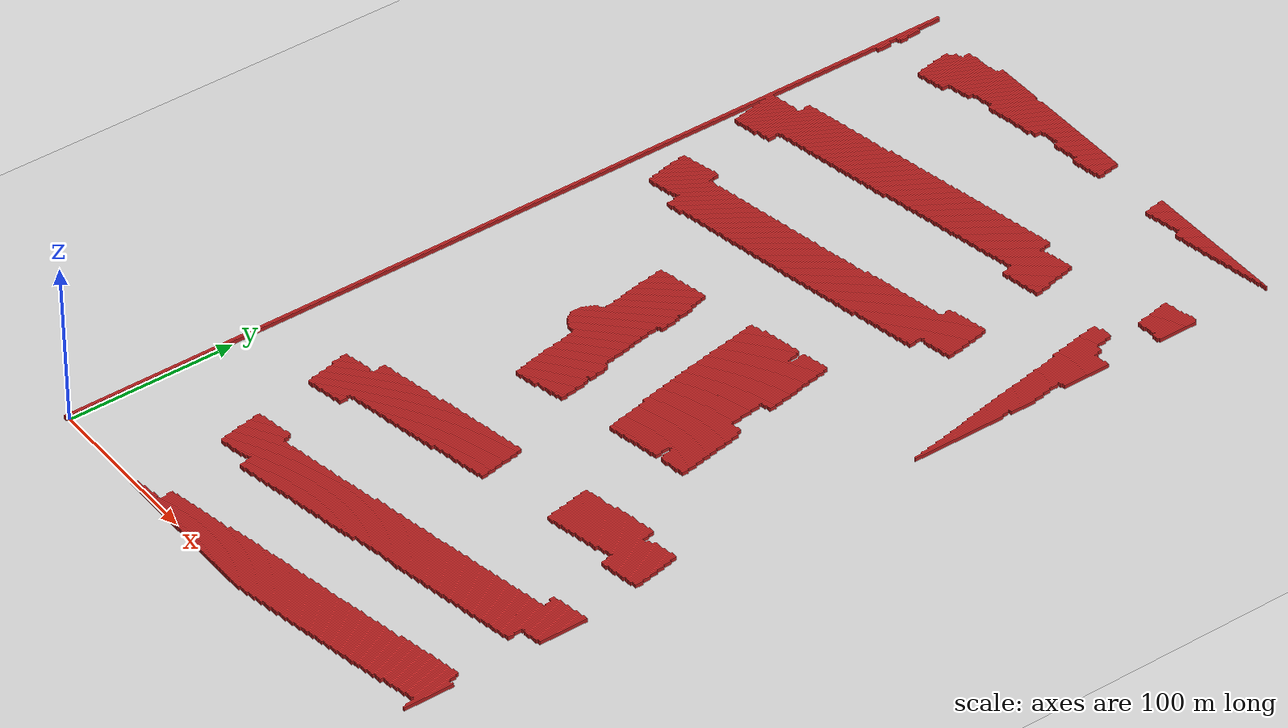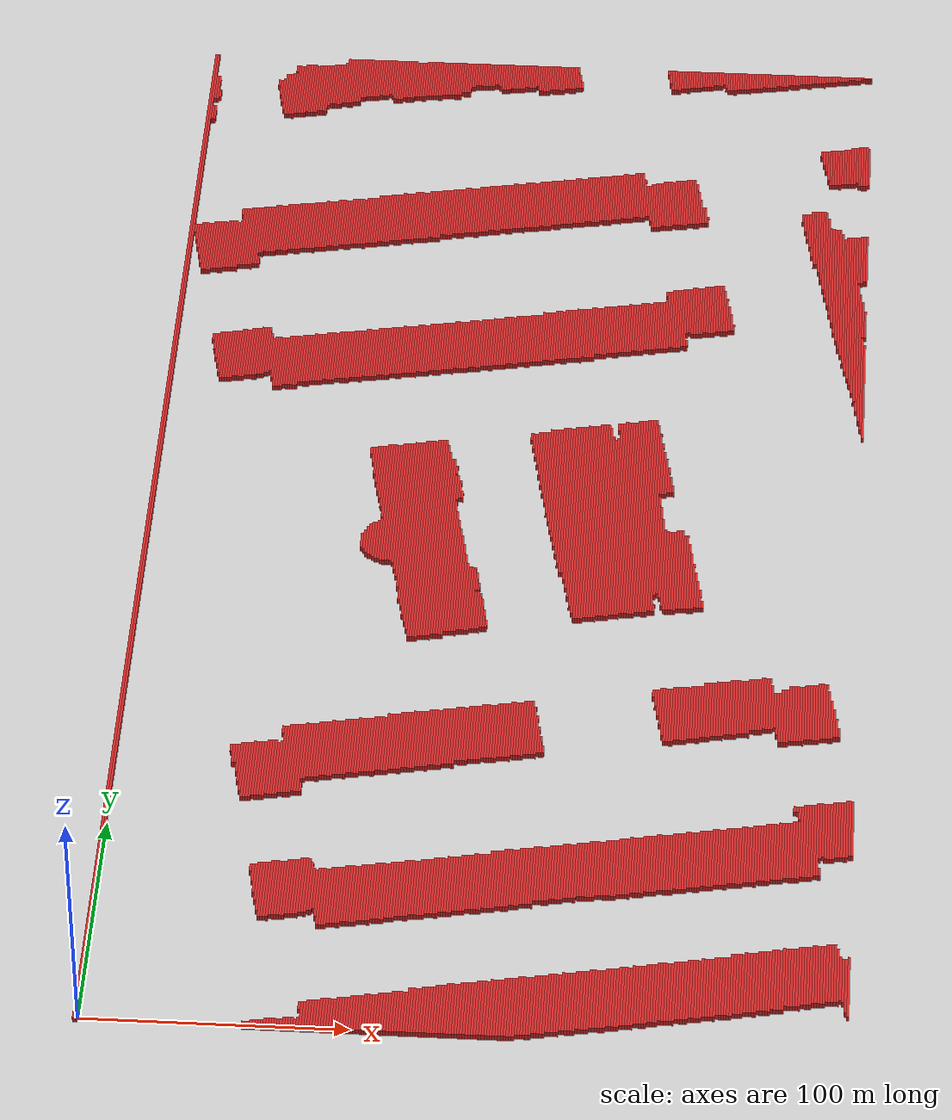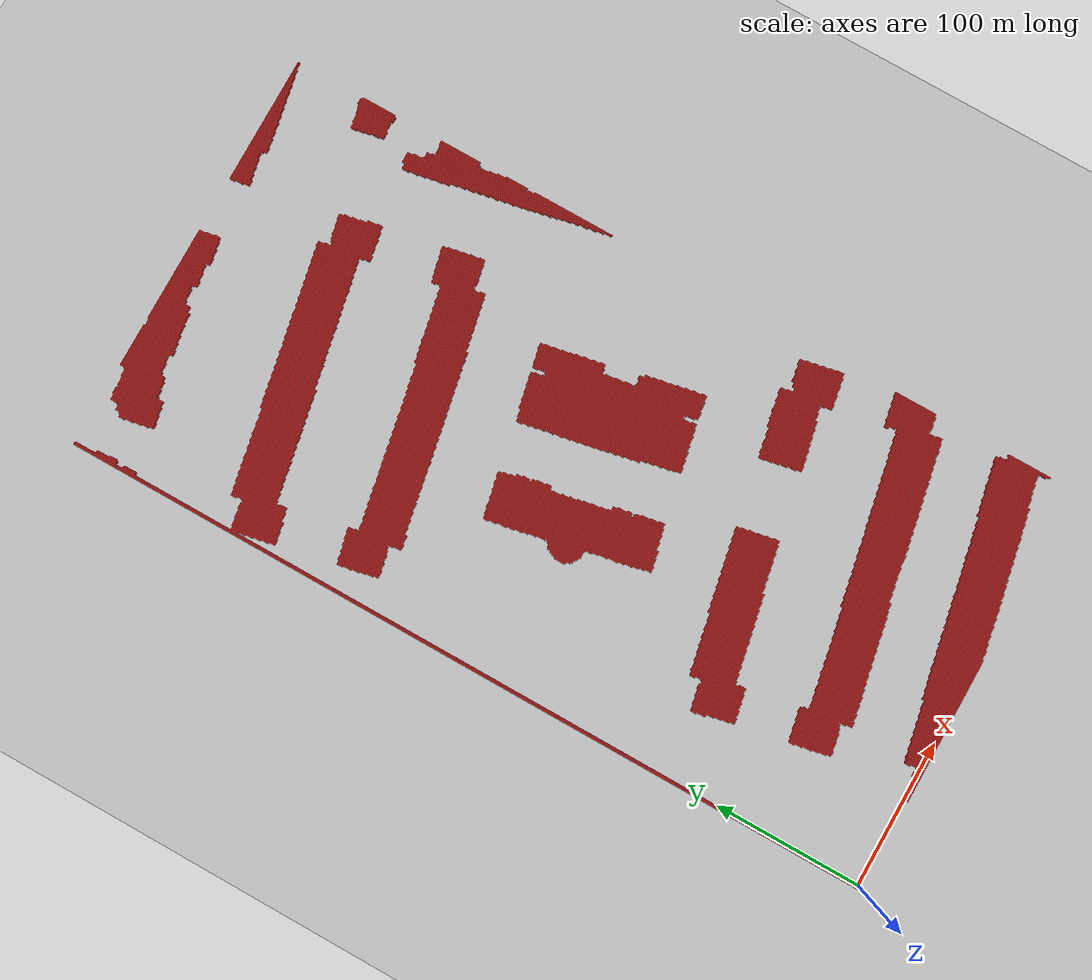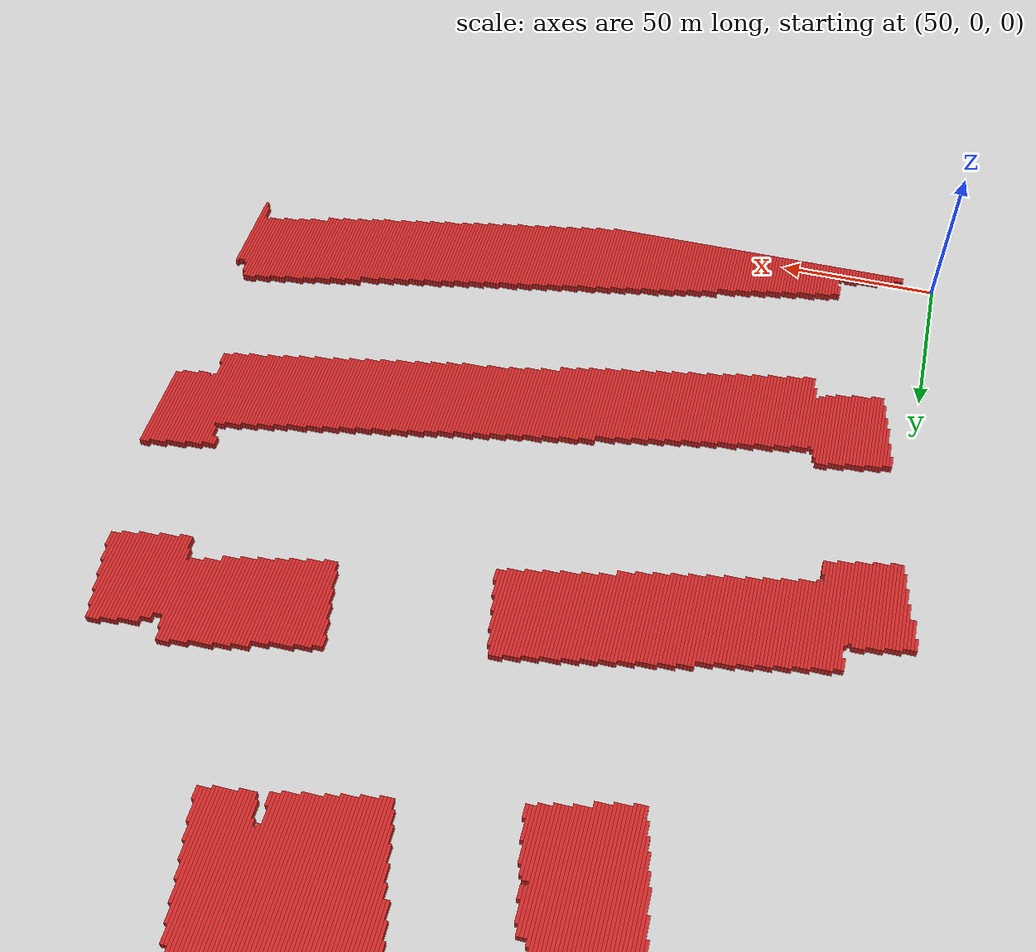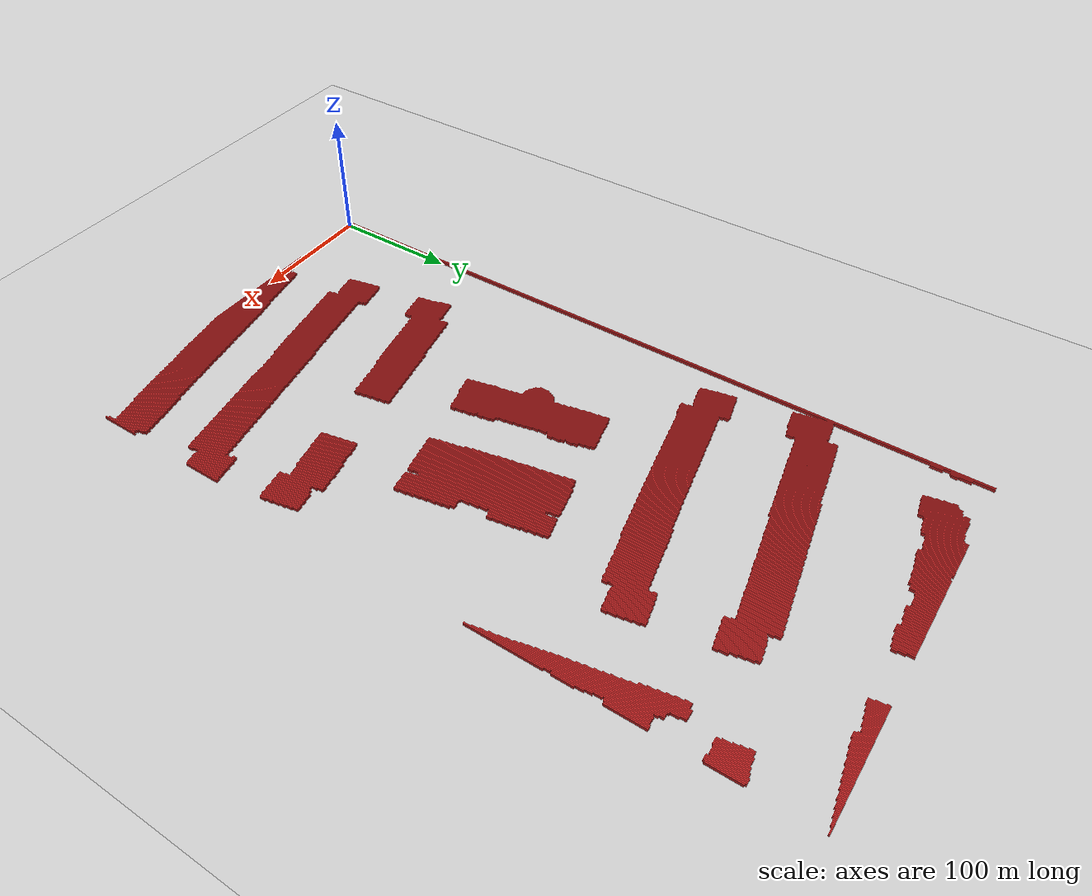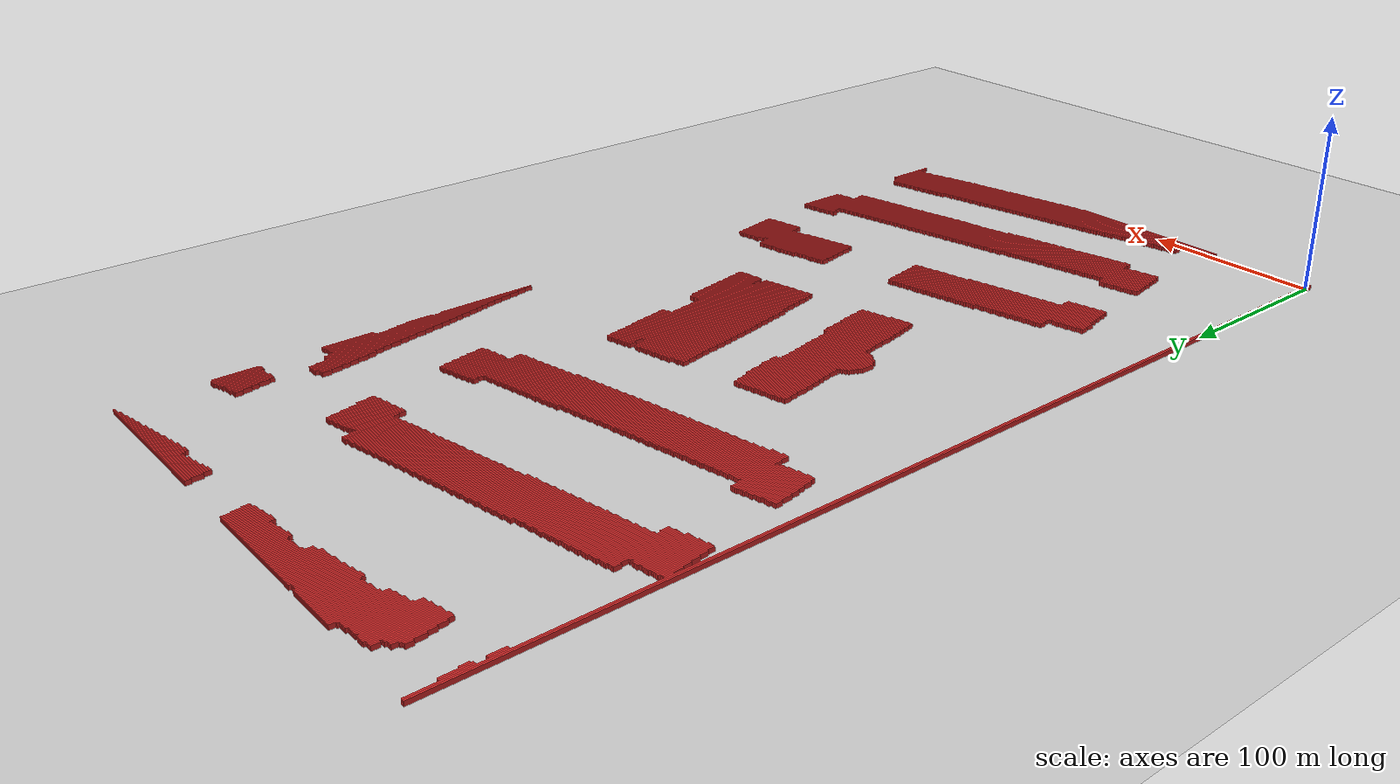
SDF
<sdf version="1.4">
 <world name="1_wall">
  <light name="sun" type="directional">
   <pose>0 0 10 0 -0 0</pose>
   <diffuse>0.8 0.8 0.8 1</diffuse>
   <specular>0.2 0.2 0.2 1</specular>
   <attenuation>
    <range>1000</range>
    <constant>0.9</constant>
    <linear>0.01</linear>
    <quadratic>0.001</quadratic>
   </attenuation>
   <direction>-0.5 0.1 -0.9</direction>
  </light>
  <physics type="ode">
   <max_step_size>0.01</max_step_size>
   <real_time_factor>1</real_time_factor>
   <real_time_update_rate>100</real_time_update_rate>
   <gravity>0 0 -9.8</gravity>
  </physics>
  <scene><ambient>0.4 0.4 0.4 1</ambient><background>0.7 0.7 0.7 1</background><shadows>1</shadows></scene>
  <model name="ground_plane">
   <static>1</static>
   <link name="link">
    <collision name="collision">
     <geometry><plane><normal>0 0 1</normal><size>1000 1000</size></plane></geometry>
     <surface><friction><ode><mu>100</mu><mu2>50</mu2></ode></friction></surface>
    </collision>
    <visual name="visual">
     <cast_shadows>0</cast_shadows>
     <geometry><plane><normal>0 0 1</normal><size>10000 10000</size></plane></geometry>
     <material>
      <script><uri>file://media/materials/scripts/gazebo.material</uri><name>Gazebo/Grey</name></script>
     </material>
    </visual>
    <velocity_decay><linear>0</linear><angular>0</angular></velocity_decay>
   </link>
  </model>
  <model name="Wall_0">
   <static>1</static>
   <link name="Wall_0">
    <collision name="Wall_Collision_0">
     <geometry><box><size>566.0 1.0 2.5</size></box></geometry>
     <pose>0 0 1.25 0 -0 0</pose>
    </collision>
    <visual name="Wall_Visual_0">
     <pose>0 0 1.25 0 -0 0</pose>
     <geometry><box><size>566.0 1.0 2.5</size></box></geometry>
     <material>
      <script><uri>file://media/materials/scripts/gazebo.material</uri><name>Gazebo/Red</name></script>
     </material>
    </visual>
    <velocity_decay><linear>0</linear><angular>0</angular></velocity_decay>
    <pose>-1.5 281.0 0 0 0 1.5707963267948966</pose>
   </link>
  </model>
  <model name="Wall_1">
   <static>1</static>
   <link name="Wall_1">
    <collision name="Wall_Collision_1">
     <geometry><box><size>566.0 1.0 2.5</size></box></geometry>
     <pose>0 0 1.25 0 -0 0</pose>
    </collision>
    <visual name="Wall_Visual_1">
     <pose>0 0 1.25 0 -0 0</pose>
     <geometry><box><size>566.0 1.0 2.5</size></box></geometry>
     <material>
      <script><uri>file://media/materials/scripts/gazebo.material</uri><name>Gazebo/Red</name></script>
     </material>
    </visual>
    <velocity_decay><linear>0</linear><angular>0</angular></velocity_decay>
    <pose>-0.5 281.0 0 0 0 1.5707963267948966</pose>
   </link>
  </model>
  <model name="Wall_2">
   <static>1</static>
   <link name="Wall_2">
    <collision name="Wall_Collision_2">
     <geometry><box><size>5.0 1.0 2.5</size></box></geometry>
     <pose>0 0 1.25 0 -0 0</pose>
    </collision>
    <visual name="Wall_Visual_2">
     <pose>0 0 1.25 0 -0 0</pose>
     <geometry><box><size>5.0 1.0 2.5</size></box></geometry>
     <material>
      <script><uri>file://media/materials/scripts/gazebo.material</uri><name>Gazebo/Red</name></script>
     </material>
    </visual>
    <velocity_decay><linear>0</linear><angular>0</angular></velocity_decay>
    <pose>0.5 447.5 0 0 0 1.5707963267948966</pose>
   </link>
  </model>
  <model name="Wall_3">
   <static>1</static>
   <link name="Wall_3">
    <collision name="Wall_Collision_3">
     <geometry><box><size>9.0 1.0 2.5</size></box></geometry>
     <pose>0 0 1.25 0 -0 0</pose>
    </collision>
    <visual name="Wall_Visual_3">
     <pose>0 0 1.25 0 -0 0</pose>
     <geometry><box><size>9.0 1.0 2.5</size></box></geometry>
     <material>
      <script><uri>file://media/materials/scripts/gazebo.material</uri><name>Gazebo/Red</name></script>
     </material>
    </visual>
    <velocity_decay><linear>0</linear><angular>0</angular></velocity_decay>
    <pose>0.5 524.5 0 0 0 1.5707963267948966</pose>
   </link>
  </model>
  <model name="Wall_4">
   <static>1</static>
   <link name="Wall_4">
    <collision name="Wall_Collision_4">
     <geometry><box><size>15.0 1.0 2.5</size></box></geometry>
     <pose>0 0 1.25 0 -0 0</pose>
    </collision>
    <visual name="Wall_Visual_4">
     <pose>0 0 1.25 0 -0 0</pose>
     <geometry><box><size>15.0 1.0 2.5</size></box></geometry>
     <material>
      <script><uri>file://media/materials/scripts/gazebo.material</uri><name>Gazebo/Red</name></script>
     </material>
    </visual>
    <velocity_decay><linear>0</linear><angular>0</angular></velocity_decay>
    <pose>0.5 541.5 0 0 0 1.5707963267948966</pose>
   </link>
  </model>
  <model name="Wall_5">
   <static>1</static>
   <link name="Wall_5">
    <collision name="Wall_Collision_5">
     <geometry><box><size>10.0 1.0 2.5</size></box></geometry>
     <pose>0 0 1.25 0 -0 0</pose>
    </collision>
    <visual name="Wall_Visual_5">
     <pose>0 0 1.25 0 -0 0</pose>
     <geometry><box><size>10.0 1.0 2.5</size></box></geometry>
     <material>
      <script><uri>file://media/materials/scripts/gazebo.material</uri><name>Gazebo/Red</name></script>
     </material>
    </visual>
    <velocity_decay><linear>0</linear><angular>0</angular></velocity_decay>
    <pose>1.5 445.0 0 0 0 1.5707963267948966</pose>
   </link>
  </model>
  <model name="Wall_6">
   <static>1</static>
   <link name="Wall_6">
    <collision name="Wall_Collision_6">
     <geometry><box><size>9.0 1.0 2.5</size></box></geometry>
     <pose>0 0 1.25 0 -0 0</pose>
    </collision>
    <visual name="Wall_Visual_6">
     <pose>0 0 1.25 0 -0 0</pose>
     <geometry><box><size>9.0 1.0 2.5</size></box></geometry>
     <material>
      <script><uri>file://media/materials/scripts/gazebo.material</uri><name>Gazebo/Red</name></script>
     </material>
    </visual>
    <velocity_decay><linear>0</linear><angular>0</angular></velocity_decay>
    <pose>1.5 524.5 0 0 0 1.5707963267948966</pose>
   </link>
  </model>
  <model name="Wall_7">
   <static>1</static>
   <link name="Wall_7">
    <collision name="Wall_Collision_7">
     <geometry><box><size>15.0 1.0 2.5</size></box></geometry>
     <pose>0 0 1.25 0 -0 0</pose>
    </collision>
    <visual name="Wall_Visual_7">
     <pose>0 0 1.25 0 -0 0</pose>
     <geometry><box><size>15.0 1.0 2.5</size></box></geometry>
     <material>
      <script><uri>file://media/materials/scripts/gazebo.material</uri><name>Gazebo/Red</name></script>
     </material>
    </visual>
    <velocity_decay><linear>0</linear><angular>0</angular></velocity_decay>
    <pose>1.5 541.5 0 0 0 1.5707963267948966</pose>
   </link>
  </model>
  <model name="Wall_8">
   <static>1</static>
   <link name="Wall_8">
    <collision name="Wall_Collision_8">
     <geometry><box><size>15.0 1.0 2.5</size></box></geometry>
     <pose>0 0 1.25 0 -0 0</pose>
    </collision>
    <visual name="Wall_Visual_8">
     <pose>0 0 1.25 0 -0 0</pose>
     <geometry><box><size>15.0 1.0 2.5</size></box></geometry>
     <material>
      <script><uri>file://media/materials/scripts/gazebo.material</uri><name>Gazebo/Red</name></script>
     </material>
    </visual>
    <velocity_decay><linear>0</linear><angular>0</angular></velocity_decay>
    <pose>2.5 442.5 0 0 0 1.5707963267948966</pose>
   </link>
  </model>
  <model name="Wall_9">
   <static>1</static>
   <link name="Wall_9">
    <collision name="Wall_Collision_9">
     <geometry><box><size>5.0 1.0 2.5</size></box></geometry>
     <pose>0 0 1.25 0 -0 0</pose>
    </collision>
    <visual name="Wall_Visual_9">
     <pose>0 0 1.25 0 -0 0</pose>
     <geometry><box><size>5.0 1.0 2.5</size></box></geometry>
     <material>
      <script><uri>file://media/materials/scripts/gazebo.material</uri><name>Gazebo/Red</name></script>
     </material>
    </visual>
    <velocity_decay><linear>0</linear><angular>0</angular></velocity_decay>
    <pose>2.5 537.5 0 0 0 1.5707963267948966</pose>
   </link>
  </model>
  <model name="Wall_10">
   <static>1</static>
   <link name="Wall_10">
    <collision name="Wall_Collision_10">
     <geometry><box><size>21.0 1.0 2.5</size></box></geometry>
     <pose>0 0 1.25 0 -0 0</pose>
    </collision>
    <visual name="Wall_Visual_10">
     <pose>0 0 1.25 0 -0 0</pose>
     <geometry><box><size>21.0 1.0 2.5</size></box></geometry>
     <material>
      <script><uri>file://media/materials/scripts/gazebo.material</uri><name>Gazebo/Red</name></script>
     </material>
    </visual>
    <velocity_decay><linear>0</linear><angular>0</angular></velocity_decay>
    <pose>3.5 440.5 0 0 0 1.5707963267948966</pose>
   </link>
  </model>
  <model name="Wall_11">
   <static>1</static>
   <link name="Wall_11">
    <collision name="Wall_Collision_11">
     <geometry><box><size>26.0 1.0 2.5</size></box></geometry>
     <pose>0 0 1.25 0 -0 0</pose>
    </collision>
    <visual name="Wall_Visual_11">
     <pose>0 0 1.25 0 -0 0</pose>
     <geometry><box><size>26.0 1.0 2.5</size></box></geometry>
     <material>
      <script><uri>file://media/materials/scripts/gazebo.material</uri><name>Gazebo/Red</name></script>
     </material>
    </visual>
    <velocity_decay><linear>0</linear><angular>0</angular></velocity_decay>
    <pose>4.5 438.0 0 0 0 1.5707963267948966</pose>
   </link>
  </model>
  <model name="Wall_12">
   <static>1</static>
   <link name="Wall_12">
    <collision name="Wall_Collision_12">
     <geometry><box><size>30.0 1.0 2.5</size></box></geometry>
     <pose>0 0 1.25 0 -0 0</pose>
    </collision>
    <visual name="Wall_Visual_12">
     <pose>0 0 1.25 0 -0 0</pose>
     <geometry><box><size>30.0 1.0 2.5</size></box></geometry>
     <material>
      <script><uri>file://media/materials/scripts/gazebo.material</uri><name>Gazebo/Red</name></script>
     </material>
    </visual>
    <velocity_decay><linear>0</linear><angular>0</angular></velocity_decay>
    <pose>5.5 436.0 0 0 0 1.5707963267948966</pose>
   </link>
  </model>
  <model name="Wall_13">
   <static>1</static>
   <link name="Wall_13">
    <collision name="Wall_Collision_13">
     <geometry><box><size>30.0 1.0 2.5</size></box></geometry>
     <pose>0 0 1.25 0 -0 0</pose>
    </collision>
    <visual name="Wall_Visual_13">
     <pose>0 0 1.25 0 -0 0</pose>
     <geometry><box><size>30.0 1.0 2.5</size></box></geometry>
     <material>
      <script><uri>file://media/materials/scripts/gazebo.material</uri><name>Gazebo/Red</name></script>
     </material>
    </visual>
    <velocity_decay><linear>0</linear><angular>0</angular></velocity_decay>
    <pose>6.5 436.0 0 0 0 1.5707963267948966</pose>
   </link>
  </model>
  <model name="Wall_14">
   <static>1</static>
   <link name="Wall_14">
    <collision name="Wall_Collision_14">
     <geometry><box><size>30.0 1.0 2.5</size></box></geometry>
     <pose>0 0 1.25 0 -0 0</pose>
    </collision>
    <visual name="Wall_Visual_14">
     <pose>0 0 1.25 0 -0 0</pose>
     <geometry><box><size>30.0 1.0 2.5</size></box></geometry>
     <material>
      <script><uri>file://media/materials/scripts/gazebo.material</uri><name>Gazebo/Red</name></script>
     </material>
    </visual>
    <velocity_decay><linear>0</linear><angular>0</angular></velocity_decay>
    <pose>7.5 436.0 0 0 0 1.5707963267948966</pose>
   </link>
  </model>
  <model name="Wall_15">
   <static>1</static>
   <link name="Wall_15">
    <collision name="Wall_Collision_15">
     <geometry><box><size>31.0 1.0 2.5</size></box></geometry>
     <pose>0 0 1.25 0 -0 0</pose>
    </collision>
    <visual name="Wall_Visual_15">
     <pose>0 0 1.25 0 -0 0</pose>
     <geometry><box><size>31.0 1.0 2.5</size></box></geometry>
     <material>
      <script><uri>file://media/materials/scripts/gazebo.material</uri><name>Gazebo/Red</name></script>
     </material>
    </visual>
    <velocity_decay><linear>0</linear><angular>0</angular></velocity_decay>
    <pose>8.5 436.5 0 0 0 1.5707963267948966</pose>
   </link>
  </model>
  <model name="Wall_16">
   <static>1</static>
   <link name="Wall_16">
    <collision name="Wall_Collision_16">
     <geometry><box><size>30.0 1.0 2.5</size></box></geometry>
     <pose>0 0 1.25 0 -0 0</pose>
    </collision>
    <visual name="Wall_Visual_16">
     <pose>0 0 1.25 0 -0 0</pose>
     <geometry><box><size>30.0 1.0 2.5</size></box></geometry>
     <material>
      <script><uri>file://media/materials/scripts/gazebo.material</uri><name>Gazebo/Red</name></script>
     </material>
    </visual>
    <velocity_decay><linear>0</linear><angular>0</angular></velocity_decay>
    <pose>9.5 437.0 0 0 0 1.5707963267948966</pose>
   </link>
  </model>
  <model name="Wall_17">
   <static>1</static>
   <link name="Wall_17">
    <collision name="Wall_Collision_17">
     <geometry><box><size>30.0 1.0 2.5</size></box></geometry>
     <pose>0 0 1.25 0 -0 0</pose>
    </collision>
    <visual name="Wall_Visual_17">
     <pose>0 0 1.25 0 -0 0</pose>
     <geometry><box><size>30.0 1.0 2.5</size></box></geometry>
     <material>
      <script><uri>file://media/materials/scripts/gazebo.material</uri><name>Gazebo/Red</name></script>
     </material>
    </visual>
    <velocity_decay><linear>0</linear><angular>0</angular></velocity_decay>
    <pose>10.5 437.0 0 0 0 1.5707963267948966</pose>
   </link>
  </model>
  <model name="Wall_18">
   <static>1</static>
   <link name="Wall_18">
    <collision name="Wall_Collision_18">
     <geometry><box><size>30.0 1.0 2.5</size></box></geometry>
     <pose>0 0 1.25 0 -0 0</pose>
    </collision>
    <visual name="Wall_Visual_18">
     <pose>0 0 1.25 0 -0 0</pose>
     <geometry><box><size>30.0 1.0 2.5</size></box></geometry>
     <material>
      <script><uri>file://media/materials/scripts/gazebo.material</uri><name>Gazebo/Red</name></script>
     </material>
    </visual>
    <velocity_decay><linear>0</linear><angular>0</angular></velocity_decay>
    <pose>11.5 437.0 0 0 0 1.5707963267948966</pose>
   </link>
  </model>
  <model name="Wall_19">
   <static>1</static>
   <link name="Wall_19">
    <collision name="Wall_Collision_19">
     <geometry><box><size>30.0 1.0 2.5</size></box></geometry>
     <pose>0 0 1.25 0 -0 0</pose>
    </collision>
    <visual name="Wall_Visual_19">
     <pose>0 0 1.25 0 -0 0</pose>
     <geometry><box><size>30.0 1.0 2.5</size></box></geometry>
     <material>
      <script><uri>file://media/materials/scripts/gazebo.material</uri><name>Gazebo/Red</name></script>
     </material>
    </visual>
    <velocity_decay><linear>0</linear><angular>0</angular></velocity_decay>
    <pose>12.5 437.0 0 0 0 1.5707963267948966</pose>
   </link>
  </model>
  <model name="Wall_20">
   <static>1</static>
   <link name="Wall_20">
    <collision name="Wall_Collision_20">
     <geometry><box><size>30.0 1.0 2.5</size></box></geometry>
     <pose>0 0 1.25 0 -0 0</pose>
    </collision>
    <visual name="Wall_Visual_20">
     <pose>0 0 1.25 0 -0 0</pose>
     <geometry><box><size>30.0 1.0 2.5</size></box></geometry>
     <material>
      <script><uri>file://media/materials/scripts/gazebo.material</uri><name>Gazebo/Red</name></script>
     </material>
    </visual>
    <velocity_decay><linear>0</linear><angular>0</angular></velocity_decay>
    <pose>13.5 437.0 0 0 0 1.5707963267948966</pose>
   </link>
  </model>
  <model name="Wall_21">
   <static>1</static>
   <link name="Wall_21">
    <collision name="Wall_Collision_21">
     <geometry><box><size>4.0 1.0 2.5</size></box></geometry>
     <pose>0 0 1.25 0 -0 0</pose>
    </collision>
    <visual name="Wall_Visual_21">
     <pose>0 0 1.25 0 -0 0</pose>
     <geometry><box><size>4.0 1.0 2.5</size></box></geometry>
     <material>
      <script><uri>file://media/materials/scripts/gazebo.material</uri><name>Gazebo/Red</name></script>
     </material>
    </visual>
    <velocity_decay><linear>0</linear><angular>0</angular></velocity_decay>
    <pose>14.5 379.0 0 0 0 1.5707963267948966</pose>
   </link>
  </model>
  <model name="Wall_22">
   <static>1</static>
   <link name="Wall_22">
    <collision name="Wall_Collision_22">
     <geometry><box><size>30.0 1.0 2.5</size></box></geometry>
     <pose>0 0 1.25 0 -0 0</pose>
    </collision>
    <visual name="Wall_Visual_22">
     <pose>0 0 1.25 0 -0 0</pose>
     <geometry><box><size>30.0 1.0 2.5</size></box></geometry>
     <material>
      <script><uri>file://media/materials/scripts/gazebo.material</uri><name>Gazebo/Red</name></script>
     </material>
    </visual>
    <velocity_decay><linear>0</linear><angular>0</angular></velocity_decay>
    <pose>14.5 438.0 0 0 0 1.5707963267948966</pose>
   </link>
  </model>
  <model name="Wall_23">
   <static>1</static>
   <link name="Wall_23">
    <collision name="Wall_Collision_23">
     <geometry><box><size>10.0 1.0 2.5</size></box></geometry>
     <pose>0 0 1.25 0 -0 0</pose>
    </collision>
    <visual name="Wall_Visual_23">
     <pose>0 0 1.25 0 -0 0</pose>
     <geometry><box><size>10.0 1.0 2.5</size></box></geometry>
     <material>
      <script><uri>file://media/materials/scripts/gazebo.material</uri><name>Gazebo/Red</name></script>
     </material>
    </visual>
    <velocity_decay><linear>0</linear><angular>0</angular></velocity_decay>
    <pose>15.5 376.0 0 0 0 1.5707963267948966</pose>
   </link>
  </model>
  <model name="Wall_24">
   <static>1</static>
   <link name="Wall_24">
    <collision name="Wall_Collision_24">
     <geometry><box><size>30.0 1.0 2.5</size></box></geometry>
     <pose>0 0 1.25 0 -0 0</pose>
    </collision>
    <visual name="Wall_Visual_24">
     <pose>0 0 1.25 0 -0 0</pose>
     <geometry><box><size>30.0 1.0 2.5</size></box></geometry>
     <material>
      <script><uri>file://media/materials/scripts/gazebo.material</uri><name>Gazebo/Red</name></script>
     </material>
    </visual>
    <velocity_decay><linear>0</linear><angular>0</angular></velocity_decay>
    <pose>15.5 438.0 0 0 0 1.5707963267948966</pose>
   </link>
  </model>
  <model name="Wall_25">
   <static>1</static>
   <link name="Wall_25">
    <collision name="Wall_Collision_25">
     <geometry><box><size>15.0 1.0 2.5</size></box></geometry>
     <pose>0 0 1.25 0 -0 0</pose>
    </collision>
    <visual name="Wall_Visual_25">
     <pose>0 0 1.25 0 -0 0</pose>
     <geometry><box><size>15.0 1.0 2.5</size></box></geometry>
     <material>
      <script><uri>file://media/materials/scripts/gazebo.material</uri><name>Gazebo/Red</name></script>
     </material>
    </visual>
    <velocity_decay><linear>0</linear><angular>0</angular></velocity_decay>
    <pose>16.5 373.5 0 0 0 1.5707963267948966</pose>
   </link>
  </model>
  <model name="Wall_26">
   <static>1</static>
   <link name="Wall_26">
    <collision name="Wall_Collision_26">
     <geometry><box><size>30.0 1.0 2.5</size></box></geometry>
     <pose>0 0 1.25 0 -0 0</pose>
    </collision>
    <visual name="Wall_Visual_26">
     <pose>0 0 1.25 0 -0 0</pose>
     <geometry><box><size>30.0 1.0 2.5</size></box></geometry>
     <material>
      <script><uri>file://media/materials/scripts/gazebo.material</uri><name>Gazebo/Red</name></script>
     </material>
    </visual>
    <velocity_decay><linear>0</linear><angular>0</angular></velocity_decay>
    <pose>16.5 438.0 0 0 0 1.5707963267948966</pose>
   </link>
  </model>
  <model name="Wall_27">
   <static>1</static>
   <link name="Wall_27">
    <collision name="Wall_Collision_27">
     <geometry><box><size>20.0 1.0 2.5</size></box></geometry>
     <pose>0 0 1.25 0 -0 0</pose>
    </collision>
    <visual name="Wall_Visual_27">
     <pose>0 0 1.25 0 -0 0</pose>
     <geometry><box><size>20.0 1.0 2.5</size></box></geometry>
     <material>
      <script><uri>file://media/materials/scripts/gazebo.material</uri><name>Gazebo/Red</name></script>
     </material>
    </visual>
    <velocity_decay><linear>0</linear><angular>0</angular></velocity_decay>
    <pose>17.5 372.0 0 0 0 1.5707963267948966</pose>
   </link>
  </model>
  <model name="Wall_28">
   <static>1</static>
   <link name="Wall_28">
    <collision name="Wall_Collision_28">
     <geometry><box><size>30.0 1.0 2.5</size></box></geometry>
     <pose>0 0 1.25 0 -0 0</pose>
    </collision>
    <visual name="Wall_Visual_28">
     <pose>0 0 1.25 0 -0 0</pose>
     <geometry><box><size>30.0 1.0 2.5</size></box></geometry>
     <material>
      <script><uri>file://media/materials/scripts/gazebo.material</uri><name>Gazebo/Red</name></script>
     </material>
    </visual>
    <velocity_decay><linear>0</linear><angular>0</angular></velocity_decay>
    <pose>17.5 438.0 0 0 0 1.5707963267948966</pose>
   </link>
  </model>
  <model name="Wall_29">
   <static>1</static>
   <link name="Wall_29">
    <collision name="Wall_Collision_29">
     <geometry><box><size>25.0 1.0 2.5</size></box></geometry>
     <pose>0 0 1.25 0 -0 0</pose>
    </collision>
    <visual name="Wall_Visual_29">
     <pose>0 0 1.25 0 -0 0</pose>
     <geometry><box><size>25.0 1.0 2.5</size></box></geometry>
     <material>
      <script><uri>file://media/materials/scripts/gazebo.material</uri><name>Gazebo/Red</name></script>
     </material>
    </visual>
    <velocity_decay><linear>0</linear><angular>0</angular></velocity_decay>
    <pose>18.5 369.5 0 0 0 1.5707963267948966</pose>
   </link>
  </model>
  <model name="Wall_30">
   <static>1</static>
   <link name="Wall_30">
    <collision name="Wall_Collision_30">
     <geometry><box><size>29.0 1.0 2.5</size></box></geometry>
     <pose>0 0 1.25 0 -0 0</pose>
    </collision>
    <visual name="Wall_Visual_30">
     <pose>0 0 1.25 0 -0 0</pose>
     <geometry><box><size>29.0 1.0 2.5</size></box></geometry>
     <material>
      <script><uri>file://media/materials/scripts/gazebo.material</uri><name>Gazebo/Red</name></script>
     </material>
    </visual>
    <velocity_decay><linear>0</linear><angular>0</angular></velocity_decay>
    <pose>18.5 437.5 0 0 0 1.5707963267948966</pose>
   </link>
  </model>
  <model name="Wall_31">
   <static>1</static>
   <link name="Wall_31">
    <collision name="Wall_Collision_31">
     <geometry><box><size>28.0 1.0 2.5</size></box></geometry>
     <pose>0 0 1.25 0 -0 0</pose>
    </collision>
    <visual name="Wall_Visual_31">
     <pose>0 0 1.25 0 -0 0</pose>
     <geometry><box><size>28.0 1.0 2.5</size></box></geometry>
     <material>
      <script><uri>file://media/materials/scripts/gazebo.material</uri><name>Gazebo/Red</name></script>
     </material>
    </visual>
    <velocity_decay><linear>0</linear><angular>0</angular></velocity_decay>
    <pose>19.5 368.0 0 0 0 1.5707963267948966</pose>
   </link>
  </model>
  <model name="Wall_32">
   <static>1</static>
   <link name="Wall_32">
    <collision name="Wall_Collision_32">
     <geometry><box><size>30.0 1.0 2.5</size></box></geometry>
     <pose>0 0 1.25 0 -0 0</pose>
    </collision>
    <visual name="Wall_Visual_32">
     <pose>0 0 1.25 0 -0 0</pose>
     <geometry><box><size>30.0 1.0 2.5</size></box></geometry>
     <material>
      <script><uri>file://media/materials/scripts/gazebo.material</uri><name>Gazebo/Red</name></script>
     </material>
    </visual>
    <velocity_decay><linear>0</linear><angular>0</angular></velocity_decay>
    <pose>19.5 438.0 0 0 0 1.5707963267948966</pose>
   </link>
  </model>
  <model name="Wall_33">
   <static>1</static>
   <link name="Wall_33">
    <collision name="Wall_Collision_33">
     <geometry><box><size>4.0 1.0 2.5</size></box></geometry>
     <pose>0 0 1.25 0 -0 0</pose>
    </collision>
    <visual name="Wall_Visual_33">
     <pose>0 0 1.25 0 -0 0</pose>
     <geometry><box><size>4.0 1.0 2.5</size></box></geometry>
     <material>
      <script><uri>file://media/materials/scripts/gazebo.material</uri><name>Gazebo/Red</name></script>
     </material>
    </visual>
    <velocity_decay><linear>0</linear><angular>0</angular></velocity_decay>
    <pose>19.5 459.0 0 0 0 1.5707963267948966</pose>
   </link>
  </model>
  <model name="Wall_34">
   <static>1</static>
   <link name="Wall_34">
    <collision name="Wall_Collision_34">
     <geometry><box><size>28.0 1.0 2.5</size></box></geometry>
     <pose>0 0 1.25 0 -0 0</pose>
    </collision>
    <visual name="Wall_Visual_34">
     <pose>0 0 1.25 0 -0 0</pose>
     <geometry><box><size>28.0 1.0 2.5</size></box></geometry>
     <material>
      <script><uri>file://media/materials/scripts/gazebo.material</uri><name>Gazebo/Red</name></script>
     </material>
    </visual>
    <velocity_decay><linear>0</linear><angular>0</angular></velocity_decay>
    <pose>20.5 368.0 0 0 0 1.5707963267948966</pose>
   </link>
  </model>
  <model name="Wall_35">
   <static>1</static>
   <link name="Wall_35">
    <collision name="Wall_Collision_35">
     <geometry><box><size>36.0 1.0 2.5</size></box></geometry>
     <pose>0 0 1.25 0 -0 0</pose>
    </collision>
    <visual name="Wall_Visual_35">
     <pose>0 0 1.25 0 -0 0</pose>
     <geometry><box><size>36.0 1.0 2.5</size></box></geometry>
     <material>
      <script><uri>file://media/materials/scripts/gazebo.material</uri><name>Gazebo/Red</name></script>
     </material>
    </visual>
    <velocity_decay><linear>0</linear><angular>0</angular></velocity_decay>
    <pose>20.5 443.0 0 0 0 1.5707963267948966</pose>
   </link>
  </model>
  <model name="Wall_36">
   <static>1</static>
   <link name="Wall_36">
    <collision name="Wall_Collision_36">
     <geometry><box><size>28.0 1.0 2.5</size></box></geometry>
     <pose>0 0 1.25 0 -0 0</pose>
    </collision>
    <visual name="Wall_Visual_36">
     <pose>0 0 1.25 0 -0 0</pose>
     <geometry><box><size>28.0 1.0 2.5</size></box></geometry>
     <material>
      <script><uri>file://media/materials/scripts/gazebo.material</uri><name>Gazebo/Red</name></script>
     </material>
    </visual>
    <velocity_decay><linear>0</linear><angular>0</angular></velocity_decay>
    <pose>21.5 368.0 0 0 0 1.5707963267948966</pose>
   </link>
  </model>
  <model name="Wall_37">
   <static>1</static>
   <link name="Wall_37">
    <collision name="Wall_Collision_37">
     <geometry><box><size>36.0 1.0 2.5</size></box></geometry>
     <pose>0 0 1.25 0 -0 0</pose>
    </collision>
    <visual name="Wall_Visual_37">
     <pose>0 0 1.25 0 -0 0</pose>
     <geometry><box><size>36.0 1.0 2.5</size></box></geometry>
     <material>
      <script><uri>file://media/materials/scripts/gazebo.material</uri><name>Gazebo/Red</name></script>
     </material>
    </visual>
    <velocity_decay><linear>0</linear><angular>0</angular></velocity_decay>
    <pose>21.5 443.0 0 0 0 1.5707963267948966</pose>
   </link>
  </model>
  <model name="Wall_38">
   <static>1</static>
   <link name="Wall_38">
    <collision name="Wall_Collision_38">
     <geometry><box><size>29.0 1.0 2.5</size></box></geometry>
     <pose>0 0 1.25 0 -0 0</pose>
    </collision>
    <visual name="Wall_Visual_38">
     <pose>0 0 1.25 0 -0 0</pose>
     <geometry><box><size>29.0 1.0 2.5</size></box></geometry>
     <material>
      <script><uri>file://media/materials/scripts/gazebo.material</uri><name>Gazebo/Red</name></script>
     </material>
    </visual>
    <velocity_decay><linear>0</linear><angular>0</angular></velocity_decay>
    <pose>22.5 368.5 0 0 0 1.5707963267948966</pose>
   </link>
  </model>
  <model name="Wall_39">
   <static>1</static>
   <link name="Wall_39">
    <collision name="Wall_Collision_39">
     <geometry><box><size>36.0 1.0 2.5</size></box></geometry>
     <pose>0 0 1.25 0 -0 0</pose>
    </collision>
    <visual name="Wall_Visual_39">
     <pose>0 0 1.25 0 -0 0</pose>
     <geometry><box><size>36.0 1.0 2.5</size></box></geometry>
     <material>
      <script><uri>file://media/materials/scripts/gazebo.material</uri><name>Gazebo/Red</name></script>
     </material>
    </visual>
    <velocity_decay><linear>0</linear><angular>0</angular></velocity_decay>
    <pose>22.5 443.0 0 0 0 1.5707963267948966</pose>
   </link>
  </model>
  <model name="Wall_40">
   <static>1</static>
   <link name="Wall_40">
    <collision name="Wall_Collision_40">
     <geometry><box><size>29.0 1.0 2.5</size></box></geometry>
     <pose>0 0 1.25 0 -0 0</pose>
    </collision>
    <visual name="Wall_Visual_40">
     <pose>0 0 1.25 0 -0 0</pose>
     <geometry><box><size>29.0 1.0 2.5</size></box></geometry>
     <material>
      <script><uri>file://media/materials/scripts/gazebo.material</uri><name>Gazebo/Red</name></script>
     </material>
    </visual>
    <velocity_decay><linear>0</linear><angular>0</angular></velocity_decay>
    <pose>23.5 368.5 0 0 0 1.5707963267948966</pose>
   </link>
  </model>
  <model name="Wall_41">
   <static>1</static>
   <link name="Wall_41">
    <collision name="Wall_Collision_41">
     <geometry><box><size>37.0 1.0 2.5</size></box></geometry>
     <pose>0 0 1.25 0 -0 0</pose>
    </collision>
    <visual name="Wall_Visual_41">
     <pose>0 0 1.25 0 -0 0</pose>
     <geometry><box><size>37.0 1.0 2.5</size></box></geometry>
     <material>
      <script><uri>file://media/materials/scripts/gazebo.material</uri><name>Gazebo/Red</name></script>
     </material>
    </visual>
    <velocity_decay><linear>0</linear><angular>0</angular></velocity_decay>
    <pose>23.5 443.5 0 0 0 1.5707963267948966</pose>
   </link>
  </model>
  <model name="Wall_42">
   <static>1</static>
   <link name="Wall_42">
    <collision name="Wall_Collision_42">
     <geometry><box><size>28.0 1.0 2.5</size></box></geometry>
     <pose>0 0 1.25 0 -0 0</pose>
    </collision>
    <visual name="Wall_Visual_42">
     <pose>0 0 1.25 0 -0 0</pose>
     <geometry><box><size>28.0 1.0 2.5</size></box></geometry>
     <material>
      <script><uri>file://media/materials/scripts/gazebo.material</uri><name>Gazebo/Red</name></script>
     </material>
    </visual>
    <velocity_decay><linear>0</linear><angular>0</angular></velocity_decay>
    <pose>24.5 369.0 0 0 0 1.5707963267948966</pose>
   </link>
  </model>
  <model name="Wall_43">
   <static>1</static>
   <link name="Wall_43">
    <collision name="Wall_Collision_43">
     <geometry><box><size>37.0 1.0 2.5</size></box></geometry>
     <pose>0 0 1.25 0 -0 0</pose>
    </collision>
    <visual name="Wall_Visual_43">
     <pose>0 0 1.25 0 -0 0</pose>
     <geometry><box><size>37.0 1.0 2.5</size></box></geometry>
     <material>
      <script><uri>file://media/materials/scripts/gazebo.material</uri><name>Gazebo/Red</name></script>
     </material>
    </visual>
    <velocity_decay><linear>0</linear><angular>0</angular></velocity_decay>
    <pose>24.5 443.5 0 0 0 1.5707963267948966</pose>
   </link>
  </model>
  <model name="Wall_44">
   <static>1</static>
   <link name="Wall_44">
    <collision name="Wall_Collision_44">
     <geometry><box><size>28.0 1.0 2.5</size></box></geometry>
     <pose>0 0 1.25 0 -0 0</pose>
    </collision>
    <visual name="Wall_Visual_44">
     <pose>0 0 1.25 0 -0 0</pose>
     <geometry><box><size>28.0 1.0 2.5</size></box></geometry>
     <material>
      <script><uri>file://media/materials/scripts/gazebo.material</uri><name>Gazebo/Red</name></script>
     </material>
    </visual>
    <velocity_decay><linear>0</linear><angular>0</angular></velocity_decay>
    <pose>25.5 369.0 0 0 0 1.5707963267948966</pose>
   </link>
  </model>
  <model name="Wall_45">
   <static>1</static>
   <link name="Wall_45">
    <collision name="Wall_Collision_45">
     <geometry><box><size>37.0 1.0 2.5</size></box></geometry>
     <pose>0 0 1.25 0 -0 0</pose>
    </collision>
    <visual name="Wall_Visual_45">
     <pose>0 0 1.25 0 -0 0</pose>
     <geometry><box><size>37.0 1.0 2.5</size></box></geometry>
     <material>
      <script><uri>file://media/materials/scripts/gazebo.material</uri><name>Gazebo/Red</name></script>
     </material>
    </visual>
    <velocity_decay><linear>0</linear><angular>0</angular></velocity_decay>
    <pose>25.5 443.5 0 0 0 1.5707963267948966</pose>
   </link>
  </model>
  <model name="Wall_46">
   <static>1</static>
   <link name="Wall_46">
    <collision name="Wall_Collision_46">
     <geometry><box><size>29.0 1.0 2.5</size></box></geometry>
     <pose>0 0 1.25 0 -0 0</pose>
    </collision>
    <visual name="Wall_Visual_46">
     <pose>0 0 1.25 0 -0 0</pose>
     <geometry><box><size>29.0 1.0 2.5</size></box></geometry>
     <material>
      <script><uri>file://media/materials/scripts/gazebo.material</uri><name>Gazebo/Red</name></script>
     </material>
    </visual>
    <velocity_decay><linear>0</linear><angular>0</angular></velocity_decay>
    <pose>26.5 369.5 0 0 0 1.5707963267948966</pose>
   </link>
  </model>
  <model name="Wall_47">
   <static>1</static>
   <link name="Wall_47">
    <collision name="Wall_Collision_47">
     <geometry><box><size>36.0 1.0 2.5</size></box></geometry>
     <pose>0 0 1.25 0 -0 0</pose>
    </collision>
    <visual name="Wall_Visual_47">
     <pose>0 0 1.25 0 -0 0</pose>
     <geometry><box><size>36.0 1.0 2.5</size></box></geometry>
     <material>
      <script><uri>file://media/materials/scripts/gazebo.material</uri><name>Gazebo/Red</name></script>
     </material>
    </visual>
    <velocity_decay><linear>0</linear><angular>0</angular></velocity_decay>
    <pose>26.5 444.0 0 0 0 1.5707963267948966</pose>
   </link>
  </model>
  <model name="Wall_48">
   <static>1</static>
   <link name="Wall_48">
    <collision name="Wall_Collision_48">
     <geometry><box><size>29.0 1.0 2.5</size></box></geometry>
     <pose>0 0 1.25 0 -0 0</pose>
    </collision>
    <visual name="Wall_Visual_48">
     <pose>0 0 1.25 0 -0 0</pose>
     <geometry><box><size>29.0 1.0 2.5</size></box></geometry>
     <material>
      <script><uri>file://media/materials/scripts/gazebo.material</uri><name>Gazebo/Red</name></script>
     </material>
    </visual>
    <velocity_decay><linear>0</linear><angular>0</angular></velocity_decay>
    <pose>27.5 369.5 0 0 0 1.5707963267948966</pose>
   </link>
  </model>
  <model name="Wall_49">
   <static>1</static>
   <link name="Wall_49">
    <collision name="Wall_Collision_49">
     <geometry><box><size>36.0 1.0 2.5</size></box></geometry>
     <pose>0 0 1.25 0 -0 0</pose>
    </collision>
    <visual name="Wall_Visual_49">
     <pose>0 0 1.25 0 -0 0</pose>
     <geometry><box><size>36.0 1.0 2.5</size></box></geometry>
     <material>
      <script><uri>file://media/materials/scripts/gazebo.material</uri><name>Gazebo/Red</name></script>
     </material>
    </visual>
    <velocity_decay><linear>0</linear><angular>0</angular></velocity_decay>
    <pose>27.5 444.0 0 0 0 1.5707963267948966</pose>
   </link>
  </model>
  <model name="Wall_50">
   <static>1</static>
   <link name="Wall_50">
    <collision name="Wall_Collision_50">
     <geometry><box><size>4.0 1.0 2.5</size></box></geometry>
     <pose>0 0 1.25 0 -0 0</pose>
    </collision>
    <visual name="Wall_Visual_50">
     <pose>0 0 1.25 0 -0 0</pose>
     <geometry><box><size>4.0 1.0 2.5</size></box></geometry>
     <material>
      <script><uri>file://media/materials/scripts/gazebo.material</uri><name>Gazebo/Red</name></script>
     </material>
    </visual>
    <velocity_decay><linear>0</linear><angular>0</angular></velocity_decay>
    <pose>27.5 546.0 0 0 0 1.5707963267948966</pose>
   </link>
  </model>
  <model name="Wall_51">
   <static>1</static>
   <link name="Wall_51">
    <collision name="Wall_Collision_51">
     <geometry><box><size>29.0 1.0 2.5</size></box></geometry>
     <pose>0 0 1.25 0 -0 0</pose>
    </collision>
    <visual name="Wall_Visual_51">
     <pose>0 0 1.25 0 -0 0</pose>
     <geometry><box><size>29.0 1.0 2.5</size></box></geometry>
     <material>
      <script><uri>file://media/materials/scripts/gazebo.material</uri><name>Gazebo/Red</name></script>
     </material>
    </visual>
    <velocity_decay><linear>0</linear><angular>0</angular></velocity_decay>
    <pose>28.5 369.5 0 0 0 1.5707963267948966</pose>
   </link>
  </model>
  <model name="Wall_52">
   <static>1</static>
   <link name="Wall_52">
    <collision name="Wall_Collision_52">
     <geometry><box><size>5.0 1.0 2.5</size></box></geometry>
     <pose>0 0 1.25 0 -0 0</pose>
    </collision>
    <visual name="Wall_Visual_52">
     <pose>0 0 1.25 0 -0 0</pose>
     <geometry><box><size>5.0 1.0 2.5</size></box></geometry>
     <material>
      <script><uri>file://media/materials/scripts/gazebo.material</uri><name>Gazebo/Red</name></script>
     </material>
    </visual>
    <velocity_decay><linear>0</linear><angular>0</angular></velocity_decay>
    <pose>28.5 428.5 0 0 0 1.5707963267948966</pose>
   </link>
  </model>
  <model name="Wall_53">
   <static>1</static>
   <link name="Wall_53">
    <collision name="Wall_Collision_53">
     <geometry><box><size>30.0 1.0 2.5</size></box></geometry>
     <pose>0 0 1.25 0 -0 0</pose>
    </collision>
    <visual name="Wall_Visual_53">
     <pose>0 0 1.25 0 -0 0</pose>
     <geometry><box><size>30.0 1.0 2.5</size></box></geometry>
     <material>
      <script><uri>file://media/materials/scripts/gazebo.material</uri><name>Gazebo/Red</name></script>
     </material>
    </visual>
    <velocity_decay><linear>0</linear><angular>0</angular></velocity_decay>
    <pose>28.5 448.0 0 0 0 1.5707963267948966</pose>
   </link>
  </model>
  <model name="Wall_54">
   <static>1</static>
   <link name="Wall_54">
    <collision name="Wall_Collision_54">
     <geometry><box><size>10.0 1.0 2.5</size></box></geometry>
     <pose>0 0 1.25 0 -0 0</pose>
    </collision>
    <visual name="Wall_Visual_54">
     <pose>0 0 1.25 0 -0 0</pose>
     <geometry><box><size>10.0 1.0 2.5</size></box></geometry>
     <material>
      <script><uri>file://media/materials/scripts/gazebo.material</uri><name>Gazebo/Red</name></script>
     </material>
    </visual>
    <velocity_decay><linear>0</linear><angular>0</angular></velocity_decay>
    <pose>28.5 543.0 0 0 0 1.5707963267948966</pose>
   </link>
  </model>
  <model name="Wall_55">
   <static>1</static>
   <link name="Wall_55">
    <collision name="Wall_Collision_55">
     <geometry><box><size>28.0 1.0 2.5</size></box></geometry>
     <pose>0 0 1.25 0 -0 0</pose>
    </collision>
    <visual name="Wall_Visual_55">
     <pose>0 0 1.25 0 -0 0</pose>
     <geometry><box><size>28.0 1.0 2.5</size></box></geometry>
     <material>
      <script><uri>file://media/materials/scripts/gazebo.material</uri><name>Gazebo/Red</name></script>
     </material>
    </visual>
    <velocity_decay><linear>0</linear><angular>0</angular></velocity_decay>
    <pose>29.5 370.0 0 0 0 1.5707963267948966</pose>
   </link>
  </model>
  <model name="Wall_56">
   <static>1</static>
   <link name="Wall_56">
    <collision name="Wall_Collision_56">
     <geometry><box><size>30.0 1.0 2.5</size></box></geometry>
     <pose>0 0 1.25 0 -0 0</pose>
    </collision>
    <visual name="Wall_Visual_56">
     <pose>0 0 1.25 0 -0 0</pose>
     <geometry><box><size>30.0 1.0 2.5</size></box></geometry>
     <material>
      <script><uri>file://media/materials/scripts/gazebo.material</uri><name>Gazebo/Red</name></script>
     </material>
    </visual>
    <velocity_decay><linear>0</linear><angular>0</angular></velocity_decay>
    <pose>29.5 448.0 0 0 0 1.5707963267948966</pose>
   </link>
  </model>
  <model name="Wall_57">
   <static>1</static>
   <link name="Wall_57">
    <collision name="Wall_Collision_57">
     <geometry><box><size>16.0 1.0 2.5</size></box></geometry>
     <pose>0 0 1.25 0 -0 0</pose>
    </collision>
    <visual name="Wall_Visual_57">
     <pose>0 0 1.25 0 -0 0</pose>
     <geometry><box><size>16.0 1.0 2.5</size></box></geometry>
     <material>
      <script><uri>file://media/materials/scripts/gazebo.material</uri><name>Gazebo/Red</name></script>
     </material>
    </visual>
    <velocity_decay><linear>0</linear><angular>0</angular></velocity_decay>
    <pose>29.5 541.0 0 0 0 1.5707963267948966</pose>
   </link>
  </model>
  <model name="Wall_58">
   <static>1</static>
   <link name="Wall_58">
    <collision name="Wall_Collision_58">
     <geometry><box><size>29.0 1.0 2.5</size></box></geometry>
     <pose>0 0 1.25 0 -0 0</pose>
    </collision>
    <visual name="Wall_Visual_58">
     <pose>0 0 1.25 0 -0 0</pose>
     <geometry><box><size>29.0 1.0 2.5</size></box></geometry>
     <material>
      <script><uri>file://media/materials/scripts/gazebo.material</uri><name>Gazebo/Red</name></script>
     </material>
    </visual>
    <velocity_decay><linear>0</linear><angular>0</angular></velocity_decay>
    <pose>30.5 370.5 0 0 0 1.5707963267948966</pose>
   </link>
  </model>
  <model name="Wall_59">
   <static>1</static>
   <link name="Wall_59">
    <collision name="Wall_Collision_59">
     <geometry><box><size>29.0 1.0 2.5</size></box></geometry>
     <pose>0 0 1.25 0 -0 0</pose>
    </collision>
    <visual name="Wall_Visual_59">
     <pose>0 0 1.25 0 -0 0</pose>
     <geometry><box><size>29.0 1.0 2.5</size></box></geometry>
     <material>
      <script><uri>file://media/materials/scripts/gazebo.material</uri><name>Gazebo/Red</name></script>
     </material>
    </visual>
    <velocity_decay><linear>0</linear><angular>0</angular></velocity_decay>
    <pose>30.5 448.5 0 0 0 1.5707963267948966</pose>
   </link>
  </model>
  <model name="Wall_60">
   <static>1</static>
   <link name="Wall_60">
    <collision name="Wall_Collision_60">
     <geometry><box><size>24.0 1.0 2.5</size></box></geometry>
     <pose>0 0 1.25 0 -0 0</pose>
    </collision>
    <visual name="Wall_Visual_60">
     <pose>0 0 1.25 0 -0 0</pose>
     <geometry><box><size>24.0 1.0 2.5</size></box></geometry>
     <material>
      <script><uri>file://media/materials/scripts/gazebo.material</uri><name>Gazebo/Red</name></script>
     </material>
    </visual>
    <velocity_decay><linear>0</linear><angular>0</angular></velocity_decay>
    <pose>30.5 540.0 0 0 0 1.5707963267948966</pose>
   </link>
  </model>
  <model name="Wall_61">
   <static>1</static>
   <link name="Wall_61">
    <collision name="Wall_Collision_61">
     <geometry><box><size>29.0 1.0 2.5</size></box></geometry>
     <pose>0 0 1.25 0 -0 0</pose>
    </collision>
    <visual name="Wall_Visual_61">
     <pose>0 0 1.25 0 -0 0</pose>
     <geometry><box><size>29.0 1.0 2.5</size></box></geometry>
     <material>
      <script><uri>file://media/materials/scripts/gazebo.material</uri><name>Gazebo/Red</name></script>
     </material>
    </visual>
    <velocity_decay><linear>0</linear><angular>0</angular></velocity_decay>
    <pose>31.5 370.5 0 0 0 1.5707963267948966</pose>
   </link>
  </model>
  <model name="Wall_62">
   <static>1</static>
   <link name="Wall_62">
    <collision name="Wall_Collision_62">
     <geometry><box><size>29.0 1.0 2.5</size></box></geometry>
     <pose>0 0 1.25 0 -0 0</pose>
    </collision>
    <visual name="Wall_Visual_62">
     <pose>0 0 1.25 0 -0 0</pose>
     <geometry><box><size>29.0 1.0 2.5</size></box></geometry>
     <material>
      <script><uri>file://media/materials/scripts/gazebo.material</uri><name>Gazebo/Red</name></script>
     </material>
    </visual>
    <velocity_decay><linear>0</linear><angular>0</angular></velocity_decay>
    <pose>31.5 448.5 0 0 0 1.5707963267948966</pose>
   </link>
  </model>
  <model name="Wall_63">
   <static>1</static>
   <link name="Wall_63">
    <collision name="Wall_Collision_63">
     <geometry><box><size>27.0 1.0 2.5</size></box></geometry>
     <pose>0 0 1.25 0 -0 0</pose>
    </collision>
    <visual name="Wall_Visual_63">
     <pose>0 0 1.25 0 -0 0</pose>
     <geometry><box><size>27.0 1.0 2.5</size></box></geometry>
     <material>
      <script><uri>file://media/materials/scripts/gazebo.material</uri><name>Gazebo/Red</name></script>
     </material>
    </visual>
    <velocity_decay><linear>0</linear><angular>0</angular></velocity_decay>
    <pose>31.5 538.5 0 0 0 1.5707963267948966</pose>
   </link>
  </model>
  <model name="Wall_64">
   <static>1</static>
   <link name="Wall_64">
    <collision name="Wall_Collision_64">
     <geometry><box><size>29.0 1.0 2.5</size></box></geometry>
     <pose>0 0 1.25 0 -0 0</pose>
    </collision>
    <visual name="Wall_Visual_64">
     <pose>0 0 1.25 0 -0 0</pose>
     <geometry><box><size>29.0 1.0 2.5</size></box></geometry>
     <material>
      <script><uri>file://media/materials/scripts/gazebo.material</uri><name>Gazebo/Red</name></script>
     </material>
    </visual>
    <velocity_decay><linear>0</linear><angular>0</angular></velocity_decay>
    <pose>32.5 370.5 0 0 0 1.5707963267948966</pose>
   </link>
  </model>
  <model name="Wall_65">
   <static>1</static>
   <link name="Wall_65">
    <collision name="Wall_Collision_65">
     <geometry><box><size>29.0 1.0 2.5</size></box></geometry>
     <pose>0 0 1.25 0 -0 0</pose>
    </collision>
    <visual name="Wall_Visual_65">
     <pose>0 0 1.25 0 -0 0</pose>
     <geometry><box><size>29.0 1.0 2.5</size></box></geometry>
     <material>
      <script><uri>file://media/materials/scripts/gazebo.material</uri><name>Gazebo/Red</name></script>
     </material>
    </visual>
    <velocity_decay><linear>0</linear><angular>0</angular></velocity_decay>
    <pose>32.5 448.5 0 0 0 1.5707963267948966</pose>
   </link>
  </model>
  <model name="Wall_66">
   <static>1</static>
   <link name="Wall_66">
    <collision name="Wall_Collision_66">
     <geometry><box><size>27.0 1.0 2.5</size></box></geometry>
     <pose>0 0 1.25 0 -0 0</pose>
    </collision>
    <visual name="Wall_Visual_66">
     <pose>0 0 1.25 0 -0 0</pose>
     <geometry><box><size>27.0 1.0 2.5</size></box></geometry>
     <material>
      <script><uri>file://media/materials/scripts/gazebo.material</uri><name>Gazebo/Red</name></script>
     </material>
    </visual>
    <velocity_decay><linear>0</linear><angular>0</angular></velocity_decay>
    <pose>32.5 538.5 0 0 0 1.5707963267948966</pose>
   </link>
  </model>
  <model name="Wall_67">
   <static>1</static>
   <link name="Wall_67">
    <collision name="Wall_Collision_67">
     <geometry><box><size>29.0 1.0 2.5</size></box></geometry>
     <pose>0 0 1.25 0 -0 0</pose>
    </collision>
    <visual name="Wall_Visual_67">
     <pose>0 0 1.25 0 -0 0</pose>
     <geometry><box><size>29.0 1.0 2.5</size></box></geometry>
     <material>
      <script><uri>file://media/materials/scripts/gazebo.material</uri><name>Gazebo/Red</name></script>
     </material>
    </visual>
    <velocity_decay><linear>0</linear><angular>0</angular></velocity_decay>
    <pose>33.5 370.5 0 0 0 1.5707963267948966</pose>
   </link>
  </model>
  <model name="Wall_68">
   <static>1</static>
   <link name="Wall_68">
    <collision name="Wall_Collision_68">
     <geometry><box><size>30.0 1.0 2.5</size></box></geometry>
     <pose>0 0 1.25 0 -0 0</pose>
    </collision>
    <visual name="Wall_Visual_68">
     <pose>0 0 1.25 0 -0 0</pose>
     <geometry><box><size>30.0 1.0 2.5</size></box></geometry>
     <material>
      <script><uri>file://media/materials/scripts/gazebo.material</uri><name>Gazebo/Red</name></script>
     </material>
    </visual>
    <velocity_decay><linear>0</linear><angular>0</angular></velocity_decay>
    <pose>33.5 449.0 0 0 0 1.5707963267948966</pose>
   </link>
  </model>
  <model name="Wall_69">
   <static>1</static>
   <link name="Wall_69">
    <collision name="Wall_Collision_69">
     <geometry><box><size>28.0 1.0 2.5</size></box></geometry>
     <pose>0 0 1.25 0 -0 0</pose>
    </collision>
    <visual name="Wall_Visual_69">
     <pose>0 0 1.25 0 -0 0</pose>
     <geometry><box><size>28.0 1.0 2.5</size></box></geometry>
     <material>
      <script><uri>file://media/materials/scripts/gazebo.material</uri><name>Gazebo/Red</name></script>
     </material>
    </visual>
    <velocity_decay><linear>0</linear><angular>0</angular></velocity_decay>
    <pose>33.5 539.0 0 0 0 1.5707963267948966</pose>
   </link>
  </model>
  <model name="Wall_70">
   <static>1</static>
   <link name="Wall_70">
    <collision name="Wall_Collision_70">
     <geometry><box><size>29.0 1.0 2.5</size></box></geometry>
     <pose>0 0 1.25 0 -0 0</pose>
    </collision>
    <visual name="Wall_Visual_70">
     <pose>0 0 1.25 0 -0 0</pose>
     <geometry><box><size>29.0 1.0 2.5</size></box></geometry>
     <material>
      <script><uri>file://media/materials/scripts/gazebo.material</uri><name>Gazebo/Red</name></script>
     </material>
    </visual>
    <velocity_decay><linear>0</linear><angular>0</angular></velocity_decay>
    <pose>34.5 371.5 0 0 0 1.5707963267948966</pose>
   </link>
  </model>
  <model name="Wall_71">
   <static>1</static>
   <link name="Wall_71">
    <collision name="Wall_Collision_71">
     <geometry><box><size>30.0 1.0 2.5</size></box></geometry>
     <pose>0 0 1.25 0 -0 0</pose>
    </collision>
    <visual name="Wall_Visual_71">
     <pose>0 0 1.25 0 -0 0</pose>
     <geometry><box><size>30.0 1.0 2.5</size></box></geometry>
     <material>
      <script><uri>file://media/materials/scripts/gazebo.material</uri><name>Gazebo/Red</name></script>
     </material>
    </visual>
    <velocity_decay><linear>0</linear><angular>0</angular></velocity_decay>
    <pose>34.5 449.0 0 0 0 1.5707963267948966</pose>
   </link>
  </model>
  <model name="Wall_72">
   <static>1</static>
   <link name="Wall_72">
    <collision name="Wall_Collision_72">
     <geometry><box><size>28.0 1.0 2.5</size></box></geometry>
     <pose>0 0 1.25 0 -0 0</pose>
    </collision>
    <visual name="Wall_Visual_72">
     <pose>0 0 1.25 0 -0 0</pose>
     <geometry><box><size>28.0 1.0 2.5</size></box></geometry>
     <material>
      <script><uri>file://media/materials/scripts/gazebo.material</uri><name>Gazebo/Red</name></script>
     </material>
    </visual>
    <velocity_decay><linear>0</linear><angular>0</angular></velocity_decay>
    <pose>34.5 539.0 0 0 0 1.5707963267948966</pose>
   </link>
  </model>
  <model name="Wall_73">
   <static>1</static>
   <link name="Wall_73">
    <collision name="Wall_Collision_73">
     <geometry><box><size>4.0 1.0 2.5</size></box></geometry>
     <pose>0 0 1.25 0 -0 0</pose>
    </collision>
    <visual name="Wall_Visual_73">
     <pose>0 0 1.25 0 -0 0</pose>
     <geometry><box><size>4.0 1.0 2.5</size></box></geometry>
     <material>
      <script><uri>file://media/materials/scripts/gazebo.material</uri><name>Gazebo/Red</name></script>
     </material>
    </visual>
    <velocity_decay><linear>0</linear><angular>0</angular></velocity_decay>
    <pose>34.5 556.0 0 0 0 1.5707963267948966</pose>
   </link>
  </model>
  <model name="Wall_74">
   <static>1</static>
   <link name="Wall_74">
    <collision name="Wall_Collision_74">
     <geometry><box><size>29.0 1.0 2.5</size></box></geometry>
     <pose>0 0 1.25 0 -0 0</pose>
    </collision>
    <visual name="Wall_Visual_74">
     <pose>0 0 1.25 0 -0 0</pose>
     <geometry><box><size>29.0 1.0 2.5</size></box></geometry>
     <material>
      <script><uri>file://media/materials/scripts/gazebo.material</uri><name>Gazebo/Red</name></script>
     </material>
    </visual>
    <velocity_decay><linear>0</linear><angular>0</angular></velocity_decay>
    <pose>35.5 371.5 0 0 0 1.5707963267948966</pose>
   </link>
  </model>
  <model name="Wall_75">
   <static>1</static>
   <link name="Wall_75">
    <collision name="Wall_Collision_75">
     <geometry><box><size>29.0 1.0 2.5</size></box></geometry>
     <pose>0 0 1.25 0 -0 0</pose>
    </collision>
    <visual name="Wall_Visual_75">
     <pose>0 0 1.25 0 -0 0</pose>
     <geometry><box><size>29.0 1.0 2.5</size></box></geometry>
     <material>
      <script><uri>file://media/materials/scripts/gazebo.material</uri><name>Gazebo/Red</name></script>
     </material>
    </visual>
    <velocity_decay><linear>0</linear><angular>0</angular></velocity_decay>
    <pose>35.5 449.5 0 0 0 1.5707963267948966</pose>
   </link>
  </model>
  <model name="Wall_76">
   <static>1</static>
   <link name="Wall_76">
    <collision name="Wall_Collision_76">
     <geometry><box><size>32.0 1.0 2.5</size></box></geometry>
     <pose>0 0 1.25 0 -0 0</pose>
    </collision>
    <visual name="Wall_Visual_76">
     <pose>0 0 1.25 0 -0 0</pose>
     <geometry><box><size>32.0 1.0 2.5</size></box></geometry>
     <material>
      <script><uri>file://media/materials/scripts/gazebo.material</uri><name>Gazebo/Red</name></script>
     </material>
    </visual>
    <velocity_decay><linear>0</linear><angular>0</angular></velocity_decay>
    <pose>35.5 542.0 0 0 0 1.5707963267948966</pose>
   </link>
  </model>
  <model name="Wall_77">
   <static>1</static>
   <link name="Wall_77">
    <collision name="Wall_Collision_77">
     <geometry><box><size>29.0 1.0 2.5</size></box></geometry>
     <pose>0 0 1.25 0 -0 0</pose>
    </collision>
    <visual name="Wall_Visual_77">
     <pose>0 0 1.25 0 -0 0</pose>
     <geometry><box><size>29.0 1.0 2.5</size></box></geometry>
     <material>
      <script><uri>file://media/materials/scripts/gazebo.material</uri><name>Gazebo/Red</name></script>
     </material>
    </visual>
    <velocity_decay><linear>0</linear><angular>0</angular></velocity_decay>
    <pose>36.5 371.5 0 0 0 1.5707963267948966</pose>
   </link>
  </model>
  <model name="Wall_78">
   <static>1</static>
   <link name="Wall_78">
    <collision name="Wall_Collision_78">
     <geometry><box><size>29.0 1.0 2.5</size></box></geometry>
     <pose>0 0 1.25 0 -0 0</pose>
    </collision>
    <visual name="Wall_Visual_78">
     <pose>0 0 1.25 0 -0 0</pose>
     <geometry><box><size>29.0 1.0 2.5</size></box></geometry>
     <material>
      <script><uri>file://media/materials/scripts/gazebo.material</uri><name>Gazebo/Red</name></script>
     </material>
    </visual>
    <velocity_decay><linear>0</linear><angular>0</angular></velocity_decay>
    <pose>36.5 449.5 0 0 0 1.5707963267948966</pose>
   </link>
  </model>
  <model name="Wall_79">
   <static>1</static>
   <link name="Wall_79">
    <collision name="Wall_Collision_79">
     <geometry><box><size>32.0 1.0 2.5</size></box></geometry>
     <pose>0 0 1.25 0 -0 0</pose>
    </collision>
    <visual name="Wall_Visual_79">
     <pose>0 0 1.25 0 -0 0</pose>
     <geometry><box><size>32.0 1.0 2.5</size></box></geometry>
     <material>
      <script><uri>file://media/materials/scripts/gazebo.material</uri><name>Gazebo/Red</name></script>
     </material>
    </visual>
    <velocity_decay><linear>0</linear><angular>0</angular></velocity_decay>
    <pose>36.5 542.0 0 0 0 1.5707963267948966</pose>
   </link>
  </model>
  <model name="Wall_80">
   <static>1</static>
   <link name="Wall_80">
    <collision name="Wall_Collision_80">
     <geometry><box><size>28.0 1.0 2.5</size></box></geometry>
     <pose>0 0 1.25 0 -0 0</pose>
    </collision>
    <visual name="Wall_Visual_80">
     <pose>0 0 1.25 0 -0 0</pose>
     <geometry><box><size>28.0 1.0 2.5</size></box></geometry>
     <material>
      <script><uri>file://media/materials/scripts/gazebo.material</uri><name>Gazebo/Red</name></script>
     </material>
    </visual>
    <velocity_decay><linear>0</linear><angular>0</angular></velocity_decay>
    <pose>37.5 372.0 0 0 0 1.5707963267948966</pose>
   </link>
  </model>
  <model name="Wall_81">
   <static>1</static>
   <link name="Wall_81">
    <collision name="Wall_Collision_81">
     <geometry><box><size>29.0 1.0 2.5</size></box></geometry>
     <pose>0 0 1.25 0 -0 0</pose>
    </collision>
    <visual name="Wall_Visual_81">
     <pose>0 0 1.25 0 -0 0</pose>
     <geometry><box><size>29.0 1.0 2.5</size></box></geometry>
     <material>
      <script><uri>file://media/materials/scripts/gazebo.material</uri><name>Gazebo/Red</name></script>
     </material>
    </visual>
    <velocity_decay><linear>0</linear><angular>0</angular></velocity_decay>
    <pose>37.5 449.5 0 0 0 1.5707963267948966</pose>
   </link>
  </model>
  <model name="Wall_82">
   <static>1</static>
   <link name="Wall_82">
    <collision name="Wall_Collision_82">
     <geometry><box><size>32.0 1.0 2.5</size></box></geometry>
     <pose>0 0 1.25 0 -0 0</pose>
    </collision>
    <visual name="Wall_Visual_82">
     <pose>0 0 1.25 0 -0 0</pose>
     <geometry><box><size>32.0 1.0 2.5</size></box></geometry>
     <material>
      <script><uri>file://media/materials/scripts/gazebo.material</uri><name>Gazebo/Red</name></script>
     </material>
    </visual>
    <velocity_decay><linear>0</linear><angular>0</angular></velocity_decay>
    <pose>37.5 542.0 0 0 0 1.5707963267948966</pose>
   </link>
  </model>
  <model name="Wall_83">
   <static>1</static>
   <link name="Wall_83">
    <collision name="Wall_Collision_83">
     <geometry><box><size>24.0 1.0 2.5</size></box></geometry>
     <pose>0 0 1.25 0 -0 0</pose>
    </collision>
    <visual name="Wall_Visual_83">
     <pose>0 0 1.25 0 -0 0</pose>
     <geometry><box><size>24.0 1.0 2.5</size></box></geometry>
     <material>
      <script><uri>file://media/materials/scripts/gazebo.material</uri><name>Gazebo/Red</name></script>
     </material>
    </visual>
    <velocity_decay><linear>0</linear><angular>0</angular></velocity_decay>
    <pose>38.5 370.0 0 0 0 1.5707963267948966</pose>
   </link>
  </model>
  <model name="Wall_84">
   <static>1</static>
   <link name="Wall_84">
    <collision name="Wall_Collision_84">
     <geometry><box><size>30.0 1.0 2.5</size></box></geometry>
     <pose>0 0 1.25 0 -0 0</pose>
    </collision>
    <visual name="Wall_Visual_84">
     <pose>0 0 1.25 0 -0 0</pose>
     <geometry><box><size>30.0 1.0 2.5</size></box></geometry>
     <material>
      <script><uri>file://media/materials/scripts/gazebo.material</uri><name>Gazebo/Red</name></script>
     </material>
    </visual>
    <velocity_decay><linear>0</linear><angular>0</angular></velocity_decay>
    <pose>38.5 450.0 0 0 0 1.5707963267948966</pose>
   </link>
  </model>
  <model name="Wall_85">
   <static>1</static>
   <link name="Wall_85">
    <collision name="Wall_Collision_85">
     <geometry><box><size>33.0 1.0 2.5</size></box></geometry>
     <pose>0 0 1.25 0 -0 0</pose>
    </collision>
    <visual name="Wall_Visual_85">
     <pose>0 0 1.25 0 -0 0</pose>
     <geometry><box><size>33.0 1.0 2.5</size></box></geometry>
     <material>
      <script><uri>file://media/materials/scripts/gazebo.material</uri><name>Gazebo/Red</name></script>
     </material>
    </visual>
    <velocity_decay><linear>0</linear><angular>0</angular></velocity_decay>
    <pose>38.5 542.5 0 0 0 1.5707963267948966</pose>
   </link>
  </model>
  <model name="Wall_86">
   <static>1</static>
   <link name="Wall_86">
    <collision name="Wall_Collision_86">
     <geometry><box><size>20.0 1.0 2.5</size></box></geometry>
     <pose>0 0 1.25 0 -0 0</pose>
    </collision>
    <visual name="Wall_Visual_86">
     <pose>0 0 1.25 0 -0 0</pose>
     <geometry><box><size>20.0 1.0 2.5</size></box></geometry>
     <material>
      <script><uri>file://media/materials/scripts/gazebo.material</uri><name>Gazebo/Red</name></script>
     </material>
    </visual>
    <velocity_decay><linear>0</linear><angular>0</angular></velocity_decay>
    <pose>39.5 369.0 0 0 0 1.5707963267948966</pose>
   </link>
  </model>
  <model name="Wall_87">
   <static>1</static>
   <link name="Wall_87">
    <collision name="Wall_Collision_87">
     <geometry><box><size>30.0 1.0 2.5</size></box></geometry>
     <pose>0 0 1.25 0 -0 0</pose>
    </collision>
    <visual name="Wall_Visual_87">
     <pose>0 0 1.25 0 -0 0</pose>
     <geometry><box><size>30.0 1.0 2.5</size></box></geometry>
     <material>
      <script><uri>file://media/materials/scripts/gazebo.material</uri><name>Gazebo/Red</name></script>
     </material>
    </visual>
    <velocity_decay><linear>0</linear><angular>0</angular></velocity_decay>
    <pose>39.5 450.0 0 0 0 1.5707963267948966</pose>
   </link>
  </model>
  <model name="Wall_88">
   <static>1</static>
   <link name="Wall_88">
    <collision name="Wall_Collision_88">
     <geometry><box><size>33.0 1.0 2.5</size></box></geometry>
     <pose>0 0 1.25 0 -0 0</pose>
    </collision>
    <visual name="Wall_Visual_88">
     <pose>0 0 1.25 0 -0 0</pose>
     <geometry><box><size>33.0 1.0 2.5</size></box></geometry>
     <material>
      <script><uri>file://media/materials/scripts/gazebo.material</uri><name>Gazebo/Red</name></script>
     </material>
    </visual>
    <velocity_decay><linear>0</linear><angular>0</angular></velocity_decay>
    <pose>39.5 542.5 0 0 0 1.5707963267948966</pose>
   </link>
  </model>
  <model name="Wall_89">
   <static>1</static>
   <link name="Wall_89">
    <collision name="Wall_Collision_89">
     <geometry><box><size>25.0 1.0 2.5</size></box></geometry>
     <pose>0 0 1.25 0 -0 0</pose>
    </collision>
    <visual name="Wall_Visual_89">
     <pose>0 0 1.25 0 -0 0</pose>
     <geometry><box><size>25.0 1.0 2.5</size></box></geometry>
     <material>
      <script><uri>file://media/materials/scripts/gazebo.material</uri><name>Gazebo/Red</name></script>
     </material>
    </visual>
    <velocity_decay><linear>0</linear><angular>0</angular></velocity_decay>
    <pose>40.5 367.5 0 0 0 1.5707963267948966</pose>
   </link>
  </model>
  <model name="Wall_90">
   <static>1</static>
   <link name="Wall_90">
    <collision name="Wall_Collision_90">
     <geometry><box><size>29.0 1.0 2.5</size></box></geometry>
     <pose>0 0 1.25 0 -0 0</pose>
    </collision>
    <visual name="Wall_Visual_90">
     <pose>0 0 1.25 0 -0 0</pose>
     <geometry><box><size>29.0 1.0 2.5</size></box></geometry>
     <material>
      <script><uri>file://media/materials/scripts/gazebo.material</uri><name>Gazebo/Red</name></script>
     </material>
    </visual>
    <velocity_decay><linear>0</linear><angular>0</angular></velocity_decay>
    <pose>40.5 450.5 0 0 0 1.5707963267948966</pose>
   </link>
  </model>
  <model name="Wall_91">
   <static>1</static>
   <link name="Wall_91">
    <collision name="Wall_Collision_91">
     <geometry><box><size>32.0 1.0 2.5</size></box></geometry>
     <pose>0 0 1.25 0 -0 0</pose>
    </collision>
    <visual name="Wall_Visual_91">
     <pose>0 0 1.25 0 -0 0</pose>
     <geometry><box><size>32.0 1.0 2.5</size></box></geometry>
     <material>
      <script><uri>file://media/materials/scripts/gazebo.material</uri><name>Gazebo/Red</name></script>
     </material>
    </visual>
    <velocity_decay><linear>0</linear><angular>0</angular></velocity_decay>
    <pose>40.5 543.0 0 0 0 1.5707963267948966</pose>
   </link>
  </model>
  <model name="Wall_92">
   <static>1</static>
   <link name="Wall_92">
    <collision name="Wall_Collision_92">
     <geometry><box><size>30.0 1.0 2.5</size></box></geometry>
     <pose>0 0 1.25 0 -0 0</pose>
    </collision>
    <visual name="Wall_Visual_92">
     <pose>0 0 1.25 0 -0 0</pose>
     <geometry><box><size>30.0 1.0 2.5</size></box></geometry>
     <material>
      <script><uri>file://media/materials/scripts/gazebo.material</uri><name>Gazebo/Red</name></script>
     </material>
    </visual>
    <velocity_decay><linear>0</linear><angular>0</angular></velocity_decay>
    <pose>41.5 365.0 0 0 0 1.5707963267948966</pose>
   </link>
  </model>
  <model name="Wall_93">
   <static>1</static>
   <link name="Wall_93">
    <collision name="Wall_Collision_93">
     <geometry><box><size>29.0 1.0 2.5</size></box></geometry>
     <pose>0 0 1.25 0 -0 0</pose>
    </collision>
    <visual name="Wall_Visual_93">
     <pose>0 0 1.25 0 -0 0</pose>
     <geometry><box><size>29.0 1.0 2.5</size></box></geometry>
     <material>
      <script><uri>file://media/materials/scripts/gazebo.material</uri><name>Gazebo/Red</name></script>
     </material>
    </visual>
    <velocity_decay><linear>0</linear><angular>0</angular></velocity_decay>
    <pose>41.5 450.5 0 0 0 1.5707963267948966</pose>
   </link>
  </model>
  <model name="Wall_94">
   <static>1</static>
   <link name="Wall_94">
    <collision name="Wall_Collision_94">
     <geometry><box><size>32.0 1.0 2.5</size></box></geometry>
     <pose>0 0 1.25 0 -0 0</pose>
    </collision>
    <visual name="Wall_Visual_94">
     <pose>0 0 1.25 0 -0 0</pose>
     <geometry><box><size>32.0 1.0 2.5</size></box></geometry>
     <material>
      <script><uri>file://media/materials/scripts/gazebo.material</uri><name>Gazebo/Red</name></script>
     </material>
    </visual>
    <velocity_decay><linear>0</linear><angular>0</angular></velocity_decay>
    <pose>41.5 543.0 0 0 0 1.5707963267948966</pose>
   </link>
  </model>
  <model name="Wall_95">
   <static>1</static>
   <link name="Wall_95">
    <collision name="Wall_Collision_95">
     <geometry><box><size>30.0 1.0 2.5</size></box></geometry>
     <pose>0 0 1.25 0 -0 0</pose>
    </collision>
    <visual name="Wall_Visual_95">
     <pose>0 0 1.25 0 -0 0</pose>
     <geometry><box><size>30.0 1.0 2.5</size></box></geometry>
     <material>
      <script><uri>file://media/materials/scripts/gazebo.material</uri><name>Gazebo/Red</name></script>
     </material>
    </visual>
    <velocity_decay><linear>0</linear><angular>0</angular></velocity_decay>
    <pose>42.5 365.0 0 0 0 1.5707963267948966</pose>
   </link>
  </model>
  <model name="Wall_96">
   <static>1</static>
   <link name="Wall_96">
    <collision name="Wall_Collision_96">
     <geometry><box><size>29.0 1.0 2.5</size></box></geometry>
     <pose>0 0 1.25 0 -0 0</pose>
    </collision>
    <visual name="Wall_Visual_96">
     <pose>0 0 1.25 0 -0 0</pose>
     <geometry><box><size>29.0 1.0 2.5</size></box></geometry>
     <material>
      <script><uri>file://media/materials/scripts/gazebo.material</uri><name>Gazebo/Red</name></script>
     </material>
    </visual>
    <velocity_decay><linear>0</linear><angular>0</angular></velocity_decay>
    <pose>42.5 450.5 0 0 0 1.5707963267948966</pose>
   </link>
  </model>
  <model name="Wall_97">
   <static>1</static>
   <link name="Wall_97">
    <collision name="Wall_Collision_97">
     <geometry><box><size>32.0 1.0 2.5</size></box></geometry>
     <pose>0 0 1.25 0 -0 0</pose>
    </collision>
    <visual name="Wall_Visual_97">
     <pose>0 0 1.25 0 -0 0</pose>
     <geometry><box><size>32.0 1.0 2.5</size></box></geometry>
     <material>
      <script><uri>file://media/materials/scripts/gazebo.material</uri><name>Gazebo/Red</name></script>
     </material>
    </visual>
    <velocity_decay><linear>0</linear><angular>0</angular></velocity_decay>
    <pose>42.5 543.0 0 0 0 1.5707963267948966</pose>
   </link>
  </model>
  <model name="Wall_98">
   <static>1</static>
   <link name="Wall_98">
    <collision name="Wall_Collision_98">
     <geometry><box><size>4.0 1.0 2.5</size></box></geometry>
     <pose>0 0 1.25 0 -0 0</pose>
    </collision>
    <visual name="Wall_Visual_98">
     <pose>0 0 1.25 0 -0 0</pose>
     <geometry><box><size>4.0 1.0 2.5</size></box></geometry>
     <material>
      <script><uri>file://media/materials/scripts/gazebo.material</uri><name>Gazebo/Red</name></script>
     </material>
    </visual>
    <velocity_decay><linear>0</linear><angular>0</angular></velocity_decay>
    <pose>43.5 141.0 0 0 0 1.5707963267948966</pose>
   </link>
  </model>
  <model name="Wall_99">
   <static>1</static>
   <link name="Wall_99">
    <collision name="Wall_Collision_99">
     <geometry><box><size>30.0 1.0 2.5</size></box></geometry>
     <pose>0 0 1.25 0 -0 0</pose>
    </collision>
    <visual name="Wall_Visual_99">
     <pose>0 0 1.25 0 -0 0</pose>
     <geometry><box><size>30.0 1.0 2.5</size></box></geometry>
     <material>
      <script><uri>file://media/materials/scripts/gazebo.material</uri><name>Gazebo/Red</name></script>
     </material>
    </visual>
    <velocity_decay><linear>0</linear><angular>0</angular></velocity_decay>
    <pose>43.5 365.0 0 0 0 1.5707963267948966</pose>
   </link>
  </model>
  <model name="Wall_100">
   <static>1</static>
   <link name="Wall_100">
    <collision name="Wall_Collision_100">
     <geometry><box><size>30.0 1.0 2.5</size></box></geometry>
     <pose>0 0 1.25 0 -0 0</pose>
    </collision>
    <visual name="Wall_Visual_100">
     <pose>0 0 1.25 0 -0 0</pose>
     <geometry><box><size>30.0 1.0 2.5</size></box></geometry>
     <material>
      <script><uri>file://media/materials/scripts/gazebo.material</uri><name>Gazebo/Red</name></script>
     </material>
    </visual>
    <velocity_decay><linear>0</linear><angular>0</angular></velocity_decay>
    <pose>43.5 451.0 0 0 0 1.5707963267948966</pose>
   </link>
  </model>
  <model name="Wall_101">
   <static>1</static>
   <link name="Wall_101">
    <collision name="Wall_Collision_101">
     <geometry><box><size>31.0 1.0 2.5</size></box></geometry>
     <pose>0 0 1.25 0 -0 0</pose>
    </collision>
    <visual name="Wall_Visual_101">
     <pose>0 0 1.25 0 -0 0</pose>
     <geometry><box><size>31.0 1.0 2.5</size></box></geometry>
     <material>
      <script><uri>file://media/materials/scripts/gazebo.material</uri><name>Gazebo/Red</name></script>
     </material>
    </visual>
    <velocity_decay><linear>0</linear><angular>0</angular></velocity_decay>
    <pose>43.5 542.5 0 0 0 1.5707963267948966</pose>
   </link>
  </model>
  <model name="Wall_102">
   <static>1</static>
   <link name="Wall_102">
    <collision name="Wall_Collision_102">
     <geometry><box><size>10.0 1.0 2.5</size></box></geometry>
     <pose>0 0 1.25 0 -0 0</pose>
    </collision>
    <visual name="Wall_Visual_102">
     <pose>0 0 1.25 0 -0 0</pose>
     <geometry><box><size>10.0 1.0 2.5</size></box></geometry>
     <material>
      <script><uri>file://media/materials/scripts/gazebo.material</uri><name>Gazebo/Red</name></script>
     </material>
    </visual>
    <velocity_decay><linear>0</linear><angular>0</angular></velocity_decay>
    <pose>44.5 138.0 0 0 0 1.5707963267948966</pose>
   </link>
  </model>
  <model name="Wall_103">
   <static>1</static>
   <link name="Wall_103">
    <collision name="Wall_Collision_103">
     <geometry><box><size>30.0 1.0 2.5</size></box></geometry>
     <pose>0 0 1.25 0 -0 0</pose>
    </collision>
    <visual name="Wall_Visual_103">
     <pose>0 0 1.25 0 -0 0</pose>
     <geometry><box><size>30.0 1.0 2.5</size></box></geometry>
     <material>
      <script><uri>file://media/materials/scripts/gazebo.material</uri><name>Gazebo/Red</name></script>
     </material>
    </visual>
    <velocity_decay><linear>0</linear><angular>0</angular></velocity_decay>
    <pose>44.5 365.0 0 0 0 1.5707963267948966</pose>
   </link>
  </model>
  <model name="Wall_104">
   <static>1</static>
   <link name="Wall_104">
    <collision name="Wall_Collision_104">
     <geometry><box><size>30.0 1.0 2.5</size></box></geometry>
     <pose>0 0 1.25 0 -0 0</pose>
    </collision>
    <visual name="Wall_Visual_104">
     <pose>0 0 1.25 0 -0 0</pose>
     <geometry><box><size>30.0 1.0 2.5</size></box></geometry>
     <material>
      <script><uri>file://media/materials/scripts/gazebo.material</uri><name>Gazebo/Red</name></script>
     </material>
    </visual>
    <velocity_decay><linear>0</linear><angular>0</angular></velocity_decay>
    <pose>44.5 451.0 0 0 0 1.5707963267948966</pose>
   </link>
  </model>
  <model name="Wall_105">
   <static>1</static>
   <link name="Wall_105">
    <collision name="Wall_Collision_105">
     <geometry><box><size>32.0 1.0 2.5</size></box></geometry>
     <pose>0 0 1.25 0 -0 0</pose>
    </collision>
    <visual name="Wall_Visual_105">
     <pose>0 0 1.25 0 -0 0</pose>
     <geometry><box><size>32.0 1.0 2.5</size></box></geometry>
     <material>
      <script><uri>file://media/materials/scripts/gazebo.material</uri><name>Gazebo/Red</name></script>
     </material>
    </visual>
    <velocity_decay><linear>0</linear><angular>0</angular></velocity_decay>
    <pose>44.5 543.0 0 0 0 1.5707963267948966</pose>
   </link>
  </model>
  <model name="Wall_106">
   <static>1</static>
   <link name="Wall_106">
    <collision name="Wall_Collision_106">
     <geometry><box><size>10.0 1.0 2.5</size></box></geometry>
     <pose>0 0 1.25 0 -0 0</pose>
    </collision>
    <visual name="Wall_Visual_106">
     <pose>0 0 1.25 0 -0 0</pose>
     <geometry><box><size>10.0 1.0 2.5</size></box></geometry>
     <material>
      <script><uri>file://media/materials/scripts/gazebo.material</uri><name>Gazebo/Red</name></script>
     </material>
    </visual>
    <velocity_decay><linear>0</linear><angular>0</angular></velocity_decay>
    <pose>45.5 138.0 0 0 0 1.5707963267948966</pose>
   </link>
  </model>
  <model name="Wall_107">
   <static>1</static>
   <link name="Wall_107">
    <collision name="Wall_Collision_107">
     <geometry><box><size>29.0 1.0 2.5</size></box></geometry>
     <pose>0 0 1.25 0 -0 0</pose>
    </collision>
    <visual name="Wall_Visual_107">
     <pose>0 0 1.25 0 -0 0</pose>
     <geometry><box><size>29.0 1.0 2.5</size></box></geometry>
     <material>
      <script><uri>file://media/materials/scripts/gazebo.material</uri><name>Gazebo/Red</name></script>
     </material>
    </visual>
    <velocity_decay><linear>0</linear><angular>0</angular></velocity_decay>
    <pose>45.5 365.5 0 0 0 1.5707963267948966</pose>
   </link>
  </model>
  <model name="Wall_108">
   <static>1</static>
   <link name="Wall_108">
    <collision name="Wall_Collision_108">
     <geometry><box><size>29.0 1.0 2.5</size></box></geometry>
     <pose>0 0 1.25 0 -0 0</pose>
    </collision>
    <visual name="Wall_Visual_108">
     <pose>0 0 1.25 0 -0 0</pose>
     <geometry><box><size>29.0 1.0 2.5</size></box></geometry>
     <material>
      <script><uri>file://media/materials/scripts/gazebo.material</uri><name>Gazebo/Red</name></script>
     </material>
    </visual>
    <velocity_decay><linear>0</linear><angular>0</angular></velocity_decay>
    <pose>45.5 451.5 0 0 0 1.5707963267948966</pose>
   </link>
  </model>
  <model name="Wall_109">
   <static>1</static>
   <link name="Wall_109">
    <collision name="Wall_Collision_109">
     <geometry><box><size>31.0 1.0 2.5</size></box></geometry>
     <pose>0 0 1.25 0 -0 0</pose>
    </collision>
    <visual name="Wall_Visual_109">
     <pose>0 0 1.25 0 -0 0</pose>
     <geometry><box><size>31.0 1.0 2.5</size></box></geometry>
     <material>
      <script><uri>file://media/materials/scripts/gazebo.material</uri><name>Gazebo/Red</name></script>
     </material>
    </visual>
    <velocity_decay><linear>0</linear><angular>0</angular></velocity_decay>
    <pose>45.5 543.5 0 0 0 1.5707963267948966</pose>
   </link>
  </model>
  <model name="Wall_110">
   <static>1</static>
   <link name="Wall_110">
    <collision name="Wall_Collision_110">
     <geometry><box><size>15.0 1.0 2.5</size></box></geometry>
     <pose>0 0 1.25 0 -0 0</pose>
    </collision>
    <visual name="Wall_Visual_110">
     <pose>0 0 1.25 0 -0 0</pose>
     <geometry><box><size>15.0 1.0 2.5</size></box></geometry>
     <material>
      <script><uri>file://media/materials/scripts/gazebo.material</uri><name>Gazebo/Red</name></script>
     </material>
    </visual>
    <velocity_decay><linear>0</linear><angular>0</angular></velocity_decay>
    <pose>46.5 135.5 0 0 0 1.5707963267948966</pose>
   </link>
  </model>
  <model name="Wall_111">
   <static>1</static>
   <link name="Wall_111">
    <collision name="Wall_Collision_111">
     <geometry><box><size>30.0 1.0 2.5</size></box></geometry>
     <pose>0 0 1.25 0 -0 0</pose>
    </collision>
    <visual name="Wall_Visual_111">
     <pose>0 0 1.25 0 -0 0</pose>
     <geometry><box><size>30.0 1.0 2.5</size></box></geometry>
     <material>
      <script><uri>file://media/materials/scripts/gazebo.material</uri><name>Gazebo/Red</name></script>
     </material>
    </visual>
    <velocity_decay><linear>0</linear><angular>0</angular></velocity_decay>
    <pose>46.5 366.0 0 0 0 1.5707963267948966</pose>
   </link>
  </model>
  <model name="Wall_112">
   <static>1</static>
   <link name="Wall_112">
    <collision name="Wall_Collision_112">
     <geometry><box><size>29.0 1.0 2.5</size></box></geometry>
     <pose>0 0 1.25 0 -0 0</pose>
    </collision>
    <visual name="Wall_Visual_112">
     <pose>0 0 1.25 0 -0 0</pose>
     <geometry><box><size>29.0 1.0 2.5</size></box></geometry>
     <material>
      <script><uri>file://media/materials/scripts/gazebo.material</uri><name>Gazebo/Red</name></script>
     </material>
    </visual>
    <velocity_decay><linear>0</linear><angular>0</angular></velocity_decay>
    <pose>46.5 451.5 0 0 0 1.5707963267948966</pose>
   </link>
  </model>
  <model name="Wall_113">
   <static>1</static>
   <link name="Wall_113">
    <collision name="Wall_Collision_113">
     <geometry><box><size>31.0 1.0 2.5</size></box></geometry>
     <pose>0 0 1.25 0 -0 0</pose>
    </collision>
    <visual name="Wall_Visual_113">
     <pose>0 0 1.25 0 -0 0</pose>
     <geometry><box><size>31.0 1.0 2.5</size></box></geometry>
     <material>
      <script><uri>file://media/materials/scripts/gazebo.material</uri><name>Gazebo/Red</name></script>
     </material>
    </visual>
    <velocity_decay><linear>0</linear><angular>0</angular></velocity_decay>
    <pose>46.5 543.5 0 0 0 1.5707963267948966</pose>
   </link>
  </model>
  <model name="Wall_114">
   <static>1</static>
   <link name="Wall_114">
    <collision name="Wall_Collision_114">
     <geometry><box><size>21.0 1.0 2.5</size></box></geometry>
     <pose>0 0 1.25 0 -0 0</pose>
    </collision>
    <visual name="Wall_Visual_114">
     <pose>0 0 1.25 0 -0 0</pose>
     <geometry><box><size>21.0 1.0 2.5</size></box></geometry>
     <material>
      <script><uri>file://media/materials/scripts/gazebo.material</uri><name>Gazebo/Red</name></script>
     </material>
    </visual>
    <velocity_decay><linear>0</linear><angular>0</angular></velocity_decay>
    <pose>47.5 133.5 0 0 0 1.5707963267948966</pose>
   </link>
  </model>
  <model name="Wall_115">
   <static>1</static>
   <link name="Wall_115">
    <collision name="Wall_Collision_115">
     <geometry><box><size>30.0 1.0 2.5</size></box></geometry>
     <pose>0 0 1.25 0 -0 0</pose>
    </collision>
    <visual name="Wall_Visual_115">
     <pose>0 0 1.25 0 -0 0</pose>
     <geometry><box><size>30.0 1.0 2.5</size></box></geometry>
     <material>
      <script><uri>file://media/materials/scripts/gazebo.material</uri><name>Gazebo/Red</name></script>
     </material>
    </visual>
    <velocity_decay><linear>0</linear><angular>0</angular></velocity_decay>
    <pose>47.5 366.0 0 0 0 1.5707963267948966</pose>
   </link>
  </model>
  <model name="Wall_116">
   <static>1</static>
   <link name="Wall_116">
    <collision name="Wall_Collision_116">
     <geometry><box><size>29.0 1.0 2.5</size></box></geometry>
     <pose>0 0 1.25 0 -0 0</pose>
    </collision>
    <visual name="Wall_Visual_116">
     <pose>0 0 1.25 0 -0 0</pose>
     <geometry><box><size>29.0 1.0 2.5</size></box></geometry>
     <material>
      <script><uri>file://media/materials/scripts/gazebo.material</uri><name>Gazebo/Red</name></script>
     </material>
    </visual>
    <velocity_decay><linear>0</linear><angular>0</angular></velocity_decay>
    <pose>47.5 451.5 0 0 0 1.5707963267948966</pose>
   </link>
  </model>
  <model name="Wall_117">
   <static>1</static>
   <link name="Wall_117">
    <collision name="Wall_Collision_117">
     <geometry><box><size>31.0 1.0 2.5</size></box></geometry>
     <pose>0 0 1.25 0 -0 0</pose>
    </collision>
    <visual name="Wall_Visual_117">
     <pose>0 0 1.25 0 -0 0</pose>
     <geometry><box><size>31.0 1.0 2.5</size></box></geometry>
     <material>
      <script><uri>file://media/materials/scripts/gazebo.material</uri><name>Gazebo/Red</name></script>
     </material>
    </visual>
    <velocity_decay><linear>0</linear><angular>0</angular></velocity_decay>
    <pose>47.5 543.5 0 0 0 1.5707963267948966</pose>
   </link>
  </model>
  <model name="Wall_118">
   <static>1</static>
   <link name="Wall_118">
    <collision name="Wall_Collision_118">
     <geometry><box><size>26.0 1.0 2.5</size></box></geometry>
     <pose>0 0 1.25 0 -0 0</pose>
    </collision>
    <visual name="Wall_Visual_118">
     <pose>0 0 1.25 0 -0 0</pose>
     <geometry><box><size>26.0 1.0 2.5</size></box></geometry>
     <material>
      <script><uri>file://media/materials/scripts/gazebo.material</uri><name>Gazebo/Red</name></script>
     </material>
    </visual>
    <velocity_decay><linear>0</linear><angular>0</angular></velocity_decay>
    <pose>48.5 131.0 0 0 0 1.5707963267948966</pose>
   </link>
  </model>
  <model name="Wall_119">
   <static>1</static>
   <link name="Wall_119">
    <collision name="Wall_Collision_119">
     <geometry><box><size>30.0 1.0 2.5</size></box></geometry>
     <pose>0 0 1.25 0 -0 0</pose>
    </collision>
    <visual name="Wall_Visual_119">
     <pose>0 0 1.25 0 -0 0</pose>
     <geometry><box><size>30.0 1.0 2.5</size></box></geometry>
     <material>
      <script><uri>file://media/materials/scripts/gazebo.material</uri><name>Gazebo/Red</name></script>
     </material>
    </visual>
    <velocity_decay><linear>0</linear><angular>0</angular></velocity_decay>
    <pose>48.5 366.0 0 0 0 1.5707963267948966</pose>
   </link>
  </model>
  <model name="Wall_120">
   <static>1</static>
   <link name="Wall_120">
    <collision name="Wall_Collision_120">
     <geometry><box><size>29.0 1.0 2.5</size></box></geometry>
     <pose>0 0 1.25 0 -0 0</pose>
    </collision>
    <visual name="Wall_Visual_120">
     <pose>0 0 1.25 0 -0 0</pose>
     <geometry><box><size>29.0 1.0 2.5</size></box></geometry>
     <material>
      <script><uri>file://media/materials/scripts/gazebo.material</uri><name>Gazebo/Red</name></script>
     </material>
    </visual>
    <velocity_decay><linear>0</linear><angular>0</angular></velocity_decay>
    <pose>48.5 451.5 0 0 0 1.5707963267948966</pose>
   </link>
  </model>
  <model name="Wall_121">
   <static>1</static>
   <link name="Wall_121">
    <collision name="Wall_Collision_121">
     <geometry><box><size>31.0 1.0 2.5</size></box></geometry>
     <pose>0 0 1.25 0 -0 0</pose>
    </collision>
    <visual name="Wall_Visual_121">
     <pose>0 0 1.25 0 -0 0</pose>
     <geometry><box><size>31.0 1.0 2.5</size></box></geometry>
     <material>
      <script><uri>file://media/materials/scripts/gazebo.material</uri><name>Gazebo/Red</name></script>
     </material>
    </visual>
    <velocity_decay><linear>0</linear><angular>0</angular></velocity_decay>
    <pose>48.5 543.5 0 0 0 1.5707963267948966</pose>
   </link>
  </model>
  <model name="Wall_122">
   <static>1</static>
   <link name="Wall_122">
    <collision name="Wall_Collision_122">
     <geometry><box><size>29.0 1.0 2.5</size></box></geometry>
     <pose>0 0 1.25 0 -0 0</pose>
    </collision>
    <visual name="Wall_Visual_122">
     <pose>0 0 1.25 0 -0 0</pose>
     <geometry><box><size>29.0 1.0 2.5</size></box></geometry>
     <material>
      <script><uri>file://media/materials/scripts/gazebo.material</uri><name>Gazebo/Red</name></script>
     </material>
    </visual>
    <velocity_decay><linear>0</linear><angular>0</angular></velocity_decay>
    <pose>49.5 129.5 0 0 0 1.5707963267948966</pose>
   </link>
  </model>
  <model name="Wall_123">
   <static>1</static>
   <link name="Wall_123">
    <collision name="Wall_Collision_123">
     <geometry><box><size>30.0 1.0 2.5</size></box></geometry>
     <pose>0 0 1.25 0 -0 0</pose>
    </collision>
    <visual name="Wall_Visual_123">
     <pose>0 0 1.25 0 -0 0</pose>
     <geometry><box><size>30.0 1.0 2.5</size></box></geometry>
     <material>
      <script><uri>file://media/materials/scripts/gazebo.material</uri><name>Gazebo/Red</name></script>
     </material>
    </visual>
    <velocity_decay><linear>0</linear><angular>0</angular></velocity_decay>
    <pose>49.5 366.0 0 0 0 1.5707963267948966</pose>
   </link>
  </model>
  <model name="Wall_124">
   <static>1</static>
   <link name="Wall_124">
    <collision name="Wall_Collision_124">
     <geometry><box><size>30.0 1.0 2.5</size></box></geometry>
     <pose>0 0 1.25 0 -0 0</pose>
    </collision>
    <visual name="Wall_Visual_124">
     <pose>0 0 1.25 0 -0 0</pose>
     <geometry><box><size>30.0 1.0 2.5</size></box></geometry>
     <material>
      <script><uri>file://media/materials/scripts/gazebo.material</uri><name>Gazebo/Red</name></script>
     </material>
    </visual>
    <velocity_decay><linear>0</linear><angular>0</angular></velocity_decay>
    <pose>49.5 452.0 0 0 0 1.5707963267948966</pose>
   </link>
  </model>
  <model name="Wall_125">
   <static>1</static>
   <link name="Wall_125">
    <collision name="Wall_Collision_125">
     <geometry><box><size>27.0 1.0 2.5</size></box></geometry>
     <pose>0 0 1.25 0 -0 0</pose>
    </collision>
    <visual name="Wall_Visual_125">
     <pose>0 0 1.25 0 -0 0</pose>
     <geometry><box><size>27.0 1.0 2.5</size></box></geometry>
     <material>
      <script><uri>file://media/materials/scripts/gazebo.material</uri><name>Gazebo/Red</name></script>
     </material>
    </visual>
    <velocity_decay><linear>0</linear><angular>0</angular></velocity_decay>
    <pose>49.5 545.5 0 0 0 1.5707963267948966</pose>
   </link>
  </model>
  <model name="Wall_126">
   <static>1</static>
   <link name="Wall_126">
    <collision name="Wall_Collision_126">
     <geometry><box><size>29.0 1.0 2.5</size></box></geometry>
     <pose>0 0 1.25 0 -0 0</pose>
    </collision>
    <visual name="Wall_Visual_126">
     <pose>0 0 1.25 0 -0 0</pose>
     <geometry><box><size>29.0 1.0 2.5</size></box></geometry>
     <material>
      <script><uri>file://media/materials/scripts/gazebo.material</uri><name>Gazebo/Red</name></script>
     </material>
    </visual>
    <velocity_decay><linear>0</linear><angular>0</angular></velocity_decay>
    <pose>50.5 129.5 0 0 0 1.5707963267948966</pose>
   </link>
  </model>
  <model name="Wall_127">
   <static>1</static>
   <link name="Wall_127">
    <collision name="Wall_Collision_127">
     <geometry><box><size>30.0 1.0 2.5</size></box></geometry>
     <pose>0 0 1.25 0 -0 0</pose>
    </collision>
    <visual name="Wall_Visual_127">
     <pose>0 0 1.25 0 -0 0</pose>
     <geometry><box><size>30.0 1.0 2.5</size></box></geometry>
     <material>
      <script><uri>file://media/materials/scripts/gazebo.material</uri><name>Gazebo/Red</name></script>
     </material>
    </visual>
    <velocity_decay><linear>0</linear><angular>0</angular></velocity_decay>
    <pose>50.5 366.0 0 0 0 1.5707963267948966</pose>
   </link>
  </model>
  <model name="Wall_128">
   <static>1</static>
   <link name="Wall_128">
    <collision name="Wall_Collision_128">
     <geometry><box><size>30.0 1.0 2.5</size></box></geometry>
     <pose>0 0 1.25 0 -0 0</pose>
    </collision>
    <visual name="Wall_Visual_128">
     <pose>0 0 1.25 0 -0 0</pose>
     <geometry><box><size>30.0 1.0 2.5</size></box></geometry>
     <material>
      <script><uri>file://media/materials/scripts/gazebo.material</uri><name>Gazebo/Red</name></script>
     </material>
    </visual>
    <velocity_decay><linear>0</linear><angular>0</angular></velocity_decay>
    <pose>50.5 452.0 0 0 0 1.5707963267948966</pose>
   </link>
  </model>
  <model name="Wall_129">
   <static>1</static>
   <link name="Wall_129">
    <collision name="Wall_Collision_129">
     <geometry><box><size>27.0 1.0 2.5</size></box></geometry>
     <pose>0 0 1.25 0 -0 0</pose>
    </collision>
    <visual name="Wall_Visual_129">
     <pose>0 0 1.25 0 -0 0</pose>
     <geometry><box><size>27.0 1.0 2.5</size></box></geometry>
     <material>
      <script><uri>file://media/materials/scripts/gazebo.material</uri><name>Gazebo/Red</name></script>
     </material>
    </visual>
    <velocity_decay><linear>0</linear><angular>0</angular></velocity_decay>
    <pose>50.5 546.5 0 0 0 1.5707963267948966</pose>
   </link>
  </model>
  <model name="Wall_130">
   <static>1</static>
   <link name="Wall_130">
    <collision name="Wall_Collision_130">
     <geometry><box><size>29.0 1.0 2.5</size></box></geometry>
     <pose>0 0 1.25 0 -0 0</pose>
    </collision>
    <visual name="Wall_Visual_130">
     <pose>0 0 1.25 0 -0 0</pose>
     <geometry><box><size>29.0 1.0 2.5</size></box></geometry>
     <material>
      <script><uri>file://media/materials/scripts/gazebo.material</uri><name>Gazebo/Red</name></script>
     </material>
    </visual>
    <velocity_decay><linear>0</linear><angular>0</angular></velocity_decay>
    <pose>51.5 129.5 0 0 0 1.5707963267948966</pose>
   </link>
  </model>
  <model name="Wall_131">
   <static>1</static>
   <link name="Wall_131">
    <collision name="Wall_Collision_131">
     <geometry><box><size>29.0 1.0 2.5</size></box></geometry>
     <pose>0 0 1.25 0 -0 0</pose>
    </collision>
    <visual name="Wall_Visual_131">
     <pose>0 0 1.25 0 -0 0</pose>
     <geometry><box><size>29.0 1.0 2.5</size></box></geometry>
     <material>
      <script><uri>file://media/materials/scripts/gazebo.material</uri><name>Gazebo/Red</name></script>
     </material>
    </visual>
    <velocity_decay><linear>0</linear><angular>0</angular></velocity_decay>
    <pose>51.5 367.5 0 0 0 1.5707963267948966</pose>
   </link>
  </model>
  <model name="Wall_132">
   <static>1</static>
   <link name="Wall_132">
    <collision name="Wall_Collision_132">
     <geometry><box><size>29.0 1.0 2.5</size></box></geometry>
     <pose>0 0 1.25 0 -0 0</pose>
    </collision>
    <visual name="Wall_Visual_132">
     <pose>0 0 1.25 0 -0 0</pose>
     <geometry><box><size>29.0 1.0 2.5</size></box></geometry>
     <material>
      <script><uri>file://media/materials/scripts/gazebo.material</uri><name>Gazebo/Red</name></script>
     </material>
    </visual>
    <velocity_decay><linear>0</linear><angular>0</angular></velocity_decay>
    <pose>51.5 452.5 0 0 0 1.5707963267948966</pose>
   </link>
  </model>
  <model name="Wall_133">
   <static>1</static>
   <link name="Wall_133">
    <collision name="Wall_Collision_133">
     <geometry><box><size>27.0 1.0 2.5</size></box></geometry>
     <pose>0 0 1.25 0 -0 0</pose>
    </collision>
    <visual name="Wall_Visual_133">
     <pose>0 0 1.25 0 -0 0</pose>
     <geometry><box><size>27.0 1.0 2.5</size></box></geometry>
     <material>
      <script><uri>file://media/materials/scripts/gazebo.material</uri><name>Gazebo/Red</name></script>
     </material>
    </visual>
    <velocity_decay><linear>0</linear><angular>0</angular></velocity_decay>
    <pose>51.5 546.5 0 0 0 1.5707963267948966</pose>
   </link>
  </model>
  <model name="Wall_134">
   <static>1</static>
   <link name="Wall_134">
    <collision name="Wall_Collision_134">
     <geometry><box><size>30.0 1.0 2.5</size></box></geometry>
     <pose>0 0 1.25 0 -0 0</pose>
    </collision>
    <visual name="Wall_Visual_134">
     <pose>0 0 1.25 0 -0 0</pose>
     <geometry><box><size>30.0 1.0 2.5</size></box></geometry>
     <material>
      <script><uri>file://media/materials/scripts/gazebo.material</uri><name>Gazebo/Red</name></script>
     </material>
    </visual>
    <velocity_decay><linear>0</linear><angular>0</angular></velocity_decay>
    <pose>52.5 130.0 0 0 0 1.5707963267948966</pose>
   </link>
  </model>
  <model name="Wall_135">
   <static>1</static>
   <link name="Wall_135">
    <collision name="Wall_Collision_135">
     <geometry><box><size>29.0 1.0 2.5</size></box></geometry>
     <pose>0 0 1.25 0 -0 0</pose>
    </collision>
    <visual name="Wall_Visual_135">
     <pose>0 0 1.25 0 -0 0</pose>
     <geometry><box><size>29.0 1.0 2.5</size></box></geometry>
     <material>
      <script><uri>file://media/materials/scripts/gazebo.material</uri><name>Gazebo/Red</name></script>
     </material>
    </visual>
    <velocity_decay><linear>0</linear><angular>0</angular></velocity_decay>
    <pose>52.5 367.5 0 0 0 1.5707963267948966</pose>
   </link>
  </model>
  <model name="Wall_136">
   <static>1</static>
   <link name="Wall_136">
    <collision name="Wall_Collision_136">
     <geometry><box><size>29.0 1.0 2.5</size></box></geometry>
     <pose>0 0 1.25 0 -0 0</pose>
    </collision>
    <visual name="Wall_Visual_136">
     <pose>0 0 1.25 0 -0 0</pose>
     <geometry><box><size>29.0 1.0 2.5</size></box></geometry>
     <material>
      <script><uri>file://media/materials/scripts/gazebo.material</uri><name>Gazebo/Red</name></script>
     </material>
    </visual>
    <velocity_decay><linear>0</linear><angular>0</angular></velocity_decay>
    <pose>52.5 452.5 0 0 0 1.5707963267948966</pose>
   </link>
  </model>
  <model name="Wall_137">
   <static>1</static>
   <link name="Wall_137">
    <collision name="Wall_Collision_137">
     <geometry><box><size>27.0 1.0 2.5</size></box></geometry>
     <pose>0 0 1.25 0 -0 0</pose>
    </collision>
    <visual name="Wall_Visual_137">
     <pose>0 0 1.25 0 -0 0</pose>
     <geometry><box><size>27.0 1.0 2.5</size></box></geometry>
     <material>
      <script><uri>file://media/materials/scripts/gazebo.material</uri><name>Gazebo/Red</name></script>
     </material>
    </visual>
    <velocity_decay><linear>0</linear><angular>0</angular></velocity_decay>
    <pose>52.5 546.5 0 0 0 1.5707963267948966</pose>
   </link>
  </model>
  <model name="Wall_138">
   <static>1</static>
   <link name="Wall_138">
    <collision name="Wall_Collision_138">
     <geometry><box><size>29.0 1.0 2.5</size></box></geometry>
     <pose>0 0 1.25 0 -0 0</pose>
    </collision>
    <visual name="Wall_Visual_138">
     <pose>0 0 1.25 0 -0 0</pose>
     <geometry><box><size>29.0 1.0 2.5</size></box></geometry>
     <material>
      <script><uri>file://media/materials/scripts/gazebo.material</uri><name>Gazebo/Red</name></script>
     </material>
    </visual>
    <velocity_decay><linear>0</linear><angular>0</angular></velocity_decay>
    <pose>53.5 130.5 0 0 0 1.5707963267948966</pose>
   </link>
  </model>
  <model name="Wall_139">
   <static>1</static>
   <link name="Wall_139">
    <collision name="Wall_Collision_139">
     <geometry><box><size>29.0 1.0 2.5</size></box></geometry>
     <pose>0 0 1.25 0 -0 0</pose>
    </collision>
    <visual name="Wall_Visual_139">
     <pose>0 0 1.25 0 -0 0</pose>
     <geometry><box><size>29.0 1.0 2.5</size></box></geometry>
     <material>
      <script><uri>file://media/materials/scripts/gazebo.material</uri><name>Gazebo/Red</name></script>
     </material>
    </visual>
    <velocity_decay><linear>0</linear><angular>0</angular></velocity_decay>
    <pose>53.5 367.5 0 0 0 1.5707963267948966</pose>
   </link>
  </model>
  <model name="Wall_140">
   <static>1</static>
   <link name="Wall_140">
    <collision name="Wall_Collision_140">
     <geometry><box><size>29.0 1.0 2.5</size></box></geometry>
     <pose>0 0 1.25 0 -0 0</pose>
    </collision>
    <visual name="Wall_Visual_140">
     <pose>0 0 1.25 0 -0 0</pose>
     <geometry><box><size>29.0 1.0 2.5</size></box></geometry>
     <material>
      <script><uri>file://media/materials/scripts/gazebo.material</uri><name>Gazebo/Red</name></script>
     </material>
    </visual>
    <velocity_decay><linear>0</linear><angular>0</angular></velocity_decay>
    <pose>53.5 452.5 0 0 0 1.5707963267948966</pose>
   </link>
  </model>
  <model name="Wall_141">
   <static>1</static>
   <link name="Wall_141">
    <collision name="Wall_Collision_141">
     <geometry><box><size>27.0 1.0 2.5</size></box></geometry>
     <pose>0 0 1.25 0 -0 0</pose>
    </collision>
    <visual name="Wall_Visual_141">
     <pose>0 0 1.25 0 -0 0</pose>
     <geometry><box><size>27.0 1.0 2.5</size></box></geometry>
     <material>
      <script><uri>file://media/materials/scripts/gazebo.material</uri><name>Gazebo/Red</name></script>
     </material>
    </visual>
    <velocity_decay><linear>0</linear><angular>0</angular></velocity_decay>
    <pose>53.5 546.5 0 0 0 1.5707963267948966</pose>
   </link>
  </model>
  <model name="Wall_142">
   <static>1</static>
   <link name="Wall_142">
    <collision name="Wall_Collision_142">
     <geometry><box><size>29.0 1.0 2.5</size></box></geometry>
     <pose>0 0 1.25 0 -0 0</pose>
    </collision>
    <visual name="Wall_Visual_142">
     <pose>0 0 1.25 0 -0 0</pose>
     <geometry><box><size>29.0 1.0 2.5</size></box></geometry>
     <material>
      <script><uri>file://media/materials/scripts/gazebo.material</uri><name>Gazebo/Red</name></script>
     </material>
    </visual>
    <velocity_decay><linear>0</linear><angular>0</angular></velocity_decay>
    <pose>54.5 130.5 0 0 0 1.5707963267948966</pose>
   </link>
  </model>
  <model name="Wall_143">
   <static>1</static>
   <link name="Wall_143">
    <collision name="Wall_Collision_143">
     <geometry><box><size>29.0 1.0 2.5</size></box></geometry>
     <pose>0 0 1.25 0 -0 0</pose>
    </collision>
    <visual name="Wall_Visual_143">
     <pose>0 0 1.25 0 -0 0</pose>
     <geometry><box><size>29.0 1.0 2.5</size></box></geometry>
     <material>
      <script><uri>file://media/materials/scripts/gazebo.material</uri><name>Gazebo/Red</name></script>
     </material>
    </visual>
    <velocity_decay><linear>0</linear><angular>0</angular></velocity_decay>
    <pose>54.5 367.5 0 0 0 1.5707963267948966</pose>
   </link>
  </model>
  <model name="Wall_144">
   <static>1</static>
   <link name="Wall_144">
    <collision name="Wall_Collision_144">
     <geometry><box><size>30.0 1.0 2.5</size></box></geometry>
     <pose>0 0 1.25 0 -0 0</pose>
    </collision>
    <visual name="Wall_Visual_144">
     <pose>0 0 1.25 0 -0 0</pose>
     <geometry><box><size>30.0 1.0 2.5</size></box></geometry>
     <material>
      <script><uri>file://media/materials/scripts/gazebo.material</uri><name>Gazebo/Red</name></script>
     </material>
    </visual>
    <velocity_decay><linear>0</linear><angular>0</angular></velocity_decay>
    <pose>54.5 453.0 0 0 0 1.5707963267948966</pose>
   </link>
  </model>
  <model name="Wall_145">
   <static>1</static>
   <link name="Wall_145">
    <collision name="Wall_Collision_145">
     <geometry><box><size>27.0 1.0 2.5</size></box></geometry>
     <pose>0 0 1.25 0 -0 0</pose>
    </collision>
    <visual name="Wall_Visual_145">
     <pose>0 0 1.25 0 -0 0</pose>
     <geometry><box><size>27.0 1.0 2.5</size></box></geometry>
     <material>
      <script><uri>file://media/materials/scripts/gazebo.material</uri><name>Gazebo/Red</name></script>
     </material>
    </visual>
    <velocity_decay><linear>0</linear><angular>0</angular></velocity_decay>
    <pose>54.5 546.5 0 0 0 1.5707963267948966</pose>
   </link>
  </model>
  <model name="Wall_146">
   <static>1</static>
   <link name="Wall_146">
    <collision name="Wall_Collision_146">
     <geometry><box><size>29.0 1.0 2.5</size></box></geometry>
     <pose>0 0 1.25 0 -0 0</pose>
    </collision>
    <visual name="Wall_Visual_146">
     <pose>0 0 1.25 0 -0 0</pose>
     <geometry><box><size>29.0 1.0 2.5</size></box></geometry>
     <material>
      <script><uri>file://media/materials/scripts/gazebo.material</uri><name>Gazebo/Red</name></script>
     </material>
    </visual>
    <velocity_decay><linear>0</linear><angular>0</angular></velocity_decay>
    <pose>55.5 130.5 0 0 0 1.5707963267948966</pose>
   </link>
  </model>
  <model name="Wall_147">
   <static>1</static>
   <link name="Wall_147">
    <collision name="Wall_Collision_147">
     <geometry><box><size>29.0 1.0 2.5</size></box></geometry>
     <pose>0 0 1.25 0 -0 0</pose>
    </collision>
    <visual name="Wall_Visual_147">
     <pose>0 0 1.25 0 -0 0</pose>
     <geometry><box><size>29.0 1.0 2.5</size></box></geometry>
     <material>
      <script><uri>file://media/materials/scripts/gazebo.material</uri><name>Gazebo/Red</name></script>
     </material>
    </visual>
    <velocity_decay><linear>0</linear><angular>0</angular></velocity_decay>
    <pose>55.5 367.5 0 0 0 1.5707963267948966</pose>
   </link>
  </model>
  <model name="Wall_148">
   <static>1</static>
   <link name="Wall_148">
    <collision name="Wall_Collision_148">
     <geometry><box><size>30.0 1.0 2.5</size></box></geometry>
     <pose>0 0 1.25 0 -0 0</pose>
    </collision>
    <visual name="Wall_Visual_148">
     <pose>0 0 1.25 0 -0 0</pose>
     <geometry><box><size>30.0 1.0 2.5</size></box></geometry>
     <material>
      <script><uri>file://media/materials/scripts/gazebo.material</uri><name>Gazebo/Red</name></script>
     </material>
    </visual>
    <velocity_decay><linear>0</linear><angular>0</angular></velocity_decay>
    <pose>55.5 453.0 0 0 0 1.5707963267948966</pose>
   </link>
  </model>
  <model name="Wall_149">
   <static>1</static>
   <link name="Wall_149">
    <collision name="Wall_Collision_149">
     <geometry><box><size>27.0 1.0 2.5</size></box></geometry>
     <pose>0 0 1.25 0 -0 0</pose>
    </collision>
    <visual name="Wall_Visual_149">
     <pose>0 0 1.25 0 -0 0</pose>
     <geometry><box><size>27.0 1.0 2.5</size></box></geometry>
     <material>
      <script><uri>file://media/materials/scripts/gazebo.material</uri><name>Gazebo/Red</name></script>
     </material>
    </visual>
    <velocity_decay><linear>0</linear><angular>0</angular></velocity_decay>
    <pose>55.5 547.5 0 0 0 1.5707963267948966</pose>
   </link>
  </model>
  <model name="Wall_150">
   <static>1</static>
   <link name="Wall_150">
    <collision name="Wall_Collision_150">
     <geometry><box><size>4.0 1.0 2.5</size></box></geometry>
     <pose>0 0 1.25 0 -0 0</pose>
    </collision>
    <visual name="Wall_Visual_150">
     <pose>0 0 1.25 0 -0 0</pose>
     <geometry><box><size>4.0 1.0 2.5</size></box></geometry>
     <material>
      <script><uri>file://media/materials/scripts/gazebo.material</uri><name>Gazebo/Red</name></script>
     </material>
    </visual>
    <velocity_decay><linear>0</linear><angular>0</angular></velocity_decay>
    <pose>56.5 78.0 0 0 0 1.5707963267948966</pose>
   </link>
  </model>
  <model name="Wall_151">
   <static>1</static>
   <link name="Wall_151">
    <collision name="Wall_Collision_151">
     <geometry><box><size>29.0 1.0 2.5</size></box></geometry>
     <pose>0 0 1.25 0 -0 0</pose>
    </collision>
    <visual name="Wall_Visual_151">
     <pose>0 0 1.25 0 -0 0</pose>
     <geometry><box><size>29.0 1.0 2.5</size></box></geometry>
     <material>
      <script><uri>file://media/materials/scripts/gazebo.material</uri><name>Gazebo/Red</name></script>
     </material>
    </visual>
    <velocity_decay><linear>0</linear><angular>0</angular></velocity_decay>
    <pose>56.5 130.5 0 0 0 1.5707963267948966</pose>
   </link>
  </model>
  <model name="Wall_152">
   <static>1</static>
   <link name="Wall_152">
    <collision name="Wall_Collision_152">
     <geometry><box><size>29.0 1.0 2.5</size></box></geometry>
     <pose>0 0 1.25 0 -0 0</pose>
    </collision>
    <visual name="Wall_Visual_152">
     <pose>0 0 1.25 0 -0 0</pose>
     <geometry><box><size>29.0 1.0 2.5</size></box></geometry>
     <material>
      <script><uri>file://media/materials/scripts/gazebo.material</uri><name>Gazebo/Red</name></script>
     </material>
    </visual>
    <velocity_decay><linear>0</linear><angular>0</angular></velocity_decay>
    <pose>56.5 368.5 0 0 0 1.5707963267948966</pose>
   </link>
  </model>
  <model name="Wall_153">
   <static>1</static>
   <link name="Wall_153">
    <collision name="Wall_Collision_153">
     <geometry><box><size>29.0 1.0 2.5</size></box></geometry>
     <pose>0 0 1.25 0 -0 0</pose>
    </collision>
    <visual name="Wall_Visual_153">
     <pose>0 0 1.25 0 -0 0</pose>
     <geometry><box><size>29.0 1.0 2.5</size></box></geometry>
     <material>
      <script><uri>file://media/materials/scripts/gazebo.material</uri><name>Gazebo/Red</name></script>
     </material>
    </visual>
    <velocity_decay><linear>0</linear><angular>0</angular></velocity_decay>
    <pose>56.5 453.5 0 0 0 1.5707963267948966</pose>
   </link>
  </model>
  <model name="Wall_154">
   <static>1</static>
   <link name="Wall_154">
    <collision name="Wall_Collision_154">
     <geometry><box><size>30.0 1.0 2.5</size></box></geometry>
     <pose>0 0 1.25 0 -0 0</pose>
    </collision>
    <visual name="Wall_Visual_154">
     <pose>0 0 1.25 0 -0 0</pose>
     <geometry><box><size>30.0 1.0 2.5</size></box></geometry>
     <material>
      <script><uri>file://media/materials/scripts/gazebo.material</uri><name>Gazebo/Red</name></script>
     </material>
    </visual>
    <velocity_decay><linear>0</linear><angular>0</angular></velocity_decay>
    <pose>56.5 549.0 0 0 0 1.5707963267948966</pose>
   </link>
  </model>
  <model name="Wall_155">
   <static>1</static>
   <link name="Wall_155">
    <collision name="Wall_Collision_155">
     <geometry><box><size>9.0 1.0 2.5</size></box></geometry>
     <pose>0 0 1.25 0 -0 0</pose>
    </collision>
    <visual name="Wall_Visual_155">
     <pose>0 0 1.25 0 -0 0</pose>
     <geometry><box><size>9.0 1.0 2.5</size></box></geometry>
     <material>
      <script><uri>file://media/materials/scripts/gazebo.material</uri><name>Gazebo/Red</name></script>
     </material>
    </visual>
    <velocity_decay><linear>0</linear><angular>0</angular></velocity_decay>
    <pose>57.5 75.5 0 0 0 1.5707963267948966</pose>
   </link>
  </model>
  <model name="Wall_156">
   <static>1</static>
   <link name="Wall_156">
    <collision name="Wall_Collision_156">
     <geometry><box><size>30.0 1.0 2.5</size></box></geometry>
     <pose>0 0 1.25 0 -0 0</pose>
    </collision>
    <visual name="Wall_Visual_156">
     <pose>0 0 1.25 0 -0 0</pose>
     <geometry><box><size>30.0 1.0 2.5</size></box></geometry>
     <material>
      <script><uri>file://media/materials/scripts/gazebo.material</uri><name>Gazebo/Red</name></script>
     </material>
    </visual>
    <velocity_decay><linear>0</linear><angular>0</angular></velocity_decay>
    <pose>57.5 131.0 0 0 0 1.5707963267948966</pose>
   </link>
  </model>
  <model name="Wall_157">
   <static>1</static>
   <link name="Wall_157">
    <collision name="Wall_Collision_157">
     <geometry><box><size>29.0 1.0 2.5</size></box></geometry>
     <pose>0 0 1.25 0 -0 0</pose>
    </collision>
    <visual name="Wall_Visual_157">
     <pose>0 0 1.25 0 -0 0</pose>
     <geometry><box><size>29.0 1.0 2.5</size></box></geometry>
     <material>
      <script><uri>file://media/materials/scripts/gazebo.material</uri><name>Gazebo/Red</name></script>
     </material>
    </visual>
    <velocity_decay><linear>0</linear><angular>0</angular></velocity_decay>
    <pose>57.5 368.5 0 0 0 1.5707963267948966</pose>
   </link>
  </model>
  <model name="Wall_158">
   <static>1</static>
   <link name="Wall_158">
    <collision name="Wall_Collision_158">
     <geometry><box><size>29.0 1.0 2.5</size></box></geometry>
     <pose>0 0 1.25 0 -0 0</pose>
    </collision>
    <visual name="Wall_Visual_158">
     <pose>0 0 1.25 0 -0 0</pose>
     <geometry><box><size>29.0 1.0 2.5</size></box></geometry>
     <material>
      <script><uri>file://media/materials/scripts/gazebo.material</uri><name>Gazebo/Red</name></script>
     </material>
    </visual>
    <velocity_decay><linear>0</linear><angular>0</angular></velocity_decay>
    <pose>57.5 453.5 0 0 0 1.5707963267948966</pose>
   </link>
  </model>
  <model name="Wall_159">
   <static>1</static>
   <link name="Wall_159">
    <collision name="Wall_Collision_159">
     <geometry><box><size>30.0 1.0 2.5</size></box></geometry>
     <pose>0 0 1.25 0 -0 0</pose>
    </collision>
    <visual name="Wall_Visual_159">
     <pose>0 0 1.25 0 -0 0</pose>
     <geometry><box><size>30.0 1.0 2.5</size></box></geometry>
     <material>
      <script><uri>file://media/materials/scripts/gazebo.material</uri><name>Gazebo/Red</name></script>
     </material>
    </visual>
    <velocity_decay><linear>0</linear><angular>0</angular></velocity_decay>
    <pose>57.5 549.0 0 0 0 1.5707963267948966</pose>
   </link>
  </model>
  <model name="Wall_160">
   <static>1</static>
   <link name="Wall_160">
    <collision name="Wall_Collision_160">
     <geometry><box><size>15.0 1.0 2.5</size></box></geometry>
     <pose>0 0 1.25 0 -0 0</pose>
    </collision>
    <visual name="Wall_Visual_160">
     <pose>0 0 1.25 0 -0 0</pose>
     <geometry><box><size>15.0 1.0 2.5</size></box></geometry>
     <material>
      <script><uri>file://media/materials/scripts/gazebo.material</uri><name>Gazebo/Red</name></script>
     </material>
    </visual>
    <velocity_decay><linear>0</linear><angular>0</angular></velocity_decay>
    <pose>58.5 72.5 0 0 0 1.5707963267948966</pose>
   </link>
  </model>
  <model name="Wall_161">
   <static>1</static>
   <link name="Wall_161">
    <collision name="Wall_Collision_161">
     <geometry><box><size>29.0 1.0 2.5</size></box></geometry>
     <pose>0 0 1.25 0 -0 0</pose>
    </collision>
    <visual name="Wall_Visual_161">
     <pose>0 0 1.25 0 -0 0</pose>
     <geometry><box><size>29.0 1.0 2.5</size></box></geometry>
     <material>
      <script><uri>file://media/materials/scripts/gazebo.material</uri><name>Gazebo/Red</name></script>
     </material>
    </visual>
    <velocity_decay><linear>0</linear><angular>0</angular></velocity_decay>
    <pose>58.5 131.5 0 0 0 1.5707963267948966</pose>
   </link>
  </model>
  <model name="Wall_162">
   <static>1</static>
   <link name="Wall_162">
    <collision name="Wall_Collision_162">
     <geometry><box><size>29.0 1.0 2.5</size></box></geometry>
     <pose>0 0 1.25 0 -0 0</pose>
    </collision>
    <visual name="Wall_Visual_162">
     <pose>0 0 1.25 0 -0 0</pose>
     <geometry><box><size>29.0 1.0 2.5</size></box></geometry>
     <material>
      <script><uri>file://media/materials/scripts/gazebo.material</uri><name>Gazebo/Red</name></script>
     </material>
    </visual>
    <velocity_decay><linear>0</linear><angular>0</angular></velocity_decay>
    <pose>58.5 368.5 0 0 0 1.5707963267948966</pose>
   </link>
  </model>
  <model name="Wall_163">
   <static>1</static>
   <link name="Wall_163">
    <collision name="Wall_Collision_163">
     <geometry><box><size>29.0 1.0 2.5</size></box></geometry>
     <pose>0 0 1.25 0 -0 0</pose>
    </collision>
    <visual name="Wall_Visual_163">
     <pose>0 0 1.25 0 -0 0</pose>
     <geometry><box><size>29.0 1.0 2.5</size></box></geometry>
     <material>
      <script><uri>file://media/materials/scripts/gazebo.material</uri><name>Gazebo/Red</name></script>
     </material>
    </visual>
    <velocity_decay><linear>0</linear><angular>0</angular></velocity_decay>
    <pose>58.5 453.5 0 0 0 1.5707963267948966</pose>
   </link>
  </model>
  <model name="Wall_164">
   <static>1</static>
   <link name="Wall_164">
    <collision name="Wall_Collision_164">
     <geometry><box><size>30.0 1.0 2.5</size></box></geometry>
     <pose>0 0 1.25 0 -0 0</pose>
    </collision>
    <visual name="Wall_Visual_164">
     <pose>0 0 1.25 0 -0 0</pose>
     <geometry><box><size>30.0 1.0 2.5</size></box></geometry>
     <material>
      <script><uri>file://media/materials/scripts/gazebo.material</uri><name>Gazebo/Red</name></script>
     </material>
    </visual>
    <velocity_decay><linear>0</linear><angular>0</angular></velocity_decay>
    <pose>58.5 549.0 0 0 0 1.5707963267948966</pose>
   </link>
  </model>
  <model name="Wall_165">
   <static>1</static>
   <link name="Wall_165">
    <collision name="Wall_Collision_165">
     <geometry><box><size>20.0 1.0 2.5</size></box></geometry>
     <pose>0 0 1.25 0 -0 0</pose>
    </collision>
    <visual name="Wall_Visual_165">
     <pose>0 0 1.25 0 -0 0</pose>
     <geometry><box><size>20.0 1.0 2.5</size></box></geometry>
     <material>
      <script><uri>file://media/materials/scripts/gazebo.material</uri><name>Gazebo/Red</name></script>
     </material>
    </visual>
    <velocity_decay><linear>0</linear><angular>0</angular></velocity_decay>
    <pose>59.5 71.0 0 0 0 1.5707963267948966</pose>
   </link>
  </model>
  <model name="Wall_166">
   <static>1</static>
   <link name="Wall_166">
    <collision name="Wall_Collision_166">
     <geometry><box><size>29.0 1.0 2.5</size></box></geometry>
     <pose>0 0 1.25 0 -0 0</pose>
    </collision>
    <visual name="Wall_Visual_166">
     <pose>0 0 1.25 0 -0 0</pose>
     <geometry><box><size>29.0 1.0 2.5</size></box></geometry>
     <material>
      <script><uri>file://media/materials/scripts/gazebo.material</uri><name>Gazebo/Red</name></script>
     </material>
    </visual>
    <velocity_decay><linear>0</linear><angular>0</angular></velocity_decay>
    <pose>59.5 131.5 0 0 0 1.5707963267948966</pose>
   </link>
  </model>
  <model name="Wall_167">
   <static>1</static>
   <link name="Wall_167">
    <collision name="Wall_Collision_167">
     <geometry><box><size>29.0 1.0 2.5</size></box></geometry>
     <pose>0 0 1.25 0 -0 0</pose>
    </collision>
    <visual name="Wall_Visual_167">
     <pose>0 0 1.25 0 -0 0</pose>
     <geometry><box><size>29.0 1.0 2.5</size></box></geometry>
     <material>
      <script><uri>file://media/materials/scripts/gazebo.material</uri><name>Gazebo/Red</name></script>
     </material>
    </visual>
    <velocity_decay><linear>0</linear><angular>0</angular></velocity_decay>
    <pose>59.5 368.5 0 0 0 1.5707963267948966</pose>
   </link>
  </model>
  <model name="Wall_168">
   <static>1</static>
   <link name="Wall_168">
    <collision name="Wall_Collision_168">
     <geometry><box><size>30.0 1.0 2.5</size></box></geometry>
     <pose>0 0 1.25 0 -0 0</pose>
    </collision>
    <visual name="Wall_Visual_168">
     <pose>0 0 1.25 0 -0 0</pose>
     <geometry><box><size>30.0 1.0 2.5</size></box></geometry>
     <material>
      <script><uri>file://media/materials/scripts/gazebo.material</uri><name>Gazebo/Red</name></script>
     </material>
    </visual>
    <velocity_decay><linear>0</linear><angular>0</angular></velocity_decay>
    <pose>59.5 454.0 0 0 0 1.5707963267948966</pose>
   </link>
  </model>
  <model name="Wall_169">
   <static>1</static>
   <link name="Wall_169">
    <collision name="Wall_Collision_169">
     <geometry><box><size>30.0 1.0 2.5</size></box></geometry>
     <pose>0 0 1.25 0 -0 0</pose>
    </collision>
    <visual name="Wall_Visual_169">
     <pose>0 0 1.25 0 -0 0</pose>
     <geometry><box><size>30.0 1.0 2.5</size></box></geometry>
     <material>
      <script><uri>file://media/materials/scripts/gazebo.material</uri><name>Gazebo/Red</name></script>
     </material>
    </visual>
    <velocity_decay><linear>0</linear><angular>0</angular></velocity_decay>
    <pose>59.5 549.0 0 0 0 1.5707963267948966</pose>
   </link>
  </model>
  <model name="Wall_170">
   <static>1</static>
   <link name="Wall_170">
    <collision name="Wall_Collision_170">
     <geometry><box><size>2.0 1.0 2.5</size></box></geometry>
     <pose>0 0 1.25 0 -0 0</pose>
    </collision>
    <visual name="Wall_Visual_170">
     <pose>0 0 1.25 0 -0 0</pose>
     <geometry><box><size>2.0 1.0 2.5</size></box></geometry>
     <material>
      <script><uri>file://media/materials/scripts/gazebo.material</uri><name>Gazebo/Red</name></script>
     </material>
    </visual>
    <velocity_decay><linear>0</linear><angular>0</angular></velocity_decay>
    <pose>60.5 -1.0 0 0 0 1.5707963267948966</pose>
   </link>
  </model>
  <model name="Wall_171">
   <static>1</static>
   <link name="Wall_171">
    <collision name="Wall_Collision_171">
     <geometry><box><size>25.0 1.0 2.5</size></box></geometry>
     <pose>0 0 1.25 0 -0 0</pose>
    </collision>
    <visual name="Wall_Visual_171">
     <pose>0 0 1.25 0 -0 0</pose>
     <geometry><box><size>25.0 1.0 2.5</size></box></geometry>
     <material>
      <script><uri>file://media/materials/scripts/gazebo.material</uri><name>Gazebo/Red</name></script>
     </material>
    </visual>
    <velocity_decay><linear>0</linear><angular>0</angular></velocity_decay>
    <pose>60.5 68.5 0 0 0 1.5707963267948966</pose>
   </link>
  </model>
  <model name="Wall_172">
   <static>1</static>
   <link name="Wall_172">
    <collision name="Wall_Collision_172">
     <geometry><box><size>29.0 1.0 2.5</size></box></geometry>
     <pose>0 0 1.25 0 -0 0</pose>
    </collision>
    <visual name="Wall_Visual_172">
     <pose>0 0 1.25 0 -0 0</pose>
     <geometry><box><size>29.0 1.0 2.5</size></box></geometry>
     <material>
      <script><uri>file://media/materials/scripts/gazebo.material</uri><name>Gazebo/Red</name></script>
     </material>
    </visual>
    <velocity_decay><linear>0</linear><angular>0</angular></velocity_decay>
    <pose>60.5 131.5 0 0 0 1.5707963267948966</pose>
   </link>
  </model>
  <model name="Wall_173">
   <static>1</static>
   <link name="Wall_173">
    <collision name="Wall_Collision_173">
     <geometry><box><size>29.0 1.0 2.5</size></box></geometry>
     <pose>0 0 1.25 0 -0 0</pose>
    </collision>
    <visual name="Wall_Visual_173">
     <pose>0 0 1.25 0 -0 0</pose>
     <geometry><box><size>29.0 1.0 2.5</size></box></geometry>
     <material>
      <script><uri>file://media/materials/scripts/gazebo.material</uri><name>Gazebo/Red</name></script>
     </material>
    </visual>
    <velocity_decay><linear>0</linear><angular>0</angular></velocity_decay>
    <pose>60.5 368.5 0 0 0 1.5707963267948966</pose>
   </link>
  </model>
  <model name="Wall_174">
   <static>1</static>
   <link name="Wall_174">
    <collision name="Wall_Collision_174">
     <geometry><box><size>30.0 1.0 2.5</size></box></geometry>
     <pose>0 0 1.25 0 -0 0</pose>
    </collision>
    <visual name="Wall_Visual_174">
     <pose>0 0 1.25 0 -0 0</pose>
     <geometry><box><size>30.0 1.0 2.5</size></box></geometry>
     <material>
      <script><uri>file://media/materials/scripts/gazebo.material</uri><name>Gazebo/Red</name></script>
     </material>
    </visual>
    <velocity_decay><linear>0</linear><angular>0</angular></velocity_decay>
    <pose>60.5 454.0 0 0 0 1.5707963267948966</pose>
   </link>
  </model>
  <model name="Wall_175">
   <static>1</static>
   <link name="Wall_175">
    <collision name="Wall_Collision_175">
     <geometry><box><size>29.0 1.0 2.5</size></box></geometry>
     <pose>0 0 1.25 0 -0 0</pose>
    </collision>
    <visual name="Wall_Visual_175">
     <pose>0 0 1.25 0 -0 0</pose>
     <geometry><box><size>29.0 1.0 2.5</size></box></geometry>
     <material>
      <script><uri>file://media/materials/scripts/gazebo.material</uri><name>Gazebo/Red</name></script>
     </material>
    </visual>
    <velocity_decay><linear>0</linear><angular>0</angular></velocity_decay>
    <pose>60.5 549.5 0 0 0 1.5707963267948966</pose>
   </link>
  </model>
  <model name="Wall_176">
   <static>1</static>
   <link name="Wall_176">
    <collision name="Wall_Collision_176">
     <geometry><box><size>2.0 1.0 2.5</size></box></geometry>
     <pose>0 0 1.25 0 -0 0</pose>
    </collision>
    <visual name="Wall_Visual_176">
     <pose>0 0 1.25 0 -0 0</pose>
     <geometry><box><size>2.0 1.0 2.5</size></box></geometry>
     <material>
      <script><uri>file://media/materials/scripts/gazebo.material</uri><name>Gazebo/Red</name></script>
     </material>
    </visual>
    <velocity_decay><linear>0</linear><angular>0</angular></velocity_decay>
    <pose>61.5 -1.0 0 0 0 1.5707963267948966</pose>
   </link>
  </model>
  <model name="Wall_177">
   <static>1</static>
   <link name="Wall_177">
    <collision name="Wall_Collision_177">
     <geometry><box><size>28.0 1.0 2.5</size></box></geometry>
     <pose>0 0 1.25 0 -0 0</pose>
    </collision>
    <visual name="Wall_Visual_177">
     <pose>0 0 1.25 0 -0 0</pose>
     <geometry><box><size>28.0 1.0 2.5</size></box></geometry>
     <material>
      <script><uri>file://media/materials/scripts/gazebo.material</uri><name>Gazebo/Red</name></script>
     </material>
    </visual>
    <velocity_decay><linear>0</linear><angular>0</angular></velocity_decay>
    <pose>61.5 67.0 0 0 0 1.5707963267948966</pose>
   </link>
  </model>
  <model name="Wall_178">
   <static>1</static>
   <link name="Wall_178">
    <collision name="Wall_Collision_178">
     <geometry><box><size>28.0 1.0 2.5</size></box></geometry>
     <pose>0 0 1.25 0 -0 0</pose>
    </collision>
    <visual name="Wall_Visual_178">
     <pose>0 0 1.25 0 -0 0</pose>
     <geometry><box><size>28.0 1.0 2.5</size></box></geometry>
     <material>
      <script><uri>file://media/materials/scripts/gazebo.material</uri><name>Gazebo/Red</name></script>
     </material>
    </visual>
    <velocity_decay><linear>0</linear><angular>0</angular></velocity_decay>
    <pose>61.5 131.0 0 0 0 1.5707963267948966</pose>
   </link>
  </model>
  <model name="Wall_179">
   <static>1</static>
   <link name="Wall_179">
    <collision name="Wall_Collision_179">
     <geometry><box><size>29.0 1.0 2.5</size></box></geometry>
     <pose>0 0 1.25 0 -0 0</pose>
    </collision>
    <visual name="Wall_Visual_179">
     <pose>0 0 1.25 0 -0 0</pose>
     <geometry><box><size>29.0 1.0 2.5</size></box></geometry>
     <material>
      <script><uri>file://media/materials/scripts/gazebo.material</uri><name>Gazebo/Red</name></script>
     </material>
    </visual>
    <velocity_decay><linear>0</linear><angular>0</angular></velocity_decay>
    <pose>61.5 369.5 0 0 0 1.5707963267948966</pose>
   </link>
  </model>
  <model name="Wall_180">
   <static>1</static>
   <link name="Wall_180">
    <collision name="Wall_Collision_180">
     <geometry><box><size>29.0 1.0 2.5</size></box></geometry>
     <pose>0 0 1.25 0 -0 0</pose>
    </collision>
    <visual name="Wall_Visual_180">
     <pose>0 0 1.25 0 -0 0</pose>
     <geometry><box><size>29.0 1.0 2.5</size></box></geometry>
     <material>
      <script><uri>file://media/materials/scripts/gazebo.material</uri><name>Gazebo/Red</name></script>
     </material>
    </visual>
    <velocity_decay><linear>0</linear><angular>0</angular></velocity_decay>
    <pose>61.5 454.5 0 0 0 1.5707963267948966</pose>
   </link>
  </model>
  <model name="Wall_181">
   <static>1</static>
   <link name="Wall_181">
    <collision name="Wall_Collision_181">
     <geometry><box><size>29.0 1.0 2.5</size></box></geometry>
     <pose>0 0 1.25 0 -0 0</pose>
    </collision>
    <visual name="Wall_Visual_181">
     <pose>0 0 1.25 0 -0 0</pose>
     <geometry><box><size>29.0 1.0 2.5</size></box></geometry>
     <material>
      <script><uri>file://media/materials/scripts/gazebo.material</uri><name>Gazebo/Red</name></script>
     </material>
    </visual>
    <velocity_decay><linear>0</linear><angular>0</angular></velocity_decay>
    <pose>61.5 549.5 0 0 0 1.5707963267948966</pose>
   </link>
  </model>
  <model name="Wall_182">
   <static>1</static>
   <link name="Wall_182">
    <collision name="Wall_Collision_182">
     <geometry><box><size>2.0 1.0 2.5</size></box></geometry>
     <pose>0 0 1.25 0 -0 0</pose>
    </collision>
    <visual name="Wall_Visual_182">
     <pose>0 0 1.25 0 -0 0</pose>
     <geometry><box><size>2.0 1.0 2.5</size></box></geometry>
     <material>
      <script><uri>file://media/materials/scripts/gazebo.material</uri><name>Gazebo/Red</name></script>
     </material>
    </visual>
    <velocity_decay><linear>0</linear><angular>0</angular></velocity_decay>
    <pose>62.5 -1.0 0 0 0 1.5707963267948966</pose>
   </link>
  </model>
  <model name="Wall_183">
   <static>1</static>
   <link name="Wall_183">
    <collision name="Wall_Collision_183">
     <geometry><box><size>28.0 1.0 2.5</size></box></geometry>
     <pose>0 0 1.25 0 -0 0</pose>
    </collision>
    <visual name="Wall_Visual_183">
     <pose>0 0 1.25 0 -0 0</pose>
     <geometry><box><size>28.0 1.0 2.5</size></box></geometry>
     <material>
      <script><uri>file://media/materials/scripts/gazebo.material</uri><name>Gazebo/Red</name></script>
     </material>
    </visual>
    <velocity_decay><linear>0</linear><angular>0</angular></velocity_decay>
    <pose>62.5 67.0 0 0 0 1.5707963267948966</pose>
   </link>
  </model>
  <model name="Wall_184">
   <static>1</static>
   <link name="Wall_184">
    <collision name="Wall_Collision_184">
     <geometry><box><size>29.0 1.0 2.5</size></box></geometry>
     <pose>0 0 1.25 0 -0 0</pose>
    </collision>
    <visual name="Wall_Visual_184">
     <pose>0 0 1.25 0 -0 0</pose>
     <geometry><box><size>29.0 1.0 2.5</size></box></geometry>
     <material>
      <script><uri>file://media/materials/scripts/gazebo.material</uri><name>Gazebo/Red</name></script>
     </material>
    </visual>
    <velocity_decay><linear>0</linear><angular>0</angular></velocity_decay>
    <pose>62.5 131.5 0 0 0 1.5707963267948966</pose>
   </link>
  </model>
  <model name="Wall_185">
   <static>1</static>
   <link name="Wall_185">
    <collision name="Wall_Collision_185">
     <geometry><box><size>4.0 1.0 2.5</size></box></geometry>
     <pose>0 0 1.25 0 -0 0</pose>
    </collision>
    <visual name="Wall_Visual_185">
     <pose>0 0 1.25 0 -0 0</pose>
     <geometry><box><size>4.0 1.0 2.5</size></box></geometry>
     <material>
      <script><uri>file://media/materials/scripts/gazebo.material</uri><name>Gazebo/Red</name></script>
     </material>
    </visual>
    <velocity_decay><linear>0</linear><angular>0</angular></velocity_decay>
    <pose>62.5 152.0 0 0 0 1.5707963267948966</pose>
   </link>
  </model>
  <model name="Wall_186">
   <static>1</static>
   <link name="Wall_186">
    <collision name="Wall_Collision_186">
     <geometry><box><size>29.0 1.0 2.5</size></box></geometry>
     <pose>0 0 1.25 0 -0 0</pose>
    </collision>
    <visual name="Wall_Visual_186">
     <pose>0 0 1.25 0 -0 0</pose>
     <geometry><box><size>29.0 1.0 2.5</size></box></geometry>
     <material>
      <script><uri>file://media/materials/scripts/gazebo.material</uri><name>Gazebo/Red</name></script>
     </material>
    </visual>
    <velocity_decay><linear>0</linear><angular>0</angular></velocity_decay>
    <pose>62.5 369.5 0 0 0 1.5707963267948966</pose>
   </link>
  </model>
  <model name="Wall_187">
   <static>1</static>
   <link name="Wall_187">
    <collision name="Wall_Collision_187">
     <geometry><box><size>29.0 1.0 2.5</size></box></geometry>
     <pose>0 0 1.25 0 -0 0</pose>
    </collision>
    <visual name="Wall_Visual_187">
     <pose>0 0 1.25 0 -0 0</pose>
     <geometry><box><size>29.0 1.0 2.5</size></box></geometry>
     <material>
      <script><uri>file://media/materials/scripts/gazebo.material</uri><name>Gazebo/Red</name></script>
     </material>
    </visual>
    <velocity_decay><linear>0</linear><angular>0</angular></velocity_decay>
    <pose>62.5 454.5 0 0 0 1.5707963267948966</pose>
   </link>
  </model>
  <model name="Wall_188">
   <static>1</static>
   <link name="Wall_188">
    <collision name="Wall_Collision_188">
     <geometry><box><size>29.0 1.0 2.5</size></box></geometry>
     <pose>0 0 1.25 0 -0 0</pose>
    </collision>
    <visual name="Wall_Visual_188">
     <pose>0 0 1.25 0 -0 0</pose>
     <geometry><box><size>29.0 1.0 2.5</size></box></geometry>
     <material>
      <script><uri>file://media/materials/scripts/gazebo.material</uri><name>Gazebo/Red</name></script>
     </material>
    </visual>
    <velocity_decay><linear>0</linear><angular>0</angular></velocity_decay>
    <pose>62.5 549.5 0 0 0 1.5707963267948966</pose>
   </link>
  </model>
  <model name="Wall_189">
   <static>1</static>
   <link name="Wall_189">
    <collision name="Wall_Collision_189">
     <geometry><box><size>3.0 1.0 2.5</size></box></geometry>
     <pose>0 0 1.25 0 -0 0</pose>
    </collision>
    <visual name="Wall_Visual_189">
     <pose>0 0 1.25 0 -0 0</pose>
     <geometry><box><size>3.0 1.0 2.5</size></box></geometry>
     <material>
      <script><uri>file://media/materials/scripts/gazebo.material</uri><name>Gazebo/Red</name></script>
     </material>
    </visual>
    <velocity_decay><linear>0</linear><angular>0</angular></velocity_decay>
    <pose>63.5 -0.5 0 0 0 1.5707963267948966</pose>
   </link>
  </model>
  <model name="Wall_190">
   <static>1</static>
   <link name="Wall_190">
    <collision name="Wall_Collision_190">
     <geometry><box><size>28.0 1.0 2.5</size></box></geometry>
     <pose>0 0 1.25 0 -0 0</pose>
    </collision>
    <visual name="Wall_Visual_190">
     <pose>0 0 1.25 0 -0 0</pose>
     <geometry><box><size>28.0 1.0 2.5</size></box></geometry>
     <material>
      <script><uri>file://media/materials/scripts/gazebo.material</uri><name>Gazebo/Red</name></script>
     </material>
    </visual>
    <velocity_decay><linear>0</linear><angular>0</angular></velocity_decay>
    <pose>63.5 67.0 0 0 0 1.5707963267948966</pose>
   </link>
  </model>
  <model name="Wall_191">
   <static>1</static>
   <link name="Wall_191">
    <collision name="Wall_Collision_191">
     <geometry><box><size>36.0 1.0 2.5</size></box></geometry>
     <pose>0 0 1.25 0 -0 0</pose>
    </collision>
    <visual name="Wall_Visual_191">
     <pose>0 0 1.25 0 -0 0</pose>
     <geometry><box><size>36.0 1.0 2.5</size></box></geometry>
     <material>
      <script><uri>file://media/materials/scripts/gazebo.material</uri><name>Gazebo/Red</name></script>
     </material>
    </visual>
    <velocity_decay><linear>0</linear><angular>0</angular></velocity_decay>
    <pose>63.5 136.0 0 0 0 1.5707963267948966</pose>
   </link>
  </model>
  <model name="Wall_192">
   <static>1</static>
   <link name="Wall_192">
    <collision name="Wall_Collision_192">
     <geometry><box><size>29.0 1.0 2.5</size></box></geometry>
     <pose>0 0 1.25 0 -0 0</pose>
    </collision>
    <visual name="Wall_Visual_192">
     <pose>0 0 1.25 0 -0 0</pose>
     <geometry><box><size>29.0 1.0 2.5</size></box></geometry>
     <material>
      <script><uri>file://media/materials/scripts/gazebo.material</uri><name>Gazebo/Red</name></script>
     </material>
    </visual>
    <velocity_decay><linear>0</linear><angular>0</angular></velocity_decay>
    <pose>63.5 369.5 0 0 0 1.5707963267948966</pose>
   </link>
  </model>
  <model name="Wall_193">
   <static>1</static>
   <link name="Wall_193">
    <collision name="Wall_Collision_193">
     <geometry><box><size>29.0 1.0 2.5</size></box></geometry>
     <pose>0 0 1.25 0 -0 0</pose>
    </collision>
    <visual name="Wall_Visual_193">
     <pose>0 0 1.25 0 -0 0</pose>
     <geometry><box><size>29.0 1.0 2.5</size></box></geometry>
     <material>
      <script><uri>file://media/materials/scripts/gazebo.material</uri><name>Gazebo/Red</name></script>
     </material>
    </visual>
    <velocity_decay><linear>0</linear><angular>0</angular></velocity_decay>
    <pose>63.5 454.5 0 0 0 1.5707963267948966</pose>
   </link>
  </model>
  <model name="Wall_194">
   <static>1</static>
   <link name="Wall_194">
    <collision name="Wall_Collision_194">
     <geometry><box><size>26.0 1.0 2.5</size></box></geometry>
     <pose>0 0 1.25 0 -0 0</pose>
    </collision>
    <visual name="Wall_Visual_194">
     <pose>0 0 1.25 0 -0 0</pose>
     <geometry><box><size>26.0 1.0 2.5</size></box></geometry>
     <material>
      <script><uri>file://media/materials/scripts/gazebo.material</uri><name>Gazebo/Red</name></script>
     </material>
    </visual>
    <velocity_decay><linear>0</linear><angular>0</angular></velocity_decay>
    <pose>63.5 551.0 0 0 0 1.5707963267948966</pose>
   </link>
  </model>
  <model name="Wall_195">
   <static>1</static>
   <link name="Wall_195">
    <collision name="Wall_Collision_195">
     <geometry><box><size>3.0 1.0 2.5</size></box></geometry>
     <pose>0 0 1.25 0 -0 0</pose>
    </collision>
    <visual name="Wall_Visual_195">
     <pose>0 0 1.25 0 -0 0</pose>
     <geometry><box><size>3.0 1.0 2.5</size></box></geometry>
     <material>
      <script><uri>file://media/materials/scripts/gazebo.material</uri><name>Gazebo/Red</name></script>
     </material>
    </visual>
    <velocity_decay><linear>0</linear><angular>0</angular></velocity_decay>
    <pose>64.5 -0.5 0 0 0 1.5707963267948966</pose>
   </link>
  </model>
  <model name="Wall_196">
   <static>1</static>
   <link name="Wall_196">
    <collision name="Wall_Collision_196">
     <geometry><box><size>29.0 1.0 2.5</size></box></geometry>
     <pose>0 0 1.25 0 -0 0</pose>
    </collision>
    <visual name="Wall_Visual_196">
     <pose>0 0 1.25 0 -0 0</pose>
     <geometry><box><size>29.0 1.0 2.5</size></box></geometry>
     <material>
      <script><uri>file://media/materials/scripts/gazebo.material</uri><name>Gazebo/Red</name></script>
     </material>
    </visual>
    <velocity_decay><linear>0</linear><angular>0</angular></velocity_decay>
    <pose>64.5 67.5 0 0 0 1.5707963267948966</pose>
   </link>
  </model>
  <model name="Wall_197">
   <static>1</static>
   <link name="Wall_197">
    <collision name="Wall_Collision_197">
     <geometry><box><size>36.0 1.0 2.5</size></box></geometry>
     <pose>0 0 1.25 0 -0 0</pose>
    </collision>
    <visual name="Wall_Visual_197">
     <pose>0 0 1.25 0 -0 0</pose>
     <geometry><box><size>36.0 1.0 2.5</size></box></geometry>
     <material>
      <script><uri>file://media/materials/scripts/gazebo.material</uri><name>Gazebo/Red</name></script>
     </material>
    </visual>
    <velocity_decay><linear>0</linear><angular>0</angular></velocity_decay>
    <pose>64.5 136.0 0 0 0 1.5707963267948966</pose>
   </link>
  </model>
  <model name="Wall_198">
   <static>1</static>
   <link name="Wall_198">
    <collision name="Wall_Collision_198">
     <geometry><box><size>29.0 1.0 2.5</size></box></geometry>
     <pose>0 0 1.25 0 -0 0</pose>
    </collision>
    <visual name="Wall_Visual_198">
     <pose>0 0 1.25 0 -0 0</pose>
     <geometry><box><size>29.0 1.0 2.5</size></box></geometry>
     <material>
      <script><uri>file://media/materials/scripts/gazebo.material</uri><name>Gazebo/Red</name></script>
     </material>
    </visual>
    <velocity_decay><linear>0</linear><angular>0</angular></velocity_decay>
    <pose>64.5 369.5 0 0 0 1.5707963267948966</pose>
   </link>
  </model>
  <model name="Wall_199">
   <static>1</static>
   <link name="Wall_199">
    <collision name="Wall_Collision_199">
     <geometry><box><size>29.0 1.0 2.5</size></box></geometry>
     <pose>0 0 1.25 0 -0 0</pose>
    </collision>
    <visual name="Wall_Visual_199">
     <pose>0 0 1.25 0 -0 0</pose>
     <geometry><box><size>29.0 1.0 2.5</size></box></geometry>
     <material>
      <script><uri>file://media/materials/scripts/gazebo.material</uri><name>Gazebo/Red</name></script>
     </material>
    </visual>
    <velocity_decay><linear>0</linear><angular>0</angular></velocity_decay>
    <pose>64.5 454.5 0 0 0 1.5707963267948966</pose>
   </link>
  </model>
  <model name="Wall_200">
   <static>1</static>
   <link name="Wall_200">
    <collision name="Wall_Collision_200">
     <geometry><box><size>26.0 1.0 2.5</size></box></geometry>
     <pose>0 0 1.25 0 -0 0</pose>
    </collision>
    <visual name="Wall_Visual_200">
     <pose>0 0 1.25 0 -0 0</pose>
     <geometry><box><size>26.0 1.0 2.5</size></box></geometry>
     <material>
      <script><uri>file://media/materials/scripts/gazebo.material</uri><name>Gazebo/Red</name></script>
     </material>
    </visual>
    <velocity_decay><linear>0</linear><angular>0</angular></velocity_decay>
    <pose>64.5 551.0 0 0 0 1.5707963267948966</pose>
   </link>
  </model>
  <model name="Wall_201">
   <static>1</static>
   <link name="Wall_201">
    <collision name="Wall_Collision_201">
     <geometry><box><size>3.0 1.0 2.5</size></box></geometry>
     <pose>0 0 1.25 0 -0 0</pose>
    </collision>
    <visual name="Wall_Visual_201">
     <pose>0 0 1.25 0 -0 0</pose>
     <geometry><box><size>3.0 1.0 2.5</size></box></geometry>
     <material>
      <script><uri>file://media/materials/scripts/gazebo.material</uri><name>Gazebo/Red</name></script>
     </material>
    </visual>
    <velocity_decay><linear>0</linear><angular>0</angular></velocity_decay>
    <pose>65.5 -0.5 0 0 0 1.5707963267948966</pose>
   </link>
  </model>
  <model name="Wall_202">
   <static>1</static>
   <link name="Wall_202">
    <collision name="Wall_Collision_202">
     <geometry><box><size>28.0 1.0 2.5</size></box></geometry>
     <pose>0 0 1.25 0 -0 0</pose>
    </collision>
    <visual name="Wall_Visual_202">
     <pose>0 0 1.25 0 -0 0</pose>
     <geometry><box><size>28.0 1.0 2.5</size></box></geometry>
     <material>
      <script><uri>file://media/materials/scripts/gazebo.material</uri><name>Gazebo/Red</name></script>
     </material>
    </visual>
    <velocity_decay><linear>0</linear><angular>0</angular></velocity_decay>
    <pose>65.5 68.0 0 0 0 1.5707963267948966</pose>
   </link>
  </model>
  <model name="Wall_203">
   <static>1</static>
   <link name="Wall_203">
    <collision name="Wall_Collision_203">
     <geometry><box><size>37.0 1.0 2.5</size></box></geometry>
     <pose>0 0 1.25 0 -0 0</pose>
    </collision>
    <visual name="Wall_Visual_203">
     <pose>0 0 1.25 0 -0 0</pose>
     <geometry><box><size>37.0 1.0 2.5</size></box></geometry>
     <material>
      <script><uri>file://media/materials/scripts/gazebo.material</uri><name>Gazebo/Red</name></script>
     </material>
    </visual>
    <velocity_decay><linear>0</linear><angular>0</angular></velocity_decay>
    <pose>65.5 136.5 0 0 0 1.5707963267948966</pose>
   </link>
  </model>
  <model name="Wall_204">
   <static>1</static>
   <link name="Wall_204">
    <collision name="Wall_Collision_204">
     <geometry><box><size>29.0 1.0 2.5</size></box></geometry>
     <pose>0 0 1.25 0 -0 0</pose>
    </collision>
    <visual name="Wall_Visual_204">
     <pose>0 0 1.25 0 -0 0</pose>
     <geometry><box><size>29.0 1.0 2.5</size></box></geometry>
     <material>
      <script><uri>file://media/materials/scripts/gazebo.material</uri><name>Gazebo/Red</name></script>
     </material>
    </visual>
    <velocity_decay><linear>0</linear><angular>0</angular></velocity_decay>
    <pose>65.5 369.5 0 0 0 1.5707963267948966</pose>
   </link>
  </model>
  <model name="Wall_205">
   <static>1</static>
   <link name="Wall_205">
    <collision name="Wall_Collision_205">
     <geometry><box><size>30.0 1.0 2.5</size></box></geometry>
     <pose>0 0 1.25 0 -0 0</pose>
    </collision>
    <visual name="Wall_Visual_205">
     <pose>0 0 1.25 0 -0 0</pose>
     <geometry><box><size>30.0 1.0 2.5</size></box></geometry>
     <material>
      <script><uri>file://media/materials/scripts/gazebo.material</uri><name>Gazebo/Red</name></script>
     </material>
    </visual>
    <velocity_decay><linear>0</linear><angular>0</angular></velocity_decay>
    <pose>65.5 455.0 0 0 0 1.5707963267948966</pose>
   </link>
  </model>
  <model name="Wall_206">
   <static>1</static>
   <link name="Wall_206">
    <collision name="Wall_Collision_206">
     <geometry><box><size>25.0 1.0 2.5</size></box></geometry>
     <pose>0 0 1.25 0 -0 0</pose>
    </collision>
    <visual name="Wall_Visual_206">
     <pose>0 0 1.25 0 -0 0</pose>
     <geometry><box><size>25.0 1.0 2.5</size></box></geometry>
     <material>
      <script><uri>file://media/materials/scripts/gazebo.material</uri><name>Gazebo/Red</name></script>
     </material>
    </visual>
    <velocity_decay><linear>0</linear><angular>0</angular></velocity_decay>
    <pose>65.5 551.5 0 0 0 1.5707963267948966</pose>
   </link>
  </model>
  <model name="Wall_207">
   <static>1</static>
   <link name="Wall_207">
    <collision name="Wall_Collision_207">
     <geometry><box><size>3.0 1.0 2.5</size></box></geometry>
     <pose>0 0 1.25 0 -0 0</pose>
    </collision>
    <visual name="Wall_Visual_207">
     <pose>0 0 1.25 0 -0 0</pose>
     <geometry><box><size>3.0 1.0 2.5</size></box></geometry>
     <material>
      <script><uri>file://media/materials/scripts/gazebo.material</uri><name>Gazebo/Red</name></script>
     </material>
    </visual>
    <velocity_decay><linear>0</linear><angular>0</angular></velocity_decay>
    <pose>66.5 -0.5 0 0 0 1.5707963267948966</pose>
   </link>
  </model>
  <model name="Wall_208">
   <static>1</static>
   <link name="Wall_208">
    <collision name="Wall_Collision_208">
     <geometry><box><size>28.0 1.0 2.5</size></box></geometry>
     <pose>0 0 1.25 0 -0 0</pose>
    </collision>
    <visual name="Wall_Visual_208">
     <pose>0 0 1.25 0 -0 0</pose>
     <geometry><box><size>28.0 1.0 2.5</size></box></geometry>
     <material>
      <script><uri>file://media/materials/scripts/gazebo.material</uri><name>Gazebo/Red</name></script>
     </material>
    </visual>
    <velocity_decay><linear>0</linear><angular>0</angular></velocity_decay>
    <pose>66.5 68.0 0 0 0 1.5707963267948966</pose>
   </link>
  </model>
  <model name="Wall_209">
   <static>1</static>
   <link name="Wall_209">
    <collision name="Wall_Collision_209">
     <geometry><box><size>37.0 1.0 2.5</size></box></geometry>
     <pose>0 0 1.25 0 -0 0</pose>
    </collision>
    <visual name="Wall_Visual_209">
     <pose>0 0 1.25 0 -0 0</pose>
     <geometry><box><size>37.0 1.0 2.5</size></box></geometry>
     <material>
      <script><uri>file://media/materials/scripts/gazebo.material</uri><name>Gazebo/Red</name></script>
     </material>
    </visual>
    <velocity_decay><linear>0</linear><angular>0</angular></velocity_decay>
    <pose>66.5 136.5 0 0 0 1.5707963267948966</pose>
   </link>
  </model>
  <model name="Wall_210">
   <static>1</static>
   <link name="Wall_210">
    <collision name="Wall_Collision_210">
     <geometry><box><size>29.0 1.0 2.5</size></box></geometry>
     <pose>0 0 1.25 0 -0 0</pose>
    </collision>
    <visual name="Wall_Visual_210">
     <pose>0 0 1.25 0 -0 0</pose>
     <geometry><box><size>29.0 1.0 2.5</size></box></geometry>
     <material>
      <script><uri>file://media/materials/scripts/gazebo.material</uri><name>Gazebo/Red</name></script>
     </material>
    </visual>
    <velocity_decay><linear>0</linear><angular>0</angular></velocity_decay>
    <pose>66.5 370.5 0 0 0 1.5707963267948966</pose>
   </link>
  </model>
  <model name="Wall_211">
   <static>1</static>
   <link name="Wall_211">
    <collision name="Wall_Collision_211">
     <geometry><box><size>29.0 1.0 2.5</size></box></geometry>
     <pose>0 0 1.25 0 -0 0</pose>
    </collision>
    <visual name="Wall_Visual_211">
     <pose>0 0 1.25 0 -0 0</pose>
     <geometry><box><size>29.0 1.0 2.5</size></box></geometry>
     <material>
      <script><uri>file://media/materials/scripts/gazebo.material</uri><name>Gazebo/Red</name></script>
     </material>
    </visual>
    <velocity_decay><linear>0</linear><angular>0</angular></velocity_decay>
    <pose>66.5 455.5 0 0 0 1.5707963267948966</pose>
   </link>
  </model>
  <model name="Wall_212">
   <static>1</static>
   <link name="Wall_212">
    <collision name="Wall_Collision_212">
     <geometry><box><size>25.0 1.0 2.5</size></box></geometry>
     <pose>0 0 1.25 0 -0 0</pose>
    </collision>
    <visual name="Wall_Visual_212">
     <pose>0 0 1.25 0 -0 0</pose>
     <geometry><box><size>25.0 1.0 2.5</size></box></geometry>
     <material>
      <script><uri>file://media/materials/scripts/gazebo.material</uri><name>Gazebo/Red</name></script>
     </material>
    </visual>
    <velocity_decay><linear>0</linear><angular>0</angular></velocity_decay>
    <pose>66.5 551.5 0 0 0 1.5707963267948966</pose>
   </link>
  </model>
  <model name="Wall_213">
   <static>1</static>
   <link name="Wall_213">
    <collision name="Wall_Collision_213">
     <geometry><box><size>3.0 1.0 2.5</size></box></geometry>
     <pose>0 0 1.25 0 -0 0</pose>
    </collision>
    <visual name="Wall_Visual_213">
     <pose>0 0 1.25 0 -0 0</pose>
     <geometry><box><size>3.0 1.0 2.5</size></box></geometry>
     <material>
      <script><uri>file://media/materials/scripts/gazebo.material</uri><name>Gazebo/Red</name></script>
     </material>
    </visual>
    <velocity_decay><linear>0</linear><angular>0</angular></velocity_decay>
    <pose>67.5 -0.5 0 0 0 1.5707963267948966</pose>
   </link>
  </model>
  <model name="Wall_214">
   <static>1</static>
   <link name="Wall_214">
    <collision name="Wall_Collision_214">
     <geometry><box><size>28.0 1.0 2.5</size></box></geometry>
     <pose>0 0 1.25 0 -0 0</pose>
    </collision>
    <visual name="Wall_Visual_214">
     <pose>0 0 1.25 0 -0 0</pose>
     <geometry><box><size>28.0 1.0 2.5</size></box></geometry>
     <material>
      <script><uri>file://media/materials/scripts/gazebo.material</uri><name>Gazebo/Red</name></script>
     </material>
    </visual>
    <velocity_decay><linear>0</linear><angular>0</angular></velocity_decay>
    <pose>67.5 68.0 0 0 0 1.5707963267948966</pose>
   </link>
  </model>
  <model name="Wall_215">
   <static>1</static>
   <link name="Wall_215">
    <collision name="Wall_Collision_215">
     <geometry><box><size>37.0 1.0 2.5</size></box></geometry>
     <pose>0 0 1.25 0 -0 0</pose>
    </collision>
    <visual name="Wall_Visual_215">
     <pose>0 0 1.25 0 -0 0</pose>
     <geometry><box><size>37.0 1.0 2.5</size></box></geometry>
     <material>
      <script><uri>file://media/materials/scripts/gazebo.material</uri><name>Gazebo/Red</name></script>
     </material>
    </visual>
    <velocity_decay><linear>0</linear><angular>0</angular></velocity_decay>
    <pose>67.5 136.5 0 0 0 1.5707963267948966</pose>
   </link>
  </model>
  <model name="Wall_216">
   <static>1</static>
   <link name="Wall_216">
    <collision name="Wall_Collision_216">
     <geometry><box><size>29.0 1.0 2.5</size></box></geometry>
     <pose>0 0 1.25 0 -0 0</pose>
    </collision>
    <visual name="Wall_Visual_216">
     <pose>0 0 1.25 0 -0 0</pose>
     <geometry><box><size>29.0 1.0 2.5</size></box></geometry>
     <material>
      <script><uri>file://media/materials/scripts/gazebo.material</uri><name>Gazebo/Red</name></script>
     </material>
    </visual>
    <velocity_decay><linear>0</linear><angular>0</angular></velocity_decay>
    <pose>67.5 370.5 0 0 0 1.5707963267948966</pose>
   </link>
  </model>
  <model name="Wall_217">
   <static>1</static>
   <link name="Wall_217">
    <collision name="Wall_Collision_217">
     <geometry><box><size>29.0 1.0 2.5</size></box></geometry>
     <pose>0 0 1.25 0 -0 0</pose>
    </collision>
    <visual name="Wall_Visual_217">
     <pose>0 0 1.25 0 -0 0</pose>
     <geometry><box><size>29.0 1.0 2.5</size></box></geometry>
     <material>
      <script><uri>file://media/materials/scripts/gazebo.material</uri><name>Gazebo/Red</name></script>
     </material>
    </visual>
    <velocity_decay><linear>0</linear><angular>0</angular></velocity_decay>
    <pose>67.5 455.5 0 0 0 1.5707963267948966</pose>
   </link>
  </model>
  <model name="Wall_218">
   <static>1</static>
   <link name="Wall_218">
    <collision name="Wall_Collision_218">
     <geometry><box><size>25.0 1.0 2.5</size></box></geometry>
     <pose>0 0 1.25 0 -0 0</pose>
    </collision>
    <visual name="Wall_Visual_218">
     <pose>0 0 1.25 0 -0 0</pose>
     <geometry><box><size>25.0 1.0 2.5</size></box></geometry>
     <material>
      <script><uri>file://media/materials/scripts/gazebo.material</uri><name>Gazebo/Red</name></script>
     </material>
    </visual>
    <velocity_decay><linear>0</linear><angular>0</angular></velocity_decay>
    <pose>67.5 551.5 0 0 0 1.5707963267948966</pose>
   </link>
  </model>
  <model name="Wall_219">
   <static>1</static>
   <link name="Wall_219">
    <collision name="Wall_Collision_219">
     <geometry><box><size>4.0 1.0 2.5</size></box></geometry>
     <pose>0 0 1.25 0 -0 0</pose>
    </collision>
    <visual name="Wall_Visual_219">
     <pose>0 0 1.25 0 -0 0</pose>
     <geometry><box><size>4.0 1.0 2.5</size></box></geometry>
     <material>
      <script><uri>file://media/materials/scripts/gazebo.material</uri><name>Gazebo/Red</name></script>
     </material>
    </visual>
    <velocity_decay><linear>0</linear><angular>0</angular></velocity_decay>
    <pose>68.5 0.0 0 0 0 1.5707963267948966</pose>
   </link>
  </model>
  <model name="Wall_220">
   <static>1</static>
   <link name="Wall_220">
    <collision name="Wall_Collision_220">
     <geometry><box><size>28.0 1.0 2.5</size></box></geometry>
     <pose>0 0 1.25 0 -0 0</pose>
    </collision>
    <visual name="Wall_Visual_220">
     <pose>0 0 1.25 0 -0 0</pose>
     <geometry><box><size>28.0 1.0 2.5</size></box></geometry>
     <material>
      <script><uri>file://media/materials/scripts/gazebo.material</uri><name>Gazebo/Red</name></script>
     </material>
    </visual>
    <velocity_decay><linear>0</linear><angular>0</angular></velocity_decay>
    <pose>68.5 68.0 0 0 0 1.5707963267948966</pose>
   </link>
  </model>
  <model name="Wall_221">
   <static>1</static>
   <link name="Wall_221">
    <collision name="Wall_Collision_221">
     <geometry><box><size>36.0 1.0 2.5</size></box></geometry>
     <pose>0 0 1.25 0 -0 0</pose>
    </collision>
    <visual name="Wall_Visual_221">
     <pose>0 0 1.25 0 -0 0</pose>
     <geometry><box><size>36.0 1.0 2.5</size></box></geometry>
     <material>
      <script><uri>file://media/materials/scripts/gazebo.material</uri><name>Gazebo/Red</name></script>
     </material>
    </visual>
    <velocity_decay><linear>0</linear><angular>0</angular></velocity_decay>
    <pose>68.5 137.0 0 0 0 1.5707963267948966</pose>
   </link>
  </model>
  <model name="Wall_222">
   <static>1</static>
   <link name="Wall_222">
    <collision name="Wall_Collision_222">
     <geometry><box><size>29.0 1.0 2.5</size></box></geometry>
     <pose>0 0 1.25 0 -0 0</pose>
    </collision>
    <visual name="Wall_Visual_222">
     <pose>0 0 1.25 0 -0 0</pose>
     <geometry><box><size>29.0 1.0 2.5</size></box></geometry>
     <material>
      <script><uri>file://media/materials/scripts/gazebo.material</uri><name>Gazebo/Red</name></script>
     </material>
    </visual>
    <velocity_decay><linear>0</linear><angular>0</angular></velocity_decay>
    <pose>68.5 370.5 0 0 0 1.5707963267948966</pose>
   </link>
  </model>
  <model name="Wall_223">
   <static>1</static>
   <link name="Wall_223">
    <collision name="Wall_Collision_223">
     <geometry><box><size>29.0 1.0 2.5</size></box></geometry>
     <pose>0 0 1.25 0 -0 0</pose>
    </collision>
    <visual name="Wall_Visual_223">
     <pose>0 0 1.25 0 -0 0</pose>
     <geometry><box><size>29.0 1.0 2.5</size></box></geometry>
     <material>
      <script><uri>file://media/materials/scripts/gazebo.material</uri><name>Gazebo/Red</name></script>
     </material>
    </visual>
    <velocity_decay><linear>0</linear><angular>0</angular></velocity_decay>
    <pose>68.5 455.5 0 0 0 1.5707963267948966</pose>
   </link>
  </model>
  <model name="Wall_224">
   <static>1</static>
   <link name="Wall_224">
    <collision name="Wall_Collision_224">
     <geometry><box><size>25.0 1.0 2.5</size></box></geometry>
     <pose>0 0 1.25 0 -0 0</pose>
    </collision>
    <visual name="Wall_Visual_224">
     <pose>0 0 1.25 0 -0 0</pose>
     <geometry><box><size>25.0 1.0 2.5</size></box></geometry>
     <material>
      <script><uri>file://media/materials/scripts/gazebo.material</uri><name>Gazebo/Red</name></script>
     </material>
    </visual>
    <velocity_decay><linear>0</linear><angular>0</angular></velocity_decay>
    <pose>68.5 551.5 0 0 0 1.5707963267948966</pose>
   </link>
  </model>
  <model name="Wall_225">
   <static>1</static>
   <link name="Wall_225">
    <collision name="Wall_Collision_225">
     <geometry><box><size>4.0 1.0 2.5</size></box></geometry>
     <pose>0 0 1.25 0 -0 0</pose>
    </collision>
    <visual name="Wall_Visual_225">
     <pose>0 0 1.25 0 -0 0</pose>
     <geometry><box><size>4.0 1.0 2.5</size></box></geometry>
     <material>
      <script><uri>file://media/materials/scripts/gazebo.material</uri><name>Gazebo/Red</name></script>
     </material>
    </visual>
    <velocity_decay><linear>0</linear><angular>0</angular></velocity_decay>
    <pose>69.5 0.0 0 0 0 1.5707963267948966</pose>
   </link>
  </model>
  <model name="Wall_226">
   <static>1</static>
   <link name="Wall_226">
    <collision name="Wall_Collision_226">
     <geometry><box><size>28.0 1.0 2.5</size></box></geometry>
     <pose>0 0 1.25 0 -0 0</pose>
    </collision>
    <visual name="Wall_Visual_226">
     <pose>0 0 1.25 0 -0 0</pose>
     <geometry><box><size>28.0 1.0 2.5</size></box></geometry>
     <material>
      <script><uri>file://media/materials/scripts/gazebo.material</uri><name>Gazebo/Red</name></script>
     </material>
    </visual>
    <velocity_decay><linear>0</linear><angular>0</angular></velocity_decay>
    <pose>69.5 68.0 0 0 0 1.5707963267948966</pose>
   </link>
  </model>
  <model name="Wall_227">
   <static>1</static>
   <link name="Wall_227">
    <collision name="Wall_Collision_227">
     <geometry><box><size>36.0 1.0 2.5</size></box></geometry>
     <pose>0 0 1.25 0 -0 0</pose>
    </collision>
    <visual name="Wall_Visual_227">
     <pose>0 0 1.25 0 -0 0</pose>
     <geometry><box><size>36.0 1.0 2.5</size></box></geometry>
     <material>
      <script><uri>file://media/materials/scripts/gazebo.material</uri><name>Gazebo/Red</name></script>
     </material>
    </visual>
    <velocity_decay><linear>0</linear><angular>0</angular></velocity_decay>
    <pose>69.5 137.0 0 0 0 1.5707963267948966</pose>
   </link>
  </model>
  <model name="Wall_228">
   <static>1</static>
   <link name="Wall_228">
    <collision name="Wall_Collision_228">
     <geometry><box><size>29.0 1.0 2.5</size></box></geometry>
     <pose>0 0 1.25 0 -0 0</pose>
    </collision>
    <visual name="Wall_Visual_228">
     <pose>0 0 1.25 0 -0 0</pose>
     <geometry><box><size>29.0 1.0 2.5</size></box></geometry>
     <material>
      <script><uri>file://media/materials/scripts/gazebo.material</uri><name>Gazebo/Red</name></script>
     </material>
    </visual>
    <velocity_decay><linear>0</linear><angular>0</angular></velocity_decay>
    <pose>69.5 370.5 0 0 0 1.5707963267948966</pose>
   </link>
  </model>
  <model name="Wall_229">
   <static>1</static>
   <link name="Wall_229">
    <collision name="Wall_Collision_229">
     <geometry><box><size>29.0 1.0 2.5</size></box></geometry>
     <pose>0 0 1.25 0 -0 0</pose>
    </collision>
    <visual name="Wall_Visual_229">
     <pose>0 0 1.25 0 -0 0</pose>
     <geometry><box><size>29.0 1.0 2.5</size></box></geometry>
     <material>
      <script><uri>file://media/materials/scripts/gazebo.material</uri><name>Gazebo/Red</name></script>
     </material>
    </visual>
    <velocity_decay><linear>0</linear><angular>0</angular></velocity_decay>
    <pose>69.5 455.5 0 0 0 1.5707963267948966</pose>
   </link>
  </model>
  <model name="Wall_230">
   <static>1</static>
   <link name="Wall_230">
    <collision name="Wall_Collision_230">
     <geometry><box><size>25.0 1.0 2.5</size></box></geometry>
     <pose>0 0 1.25 0 -0 0</pose>
    </collision>
    <visual name="Wall_Visual_230">
     <pose>0 0 1.25 0 -0 0</pose>
     <geometry><box><size>25.0 1.0 2.5</size></box></geometry>
     <material>
      <script><uri>file://media/materials/scripts/gazebo.material</uri><name>Gazebo/Red</name></script>
     </material>
    </visual>
    <velocity_decay><linear>0</linear><angular>0</angular></velocity_decay>
    <pose>69.5 551.5 0 0 0 1.5707963267948966</pose>
   </link>
  </model>
  <model name="Wall_231">
   <static>1</static>
   <link name="Wall_231">
    <collision name="Wall_Collision_231">
     <geometry><box><size>4.0 1.0 2.5</size></box></geometry>
     <pose>0 0 1.25 0 -0 0</pose>
    </collision>
    <visual name="Wall_Visual_231">
     <pose>0 0 1.25 0 -0 0</pose>
     <geometry><box><size>4.0 1.0 2.5</size></box></geometry>
     <material>
      <script><uri>file://media/materials/scripts/gazebo.material</uri><name>Gazebo/Red</name></script>
     </material>
    </visual>
    <velocity_decay><linear>0</linear><angular>0</angular></velocity_decay>
    <pose>70.5 0.0 0 0 0 1.5707963267948966</pose>
   </link>
  </model>
  <model name="Wall_232">
   <static>1</static>
   <link name="Wall_232">
    <collision name="Wall_Collision_232">
     <geometry><box><size>29.0 1.0 2.5</size></box></geometry>
     <pose>0 0 1.25 0 -0 0</pose>
    </collision>
    <visual name="Wall_Visual_232">
     <pose>0 0 1.25 0 -0 0</pose>
     <geometry><box><size>29.0 1.0 2.5</size></box></geometry>
     <material>
      <script><uri>file://media/materials/scripts/gazebo.material</uri><name>Gazebo/Red</name></script>
     </material>
    </visual>
    <velocity_decay><linear>0</linear><angular>0</angular></velocity_decay>
    <pose>70.5 68.5 0 0 0 1.5707963267948966</pose>
   </link>
  </model>
  <model name="Wall_233">
   <static>1</static>
   <link name="Wall_233">
    <collision name="Wall_Collision_233">
     <geometry><box><size>36.0 1.0 2.5</size></box></geometry>
     <pose>0 0 1.25 0 -0 0</pose>
    </collision>
    <visual name="Wall_Visual_233">
     <pose>0 0 1.25 0 -0 0</pose>
     <geometry><box><size>36.0 1.0 2.5</size></box></geometry>
     <material>
      <script><uri>file://media/materials/scripts/gazebo.material</uri><name>Gazebo/Red</name></script>
     </material>
    </visual>
    <velocity_decay><linear>0</linear><angular>0</angular></velocity_decay>
    <pose>70.5 137.0 0 0 0 1.5707963267948966</pose>
   </link>
  </model>
  <model name="Wall_234">
   <static>1</static>
   <link name="Wall_234">
    <collision name="Wall_Collision_234">
     <geometry><box><size>29.0 1.0 2.5</size></box></geometry>
     <pose>0 0 1.25 0 -0 0</pose>
    </collision>
    <visual name="Wall_Visual_234">
     <pose>0 0 1.25 0 -0 0</pose>
     <geometry><box><size>29.0 1.0 2.5</size></box></geometry>
     <material>
      <script><uri>file://media/materials/scripts/gazebo.material</uri><name>Gazebo/Red</name></script>
     </material>
    </visual>
    <velocity_decay><linear>0</linear><angular>0</angular></velocity_decay>
    <pose>70.5 370.5 0 0 0 1.5707963267948966</pose>
   </link>
  </model>
  <model name="Wall_235">
   <static>1</static>
   <link name="Wall_235">
    <collision name="Wall_Collision_235">
     <geometry><box><size>29.0 1.0 2.5</size></box></geometry>
     <pose>0 0 1.25 0 -0 0</pose>
    </collision>
    <visual name="Wall_Visual_235">
     <pose>0 0 1.25 0 -0 0</pose>
     <geometry><box><size>29.0 1.0 2.5</size></box></geometry>
     <material>
      <script><uri>file://media/materials/scripts/gazebo.material</uri><name>Gazebo/Red</name></script>
     </material>
    </visual>
    <velocity_decay><linear>0</linear><angular>0</angular></velocity_decay>
    <pose>70.5 455.5 0 0 0 1.5707963267948966</pose>
   </link>
  </model>
  <model name="Wall_236">
   <static>1</static>
   <link name="Wall_236">
    <collision name="Wall_Collision_236">
     <geometry><box><size>25.0 1.0 2.5</size></box></geometry>
     <pose>0 0 1.25 0 -0 0</pose>
    </collision>
    <visual name="Wall_Visual_236">
     <pose>0 0 1.25 0 -0 0</pose>
     <geometry><box><size>25.0 1.0 2.5</size></box></geometry>
     <material>
      <script><uri>file://media/materials/scripts/gazebo.material</uri><name>Gazebo/Red</name></script>
     </material>
    </visual>
    <velocity_decay><linear>0</linear><angular>0</angular></velocity_decay>
    <pose>70.5 551.5 0 0 0 1.5707963267948966</pose>
   </link>
  </model>
  <model name="Wall_237">
   <static>1</static>
   <link name="Wall_237">
    <collision name="Wall_Collision_237">
     <geometry><box><size>4.0 1.0 2.5</size></box></geometry>
     <pose>0 0 1.25 0 -0 0</pose>
    </collision>
    <visual name="Wall_Visual_237">
     <pose>0 0 1.25 0 -0 0</pose>
     <geometry><box><size>4.0 1.0 2.5</size></box></geometry>
     <material>
      <script><uri>file://media/materials/scripts/gazebo.material</uri><name>Gazebo/Red</name></script>
     </material>
    </visual>
    <velocity_decay><linear>0</linear><angular>0</angular></velocity_decay>
    <pose>71.5 0.0 0 0 0 1.5707963267948966</pose>
   </link>
  </model>
  <model name="Wall_238">
   <static>1</static>
   <link name="Wall_238">
    <collision name="Wall_Collision_238">
     <geometry><box><size>28.0 1.0 2.5</size></box></geometry>
     <pose>0 0 1.25 0 -0 0</pose>
    </collision>
    <visual name="Wall_Visual_238">
     <pose>0 0 1.25 0 -0 0</pose>
     <geometry><box><size>28.0 1.0 2.5</size></box></geometry>
     <material>
      <script><uri>file://media/materials/scripts/gazebo.material</uri><name>Gazebo/Red</name></script>
     </material>
    </visual>
    <velocity_decay><linear>0</linear><angular>0</angular></velocity_decay>
    <pose>71.5 69.0 0 0 0 1.5707963267948966</pose>
   </link>
  </model>
  <model name="Wall_239">
   <static>1</static>
   <link name="Wall_239">
    <collision name="Wall_Collision_239">
     <geometry><box><size>5.0 1.0 2.5</size></box></geometry>
     <pose>0 0 1.25 0 -0 0</pose>
    </collision>
    <visual name="Wall_Visual_239">
     <pose>0 0 1.25 0 -0 0</pose>
     <geometry><box><size>5.0 1.0 2.5</size></box></geometry>
     <material>
      <script><uri>file://media/materials/scripts/gazebo.material</uri><name>Gazebo/Red</name></script>
     </material>
    </visual>
    <velocity_decay><linear>0</linear><angular>0</angular></velocity_decay>
    <pose>71.5 121.5 0 0 0 1.5707963267948966</pose>
   </link>
  </model>
  <model name="Wall_240">
   <static>1</static>
   <link name="Wall_240">
    <collision name="Wall_Collision_240">
     <geometry><box><size>30.0 1.0 2.5</size></box></geometry>
     <pose>0 0 1.25 0 -0 0</pose>
    </collision>
    <visual name="Wall_Visual_240">
     <pose>0 0 1.25 0 -0 0</pose>
     <geometry><box><size>30.0 1.0 2.5</size></box></geometry>
     <material>
      <script><uri>file://media/materials/scripts/gazebo.material</uri><name>Gazebo/Red</name></script>
     </material>
    </visual>
    <velocity_decay><linear>0</linear><angular>0</angular></velocity_decay>
    <pose>71.5 141.0 0 0 0 1.5707963267948966</pose>
   </link>
  </model>
  <model name="Wall_241">
   <static>1</static>
   <link name="Wall_241">
    <collision name="Wall_Collision_241">
     <geometry><box><size>29.0 1.0 2.5</size></box></geometry>
     <pose>0 0 1.25 0 -0 0</pose>
    </collision>
    <visual name="Wall_Visual_241">
     <pose>0 0 1.25 0 -0 0</pose>
     <geometry><box><size>29.0 1.0 2.5</size></box></geometry>
     <material>
      <script><uri>file://media/materials/scripts/gazebo.material</uri><name>Gazebo/Red</name></script>
     </material>
    </visual>
    <velocity_decay><linear>0</linear><angular>0</angular></velocity_decay>
    <pose>71.5 370.5 0 0 0 1.5707963267948966</pose>
   </link>
  </model>
  <model name="Wall_242">
   <static>1</static>
   <link name="Wall_242">
    <collision name="Wall_Collision_242">
     <geometry><box><size>30.0 1.0 2.5</size></box></geometry>
     <pose>0 0 1.25 0 -0 0</pose>
    </collision>
    <visual name="Wall_Visual_242">
     <pose>0 0 1.25 0 -0 0</pose>
     <geometry><box><size>30.0 1.0 2.5</size></box></geometry>
     <material>
      <script><uri>file://media/materials/scripts/gazebo.material</uri><name>Gazebo/Red</name></script>
     </material>
    </visual>
    <velocity_decay><linear>0</linear><angular>0</angular></velocity_decay>
    <pose>71.5 456.0 0 0 0 1.5707963267948966</pose>
   </link>
  </model>
  <model name="Wall_243">
   <static>1</static>
   <link name="Wall_243">
    <collision name="Wall_Collision_243">
     <geometry><box><size>24.0 1.0 2.5</size></box></geometry>
     <pose>0 0 1.25 0 -0 0</pose>
    </collision>
    <visual name="Wall_Visual_243">
     <pose>0 0 1.25 0 -0 0</pose>
     <geometry><box><size>24.0 1.0 2.5</size></box></geometry>
     <material>
      <script><uri>file://media/materials/scripts/gazebo.material</uri><name>Gazebo/Red</name></script>
     </material>
    </visual>
    <velocity_decay><linear>0</linear><angular>0</angular></velocity_decay>
    <pose>71.5 552.0 0 0 0 1.5707963267948966</pose>
   </link>
  </model>
  <model name="Wall_244">
   <static>1</static>
   <link name="Wall_244">
    <collision name="Wall_Collision_244">
     <geometry><box><size>4.0 1.0 2.5</size></box></geometry>
     <pose>0 0 1.25 0 -0 0</pose>
    </collision>
    <visual name="Wall_Visual_244">
     <pose>0 0 1.25 0 -0 0</pose>
     <geometry><box><size>4.0 1.0 2.5</size></box></geometry>
     <material>
      <script><uri>file://media/materials/scripts/gazebo.material</uri><name>Gazebo/Red</name></script>
     </material>
    </visual>
    <velocity_decay><linear>0</linear><angular>0</angular></velocity_decay>
    <pose>72.5 0.0 0 0 0 1.5707963267948966</pose>
   </link>
  </model>
  <model name="Wall_245">
   <static>1</static>
   <link name="Wall_245">
    <collision name="Wall_Collision_245">
     <geometry><box><size>28.0 1.0 2.5</size></box></geometry>
     <pose>0 0 1.25 0 -0 0</pose>
    </collision>
    <visual name="Wall_Visual_245">
     <pose>0 0 1.25 0 -0 0</pose>
     <geometry><box><size>28.0 1.0 2.5</size></box></geometry>
     <material>
      <script><uri>file://media/materials/scripts/gazebo.material</uri><name>Gazebo/Red</name></script>
     </material>
    </visual>
    <velocity_decay><linear>0</linear><angular>0</angular></velocity_decay>
    <pose>72.5 69.0 0 0 0 1.5707963267948966</pose>
   </link>
  </model>
  <model name="Wall_246">
   <static>1</static>
   <link name="Wall_246">
    <collision name="Wall_Collision_246">
     <geometry><box><size>30.0 1.0 2.5</size></box></geometry>
     <pose>0 0 1.25 0 -0 0</pose>
    </collision>
    <visual name="Wall_Visual_246">
     <pose>0 0 1.25 0 -0 0</pose>
     <geometry><box><size>30.0 1.0 2.5</size></box></geometry>
     <material>
      <script><uri>file://media/materials/scripts/gazebo.material</uri><name>Gazebo/Red</name></script>
     </material>
    </visual>
    <velocity_decay><linear>0</linear><angular>0</angular></velocity_decay>
    <pose>72.5 141.0 0 0 0 1.5707963267948966</pose>
   </link>
  </model>
  <model name="Wall_247">
   <static>1</static>
   <link name="Wall_247">
    <collision name="Wall_Collision_247">
     <geometry><box><size>29.0 1.0 2.5</size></box></geometry>
     <pose>0 0 1.25 0 -0 0</pose>
    </collision>
    <visual name="Wall_Visual_247">
     <pose>0 0 1.25 0 -0 0</pose>
     <geometry><box><size>29.0 1.0 2.5</size></box></geometry>
     <material>
      <script><uri>file://media/materials/scripts/gazebo.material</uri><name>Gazebo/Red</name></script>
     </material>
    </visual>
    <velocity_decay><linear>0</linear><angular>0</angular></velocity_decay>
    <pose>72.5 371.5 0 0 0 1.5707963267948966</pose>
   </link>
  </model>
  <model name="Wall_248">
   <static>1</static>
   <link name="Wall_248">
    <collision name="Wall_Collision_248">
     <geometry><box><size>29.0 1.0 2.5</size></box></geometry>
     <pose>0 0 1.25 0 -0 0</pose>
    </collision>
    <visual name="Wall_Visual_248">
     <pose>0 0 1.25 0 -0 0</pose>
     <geometry><box><size>29.0 1.0 2.5</size></box></geometry>
     <material>
      <script><uri>file://media/materials/scripts/gazebo.material</uri><name>Gazebo/Red</name></script>
     </material>
    </visual>
    <velocity_decay><linear>0</linear><angular>0</angular></velocity_decay>
    <pose>72.5 456.5 0 0 0 1.5707963267948966</pose>
   </link>
  </model>
  <model name="Wall_249">
   <static>1</static>
   <link name="Wall_249">
    <collision name="Wall_Collision_249">
     <geometry><box><size>24.0 1.0 2.5</size></box></geometry>
     <pose>0 0 1.25 0 -0 0</pose>
    </collision>
    <visual name="Wall_Visual_249">
     <pose>0 0 1.25 0 -0 0</pose>
     <geometry><box><size>24.0 1.0 2.5</size></box></geometry>
     <material>
      <script><uri>file://media/materials/scripts/gazebo.material</uri><name>Gazebo/Red</name></script>
     </material>
    </visual>
    <velocity_decay><linear>0</linear><angular>0</angular></velocity_decay>
    <pose>72.5 552.0 0 0 0 1.5707963267948966</pose>
   </link>
  </model>
  <model name="Wall_250">
   <static>1</static>
   <link name="Wall_250">
    <collision name="Wall_Collision_250">
     <geometry><box><size>4.0 1.0 2.5</size></box></geometry>
     <pose>0 0 1.25 0 -0 0</pose>
    </collision>
    <visual name="Wall_Visual_250">
     <pose>0 0 1.25 0 -0 0</pose>
     <geometry><box><size>4.0 1.0 2.5</size></box></geometry>
     <material>
      <script><uri>file://media/materials/scripts/gazebo.material</uri><name>Gazebo/Red</name></script>
     </material>
    </visual>
    <velocity_decay><linear>0</linear><angular>0</angular></velocity_decay>
    <pose>73.5 0.0 0 0 0 1.5707963267948966</pose>
   </link>
  </model>
  <model name="Wall_251">
   <static>1</static>
   <link name="Wall_251">
    <collision name="Wall_Collision_251">
     <geometry><box><size>28.0 1.0 2.5</size></box></geometry>
     <pose>0 0 1.25 0 -0 0</pose>
    </collision>
    <visual name="Wall_Visual_251">
     <pose>0 0 1.25 0 -0 0</pose>
     <geometry><box><size>28.0 1.0 2.5</size></box></geometry>
     <material>
      <script><uri>file://media/materials/scripts/gazebo.material</uri><name>Gazebo/Red</name></script>
     </material>
    </visual>
    <velocity_decay><linear>0</linear><angular>0</angular></velocity_decay>
    <pose>73.5 69.0 0 0 0 1.5707963267948966</pose>
   </link>
  </model>
  <model name="Wall_252">
   <static>1</static>
   <link name="Wall_252">
    <collision name="Wall_Collision_252">
     <geometry><box><size>29.0 1.0 2.5</size></box></geometry>
     <pose>0 0 1.25 0 -0 0</pose>
    </collision>
    <visual name="Wall_Visual_252">
     <pose>0 0 1.25 0 -0 0</pose>
     <geometry><box><size>29.0 1.0 2.5</size></box></geometry>
     <material>
      <script><uri>file://media/materials/scripts/gazebo.material</uri><name>Gazebo/Red</name></script>
     </material>
    </visual>
    <velocity_decay><linear>0</linear><angular>0</angular></velocity_decay>
    <pose>73.5 141.5 0 0 0 1.5707963267948966</pose>
   </link>
  </model>
  <model name="Wall_253">
   <static>1</static>
   <link name="Wall_253">
    <collision name="Wall_Collision_253">
     <geometry><box><size>29.0 1.0 2.5</size></box></geometry>
     <pose>0 0 1.25 0 -0 0</pose>
    </collision>
    <visual name="Wall_Visual_253">
     <pose>0 0 1.25 0 -0 0</pose>
     <geometry><box><size>29.0 1.0 2.5</size></box></geometry>
     <material>
      <script><uri>file://media/materials/scripts/gazebo.material</uri><name>Gazebo/Red</name></script>
     </material>
    </visual>
    <velocity_decay><linear>0</linear><angular>0</angular></velocity_decay>
    <pose>73.5 371.5 0 0 0 1.5707963267948966</pose>
   </link>
  </model>
  <model name="Wall_254">
   <static>1</static>
   <link name="Wall_254">
    <collision name="Wall_Collision_254">
     <geometry><box><size>29.0 1.0 2.5</size></box></geometry>
     <pose>0 0 1.25 0 -0 0</pose>
    </collision>
    <visual name="Wall_Visual_254">
     <pose>0 0 1.25 0 -0 0</pose>
     <geometry><box><size>29.0 1.0 2.5</size></box></geometry>
     <material>
      <script><uri>file://media/materials/scripts/gazebo.material</uri><name>Gazebo/Red</name></script>
     </material>
    </visual>
    <velocity_decay><linear>0</linear><angular>0</angular></velocity_decay>
    <pose>73.5 456.5 0 0 0 1.5707963267948966</pose>
   </link>
  </model>
  <model name="Wall_255">
   <static>1</static>
   <link name="Wall_255">
    <collision name="Wall_Collision_255">
     <geometry><box><size>24.0 1.0 2.5</size></box></geometry>
     <pose>0 0 1.25 0 -0 0</pose>
    </collision>
    <visual name="Wall_Visual_255">
     <pose>0 0 1.25 0 -0 0</pose>
     <geometry><box><size>24.0 1.0 2.5</size></box></geometry>
     <material>
      <script><uri>file://media/materials/scripts/gazebo.material</uri><name>Gazebo/Red</name></script>
     </material>
    </visual>
    <velocity_decay><linear>0</linear><angular>0</angular></velocity_decay>
    <pose>73.5 552.0 0 0 0 1.5707963267948966</pose>
   </link>
  </model>
  <model name="Wall_256">
   <static>1</static>
   <link name="Wall_256">
    <collision name="Wall_Collision_256">
     <geometry><box><size>4.0 1.0 2.5</size></box></geometry>
     <pose>0 0 1.25 0 -0 0</pose>
    </collision>
    <visual name="Wall_Visual_256">
     <pose>0 0 1.25 0 -0 0</pose>
     <geometry><box><size>4.0 1.0 2.5</size></box></geometry>
     <material>
      <script><uri>file://media/materials/scripts/gazebo.material</uri><name>Gazebo/Red</name></script>
     </material>
    </visual>
    <velocity_decay><linear>0</linear><angular>0</angular></velocity_decay>
    <pose>74.5 0.0 0 0 0 1.5707963267948966</pose>
   </link>
  </model>
  <model name="Wall_257">
   <static>1</static>
   <link name="Wall_257">
    <collision name="Wall_Collision_257">
     <geometry><box><size>28.0 1.0 2.5</size></box></geometry>
     <pose>0 0 1.25 0 -0 0</pose>
    </collision>
    <visual name="Wall_Visual_257">
     <pose>0 0 1.25 0 -0 0</pose>
     <geometry><box><size>28.0 1.0 2.5</size></box></geometry>
     <material>
      <script><uri>file://media/materials/scripts/gazebo.material</uri><name>Gazebo/Red</name></script>
     </material>
    </visual>
    <velocity_decay><linear>0</linear><angular>0</angular></velocity_decay>
    <pose>74.5 69.0 0 0 0 1.5707963267948966</pose>
   </link>
  </model>
  <model name="Wall_258">
   <static>1</static>
   <link name="Wall_258">
    <collision name="Wall_Collision_258">
     <geometry><box><size>29.0 1.0 2.5</size></box></geometry>
     <pose>0 0 1.25 0 -0 0</pose>
    </collision>
    <visual name="Wall_Visual_258">
     <pose>0 0 1.25 0 -0 0</pose>
     <geometry><box><size>29.0 1.0 2.5</size></box></geometry>
     <material>
      <script><uri>file://media/materials/scripts/gazebo.material</uri><name>Gazebo/Red</name></script>
     </material>
    </visual>
    <velocity_decay><linear>0</linear><angular>0</angular></velocity_decay>
    <pose>74.5 141.5 0 0 0 1.5707963267948966</pose>
   </link>
  </model>
  <model name="Wall_259">
   <static>1</static>
   <link name="Wall_259">
    <collision name="Wall_Collision_259">
     <geometry><box><size>29.0 1.0 2.5</size></box></geometry>
     <pose>0 0 1.25 0 -0 0</pose>
    </collision>
    <visual name="Wall_Visual_259">
     <pose>0 0 1.25 0 -0 0</pose>
     <geometry><box><size>29.0 1.0 2.5</size></box></geometry>
     <material>
      <script><uri>file://media/materials/scripts/gazebo.material</uri><name>Gazebo/Red</name></script>
     </material>
    </visual>
    <velocity_decay><linear>0</linear><angular>0</angular></velocity_decay>
    <pose>74.5 371.5 0 0 0 1.5707963267948966</pose>
   </link>
  </model>
  <model name="Wall_260">
   <static>1</static>
   <link name="Wall_260">
    <collision name="Wall_Collision_260">
     <geometry><box><size>29.0 1.0 2.5</size></box></geometry>
     <pose>0 0 1.25 0 -0 0</pose>
    </collision>
    <visual name="Wall_Visual_260">
     <pose>0 0 1.25 0 -0 0</pose>
     <geometry><box><size>29.0 1.0 2.5</size></box></geometry>
     <material>
      <script><uri>file://media/materials/scripts/gazebo.material</uri><name>Gazebo/Red</name></script>
     </material>
    </visual>
    <velocity_decay><linear>0</linear><angular>0</angular></velocity_decay>
    <pose>74.5 456.5 0 0 0 1.5707963267948966</pose>
   </link>
  </model>
  <model name="Wall_261">
   <static>1</static>
   <link name="Wall_261">
    <collision name="Wall_Collision_261">
     <geometry><box><size>24.0 1.0 2.5</size></box></geometry>
     <pose>0 0 1.25 0 -0 0</pose>
    </collision>
    <visual name="Wall_Visual_261">
     <pose>0 0 1.25 0 -0 0</pose>
     <geometry><box><size>24.0 1.0 2.5</size></box></geometry>
     <material>
      <script><uri>file://media/materials/scripts/gazebo.material</uri><name>Gazebo/Red</name></script>
     </material>
    </visual>
    <velocity_decay><linear>0</linear><angular>0</angular></velocity_decay>
    <pose>74.5 552.0 0 0 0 1.5707963267948966</pose>
   </link>
  </model>
  <model name="Wall_262">
   <static>1</static>
   <link name="Wall_262">
    <collision name="Wall_Collision_262">
     <geometry><box><size>5.0 1.0 2.5</size></box></geometry>
     <pose>0 0 1.25 0 -0 0</pose>
    </collision>
    <visual name="Wall_Visual_262">
     <pose>0 0 1.25 0 -0 0</pose>
     <geometry><box><size>5.0 1.0 2.5</size></box></geometry>
     <material>
      <script><uri>file://media/materials/scripts/gazebo.material</uri><name>Gazebo/Red</name></script>
     </material>
    </visual>
    <velocity_decay><linear>0</linear><angular>0</angular></velocity_decay>
    <pose>75.5 0.5 0 0 0 1.5707963267948966</pose>
   </link>
  </model>
  <model name="Wall_263">
   <static>1</static>
   <link name="Wall_263">
    <collision name="Wall_Collision_263">
     <geometry><box><size>29.0 1.0 2.5</size></box></geometry>
     <pose>0 0 1.25 0 -0 0</pose>
    </collision>
    <visual name="Wall_Visual_263">
     <pose>0 0 1.25 0 -0 0</pose>
     <geometry><box><size>29.0 1.0 2.5</size></box></geometry>
     <material>
      <script><uri>file://media/materials/scripts/gazebo.material</uri><name>Gazebo/Red</name></script>
     </material>
    </visual>
    <velocity_decay><linear>0</linear><angular>0</angular></velocity_decay>
    <pose>75.5 69.5 0 0 0 1.5707963267948966</pose>
   </link>
  </model>
  <model name="Wall_264">
   <static>1</static>
   <link name="Wall_264">
    <collision name="Wall_Collision_264">
     <geometry><box><size>29.0 1.0 2.5</size></box></geometry>
     <pose>0 0 1.25 0 -0 0</pose>
    </collision>
    <visual name="Wall_Visual_264">
     <pose>0 0 1.25 0 -0 0</pose>
     <geometry><box><size>29.0 1.0 2.5</size></box></geometry>
     <material>
      <script><uri>file://media/materials/scripts/gazebo.material</uri><name>Gazebo/Red</name></script>
     </material>
    </visual>
    <velocity_decay><linear>0</linear><angular>0</angular></velocity_decay>
    <pose>75.5 141.5 0 0 0 1.5707963267948966</pose>
   </link>
  </model>
  <model name="Wall_265">
   <static>1</static>
   <link name="Wall_265">
    <collision name="Wall_Collision_265">
     <geometry><box><size>29.0 1.0 2.5</size></box></geometry>
     <pose>0 0 1.25 0 -0 0</pose>
    </collision>
    <visual name="Wall_Visual_265">
     <pose>0 0 1.25 0 -0 0</pose>
     <geometry><box><size>29.0 1.0 2.5</size></box></geometry>
     <material>
      <script><uri>file://media/materials/scripts/gazebo.material</uri><name>Gazebo/Red</name></script>
     </material>
    </visual>
    <velocity_decay><linear>0</linear><angular>0</angular></velocity_decay>
    <pose>75.5 371.5 0 0 0 1.5707963267948966</pose>
   </link>
  </model>
  <model name="Wall_266">
   <static>1</static>
   <link name="Wall_266">
    <collision name="Wall_Collision_266">
     <geometry><box><size>29.0 1.0 2.5</size></box></geometry>
     <pose>0 0 1.25 0 -0 0</pose>
    </collision>
    <visual name="Wall_Visual_266">
     <pose>0 0 1.25 0 -0 0</pose>
     <geometry><box><size>29.0 1.0 2.5</size></box></geometry>
     <material>
      <script><uri>file://media/materials/scripts/gazebo.material</uri><name>Gazebo/Red</name></script>
     </material>
    </visual>
    <velocity_decay><linear>0</linear><angular>0</angular></velocity_decay>
    <pose>75.5 456.5 0 0 0 1.5707963267948966</pose>
   </link>
  </model>
  <model name="Wall_267">
   <static>1</static>
   <link name="Wall_267">
    <collision name="Wall_Collision_267">
     <geometry><box><size>23.0 1.0 2.5</size></box></geometry>
     <pose>0 0 1.25 0 -0 0</pose>
    </collision>
    <visual name="Wall_Visual_267">
     <pose>0 0 1.25 0 -0 0</pose>
     <geometry><box><size>23.0 1.0 2.5</size></box></geometry>
     <material>
      <script><uri>file://media/materials/scripts/gazebo.material</uri><name>Gazebo/Red</name></script>
     </material>
    </visual>
    <velocity_decay><linear>0</linear><angular>0</angular></velocity_decay>
    <pose>75.5 552.5 0 0 0 1.5707963267948966</pose>
   </link>
  </model>
  <model name="Wall_268">
   <static>1</static>
   <link name="Wall_268">
    <collision name="Wall_Collision_268">
     <geometry><box><size>5.0 1.0 2.5</size></box></geometry>
     <pose>0 0 1.25 0 -0 0</pose>
    </collision>
    <visual name="Wall_Visual_268">
     <pose>0 0 1.25 0 -0 0</pose>
     <geometry><box><size>5.0 1.0 2.5</size></box></geometry>
     <material>
      <script><uri>file://media/materials/scripts/gazebo.material</uri><name>Gazebo/Red</name></script>
     </material>
    </visual>
    <velocity_decay><linear>0</linear><angular>0</angular></velocity_decay>
    <pose>76.5 0.5 0 0 0 1.5707963267948966</pose>
   </link>
  </model>
  <model name="Wall_269">
   <static>1</static>
   <link name="Wall_269">
    <collision name="Wall_Collision_269">
     <geometry><box><size>28.0 1.0 2.5</size></box></geometry>
     <pose>0 0 1.25 0 -0 0</pose>
    </collision>
    <visual name="Wall_Visual_269">
     <pose>0 0 1.25 0 -0 0</pose>
     <geometry><box><size>28.0 1.0 2.5</size></box></geometry>
     <material>
      <script><uri>file://media/materials/scripts/gazebo.material</uri><name>Gazebo/Red</name></script>
     </material>
    </visual>
    <velocity_decay><linear>0</linear><angular>0</angular></velocity_decay>
    <pose>76.5 70.0 0 0 0 1.5707963267948966</pose>
   </link>
  </model>
  <model name="Wall_270">
   <static>1</static>
   <link name="Wall_270">
    <collision name="Wall_Collision_270">
     <geometry><box><size>30.0 1.0 2.5</size></box></geometry>
     <pose>0 0 1.25 0 -0 0</pose>
    </collision>
    <visual name="Wall_Visual_270">
     <pose>0 0 1.25 0 -0 0</pose>
     <geometry><box><size>30.0 1.0 2.5</size></box></geometry>
     <material>
      <script><uri>file://media/materials/scripts/gazebo.material</uri><name>Gazebo/Red</name></script>
     </material>
    </visual>
    <velocity_decay><linear>0</linear><angular>0</angular></velocity_decay>
    <pose>76.5 142.0 0 0 0 1.5707963267948966</pose>
   </link>
  </model>
  <model name="Wall_271">
   <static>1</static>
   <link name="Wall_271">
    <collision name="Wall_Collision_271">
     <geometry><box><size>29.0 1.0 2.5</size></box></geometry>
     <pose>0 0 1.25 0 -0 0</pose>
    </collision>
    <visual name="Wall_Visual_271">
     <pose>0 0 1.25 0 -0 0</pose>
     <geometry><box><size>29.0 1.0 2.5</size></box></geometry>
     <material>
      <script><uri>file://media/materials/scripts/gazebo.material</uri><name>Gazebo/Red</name></script>
     </material>
    </visual>
    <velocity_decay><linear>0</linear><angular>0</angular></velocity_decay>
    <pose>76.5 371.5 0 0 0 1.5707963267948966</pose>
   </link>
  </model>
  <model name="Wall_272">
   <static>1</static>
   <link name="Wall_272">
    <collision name="Wall_Collision_272">
     <geometry><box><size>31.0 1.0 2.5</size></box></geometry>
     <pose>0 0 1.25 0 -0 0</pose>
    </collision>
    <visual name="Wall_Visual_272">
     <pose>0 0 1.25 0 -0 0</pose>
     <geometry><box><size>31.0 1.0 2.5</size></box></geometry>
     <material>
      <script><uri>file://media/materials/scripts/gazebo.material</uri><name>Gazebo/Red</name></script>
     </material>
    </visual>
    <velocity_decay><linear>0</linear><angular>0</angular></velocity_decay>
    <pose>76.5 457.5 0 0 0 1.5707963267948966</pose>
   </link>
  </model>
  <model name="Wall_273">
   <static>1</static>
   <link name="Wall_273">
    <collision name="Wall_Collision_273">
     <geometry><box><size>24.0 1.0 2.5</size></box></geometry>
     <pose>0 0 1.25 0 -0 0</pose>
    </collision>
    <visual name="Wall_Visual_273">
     <pose>0 0 1.25 0 -0 0</pose>
     <geometry><box><size>24.0 1.0 2.5</size></box></geometry>
     <material>
      <script><uri>file://media/materials/scripts/gazebo.material</uri><name>Gazebo/Red</name></script>
     </material>
    </visual>
    <velocity_decay><linear>0</linear><angular>0</angular></velocity_decay>
    <pose>76.5 552.0 0 0 0 1.5707963267948966</pose>
   </link>
  </model>
  <model name="Wall_274">
   <static>1</static>
   <link name="Wall_274">
    <collision name="Wall_Collision_274">
     <geometry><box><size>5.0 1.0 2.5</size></box></geometry>
     <pose>0 0 1.25 0 -0 0</pose>
    </collision>
    <visual name="Wall_Visual_274">
     <pose>0 0 1.25 0 -0 0</pose>
     <geometry><box><size>5.0 1.0 2.5</size></box></geometry>
     <material>
      <script><uri>file://media/materials/scripts/gazebo.material</uri><name>Gazebo/Red</name></script>
     </material>
    </visual>
    <velocity_decay><linear>0</linear><angular>0</angular></velocity_decay>
    <pose>77.5 0.5 0 0 0 1.5707963267948966</pose>
   </link>
  </model>
  <model name="Wall_275">
   <static>1</static>
   <link name="Wall_275">
    <collision name="Wall_Collision_275">
     <geometry><box><size>28.0 1.0 2.5</size></box></geometry>
     <pose>0 0 1.25 0 -0 0</pose>
    </collision>
    <visual name="Wall_Visual_275">
     <pose>0 0 1.25 0 -0 0</pose>
     <geometry><box><size>28.0 1.0 2.5</size></box></geometry>
     <material>
      <script><uri>file://media/materials/scripts/gazebo.material</uri><name>Gazebo/Red</name></script>
     </material>
    </visual>
    <velocity_decay><linear>0</linear><angular>0</angular></velocity_decay>
    <pose>77.5 70.0 0 0 0 1.5707963267948966</pose>
   </link>
  </model>
  <model name="Wall_276">
   <static>1</static>
   <link name="Wall_276">
    <collision name="Wall_Collision_276">
     <geometry><box><size>30.0 1.0 2.5</size></box></geometry>
     <pose>0 0 1.25 0 -0 0</pose>
    </collision>
    <visual name="Wall_Visual_276">
     <pose>0 0 1.25 0 -0 0</pose>
     <geometry><box><size>30.0 1.0 2.5</size></box></geometry>
     <material>
      <script><uri>file://media/materials/scripts/gazebo.material</uri><name>Gazebo/Red</name></script>
     </material>
    </visual>
    <velocity_decay><linear>0</linear><angular>0</angular></velocity_decay>
    <pose>77.5 142.0 0 0 0 1.5707963267948966</pose>
   </link>
  </model>
  <model name="Wall_277">
   <static>1</static>
   <link name="Wall_277">
    <collision name="Wall_Collision_277">
     <geometry><box><size>29.0 1.0 2.5</size></box></geometry>
     <pose>0 0 1.25 0 -0 0</pose>
    </collision>
    <visual name="Wall_Visual_277">
     <pose>0 0 1.25 0 -0 0</pose>
     <geometry><box><size>29.0 1.0 2.5</size></box></geometry>
     <material>
      <script><uri>file://media/materials/scripts/gazebo.material</uri><name>Gazebo/Red</name></script>
     </material>
    </visual>
    <velocity_decay><linear>0</linear><angular>0</angular></velocity_decay>
    <pose>77.5 372.5 0 0 0 1.5707963267948966</pose>
   </link>
  </model>
  <model name="Wall_278">
   <static>1</static>
   <link name="Wall_278">
    <collision name="Wall_Collision_278">
     <geometry><box><size>30.0 1.0 2.5</size></box></geometry>
     <pose>0 0 1.25 0 -0 0</pose>
    </collision>
    <visual name="Wall_Visual_278">
     <pose>0 0 1.25 0 -0 0</pose>
     <geometry><box><size>30.0 1.0 2.5</size></box></geometry>
     <material>
      <script><uri>file://media/materials/scripts/gazebo.material</uri><name>Gazebo/Red</name></script>
     </material>
    </visual>
    <velocity_decay><linear>0</linear><angular>0</angular></velocity_decay>
    <pose>77.5 458.0 0 0 0 1.5707963267948966</pose>
   </link>
  </model>
  <model name="Wall_279">
   <static>1</static>
   <link name="Wall_279">
    <collision name="Wall_Collision_279">
     <geometry><box><size>26.0 1.0 2.5</size></box></geometry>
     <pose>0 0 1.25 0 -0 0</pose>
    </collision>
    <visual name="Wall_Visual_279">
     <pose>0 0 1.25 0 -0 0</pose>
     <geometry><box><size>26.0 1.0 2.5</size></box></geometry>
     <material>
      <script><uri>file://media/materials/scripts/gazebo.material</uri><name>Gazebo/Red</name></script>
     </material>
    </visual>
    <velocity_decay><linear>0</linear><angular>0</angular></velocity_decay>
    <pose>77.5 551.0 0 0 0 1.5707963267948966</pose>
   </link>
  </model>
  <model name="Wall_280">
   <static>1</static>
   <link name="Wall_280">
    <collision name="Wall_Collision_280">
     <geometry><box><size>5.0 1.0 2.5</size></box></geometry>
     <pose>0 0 1.25 0 -0 0</pose>
    </collision>
    <visual name="Wall_Visual_280">
     <pose>0 0 1.25 0 -0 0</pose>
     <geometry><box><size>5.0 1.0 2.5</size></box></geometry>
     <material>
      <script><uri>file://media/materials/scripts/gazebo.material</uri><name>Gazebo/Red</name></script>
     </material>
    </visual>
    <velocity_decay><linear>0</linear><angular>0</angular></velocity_decay>
    <pose>78.5 0.5 0 0 0 1.5707963267948966</pose>
   </link>
  </model>
  <model name="Wall_281">
   <static>1</static>
   <link name="Wall_281">
    <collision name="Wall_Collision_281">
     <geometry><box><size>28.0 1.0 2.5</size></box></geometry>
     <pose>0 0 1.25 0 -0 0</pose>
    </collision>
    <visual name="Wall_Visual_281">
     <pose>0 0 1.25 0 -0 0</pose>
     <geometry><box><size>28.0 1.0 2.5</size></box></geometry>
     <material>
      <script><uri>file://media/materials/scripts/gazebo.material</uri><name>Gazebo/Red</name></script>
     </material>
    </visual>
    <velocity_decay><linear>0</linear><angular>0</angular></velocity_decay>
    <pose>78.5 70.0 0 0 0 1.5707963267948966</pose>
   </link>
  </model>
  <model name="Wall_282">
   <static>1</static>
   <link name="Wall_282">
    <collision name="Wall_Collision_282">
     <geometry><box><size>29.0 1.0 2.5</size></box></geometry>
     <pose>0 0 1.25 0 -0 0</pose>
    </collision>
    <visual name="Wall_Visual_282">
     <pose>0 0 1.25 0 -0 0</pose>
     <geometry><box><size>29.0 1.0 2.5</size></box></geometry>
     <material>
      <script><uri>file://media/materials/scripts/gazebo.material</uri><name>Gazebo/Red</name></script>
     </material>
    </visual>
    <velocity_decay><linear>0</linear><angular>0</angular></velocity_decay>
    <pose>78.5 142.5 0 0 0 1.5707963267948966</pose>
   </link>
  </model>
  <model name="Wall_283">
   <static>1</static>
   <link name="Wall_283">
    <collision name="Wall_Collision_283">
     <geometry><box><size>29.0 1.0 2.5</size></box></geometry>
     <pose>0 0 1.25 0 -0 0</pose>
    </collision>
    <visual name="Wall_Visual_283">
     <pose>0 0 1.25 0 -0 0</pose>
     <geometry><box><size>29.0 1.0 2.5</size></box></geometry>
     <material>
      <script><uri>file://media/materials/scripts/gazebo.material</uri><name>Gazebo/Red</name></script>
     </material>
    </visual>
    <velocity_decay><linear>0</linear><angular>0</angular></velocity_decay>
    <pose>78.5 372.5 0 0 0 1.5707963267948966</pose>
   </link>
  </model>
  <model name="Wall_284">
   <static>1</static>
   <link name="Wall_284">
    <collision name="Wall_Collision_284">
     <geometry><box><size>30.0 1.0 2.5</size></box></geometry>
     <pose>0 0 1.25 0 -0 0</pose>
    </collision>
    <visual name="Wall_Visual_284">
     <pose>0 0 1.25 0 -0 0</pose>
     <geometry><box><size>30.0 1.0 2.5</size></box></geometry>
     <material>
      <script><uri>file://media/materials/scripts/gazebo.material</uri><name>Gazebo/Red</name></script>
     </material>
    </visual>
    <velocity_decay><linear>0</linear><angular>0</angular></velocity_decay>
    <pose>78.5 458.0 0 0 0 1.5707963267948966</pose>
   </link>
  </model>
  <model name="Wall_285">
   <static>1</static>
   <link name="Wall_285">
    <collision name="Wall_Collision_285">
     <geometry><box><size>26.0 1.0 2.5</size></box></geometry>
     <pose>0 0 1.25 0 -0 0</pose>
    </collision>
    <visual name="Wall_Visual_285">
     <pose>0 0 1.25 0 -0 0</pose>
     <geometry><box><size>26.0 1.0 2.5</size></box></geometry>
     <material>
      <script><uri>file://media/materials/scripts/gazebo.material</uri><name>Gazebo/Red</name></script>
     </material>
    </visual>
    <velocity_decay><linear>0</linear><angular>0</angular></velocity_decay>
    <pose>78.5 551.0 0 0 0 1.5707963267948966</pose>
   </link>
  </model>
  <model name="Wall_286">
   <static>1</static>
   <link name="Wall_286">
    <collision name="Wall_Collision_286">
     <geometry><box><size>4.0 1.0 2.5</size></box></geometry>
     <pose>0 0 1.25 0 -0 0</pose>
    </collision>
    <visual name="Wall_Visual_286">
     <pose>0 0 1.25 0 -0 0</pose>
     <geometry><box><size>4.0 1.0 2.5</size></box></geometry>
     <material>
      <script><uri>file://media/materials/scripts/gazebo.material</uri><name>Gazebo/Red</name></script>
     </material>
    </visual>
    <velocity_decay><linear>0</linear><angular>0</angular></velocity_decay>
    <pose>79.5 0.0 0 0 0 1.5707963267948966</pose>
   </link>
  </model>
  <model name="Wall_287">
   <static>1</static>
   <link name="Wall_287">
    <collision name="Wall_Collision_287">
     <geometry><box><size>25.0 1.0 2.5</size></box></geometry>
     <pose>0 0 1.25 0 -0 0</pose>
    </collision>
    <visual name="Wall_Visual_287">
     <pose>0 0 1.25 0 -0 0</pose>
     <geometry><box><size>25.0 1.0 2.5</size></box></geometry>
     <material>
      <script><uri>file://media/materials/scripts/gazebo.material</uri><name>Gazebo/Red</name></script>
     </material>
    </visual>
    <velocity_decay><linear>0</linear><angular>0</angular></velocity_decay>
    <pose>79.5 69.5 0 0 0 1.5707963267948966</pose>
   </link>
  </model>
  <model name="Wall_288">
   <static>1</static>
   <link name="Wall_288">
    <collision name="Wall_Collision_288">
     <geometry><box><size>29.0 1.0 2.5</size></box></geometry>
     <pose>0 0 1.25 0 -0 0</pose>
    </collision>
    <visual name="Wall_Visual_288">
     <pose>0 0 1.25 0 -0 0</pose>
     <geometry><box><size>29.0 1.0 2.5</size></box></geometry>
     <material>
      <script><uri>file://media/materials/scripts/gazebo.material</uri><name>Gazebo/Red</name></script>
     </material>
    </visual>
    <velocity_decay><linear>0</linear><angular>0</angular></velocity_decay>
    <pose>79.5 142.5 0 0 0 1.5707963267948966</pose>
   </link>
  </model>
  <model name="Wall_289">
   <static>1</static>
   <link name="Wall_289">
    <collision name="Wall_Collision_289">
     <geometry><box><size>29.0 1.0 2.5</size></box></geometry>
     <pose>0 0 1.25 0 -0 0</pose>
    </collision>
    <visual name="Wall_Visual_289">
     <pose>0 0 1.25 0 -0 0</pose>
     <geometry><box><size>29.0 1.0 2.5</size></box></geometry>
     <material>
      <script><uri>file://media/materials/scripts/gazebo.material</uri><name>Gazebo/Red</name></script>
     </material>
    </visual>
    <velocity_decay><linear>0</linear><angular>0</angular></velocity_decay>
    <pose>79.5 372.5 0 0 0 1.5707963267948966</pose>
   </link>
  </model>
  <model name="Wall_290">
   <static>1</static>
   <link name="Wall_290">
    <collision name="Wall_Collision_290">
     <geometry><box><size>30.0 1.0 2.5</size></box></geometry>
     <pose>0 0 1.25 0 -0 0</pose>
    </collision>
    <visual name="Wall_Visual_290">
     <pose>0 0 1.25 0 -0 0</pose>
     <geometry><box><size>30.0 1.0 2.5</size></box></geometry>
     <material>
      <script><uri>file://media/materials/scripts/gazebo.material</uri><name>Gazebo/Red</name></script>
     </material>
    </visual>
    <velocity_decay><linear>0</linear><angular>0</angular></velocity_decay>
    <pose>79.5 458.0 0 0 0 1.5707963267948966</pose>
   </link>
  </model>
  <model name="Wall_291">
   <static>1</static>
   <link name="Wall_291">
    <collision name="Wall_Collision_291">
     <geometry><box><size>26.0 1.0 2.5</size></box></geometry>
     <pose>0 0 1.25 0 -0 0</pose>
    </collision>
    <visual name="Wall_Visual_291">
     <pose>0 0 1.25 0 -0 0</pose>
     <geometry><box><size>26.0 1.0 2.5</size></box></geometry>
     <material>
      <script><uri>file://media/materials/scripts/gazebo.material</uri><name>Gazebo/Red</name></script>
     </material>
    </visual>
    <velocity_decay><linear>0</linear><angular>0</angular></velocity_decay>
    <pose>79.5 551.0 0 0 0 1.5707963267948966</pose>
   </link>
  </model>
  <model name="Wall_292">
   <static>1</static>
   <link name="Wall_292">
    <collision name="Wall_Collision_292">
     <geometry><box><size>5.0 1.0 2.5</size></box></geometry>
     <pose>0 0 1.25 0 -0 0</pose>
    </collision>
    <visual name="Wall_Visual_292">
     <pose>0 0 1.25 0 -0 0</pose>
     <geometry><box><size>5.0 1.0 2.5</size></box></geometry>
     <material>
      <script><uri>file://media/materials/scripts/gazebo.material</uri><name>Gazebo/Red</name></script>
     </material>
    </visual>
    <velocity_decay><linear>0</linear><angular>0</angular></velocity_decay>
    <pose>80.5 0.5 0 0 0 1.5707963267948966</pose>
   </link>
  </model>
  <model name="Wall_293">
   <static>1</static>
   <link name="Wall_293">
    <collision name="Wall_Collision_293">
     <geometry><box><size>4.0 1.0 2.5</size></box></geometry>
     <pose>0 0 1.25 0 -0 0</pose>
    </collision>
    <visual name="Wall_Visual_293">
     <pose>0 0 1.25 0 -0 0</pose>
     <geometry><box><size>4.0 1.0 2.5</size></box></geometry>
     <material>
      <script><uri>file://media/materials/scripts/gazebo.material</uri><name>Gazebo/Red</name></script>
     </material>
    </visual>
    <velocity_decay><linear>0</linear><angular>0</angular></velocity_decay>
    <pose>80.5 9.0 0 0 0 1.5707963267948966</pose>
   </link>
  </model>
  <model name="Wall_294">
   <static>1</static>
   <link name="Wall_294">
    <collision name="Wall_Collision_294">
     <geometry><box><size>22.0 1.0 2.5</size></box></geometry>
     <pose>0 0 1.25 0 -0 0</pose>
    </collision>
    <visual name="Wall_Visual_294">
     <pose>0 0 1.25 0 -0 0</pose>
     <geometry><box><size>22.0 1.0 2.5</size></box></geometry>
     <material>
      <script><uri>file://media/materials/scripts/gazebo.material</uri><name>Gazebo/Red</name></script>
     </material>
    </visual>
    <velocity_decay><linear>0</linear><angular>0</angular></velocity_decay>
    <pose>80.5 68.0 0 0 0 1.5707963267948966</pose>
   </link>
  </model>
  <model name="Wall_295">
   <static>1</static>
   <link name="Wall_295">
    <collision name="Wall_Collision_295">
     <geometry><box><size>29.0 1.0 2.5</size></box></geometry>
     <pose>0 0 1.25 0 -0 0</pose>
    </collision>
    <visual name="Wall_Visual_295">
     <pose>0 0 1.25 0 -0 0</pose>
     <geometry><box><size>29.0 1.0 2.5</size></box></geometry>
     <material>
      <script><uri>file://media/materials/scripts/gazebo.material</uri><name>Gazebo/Red</name></script>
     </material>
    </visual>
    <velocity_decay><linear>0</linear><angular>0</angular></velocity_decay>
    <pose>80.5 142.5 0 0 0 1.5707963267948966</pose>
   </link>
  </model>
  <model name="Wall_296">
   <static>1</static>
   <link name="Wall_296">
    <collision name="Wall_Collision_296">
     <geometry><box><size>29.0 1.0 2.5</size></box></geometry>
     <pose>0 0 1.25 0 -0 0</pose>
    </collision>
    <visual name="Wall_Visual_296">
     <pose>0 0 1.25 0 -0 0</pose>
     <geometry><box><size>29.0 1.0 2.5</size></box></geometry>
     <material>
      <script><uri>file://media/materials/scripts/gazebo.material</uri><name>Gazebo/Red</name></script>
     </material>
    </visual>
    <velocity_decay><linear>0</linear><angular>0</angular></velocity_decay>
    <pose>80.5 372.5 0 0 0 1.5707963267948966</pose>
   </link>
  </model>
  <model name="Wall_297">
   <static>1</static>
   <link name="Wall_297">
    <collision name="Wall_Collision_297">
     <geometry><box><size>30.0 1.0 2.5</size></box></geometry>
     <pose>0 0 1.25 0 -0 0</pose>
    </collision>
    <visual name="Wall_Visual_297">
     <pose>0 0 1.25 0 -0 0</pose>
     <geometry><box><size>30.0 1.0 2.5</size></box></geometry>
     <material>
      <script><uri>file://media/materials/scripts/gazebo.material</uri><name>Gazebo/Red</name></script>
     </material>
    </visual>
    <velocity_decay><linear>0</linear><angular>0</angular></velocity_decay>
    <pose>80.5 458.0 0 0 0 1.5707963267948966</pose>
   </link>
  </model>
  <model name="Wall_298">
   <static>1</static>
   <link name="Wall_298">
    <collision name="Wall_Collision_298">
     <geometry><box><size>26.0 1.0 2.5</size></box></geometry>
     <pose>0 0 1.25 0 -0 0</pose>
    </collision>
    <visual name="Wall_Visual_298">
     <pose>0 0 1.25 0 -0 0</pose>
     <geometry><box><size>26.0 1.0 2.5</size></box></geometry>
     <material>
      <script><uri>file://media/materials/scripts/gazebo.material</uri><name>Gazebo/Red</name></script>
     </material>
    </visual>
    <velocity_decay><linear>0</linear><angular>0</angular></velocity_decay>
    <pose>80.5 551.0 0 0 0 1.5707963267948966</pose>
   </link>
  </model>
  <model name="Wall_299">
   <static>1</static>
   <link name="Wall_299">
    <collision name="Wall_Collision_299">
     <geometry><box><size>13.0 1.0 2.5</size></box></geometry>
     <pose>0 0 1.25 0 -0 0</pose>
    </collision>
    <visual name="Wall_Visual_299">
     <pose>0 0 1.25 0 -0 0</pose>
     <geometry><box><size>13.0 1.0 2.5</size></box></geometry>
     <material>
      <script><uri>file://media/materials/scripts/gazebo.material</uri><name>Gazebo/Red</name></script>
     </material>
    </visual>
    <velocity_decay><linear>0</linear><angular>0</angular></velocity_decay>
    <pose>81.5 4.5 0 0 0 1.5707963267948966</pose>
   </link>
  </model>
  <model name="Wall_300">
   <static>1</static>
   <link name="Wall_300">
    <collision name="Wall_Collision_300">
     <geometry><box><size>20.0 1.0 2.5</size></box></geometry>
     <pose>0 0 1.25 0 -0 0</pose>
    </collision>
    <visual name="Wall_Visual_300">
     <pose>0 0 1.25 0 -0 0</pose>
     <geometry><box><size>20.0 1.0 2.5</size></box></geometry>
     <material>
      <script><uri>file://media/materials/scripts/gazebo.material</uri><name>Gazebo/Red</name></script>
     </material>
    </visual>
    <velocity_decay><linear>0</linear><angular>0</angular></velocity_decay>
    <pose>81.5 68.0 0 0 0 1.5707963267948966</pose>
   </link>
  </model>
  <model name="Wall_301">
   <static>1</static>
   <link name="Wall_301">
    <collision name="Wall_Collision_301">
     <geometry><box><size>30.0 1.0 2.5</size></box></geometry>
     <pose>0 0 1.25 0 -0 0</pose>
    </collision>
    <visual name="Wall_Visual_301">
     <pose>0 0 1.25 0 -0 0</pose>
     <geometry><box><size>30.0 1.0 2.5</size></box></geometry>
     <material>
      <script><uri>file://media/materials/scripts/gazebo.material</uri><name>Gazebo/Red</name></script>
     </material>
    </visual>
    <velocity_decay><linear>0</linear><angular>0</angular></velocity_decay>
    <pose>81.5 143.0 0 0 0 1.5707963267948966</pose>
   </link>
  </model>
  <model name="Wall_302">
   <static>1</static>
   <link name="Wall_302">
    <collision name="Wall_Collision_302">
     <geometry><box><size>29.0 1.0 2.5</size></box></geometry>
     <pose>0 0 1.25 0 -0 0</pose>
    </collision>
    <visual name="Wall_Visual_302">
     <pose>0 0 1.25 0 -0 0</pose>
     <geometry><box><size>29.0 1.0 2.5</size></box></geometry>
     <material>
      <script><uri>file://media/materials/scripts/gazebo.material</uri><name>Gazebo/Red</name></script>
     </material>
    </visual>
    <velocity_decay><linear>0</linear><angular>0</angular></velocity_decay>
    <pose>81.5 372.5 0 0 0 1.5707963267948966</pose>
   </link>
  </model>
  <model name="Wall_303">
   <static>1</static>
   <link name="Wall_303">
    <collision name="Wall_Collision_303">
     <geometry><box><size>31.0 1.0 2.5</size></box></geometry>
     <pose>0 0 1.25 0 -0 0</pose>
    </collision>
    <visual name="Wall_Visual_303">
     <pose>0 0 1.25 0 -0 0</pose>
     <geometry><box><size>31.0 1.0 2.5</size></box></geometry>
     <material>
      <script><uri>file://media/materials/scripts/gazebo.material</uri><name>Gazebo/Red</name></script>
     </material>
    </visual>
    <velocity_decay><linear>0</linear><angular>0</angular></velocity_decay>
    <pose>81.5 458.5 0 0 0 1.5707963267948966</pose>
   </link>
  </model>
  <model name="Wall_304">
   <static>1</static>
   <link name="Wall_304">
    <collision name="Wall_Collision_304">
     <geometry><box><size>25.0 1.0 2.5</size></box></geometry>
     <pose>0 0 1.25 0 -0 0</pose>
    </collision>
    <visual name="Wall_Visual_304">
     <pose>0 0 1.25 0 -0 0</pose>
     <geometry><box><size>25.0 1.0 2.5</size></box></geometry>
     <material>
      <script><uri>file://media/materials/scripts/gazebo.material</uri><name>Gazebo/Red</name></script>
     </material>
    </visual>
    <velocity_decay><linear>0</linear><angular>0</angular></velocity_decay>
    <pose>81.5 551.5 0 0 0 1.5707963267948966</pose>
   </link>
  </model>
  <model name="Wall_305">
   <static>1</static>
   <link name="Wall_305">
    <collision name="Wall_Collision_305">
     <geometry><box><size>13.0 1.0 2.5</size></box></geometry>
     <pose>0 0 1.25 0 -0 0</pose>
    </collision>
    <visual name="Wall_Visual_305">
     <pose>0 0 1.25 0 -0 0</pose>
     <geometry><box><size>13.0 1.0 2.5</size></box></geometry>
     <material>
      <script><uri>file://media/materials/scripts/gazebo.material</uri><name>Gazebo/Red</name></script>
     </material>
    </visual>
    <velocity_decay><linear>0</linear><angular>0</angular></velocity_decay>
    <pose>82.5 4.5 0 0 0 1.5707963267948966</pose>
   </link>
  </model>
  <model name="Wall_306">
   <static>1</static>
   <link name="Wall_306">
    <collision name="Wall_Collision_306">
     <geometry><box><size>25.0 1.0 2.5</size></box></geometry>
     <pose>0 0 1.25 0 -0 0</pose>
    </collision>
    <visual name="Wall_Visual_306">
     <pose>0 0 1.25 0 -0 0</pose>
     <geometry><box><size>25.0 1.0 2.5</size></box></geometry>
     <material>
      <script><uri>file://media/materials/scripts/gazebo.material</uri><name>Gazebo/Red</name></script>
     </material>
    </visual>
    <velocity_decay><linear>0</linear><angular>0</angular></velocity_decay>
    <pose>82.5 66.5 0 0 0 1.5707963267948966</pose>
   </link>
  </model>
  <model name="Wall_307">
   <static>1</static>
   <link name="Wall_307">
    <collision name="Wall_Collision_307">
     <geometry><box><size>30.0 1.0 2.5</size></box></geometry>
     <pose>0 0 1.25 0 -0 0</pose>
    </collision>
    <visual name="Wall_Visual_307">
     <pose>0 0 1.25 0 -0 0</pose>
     <geometry><box><size>30.0 1.0 2.5</size></box></geometry>
     <material>
      <script><uri>file://media/materials/scripts/gazebo.material</uri><name>Gazebo/Red</name></script>
     </material>
    </visual>
    <velocity_decay><linear>0</linear><angular>0</angular></velocity_decay>
    <pose>82.5 143.0 0 0 0 1.5707963267948966</pose>
   </link>
  </model>
  <model name="Wall_308">
   <static>1</static>
   <link name="Wall_308">
    <collision name="Wall_Collision_308">
     <geometry><box><size>30.0 1.0 2.5</size></box></geometry>
     <pose>0 0 1.25 0 -0 0</pose>
    </collision>
    <visual name="Wall_Visual_308">
     <pose>0 0 1.25 0 -0 0</pose>
     <geometry><box><size>30.0 1.0 2.5</size></box></geometry>
     <material>
      <script><uri>file://media/materials/scripts/gazebo.material</uri><name>Gazebo/Red</name></script>
     </material>
    </visual>
    <velocity_decay><linear>0</linear><angular>0</angular></velocity_decay>
    <pose>82.5 373.0 0 0 0 1.5707963267948966</pose>
   </link>
  </model>
  <model name="Wall_309">
   <static>1</static>
   <link name="Wall_309">
    <collision name="Wall_Collision_309">
     <geometry><box><size>30.0 1.0 2.5</size></box></geometry>
     <pose>0 0 1.25 0 -0 0</pose>
    </collision>
    <visual name="Wall_Visual_309">
     <pose>0 0 1.25 0 -0 0</pose>
     <geometry><box><size>30.0 1.0 2.5</size></box></geometry>
     <material>
      <script><uri>file://media/materials/scripts/gazebo.material</uri><name>Gazebo/Red</name></script>
     </material>
    </visual>
    <velocity_decay><linear>0</linear><angular>0</angular></velocity_decay>
    <pose>82.5 459.0 0 0 0 1.5707963267948966</pose>
   </link>
  </model>
  <model name="Wall_310">
   <static>1</static>
   <link name="Wall_310">
    <collision name="Wall_Collision_310">
     <geometry><box><size>25.0 1.0 2.5</size></box></geometry>
     <pose>0 0 1.25 0 -0 0</pose>
    </collision>
    <visual name="Wall_Visual_310">
     <pose>0 0 1.25 0 -0 0</pose>
     <geometry><box><size>25.0 1.0 2.5</size></box></geometry>
     <material>
      <script><uri>file://media/materials/scripts/gazebo.material</uri><name>Gazebo/Red</name></script>
     </material>
    </visual>
    <velocity_decay><linear>0</linear><angular>0</angular></velocity_decay>
    <pose>82.5 551.5 0 0 0 1.5707963267948966</pose>
   </link>
  </model>
  <model name="Wall_311">
   <static>1</static>
   <link name="Wall_311">
    <collision name="Wall_Collision_311">
     <geometry><box><size>14.0 1.0 2.5</size></box></geometry>
     <pose>0 0 1.25 0 -0 0</pose>
    </collision>
    <visual name="Wall_Visual_311">
     <pose>0 0 1.25 0 -0 0</pose>
     <geometry><box><size>14.0 1.0 2.5</size></box></geometry>
     <material>
      <script><uri>file://media/materials/scripts/gazebo.material</uri><name>Gazebo/Red</name></script>
     </material>
    </visual>
    <velocity_decay><linear>0</linear><angular>0</angular></velocity_decay>
    <pose>83.5 5.0 0 0 0 1.5707963267948966</pose>
   </link>
  </model>
  <model name="Wall_312">
   <static>1</static>
   <link name="Wall_312">
    <collision name="Wall_Collision_312">
     <geometry><box><size>29.0 1.0 2.5</size></box></geometry>
     <pose>0 0 1.25 0 -0 0</pose>
    </collision>
    <visual name="Wall_Visual_312">
     <pose>0 0 1.25 0 -0 0</pose>
     <geometry><box><size>29.0 1.0 2.5</size></box></geometry>
     <material>
      <script><uri>file://media/materials/scripts/gazebo.material</uri><name>Gazebo/Red</name></script>
     </material>
    </visual>
    <velocity_decay><linear>0</linear><angular>0</angular></velocity_decay>
    <pose>83.5 64.5 0 0 0 1.5707963267948966</pose>
   </link>
  </model>
  <model name="Wall_313">
   <static>1</static>
   <link name="Wall_313">
    <collision name="Wall_Collision_313">
     <geometry><box><size>29.0 1.0 2.5</size></box></geometry>
     <pose>0 0 1.25 0 -0 0</pose>
    </collision>
    <visual name="Wall_Visual_313">
     <pose>0 0 1.25 0 -0 0</pose>
     <geometry><box><size>29.0 1.0 2.5</size></box></geometry>
     <material>
      <script><uri>file://media/materials/scripts/gazebo.material</uri><name>Gazebo/Red</name></script>
     </material>
    </visual>
    <velocity_decay><linear>0</linear><angular>0</angular></velocity_decay>
    <pose>83.5 143.5 0 0 0 1.5707963267948966</pose>
   </link>
  </model>
  <model name="Wall_314">
   <static>1</static>
   <link name="Wall_314">
    <collision name="Wall_Collision_314">
     <geometry><box><size>29.0 1.0 2.5</size></box></geometry>
     <pose>0 0 1.25 0 -0 0</pose>
    </collision>
    <visual name="Wall_Visual_314">
     <pose>0 0 1.25 0 -0 0</pose>
     <geometry><box><size>29.0 1.0 2.5</size></box></geometry>
     <material>
      <script><uri>file://media/materials/scripts/gazebo.material</uri><name>Gazebo/Red</name></script>
     </material>
    </visual>
    <velocity_decay><linear>0</linear><angular>0</angular></velocity_decay>
    <pose>83.5 373.5 0 0 0 1.5707963267948966</pose>
   </link>
  </model>
  <model name="Wall_315">
   <static>1</static>
   <link name="Wall_315">
    <collision name="Wall_Collision_315">
     <geometry><box><size>30.0 1.0 2.5</size></box></geometry>
     <pose>0 0 1.25 0 -0 0</pose>
    </collision>
    <visual name="Wall_Visual_315">
     <pose>0 0 1.25 0 -0 0</pose>
     <geometry><box><size>30.0 1.0 2.5</size></box></geometry>
     <material>
      <script><uri>file://media/materials/scripts/gazebo.material</uri><name>Gazebo/Red</name></script>
     </material>
    </visual>
    <velocity_decay><linear>0</linear><angular>0</angular></velocity_decay>
    <pose>83.5 459.0 0 0 0 1.5707963267948966</pose>
   </link>
  </model>
  <model name="Wall_316">
   <static>1</static>
   <link name="Wall_316">
    <collision name="Wall_Collision_316">
     <geometry><box><size>25.0 1.0 2.5</size></box></geometry>
     <pose>0 0 1.25 0 -0 0</pose>
    </collision>
    <visual name="Wall_Visual_316">
     <pose>0 0 1.25 0 -0 0</pose>
     <geometry><box><size>25.0 1.0 2.5</size></box></geometry>
     <material>
      <script><uri>file://media/materials/scripts/gazebo.material</uri><name>Gazebo/Red</name></script>
     </material>
    </visual>
    <velocity_decay><linear>0</linear><angular>0</angular></velocity_decay>
    <pose>83.5 551.5 0 0 0 1.5707963267948966</pose>
   </link>
  </model>
  <model name="Wall_317">
   <static>1</static>
   <link name="Wall_317">
    <collision name="Wall_Collision_317">
     <geometry><box><size>14.0 1.0 2.5</size></box></geometry>
     <pose>0 0 1.25 0 -0 0</pose>
    </collision>
    <visual name="Wall_Visual_317">
     <pose>0 0 1.25 0 -0 0</pose>
     <geometry><box><size>14.0 1.0 2.5</size></box></geometry>
     <material>
      <script><uri>file://media/materials/scripts/gazebo.material</uri><name>Gazebo/Red</name></script>
     </material>
    </visual>
    <velocity_decay><linear>0</linear><angular>0</angular></velocity_decay>
    <pose>84.5 5.0 0 0 0 1.5707963267948966</pose>
   </link>
  </model>
  <model name="Wall_318">
   <static>1</static>
   <link name="Wall_318">
    <collision name="Wall_Collision_318">
     <geometry><box><size>29.0 1.0 2.5</size></box></geometry>
     <pose>0 0 1.25 0 -0 0</pose>
    </collision>
    <visual name="Wall_Visual_318">
     <pose>0 0 1.25 0 -0 0</pose>
     <geometry><box><size>29.0 1.0 2.5</size></box></geometry>
     <material>
      <script><uri>file://media/materials/scripts/gazebo.material</uri><name>Gazebo/Red</name></script>
     </material>
    </visual>
    <velocity_decay><linear>0</linear><angular>0</angular></velocity_decay>
    <pose>84.5 64.5 0 0 0 1.5707963267948966</pose>
   </link>
  </model>
  <model name="Wall_319">
   <static>1</static>
   <link name="Wall_319">
    <collision name="Wall_Collision_319">
     <geometry><box><size>29.0 1.0 2.5</size></box></geometry>
     <pose>0 0 1.25 0 -0 0</pose>
    </collision>
    <visual name="Wall_Visual_319">
     <pose>0 0 1.25 0 -0 0</pose>
     <geometry><box><size>29.0 1.0 2.5</size></box></geometry>
     <material>
      <script><uri>file://media/materials/scripts/gazebo.material</uri><name>Gazebo/Red</name></script>
     </material>
    </visual>
    <velocity_decay><linear>0</linear><angular>0</angular></velocity_decay>
    <pose>84.5 143.5 0 0 0 1.5707963267948966</pose>
   </link>
  </model>
  <model name="Wall_320">
   <static>1</static>
   <link name="Wall_320">
    <collision name="Wall_Collision_320">
     <geometry><box><size>8.0 1.0 2.5</size></box></geometry>
     <pose>0 0 1.25 0 -0 0</pose>
    </collision>
    <visual name="Wall_Visual_320">
     <pose>0 0 1.25 0 -0 0</pose>
     <geometry><box><size>8.0 1.0 2.5</size></box></geometry>
     <material>
      <script><uri>file://media/materials/scripts/gazebo.material</uri><name>Gazebo/Red</name></script>
     </material>
    </visual>
    <velocity_decay><linear>0</linear><angular>0</angular></velocity_decay>
    <pose>84.5 260.0 0 0 0 1.5707963267948966</pose>
   </link>
  </model>
  <model name="Wall_321">
   <static>1</static>
   <link name="Wall_321">
    <collision name="Wall_Collision_321">
     <geometry><box><size>4.0 1.0 2.5</size></box></geometry>
     <pose>0 0 1.25 0 -0 0</pose>
    </collision>
    <visual name="Wall_Visual_321">
     <pose>0 0 1.25 0 -0 0</pose>
     <geometry><box><size>4.0 1.0 2.5</size></box></geometry>
     <material>
      <script><uri>file://media/materials/scripts/gazebo.material</uri><name>Gazebo/Red</name></script>
     </material>
    </visual>
    <velocity_decay><linear>0</linear><angular>0</angular></velocity_decay>
    <pose>84.5 313.0 0 0 0 1.5707963267948966</pose>
   </link>
  </model>
  <model name="Wall_322">
   <static>1</static>
   <link name="Wall_322">
    <collision name="Wall_Collision_322">
     <geometry><box><size>29.0 1.0 2.5</size></box></geometry>
     <pose>0 0 1.25 0 -0 0</pose>
    </collision>
    <visual name="Wall_Visual_322">
     <pose>0 0 1.25 0 -0 0</pose>
     <geometry><box><size>29.0 1.0 2.5</size></box></geometry>
     <material>
      <script><uri>file://media/materials/scripts/gazebo.material</uri><name>Gazebo/Red</name></script>
     </material>
    </visual>
    <velocity_decay><linear>0</linear><angular>0</angular></velocity_decay>
    <pose>84.5 373.5 0 0 0 1.5707963267948966</pose>
   </link>
  </model>
  <model name="Wall_323">
   <static>1</static>
   <link name="Wall_323">
    <collision name="Wall_Collision_323">
     <geometry><box><size>30.0 1.0 2.5</size></box></geometry>
     <pose>0 0 1.25 0 -0 0</pose>
    </collision>
    <visual name="Wall_Visual_323">
     <pose>0 0 1.25 0 -0 0</pose>
     <geometry><box><size>30.0 1.0 2.5</size></box></geometry>
     <material>
      <script><uri>file://media/materials/scripts/gazebo.material</uri><name>Gazebo/Red</name></script>
     </material>
    </visual>
    <velocity_decay><linear>0</linear><angular>0</angular></velocity_decay>
    <pose>84.5 459.0 0 0 0 1.5707963267948966</pose>
   </link>
  </model>
  <model name="Wall_324">
   <static>1</static>
   <link name="Wall_324">
    <collision name="Wall_Collision_324">
     <geometry><box><size>25.0 1.0 2.5</size></box></geometry>
     <pose>0 0 1.25 0 -0 0</pose>
    </collision>
    <visual name="Wall_Visual_324">
     <pose>0 0 1.25 0 -0 0</pose>
     <geometry><box><size>25.0 1.0 2.5</size></box></geometry>
     <material>
      <script><uri>file://media/materials/scripts/gazebo.material</uri><name>Gazebo/Red</name></script>
     </material>
    </visual>
    <velocity_decay><linear>0</linear><angular>0</angular></velocity_decay>
    <pose>84.5 551.5 0 0 0 1.5707963267948966</pose>
   </link>
  </model>
  <model name="Wall_325">
   <static>1</static>
   <link name="Wall_325">
    <collision name="Wall_Collision_325">
     <geometry><box><size>14.0 1.0 2.5</size></box></geometry>
     <pose>0 0 1.25 0 -0 0</pose>
    </collision>
    <visual name="Wall_Visual_325">
     <pose>0 0 1.25 0 -0 0</pose>
     <geometry><box><size>14.0 1.0 2.5</size></box></geometry>
     <material>
      <script><uri>file://media/materials/scripts/gazebo.material</uri><name>Gazebo/Red</name></script>
     </material>
    </visual>
    <velocity_decay><linear>0</linear><angular>0</angular></velocity_decay>
    <pose>85.5 5.0 0 0 0 1.5707963267948966</pose>
   </link>
  </model>
  <model name="Wall_326">
   <static>1</static>
   <link name="Wall_326">
    <collision name="Wall_Collision_326">
     <geometry><box><size>29.0 1.0 2.5</size></box></geometry>
     <pose>0 0 1.25 0 -0 0</pose>
    </collision>
    <visual name="Wall_Visual_326">
     <pose>0 0 1.25 0 -0 0</pose>
     <geometry><box><size>29.0 1.0 2.5</size></box></geometry>
     <material>
      <script><uri>file://media/materials/scripts/gazebo.material</uri><name>Gazebo/Red</name></script>
     </material>
    </visual>
    <velocity_decay><linear>0</linear><angular>0</angular></velocity_decay>
    <pose>85.5 64.5 0 0 0 1.5707963267948966</pose>
   </link>
  </model>
  <model name="Wall_327">
   <static>1</static>
   <link name="Wall_327">
    <collision name="Wall_Collision_327">
     <geometry><box><size>29.0 1.0 2.5</size></box></geometry>
     <pose>0 0 1.25 0 -0 0</pose>
    </collision>
    <visual name="Wall_Visual_327">
     <pose>0 0 1.25 0 -0 0</pose>
     <geometry><box><size>29.0 1.0 2.5</size></box></geometry>
     <material>
      <script><uri>file://media/materials/scripts/gazebo.material</uri><name>Gazebo/Red</name></script>
     </material>
    </visual>
    <velocity_decay><linear>0</linear><angular>0</angular></velocity_decay>
    <pose>85.5 143.5 0 0 0 1.5707963267948966</pose>
   </link>
  </model>
  <model name="Wall_328">
   <static>1</static>
   <link name="Wall_328">
    <collision name="Wall_Collision_328">
     <geometry><box><size>11.0 1.0 2.5</size></box></geometry>
     <pose>0 0 1.25 0 -0 0</pose>
    </collision>
    <visual name="Wall_Visual_328">
     <pose>0 0 1.25 0 -0 0</pose>
     <geometry><box><size>11.0 1.0 2.5</size></box></geometry>
     <material>
      <script><uri>file://media/materials/scripts/gazebo.material</uri><name>Gazebo/Red</name></script>
     </material>
    </visual>
    <velocity_decay><linear>0</linear><angular>0</angular></velocity_decay>
    <pose>85.5 260.5 0 0 0 1.5707963267948966</pose>
   </link>
  </model>
  <model name="Wall_329">
   <static>1</static>
   <link name="Wall_329">
    <collision name="Wall_Collision_329">
     <geometry><box><size>9.0 1.0 2.5</size></box></geometry>
     <pose>0 0 1.25 0 -0 0</pose>
    </collision>
    <visual name="Wall_Visual_329">
     <pose>0 0 1.25 0 -0 0</pose>
     <geometry><box><size>9.0 1.0 2.5</size></box></geometry>
     <material>
      <script><uri>file://media/materials/scripts/gazebo.material</uri><name>Gazebo/Red</name></script>
     </material>
    </visual>
    <velocity_decay><linear>0</linear><angular>0</angular></velocity_decay>
    <pose>85.5 310.5 0 0 0 1.5707963267948966</pose>
   </link>
  </model>
  <model name="Wall_330">
   <static>1</static>
   <link name="Wall_330">
    <collision name="Wall_Collision_330">
     <geometry><box><size>29.0 1.0 2.5</size></box></geometry>
     <pose>0 0 1.25 0 -0 0</pose>
    </collision>
    <visual name="Wall_Visual_330">
     <pose>0 0 1.25 0 -0 0</pose>
     <geometry><box><size>29.0 1.0 2.5</size></box></geometry>
     <material>
      <script><uri>file://media/materials/scripts/gazebo.material</uri><name>Gazebo/Red</name></script>
     </material>
    </visual>
    <velocity_decay><linear>0</linear><angular>0</angular></velocity_decay>
    <pose>85.5 373.5 0 0 0 1.5707963267948966</pose>
   </link>
  </model>
  <model name="Wall_331">
   <static>1</static>
   <link name="Wall_331">
    <collision name="Wall_Collision_331">
     <geometry><box><size>30.0 1.0 2.5</size></box></geometry>
     <pose>0 0 1.25 0 -0 0</pose>
    </collision>
    <visual name="Wall_Visual_331">
     <pose>0 0 1.25 0 -0 0</pose>
     <geometry><box><size>30.0 1.0 2.5</size></box></geometry>
     <material>
      <script><uri>file://media/materials/scripts/gazebo.material</uri><name>Gazebo/Red</name></script>
     </material>
    </visual>
    <velocity_decay><linear>0</linear><angular>0</angular></velocity_decay>
    <pose>85.5 459.0 0 0 0 1.5707963267948966</pose>
   </link>
  </model>
  <model name="Wall_332">
   <static>1</static>
   <link name="Wall_332">
    <collision name="Wall_Collision_332">
     <geometry><box><size>25.0 1.0 2.5</size></box></geometry>
     <pose>0 0 1.25 0 -0 0</pose>
    </collision>
    <visual name="Wall_Visual_332">
     <pose>0 0 1.25 0 -0 0</pose>
     <geometry><box><size>25.0 1.0 2.5</size></box></geometry>
     <material>
      <script><uri>file://media/materials/scripts/gazebo.material</uri><name>Gazebo/Red</name></script>
     </material>
    </visual>
    <velocity_decay><linear>0</linear><angular>0</angular></velocity_decay>
    <pose>85.5 551.5 0 0 0 1.5707963267948966</pose>
   </link>
  </model>
  <model name="Wall_333">
   <static>1</static>
   <link name="Wall_333">
    <collision name="Wall_Collision_333">
     <geometry><box><size>14.0 1.0 2.5</size></box></geometry>
     <pose>0 0 1.25 0 -0 0</pose>
    </collision>
    <visual name="Wall_Visual_333">
     <pose>0 0 1.25 0 -0 0</pose>
     <geometry><box><size>14.0 1.0 2.5</size></box></geometry>
     <material>
      <script><uri>file://media/materials/scripts/gazebo.material</uri><name>Gazebo/Red</name></script>
     </material>
    </visual>
    <velocity_decay><linear>0</linear><angular>0</angular></velocity_decay>
    <pose>86.5 5.0 0 0 0 1.5707963267948966</pose>
   </link>
  </model>
  <model name="Wall_334">
   <static>1</static>
   <link name="Wall_334">
    <collision name="Wall_Collision_334">
     <geometry><box><size>29.0 1.0 2.5</size></box></geometry>
     <pose>0 0 1.25 0 -0 0</pose>
    </collision>
    <visual name="Wall_Visual_334">
     <pose>0 0 1.25 0 -0 0</pose>
     <geometry><box><size>29.0 1.0 2.5</size></box></geometry>
     <material>
      <script><uri>file://media/materials/scripts/gazebo.material</uri><name>Gazebo/Red</name></script>
     </material>
    </visual>
    <velocity_decay><linear>0</linear><angular>0</angular></velocity_decay>
    <pose>86.5 64.5 0 0 0 1.5707963267948966</pose>
   </link>
  </model>
  <model name="Wall_335">
   <static>1</static>
   <link name="Wall_335">
    <collision name="Wall_Collision_335">
     <geometry><box><size>30.0 1.0 2.5</size></box></geometry>
     <pose>0 0 1.25 0 -0 0</pose>
    </collision>
    <visual name="Wall_Visual_335">
     <pose>0 0 1.25 0 -0 0</pose>
     <geometry><box><size>30.0 1.0 2.5</size></box></geometry>
     <material>
      <script><uri>file://media/materials/scripts/gazebo.material</uri><name>Gazebo/Red</name></script>
     </material>
    </visual>
    <velocity_decay><linear>0</linear><angular>0</angular></velocity_decay>
    <pose>86.5 144.0 0 0 0 1.5707963267948966</pose>
   </link>
  </model>
  <model name="Wall_336">
   <static>1</static>
   <link name="Wall_336">
    <collision name="Wall_Collision_336">
     <geometry><box><size>15.0 1.0 2.5</size></box></geometry>
     <pose>0 0 1.25 0 -0 0</pose>
    </collision>
    <visual name="Wall_Visual_336">
     <pose>0 0 1.25 0 -0 0</pose>
     <geometry><box><size>15.0 1.0 2.5</size></box></geometry>
     <material>
      <script><uri>file://media/materials/scripts/gazebo.material</uri><name>Gazebo/Red</name></script>
     </material>
    </visual>
    <velocity_decay><linear>0</linear><angular>0</angular></velocity_decay>
    <pose>86.5 260.5 0 0 0 1.5707963267948966</pose>
   </link>
  </model>
  <model name="Wall_337">
   <static>1</static>
   <link name="Wall_337">
    <collision name="Wall_Collision_337">
     <geometry><box><size>16.0 1.0 2.5</size></box></geometry>
     <pose>0 0 1.25 0 -0 0</pose>
    </collision>
    <visual name="Wall_Visual_337">
     <pose>0 0 1.25 0 -0 0</pose>
     <geometry><box><size>16.0 1.0 2.5</size></box></geometry>
     <material>
      <script><uri>file://media/materials/scripts/gazebo.material</uri><name>Gazebo/Red</name></script>
     </material>
    </visual>
    <velocity_decay><linear>0</linear><angular>0</angular></velocity_decay>
    <pose>86.5 307.0 0 0 0 1.5707963267948966</pose>
   </link>
  </model>
  <model name="Wall_338">
   <static>1</static>
   <link name="Wall_338">
    <collision name="Wall_Collision_338">
     <geometry><box><size>29.0 1.0 2.5</size></box></geometry>
     <pose>0 0 1.25 0 -0 0</pose>
    </collision>
    <visual name="Wall_Visual_338">
     <pose>0 0 1.25 0 -0 0</pose>
     <geometry><box><size>29.0 1.0 2.5</size></box></geometry>
     <material>
      <script><uri>file://media/materials/scripts/gazebo.material</uri><name>Gazebo/Red</name></script>
     </material>
    </visual>
    <velocity_decay><linear>0</linear><angular>0</angular></velocity_decay>
    <pose>86.5 373.5 0 0 0 1.5707963267948966</pose>
   </link>
  </model>
  <model name="Wall_339">
   <static>1</static>
   <link name="Wall_339">
    <collision name="Wall_Collision_339">
     <geometry><box><size>31.0 1.0 2.5</size></box></geometry>
     <pose>0 0 1.25 0 -0 0</pose>
    </collision>
    <visual name="Wall_Visual_339">
     <pose>0 0 1.25 0 -0 0</pose>
     <geometry><box><size>31.0 1.0 2.5</size></box></geometry>
     <material>
      <script><uri>file://media/materials/scripts/gazebo.material</uri><name>Gazebo/Red</name></script>
     </material>
    </visual>
    <velocity_decay><linear>0</linear><angular>0</angular></velocity_decay>
    <pose>86.5 459.5 0 0 0 1.5707963267948966</pose>
   </link>
  </model>
  <model name="Wall_340">
   <static>1</static>
   <link name="Wall_340">
    <collision name="Wall_Collision_340">
     <geometry><box><size>23.0 1.0 2.5</size></box></geometry>
     <pose>0 0 1.25 0 -0 0</pose>
    </collision>
    <visual name="Wall_Visual_340">
     <pose>0 0 1.25 0 -0 0</pose>
     <geometry><box><size>23.0 1.0 2.5</size></box></geometry>
     <material>
      <script><uri>file://media/materials/scripts/gazebo.material</uri><name>Gazebo/Red</name></script>
     </material>
    </visual>
    <velocity_decay><linear>0</linear><angular>0</angular></velocity_decay>
    <pose>86.5 551.5 0 0 0 1.5707963267948966</pose>
   </link>
  </model>
  <model name="Wall_341">
   <static>1</static>
   <link name="Wall_341">
    <collision name="Wall_Collision_341">
     <geometry><box><size>14.0 1.0 2.5</size></box></geometry>
     <pose>0 0 1.25 0 -0 0</pose>
    </collision>
    <visual name="Wall_Visual_341">
     <pose>0 0 1.25 0 -0 0</pose>
     <geometry><box><size>14.0 1.0 2.5</size></box></geometry>
     <material>
      <script><uri>file://media/materials/scripts/gazebo.material</uri><name>Gazebo/Red</name></script>
     </material>
    </visual>
    <velocity_decay><linear>0</linear><angular>0</angular></velocity_decay>
    <pose>87.5 5.0 0 0 0 1.5707963267948966</pose>
   </link>
  </model>
  <model name="Wall_342">
   <static>1</static>
   <link name="Wall_342">
    <collision name="Wall_Collision_342">
     <geometry><box><size>29.0 1.0 2.5</size></box></geometry>
     <pose>0 0 1.25 0 -0 0</pose>
    </collision>
    <visual name="Wall_Visual_342">
     <pose>0 0 1.25 0 -0 0</pose>
     <geometry><box><size>29.0 1.0 2.5</size></box></geometry>
     <material>
      <script><uri>file://media/materials/scripts/gazebo.material</uri><name>Gazebo/Red</name></script>
     </material>
    </visual>
    <velocity_decay><linear>0</linear><angular>0</angular></velocity_decay>
    <pose>87.5 65.5 0 0 0 1.5707963267948966</pose>
   </link>
  </model>
  <model name="Wall_343">
   <static>1</static>
   <link name="Wall_343">
    <collision name="Wall_Collision_343">
     <geometry><box><size>30.0 1.0 2.5</size></box></geometry>
     <pose>0 0 1.25 0 -0 0</pose>
    </collision>
    <visual name="Wall_Visual_343">
     <pose>0 0 1.25 0 -0 0</pose>
     <geometry><box><size>30.0 1.0 2.5</size></box></geometry>
     <material>
      <script><uri>file://media/materials/scripts/gazebo.material</uri><name>Gazebo/Red</name></script>
     </material>
    </visual>
    <velocity_decay><linear>0</linear><angular>0</angular></velocity_decay>
    <pose>87.5 144.0 0 0 0 1.5707963267948966</pose>
   </link>
  </model>
  <model name="Wall_344">
   <static>1</static>
   <link name="Wall_344">
    <collision name="Wall_Collision_344">
     <geometry><box><size>18.0 1.0 2.5</size></box></geometry>
     <pose>0 0 1.25 0 -0 0</pose>
    </collision>
    <visual name="Wall_Visual_344">
     <pose>0 0 1.25 0 -0 0</pose>
     <geometry><box><size>18.0 1.0 2.5</size></box></geometry>
     <material>
      <script><uri>file://media/materials/scripts/gazebo.material</uri><name>Gazebo/Red</name></script>
     </material>
    </visual>
    <velocity_decay><linear>0</linear><angular>0</angular></velocity_decay>
    <pose>87.5 261.0 0 0 0 1.5707963267948966</pose>
   </link>
  </model>
  <model name="Wall_345">
   <static>1</static>
   <link name="Wall_345">
    <collision name="Wall_Collision_345">
     <geometry><box><size>22.0 1.0 2.5</size></box></geometry>
     <pose>0 0 1.25 0 -0 0</pose>
    </collision>
    <visual name="Wall_Visual_345">
     <pose>0 0 1.25 0 -0 0</pose>
     <geometry><box><size>22.0 1.0 2.5</size></box></geometry>
     <material>
      <script><uri>file://media/materials/scripts/gazebo.material</uri><name>Gazebo/Red</name></script>
     </material>
    </visual>
    <velocity_decay><linear>0</linear><angular>0</angular></velocity_decay>
    <pose>87.5 305.0 0 0 0 1.5707963267948966</pose>
   </link>
  </model>
  <model name="Wall_346">
   <static>1</static>
   <link name="Wall_346">
    <collision name="Wall_Collision_346">
     <geometry><box><size>30.0 1.0 2.5</size></box></geometry>
     <pose>0 0 1.25 0 -0 0</pose>
    </collision>
    <visual name="Wall_Visual_346">
     <pose>0 0 1.25 0 -0 0</pose>
     <geometry><box><size>30.0 1.0 2.5</size></box></geometry>
     <material>
      <script><uri>file://media/materials/scripts/gazebo.material</uri><name>Gazebo/Red</name></script>
     </material>
    </visual>
    <velocity_decay><linear>0</linear><angular>0</angular></velocity_decay>
    <pose>87.5 374.0 0 0 0 1.5707963267948966</pose>
   </link>
  </model>
  <model name="Wall_347">
   <static>1</static>
   <link name="Wall_347">
    <collision name="Wall_Collision_347">
     <geometry><box><size>30.0 1.0 2.5</size></box></geometry>
     <pose>0 0 1.25 0 -0 0</pose>
    </collision>
    <visual name="Wall_Visual_347">
     <pose>0 0 1.25 0 -0 0</pose>
     <geometry><box><size>30.0 1.0 2.5</size></box></geometry>
     <material>
      <script><uri>file://media/materials/scripts/gazebo.material</uri><name>Gazebo/Red</name></script>
     </material>
    </visual>
    <velocity_decay><linear>0</linear><angular>0</angular></velocity_decay>
    <pose>87.5 460.0 0 0 0 1.5707963267948966</pose>
   </link>
  </model>
  <model name="Wall_348">
   <static>1</static>
   <link name="Wall_348">
    <collision name="Wall_Collision_348">
     <geometry><box><size>23.0 1.0 2.5</size></box></geometry>
     <pose>0 0 1.25 0 -0 0</pose>
    </collision>
    <visual name="Wall_Visual_348">
     <pose>0 0 1.25 0 -0 0</pose>
     <geometry><box><size>23.0 1.0 2.5</size></box></geometry>
     <material>
      <script><uri>file://media/materials/scripts/gazebo.material</uri><name>Gazebo/Red</name></script>
     </material>
    </visual>
    <velocity_decay><linear>0</linear><angular>0</angular></velocity_decay>
    <pose>87.5 551.5 0 0 0 1.5707963267948966</pose>
   </link>
  </model>
  <model name="Wall_349">
   <static>1</static>
   <link name="Wall_349">
    <collision name="Wall_Collision_349">
     <geometry><box><size>15.0 1.0 2.5</size></box></geometry>
     <pose>0 0 1.25 0 -0 0</pose>
    </collision>
    <visual name="Wall_Visual_349">
     <pose>0 0 1.25 0 -0 0</pose>
     <geometry><box><size>15.0 1.0 2.5</size></box></geometry>
     <material>
      <script><uri>file://media/materials/scripts/gazebo.material</uri><name>Gazebo/Red</name></script>
     </material>
    </visual>
    <velocity_decay><linear>0</linear><angular>0</angular></velocity_decay>
    <pose>88.5 5.5 0 0 0 1.5707963267948966</pose>
   </link>
  </model>
  <model name="Wall_350">
   <static>1</static>
   <link name="Wall_350">
    <collision name="Wall_Collision_350">
     <geometry><box><size>29.0 1.0 2.5</size></box></geometry>
     <pose>0 0 1.25 0 -0 0</pose>
    </collision>
    <visual name="Wall_Visual_350">
     <pose>0 0 1.25 0 -0 0</pose>
     <geometry><box><size>29.0 1.0 2.5</size></box></geometry>
     <material>
      <script><uri>file://media/materials/scripts/gazebo.material</uri><name>Gazebo/Red</name></script>
     </material>
    </visual>
    <velocity_decay><linear>0</linear><angular>0</angular></velocity_decay>
    <pose>88.5 65.5 0 0 0 1.5707963267948966</pose>
   </link>
  </model>
  <model name="Wall_351">
   <static>1</static>
   <link name="Wall_351">
    <collision name="Wall_Collision_351">
     <geometry><box><size>29.0 1.0 2.5</size></box></geometry>
     <pose>0 0 1.25 0 -0 0</pose>
    </collision>
    <visual name="Wall_Visual_351">
     <pose>0 0 1.25 0 -0 0</pose>
     <geometry><box><size>29.0 1.0 2.5</size></box></geometry>
     <material>
      <script><uri>file://media/materials/scripts/gazebo.material</uri><name>Gazebo/Red</name></script>
     </material>
    </visual>
    <velocity_decay><linear>0</linear><angular>0</angular></velocity_decay>
    <pose>88.5 144.5 0 0 0 1.5707963267948966</pose>
   </link>
  </model>
  <model name="Wall_352">
   <static>1</static>
   <link name="Wall_352">
    <collision name="Wall_Collision_352">
     <geometry><box><size>19.0 1.0 2.5</size></box></geometry>
     <pose>0 0 1.25 0 -0 0</pose>
    </collision>
    <visual name="Wall_Visual_352">
     <pose>0 0 1.25 0 -0 0</pose>
     <geometry><box><size>19.0 1.0 2.5</size></box></geometry>
     <material>
      <script><uri>file://media/materials/scripts/gazebo.material</uri><name>Gazebo/Red</name></script>
     </material>
    </visual>
    <velocity_decay><linear>0</linear><angular>0</angular></velocity_decay>
    <pose>88.5 261.5 0 0 0 1.5707963267948966</pose>
   </link>
  </model>
  <model name="Wall_353">
   <static>1</static>
   <link name="Wall_353">
    <collision name="Wall_Collision_353">
     <geometry><box><size>27.0 1.0 2.5</size></box></geometry>
     <pose>0 0 1.25 0 -0 0</pose>
    </collision>
    <visual name="Wall_Visual_353">
     <pose>0 0 1.25 0 -0 0</pose>
     <geometry><box><size>27.0 1.0 2.5</size></box></geometry>
     <material>
      <script><uri>file://media/materials/scripts/gazebo.material</uri><name>Gazebo/Red</name></script>
     </material>
    </visual>
    <velocity_decay><linear>0</linear><angular>0</angular></velocity_decay>
    <pose>88.5 302.5 0 0 0 1.5707963267948966</pose>
   </link>
  </model>
  <model name="Wall_354">
   <static>1</static>
   <link name="Wall_354">
    <collision name="Wall_Collision_354">
     <geometry><box><size>29.0 1.0 2.5</size></box></geometry>
     <pose>0 0 1.25 0 -0 0</pose>
    </collision>
    <visual name="Wall_Visual_354">
     <pose>0 0 1.25 0 -0 0</pose>
     <geometry><box><size>29.0 1.0 2.5</size></box></geometry>
     <material>
      <script><uri>file://media/materials/scripts/gazebo.material</uri><name>Gazebo/Red</name></script>
     </material>
    </visual>
    <velocity_decay><linear>0</linear><angular>0</angular></velocity_decay>
    <pose>88.5 374.5 0 0 0 1.5707963267948966</pose>
   </link>
  </model>
  <model name="Wall_355">
   <static>1</static>
   <link name="Wall_355">
    <collision name="Wall_Collision_355">
     <geometry><box><size>30.0 1.0 2.5</size></box></geometry>
     <pose>0 0 1.25 0 -0 0</pose>
    </collision>
    <visual name="Wall_Visual_355">
     <pose>0 0 1.25 0 -0 0</pose>
     <geometry><box><size>30.0 1.0 2.5</size></box></geometry>
     <material>
      <script><uri>file://media/materials/scripts/gazebo.material</uri><name>Gazebo/Red</name></script>
     </material>
    </visual>
    <velocity_decay><linear>0</linear><angular>0</angular></velocity_decay>
    <pose>88.5 460.0 0 0 0 1.5707963267948966</pose>
   </link>
  </model>
  <model name="Wall_356">
   <static>1</static>
   <link name="Wall_356">
    <collision name="Wall_Collision_356">
     <geometry><box><size>23.0 1.0 2.5</size></box></geometry>
     <pose>0 0 1.25 0 -0 0</pose>
    </collision>
    <visual name="Wall_Visual_356">
     <pose>0 0 1.25 0 -0 0</pose>
     <geometry><box><size>23.0 1.0 2.5</size></box></geometry>
     <material>
      <script><uri>file://media/materials/scripts/gazebo.material</uri><name>Gazebo/Red</name></script>
     </material>
    </visual>
    <velocity_decay><linear>0</linear><angular>0</angular></velocity_decay>
    <pose>88.5 551.5 0 0 0 1.5707963267948966</pose>
   </link>
  </model>
  <model name="Wall_357">
   <static>1</static>
   <link name="Wall_357">
    <collision name="Wall_Collision_357">
     <geometry><box><size>15.0 1.0 2.5</size></box></geometry>
     <pose>0 0 1.25 0 -0 0</pose>
    </collision>
    <visual name="Wall_Visual_357">
     <pose>0 0 1.25 0 -0 0</pose>
     <geometry><box><size>15.0 1.0 2.5</size></box></geometry>
     <material>
      <script><uri>file://media/materials/scripts/gazebo.material</uri><name>Gazebo/Red</name></script>
     </material>
    </visual>
    <velocity_decay><linear>0</linear><angular>0</angular></velocity_decay>
    <pose>89.5 5.5 0 0 0 1.5707963267948966</pose>
   </link>
  </model>
  <model name="Wall_358">
   <static>1</static>
   <link name="Wall_358">
    <collision name="Wall_Collision_358">
     <geometry><box><size>29.0 1.0 2.5</size></box></geometry>
     <pose>0 0 1.25 0 -0 0</pose>
    </collision>
    <visual name="Wall_Visual_358">
     <pose>0 0 1.25 0 -0 0</pose>
     <geometry><box><size>29.0 1.0 2.5</size></box></geometry>
     <material>
      <script><uri>file://media/materials/scripts/gazebo.material</uri><name>Gazebo/Red</name></script>
     </material>
    </visual>
    <velocity_decay><linear>0</linear><angular>0</angular></velocity_decay>
    <pose>89.5 65.5 0 0 0 1.5707963267948966</pose>
   </link>
  </model>
  <model name="Wall_359">
   <static>1</static>
   <link name="Wall_359">
    <collision name="Wall_Collision_359">
     <geometry><box><size>29.0 1.0 2.5</size></box></geometry>
     <pose>0 0 1.25 0 -0 0</pose>
    </collision>
    <visual name="Wall_Visual_359">
     <pose>0 0 1.25 0 -0 0</pose>
     <geometry><box><size>29.0 1.0 2.5</size></box></geometry>
     <material>
      <script><uri>file://media/materials/scripts/gazebo.material</uri><name>Gazebo/Red</name></script>
     </material>
    </visual>
    <velocity_decay><linear>0</linear><angular>0</angular></velocity_decay>
    <pose>89.5 144.5 0 0 0 1.5707963267948966</pose>
   </link>
  </model>
  <model name="Wall_360">
   <static>1</static>
   <link name="Wall_360">
    <collision name="Wall_Collision_360">
     <geometry><box><size>20.0 1.0 2.5</size></box></geometry>
     <pose>0 0 1.25 0 -0 0</pose>
    </collision>
    <visual name="Wall_Visual_360">
     <pose>0 0 1.25 0 -0 0</pose>
     <geometry><box><size>20.0 1.0 2.5</size></box></geometry>
     <material>
      <script><uri>file://media/materials/scripts/gazebo.material</uri><name>Gazebo/Red</name></script>
     </material>
    </visual>
    <velocity_decay><linear>0</linear><angular>0</angular></velocity_decay>
    <pose>89.5 261.0 0 0 0 1.5707963267948966</pose>
   </link>
  </model>
  <model name="Wall_361">
   <static>1</static>
   <link name="Wall_361">
    <collision name="Wall_Collision_361">
     <geometry><box><size>31.0 1.0 2.5</size></box></geometry>
     <pose>0 0 1.25 0 -0 0</pose>
    </collision>
    <visual name="Wall_Visual_361">
     <pose>0 0 1.25 0 -0 0</pose>
     <geometry><box><size>31.0 1.0 2.5</size></box></geometry>
     <material>
      <script><uri>file://media/materials/scripts/gazebo.material</uri><name>Gazebo/Red</name></script>
     </material>
    </visual>
    <velocity_decay><linear>0</linear><angular>0</angular></velocity_decay>
    <pose>89.5 300.5 0 0 0 1.5707963267948966</pose>
   </link>
  </model>
  <model name="Wall_362">
   <static>1</static>
   <link name="Wall_362">
    <collision name="Wall_Collision_362">
     <geometry><box><size>29.0 1.0 2.5</size></box></geometry>
     <pose>0 0 1.25 0 -0 0</pose>
    </collision>
    <visual name="Wall_Visual_362">
     <pose>0 0 1.25 0 -0 0</pose>
     <geometry><box><size>29.0 1.0 2.5</size></box></geometry>
     <material>
      <script><uri>file://media/materials/scripts/gazebo.material</uri><name>Gazebo/Red</name></script>
     </material>
    </visual>
    <velocity_decay><linear>0</linear><angular>0</angular></velocity_decay>
    <pose>89.5 374.5 0 0 0 1.5707963267948966</pose>
   </link>
  </model>
  <model name="Wall_363">
   <static>1</static>
   <link name="Wall_363">
    <collision name="Wall_Collision_363">
     <geometry><box><size>30.0 1.0 2.5</size></box></geometry>
     <pose>0 0 1.25 0 -0 0</pose>
    </collision>
    <visual name="Wall_Visual_363">
     <pose>0 0 1.25 0 -0 0</pose>
     <geometry><box><size>30.0 1.0 2.5</size></box></geometry>
     <material>
      <script><uri>file://media/materials/scripts/gazebo.material</uri><name>Gazebo/Red</name></script>
     </material>
    </visual>
    <velocity_decay><linear>0</linear><angular>0</angular></velocity_decay>
    <pose>89.5 460.0 0 0 0 1.5707963267948966</pose>
   </link>
  </model>
  <model name="Wall_364">
   <static>1</static>
   <link name="Wall_364">
    <collision name="Wall_Collision_364">
     <geometry><box><size>23.0 1.0 2.5</size></box></geometry>
     <pose>0 0 1.25 0 -0 0</pose>
    </collision>
    <visual name="Wall_Visual_364">
     <pose>0 0 1.25 0 -0 0</pose>
     <geometry><box><size>23.0 1.0 2.5</size></box></geometry>
     <material>
      <script><uri>file://media/materials/scripts/gazebo.material</uri><name>Gazebo/Red</name></script>
     </material>
    </visual>
    <velocity_decay><linear>0</linear><angular>0</angular></velocity_decay>
    <pose>89.5 551.5 0 0 0 1.5707963267948966</pose>
   </link>
  </model>
  <model name="Wall_365">
   <static>1</static>
   <link name="Wall_365">
    <collision name="Wall_Collision_365">
     <geometry><box><size>15.0 1.0 2.5</size></box></geometry>
     <pose>0 0 1.25 0 -0 0</pose>
    </collision>
    <visual name="Wall_Visual_365">
     <pose>0 0 1.25 0 -0 0</pose>
     <geometry><box><size>15.0 1.0 2.5</size></box></geometry>
     <material>
      <script><uri>file://media/materials/scripts/gazebo.material</uri><name>Gazebo/Red</name></script>
     </material>
    </visual>
    <velocity_decay><linear>0</linear><angular>0</angular></velocity_decay>
    <pose>90.5 5.5 0 0 0 1.5707963267948966</pose>
   </link>
  </model>
  <model name="Wall_366">
   <static>1</static>
   <link name="Wall_366">
    <collision name="Wall_Collision_366">
     <geometry><box><size>29.0 1.0 2.5</size></box></geometry>
     <pose>0 0 1.25 0 -0 0</pose>
    </collision>
    <visual name="Wall_Visual_366">
     <pose>0 0 1.25 0 -0 0</pose>
     <geometry><box><size>29.0 1.0 2.5</size></box></geometry>
     <material>
      <script><uri>file://media/materials/scripts/gazebo.material</uri><name>Gazebo/Red</name></script>
     </material>
    </visual>
    <velocity_decay><linear>0</linear><angular>0</angular></velocity_decay>
    <pose>90.5 65.5 0 0 0 1.5707963267948966</pose>
   </link>
  </model>
  <model name="Wall_367">
   <static>1</static>
   <link name="Wall_367">
    <collision name="Wall_Collision_367">
     <geometry><box><size>29.0 1.0 2.5</size></box></geometry>
     <pose>0 0 1.25 0 -0 0</pose>
    </collision>
    <visual name="Wall_Visual_367">
     <pose>0 0 1.25 0 -0 0</pose>
     <geometry><box><size>29.0 1.0 2.5</size></box></geometry>
     <material>
      <script><uri>file://media/materials/scripts/gazebo.material</uri><name>Gazebo/Red</name></script>
     </material>
    </visual>
    <velocity_decay><linear>0</linear><angular>0</angular></velocity_decay>
    <pose>90.5 144.5 0 0 0 1.5707963267948966</pose>
   </link>
  </model>
  <model name="Wall_368">
   <static>1</static>
   <link name="Wall_368">
    <collision name="Wall_Collision_368">
     <geometry><box><size>22.0 1.0 2.5</size></box></geometry>
     <pose>0 0 1.25 0 -0 0</pose>
    </collision>
    <visual name="Wall_Visual_368">
     <pose>0 0 1.25 0 -0 0</pose>
     <geometry><box><size>22.0 1.0 2.5</size></box></geometry>
     <material>
      <script><uri>file://media/materials/scripts/gazebo.material</uri><name>Gazebo/Red</name></script>
     </material>
    </visual>
    <velocity_decay><linear>0</linear><angular>0</angular></velocity_decay>
    <pose>90.5 261.0 0 0 0 1.5707963267948966</pose>
   </link>
  </model>
  <model name="Wall_369">
   <static>1</static>
   <link name="Wall_369">
    <collision name="Wall_Collision_369">
     <geometry><box><size>36.0 1.0 2.5</size></box></geometry>
     <pose>0 0 1.25 0 -0 0</pose>
    </collision>
    <visual name="Wall_Visual_369">
     <pose>0 0 1.25 0 -0 0</pose>
     <geometry><box><size>36.0 1.0 2.5</size></box></geometry>
     <material>
      <script><uri>file://media/materials/scripts/gazebo.material</uri><name>Gazebo/Red</name></script>
     </material>
    </visual>
    <velocity_decay><linear>0</linear><angular>0</angular></velocity_decay>
    <pose>90.5 298.0 0 0 0 1.5707963267948966</pose>
   </link>
  </model>
  <model name="Wall_370">
   <static>1</static>
   <link name="Wall_370">
    <collision name="Wall_Collision_370">
     <geometry><box><size>29.0 1.0 2.5</size></box></geometry>
     <pose>0 0 1.25 0 -0 0</pose>
    </collision>
    <visual name="Wall_Visual_370">
     <pose>0 0 1.25 0 -0 0</pose>
     <geometry><box><size>29.0 1.0 2.5</size></box></geometry>
     <material>
      <script><uri>file://media/materials/scripts/gazebo.material</uri><name>Gazebo/Red</name></script>
     </material>
    </visual>
    <velocity_decay><linear>0</linear><angular>0</angular></velocity_decay>
    <pose>90.5 374.5 0 0 0 1.5707963267948966</pose>
   </link>
  </model>
  <model name="Wall_371">
   <static>1</static>
   <link name="Wall_371">
    <collision name="Wall_Collision_371">
     <geometry><box><size>30.0 1.0 2.5</size></box></geometry>
     <pose>0 0 1.25 0 -0 0</pose>
    </collision>
    <visual name="Wall_Visual_371">
     <pose>0 0 1.25 0 -0 0</pose>
     <geometry><box><size>30.0 1.0 2.5</size></box></geometry>
     <material>
      <script><uri>file://media/materials/scripts/gazebo.material</uri><name>Gazebo/Red</name></script>
     </material>
    </visual>
    <velocity_decay><linear>0</linear><angular>0</angular></velocity_decay>
    <pose>90.5 460.0 0 0 0 1.5707963267948966</pose>
   </link>
  </model>
  <model name="Wall_372">
   <static>1</static>
   <link name="Wall_372">
    <collision name="Wall_Collision_372">
     <geometry><box><size>24.0 1.0 2.5</size></box></geometry>
     <pose>0 0 1.25 0 -0 0</pose>
    </collision>
    <visual name="Wall_Visual_372">
     <pose>0 0 1.25 0 -0 0</pose>
     <geometry><box><size>24.0 1.0 2.5</size></box></geometry>
     <material>
      <script><uri>file://media/materials/scripts/gazebo.material</uri><name>Gazebo/Red</name></script>
     </material>
    </visual>
    <velocity_decay><linear>0</linear><angular>0</angular></velocity_decay>
    <pose>90.5 552.0 0 0 0 1.5707963267948966</pose>
   </link>
  </model>
  <model name="Wall_373">
   <static>1</static>
   <link name="Wall_373">
    <collision name="Wall_Collision_373">
     <geometry><box><size>15.0 1.0 2.5</size></box></geometry>
     <pose>0 0 1.25 0 -0 0</pose>
    </collision>
    <visual name="Wall_Visual_373">
     <pose>0 0 1.25 0 -0 0</pose>
     <geometry><box><size>15.0 1.0 2.5</size></box></geometry>
     <material>
      <script><uri>file://media/materials/scripts/gazebo.material</uri><name>Gazebo/Red</name></script>
     </material>
    </visual>
    <velocity_decay><linear>0</linear><angular>0</angular></velocity_decay>
    <pose>91.5 5.5 0 0 0 1.5707963267948966</pose>
   </link>
  </model>
  <model name="Wall_374">
   <static>1</static>
   <link name="Wall_374">
    <collision name="Wall_Collision_374">
     <geometry><box><size>29.0 1.0 2.5</size></box></geometry>
     <pose>0 0 1.25 0 -0 0</pose>
    </collision>
    <visual name="Wall_Visual_374">
     <pose>0 0 1.25 0 -0 0</pose>
     <geometry><box><size>29.0 1.0 2.5</size></box></geometry>
     <material>
      <script><uri>file://media/materials/scripts/gazebo.material</uri><name>Gazebo/Red</name></script>
     </material>
    </visual>
    <velocity_decay><linear>0</linear><angular>0</angular></velocity_decay>
    <pose>91.5 65.5 0 0 0 1.5707963267948966</pose>
   </link>
  </model>
  <model name="Wall_375">
   <static>1</static>
   <link name="Wall_375">
    <collision name="Wall_Collision_375">
     <geometry><box><size>30.0 1.0 2.5</size></box></geometry>
     <pose>0 0 1.25 0 -0 0</pose>
    </collision>
    <visual name="Wall_Visual_375">
     <pose>0 0 1.25 0 -0 0</pose>
     <geometry><box><size>30.0 1.0 2.5</size></box></geometry>
     <material>
      <script><uri>file://media/materials/scripts/gazebo.material</uri><name>Gazebo/Red</name></script>
     </material>
    </visual>
    <velocity_decay><linear>0</linear><angular>0</angular></velocity_decay>
    <pose>91.5 145.0 0 0 0 1.5707963267948966</pose>
   </link>
  </model>
  <model name="Wall_376">
   <static>1</static>
   <link name="Wall_376">
    <collision name="Wall_Collision_376">
     <geometry><box><size>23.0 1.0 2.5</size></box></geometry>
     <pose>0 0 1.25 0 -0 0</pose>
    </collision>
    <visual name="Wall_Visual_376">
     <pose>0 0 1.25 0 -0 0</pose>
     <geometry><box><size>23.0 1.0 2.5</size></box></geometry>
     <material>
      <script><uri>file://media/materials/scripts/gazebo.material</uri><name>Gazebo/Red</name></script>
     </material>
    </visual>
    <velocity_decay><linear>0</linear><angular>0</angular></velocity_decay>
    <pose>91.5 261.5 0 0 0 1.5707963267948966</pose>
   </link>
  </model>
  <model name="Wall_377">
   <static>1</static>
   <link name="Wall_377">
    <collision name="Wall_Collision_377">
     <geometry><box><size>43.0 1.0 2.5</size></box></geometry>
     <pose>0 0 1.25 0 -0 0</pose>
    </collision>
    <visual name="Wall_Visual_377">
     <pose>0 0 1.25 0 -0 0</pose>
     <geometry><box><size>43.0 1.0 2.5</size></box></geometry>
     <material>
      <script><uri>file://media/materials/scripts/gazebo.material</uri><name>Gazebo/Red</name></script>
     </material>
    </visual>
    <velocity_decay><linear>0</linear><angular>0</angular></velocity_decay>
    <pose>91.5 295.5 0 0 0 1.5707963267948966</pose>
   </link>
  </model>
  <model name="Wall_378">
   <static>1</static>
   <link name="Wall_378">
    <collision name="Wall_Collision_378">
     <geometry><box><size>29.0 1.0 2.5</size></box></geometry>
     <pose>0 0 1.25 0 -0 0</pose>
    </collision>
    <visual name="Wall_Visual_378">
     <pose>0 0 1.25 0 -0 0</pose>
     <geometry><box><size>29.0 1.0 2.5</size></box></geometry>
     <material>
      <script><uri>file://media/materials/scripts/gazebo.material</uri><name>Gazebo/Red</name></script>
     </material>
    </visual>
    <velocity_decay><linear>0</linear><angular>0</angular></velocity_decay>
    <pose>91.5 374.5 0 0 0 1.5707963267948966</pose>
   </link>
  </model>
  <model name="Wall_379">
   <static>1</static>
   <link name="Wall_379">
    <collision name="Wall_Collision_379">
     <geometry><box><size>31.0 1.0 2.5</size></box></geometry>
     <pose>0 0 1.25 0 -0 0</pose>
    </collision>
    <visual name="Wall_Visual_379">
     <pose>0 0 1.25 0 -0 0</pose>
     <geometry><box><size>31.0 1.0 2.5</size></box></geometry>
     <material>
      <script><uri>file://media/materials/scripts/gazebo.material</uri><name>Gazebo/Red</name></script>
     </material>
    </visual>
    <velocity_decay><linear>0</linear><angular>0</angular></velocity_decay>
    <pose>91.5 460.5 0 0 0 1.5707963267948966</pose>
   </link>
  </model>
  <model name="Wall_380">
   <static>1</static>
   <link name="Wall_380">
    <collision name="Wall_Collision_380">
     <geometry><box><size>23.0 1.0 2.5</size></box></geometry>
     <pose>0 0 1.25 0 -0 0</pose>
    </collision>
    <visual name="Wall_Visual_380">
     <pose>0 0 1.25 0 -0 0</pose>
     <geometry><box><size>23.0 1.0 2.5</size></box></geometry>
     <material>
      <script><uri>file://media/materials/scripts/gazebo.material</uri><name>Gazebo/Red</name></script>
     </material>
    </visual>
    <velocity_decay><linear>0</linear><angular>0</angular></velocity_decay>
    <pose>91.5 552.5 0 0 0 1.5707963267948966</pose>
   </link>
  </model>
  <model name="Wall_381">
   <static>1</static>
   <link name="Wall_381">
    <collision name="Wall_Collision_381">
     <geometry><box><size>15.0 1.0 2.5</size></box></geometry>
     <pose>0 0 1.25 0 -0 0</pose>
    </collision>
    <visual name="Wall_Visual_381">
     <pose>0 0 1.25 0 -0 0</pose>
     <geometry><box><size>15.0 1.0 2.5</size></box></geometry>
     <material>
      <script><uri>file://media/materials/scripts/gazebo.material</uri><name>Gazebo/Red</name></script>
     </material>
    </visual>
    <velocity_decay><linear>0</linear><angular>0</angular></velocity_decay>
    <pose>92.5 5.5 0 0 0 1.5707963267948966</pose>
   </link>
  </model>
  <model name="Wall_382">
   <static>1</static>
   <link name="Wall_382">
    <collision name="Wall_Collision_382">
     <geometry><box><size>29.0 1.0 2.5</size></box></geometry>
     <pose>0 0 1.25 0 -0 0</pose>
    </collision>
    <visual name="Wall_Visual_382">
     <pose>0 0 1.25 0 -0 0</pose>
     <geometry><box><size>29.0 1.0 2.5</size></box></geometry>
     <material>
      <script><uri>file://media/materials/scripts/gazebo.material</uri><name>Gazebo/Red</name></script>
     </material>
    </visual>
    <velocity_decay><linear>0</linear><angular>0</angular></velocity_decay>
    <pose>92.5 66.5 0 0 0 1.5707963267948966</pose>
   </link>
  </model>
  <model name="Wall_383">
   <static>1</static>
   <link name="Wall_383">
    <collision name="Wall_Collision_383">
     <geometry><box><size>30.0 1.0 2.5</size></box></geometry>
     <pose>0 0 1.25 0 -0 0</pose>
    </collision>
    <visual name="Wall_Visual_383">
     <pose>0 0 1.25 0 -0 0</pose>
     <geometry><box><size>30.0 1.0 2.5</size></box></geometry>
     <material>
      <script><uri>file://media/materials/scripts/gazebo.material</uri><name>Gazebo/Red</name></script>
     </material>
    </visual>
    <velocity_decay><linear>0</linear><angular>0</angular></velocity_decay>
    <pose>92.5 145.0 0 0 0 1.5707963267948966</pose>
   </link>
  </model>
  <model name="Wall_384">
   <static>1</static>
   <link name="Wall_384">
    <collision name="Wall_Collision_384">
     <geometry><box><size>68.0 1.0 2.5</size></box></geometry>
     <pose>0 0 1.25 0 -0 0</pose>
    </collision>
    <visual name="Wall_Visual_384">
     <pose>0 0 1.25 0 -0 0</pose>
     <geometry><box><size>68.0 1.0 2.5</size></box></geometry>
     <material>
      <script><uri>file://media/materials/scripts/gazebo.material</uri><name>Gazebo/Red</name></script>
     </material>
    </visual>
    <velocity_decay><linear>0</linear><angular>0</angular></velocity_decay>
    <pose>92.5 283.0 0 0 0 1.5707963267948966</pose>
   </link>
  </model>
  <model name="Wall_385">
   <static>1</static>
   <link name="Wall_385">
    <collision name="Wall_Collision_385">
     <geometry><box><size>30.0 1.0 2.5</size></box></geometry>
     <pose>0 0 1.25 0 -0 0</pose>
    </collision>
    <visual name="Wall_Visual_385">
     <pose>0 0 1.25 0 -0 0</pose>
     <geometry><box><size>30.0 1.0 2.5</size></box></geometry>
     <material>
      <script><uri>file://media/materials/scripts/gazebo.material</uri><name>Gazebo/Red</name></script>
     </material>
    </visual>
    <velocity_decay><linear>0</linear><angular>0</angular></velocity_decay>
    <pose>92.5 375.0 0 0 0 1.5707963267948966</pose>
   </link>
  </model>
  <model name="Wall_386">
   <static>1</static>
   <link name="Wall_386">
    <collision name="Wall_Collision_386">
     <geometry><box><size>30.0 1.0 2.5</size></box></geometry>
     <pose>0 0 1.25 0 -0 0</pose>
    </collision>
    <visual name="Wall_Visual_386">
     <pose>0 0 1.25 0 -0 0</pose>
     <geometry><box><size>30.0 1.0 2.5</size></box></geometry>
     <material>
      <script><uri>file://media/materials/scripts/gazebo.material</uri><name>Gazebo/Red</name></script>
     </material>
    </visual>
    <velocity_decay><linear>0</linear><angular>0</angular></velocity_decay>
    <pose>92.5 461.0 0 0 0 1.5707963267948966</pose>
   </link>
  </model>
  <model name="Wall_387">
   <static>1</static>
   <link name="Wall_387">
    <collision name="Wall_Collision_387">
     <geometry><box><size>23.0 1.0 2.5</size></box></geometry>
     <pose>0 0 1.25 0 -0 0</pose>
    </collision>
    <visual name="Wall_Visual_387">
     <pose>0 0 1.25 0 -0 0</pose>
     <geometry><box><size>23.0 1.0 2.5</size></box></geometry>
     <material>
      <script><uri>file://media/materials/scripts/gazebo.material</uri><name>Gazebo/Red</name></script>
     </material>
    </visual>
    <velocity_decay><linear>0</linear><angular>0</angular></velocity_decay>
    <pose>92.5 552.5 0 0 0 1.5707963267948966</pose>
   </link>
  </model>
  <model name="Wall_388">
   <static>1</static>
   <link name="Wall_388">
    <collision name="Wall_Collision_388">
     <geometry><box><size>15.0 1.0 2.5</size></box></geometry>
     <pose>0 0 1.25 0 -0 0</pose>
    </collision>
    <visual name="Wall_Visual_388">
     <pose>0 0 1.25 0 -0 0</pose>
     <geometry><box><size>15.0 1.0 2.5</size></box></geometry>
     <material>
      <script><uri>file://media/materials/scripts/gazebo.material</uri><name>Gazebo/Red</name></script>
     </material>
    </visual>
    <velocity_decay><linear>0</linear><angular>0</angular></velocity_decay>
    <pose>93.5 5.5 0 0 0 1.5707963267948966</pose>
   </link>
  </model>
  <model name="Wall_389">
   <static>1</static>
   <link name="Wall_389">
    <collision name="Wall_Collision_389">
     <geometry><box><size>29.0 1.0 2.5</size></box></geometry>
     <pose>0 0 1.25 0 -0 0</pose>
    </collision>
    <visual name="Wall_Visual_389">
     <pose>0 0 1.25 0 -0 0</pose>
     <geometry><box><size>29.0 1.0 2.5</size></box></geometry>
     <material>
      <script><uri>file://media/materials/scripts/gazebo.material</uri><name>Gazebo/Red</name></script>
     </material>
    </visual>
    <velocity_decay><linear>0</linear><angular>0</angular></velocity_decay>
    <pose>93.5 66.5 0 0 0 1.5707963267948966</pose>
   </link>
  </model>
  <model name="Wall_390">
   <static>1</static>
   <link name="Wall_390">
    <collision name="Wall_Collision_390">
     <geometry><box><size>29.0 1.0 2.5</size></box></geometry>
     <pose>0 0 1.25 0 -0 0</pose>
    </collision>
    <visual name="Wall_Visual_390">
     <pose>0 0 1.25 0 -0 0</pose>
     <geometry><box><size>29.0 1.0 2.5</size></box></geometry>
     <material>
      <script><uri>file://media/materials/scripts/gazebo.material</uri><name>Gazebo/Red</name></script>
     </material>
    </visual>
    <velocity_decay><linear>0</linear><angular>0</angular></velocity_decay>
    <pose>93.5 145.5 0 0 0 1.5707963267948966</pose>
   </link>
  </model>
  <model name="Wall_391">
   <static>1</static>
   <link name="Wall_391">
    <collision name="Wall_Collision_391">
     <geometry><box><size>68.0 1.0 2.5</size></box></geometry>
     <pose>0 0 1.25 0 -0 0</pose>
    </collision>
    <visual name="Wall_Visual_391">
     <pose>0 0 1.25 0 -0 0</pose>
     <geometry><box><size>68.0 1.0 2.5</size></box></geometry>
     <material>
      <script><uri>file://media/materials/scripts/gazebo.material</uri><name>Gazebo/Red</name></script>
     </material>
    </visual>
    <velocity_decay><linear>0</linear><angular>0</angular></velocity_decay>
    <pose>93.5 283.0 0 0 0 1.5707963267948966</pose>
   </link>
  </model>
  <model name="Wall_392">
   <static>1</static>
   <link name="Wall_392">
    <collision name="Wall_Collision_392">
     <geometry><box><size>29.0 1.0 2.5</size></box></geometry>
     <pose>0 0 1.25 0 -0 0</pose>
    </collision>
    <visual name="Wall_Visual_392">
     <pose>0 0 1.25 0 -0 0</pose>
     <geometry><box><size>29.0 1.0 2.5</size></box></geometry>
     <material>
      <script><uri>file://media/materials/scripts/gazebo.material</uri><name>Gazebo/Red</name></script>
     </material>
    </visual>
    <velocity_decay><linear>0</linear><angular>0</angular></velocity_decay>
    <pose>93.5 375.5 0 0 0 1.5707963267948966</pose>
   </link>
  </model>
  <model name="Wall_393">
   <static>1</static>
   <link name="Wall_393">
    <collision name="Wall_Collision_393">
     <geometry><box><size>30.0 1.0 2.5</size></box></geometry>
     <pose>0 0 1.25 0 -0 0</pose>
    </collision>
    <visual name="Wall_Visual_393">
     <pose>0 0 1.25 0 -0 0</pose>
     <geometry><box><size>30.0 1.0 2.5</size></box></geometry>
     <material>
      <script><uri>file://media/materials/scripts/gazebo.material</uri><name>Gazebo/Red</name></script>
     </material>
    </visual>
    <velocity_decay><linear>0</linear><angular>0</angular></velocity_decay>
    <pose>93.5 461.0 0 0 0 1.5707963267948966</pose>
   </link>
  </model>
  <model name="Wall_394">
   <static>1</static>
   <link name="Wall_394">
    <collision name="Wall_Collision_394">
     <geometry><box><size>23.0 1.0 2.5</size></box></geometry>
     <pose>0 0 1.25 0 -0 0</pose>
    </collision>
    <visual name="Wall_Visual_394">
     <pose>0 0 1.25 0 -0 0</pose>
     <geometry><box><size>23.0 1.0 2.5</size></box></geometry>
     <material>
      <script><uri>file://media/materials/scripts/gazebo.material</uri><name>Gazebo/Red</name></script>
     </material>
    </visual>
    <velocity_decay><linear>0</linear><angular>0</angular></velocity_decay>
    <pose>93.5 552.5 0 0 0 1.5707963267948966</pose>
   </link>
  </model>
  <model name="Wall_395">
   <static>1</static>
   <link name="Wall_395">
    <collision name="Wall_Collision_395">
     <geometry><box><size>16.0 1.0 2.5</size></box></geometry>
     <pose>0 0 1.25 0 -0 0</pose>
    </collision>
    <visual name="Wall_Visual_395">
     <pose>0 0 1.25 0 -0 0</pose>
     <geometry><box><size>16.0 1.0 2.5</size></box></geometry>
     <material>
      <script><uri>file://media/materials/scripts/gazebo.material</uri><name>Gazebo/Red</name></script>
     </material>
    </visual>
    <velocity_decay><linear>0</linear><angular>0</angular></velocity_decay>
    <pose>94.5 6.0 0 0 0 1.5707963267948966</pose>
   </link>
  </model>
  <model name="Wall_396">
   <static>1</static>
   <link name="Wall_396">
    <collision name="Wall_Collision_396">
     <geometry><box><size>29.0 1.0 2.5</size></box></geometry>
     <pose>0 0 1.25 0 -0 0</pose>
    </collision>
    <visual name="Wall_Visual_396">
     <pose>0 0 1.25 0 -0 0</pose>
     <geometry><box><size>29.0 1.0 2.5</size></box></geometry>
     <material>
      <script><uri>file://media/materials/scripts/gazebo.material</uri><name>Gazebo/Red</name></script>
     </material>
    </visual>
    <velocity_decay><linear>0</linear><angular>0</angular></velocity_decay>
    <pose>94.5 66.5 0 0 0 1.5707963267948966</pose>
   </link>
  </model>
  <model name="Wall_397">
   <static>1</static>
   <link name="Wall_397">
    <collision name="Wall_Collision_397">
     <geometry><box><size>29.0 1.0 2.5</size></box></geometry>
     <pose>0 0 1.25 0 -0 0</pose>
    </collision>
    <visual name="Wall_Visual_397">
     <pose>0 0 1.25 0 -0 0</pose>
     <geometry><box><size>29.0 1.0 2.5</size></box></geometry>
     <material>
      <script><uri>file://media/materials/scripts/gazebo.material</uri><name>Gazebo/Red</name></script>
     </material>
    </visual>
    <velocity_decay><linear>0</linear><angular>0</angular></velocity_decay>
    <pose>94.5 145.5 0 0 0 1.5707963267948966</pose>
   </link>
  </model>
  <model name="Wall_398">
   <static>1</static>
   <link name="Wall_398">
    <collision name="Wall_Collision_398">
     <geometry><box><size>68.0 1.0 2.5</size></box></geometry>
     <pose>0 0 1.25 0 -0 0</pose>
    </collision>
    <visual name="Wall_Visual_398">
     <pose>0 0 1.25 0 -0 0</pose>
     <geometry><box><size>68.0 1.0 2.5</size></box></geometry>
     <material>
      <script><uri>file://media/materials/scripts/gazebo.material</uri><name>Gazebo/Red</name></script>
     </material>
    </visual>
    <velocity_decay><linear>0</linear><angular>0</angular></velocity_decay>
    <pose>94.5 283.0 0 0 0 1.5707963267948966</pose>
   </link>
  </model>
  <model name="Wall_399">
   <static>1</static>
   <link name="Wall_399">
    <collision name="Wall_Collision_399">
     <geometry><box><size>29.0 1.0 2.5</size></box></geometry>
     <pose>0 0 1.25 0 -0 0</pose>
    </collision>
    <visual name="Wall_Visual_399">
     <pose>0 0 1.25 0 -0 0</pose>
     <geometry><box><size>29.0 1.0 2.5</size></box></geometry>
     <material>
      <script><uri>file://media/materials/scripts/gazebo.material</uri><name>Gazebo/Red</name></script>
     </material>
    </visual>
    <velocity_decay><linear>0</linear><angular>0</angular></velocity_decay>
    <pose>94.5 375.5 0 0 0 1.5707963267948966</pose>
   </link>
  </model>
  <model name="Wall_400">
   <static>1</static>
   <link name="Wall_400">
    <collision name="Wall_Collision_400">
     <geometry><box><size>30.0 1.0 2.5</size></box></geometry>
     <pose>0 0 1.25 0 -0 0</pose>
    </collision>
    <visual name="Wall_Visual_400">
     <pose>0 0 1.25 0 -0 0</pose>
     <geometry><box><size>30.0 1.0 2.5</size></box></geometry>
     <material>
      <script><uri>file://media/materials/scripts/gazebo.material</uri><name>Gazebo/Red</name></script>
     </material>
    </visual>
    <velocity_decay><linear>0</linear><angular>0</angular></velocity_decay>
    <pose>94.5 461.0 0 0 0 1.5707963267948966</pose>
   </link>
  </model>
  <model name="Wall_401">
   <static>1</static>
   <link name="Wall_401">
    <collision name="Wall_Collision_401">
     <geometry><box><size>23.0 1.0 2.5</size></box></geometry>
     <pose>0 0 1.25 0 -0 0</pose>
    </collision>
    <visual name="Wall_Visual_401">
     <pose>0 0 1.25 0 -0 0</pose>
     <geometry><box><size>23.0 1.0 2.5</size></box></geometry>
     <material>
      <script><uri>file://media/materials/scripts/gazebo.material</uri><name>Gazebo/Red</name></script>
     </material>
    </visual>
    <velocity_decay><linear>0</linear><angular>0</angular></velocity_decay>
    <pose>94.5 552.5 0 0 0 1.5707963267948966</pose>
   </link>
  </model>
  <model name="Wall_402">
   <static>1</static>
   <link name="Wall_402">
    <collision name="Wall_Collision_402">
     <geometry><box><size>16.0 1.0 2.5</size></box></geometry>
     <pose>0 0 1.25 0 -0 0</pose>
    </collision>
    <visual name="Wall_Visual_402">
     <pose>0 0 1.25 0 -0 0</pose>
     <geometry><box><size>16.0 1.0 2.5</size></box></geometry>
     <material>
      <script><uri>file://media/materials/scripts/gazebo.material</uri><name>Gazebo/Red</name></script>
     </material>
    </visual>
    <velocity_decay><linear>0</linear><angular>0</angular></velocity_decay>
    <pose>95.5 6.0 0 0 0 1.5707963267948966</pose>
   </link>
  </model>
  <model name="Wall_403">
   <static>1</static>
   <link name="Wall_403">
    <collision name="Wall_Collision_403">
     <geometry><box><size>29.0 1.0 2.5</size></box></geometry>
     <pose>0 0 1.25 0 -0 0</pose>
    </collision>
    <visual name="Wall_Visual_403">
     <pose>0 0 1.25 0 -0 0</pose>
     <geometry><box><size>29.0 1.0 2.5</size></box></geometry>
     <material>
      <script><uri>file://media/materials/scripts/gazebo.material</uri><name>Gazebo/Red</name></script>
     </material>
    </visual>
    <velocity_decay><linear>0</linear><angular>0</angular></velocity_decay>
    <pose>95.5 66.5 0 0 0 1.5707963267948966</pose>
   </link>
  </model>
  <model name="Wall_404">
   <static>1</static>
   <link name="Wall_404">
    <collision name="Wall_Collision_404">
     <geometry><box><size>29.0 1.0 2.5</size></box></geometry>
     <pose>0 0 1.25 0 -0 0</pose>
    </collision>
    <visual name="Wall_Visual_404">
     <pose>0 0 1.25 0 -0 0</pose>
     <geometry><box><size>29.0 1.0 2.5</size></box></geometry>
     <material>
      <script><uri>file://media/materials/scripts/gazebo.material</uri><name>Gazebo/Red</name></script>
     </material>
    </visual>
    <velocity_decay><linear>0</linear><angular>0</angular></velocity_decay>
    <pose>95.5 145.5 0 0 0 1.5707963267948966</pose>
   </link>
  </model>
  <model name="Wall_405">
   <static>1</static>
   <link name="Wall_405">
    <collision name="Wall_Collision_405">
     <geometry><box><size>68.0 1.0 2.5</size></box></geometry>
     <pose>0 0 1.25 0 -0 0</pose>
    </collision>
    <visual name="Wall_Visual_405">
     <pose>0 0 1.25 0 -0 0</pose>
     <geometry><box><size>68.0 1.0 2.5</size></box></geometry>
     <material>
      <script><uri>file://media/materials/scripts/gazebo.material</uri><name>Gazebo/Red</name></script>
     </material>
    </visual>
    <velocity_decay><linear>0</linear><angular>0</angular></velocity_decay>
    <pose>95.5 283.0 0 0 0 1.5707963267948966</pose>
   </link>
  </model>
  <model name="Wall_406">
   <static>1</static>
   <link name="Wall_406">
    <collision name="Wall_Collision_406">
     <geometry><box><size>29.0 1.0 2.5</size></box></geometry>
     <pose>0 0 1.25 0 -0 0</pose>
    </collision>
    <visual name="Wall_Visual_406">
     <pose>0 0 1.25 0 -0 0</pose>
     <geometry><box><size>29.0 1.0 2.5</size></box></geometry>
     <material>
      <script><uri>file://media/materials/scripts/gazebo.material</uri><name>Gazebo/Red</name></script>
     </material>
    </visual>
    <velocity_decay><linear>0</linear><angular>0</angular></velocity_decay>
    <pose>95.5 375.5 0 0 0 1.5707963267948966</pose>
   </link>
  </model>
  <model name="Wall_407">
   <static>1</static>
   <link name="Wall_407">
    <collision name="Wall_Collision_407">
     <geometry><box><size>30.0 1.0 2.5</size></box></geometry>
     <pose>0 0 1.25 0 -0 0</pose>
    </collision>
    <visual name="Wall_Visual_407">
     <pose>0 0 1.25 0 -0 0</pose>
     <geometry><box><size>30.0 1.0 2.5</size></box></geometry>
     <material>
      <script><uri>file://media/materials/scripts/gazebo.material</uri><name>Gazebo/Red</name></script>
     </material>
    </visual>
    <velocity_decay><linear>0</linear><angular>0</angular></velocity_decay>
    <pose>95.5 461.0 0 0 0 1.5707963267948966</pose>
   </link>
  </model>
  <model name="Wall_408">
   <static>1</static>
   <link name="Wall_408">
    <collision name="Wall_Collision_408">
     <geometry><box><size>23.0 1.0 2.5</size></box></geometry>
     <pose>0 0 1.25 0 -0 0</pose>
    </collision>
    <visual name="Wall_Visual_408">
     <pose>0 0 1.25 0 -0 0</pose>
     <geometry><box><size>23.0 1.0 2.5</size></box></geometry>
     <material>
      <script><uri>file://media/materials/scripts/gazebo.material</uri><name>Gazebo/Red</name></script>
     </material>
    </visual>
    <velocity_decay><linear>0</linear><angular>0</angular></velocity_decay>
    <pose>95.5 552.5 0 0 0 1.5707963267948966</pose>
   </link>
  </model>
  <model name="Wall_409">
   <static>1</static>
   <link name="Wall_409">
    <collision name="Wall_Collision_409">
     <geometry><box><size>16.0 1.0 2.5</size></box></geometry>
     <pose>0 0 1.25 0 -0 0</pose>
    </collision>
    <visual name="Wall_Visual_409">
     <pose>0 0 1.25 0 -0 0</pose>
     <geometry><box><size>16.0 1.0 2.5</size></box></geometry>
     <material>
      <script><uri>file://media/materials/scripts/gazebo.material</uri><name>Gazebo/Red</name></script>
     </material>
    </visual>
    <velocity_decay><linear>0</linear><angular>0</angular></velocity_decay>
    <pose>96.5 6.0 0 0 0 1.5707963267948966</pose>
   </link>
  </model>
  <model name="Wall_410">
   <static>1</static>
   <link name="Wall_410">
    <collision name="Wall_Collision_410">
     <geometry><box><size>29.0 1.0 2.5</size></box></geometry>
     <pose>0 0 1.25 0 -0 0</pose>
    </collision>
    <visual name="Wall_Visual_410">
     <pose>0 0 1.25 0 -0 0</pose>
     <geometry><box><size>29.0 1.0 2.5</size></box></geometry>
     <material>
      <script><uri>file://media/materials/scripts/gazebo.material</uri><name>Gazebo/Red</name></script>
     </material>
    </visual>
    <velocity_decay><linear>0</linear><angular>0</angular></velocity_decay>
    <pose>96.5 66.5 0 0 0 1.5707963267948966</pose>
   </link>
  </model>
  <model name="Wall_411">
   <static>1</static>
   <link name="Wall_411">
    <collision name="Wall_Collision_411">
     <geometry><box><size>29.0 1.0 2.5</size></box></geometry>
     <pose>0 0 1.25 0 -0 0</pose>
    </collision>
    <visual name="Wall_Visual_411">
     <pose>0 0 1.25 0 -0 0</pose>
     <geometry><box><size>29.0 1.0 2.5</size></box></geometry>
     <material>
      <script><uri>file://media/materials/scripts/gazebo.material</uri><name>Gazebo/Red</name></script>
     </material>
    </visual>
    <velocity_decay><linear>0</linear><angular>0</angular></velocity_decay>
    <pose>96.5 145.5 0 0 0 1.5707963267948966</pose>
   </link>
  </model>
  <model name="Wall_412">
   <static>1</static>
   <link name="Wall_412">
    <collision name="Wall_Collision_412">
     <geometry><box><size>68.0 1.0 2.5</size></box></geometry>
     <pose>0 0 1.25 0 -0 0</pose>
    </collision>
    <visual name="Wall_Visual_412">
     <pose>0 0 1.25 0 -0 0</pose>
     <geometry><box><size>68.0 1.0 2.5</size></box></geometry>
     <material>
      <script><uri>file://media/materials/scripts/gazebo.material</uri><name>Gazebo/Red</name></script>
     </material>
    </visual>
    <velocity_decay><linear>0</linear><angular>0</angular></velocity_decay>
    <pose>96.5 283.0 0 0 0 1.5707963267948966</pose>
   </link>
  </model>
  <model name="Wall_413">
   <static>1</static>
   <link name="Wall_413">
    <collision name="Wall_Collision_413">
     <geometry><box><size>29.0 1.0 2.5</size></box></geometry>
     <pose>0 0 1.25 0 -0 0</pose>
    </collision>
    <visual name="Wall_Visual_413">
     <pose>0 0 1.25 0 -0 0</pose>
     <geometry><box><size>29.0 1.0 2.5</size></box></geometry>
     <material>
      <script><uri>file://media/materials/scripts/gazebo.material</uri><name>Gazebo/Red</name></script>
     </material>
    </visual>
    <velocity_decay><linear>0</linear><angular>0</angular></velocity_decay>
    <pose>96.5 375.5 0 0 0 1.5707963267948966</pose>
   </link>
  </model>
  <model name="Wall_414">
   <static>1</static>
   <link name="Wall_414">
    <collision name="Wall_Collision_414">
     <geometry><box><size>30.0 1.0 2.5</size></box></geometry>
     <pose>0 0 1.25 0 -0 0</pose>
    </collision>
    <visual name="Wall_Visual_414">
     <pose>0 0 1.25 0 -0 0</pose>
     <geometry><box><size>30.0 1.0 2.5</size></box></geometry>
     <material>
      <script><uri>file://media/materials/scripts/gazebo.material</uri><name>Gazebo/Red</name></script>
     </material>
    </visual>
    <velocity_decay><linear>0</linear><angular>0</angular></velocity_decay>
    <pose>96.5 461.0 0 0 0 1.5707963267948966</pose>
   </link>
  </model>
  <model name="Wall_415">
   <static>1</static>
   <link name="Wall_415">
    <collision name="Wall_Collision_415">
     <geometry><box><size>23.0 1.0 2.5</size></box></geometry>
     <pose>0 0 1.25 0 -0 0</pose>
    </collision>
    <visual name="Wall_Visual_415">
     <pose>0 0 1.25 0 -0 0</pose>
     <geometry><box><size>23.0 1.0 2.5</size></box></geometry>
     <material>
      <script><uri>file://media/materials/scripts/gazebo.material</uri><name>Gazebo/Red</name></script>
     </material>
    </visual>
    <velocity_decay><linear>0</linear><angular>0</angular></velocity_decay>
    <pose>96.5 552.5 0 0 0 1.5707963267948966</pose>
   </link>
  </model>
  <model name="Wall_416">
   <static>1</static>
   <link name="Wall_416">
    <collision name="Wall_Collision_416">
     <geometry><box><size>16.0 1.0 2.5</size></box></geometry>
     <pose>0 0 1.25 0 -0 0</pose>
    </collision>
    <visual name="Wall_Visual_416">
     <pose>0 0 1.25 0 -0 0</pose>
     <geometry><box><size>16.0 1.0 2.5</size></box></geometry>
     <material>
      <script><uri>file://media/materials/scripts/gazebo.material</uri><name>Gazebo/Red</name></script>
     </material>
    </visual>
    <velocity_decay><linear>0</linear><angular>0</angular></velocity_decay>
    <pose>97.5 6.0 0 0 0 1.5707963267948966</pose>
   </link>
  </model>
  <model name="Wall_417">
   <static>1</static>
   <link name="Wall_417">
    <collision name="Wall_Collision_417">
     <geometry><box><size>29.0 1.0 2.5</size></box></geometry>
     <pose>0 0 1.25 0 -0 0</pose>
    </collision>
    <visual name="Wall_Visual_417">
     <pose>0 0 1.25 0 -0 0</pose>
     <geometry><box><size>29.0 1.0 2.5</size></box></geometry>
     <material>
      <script><uri>file://media/materials/scripts/gazebo.material</uri><name>Gazebo/Red</name></script>
     </material>
    </visual>
    <velocity_decay><linear>0</linear><angular>0</angular></velocity_decay>
    <pose>97.5 66.5 0 0 0 1.5707963267948966</pose>
   </link>
  </model>
  <model name="Wall_418">
   <static>1</static>
   <link name="Wall_418">
    <collision name="Wall_Collision_418">
     <geometry><box><size>30.0 1.0 2.5</size></box></geometry>
     <pose>0 0 1.25 0 -0 0</pose>
    </collision>
    <visual name="Wall_Visual_418">
     <pose>0 0 1.25 0 -0 0</pose>
     <geometry><box><size>30.0 1.0 2.5</size></box></geometry>
     <material>
      <script><uri>file://media/materials/scripts/gazebo.material</uri><name>Gazebo/Red</name></script>
     </material>
    </visual>
    <velocity_decay><linear>0</linear><angular>0</angular></velocity_decay>
    <pose>97.5 146.0 0 0 0 1.5707963267948966</pose>
   </link>
  </model>
  <model name="Wall_419">
   <static>1</static>
   <link name="Wall_419">
    <collision name="Wall_Collision_419">
     <geometry><box><size>70.0 1.0 2.5</size></box></geometry>
     <pose>0 0 1.25 0 -0 0</pose>
    </collision>
    <visual name="Wall_Visual_419">
     <pose>0 0 1.25 0 -0 0</pose>
     <geometry><box><size>70.0 1.0 2.5</size></box></geometry>
     <material>
      <script><uri>file://media/materials/scripts/gazebo.material</uri><name>Gazebo/Red</name></script>
     </material>
    </visual>
    <velocity_decay><linear>0</linear><angular>0</angular></velocity_decay>
    <pose>97.5 283.0 0 0 0 1.5707963267948966</pose>
   </link>
  </model>
  <model name="Wall_420">
   <static>1</static>
   <link name="Wall_420">
    <collision name="Wall_Collision_420">
     <geometry><box><size>29.0 1.0 2.5</size></box></geometry>
     <pose>0 0 1.25 0 -0 0</pose>
    </collision>
    <visual name="Wall_Visual_420">
     <pose>0 0 1.25 0 -0 0</pose>
     <geometry><box><size>29.0 1.0 2.5</size></box></geometry>
     <material>
      <script><uri>file://media/materials/scripts/gazebo.material</uri><name>Gazebo/Red</name></script>
     </material>
    </visual>
    <velocity_decay><linear>0</linear><angular>0</angular></velocity_decay>
    <pose>97.5 375.5 0 0 0 1.5707963267948966</pose>
   </link>
  </model>
  <model name="Wall_421">
   <static>1</static>
   <link name="Wall_421">
    <collision name="Wall_Collision_421">
     <geometry><box><size>31.0 1.0 2.5</size></box></geometry>
     <pose>0 0 1.25 0 -0 0</pose>
    </collision>
    <visual name="Wall_Visual_421">
     <pose>0 0 1.25 0 -0 0</pose>
     <geometry><box><size>31.0 1.0 2.5</size></box></geometry>
     <material>
      <script><uri>file://media/materials/scripts/gazebo.material</uri><name>Gazebo/Red</name></script>
     </material>
    </visual>
    <velocity_decay><linear>0</linear><angular>0</angular></velocity_decay>
    <pose>97.5 461.5 0 0 0 1.5707963267948966</pose>
   </link>
  </model>
  <model name="Wall_422">
   <static>1</static>
   <link name="Wall_422">
    <collision name="Wall_Collision_422">
     <geometry><box><size>23.0 1.0 2.5</size></box></geometry>
     <pose>0 0 1.25 0 -0 0</pose>
    </collision>
    <visual name="Wall_Visual_422">
     <pose>0 0 1.25 0 -0 0</pose>
     <geometry><box><size>23.0 1.0 2.5</size></box></geometry>
     <material>
      <script><uri>file://media/materials/scripts/gazebo.material</uri><name>Gazebo/Red</name></script>
     </material>
    </visual>
    <velocity_decay><linear>0</linear><angular>0</angular></velocity_decay>
    <pose>97.5 552.5 0 0 0 1.5707963267948966</pose>
   </link>
  </model>
  <model name="Wall_423">
   <static>1</static>
   <link name="Wall_423">
    <collision name="Wall_Collision_423">
     <geometry><box><size>16.0 1.0 2.5</size></box></geometry>
     <pose>0 0 1.25 0 -0 0</pose>
    </collision>
    <visual name="Wall_Visual_423">
     <pose>0 0 1.25 0 -0 0</pose>
     <geometry><box><size>16.0 1.0 2.5</size></box></geometry>
     <material>
      <script><uri>file://media/materials/scripts/gazebo.material</uri><name>Gazebo/Red</name></script>
     </material>
    </visual>
    <velocity_decay><linear>0</linear><angular>0</angular></velocity_decay>
    <pose>98.5 6.0 0 0 0 1.5707963267948966</pose>
   </link>
  </model>
  <model name="Wall_424">
   <static>1</static>
   <link name="Wall_424">
    <collision name="Wall_Collision_424">
     <geometry><box><size>29.0 1.0 2.5</size></box></geometry>
     <pose>0 0 1.25 0 -0 0</pose>
    </collision>
    <visual name="Wall_Visual_424">
     <pose>0 0 1.25 0 -0 0</pose>
     <geometry><box><size>29.0 1.0 2.5</size></box></geometry>
     <material>
      <script><uri>file://media/materials/scripts/gazebo.material</uri><name>Gazebo/Red</name></script>
     </material>
    </visual>
    <velocity_decay><linear>0</linear><angular>0</angular></velocity_decay>
    <pose>98.5 67.5 0 0 0 1.5707963267948966</pose>
   </link>
  </model>
  <model name="Wall_425">
   <static>1</static>
   <link name="Wall_425">
    <collision name="Wall_Collision_425">
     <geometry><box><size>30.0 1.0 2.5</size></box></geometry>
     <pose>0 0 1.25 0 -0 0</pose>
    </collision>
    <visual name="Wall_Visual_425">
     <pose>0 0 1.25 0 -0 0</pose>
     <geometry><box><size>30.0 1.0 2.5</size></box></geometry>
     <material>
      <script><uri>file://media/materials/scripts/gazebo.material</uri><name>Gazebo/Red</name></script>
     </material>
    </visual>
    <velocity_decay><linear>0</linear><angular>0</angular></velocity_decay>
    <pose>98.5 146.0 0 0 0 1.5707963267948966</pose>
   </link>
  </model>
  <model name="Wall_426">
   <static>1</static>
   <link name="Wall_426">
    <collision name="Wall_Collision_426">
     <geometry><box><size>74.0 1.0 2.5</size></box></geometry>
     <pose>0 0 1.25 0 -0 0</pose>
    </collision>
    <visual name="Wall_Visual_426">
     <pose>0 0 1.25 0 -0 0</pose>
     <geometry><box><size>74.0 1.0 2.5</size></box></geometry>
     <material>
      <script><uri>file://media/materials/scripts/gazebo.material</uri><name>Gazebo/Red</name></script>
     </material>
    </visual>
    <velocity_decay><linear>0</linear><angular>0</angular></velocity_decay>
    <pose>98.5 281.0 0 0 0 1.5707963267948966</pose>
   </link>
  </model>
  <model name="Wall_427">
   <static>1</static>
   <link name="Wall_427">
    <collision name="Wall_Collision_427">
     <geometry><box><size>30.0 1.0 2.5</size></box></geometry>
     <pose>0 0 1.25 0 -0 0</pose>
    </collision>
    <visual name="Wall_Visual_427">
     <pose>0 0 1.25 0 -0 0</pose>
     <geometry><box><size>30.0 1.0 2.5</size></box></geometry>
     <material>
      <script><uri>file://media/materials/scripts/gazebo.material</uri><name>Gazebo/Red</name></script>
     </material>
    </visual>
    <velocity_decay><linear>0</linear><angular>0</angular></velocity_decay>
    <pose>98.5 376.0 0 0 0 1.5707963267948966</pose>
   </link>
  </model>
  <model name="Wall_428">
   <static>1</static>
   <link name="Wall_428">
    <collision name="Wall_Collision_428">
     <geometry><box><size>30.0 1.0 2.5</size></box></geometry>
     <pose>0 0 1.25 0 -0 0</pose>
    </collision>
    <visual name="Wall_Visual_428">
     <pose>0 0 1.25 0 -0 0</pose>
     <geometry><box><size>30.0 1.0 2.5</size></box></geometry>
     <material>
      <script><uri>file://media/materials/scripts/gazebo.material</uri><name>Gazebo/Red</name></script>
     </material>
    </visual>
    <velocity_decay><linear>0</linear><angular>0</angular></velocity_decay>
    <pose>98.5 462.0 0 0 0 1.5707963267948966</pose>
   </link>
  </model>
  <model name="Wall_429">
   <static>1</static>
   <link name="Wall_429">
    <collision name="Wall_Collision_429">
     <geometry><box><size>22.0 1.0 2.5</size></box></geometry>
     <pose>0 0 1.25 0 -0 0</pose>
    </collision>
    <visual name="Wall_Visual_429">
     <pose>0 0 1.25 0 -0 0</pose>
     <geometry><box><size>22.0 1.0 2.5</size></box></geometry>
     <material>
      <script><uri>file://media/materials/scripts/gazebo.material</uri><name>Gazebo/Red</name></script>
     </material>
    </visual>
    <velocity_decay><linear>0</linear><angular>0</angular></velocity_decay>
    <pose>98.5 553.0 0 0 0 1.5707963267948966</pose>
   </link>
  </model>
  <model name="Wall_430">
   <static>1</static>
   <link name="Wall_430">
    <collision name="Wall_Collision_430">
     <geometry><box><size>17.0 1.0 2.5</size></box></geometry>
     <pose>0 0 1.25 0 -0 0</pose>
    </collision>
    <visual name="Wall_Visual_430">
     <pose>0 0 1.25 0 -0 0</pose>
     <geometry><box><size>17.0 1.0 2.5</size></box></geometry>
     <material>
      <script><uri>file://media/materials/scripts/gazebo.material</uri><name>Gazebo/Red</name></script>
     </material>
    </visual>
    <velocity_decay><linear>0</linear><angular>0</angular></velocity_decay>
    <pose>99.5 6.5 0 0 0 1.5707963267948966</pose>
   </link>
  </model>
  <model name="Wall_431">
   <static>1</static>
   <link name="Wall_431">
    <collision name="Wall_Collision_431">
     <geometry><box><size>29.0 1.0 2.5</size></box></geometry>
     <pose>0 0 1.25 0 -0 0</pose>
    </collision>
    <visual name="Wall_Visual_431">
     <pose>0 0 1.25 0 -0 0</pose>
     <geometry><box><size>29.0 1.0 2.5</size></box></geometry>
     <material>
      <script><uri>file://media/materials/scripts/gazebo.material</uri><name>Gazebo/Red</name></script>
     </material>
    </visual>
    <velocity_decay><linear>0</linear><angular>0</angular></velocity_decay>
    <pose>99.5 67.5 0 0 0 1.5707963267948966</pose>
   </link>
  </model>
  <model name="Wall_432">
   <static>1</static>
   <link name="Wall_432">
    <collision name="Wall_Collision_432">
     <geometry><box><size>29.0 1.0 2.5</size></box></geometry>
     <pose>0 0 1.25 0 -0 0</pose>
    </collision>
    <visual name="Wall_Visual_432">
     <pose>0 0 1.25 0 -0 0</pose>
     <geometry><box><size>29.0 1.0 2.5</size></box></geometry>
     <material>
      <script><uri>file://media/materials/scripts/gazebo.material</uri><name>Gazebo/Red</name></script>
     </material>
    </visual>
    <velocity_decay><linear>0</linear><angular>0</angular></velocity_decay>
    <pose>99.5 146.5 0 0 0 1.5707963267948966</pose>
   </link>
  </model>
  <model name="Wall_433">
   <static>1</static>
   <link name="Wall_433">
    <collision name="Wall_Collision_433">
     <geometry><box><size>78.0 1.0 2.5</size></box></geometry>
     <pose>0 0 1.25 0 -0 0</pose>
    </collision>
    <visual name="Wall_Visual_433">
     <pose>0 0 1.25 0 -0 0</pose>
     <geometry><box><size>78.0 1.0 2.5</size></box></geometry>
     <material>
      <script><uri>file://media/materials/scripts/gazebo.material</uri><name>Gazebo/Red</name></script>
     </material>
    </visual>
    <velocity_decay><linear>0</linear><angular>0</angular></velocity_decay>
    <pose>99.5 279.0 0 0 0 1.5707963267948966</pose>
   </link>
  </model>
  <model name="Wall_434">
   <static>1</static>
   <link name="Wall_434">
    <collision name="Wall_Collision_434">
     <geometry><box><size>29.0 1.0 2.5</size></box></geometry>
     <pose>0 0 1.25 0 -0 0</pose>
    </collision>
    <visual name="Wall_Visual_434">
     <pose>0 0 1.25 0 -0 0</pose>
     <geometry><box><size>29.0 1.0 2.5</size></box></geometry>
     <material>
      <script><uri>file://media/materials/scripts/gazebo.material</uri><name>Gazebo/Red</name></script>
     </material>
    </visual>
    <velocity_decay><linear>0</linear><angular>0</angular></velocity_decay>
    <pose>99.5 376.5 0 0 0 1.5707963267948966</pose>
   </link>
  </model>
  <model name="Wall_435">
   <static>1</static>
   <link name="Wall_435">
    <collision name="Wall_Collision_435">
     <geometry><box><size>30.0 1.0 2.5</size></box></geometry>
     <pose>0 0 1.25 0 -0 0</pose>
    </collision>
    <visual name="Wall_Visual_435">
     <pose>0 0 1.25 0 -0 0</pose>
     <geometry><box><size>30.0 1.0 2.5</size></box></geometry>
     <material>
      <script><uri>file://media/materials/scripts/gazebo.material</uri><name>Gazebo/Red</name></script>
     </material>
    </visual>
    <velocity_decay><linear>0</linear><angular>0</angular></velocity_decay>
    <pose>99.5 462.0 0 0 0 1.5707963267948966</pose>
   </link>
  </model>
  <model name="Wall_436">
   <static>1</static>
   <link name="Wall_436">
    <collision name="Wall_Collision_436">
     <geometry><box><size>22.0 1.0 2.5</size></box></geometry>
     <pose>0 0 1.25 0 -0 0</pose>
    </collision>
    <visual name="Wall_Visual_436">
     <pose>0 0 1.25 0 -0 0</pose>
     <geometry><box><size>22.0 1.0 2.5</size></box></geometry>
     <material>
      <script><uri>file://media/materials/scripts/gazebo.material</uri><name>Gazebo/Red</name></script>
     </material>
    </visual>
    <velocity_decay><linear>0</linear><angular>0</angular></velocity_decay>
    <pose>99.5 553.0 0 0 0 1.5707963267948966</pose>
   </link>
  </model>
  <model name="Wall_437">
   <static>1</static>
   <link name="Wall_437">
    <collision name="Wall_Collision_437">
     <geometry><box><size>17.0 1.0 2.5</size></box></geometry>
     <pose>0 0 1.25 0 -0 0</pose>
    </collision>
    <visual name="Wall_Visual_437">
     <pose>0 0 1.25 0 -0 0</pose>
     <geometry><box><size>17.0 1.0 2.5</size></box></geometry>
     <material>
      <script><uri>file://media/materials/scripts/gazebo.material</uri><name>Gazebo/Red</name></script>
     </material>
    </visual>
    <velocity_decay><linear>0</linear><angular>0</angular></velocity_decay>
    <pose>100.5 6.5 0 0 0 1.5707963267948966</pose>
   </link>
  </model>
  <model name="Wall_438">
   <static>1</static>
   <link name="Wall_438">
    <collision name="Wall_Collision_438">
     <geometry><box><size>29.0 1.0 2.5</size></box></geometry>
     <pose>0 0 1.25 0 -0 0</pose>
    </collision>
    <visual name="Wall_Visual_438">
     <pose>0 0 1.25 0 -0 0</pose>
     <geometry><box><size>29.0 1.0 2.5</size></box></geometry>
     <material>
      <script><uri>file://media/materials/scripts/gazebo.material</uri><name>Gazebo/Red</name></script>
     </material>
    </visual>
    <velocity_decay><linear>0</linear><angular>0</angular></velocity_decay>
    <pose>100.5 67.5 0 0 0 1.5707963267948966</pose>
   </link>
  </model>
  <model name="Wall_439">
   <static>1</static>
   <link name="Wall_439">
    <collision name="Wall_Collision_439">
     <geometry><box><size>29.0 1.0 2.5</size></box></geometry>
     <pose>0 0 1.25 0 -0 0</pose>
    </collision>
    <visual name="Wall_Visual_439">
     <pose>0 0 1.25 0 -0 0</pose>
     <geometry><box><size>29.0 1.0 2.5</size></box></geometry>
     <material>
      <script><uri>file://media/materials/scripts/gazebo.material</uri><name>Gazebo/Red</name></script>
     </material>
    </visual>
    <velocity_decay><linear>0</linear><angular>0</angular></velocity_decay>
    <pose>100.5 146.5 0 0 0 1.5707963267948966</pose>
   </link>
  </model>
  <model name="Wall_440">
   <static>1</static>
   <link name="Wall_440">
    <collision name="Wall_Collision_440">
     <geometry><box><size>84.0 1.0 2.5</size></box></geometry>
     <pose>0 0 1.25 0 -0 0</pose>
    </collision>
    <visual name="Wall_Visual_440">
     <pose>0 0 1.25 0 -0 0</pose>
     <geometry><box><size>84.0 1.0 2.5</size></box></geometry>
     <material>
      <script><uri>file://media/materials/scripts/gazebo.material</uri><name>Gazebo/Red</name></script>
     </material>
    </visual>
    <velocity_decay><linear>0</linear><angular>0</angular></velocity_decay>
    <pose>100.5 276.0 0 0 0 1.5707963267948966</pose>
   </link>
  </model>
  <model name="Wall_441">
   <static>1</static>
   <link name="Wall_441">
    <collision name="Wall_Collision_441">
     <geometry><box><size>29.0 1.0 2.5</size></box></geometry>
     <pose>0 0 1.25 0 -0 0</pose>
    </collision>
    <visual name="Wall_Visual_441">
     <pose>0 0 1.25 0 -0 0</pose>
     <geometry><box><size>29.0 1.0 2.5</size></box></geometry>
     <material>
      <script><uri>file://media/materials/scripts/gazebo.material</uri><name>Gazebo/Red</name></script>
     </material>
    </visual>
    <velocity_decay><linear>0</linear><angular>0</angular></velocity_decay>
    <pose>100.5 376.5 0 0 0 1.5707963267948966</pose>
   </link>
  </model>
  <model name="Wall_442">
   <static>1</static>
   <link name="Wall_442">
    <collision name="Wall_Collision_442">
     <geometry><box><size>30.0 1.0 2.5</size></box></geometry>
     <pose>0 0 1.25 0 -0 0</pose>
    </collision>
    <visual name="Wall_Visual_442">
     <pose>0 0 1.25 0 -0 0</pose>
     <geometry><box><size>30.0 1.0 2.5</size></box></geometry>
     <material>
      <script><uri>file://media/materials/scripts/gazebo.material</uri><name>Gazebo/Red</name></script>
     </material>
    </visual>
    <velocity_decay><linear>0</linear><angular>0</angular></velocity_decay>
    <pose>100.5 462.0 0 0 0 1.5707963267948966</pose>
   </link>
  </model>
  <model name="Wall_443">
   <static>1</static>
   <link name="Wall_443">
    <collision name="Wall_Collision_443">
     <geometry><box><size>22.0 1.0 2.5</size></box></geometry>
     <pose>0 0 1.25 0 -0 0</pose>
    </collision>
    <visual name="Wall_Visual_443">
     <pose>0 0 1.25 0 -0 0</pose>
     <geometry><box><size>22.0 1.0 2.5</size></box></geometry>
     <material>
      <script><uri>file://media/materials/scripts/gazebo.material</uri><name>Gazebo/Red</name></script>
     </material>
    </visual>
    <velocity_decay><linear>0</linear><angular>0</angular></velocity_decay>
    <pose>100.5 553.0 0 0 0 1.5707963267948966</pose>
   </link>
  </model>
  <model name="Wall_444">
   <static>1</static>
   <link name="Wall_444">
    <collision name="Wall_Collision_444">
     <geometry><box><size>17.0 1.0 2.5</size></box></geometry>
     <pose>0 0 1.25 0 -0 0</pose>
    </collision>
    <visual name="Wall_Visual_444">
     <pose>0 0 1.25 0 -0 0</pose>
     <geometry><box><size>17.0 1.0 2.5</size></box></geometry>
     <material>
      <script><uri>file://media/materials/scripts/gazebo.material</uri><name>Gazebo/Red</name></script>
     </material>
    </visual>
    <velocity_decay><linear>0</linear><angular>0</angular></velocity_decay>
    <pose>101.5 6.5 0 0 0 1.5707963267948966</pose>
   </link>
  </model>
  <model name="Wall_445">
   <static>1</static>
   <link name="Wall_445">
    <collision name="Wall_Collision_445">
     <geometry><box><size>29.0 1.0 2.5</size></box></geometry>
     <pose>0 0 1.25 0 -0 0</pose>
    </collision>
    <visual name="Wall_Visual_445">
     <pose>0 0 1.25 0 -0 0</pose>
     <geometry><box><size>29.0 1.0 2.5</size></box></geometry>
     <material>
      <script><uri>file://media/materials/scripts/gazebo.material</uri><name>Gazebo/Red</name></script>
     </material>
    </visual>
    <velocity_decay><linear>0</linear><angular>0</angular></velocity_decay>
    <pose>101.5 67.5 0 0 0 1.5707963267948966</pose>
   </link>
  </model>
  <model name="Wall_446">
   <static>1</static>
   <link name="Wall_446">
    <collision name="Wall_Collision_446">
     <geometry><box><size>29.0 1.0 2.5</size></box></geometry>
     <pose>0 0 1.25 0 -0 0</pose>
    </collision>
    <visual name="Wall_Visual_446">
     <pose>0 0 1.25 0 -0 0</pose>
     <geometry><box><size>29.0 1.0 2.5</size></box></geometry>
     <material>
      <script><uri>file://media/materials/scripts/gazebo.material</uri><name>Gazebo/Red</name></script>
     </material>
    </visual>
    <velocity_decay><linear>0</linear><angular>0</angular></velocity_decay>
    <pose>101.5 146.5 0 0 0 1.5707963267948966</pose>
   </link>
  </model>
  <model name="Wall_447">
   <static>1</static>
   <link name="Wall_447">
    <collision name="Wall_Collision_447">
     <geometry><box><size>91.0 1.0 2.5</size></box></geometry>
     <pose>0 0 1.25 0 -0 0</pose>
    </collision>
    <visual name="Wall_Visual_447">
     <pose>0 0 1.25 0 -0 0</pose>
     <geometry><box><size>91.0 1.0 2.5</size></box></geometry>
     <material>
      <script><uri>file://media/materials/scripts/gazebo.material</uri><name>Gazebo/Red</name></script>
     </material>
    </visual>
    <velocity_decay><linear>0</linear><angular>0</angular></velocity_decay>
    <pose>101.5 272.5 0 0 0 1.5707963267948966</pose>
   </link>
  </model>
  <model name="Wall_448">
   <static>1</static>
   <link name="Wall_448">
    <collision name="Wall_Collision_448">
     <geometry><box><size>29.0 1.0 2.5</size></box></geometry>
     <pose>0 0 1.25 0 -0 0</pose>
    </collision>
    <visual name="Wall_Visual_448">
     <pose>0 0 1.25 0 -0 0</pose>
     <geometry><box><size>29.0 1.0 2.5</size></box></geometry>
     <material>
      <script><uri>file://media/materials/scripts/gazebo.material</uri><name>Gazebo/Red</name></script>
     </material>
    </visual>
    <velocity_decay><linear>0</linear><angular>0</angular></velocity_decay>
    <pose>101.5 376.5 0 0 0 1.5707963267948966</pose>
   </link>
  </model>
  <model name="Wall_449">
   <static>1</static>
   <link name="Wall_449">
    <collision name="Wall_Collision_449">
     <geometry><box><size>30.0 1.0 2.5</size></box></geometry>
     <pose>0 0 1.25 0 -0 0</pose>
    </collision>
    <visual name="Wall_Visual_449">
     <pose>0 0 1.25 0 -0 0</pose>
     <geometry><box><size>30.0 1.0 2.5</size></box></geometry>
     <material>
      <script><uri>file://media/materials/scripts/gazebo.material</uri><name>Gazebo/Red</name></script>
     </material>
    </visual>
    <velocity_decay><linear>0</linear><angular>0</angular></velocity_decay>
    <pose>101.5 462.0 0 0 0 1.5707963267948966</pose>
   </link>
  </model>
  <model name="Wall_450">
   <static>1</static>
   <link name="Wall_450">
    <collision name="Wall_Collision_450">
     <geometry><box><size>22.0 1.0 2.5</size></box></geometry>
     <pose>0 0 1.25 0 -0 0</pose>
    </collision>
    <visual name="Wall_Visual_450">
     <pose>0 0 1.25 0 -0 0</pose>
     <geometry><box><size>22.0 1.0 2.5</size></box></geometry>
     <material>
      <script><uri>file://media/materials/scripts/gazebo.material</uri><name>Gazebo/Red</name></script>
     </material>
    </visual>
    <velocity_decay><linear>0</linear><angular>0</angular></velocity_decay>
    <pose>101.5 553.0 0 0 0 1.5707963267948966</pose>
   </link>
  </model>
  <model name="Wall_451">
   <static>1</static>
   <link name="Wall_451">
    <collision name="Wall_Collision_451">
     <geometry><box><size>17.0 1.0 2.5</size></box></geometry>
     <pose>0 0 1.25 0 -0 0</pose>
    </collision>
    <visual name="Wall_Visual_451">
     <pose>0 0 1.25 0 -0 0</pose>
     <geometry><box><size>17.0 1.0 2.5</size></box></geometry>
     <material>
      <script><uri>file://media/materials/scripts/gazebo.material</uri><name>Gazebo/Red</name></script>
     </material>
    </visual>
    <velocity_decay><linear>0</linear><angular>0</angular></velocity_decay>
    <pose>102.5 6.5 0 0 0 1.5707963267948966</pose>
   </link>
  </model>
  <model name="Wall_452">
   <static>1</static>
   <link name="Wall_452">
    <collision name="Wall_Collision_452">
     <geometry><box><size>29.0 1.0 2.5</size></box></geometry>
     <pose>0 0 1.25 0 -0 0</pose>
    </collision>
    <visual name="Wall_Visual_452">
     <pose>0 0 1.25 0 -0 0</pose>
     <geometry><box><size>29.0 1.0 2.5</size></box></geometry>
     <material>
      <script><uri>file://media/materials/scripts/gazebo.material</uri><name>Gazebo/Red</name></script>
     </material>
    </visual>
    <velocity_decay><linear>0</linear><angular>0</angular></velocity_decay>
    <pose>102.5 67.5 0 0 0 1.5707963267948966</pose>
   </link>
  </model>
  <model name="Wall_453">
   <static>1</static>
   <link name="Wall_453">
    <collision name="Wall_Collision_453">
     <geometry><box><size>31.0 1.0 2.5</size></box></geometry>
     <pose>0 0 1.25 0 -0 0</pose>
    </collision>
    <visual name="Wall_Visual_453">
     <pose>0 0 1.25 0 -0 0</pose>
     <geometry><box><size>31.0 1.0 2.5</size></box></geometry>
     <material>
      <script><uri>file://media/materials/scripts/gazebo.material</uri><name>Gazebo/Red</name></script>
     </material>
    </visual>
    <velocity_decay><linear>0</linear><angular>0</angular></velocity_decay>
    <pose>102.5 147.5 0 0 0 1.5707963267948966</pose>
   </link>
  </model>
  <model name="Wall_454">
   <static>1</static>
   <link name="Wall_454">
    <collision name="Wall_Collision_454">
     <geometry><box><size>96.0 1.0 2.5</size></box></geometry>
     <pose>0 0 1.25 0 -0 0</pose>
    </collision>
    <visual name="Wall_Visual_454">
     <pose>0 0 1.25 0 -0 0</pose>
     <geometry><box><size>96.0 1.0 2.5</size></box></geometry>
     <material>
      <script><uri>file://media/materials/scripts/gazebo.material</uri><name>Gazebo/Red</name></script>
     </material>
    </visual>
    <velocity_decay><linear>0</linear><angular>0</angular></velocity_decay>
    <pose>102.5 271.0 0 0 0 1.5707963267948966</pose>
   </link>
  </model>
  <model name="Wall_455">
   <static>1</static>
   <link name="Wall_455">
    <collision name="Wall_Collision_455">
     <geometry><box><size>29.0 1.0 2.5</size></box></geometry>
     <pose>0 0 1.25 0 -0 0</pose>
    </collision>
    <visual name="Wall_Visual_455">
     <pose>0 0 1.25 0 -0 0</pose>
     <geometry><box><size>29.0 1.0 2.5</size></box></geometry>
     <material>
      <script><uri>file://media/materials/scripts/gazebo.material</uri><name>Gazebo/Red</name></script>
     </material>
    </visual>
    <velocity_decay><linear>0</linear><angular>0</angular></velocity_decay>
    <pose>102.5 376.5 0 0 0 1.5707963267948966</pose>
   </link>
  </model>
  <model name="Wall_456">
   <static>1</static>
   <link name="Wall_456">
    <collision name="Wall_Collision_456">
     <geometry><box><size>31.0 1.0 2.5</size></box></geometry>
     <pose>0 0 1.25 0 -0 0</pose>
    </collision>
    <visual name="Wall_Visual_456">
     <pose>0 0 1.25 0 -0 0</pose>
     <geometry><box><size>31.0 1.0 2.5</size></box></geometry>
     <material>
      <script><uri>file://media/materials/scripts/gazebo.material</uri><name>Gazebo/Red</name></script>
     </material>
    </visual>
    <velocity_decay><linear>0</linear><angular>0</angular></velocity_decay>
    <pose>102.5 462.5 0 0 0 1.5707963267948966</pose>
   </link>
  </model>
  <model name="Wall_457">
   <static>1</static>
   <link name="Wall_457">
    <collision name="Wall_Collision_457">
     <geometry><box><size>22.0 1.0 2.5</size></box></geometry>
     <pose>0 0 1.25 0 -0 0</pose>
    </collision>
    <visual name="Wall_Visual_457">
     <pose>0 0 1.25 0 -0 0</pose>
     <geometry><box><size>22.0 1.0 2.5</size></box></geometry>
     <material>
      <script><uri>file://media/materials/scripts/gazebo.material</uri><name>Gazebo/Red</name></script>
     </material>
    </visual>
    <velocity_decay><linear>0</linear><angular>0</angular></velocity_decay>
    <pose>102.5 553.0 0 0 0 1.5707963267948966</pose>
   </link>
  </model>
  <model name="Wall_458">
   <static>1</static>
   <link name="Wall_458">
    <collision name="Wall_Collision_458">
     <geometry><box><size>17.0 1.0 2.5</size></box></geometry>
     <pose>0 0 1.25 0 -0 0</pose>
    </collision>
    <visual name="Wall_Visual_458">
     <pose>0 0 1.25 0 -0 0</pose>
     <geometry><box><size>17.0 1.0 2.5</size></box></geometry>
     <material>
      <script><uri>file://media/materials/scripts/gazebo.material</uri><name>Gazebo/Red</name></script>
     </material>
    </visual>
    <velocity_decay><linear>0</linear><angular>0</angular></velocity_decay>
    <pose>103.5 6.5 0 0 0 1.5707963267948966</pose>
   </link>
  </model>
  <model name="Wall_459">
   <static>1</static>
   <link name="Wall_459">
    <collision name="Wall_Collision_459">
     <geometry><box><size>29.0 1.0 2.5</size></box></geometry>
     <pose>0 0 1.25 0 -0 0</pose>
    </collision>
    <visual name="Wall_Visual_459">
     <pose>0 0 1.25 0 -0 0</pose>
     <geometry><box><size>29.0 1.0 2.5</size></box></geometry>
     <material>
      <script><uri>file://media/materials/scripts/gazebo.material</uri><name>Gazebo/Red</name></script>
     </material>
    </visual>
    <velocity_decay><linear>0</linear><angular>0</angular></velocity_decay>
    <pose>103.5 68.5 0 0 0 1.5707963267948966</pose>
   </link>
  </model>
  <model name="Wall_460">
   <static>1</static>
   <link name="Wall_460">
    <collision name="Wall_Collision_460">
     <geometry><box><size>31.0 1.0 2.5</size></box></geometry>
     <pose>0 0 1.25 0 -0 0</pose>
    </collision>
    <visual name="Wall_Visual_460">
     <pose>0 0 1.25 0 -0 0</pose>
     <geometry><box><size>31.0 1.0 2.5</size></box></geometry>
     <material>
      <script><uri>file://media/materials/scripts/gazebo.material</uri><name>Gazebo/Red</name></script>
     </material>
    </visual>
    <velocity_decay><linear>0</linear><angular>0</angular></velocity_decay>
    <pose>103.5 147.5 0 0 0 1.5707963267948966</pose>
   </link>
  </model>
  <model name="Wall_461">
   <static>1</static>
   <link name="Wall_461">
    <collision name="Wall_Collision_461">
     <geometry><box><size>101.0 1.0 2.5</size></box></geometry>
     <pose>0 0 1.25 0 -0 0</pose>
    </collision>
    <visual name="Wall_Visual_461">
     <pose>0 0 1.25 0 -0 0</pose>
     <geometry><box><size>101.0 1.0 2.5</size></box></geometry>
     <material>
      <script><uri>file://media/materials/scripts/gazebo.material</uri><name>Gazebo/Red</name></script>
     </material>
    </visual>
    <velocity_decay><linear>0</linear><angular>0</angular></velocity_decay>
    <pose>103.5 268.5 0 0 0 1.5707963267948966</pose>
   </link>
  </model>
  <model name="Wall_462">
   <static>1</static>
   <link name="Wall_462">
    <collision name="Wall_Collision_462">
     <geometry><box><size>30.0 1.0 2.5</size></box></geometry>
     <pose>0 0 1.25 0 -0 0</pose>
    </collision>
    <visual name="Wall_Visual_462">
     <pose>0 0 1.25 0 -0 0</pose>
     <geometry><box><size>30.0 1.0 2.5</size></box></geometry>
     <material>
      <script><uri>file://media/materials/scripts/gazebo.material</uri><name>Gazebo/Red</name></script>
     </material>
    </visual>
    <velocity_decay><linear>0</linear><angular>0</angular></velocity_decay>
    <pose>103.5 377.0 0 0 0 1.5707963267948966</pose>
   </link>
  </model>
  <model name="Wall_463">
   <static>1</static>
   <link name="Wall_463">
    <collision name="Wall_Collision_463">
     <geometry><box><size>29.0 1.0 2.5</size></box></geometry>
     <pose>0 0 1.25 0 -0 0</pose>
    </collision>
    <visual name="Wall_Visual_463">
     <pose>0 0 1.25 0 -0 0</pose>
     <geometry><box><size>29.0 1.0 2.5</size></box></geometry>
     <material>
      <script><uri>file://media/materials/scripts/gazebo.material</uri><name>Gazebo/Red</name></script>
     </material>
    </visual>
    <velocity_decay><linear>0</linear><angular>0</angular></velocity_decay>
    <pose>103.5 463.5 0 0 0 1.5707963267948966</pose>
   </link>
  </model>
  <model name="Wall_464">
   <static>1</static>
   <link name="Wall_464">
    <collision name="Wall_Collision_464">
     <geometry><box><size>22.0 1.0 2.5</size></box></geometry>
     <pose>0 0 1.25 0 -0 0</pose>
    </collision>
    <visual name="Wall_Visual_464">
     <pose>0 0 1.25 0 -0 0</pose>
     <geometry><box><size>22.0 1.0 2.5</size></box></geometry>
     <material>
      <script><uri>file://media/materials/scripts/gazebo.material</uri><name>Gazebo/Red</name></script>
     </material>
    </visual>
    <velocity_decay><linear>0</linear><angular>0</angular></velocity_decay>
    <pose>103.5 553.0 0 0 0 1.5707963267948966</pose>
   </link>
  </model>
  <model name="Wall_465">
   <static>1</static>
   <link name="Wall_465">
    <collision name="Wall_Collision_465">
     <geometry><box><size>18.0 1.0 2.5</size></box></geometry>
     <pose>0 0 1.25 0 -0 0</pose>
    </collision>
    <visual name="Wall_Visual_465">
     <pose>0 0 1.25 0 -0 0</pose>
     <geometry><box><size>18.0 1.0 2.5</size></box></geometry>
     <material>
      <script><uri>file://media/materials/scripts/gazebo.material</uri><name>Gazebo/Red</name></script>
     </material>
    </visual>
    <velocity_decay><linear>0</linear><angular>0</angular></velocity_decay>
    <pose>104.5 7.0 0 0 0 1.5707963267948966</pose>
   </link>
  </model>
  <model name="Wall_466">
   <static>1</static>
   <link name="Wall_466">
    <collision name="Wall_Collision_466">
     <geometry><box><size>29.0 1.0 2.5</size></box></geometry>
     <pose>0 0 1.25 0 -0 0</pose>
    </collision>
    <visual name="Wall_Visual_466">
     <pose>0 0 1.25 0 -0 0</pose>
     <geometry><box><size>29.0 1.0 2.5</size></box></geometry>
     <material>
      <script><uri>file://media/materials/scripts/gazebo.material</uri><name>Gazebo/Red</name></script>
     </material>
    </visual>
    <velocity_decay><linear>0</linear><angular>0</angular></velocity_decay>
    <pose>104.5 68.5 0 0 0 1.5707963267948966</pose>
   </link>
  </model>
  <model name="Wall_467">
   <static>1</static>
   <link name="Wall_467">
    <collision name="Wall_Collision_467">
     <geometry><box><size>30.0 1.0 2.5</size></box></geometry>
     <pose>0 0 1.25 0 -0 0</pose>
    </collision>
    <visual name="Wall_Visual_467">
     <pose>0 0 1.25 0 -0 0</pose>
     <geometry><box><size>30.0 1.0 2.5</size></box></geometry>
     <material>
      <script><uri>file://media/materials/scripts/gazebo.material</uri><name>Gazebo/Red</name></script>
     </material>
    </visual>
    <velocity_decay><linear>0</linear><angular>0</angular></velocity_decay>
    <pose>104.5 148.0 0 0 0 1.5707963267948966</pose>
   </link>
  </model>
  <model name="Wall_468">
   <static>1</static>
   <link name="Wall_468">
    <collision name="Wall_Collision_468">
     <geometry><box><size>105.0 1.0 2.5</size></box></geometry>
     <pose>0 0 1.25 0 -0 0</pose>
    </collision>
    <visual name="Wall_Visual_468">
     <pose>0 0 1.25 0 -0 0</pose>
     <geometry><box><size>105.0 1.0 2.5</size></box></geometry>
     <material>
      <script><uri>file://media/materials/scripts/gazebo.material</uri><name>Gazebo/Red</name></script>
     </material>
    </visual>
    <velocity_decay><linear>0</linear><angular>0</angular></velocity_decay>
    <pose>104.5 266.5 0 0 0 1.5707963267948966</pose>
   </link>
  </model>
  <model name="Wall_469">
   <static>1</static>
   <link name="Wall_469">
    <collision name="Wall_Collision_469">
     <geometry><box><size>29.0 1.0 2.5</size></box></geometry>
     <pose>0 0 1.25 0 -0 0</pose>
    </collision>
    <visual name="Wall_Visual_469">
     <pose>0 0 1.25 0 -0 0</pose>
     <geometry><box><size>29.0 1.0 2.5</size></box></geometry>
     <material>
      <script><uri>file://media/materials/scripts/gazebo.material</uri><name>Gazebo/Red</name></script>
     </material>
    </visual>
    <velocity_decay><linear>0</linear><angular>0</angular></velocity_decay>
    <pose>104.5 377.5 0 0 0 1.5707963267948966</pose>
   </link>
  </model>
  <model name="Wall_470">
   <static>1</static>
   <link name="Wall_470">
    <collision name="Wall_Collision_470">
     <geometry><box><size>29.0 1.0 2.5</size></box></geometry>
     <pose>0 0 1.25 0 -0 0</pose>
    </collision>
    <visual name="Wall_Visual_470">
     <pose>0 0 1.25 0 -0 0</pose>
     <geometry><box><size>29.0 1.0 2.5</size></box></geometry>
     <material>
      <script><uri>file://media/materials/scripts/gazebo.material</uri><name>Gazebo/Red</name></script>
     </material>
    </visual>
    <velocity_decay><linear>0</linear><angular>0</angular></velocity_decay>
    <pose>104.5 463.5 0 0 0 1.5707963267948966</pose>
   </link>
  </model>
  <model name="Wall_471">
   <static>1</static>
   <link name="Wall_471">
    <collision name="Wall_Collision_471">
     <geometry><box><size>22.0 1.0 2.5</size></box></geometry>
     <pose>0 0 1.25 0 -0 0</pose>
    </collision>
    <visual name="Wall_Visual_471">
     <pose>0 0 1.25 0 -0 0</pose>
     <geometry><box><size>22.0 1.0 2.5</size></box></geometry>
     <material>
      <script><uri>file://media/materials/scripts/gazebo.material</uri><name>Gazebo/Red</name></script>
     </material>
    </visual>
    <velocity_decay><linear>0</linear><angular>0</angular></velocity_decay>
    <pose>104.5 553.0 0 0 0 1.5707963267948966</pose>
   </link>
  </model>
  <model name="Wall_472">
   <static>1</static>
   <link name="Wall_472">
    <collision name="Wall_Collision_472">
     <geometry><box><size>18.0 1.0 2.5</size></box></geometry>
     <pose>0 0 1.25 0 -0 0</pose>
    </collision>
    <visual name="Wall_Visual_472">
     <pose>0 0 1.25 0 -0 0</pose>
     <geometry><box><size>18.0 1.0 2.5</size></box></geometry>
     <material>
      <script><uri>file://media/materials/scripts/gazebo.material</uri><name>Gazebo/Red</name></script>
     </material>
    </visual>
    <velocity_decay><linear>0</linear><angular>0</angular></velocity_decay>
    <pose>105.5 7.0 0 0 0 1.5707963267948966</pose>
   </link>
  </model>
  <model name="Wall_473">
   <static>1</static>
   <link name="Wall_473">
    <collision name="Wall_Collision_473">
     <geometry><box><size>29.0 1.0 2.5</size></box></geometry>
     <pose>0 0 1.25 0 -0 0</pose>
    </collision>
    <visual name="Wall_Visual_473">
     <pose>0 0 1.25 0 -0 0</pose>
     <geometry><box><size>29.0 1.0 2.5</size></box></geometry>
     <material>
      <script><uri>file://media/materials/scripts/gazebo.material</uri><name>Gazebo/Red</name></script>
     </material>
    </visual>
    <velocity_decay><linear>0</linear><angular>0</angular></velocity_decay>
    <pose>105.5 68.5 0 0 0 1.5707963267948966</pose>
   </link>
  </model>
  <model name="Wall_474">
   <static>1</static>
   <link name="Wall_474">
    <collision name="Wall_Collision_474">
     <geometry><box><size>30.0 1.0 2.5</size></box></geometry>
     <pose>0 0 1.25 0 -0 0</pose>
    </collision>
    <visual name="Wall_Visual_474">
     <pose>0 0 1.25 0 -0 0</pose>
     <geometry><box><size>30.0 1.0 2.5</size></box></geometry>
     <material>
      <script><uri>file://media/materials/scripts/gazebo.material</uri><name>Gazebo/Red</name></script>
     </material>
    </visual>
    <velocity_decay><linear>0</linear><angular>0</angular></velocity_decay>
    <pose>105.5 148.0 0 0 0 1.5707963267948966</pose>
   </link>
  </model>
  <model name="Wall_475">
   <static>1</static>
   <link name="Wall_475">
    <collision name="Wall_Collision_475">
     <geometry><box><size>109.0 1.0 2.5</size></box></geometry>
     <pose>0 0 1.25 0 -0 0</pose>
    </collision>
    <visual name="Wall_Visual_475">
     <pose>0 0 1.25 0 -0 0</pose>
     <geometry><box><size>109.0 1.0 2.5</size></box></geometry>
     <material>
      <script><uri>file://media/materials/scripts/gazebo.material</uri><name>Gazebo/Red</name></script>
     </material>
    </visual>
    <velocity_decay><linear>0</linear><angular>0</angular></velocity_decay>
    <pose>105.5 264.5 0 0 0 1.5707963267948966</pose>
   </link>
  </model>
  <model name="Wall_476">
   <static>1</static>
   <link name="Wall_476">
    <collision name="Wall_Collision_476">
     <geometry><box><size>29.0 1.0 2.5</size></box></geometry>
     <pose>0 0 1.25 0 -0 0</pose>
    </collision>
    <visual name="Wall_Visual_476">
     <pose>0 0 1.25 0 -0 0</pose>
     <geometry><box><size>29.0 1.0 2.5</size></box></geometry>
     <material>
      <script><uri>file://media/materials/scripts/gazebo.material</uri><name>Gazebo/Red</name></script>
     </material>
    </visual>
    <velocity_decay><linear>0</linear><angular>0</angular></velocity_decay>
    <pose>105.5 377.5 0 0 0 1.5707963267948966</pose>
   </link>
  </model>
  <model name="Wall_477">
   <static>1</static>
   <link name="Wall_477">
    <collision name="Wall_Collision_477">
     <geometry><box><size>29.0 1.0 2.5</size></box></geometry>
     <pose>0 0 1.25 0 -0 0</pose>
    </collision>
    <visual name="Wall_Visual_477">
     <pose>0 0 1.25 0 -0 0</pose>
     <geometry><box><size>29.0 1.0 2.5</size></box></geometry>
     <material>
      <script><uri>file://media/materials/scripts/gazebo.material</uri><name>Gazebo/Red</name></script>
     </material>
    </visual>
    <velocity_decay><linear>0</linear><angular>0</angular></velocity_decay>
    <pose>105.5 463.5 0 0 0 1.5707963267948966</pose>
   </link>
  </model>
  <model name="Wall_478">
   <static>1</static>
   <link name="Wall_478">
    <collision name="Wall_Collision_478">
     <geometry><box><size>22.0 1.0 2.5</size></box></geometry>
     <pose>0 0 1.25 0 -0 0</pose>
    </collision>
    <visual name="Wall_Visual_478">
     <pose>0 0 1.25 0 -0 0</pose>
     <geometry><box><size>22.0 1.0 2.5</size></box></geometry>
     <material>
      <script><uri>file://media/materials/scripts/gazebo.material</uri><name>Gazebo/Red</name></script>
     </material>
    </visual>
    <velocity_decay><linear>0</linear><angular>0</angular></velocity_decay>
    <pose>105.5 553.0 0 0 0 1.5707963267948966</pose>
   </link>
  </model>
  <model name="Wall_479">
   <static>1</static>
   <link name="Wall_479">
    <collision name="Wall_Collision_479">
     <geometry><box><size>18.0 1.0 2.5</size></box></geometry>
     <pose>0 0 1.25 0 -0 0</pose>
    </collision>
    <visual name="Wall_Visual_479">
     <pose>0 0 1.25 0 -0 0</pose>
     <geometry><box><size>18.0 1.0 2.5</size></box></geometry>
     <material>
      <script><uri>file://media/materials/scripts/gazebo.material</uri><name>Gazebo/Red</name></script>
     </material>
    </visual>
    <velocity_decay><linear>0</linear><angular>0</angular></velocity_decay>
    <pose>106.5 7.0 0 0 0 1.5707963267948966</pose>
   </link>
  </model>
  <model name="Wall_480">
   <static>1</static>
   <link name="Wall_480">
    <collision name="Wall_Collision_480">
     <geometry><box><size>29.0 1.0 2.5</size></box></geometry>
     <pose>0 0 1.25 0 -0 0</pose>
    </collision>
    <visual name="Wall_Visual_480">
     <pose>0 0 1.25 0 -0 0</pose>
     <geometry><box><size>29.0 1.0 2.5</size></box></geometry>
     <material>
      <script><uri>file://media/materials/scripts/gazebo.material</uri><name>Gazebo/Red</name></script>
     </material>
    </visual>
    <velocity_decay><linear>0</linear><angular>0</angular></velocity_decay>
    <pose>106.5 68.5 0 0 0 1.5707963267948966</pose>
   </link>
  </model>
  <model name="Wall_481">
   <static>1</static>
   <link name="Wall_481">
    <collision name="Wall_Collision_481">
     <geometry><box><size>30.0 1.0 2.5</size></box></geometry>
     <pose>0 0 1.25 0 -0 0</pose>
    </collision>
    <visual name="Wall_Visual_481">
     <pose>0 0 1.25 0 -0 0</pose>
     <geometry><box><size>30.0 1.0 2.5</size></box></geometry>
     <material>
      <script><uri>file://media/materials/scripts/gazebo.material</uri><name>Gazebo/Red</name></script>
     </material>
    </visual>
    <velocity_decay><linear>0</linear><angular>0</angular></velocity_decay>
    <pose>106.5 148.0 0 0 0 1.5707963267948966</pose>
   </link>
  </model>
  <model name="Wall_482">
   <static>1</static>
   <link name="Wall_482">
    <collision name="Wall_Collision_482">
     <geometry><box><size>114.0 1.0 2.5</size></box></geometry>
     <pose>0 0 1.25 0 -0 0</pose>
    </collision>
    <visual name="Wall_Visual_482">
     <pose>0 0 1.25 0 -0 0</pose>
     <geometry><box><size>114.0 1.0 2.5</size></box></geometry>
     <material>
      <script><uri>file://media/materials/scripts/gazebo.material</uri><name>Gazebo/Red</name></script>
     </material>
    </visual>
    <velocity_decay><linear>0</linear><angular>0</angular></velocity_decay>
    <pose>106.5 263.0 0 0 0 1.5707963267948966</pose>
   </link>
  </model>
  <model name="Wall_483">
   <static>1</static>
   <link name="Wall_483">
    <collision name="Wall_Collision_483">
     <geometry><box><size>29.0 1.0 2.5</size></box></geometry>
     <pose>0 0 1.25 0 -0 0</pose>
    </collision>
    <visual name="Wall_Visual_483">
     <pose>0 0 1.25 0 -0 0</pose>
     <geometry><box><size>29.0 1.0 2.5</size></box></geometry>
     <material>
      <script><uri>file://media/materials/scripts/gazebo.material</uri><name>Gazebo/Red</name></script>
     </material>
    </visual>
    <velocity_decay><linear>0</linear><angular>0</angular></velocity_decay>
    <pose>106.5 377.5 0 0 0 1.5707963267948966</pose>
   </link>
  </model>
  <model name="Wall_484">
   <static>1</static>
   <link name="Wall_484">
    <collision name="Wall_Collision_484">
     <geometry><box><size>29.0 1.0 2.5</size></box></geometry>
     <pose>0 0 1.25 0 -0 0</pose>
    </collision>
    <visual name="Wall_Visual_484">
     <pose>0 0 1.25 0 -0 0</pose>
     <geometry><box><size>29.0 1.0 2.5</size></box></geometry>
     <material>
      <script><uri>file://media/materials/scripts/gazebo.material</uri><name>Gazebo/Red</name></script>
     </material>
    </visual>
    <velocity_decay><linear>0</linear><angular>0</angular></velocity_decay>
    <pose>106.5 463.5 0 0 0 1.5707963267948966</pose>
   </link>
  </model>
  <model name="Wall_485">
   <static>1</static>
   <link name="Wall_485">
    <collision name="Wall_Collision_485">
     <geometry><box><size>20.0 1.0 2.5</size></box></geometry>
     <pose>0 0 1.25 0 -0 0</pose>
    </collision>
    <visual name="Wall_Visual_485">
     <pose>0 0 1.25 0 -0 0</pose>
     <geometry><box><size>20.0 1.0 2.5</size></box></geometry>
     <material>
      <script><uri>file://media/materials/scripts/gazebo.material</uri><name>Gazebo/Red</name></script>
     </material>
    </visual>
    <velocity_decay><linear>0</linear><angular>0</angular></velocity_decay>
    <pose>106.5 554.0 0 0 0 1.5707963267948966</pose>
   </link>
  </model>
  <model name="Wall_486">
   <static>1</static>
   <link name="Wall_486">
    <collision name="Wall_Collision_486">
     <geometry><box><size>18.0 1.0 2.5</size></box></geometry>
     <pose>0 0 1.25 0 -0 0</pose>
    </collision>
    <visual name="Wall_Visual_486">
     <pose>0 0 1.25 0 -0 0</pose>
     <geometry><box><size>18.0 1.0 2.5</size></box></geometry>
     <material>
      <script><uri>file://media/materials/scripts/gazebo.material</uri><name>Gazebo/Red</name></script>
     </material>
    </visual>
    <velocity_decay><linear>0</linear><angular>0</angular></velocity_decay>
    <pose>107.5 7.0 0 0 0 1.5707963267948966</pose>
   </link>
  </model>
  <model name="Wall_487">
   <static>1</static>
   <link name="Wall_487">
    <collision name="Wall_Collision_487">
     <geometry><box><size>29.0 1.0 2.5</size></box></geometry>
     <pose>0 0 1.25 0 -0 0</pose>
    </collision>
    <visual name="Wall_Visual_487">
     <pose>0 0 1.25 0 -0 0</pose>
     <geometry><box><size>29.0 1.0 2.5</size></box></geometry>
     <material>
      <script><uri>file://media/materials/scripts/gazebo.material</uri><name>Gazebo/Red</name></script>
     </material>
    </visual>
    <velocity_decay><linear>0</linear><angular>0</angular></velocity_decay>
    <pose>107.5 68.5 0 0 0 1.5707963267948966</pose>
   </link>
  </model>
  <model name="Wall_488">
   <static>1</static>
   <link name="Wall_488">
    <collision name="Wall_Collision_488">
     <geometry><box><size>31.0 1.0 2.5</size></box></geometry>
     <pose>0 0 1.25 0 -0 0</pose>
    </collision>
    <visual name="Wall_Visual_488">
     <pose>0 0 1.25 0 -0 0</pose>
     <geometry><box><size>31.0 1.0 2.5</size></box></geometry>
     <material>
      <script><uri>file://media/materials/scripts/gazebo.material</uri><name>Gazebo/Red</name></script>
     </material>
    </visual>
    <velocity_decay><linear>0</linear><angular>0</angular></velocity_decay>
    <pose>107.5 148.5 0 0 0 1.5707963267948966</pose>
   </link>
  </model>
  <model name="Wall_489">
   <static>1</static>
   <link name="Wall_489">
    <collision name="Wall_Collision_489">
     <geometry><box><size>114.0 1.0 2.5</size></box></geometry>
     <pose>0 0 1.25 0 -0 0</pose>
    </collision>
    <visual name="Wall_Visual_489">
     <pose>0 0 1.25 0 -0 0</pose>
     <geometry><box><size>114.0 1.0 2.5</size></box></geometry>
     <material>
      <script><uri>file://media/materials/scripts/gazebo.material</uri><name>Gazebo/Red</name></script>
     </material>
    </visual>
    <velocity_decay><linear>0</linear><angular>0</angular></velocity_decay>
    <pose>107.5 263.0 0 0 0 1.5707963267948966</pose>
   </link>
  </model>
  <model name="Wall_490">
   <static>1</static>
   <link name="Wall_490">
    <collision name="Wall_Collision_490">
     <geometry><box><size>29.0 1.0 2.5</size></box></geometry>
     <pose>0 0 1.25 0 -0 0</pose>
    </collision>
    <visual name="Wall_Visual_490">
     <pose>0 0 1.25 0 -0 0</pose>
     <geometry><box><size>29.0 1.0 2.5</size></box></geometry>
     <material>
      <script><uri>file://media/materials/scripts/gazebo.material</uri><name>Gazebo/Red</name></script>
     </material>
    </visual>
    <velocity_decay><linear>0</linear><angular>0</angular></velocity_decay>
    <pose>107.5 377.5 0 0 0 1.5707963267948966</pose>
   </link>
  </model>
  <model name="Wall_491">
   <static>1</static>
   <link name="Wall_491">
    <collision name="Wall_Collision_491">
     <geometry><box><size>30.0 1.0 2.5</size></box></geometry>
     <pose>0 0 1.25 0 -0 0</pose>
    </collision>
    <visual name="Wall_Visual_491">
     <pose>0 0 1.25 0 -0 0</pose>
     <geometry><box><size>30.0 1.0 2.5</size></box></geometry>
     <material>
      <script><uri>file://media/materials/scripts/gazebo.material</uri><name>Gazebo/Red</name></script>
     </material>
    </visual>
    <velocity_decay><linear>0</linear><angular>0</angular></velocity_decay>
    <pose>107.5 464.0 0 0 0 1.5707963267948966</pose>
   </link>
  </model>
  <model name="Wall_492">
   <static>1</static>
   <link name="Wall_492">
    <collision name="Wall_Collision_492">
     <geometry><box><size>20.0 1.0 2.5</size></box></geometry>
     <pose>0 0 1.25 0 -0 0</pose>
    </collision>
    <visual name="Wall_Visual_492">
     <pose>0 0 1.25 0 -0 0</pose>
     <geometry><box><size>20.0 1.0 2.5</size></box></geometry>
     <material>
      <script><uri>file://media/materials/scripts/gazebo.material</uri><name>Gazebo/Red</name></script>
     </material>
    </visual>
    <velocity_decay><linear>0</linear><angular>0</angular></velocity_decay>
    <pose>107.5 554.0 0 0 0 1.5707963267948966</pose>
   </link>
  </model>
  <model name="Wall_493">
   <static>1</static>
   <link name="Wall_493">
    <collision name="Wall_Collision_493">
     <geometry><box><size>18.0 1.0 2.5</size></box></geometry>
     <pose>0 0 1.25 0 -0 0</pose>
    </collision>
    <visual name="Wall_Visual_493">
     <pose>0 0 1.25 0 -0 0</pose>
     <geometry><box><size>18.0 1.0 2.5</size></box></geometry>
     <material>
      <script><uri>file://media/materials/scripts/gazebo.material</uri><name>Gazebo/Red</name></script>
     </material>
    </visual>
    <velocity_decay><linear>0</linear><angular>0</angular></velocity_decay>
    <pose>108.5 7.0 0 0 0 1.5707963267948966</pose>
   </link>
  </model>
  <model name="Wall_494">
   <static>1</static>
   <link name="Wall_494">
    <collision name="Wall_Collision_494">
     <geometry><box><size>28.0 1.0 2.5</size></box></geometry>
     <pose>0 0 1.25 0 -0 0</pose>
    </collision>
    <visual name="Wall_Visual_494">
     <pose>0 0 1.25 0 -0 0</pose>
     <geometry><box><size>28.0 1.0 2.5</size></box></geometry>
     <material>
      <script><uri>file://media/materials/scripts/gazebo.material</uri><name>Gazebo/Red</name></script>
     </material>
    </visual>
    <velocity_decay><linear>0</linear><angular>0</angular></velocity_decay>
    <pose>108.5 69.0 0 0 0 1.5707963267948966</pose>
   </link>
  </model>
  <model name="Wall_495">
   <static>1</static>
   <link name="Wall_495">
    <collision name="Wall_Collision_495">
     <geometry><box><size>31.0 1.0 2.5</size></box></geometry>
     <pose>0 0 1.25 0 -0 0</pose>
    </collision>
    <visual name="Wall_Visual_495">
     <pose>0 0 1.25 0 -0 0</pose>
     <geometry><box><size>31.0 1.0 2.5</size></box></geometry>
     <material>
      <script><uri>file://media/materials/scripts/gazebo.material</uri><name>Gazebo/Red</name></script>
     </material>
    </visual>
    <velocity_decay><linear>0</linear><angular>0</angular></velocity_decay>
    <pose>108.5 148.5 0 0 0 1.5707963267948966</pose>
   </link>
  </model>
  <model name="Wall_496">
   <static>1</static>
   <link name="Wall_496">
    <collision name="Wall_Collision_496">
     <geometry><box><size>114.0 1.0 2.5</size></box></geometry>
     <pose>0 0 1.25 0 -0 0</pose>
    </collision>
    <visual name="Wall_Visual_496">
     <pose>0 0 1.25 0 -0 0</pose>
     <geometry><box><size>114.0 1.0 2.5</size></box></geometry>
     <material>
      <script><uri>file://media/materials/scripts/gazebo.material</uri><name>Gazebo/Red</name></script>
     </material>
    </visual>
    <velocity_decay><linear>0</linear><angular>0</angular></velocity_decay>
    <pose>108.5 263.0 0 0 0 1.5707963267948966</pose>
   </link>
  </model>
  <model name="Wall_497">
   <static>1</static>
   <link name="Wall_497">
    <collision name="Wall_Collision_497">
     <geometry><box><size>30.0 1.0 2.5</size></box></geometry>
     <pose>0 0 1.25 0 -0 0</pose>
    </collision>
    <visual name="Wall_Visual_497">
     <pose>0 0 1.25 0 -0 0</pose>
     <geometry><box><size>30.0 1.0 2.5</size></box></geometry>
     <material>
      <script><uri>file://media/materials/scripts/gazebo.material</uri><name>Gazebo/Red</name></script>
     </material>
    </visual>
    <velocity_decay><linear>0</linear><angular>0</angular></velocity_decay>
    <pose>108.5 378.0 0 0 0 1.5707963267948966</pose>
   </link>
  </model>
  <model name="Wall_498">
   <static>1</static>
   <link name="Wall_498">
    <collision name="Wall_Collision_498">
     <geometry><box><size>29.0 1.0 2.5</size></box></geometry>
     <pose>0 0 1.25 0 -0 0</pose>
    </collision>
    <visual name="Wall_Visual_498">
     <pose>0 0 1.25 0 -0 0</pose>
     <geometry><box><size>29.0 1.0 2.5</size></box></geometry>
     <material>
      <script><uri>file://media/materials/scripts/gazebo.material</uri><name>Gazebo/Red</name></script>
     </material>
    </visual>
    <velocity_decay><linear>0</linear><angular>0</angular></velocity_decay>
    <pose>108.5 464.5 0 0 0 1.5707963267948966</pose>
   </link>
  </model>
  <model name="Wall_499">
   <static>1</static>
   <link name="Wall_499">
    <collision name="Wall_Collision_499">
     <geometry><box><size>20.0 1.0 2.5</size></box></geometry>
     <pose>0 0 1.25 0 -0 0</pose>
    </collision>
    <visual name="Wall_Visual_499">
     <pose>0 0 1.25 0 -0 0</pose>
     <geometry><box><size>20.0 1.0 2.5</size></box></geometry>
     <material>
      <script><uri>file://media/materials/scripts/gazebo.material</uri><name>Gazebo/Red</name></script>
     </material>
    </visual>
    <velocity_decay><linear>0</linear><angular>0</angular></velocity_decay>
    <pose>108.5 554.0 0 0 0 1.5707963267948966</pose>
   </link>
  </model>
  <model name="Wall_500">
   <static>1</static>
   <link name="Wall_500">
    <collision name="Wall_Collision_500">
     <geometry><box><size>19.0 1.0 2.5</size></box></geometry>
     <pose>0 0 1.25 0 -0 0</pose>
    </collision>
    <visual name="Wall_Visual_500">
     <pose>0 0 1.25 0 -0 0</pose>
     <geometry><box><size>19.0 1.0 2.5</size></box></geometry>
     <material>
      <script><uri>file://media/materials/scripts/gazebo.material</uri><name>Gazebo/Red</name></script>
     </material>
    </visual>
    <velocity_decay><linear>0</linear><angular>0</angular></velocity_decay>
    <pose>109.5 7.5 0 0 0 1.5707963267948966</pose>
   </link>
  </model>
  <model name="Wall_501">
   <static>1</static>
   <link name="Wall_501">
    <collision name="Wall_Collision_501">
     <geometry><box><size>29.0 1.0 2.5</size></box></geometry>
     <pose>0 0 1.25 0 -0 0</pose>
    </collision>
    <visual name="Wall_Visual_501">
     <pose>0 0 1.25 0 -0 0</pose>
     <geometry><box><size>29.0 1.0 2.5</size></box></geometry>
     <material>
      <script><uri>file://media/materials/scripts/gazebo.material</uri><name>Gazebo/Red</name></script>
     </material>
    </visual>
    <velocity_decay><linear>0</linear><angular>0</angular></velocity_decay>
    <pose>109.5 69.5 0 0 0 1.5707963267948966</pose>
   </link>
  </model>
  <model name="Wall_502">
   <static>1</static>
   <link name="Wall_502">
    <collision name="Wall_Collision_502">
     <geometry><box><size>30.0 1.0 2.5</size></box></geometry>
     <pose>0 0 1.25 0 -0 0</pose>
    </collision>
    <visual name="Wall_Visual_502">
     <pose>0 0 1.25 0 -0 0</pose>
     <geometry><box><size>30.0 1.0 2.5</size></box></geometry>
     <material>
      <script><uri>file://media/materials/scripts/gazebo.material</uri><name>Gazebo/Red</name></script>
     </material>
    </visual>
    <velocity_decay><linear>0</linear><angular>0</angular></velocity_decay>
    <pose>109.5 149.0 0 0 0 1.5707963267948966</pose>
   </link>
  </model>
  <model name="Wall_503">
   <static>1</static>
   <link name="Wall_503">
    <collision name="Wall_Collision_503">
     <geometry><box><size>114.0 1.0 2.5</size></box></geometry>
     <pose>0 0 1.25 0 -0 0</pose>
    </collision>
    <visual name="Wall_Visual_503">
     <pose>0 0 1.25 0 -0 0</pose>
     <geometry><box><size>114.0 1.0 2.5</size></box></geometry>
     <material>
      <script><uri>file://media/materials/scripts/gazebo.material</uri><name>Gazebo/Red</name></script>
     </material>
    </visual>
    <velocity_decay><linear>0</linear><angular>0</angular></velocity_decay>
    <pose>109.5 263.0 0 0 0 1.5707963267948966</pose>
   </link>
  </model>
  <model name="Wall_504">
   <static>1</static>
   <link name="Wall_504">
    <collision name="Wall_Collision_504">
     <geometry><box><size>29.0 1.0 2.5</size></box></geometry>
     <pose>0 0 1.25 0 -0 0</pose>
    </collision>
    <visual name="Wall_Visual_504">
     <pose>0 0 1.25 0 -0 0</pose>
     <geometry><box><size>29.0 1.0 2.5</size></box></geometry>
     <material>
      <script><uri>file://media/materials/scripts/gazebo.material</uri><name>Gazebo/Red</name></script>
     </material>
    </visual>
    <velocity_decay><linear>0</linear><angular>0</angular></velocity_decay>
    <pose>109.5 378.5 0 0 0 1.5707963267948966</pose>
   </link>
  </model>
  <model name="Wall_505">
   <static>1</static>
   <link name="Wall_505">
    <collision name="Wall_Collision_505">
     <geometry><box><size>29.0 1.0 2.5</size></box></geometry>
     <pose>0 0 1.25 0 -0 0</pose>
    </collision>
    <visual name="Wall_Visual_505">
     <pose>0 0 1.25 0 -0 0</pose>
     <geometry><box><size>29.0 1.0 2.5</size></box></geometry>
     <material>
      <script><uri>file://media/materials/scripts/gazebo.material</uri><name>Gazebo/Red</name></script>
     </material>
    </visual>
    <velocity_decay><linear>0</linear><angular>0</angular></velocity_decay>
    <pose>109.5 464.5 0 0 0 1.5707963267948966</pose>
   </link>
  </model>
  <model name="Wall_506">
   <static>1</static>
   <link name="Wall_506">
    <collision name="Wall_Collision_506">
     <geometry><box><size>20.0 1.0 2.5</size></box></geometry>
     <pose>0 0 1.25 0 -0 0</pose>
    </collision>
    <visual name="Wall_Visual_506">
     <pose>0 0 1.25 0 -0 0</pose>
     <geometry><box><size>20.0 1.0 2.5</size></box></geometry>
     <material>
      <script><uri>file://media/materials/scripts/gazebo.material</uri><name>Gazebo/Red</name></script>
     </material>
    </visual>
    <velocity_decay><linear>0</linear><angular>0</angular></velocity_decay>
    <pose>109.5 554.0 0 0 0 1.5707963267948966</pose>
   </link>
  </model>
  <model name="Wall_507">
   <static>1</static>
   <link name="Wall_507">
    <collision name="Wall_Collision_507">
     <geometry><box><size>19.0 1.0 2.5</size></box></geometry>
     <pose>0 0 1.25 0 -0 0</pose>
    </collision>
    <visual name="Wall_Visual_507">
     <pose>0 0 1.25 0 -0 0</pose>
     <geometry><box><size>19.0 1.0 2.5</size></box></geometry>
     <material>
      <script><uri>file://media/materials/scripts/gazebo.material</uri><name>Gazebo/Red</name></script>
     </material>
    </visual>
    <velocity_decay><linear>0</linear><angular>0</angular></velocity_decay>
    <pose>110.5 7.5 0 0 0 1.5707963267948966</pose>
   </link>
  </model>
  <model name="Wall_508">
   <static>1</static>
   <link name="Wall_508">
    <collision name="Wall_Collision_508">
     <geometry><box><size>29.0 1.0 2.5</size></box></geometry>
     <pose>0 0 1.25 0 -0 0</pose>
    </collision>
    <visual name="Wall_Visual_508">
     <pose>0 0 1.25 0 -0 0</pose>
     <geometry><box><size>29.0 1.0 2.5</size></box></geometry>
     <material>
      <script><uri>file://media/materials/scripts/gazebo.material</uri><name>Gazebo/Red</name></script>
     </material>
    </visual>
    <velocity_decay><linear>0</linear><angular>0</angular></velocity_decay>
    <pose>110.5 69.5 0 0 0 1.5707963267948966</pose>
   </link>
  </model>
  <model name="Wall_509">
   <static>1</static>
   <link name="Wall_509">
    <collision name="Wall_Collision_509">
     <geometry><box><size>30.0 1.0 2.5</size></box></geometry>
     <pose>0 0 1.25 0 -0 0</pose>
    </collision>
    <visual name="Wall_Visual_509">
     <pose>0 0 1.25 0 -0 0</pose>
     <geometry><box><size>30.0 1.0 2.5</size></box></geometry>
     <material>
      <script><uri>file://media/materials/scripts/gazebo.material</uri><name>Gazebo/Red</name></script>
     </material>
    </visual>
    <velocity_decay><linear>0</linear><angular>0</angular></velocity_decay>
    <pose>110.5 149.0 0 0 0 1.5707963267948966</pose>
   </link>
  </model>
  <model name="Wall_510">
   <static>1</static>
   <link name="Wall_510">
    <collision name="Wall_Collision_510">
     <geometry><box><size>113.0 1.0 2.5</size></box></geometry>
     <pose>0 0 1.25 0 -0 0</pose>
    </collision>
    <visual name="Wall_Visual_510">
     <pose>0 0 1.25 0 -0 0</pose>
     <geometry><box><size>113.0 1.0 2.5</size></box></geometry>
     <material>
      <script><uri>file://media/materials/scripts/gazebo.material</uri><name>Gazebo/Red</name></script>
     </material>
    </visual>
    <velocity_decay><linear>0</linear><angular>0</angular></velocity_decay>
    <pose>110.5 263.5 0 0 0 1.5707963267948966</pose>
   </link>
  </model>
  <model name="Wall_511">
   <static>1</static>
   <link name="Wall_511">
    <collision name="Wall_Collision_511">
     <geometry><box><size>29.0 1.0 2.5</size></box></geometry>
     <pose>0 0 1.25 0 -0 0</pose>
    </collision>
    <visual name="Wall_Visual_511">
     <pose>0 0 1.25 0 -0 0</pose>
     <geometry><box><size>29.0 1.0 2.5</size></box></geometry>
     <material>
      <script><uri>file://media/materials/scripts/gazebo.material</uri><name>Gazebo/Red</name></script>
     </material>
    </visual>
    <velocity_decay><linear>0</linear><angular>0</angular></velocity_decay>
    <pose>110.5 378.5 0 0 0 1.5707963267948966</pose>
   </link>
  </model>
  <model name="Wall_512">
   <static>1</static>
   <link name="Wall_512">
    <collision name="Wall_Collision_512">
     <geometry><box><size>29.0 1.0 2.5</size></box></geometry>
     <pose>0 0 1.25 0 -0 0</pose>
    </collision>
    <visual name="Wall_Visual_512">
     <pose>0 0 1.25 0 -0 0</pose>
     <geometry><box><size>29.0 1.0 2.5</size></box></geometry>
     <material>
      <script><uri>file://media/materials/scripts/gazebo.material</uri><name>Gazebo/Red</name></script>
     </material>
    </visual>
    <velocity_decay><linear>0</linear><angular>0</angular></velocity_decay>
    <pose>110.5 464.5 0 0 0 1.5707963267948966</pose>
   </link>
  </model>
  <model name="Wall_513">
   <static>1</static>
   <link name="Wall_513">
    <collision name="Wall_Collision_513">
     <geometry><box><size>16.0 1.0 2.5</size></box></geometry>
     <pose>0 0 1.25 0 -0 0</pose>
    </collision>
    <visual name="Wall_Visual_513">
     <pose>0 0 1.25 0 -0 0</pose>
     <geometry><box><size>16.0 1.0 2.5</size></box></geometry>
     <material>
      <script><uri>file://media/materials/scripts/gazebo.material</uri><name>Gazebo/Red</name></script>
     </material>
    </visual>
    <velocity_decay><linear>0</linear><angular>0</angular></velocity_decay>
    <pose>110.5 556.0 0 0 0 1.5707963267948966</pose>
   </link>
  </model>
  <model name="Wall_514">
   <static>1</static>
   <link name="Wall_514">
    <collision name="Wall_Collision_514">
     <geometry><box><size>19.0 1.0 2.5</size></box></geometry>
     <pose>0 0 1.25 0 -0 0</pose>
    </collision>
    <visual name="Wall_Visual_514">
     <pose>0 0 1.25 0 -0 0</pose>
     <geometry><box><size>19.0 1.0 2.5</size></box></geometry>
     <material>
      <script><uri>file://media/materials/scripts/gazebo.material</uri><name>Gazebo/Red</name></script>
     </material>
    </visual>
    <velocity_decay><linear>0</linear><angular>0</angular></velocity_decay>
    <pose>111.5 7.5 0 0 0 1.5707963267948966</pose>
   </link>
  </model>
  <model name="Wall_515">
   <static>1</static>
   <link name="Wall_515">
    <collision name="Wall_Collision_515">
     <geometry><box><size>29.0 1.0 2.5</size></box></geometry>
     <pose>0 0 1.25 0 -0 0</pose>
    </collision>
    <visual name="Wall_Visual_515">
     <pose>0 0 1.25 0 -0 0</pose>
     <geometry><box><size>29.0 1.0 2.5</size></box></geometry>
     <material>
      <script><uri>file://media/materials/scripts/gazebo.material</uri><name>Gazebo/Red</name></script>
     </material>
    </visual>
    <velocity_decay><linear>0</linear><angular>0</angular></velocity_decay>
    <pose>111.5 69.5 0 0 0 1.5707963267948966</pose>
   </link>
  </model>
  <model name="Wall_516">
   <static>1</static>
   <link name="Wall_516">
    <collision name="Wall_Collision_516">
     <geometry><box><size>30.0 1.0 2.5</size></box></geometry>
     <pose>0 0 1.25 0 -0 0</pose>
    </collision>
    <visual name="Wall_Visual_516">
     <pose>0 0 1.25 0 -0 0</pose>
     <geometry><box><size>30.0 1.0 2.5</size></box></geometry>
     <material>
      <script><uri>file://media/materials/scripts/gazebo.material</uri><name>Gazebo/Red</name></script>
     </material>
    </visual>
    <velocity_decay><linear>0</linear><angular>0</angular></velocity_decay>
    <pose>111.5 149.0 0 0 0 1.5707963267948966</pose>
   </link>
  </model>
  <model name="Wall_517">
   <static>1</static>
   <link name="Wall_517">
    <collision name="Wall_Collision_517">
     <geometry><box><size>114.0 1.0 2.5</size></box></geometry>
     <pose>0 0 1.25 0 -0 0</pose>
    </collision>
    <visual name="Wall_Visual_517">
     <pose>0 0 1.25 0 -0 0</pose>
     <geometry><box><size>114.0 1.0 2.5</size></box></geometry>
     <material>
      <script><uri>file://media/materials/scripts/gazebo.material</uri><name>Gazebo/Red</name></script>
     </material>
    </visual>
    <velocity_decay><linear>0</linear><angular>0</angular></velocity_decay>
    <pose>111.5 264.0 0 0 0 1.5707963267948966</pose>
   </link>
  </model>
  <model name="Wall_518">
   <static>1</static>
   <link name="Wall_518">
    <collision name="Wall_Collision_518">
     <geometry><box><size>29.0 1.0 2.5</size></box></geometry>
     <pose>0 0 1.25 0 -0 0</pose>
    </collision>
    <visual name="Wall_Visual_518">
     <pose>0 0 1.25 0 -0 0</pose>
     <geometry><box><size>29.0 1.0 2.5</size></box></geometry>
     <material>
      <script><uri>file://media/materials/scripts/gazebo.material</uri><name>Gazebo/Red</name></script>
     </material>
    </visual>
    <velocity_decay><linear>0</linear><angular>0</angular></velocity_decay>
    <pose>111.5 378.5 0 0 0 1.5707963267948966</pose>
   </link>
  </model>
  <model name="Wall_519">
   <static>1</static>
   <link name="Wall_519">
    <collision name="Wall_Collision_519">
     <geometry><box><size>29.0 1.0 2.5</size></box></geometry>
     <pose>0 0 1.25 0 -0 0</pose>
    </collision>
    <visual name="Wall_Visual_519">
     <pose>0 0 1.25 0 -0 0</pose>
     <geometry><box><size>29.0 1.0 2.5</size></box></geometry>
     <material>
      <script><uri>file://media/materials/scripts/gazebo.material</uri><name>Gazebo/Red</name></script>
     </material>
    </visual>
    <velocity_decay><linear>0</linear><angular>0</angular></velocity_decay>
    <pose>111.5 464.5 0 0 0 1.5707963267948966</pose>
   </link>
  </model>
  <model name="Wall_520">
   <static>1</static>
   <link name="Wall_520">
    <collision name="Wall_Collision_520">
     <geometry><box><size>16.0 1.0 2.5</size></box></geometry>
     <pose>0 0 1.25 0 -0 0</pose>
    </collision>
    <visual name="Wall_Visual_520">
     <pose>0 0 1.25 0 -0 0</pose>
     <geometry><box><size>16.0 1.0 2.5</size></box></geometry>
     <material>
      <script><uri>file://media/materials/scripts/gazebo.material</uri><name>Gazebo/Red</name></script>
     </material>
    </visual>
    <velocity_decay><linear>0</linear><angular>0</angular></velocity_decay>
    <pose>111.5 556.0 0 0 0 1.5707963267948966</pose>
   </link>
  </model>
  <model name="Wall_521">
   <static>1</static>
   <link name="Wall_521">
    <collision name="Wall_Collision_521">
     <geometry><box><size>19.0 1.0 2.5</size></box></geometry>
     <pose>0 0 1.25 0 -0 0</pose>
    </collision>
    <visual name="Wall_Visual_521">
     <pose>0 0 1.25 0 -0 0</pose>
     <geometry><box><size>19.0 1.0 2.5</size></box></geometry>
     <material>
      <script><uri>file://media/materials/scripts/gazebo.material</uri><name>Gazebo/Red</name></script>
     </material>
    </visual>
    <velocity_decay><linear>0</linear><angular>0</angular></velocity_decay>
    <pose>112.5 7.5 0 0 0 1.5707963267948966</pose>
   </link>
  </model>
  <model name="Wall_522">
   <static>1</static>
   <link name="Wall_522">
    <collision name="Wall_Collision_522">
     <geometry><box><size>28.0 1.0 2.5</size></box></geometry>
     <pose>0 0 1.25 0 -0 0</pose>
    </collision>
    <visual name="Wall_Visual_522">
     <pose>0 0 1.25 0 -0 0</pose>
     <geometry><box><size>28.0 1.0 2.5</size></box></geometry>
     <material>
      <script><uri>file://media/materials/scripts/gazebo.material</uri><name>Gazebo/Red</name></script>
     </material>
    </visual>
    <velocity_decay><linear>0</linear><angular>0</angular></velocity_decay>
    <pose>112.5 70.0 0 0 0 1.5707963267948966</pose>
   </link>
  </model>
  <model name="Wall_523">
   <static>1</static>
   <link name="Wall_523">
    <collision name="Wall_Collision_523">
     <geometry><box><size>31.0 1.0 2.5</size></box></geometry>
     <pose>0 0 1.25 0 -0 0</pose>
    </collision>
    <visual name="Wall_Visual_523">
     <pose>0 0 1.25 0 -0 0</pose>
     <geometry><box><size>31.0 1.0 2.5</size></box></geometry>
     <material>
      <script><uri>file://media/materials/scripts/gazebo.material</uri><name>Gazebo/Red</name></script>
     </material>
    </visual>
    <velocity_decay><linear>0</linear><angular>0</angular></velocity_decay>
    <pose>112.5 149.5 0 0 0 1.5707963267948966</pose>
   </link>
  </model>
  <model name="Wall_524">
   <static>1</static>
   <link name="Wall_524">
    <collision name="Wall_Collision_524">
     <geometry><box><size>114.0 1.0 2.5</size></box></geometry>
     <pose>0 0 1.25 0 -0 0</pose>
    </collision>
    <visual name="Wall_Visual_524">
     <pose>0 0 1.25 0 -0 0</pose>
     <geometry><box><size>114.0 1.0 2.5</size></box></geometry>
     <material>
      <script><uri>file://media/materials/scripts/gazebo.material</uri><name>Gazebo/Red</name></script>
     </material>
    </visual>
    <velocity_decay><linear>0</linear><angular>0</angular></velocity_decay>
    <pose>112.5 264.0 0 0 0 1.5707963267948966</pose>
   </link>
  </model>
  <model name="Wall_525">
   <static>1</static>
   <link name="Wall_525">
    <collision name="Wall_Collision_525">
     <geometry><box><size>29.0 1.0 2.5</size></box></geometry>
     <pose>0 0 1.25 0 -0 0</pose>
    </collision>
    <visual name="Wall_Visual_525">
     <pose>0 0 1.25 0 -0 0</pose>
     <geometry><box><size>29.0 1.0 2.5</size></box></geometry>
     <material>
      <script><uri>file://media/materials/scripts/gazebo.material</uri><name>Gazebo/Red</name></script>
     </material>
    </visual>
    <velocity_decay><linear>0</linear><angular>0</angular></velocity_decay>
    <pose>112.5 378.5 0 0 0 1.5707963267948966</pose>
   </link>
  </model>
  <model name="Wall_526">
   <static>1</static>
   <link name="Wall_526">
    <collision name="Wall_Collision_526">
     <geometry><box><size>30.0 1.0 2.5</size></box></geometry>
     <pose>0 0 1.25 0 -0 0</pose>
    </collision>
    <visual name="Wall_Visual_526">
     <pose>0 0 1.25 0 -0 0</pose>
     <geometry><box><size>30.0 1.0 2.5</size></box></geometry>
     <material>
      <script><uri>file://media/materials/scripts/gazebo.material</uri><name>Gazebo/Red</name></script>
     </material>
    </visual>
    <velocity_decay><linear>0</linear><angular>0</angular></velocity_decay>
    <pose>112.5 465.0 0 0 0 1.5707963267948966</pose>
   </link>
  </model>
  <model name="Wall_527">
   <static>1</static>
   <link name="Wall_527">
    <collision name="Wall_Collision_527">
     <geometry><box><size>15.0 1.0 2.5</size></box></geometry>
     <pose>0 0 1.25 0 -0 0</pose>
    </collision>
    <visual name="Wall_Visual_527">
     <pose>0 0 1.25 0 -0 0</pose>
     <geometry><box><size>15.0 1.0 2.5</size></box></geometry>
     <material>
      <script><uri>file://media/materials/scripts/gazebo.material</uri><name>Gazebo/Red</name></script>
     </material>
    </visual>
    <velocity_decay><linear>0</linear><angular>0</angular></velocity_decay>
    <pose>112.5 556.5 0 0 0 1.5707963267948966</pose>
   </link>
  </model>
  <model name="Wall_528">
   <static>1</static>
   <link name="Wall_528">
    <collision name="Wall_Collision_528">
     <geometry><box><size>19.0 1.0 2.5</size></box></geometry>
     <pose>0 0 1.25 0 -0 0</pose>
    </collision>
    <visual name="Wall_Visual_528">
     <pose>0 0 1.25 0 -0 0</pose>
     <geometry><box><size>19.0 1.0 2.5</size></box></geometry>
     <material>
      <script><uri>file://media/materials/scripts/gazebo.material</uri><name>Gazebo/Red</name></script>
     </material>
    </visual>
    <velocity_decay><linear>0</linear><angular>0</angular></velocity_decay>
    <pose>113.5 7.5 0 0 0 1.5707963267948966</pose>
   </link>
  </model>
  <model name="Wall_529">
   <static>1</static>
   <link name="Wall_529">
    <collision name="Wall_Collision_529">
     <geometry><box><size>28.0 1.0 2.5</size></box></geometry>
     <pose>0 0 1.25 0 -0 0</pose>
    </collision>
    <visual name="Wall_Visual_529">
     <pose>0 0 1.25 0 -0 0</pose>
     <geometry><box><size>28.0 1.0 2.5</size></box></geometry>
     <material>
      <script><uri>file://media/materials/scripts/gazebo.material</uri><name>Gazebo/Red</name></script>
     </material>
    </visual>
    <velocity_decay><linear>0</linear><angular>0</angular></velocity_decay>
    <pose>113.5 70.0 0 0 0 1.5707963267948966</pose>
   </link>
  </model>
  <model name="Wall_530">
   <static>1</static>
   <link name="Wall_530">
    <collision name="Wall_Collision_530">
     <geometry><box><size>31.0 1.0 2.5</size></box></geometry>
     <pose>0 0 1.25 0 -0 0</pose>
    </collision>
    <visual name="Wall_Visual_530">
     <pose>0 0 1.25 0 -0 0</pose>
     <geometry><box><size>31.0 1.0 2.5</size></box></geometry>
     <material>
      <script><uri>file://media/materials/scripts/gazebo.material</uri><name>Gazebo/Red</name></script>
     </material>
    </visual>
    <velocity_decay><linear>0</linear><angular>0</angular></velocity_decay>
    <pose>113.5 149.5 0 0 0 1.5707963267948966</pose>
   </link>
  </model>
  <model name="Wall_531">
   <static>1</static>
   <link name="Wall_531">
    <collision name="Wall_Collision_531">
     <geometry><box><size>114.0 1.0 2.5</size></box></geometry>
     <pose>0 0 1.25 0 -0 0</pose>
    </collision>
    <visual name="Wall_Visual_531">
     <pose>0 0 1.25 0 -0 0</pose>
     <geometry><box><size>114.0 1.0 2.5</size></box></geometry>
     <material>
      <script><uri>file://media/materials/scripts/gazebo.material</uri><name>Gazebo/Red</name></script>
     </material>
    </visual>
    <velocity_decay><linear>0</linear><angular>0</angular></velocity_decay>
    <pose>113.5 264.0 0 0 0 1.5707963267948966</pose>
   </link>
  </model>
  <model name="Wall_532">
   <static>1</static>
   <link name="Wall_532">
    <collision name="Wall_Collision_532">
     <geometry><box><size>30.0 1.0 2.5</size></box></geometry>
     <pose>0 0 1.25 0 -0 0</pose>
    </collision>
    <visual name="Wall_Visual_532">
     <pose>0 0 1.25 0 -0 0</pose>
     <geometry><box><size>30.0 1.0 2.5</size></box></geometry>
     <material>
      <script><uri>file://media/materials/scripts/gazebo.material</uri><name>Gazebo/Red</name></script>
     </material>
    </visual>
    <velocity_decay><linear>0</linear><angular>0</angular></velocity_decay>
    <pose>113.5 379.0 0 0 0 1.5707963267948966</pose>
   </link>
  </model>
  <model name="Wall_533">
   <static>1</static>
   <link name="Wall_533">
    <collision name="Wall_Collision_533">
     <geometry><box><size>29.0 1.0 2.5</size></box></geometry>
     <pose>0 0 1.25 0 -0 0</pose>
    </collision>
    <visual name="Wall_Visual_533">
     <pose>0 0 1.25 0 -0 0</pose>
     <geometry><box><size>29.0 1.0 2.5</size></box></geometry>
     <material>
      <script><uri>file://media/materials/scripts/gazebo.material</uri><name>Gazebo/Red</name></script>
     </material>
    </visual>
    <velocity_decay><linear>0</linear><angular>0</angular></velocity_decay>
    <pose>113.5 465.5 0 0 0 1.5707963267948966</pose>
   </link>
  </model>
  <model name="Wall_534">
   <static>1</static>
   <link name="Wall_534">
    <collision name="Wall_Collision_534">
     <geometry><box><size>15.0 1.0 2.5</size></box></geometry>
     <pose>0 0 1.25 0 -0 0</pose>
    </collision>
    <visual name="Wall_Visual_534">
     <pose>0 0 1.25 0 -0 0</pose>
     <geometry><box><size>15.0 1.0 2.5</size></box></geometry>
     <material>
      <script><uri>file://media/materials/scripts/gazebo.material</uri><name>Gazebo/Red</name></script>
     </material>
    </visual>
    <velocity_decay><linear>0</linear><angular>0</angular></velocity_decay>
    <pose>113.5 556.5 0 0 0 1.5707963267948966</pose>
   </link>
  </model>
  <model name="Wall_535">
   <static>1</static>
   <link name="Wall_535">
    <collision name="Wall_Collision_535">
     <geometry><box><size>20.0 1.0 2.5</size></box></geometry>
     <pose>0 0 1.25 0 -0 0</pose>
    </collision>
    <visual name="Wall_Visual_535">
     <pose>0 0 1.25 0 -0 0</pose>
     <geometry><box><size>20.0 1.0 2.5</size></box></geometry>
     <material>
      <script><uri>file://media/materials/scripts/gazebo.material</uri><name>Gazebo/Red</name></script>
     </material>
    </visual>
    <velocity_decay><linear>0</linear><angular>0</angular></velocity_decay>
    <pose>114.5 8.0 0 0 0 1.5707963267948966</pose>
   </link>
  </model>
  <model name="Wall_536">
   <static>1</static>
   <link name="Wall_536">
    <collision name="Wall_Collision_536">
     <geometry><box><size>29.0 1.0 2.5</size></box></geometry>
     <pose>0 0 1.25 0 -0 0</pose>
    </collision>
    <visual name="Wall_Visual_536">
     <pose>0 0 1.25 0 -0 0</pose>
     <geometry><box><size>29.0 1.0 2.5</size></box></geometry>
     <material>
      <script><uri>file://media/materials/scripts/gazebo.material</uri><name>Gazebo/Red</name></script>
     </material>
    </visual>
    <velocity_decay><linear>0</linear><angular>0</angular></velocity_decay>
    <pose>114.5 70.5 0 0 0 1.5707963267948966</pose>
   </link>
  </model>
  <model name="Wall_537">
   <static>1</static>
   <link name="Wall_537">
    <collision name="Wall_Collision_537">
     <geometry><box><size>30.0 1.0 2.5</size></box></geometry>
     <pose>0 0 1.25 0 -0 0</pose>
    </collision>
    <visual name="Wall_Visual_537">
     <pose>0 0 1.25 0 -0 0</pose>
     <geometry><box><size>30.0 1.0 2.5</size></box></geometry>
     <material>
      <script><uri>file://media/materials/scripts/gazebo.material</uri><name>Gazebo/Red</name></script>
     </material>
    </visual>
    <velocity_decay><linear>0</linear><angular>0</angular></velocity_decay>
    <pose>114.5 150.0 0 0 0 1.5707963267948966</pose>
   </link>
  </model>
  <model name="Wall_538">
   <static>1</static>
   <link name="Wall_538">
    <collision name="Wall_Collision_538">
     <geometry><box><size>114.0 1.0 2.5</size></box></geometry>
     <pose>0 0 1.25 0 -0 0</pose>
    </collision>
    <visual name="Wall_Visual_538">
     <pose>0 0 1.25 0 -0 0</pose>
     <geometry><box><size>114.0 1.0 2.5</size></box></geometry>
     <material>
      <script><uri>file://media/materials/scripts/gazebo.material</uri><name>Gazebo/Red</name></script>
     </material>
    </visual>
    <velocity_decay><linear>0</linear><angular>0</angular></velocity_decay>
    <pose>114.5 264.0 0 0 0 1.5707963267948966</pose>
   </link>
  </model>
  <model name="Wall_539">
   <static>1</static>
   <link name="Wall_539">
    <collision name="Wall_Collision_539">
     <geometry><box><size>29.0 1.0 2.5</size></box></geometry>
     <pose>0 0 1.25 0 -0 0</pose>
    </collision>
    <visual name="Wall_Visual_539">
     <pose>0 0 1.25 0 -0 0</pose>
     <geometry><box><size>29.0 1.0 2.5</size></box></geometry>
     <material>
      <script><uri>file://media/materials/scripts/gazebo.material</uri><name>Gazebo/Red</name></script>
     </material>
    </visual>
    <velocity_decay><linear>0</linear><angular>0</angular></velocity_decay>
    <pose>114.5 379.5 0 0 0 1.5707963267948966</pose>
   </link>
  </model>
  <model name="Wall_540">
   <static>1</static>
   <link name="Wall_540">
    <collision name="Wall_Collision_540">
     <geometry><box><size>29.0 1.0 2.5</size></box></geometry>
     <pose>0 0 1.25 0 -0 0</pose>
    </collision>
    <visual name="Wall_Visual_540">
     <pose>0 0 1.25 0 -0 0</pose>
     <geometry><box><size>29.0 1.0 2.5</size></box></geometry>
     <material>
      <script><uri>file://media/materials/scripts/gazebo.material</uri><name>Gazebo/Red</name></script>
     </material>
    </visual>
    <velocity_decay><linear>0</linear><angular>0</angular></velocity_decay>
    <pose>114.5 465.5 0 0 0 1.5707963267948966</pose>
   </link>
  </model>
  <model name="Wall_541">
   <static>1</static>
   <link name="Wall_541">
    <collision name="Wall_Collision_541">
     <geometry><box><size>15.0 1.0 2.5</size></box></geometry>
     <pose>0 0 1.25 0 -0 0</pose>
    </collision>
    <visual name="Wall_Visual_541">
     <pose>0 0 1.25 0 -0 0</pose>
     <geometry><box><size>15.0 1.0 2.5</size></box></geometry>
     <material>
      <script><uri>file://media/materials/scripts/gazebo.material</uri><name>Gazebo/Red</name></script>
     </material>
    </visual>
    <velocity_decay><linear>0</linear><angular>0</angular></velocity_decay>
    <pose>114.5 556.5 0 0 0 1.5707963267948966</pose>
   </link>
  </model>
  <model name="Wall_542">
   <static>1</static>
   <link name="Wall_542">
    <collision name="Wall_Collision_542">
     <geometry><box><size>20.0 1.0 2.5</size></box></geometry>
     <pose>0 0 1.25 0 -0 0</pose>
    </collision>
    <visual name="Wall_Visual_542">
     <pose>0 0 1.25 0 -0 0</pose>
     <geometry><box><size>20.0 1.0 2.5</size></box></geometry>
     <material>
      <script><uri>file://media/materials/scripts/gazebo.material</uri><name>Gazebo/Red</name></script>
     </material>
    </visual>
    <velocity_decay><linear>0</linear><angular>0</angular></velocity_decay>
    <pose>115.5 8.0 0 0 0 1.5707963267948966</pose>
   </link>
  </model>
  <model name="Wall_543">
   <static>1</static>
   <link name="Wall_543">
    <collision name="Wall_Collision_543">
     <geometry><box><size>29.0 1.0 2.5</size></box></geometry>
     <pose>0 0 1.25 0 -0 0</pose>
    </collision>
    <visual name="Wall_Visual_543">
     <pose>0 0 1.25 0 -0 0</pose>
     <geometry><box><size>29.0 1.0 2.5</size></box></geometry>
     <material>
      <script><uri>file://media/materials/scripts/gazebo.material</uri><name>Gazebo/Red</name></script>
     </material>
    </visual>
    <velocity_decay><linear>0</linear><angular>0</angular></velocity_decay>
    <pose>115.5 70.5 0 0 0 1.5707963267948966</pose>
   </link>
  </model>
  <model name="Wall_544">
   <static>1</static>
   <link name="Wall_544">
    <collision name="Wall_Collision_544">
     <geometry><box><size>30.0 1.0 2.5</size></box></geometry>
     <pose>0 0 1.25 0 -0 0</pose>
    </collision>
    <visual name="Wall_Visual_544">
     <pose>0 0 1.25 0 -0 0</pose>
     <geometry><box><size>30.0 1.0 2.5</size></box></geometry>
     <material>
      <script><uri>file://media/materials/scripts/gazebo.material</uri><name>Gazebo/Red</name></script>
     </material>
    </visual>
    <velocity_decay><linear>0</linear><angular>0</angular></velocity_decay>
    <pose>115.5 150.0 0 0 0 1.5707963267948966</pose>
   </link>
  </model>
  <model name="Wall_545">
   <static>1</static>
   <link name="Wall_545">
    <collision name="Wall_Collision_545">
     <geometry><box><size>110.0 1.0 2.5</size></box></geometry>
     <pose>0 0 1.25 0 -0 0</pose>
    </collision>
    <visual name="Wall_Visual_545">
     <pose>0 0 1.25 0 -0 0</pose>
     <geometry><box><size>110.0 1.0 2.5</size></box></geometry>
     <material>
      <script><uri>file://media/materials/scripts/gazebo.material</uri><name>Gazebo/Red</name></script>
     </material>
    </visual>
    <velocity_decay><linear>0</linear><angular>0</angular></velocity_decay>
    <pose>115.5 263.0 0 0 0 1.5707963267948966</pose>
   </link>
  </model>
  <model name="Wall_546">
   <static>1</static>
   <link name="Wall_546">
    <collision name="Wall_Collision_546">
     <geometry><box><size>29.0 1.0 2.5</size></box></geometry>
     <pose>0 0 1.25 0 -0 0</pose>
    </collision>
    <visual name="Wall_Visual_546">
     <pose>0 0 1.25 0 -0 0</pose>
     <geometry><box><size>29.0 1.0 2.5</size></box></geometry>
     <material>
      <script><uri>file://media/materials/scripts/gazebo.material</uri><name>Gazebo/Red</name></script>
     </material>
    </visual>
    <velocity_decay><linear>0</linear><angular>0</angular></velocity_decay>
    <pose>115.5 379.5 0 0 0 1.5707963267948966</pose>
   </link>
  </model>
  <model name="Wall_547">
   <static>1</static>
   <link name="Wall_547">
    <collision name="Wall_Collision_547">
     <geometry><box><size>29.0 1.0 2.5</size></box></geometry>
     <pose>0 0 1.25 0 -0 0</pose>
    </collision>
    <visual name="Wall_Visual_547">
     <pose>0 0 1.25 0 -0 0</pose>
     <geometry><box><size>29.0 1.0 2.5</size></box></geometry>
     <material>
      <script><uri>file://media/materials/scripts/gazebo.material</uri><name>Gazebo/Red</name></script>
     </material>
    </visual>
    <velocity_decay><linear>0</linear><angular>0</angular></velocity_decay>
    <pose>115.5 465.5 0 0 0 1.5707963267948966</pose>
   </link>
  </model>
  <model name="Wall_548">
   <static>1</static>
   <link name="Wall_548">
    <collision name="Wall_Collision_548">
     <geometry><box><size>15.0 1.0 2.5</size></box></geometry>
     <pose>0 0 1.25 0 -0 0</pose>
    </collision>
    <visual name="Wall_Visual_548">
     <pose>0 0 1.25 0 -0 0</pose>
     <geometry><box><size>15.0 1.0 2.5</size></box></geometry>
     <material>
      <script><uri>file://media/materials/scripts/gazebo.material</uri><name>Gazebo/Red</name></script>
     </material>
    </visual>
    <velocity_decay><linear>0</linear><angular>0</angular></velocity_decay>
    <pose>115.5 556.5 0 0 0 1.5707963267948966</pose>
   </link>
  </model>
  <model name="Wall_549">
   <static>1</static>
   <link name="Wall_549">
    <collision name="Wall_Collision_549">
     <geometry><box><size>20.0 1.0 2.5</size></box></geometry>
     <pose>0 0 1.25 0 -0 0</pose>
    </collision>
    <visual name="Wall_Visual_549">
     <pose>0 0 1.25 0 -0 0</pose>
     <geometry><box><size>20.0 1.0 2.5</size></box></geometry>
     <material>
      <script><uri>file://media/materials/scripts/gazebo.material</uri><name>Gazebo/Red</name></script>
     </material>
    </visual>
    <velocity_decay><linear>0</linear><angular>0</angular></velocity_decay>
    <pose>116.5 8.0 0 0 0 1.5707963267948966</pose>
   </link>
  </model>
  <model name="Wall_550">
   <static>1</static>
   <link name="Wall_550">
    <collision name="Wall_Collision_550">
     <geometry><box><size>29.0 1.0 2.5</size></box></geometry>
     <pose>0 0 1.25 0 -0 0</pose>
    </collision>
    <visual name="Wall_Visual_550">
     <pose>0 0 1.25 0 -0 0</pose>
     <geometry><box><size>29.0 1.0 2.5</size></box></geometry>
     <material>
      <script><uri>file://media/materials/scripts/gazebo.material</uri><name>Gazebo/Red</name></script>
     </material>
    </visual>
    <velocity_decay><linear>0</linear><angular>0</angular></velocity_decay>
    <pose>116.5 70.5 0 0 0 1.5707963267948966</pose>
   </link>
  </model>
  <model name="Wall_551">
   <static>1</static>
   <link name="Wall_551">
    <collision name="Wall_Collision_551">
     <geometry><box><size>30.0 1.0 2.5</size></box></geometry>
     <pose>0 0 1.25 0 -0 0</pose>
    </collision>
    <visual name="Wall_Visual_551">
     <pose>0 0 1.25 0 -0 0</pose>
     <geometry><box><size>30.0 1.0 2.5</size></box></geometry>
     <material>
      <script><uri>file://media/materials/scripts/gazebo.material</uri><name>Gazebo/Red</name></script>
     </material>
    </visual>
    <velocity_decay><linear>0</linear><angular>0</angular></velocity_decay>
    <pose>116.5 150.0 0 0 0 1.5707963267948966</pose>
   </link>
  </model>
  <model name="Wall_552">
   <static>1</static>
   <link name="Wall_552">
    <collision name="Wall_Collision_552">
     <geometry><box><size>106.0 1.0 2.5</size></box></geometry>
     <pose>0 0 1.25 0 -0 0</pose>
    </collision>
    <visual name="Wall_Visual_552">
     <pose>0 0 1.25 0 -0 0</pose>
     <geometry><box><size>106.0 1.0 2.5</size></box></geometry>
     <material>
      <script><uri>file://media/materials/scripts/gazebo.material</uri><name>Gazebo/Red</name></script>
     </material>
    </visual>
    <velocity_decay><linear>0</linear><angular>0</angular></velocity_decay>
    <pose>116.5 261.0 0 0 0 1.5707963267948966</pose>
   </link>
  </model>
  <model name="Wall_553">
   <static>1</static>
   <link name="Wall_553">
    <collision name="Wall_Collision_553">
     <geometry><box><size>29.0 1.0 2.5</size></box></geometry>
     <pose>0 0 1.25 0 -0 0</pose>
    </collision>
    <visual name="Wall_Visual_553">
     <pose>0 0 1.25 0 -0 0</pose>
     <geometry><box><size>29.0 1.0 2.5</size></box></geometry>
     <material>
      <script><uri>file://media/materials/scripts/gazebo.material</uri><name>Gazebo/Red</name></script>
     </material>
    </visual>
    <velocity_decay><linear>0</linear><angular>0</angular></velocity_decay>
    <pose>116.5 379.5 0 0 0 1.5707963267948966</pose>
   </link>
  </model>
  <model name="Wall_554">
   <static>1</static>
   <link name="Wall_554">
    <collision name="Wall_Collision_554">
     <geometry><box><size>29.0 1.0 2.5</size></box></geometry>
     <pose>0 0 1.25 0 -0 0</pose>
    </collision>
    <visual name="Wall_Visual_554">
     <pose>0 0 1.25 0 -0 0</pose>
     <geometry><box><size>29.0 1.0 2.5</size></box></geometry>
     <material>
      <script><uri>file://media/materials/scripts/gazebo.material</uri><name>Gazebo/Red</name></script>
     </material>
    </visual>
    <velocity_decay><linear>0</linear><angular>0</angular></velocity_decay>
    <pose>116.5 465.5 0 0 0 1.5707963267948966</pose>
   </link>
  </model>
  <model name="Wall_555">
   <static>1</static>
   <link name="Wall_555">
    <collision name="Wall_Collision_555">
     <geometry><box><size>15.0 1.0 2.5</size></box></geometry>
     <pose>0 0 1.25 0 -0 0</pose>
    </collision>
    <visual name="Wall_Visual_555">
     <pose>0 0 1.25 0 -0 0</pose>
     <geometry><box><size>15.0 1.0 2.5</size></box></geometry>
     <material>
      <script><uri>file://media/materials/scripts/gazebo.material</uri><name>Gazebo/Red</name></script>
     </material>
    </visual>
    <velocity_decay><linear>0</linear><angular>0</angular></velocity_decay>
    <pose>116.5 556.5 0 0 0 1.5707963267948966</pose>
   </link>
  </model>
  <model name="Wall_556">
   <static>1</static>
   <link name="Wall_556">
    <collision name="Wall_Collision_556">
     <geometry><box><size>20.0 1.0 2.5</size></box></geometry>
     <pose>0 0 1.25 0 -0 0</pose>
    </collision>
    <visual name="Wall_Visual_556">
     <pose>0 0 1.25 0 -0 0</pose>
     <geometry><box><size>20.0 1.0 2.5</size></box></geometry>
     <material>
      <script><uri>file://media/materials/scripts/gazebo.material</uri><name>Gazebo/Red</name></script>
     </material>
    </visual>
    <velocity_decay><linear>0</linear><angular>0</angular></velocity_decay>
    <pose>117.5 8.0 0 0 0 1.5707963267948966</pose>
   </link>
  </model>
  <model name="Wall_557">
   <static>1</static>
   <link name="Wall_557">
    <collision name="Wall_Collision_557">
     <geometry><box><size>28.0 1.0 2.5</size></box></geometry>
     <pose>0 0 1.25 0 -0 0</pose>
    </collision>
    <visual name="Wall_Visual_557">
     <pose>0 0 1.25 0 -0 0</pose>
     <geometry><box><size>28.0 1.0 2.5</size></box></geometry>
     <material>
      <script><uri>file://media/materials/scripts/gazebo.material</uri><name>Gazebo/Red</name></script>
     </material>
    </visual>
    <velocity_decay><linear>0</linear><angular>0</angular></velocity_decay>
    <pose>117.5 71.0 0 0 0 1.5707963267948966</pose>
   </link>
  </model>
  <model name="Wall_558">
   <static>1</static>
   <link name="Wall_558">
    <collision name="Wall_Collision_558">
     <geometry><box><size>30.0 1.0 2.5</size></box></geometry>
     <pose>0 0 1.25 0 -0 0</pose>
    </collision>
    <visual name="Wall_Visual_558">
     <pose>0 0 1.25 0 -0 0</pose>
     <geometry><box><size>30.0 1.0 2.5</size></box></geometry>
     <material>
      <script><uri>file://media/materials/scripts/gazebo.material</uri><name>Gazebo/Red</name></script>
     </material>
    </visual>
    <velocity_decay><linear>0</linear><angular>0</angular></velocity_decay>
    <pose>117.5 150.0 0 0 0 1.5707963267948966</pose>
   </link>
  </model>
  <model name="Wall_559">
   <static>1</static>
   <link name="Wall_559">
    <collision name="Wall_Collision_559">
     <geometry><box><size>102.0 1.0 2.5</size></box></geometry>
     <pose>0 0 1.25 0 -0 0</pose>
    </collision>
    <visual name="Wall_Visual_559">
     <pose>0 0 1.25 0 -0 0</pose>
     <geometry><box><size>102.0 1.0 2.5</size></box></geometry>
     <material>
      <script><uri>file://media/materials/scripts/gazebo.material</uri><name>Gazebo/Red</name></script>
     </material>
    </visual>
    <velocity_decay><linear>0</linear><angular>0</angular></velocity_decay>
    <pose>117.5 259.0 0 0 0 1.5707963267948966</pose>
   </link>
  </model>
  <model name="Wall_560">
   <static>1</static>
   <link name="Wall_560">
    <collision name="Wall_Collision_560">
     <geometry><box><size>29.0 1.0 2.5</size></box></geometry>
     <pose>0 0 1.25 0 -0 0</pose>
    </collision>
    <visual name="Wall_Visual_560">
     <pose>0 0 1.25 0 -0 0</pose>
     <geometry><box><size>29.0 1.0 2.5</size></box></geometry>
     <material>
      <script><uri>file://media/materials/scripts/gazebo.material</uri><name>Gazebo/Red</name></script>
     </material>
    </visual>
    <velocity_decay><linear>0</linear><angular>0</angular></velocity_decay>
    <pose>117.5 379.5 0 0 0 1.5707963267948966</pose>
   </link>
  </model>
  <model name="Wall_561">
   <static>1</static>
   <link name="Wall_561">
    <collision name="Wall_Collision_561">
     <geometry><box><size>29.0 1.0 2.5</size></box></geometry>
     <pose>0 0 1.25 0 -0 0</pose>
    </collision>
    <visual name="Wall_Visual_561">
     <pose>0 0 1.25 0 -0 0</pose>
     <geometry><box><size>29.0 1.0 2.5</size></box></geometry>
     <material>
      <script><uri>file://media/materials/scripts/gazebo.material</uri><name>Gazebo/Red</name></script>
     </material>
    </visual>
    <velocity_decay><linear>0</linear><angular>0</angular></velocity_decay>
    <pose>117.5 465.5 0 0 0 1.5707963267948966</pose>
   </link>
  </model>
  <model name="Wall_562">
   <static>1</static>
   <link name="Wall_562">
    <collision name="Wall_Collision_562">
     <geometry><box><size>15.0 1.0 2.5</size></box></geometry>
     <pose>0 0 1.25 0 -0 0</pose>
    </collision>
    <visual name="Wall_Visual_562">
     <pose>0 0 1.25 0 -0 0</pose>
     <geometry><box><size>15.0 1.0 2.5</size></box></geometry>
     <material>
      <script><uri>file://media/materials/scripts/gazebo.material</uri><name>Gazebo/Red</name></script>
     </material>
    </visual>
    <velocity_decay><linear>0</linear><angular>0</angular></velocity_decay>
    <pose>117.5 556.5 0 0 0 1.5707963267948966</pose>
   </link>
  </model>
  <model name="Wall_563">
   <static>1</static>
   <link name="Wall_563">
    <collision name="Wall_Collision_563">
     <geometry><box><size>20.0 1.0 2.5</size></box></geometry>
     <pose>0 0 1.25 0 -0 0</pose>
    </collision>
    <visual name="Wall_Visual_563">
     <pose>0 0 1.25 0 -0 0</pose>
     <geometry><box><size>20.0 1.0 2.5</size></box></geometry>
     <material>
      <script><uri>file://media/materials/scripts/gazebo.material</uri><name>Gazebo/Red</name></script>
     </material>
    </visual>
    <velocity_decay><linear>0</linear><angular>0</angular></velocity_decay>
    <pose>118.5 8.0 0 0 0 1.5707963267948966</pose>
   </link>
  </model>
  <model name="Wall_564">
   <static>1</static>
   <link name="Wall_564">
    <collision name="Wall_Collision_564">
     <geometry><box><size>28.0 1.0 2.5</size></box></geometry>
     <pose>0 0 1.25 0 -0 0</pose>
    </collision>
    <visual name="Wall_Visual_564">
     <pose>0 0 1.25 0 -0 0</pose>
     <geometry><box><size>28.0 1.0 2.5</size></box></geometry>
     <material>
      <script><uri>file://media/materials/scripts/gazebo.material</uri><name>Gazebo/Red</name></script>
     </material>
    </visual>
    <velocity_decay><linear>0</linear><angular>0</angular></velocity_decay>
    <pose>118.5 71.0 0 0 0 1.5707963267948966</pose>
   </link>
  </model>
  <model name="Wall_565">
   <static>1</static>
   <link name="Wall_565">
    <collision name="Wall_Collision_565">
     <geometry><box><size>31.0 1.0 2.5</size></box></geometry>
     <pose>0 0 1.25 0 -0 0</pose>
    </collision>
    <visual name="Wall_Visual_565">
     <pose>0 0 1.25 0 -0 0</pose>
     <geometry><box><size>31.0 1.0 2.5</size></box></geometry>
     <material>
      <script><uri>file://media/materials/scripts/gazebo.material</uri><name>Gazebo/Red</name></script>
     </material>
    </visual>
    <velocity_decay><linear>0</linear><angular>0</angular></velocity_decay>
    <pose>118.5 150.5 0 0 0 1.5707963267948966</pose>
   </link>
  </model>
  <model name="Wall_566">
   <static>1</static>
   <link name="Wall_566">
    <collision name="Wall_Collision_566">
     <geometry><box><size>102.0 1.0 2.5</size></box></geometry>
     <pose>0 0 1.25 0 -0 0</pose>
    </collision>
    <visual name="Wall_Visual_566">
     <pose>0 0 1.25 0 -0 0</pose>
     <geometry><box><size>102.0 1.0 2.5</size></box></geometry>
     <material>
      <script><uri>file://media/materials/scripts/gazebo.material</uri><name>Gazebo/Red</name></script>
     </material>
    </visual>
    <velocity_decay><linear>0</linear><angular>0</angular></velocity_decay>
    <pose>118.5 259.0 0 0 0 1.5707963267948966</pose>
   </link>
  </model>
  <model name="Wall_567">
   <static>1</static>
   <link name="Wall_567">
    <collision name="Wall_Collision_567">
     <geometry><box><size>29.0 1.0 2.5</size></box></geometry>
     <pose>0 0 1.25 0 -0 0</pose>
    </collision>
    <visual name="Wall_Visual_567">
     <pose>0 0 1.25 0 -0 0</pose>
     <geometry><box><size>29.0 1.0 2.5</size></box></geometry>
     <material>
      <script><uri>file://media/materials/scripts/gazebo.material</uri><name>Gazebo/Red</name></script>
     </material>
    </visual>
    <velocity_decay><linear>0</linear><angular>0</angular></velocity_decay>
    <pose>118.5 379.5 0 0 0 1.5707963267948966</pose>
   </link>
  </model>
  <model name="Wall_568">
   <static>1</static>
   <link name="Wall_568">
    <collision name="Wall_Collision_568">
     <geometry><box><size>30.0 1.0 2.5</size></box></geometry>
     <pose>0 0 1.25 0 -0 0</pose>
    </collision>
    <visual name="Wall_Visual_568">
     <pose>0 0 1.25 0 -0 0</pose>
     <geometry><box><size>30.0 1.0 2.5</size></box></geometry>
     <material>
      <script><uri>file://media/materials/scripts/gazebo.material</uri><name>Gazebo/Red</name></script>
     </material>
    </visual>
    <velocity_decay><linear>0</linear><angular>0</angular></velocity_decay>
    <pose>118.5 466.0 0 0 0 1.5707963267948966</pose>
   </link>
  </model>
  <model name="Wall_569">
   <static>1</static>
   <link name="Wall_569">
    <collision name="Wall_Collision_569">
     <geometry><box><size>15.0 1.0 2.5</size></box></geometry>
     <pose>0 0 1.25 0 -0 0</pose>
    </collision>
    <visual name="Wall_Visual_569">
     <pose>0 0 1.25 0 -0 0</pose>
     <geometry><box><size>15.0 1.0 2.5</size></box></geometry>
     <material>
      <script><uri>file://media/materials/scripts/gazebo.material</uri><name>Gazebo/Red</name></script>
     </material>
    </visual>
    <velocity_decay><linear>0</linear><angular>0</angular></velocity_decay>
    <pose>118.5 556.5 0 0 0 1.5707963267948966</pose>
   </link>
  </model>
  <model name="Wall_570">
   <static>1</static>
   <link name="Wall_570">
    <collision name="Wall_Collision_570">
     <geometry><box><size>20.0 1.0 2.5</size></box></geometry>
     <pose>0 0 1.25 0 -0 0</pose>
    </collision>
    <visual name="Wall_Visual_570">
     <pose>0 0 1.25 0 -0 0</pose>
     <geometry><box><size>20.0 1.0 2.5</size></box></geometry>
     <material>
      <script><uri>file://media/materials/scripts/gazebo.material</uri><name>Gazebo/Red</name></script>
     </material>
    </visual>
    <velocity_decay><linear>0</linear><angular>0</angular></velocity_decay>
    <pose>119.5 8.0 0 0 0 1.5707963267948966</pose>
   </link>
  </model>
  <model name="Wall_571">
   <static>1</static>
   <link name="Wall_571">
    <collision name="Wall_Collision_571">
     <geometry><box><size>28.0 1.0 2.5</size></box></geometry>
     <pose>0 0 1.25 0 -0 0</pose>
    </collision>
    <visual name="Wall_Visual_571">
     <pose>0 0 1.25 0 -0 0</pose>
     <geometry><box><size>28.0 1.0 2.5</size></box></geometry>
     <material>
      <script><uri>file://media/materials/scripts/gazebo.material</uri><name>Gazebo/Red</name></script>
     </material>
    </visual>
    <velocity_decay><linear>0</linear><angular>0</angular></velocity_decay>
    <pose>119.5 71.0 0 0 0 1.5707963267948966</pose>
   </link>
  </model>
  <model name="Wall_572">
   <static>1</static>
   <link name="Wall_572">
    <collision name="Wall_Collision_572">
     <geometry><box><size>30.0 1.0 2.5</size></box></geometry>
     <pose>0 0 1.25 0 -0 0</pose>
    </collision>
    <visual name="Wall_Visual_572">
     <pose>0 0 1.25 0 -0 0</pose>
     <geometry><box><size>30.0 1.0 2.5</size></box></geometry>
     <material>
      <script><uri>file://media/materials/scripts/gazebo.material</uri><name>Gazebo/Red</name></script>
     </material>
    </visual>
    <velocity_decay><linear>0</linear><angular>0</angular></velocity_decay>
    <pose>119.5 151.0 0 0 0 1.5707963267948966</pose>
   </link>
  </model>
  <model name="Wall_573">
   <static>1</static>
   <link name="Wall_573">
    <collision name="Wall_Collision_573">
     <geometry><box><size>92.0 1.0 2.5</size></box></geometry>
     <pose>0 0 1.25 0 -0 0</pose>
    </collision>
    <visual name="Wall_Visual_573">
     <pose>0 0 1.25 0 -0 0</pose>
     <geometry><box><size>92.0 1.0 2.5</size></box></geometry>
     <material>
      <script><uri>file://media/materials/scripts/gazebo.material</uri><name>Gazebo/Red</name></script>
     </material>
    </visual>
    <velocity_decay><linear>0</linear><angular>0</angular></velocity_decay>
    <pose>119.5 254.0 0 0 0 1.5707963267948966</pose>
   </link>
  </model>
  <model name="Wall_574">
   <static>1</static>
   <link name="Wall_574">
    <collision name="Wall_Collision_574">
     <geometry><box><size>5.0 1.0 2.5</size></box></geometry>
     <pose>0 0 1.25 0 -0 0</pose>
    </collision>
    <visual name="Wall_Visual_574">
     <pose>0 0 1.25 0 -0 0</pose>
     <geometry><box><size>5.0 1.0 2.5</size></box></geometry>
     <material>
      <script><uri>file://media/materials/scripts/gazebo.material</uri><name>Gazebo/Red</name></script>
     </material>
    </visual>
    <velocity_decay><linear>0</linear><angular>0</angular></velocity_decay>
    <pose>119.5 303.5 0 0 0 1.5707963267948966</pose>
   </link>
  </model>
  <model name="Wall_575">
   <static>1</static>
   <link name="Wall_575">
    <collision name="Wall_Collision_575">
     <geometry><box><size>30.0 1.0 2.5</size></box></geometry>
     <pose>0 0 1.25 0 -0 0</pose>
    </collision>
    <visual name="Wall_Visual_575">
     <pose>0 0 1.25 0 -0 0</pose>
     <geometry><box><size>30.0 1.0 2.5</size></box></geometry>
     <material>
      <script><uri>file://media/materials/scripts/gazebo.material</uri><name>Gazebo/Red</name></script>
     </material>
    </visual>
    <velocity_decay><linear>0</linear><angular>0</angular></velocity_decay>
    <pose>119.5 380.0 0 0 0 1.5707963267948966</pose>
   </link>
  </model>
  <model name="Wall_576">
   <static>1</static>
   <link name="Wall_576">
    <collision name="Wall_Collision_576">
     <geometry><box><size>29.0 1.0 2.5</size></box></geometry>
     <pose>0 0 1.25 0 -0 0</pose>
    </collision>
    <visual name="Wall_Visual_576">
     <pose>0 0 1.25 0 -0 0</pose>
     <geometry><box><size>29.0 1.0 2.5</size></box></geometry>
     <material>
      <script><uri>file://media/materials/scripts/gazebo.material</uri><name>Gazebo/Red</name></script>
     </material>
    </visual>
    <velocity_decay><linear>0</linear><angular>0</angular></velocity_decay>
    <pose>119.5 466.5 0 0 0 1.5707963267948966</pose>
   </link>
  </model>
  <model name="Wall_577">
   <static>1</static>
   <link name="Wall_577">
    <collision name="Wall_Collision_577">
     <geometry><box><size>15.0 1.0 2.5</size></box></geometry>
     <pose>0 0 1.25 0 -0 0</pose>
    </collision>
    <visual name="Wall_Visual_577">
     <pose>0 0 1.25 0 -0 0</pose>
     <geometry><box><size>15.0 1.0 2.5</size></box></geometry>
     <material>
      <script><uri>file://media/materials/scripts/gazebo.material</uri><name>Gazebo/Red</name></script>
     </material>
    </visual>
    <velocity_decay><linear>0</linear><angular>0</angular></velocity_decay>
    <pose>119.5 556.5 0 0 0 1.5707963267948966</pose>
   </link>
  </model>
  <model name="Wall_578">
   <static>1</static>
   <link name="Wall_578">
    <collision name="Wall_Collision_578">
     <geometry><box><size>22.0 1.0 2.5</size></box></geometry>
     <pose>0 0 1.25 0 -0 0</pose>
    </collision>
    <visual name="Wall_Visual_578">
     <pose>0 0 1.25 0 -0 0</pose>
     <geometry><box><size>22.0 1.0 2.5</size></box></geometry>
     <material>
      <script><uri>file://media/materials/scripts/gazebo.material</uri><name>Gazebo/Red</name></script>
     </material>
    </visual>
    <velocity_decay><linear>0</linear><angular>0</angular></velocity_decay>
    <pose>120.5 9.0 0 0 0 1.5707963267948966</pose>
   </link>
  </model>
  <model name="Wall_579">
   <static>1</static>
   <link name="Wall_579">
    <collision name="Wall_Collision_579">
     <geometry><box><size>29.0 1.0 2.5</size></box></geometry>
     <pose>0 0 1.25 0 -0 0</pose>
    </collision>
    <visual name="Wall_Visual_579">
     <pose>0 0 1.25 0 -0 0</pose>
     <geometry><box><size>29.0 1.0 2.5</size></box></geometry>
     <material>
      <script><uri>file://media/materials/scripts/gazebo.material</uri><name>Gazebo/Red</name></script>
     </material>
    </visual>
    <velocity_decay><linear>0</linear><angular>0</angular></velocity_decay>
    <pose>120.5 71.5 0 0 0 1.5707963267948966</pose>
   </link>
  </model>
  <model name="Wall_580">
   <static>1</static>
   <link name="Wall_580">
    <collision name="Wall_Collision_580">
     <geometry><box><size>30.0 1.0 2.5</size></box></geometry>
     <pose>0 0 1.25 0 -0 0</pose>
    </collision>
    <visual name="Wall_Visual_580">
     <pose>0 0 1.25 0 -0 0</pose>
     <geometry><box><size>30.0 1.0 2.5</size></box></geometry>
     <material>
      <script><uri>file://media/materials/scripts/gazebo.material</uri><name>Gazebo/Red</name></script>
     </material>
    </visual>
    <velocity_decay><linear>0</linear><angular>0</angular></velocity_decay>
    <pose>120.5 151.0 0 0 0 1.5707963267948966</pose>
   </link>
  </model>
  <model name="Wall_581">
   <static>1</static>
   <link name="Wall_581">
    <collision name="Wall_Collision_581">
     <geometry><box><size>75.0 1.0 2.5</size></box></geometry>
     <pose>0 0 1.25 0 -0 0</pose>
    </collision>
    <visual name="Wall_Visual_581">
     <pose>0 0 1.25 0 -0 0</pose>
     <geometry><box><size>75.0 1.0 2.5</size></box></geometry>
     <material>
      <script><uri>file://media/materials/scripts/gazebo.material</uri><name>Gazebo/Red</name></script>
     </material>
    </visual>
    <velocity_decay><linear>0</linear><angular>0</angular></velocity_decay>
    <pose>120.5 247.5 0 0 0 1.5707963267948966</pose>
   </link>
  </model>
  <model name="Wall_582">
   <static>1</static>
   <link name="Wall_582">
    <collision name="Wall_Collision_582">
     <geometry><box><size>14.0 1.0 2.5</size></box></geometry>
     <pose>0 0 1.25 0 -0 0</pose>
    </collision>
    <visual name="Wall_Visual_582">
     <pose>0 0 1.25 0 -0 0</pose>
     <geometry><box><size>14.0 1.0 2.5</size></box></geometry>
     <material>
      <script><uri>file://media/materials/scripts/gazebo.material</uri><name>Gazebo/Red</name></script>
     </material>
    </visual>
    <velocity_decay><linear>0</linear><angular>0</angular></velocity_decay>
    <pose>120.5 293.0 0 0 0 1.5707963267948966</pose>
   </link>
  </model>
  <model name="Wall_583">
   <static>1</static>
   <link name="Wall_583">
    <collision name="Wall_Collision_583">
     <geometry><box><size>29.0 1.0 2.5</size></box></geometry>
     <pose>0 0 1.25 0 -0 0</pose>
    </collision>
    <visual name="Wall_Visual_583">
     <pose>0 0 1.25 0 -0 0</pose>
     <geometry><box><size>29.0 1.0 2.5</size></box></geometry>
     <material>
      <script><uri>file://media/materials/scripts/gazebo.material</uri><name>Gazebo/Red</name></script>
     </material>
    </visual>
    <velocity_decay><linear>0</linear><angular>0</angular></velocity_decay>
    <pose>120.5 380.5 0 0 0 1.5707963267948966</pose>
   </link>
  </model>
  <model name="Wall_584">
   <static>1</static>
   <link name="Wall_584">
    <collision name="Wall_Collision_584">
     <geometry><box><size>29.0 1.0 2.5</size></box></geometry>
     <pose>0 0 1.25 0 -0 0</pose>
    </collision>
    <visual name="Wall_Visual_584">
     <pose>0 0 1.25 0 -0 0</pose>
     <geometry><box><size>29.0 1.0 2.5</size></box></geometry>
     <material>
      <script><uri>file://media/materials/scripts/gazebo.material</uri><name>Gazebo/Red</name></script>
     </material>
    </visual>
    <velocity_decay><linear>0</linear><angular>0</angular></velocity_decay>
    <pose>120.5 466.5 0 0 0 1.5707963267948966</pose>
   </link>
  </model>
  <model name="Wall_585">
   <static>1</static>
   <link name="Wall_585">
    <collision name="Wall_Collision_585">
     <geometry><box><size>14.0 1.0 2.5</size></box></geometry>
     <pose>0 0 1.25 0 -0 0</pose>
    </collision>
    <visual name="Wall_Visual_585">
     <pose>0 0 1.25 0 -0 0</pose>
     <geometry><box><size>14.0 1.0 2.5</size></box></geometry>
     <material>
      <script><uri>file://media/materials/scripts/gazebo.material</uri><name>Gazebo/Red</name></script>
     </material>
    </visual>
    <velocity_decay><linear>0</linear><angular>0</angular></velocity_decay>
    <pose>120.5 557.0 0 0 0 1.5707963267948966</pose>
   </link>
  </model>
  <model name="Wall_586">
   <static>1</static>
   <link name="Wall_586">
    <collision name="Wall_Collision_586">
     <geometry><box><size>22.0 1.0 2.5</size></box></geometry>
     <pose>0 0 1.25 0 -0 0</pose>
    </collision>
    <visual name="Wall_Visual_586">
     <pose>0 0 1.25 0 -0 0</pose>
     <geometry><box><size>22.0 1.0 2.5</size></box></geometry>
     <material>
      <script><uri>file://media/materials/scripts/gazebo.material</uri><name>Gazebo/Red</name></script>
     </material>
    </visual>
    <velocity_decay><linear>0</linear><angular>0</angular></velocity_decay>
    <pose>121.5 9.0 0 0 0 1.5707963267948966</pose>
   </link>
  </model>
  <model name="Wall_587">
   <static>1</static>
   <link name="Wall_587">
    <collision name="Wall_Collision_587">
     <geometry><box><size>29.0 1.0 2.5</size></box></geometry>
     <pose>0 0 1.25 0 -0 0</pose>
    </collision>
    <visual name="Wall_Visual_587">
     <pose>0 0 1.25 0 -0 0</pose>
     <geometry><box><size>29.0 1.0 2.5</size></box></geometry>
     <material>
      <script><uri>file://media/materials/scripts/gazebo.material</uri><name>Gazebo/Red</name></script>
     </material>
    </visual>
    <velocity_decay><linear>0</linear><angular>0</angular></velocity_decay>
    <pose>121.5 71.5 0 0 0 1.5707963267948966</pose>
   </link>
  </model>
  <model name="Wall_588">
   <static>1</static>
   <link name="Wall_588">
    <collision name="Wall_Collision_588">
     <geometry><box><size>30.0 1.0 2.5</size></box></geometry>
     <pose>0 0 1.25 0 -0 0</pose>
    </collision>
    <visual name="Wall_Visual_588">
     <pose>0 0 1.25 0 -0 0</pose>
     <geometry><box><size>30.0 1.0 2.5</size></box></geometry>
     <material>
      <script><uri>file://media/materials/scripts/gazebo.material</uri><name>Gazebo/Red</name></script>
     </material>
    </visual>
    <velocity_decay><linear>0</linear><angular>0</angular></velocity_decay>
    <pose>121.5 151.0 0 0 0 1.5707963267948966</pose>
   </link>
  </model>
  <model name="Wall_589">
   <static>1</static>
   <link name="Wall_589">
    <collision name="Wall_Collision_589">
     <geometry><box><size>69.0 1.0 2.5</size></box></geometry>
     <pose>0 0 1.25 0 -0 0</pose>
    </collision>
    <visual name="Wall_Visual_589">
     <pose>0 0 1.25 0 -0 0</pose>
     <geometry><box><size>69.0 1.0 2.5</size></box></geometry>
     <material>
      <script><uri>file://media/materials/scripts/gazebo.material</uri><name>Gazebo/Red</name></script>
     </material>
    </visual>
    <velocity_decay><linear>0</linear><angular>0</angular></velocity_decay>
    <pose>121.5 244.5 0 0 0 1.5707963267948966</pose>
   </link>
  </model>
  <model name="Wall_590">
   <static>1</static>
   <link name="Wall_590">
    <collision name="Wall_Collision_590">
     <geometry><box><size>10.0 1.0 2.5</size></box></geometry>
     <pose>0 0 1.25 0 -0 0</pose>
    </collision>
    <visual name="Wall_Visual_590">
     <pose>0 0 1.25 0 -0 0</pose>
     <geometry><box><size>10.0 1.0 2.5</size></box></geometry>
     <material>
      <script><uri>file://media/materials/scripts/gazebo.material</uri><name>Gazebo/Red</name></script>
     </material>
    </visual>
    <velocity_decay><linear>0</linear><angular>0</angular></velocity_decay>
    <pose>121.5 292.0 0 0 0 1.5707963267948966</pose>
   </link>
  </model>
  <model name="Wall_591">
   <static>1</static>
   <link name="Wall_591">
    <collision name="Wall_Collision_591">
     <geometry><box><size>29.0 1.0 2.5</size></box></geometry>
     <pose>0 0 1.25 0 -0 0</pose>
    </collision>
    <visual name="Wall_Visual_591">
     <pose>0 0 1.25 0 -0 0</pose>
     <geometry><box><size>29.0 1.0 2.5</size></box></geometry>
     <material>
      <script><uri>file://media/materials/scripts/gazebo.material</uri><name>Gazebo/Red</name></script>
     </material>
    </visual>
    <velocity_decay><linear>0</linear><angular>0</angular></velocity_decay>
    <pose>121.5 380.5 0 0 0 1.5707963267948966</pose>
   </link>
  </model>
  <model name="Wall_592">
   <static>1</static>
   <link name="Wall_592">
    <collision name="Wall_Collision_592">
     <geometry><box><size>29.0 1.0 2.5</size></box></geometry>
     <pose>0 0 1.25 0 -0 0</pose>
    </collision>
    <visual name="Wall_Visual_592">
     <pose>0 0 1.25 0 -0 0</pose>
     <geometry><box><size>29.0 1.0 2.5</size></box></geometry>
     <material>
      <script><uri>file://media/materials/scripts/gazebo.material</uri><name>Gazebo/Red</name></script>
     </material>
    </visual>
    <velocity_decay><linear>0</linear><angular>0</angular></velocity_decay>
    <pose>121.5 466.5 0 0 0 1.5707963267948966</pose>
   </link>
  </model>
  <model name="Wall_593">
   <static>1</static>
   <link name="Wall_593">
    <collision name="Wall_Collision_593">
     <geometry><box><size>14.0 1.0 2.5</size></box></geometry>
     <pose>0 0 1.25 0 -0 0</pose>
    </collision>
    <visual name="Wall_Visual_593">
     <pose>0 0 1.25 0 -0 0</pose>
     <geometry><box><size>14.0 1.0 2.5</size></box></geometry>
     <material>
      <script><uri>file://media/materials/scripts/gazebo.material</uri><name>Gazebo/Red</name></script>
     </material>
    </visual>
    <velocity_decay><linear>0</linear><angular>0</angular></velocity_decay>
    <pose>121.5 557.0 0 0 0 1.5707963267948966</pose>
   </link>
  </model>
  <model name="Wall_594">
   <static>1</static>
   <link name="Wall_594">
    <collision name="Wall_Collision_594">
     <geometry><box><size>22.0 1.0 2.5</size></box></geometry>
     <pose>0 0 1.25 0 -0 0</pose>
    </collision>
    <visual name="Wall_Visual_594">
     <pose>0 0 1.25 0 -0 0</pose>
     <geometry><box><size>22.0 1.0 2.5</size></box></geometry>
     <material>
      <script><uri>file://media/materials/scripts/gazebo.material</uri><name>Gazebo/Red</name></script>
     </material>
    </visual>
    <velocity_decay><linear>0</linear><angular>0</angular></velocity_decay>
    <pose>122.5 9.0 0 0 0 1.5707963267948966</pose>
   </link>
  </model>
  <model name="Wall_595">
   <static>1</static>
   <link name="Wall_595">
    <collision name="Wall_Collision_595">
     <geometry><box><size>29.0 1.0 2.5</size></box></geometry>
     <pose>0 0 1.25 0 -0 0</pose>
    </collision>
    <visual name="Wall_Visual_595">
     <pose>0 0 1.25 0 -0 0</pose>
     <geometry><box><size>29.0 1.0 2.5</size></box></geometry>
     <material>
      <script><uri>file://media/materials/scripts/gazebo.material</uri><name>Gazebo/Red</name></script>
     </material>
    </visual>
    <velocity_decay><linear>0</linear><angular>0</angular></velocity_decay>
    <pose>122.5 71.5 0 0 0 1.5707963267948966</pose>
   </link>
  </model>
  <model name="Wall_596">
   <static>1</static>
   <link name="Wall_596">
    <collision name="Wall_Collision_596">
     <geometry><box><size>30.0 1.0 2.5</size></box></geometry>
     <pose>0 0 1.25 0 -0 0</pose>
    </collision>
    <visual name="Wall_Visual_596">
     <pose>0 0 1.25 0 -0 0</pose>
     <geometry><box><size>30.0 1.0 2.5</size></box></geometry>
     <material>
      <script><uri>file://media/materials/scripts/gazebo.material</uri><name>Gazebo/Red</name></script>
     </material>
    </visual>
    <velocity_decay><linear>0</linear><angular>0</angular></velocity_decay>
    <pose>122.5 151.0 0 0 0 1.5707963267948966</pose>
   </link>
  </model>
  <model name="Wall_597">
   <static>1</static>
   <link name="Wall_597">
    <collision name="Wall_Collision_597">
     <geometry><box><size>64.0 1.0 2.5</size></box></geometry>
     <pose>0 0 1.25 0 -0 0</pose>
    </collision>
    <visual name="Wall_Visual_597">
     <pose>0 0 1.25 0 -0 0</pose>
     <geometry><box><size>64.0 1.0 2.5</size></box></geometry>
     <material>
      <script><uri>file://media/materials/scripts/gazebo.material</uri><name>Gazebo/Red</name></script>
     </material>
    </visual>
    <velocity_decay><linear>0</linear><angular>0</angular></velocity_decay>
    <pose>122.5 242.0 0 0 0 1.5707963267948966</pose>
   </link>
  </model>
  <model name="Wall_598">
   <static>1</static>
   <link name="Wall_598">
    <collision name="Wall_Collision_598">
     <geometry><box><size>4.0 1.0 2.5</size></box></geometry>
     <pose>0 0 1.25 0 -0 0</pose>
    </collision>
    <visual name="Wall_Visual_598">
     <pose>0 0 1.25 0 -0 0</pose>
     <geometry><box><size>4.0 1.0 2.5</size></box></geometry>
     <material>
      <script><uri>file://media/materials/scripts/gazebo.material</uri><name>Gazebo/Red</name></script>
     </material>
    </visual>
    <velocity_decay><linear>0</linear><angular>0</angular></velocity_decay>
    <pose>122.5 289.0 0 0 0 1.5707963267948966</pose>
   </link>
  </model>
  <model name="Wall_599">
   <static>1</static>
   <link name="Wall_599">
    <collision name="Wall_Collision_599">
     <geometry><box><size>29.0 1.0 2.5</size></box></geometry>
     <pose>0 0 1.25 0 -0 0</pose>
    </collision>
    <visual name="Wall_Visual_599">
     <pose>0 0 1.25 0 -0 0</pose>
     <geometry><box><size>29.0 1.0 2.5</size></box></geometry>
     <material>
      <script><uri>file://media/materials/scripts/gazebo.material</uri><name>Gazebo/Red</name></script>
     </material>
    </visual>
    <velocity_decay><linear>0</linear><angular>0</angular></velocity_decay>
    <pose>122.5 380.5 0 0 0 1.5707963267948966</pose>
   </link>
  </model>
  <model name="Wall_600">
   <static>1</static>
   <link name="Wall_600">
    <collision name="Wall_Collision_600">
     <geometry><box><size>30.0 1.0 2.5</size></box></geometry>
     <pose>0 0 1.25 0 -0 0</pose>
    </collision>
    <visual name="Wall_Visual_600">
     <pose>0 0 1.25 0 -0 0</pose>
     <geometry><box><size>30.0 1.0 2.5</size></box></geometry>
     <material>
      <script><uri>file://media/materials/scripts/gazebo.material</uri><name>Gazebo/Red</name></script>
     </material>
    </visual>
    <velocity_decay><linear>0</linear><angular>0</angular></velocity_decay>
    <pose>122.5 467.0 0 0 0 1.5707963267948966</pose>
   </link>
  </model>
  <model name="Wall_601">
   <static>1</static>
   <link name="Wall_601">
    <collision name="Wall_Collision_601">
     <geometry><box><size>15.0 1.0 2.5</size></box></geometry>
     <pose>0 0 1.25 0 -0 0</pose>
    </collision>
    <visual name="Wall_Visual_601">
     <pose>0 0 1.25 0 -0 0</pose>
     <geometry><box><size>15.0 1.0 2.5</size></box></geometry>
     <material>
      <script><uri>file://media/materials/scripts/gazebo.material</uri><name>Gazebo/Red</name></script>
     </material>
    </visual>
    <velocity_decay><linear>0</linear><angular>0</angular></velocity_decay>
    <pose>122.5 556.5 0 0 0 1.5707963267948966</pose>
   </link>
  </model>
  <model name="Wall_602">
   <static>1</static>
   <link name="Wall_602">
    <collision name="Wall_Collision_602">
     <geometry><box><size>22.0 1.0 2.5</size></box></geometry>
     <pose>0 0 1.25 0 -0 0</pose>
    </collision>
    <visual name="Wall_Visual_602">
     <pose>0 0 1.25 0 -0 0</pose>
     <geometry><box><size>22.0 1.0 2.5</size></box></geometry>
     <material>
      <script><uri>file://media/materials/scripts/gazebo.material</uri><name>Gazebo/Red</name></script>
     </material>
    </visual>
    <velocity_decay><linear>0</linear><angular>0</angular></velocity_decay>
    <pose>123.5 9.0 0 0 0 1.5707963267948966</pose>
   </link>
  </model>
  <model name="Wall_603">
   <static>1</static>
   <link name="Wall_603">
    <collision name="Wall_Collision_603">
     <geometry><box><size>28.0 1.0 2.5</size></box></geometry>
     <pose>0 0 1.25 0 -0 0</pose>
    </collision>
    <visual name="Wall_Visual_603">
     <pose>0 0 1.25 0 -0 0</pose>
     <geometry><box><size>28.0 1.0 2.5</size></box></geometry>
     <material>
      <script><uri>file://media/materials/scripts/gazebo.material</uri><name>Gazebo/Red</name></script>
     </material>
    </visual>
    <velocity_decay><linear>0</linear><angular>0</angular></velocity_decay>
    <pose>123.5 72.0 0 0 0 1.5707963267948966</pose>
   </link>
  </model>
  <model name="Wall_604">
   <static>1</static>
   <link name="Wall_604">
    <collision name="Wall_Collision_604">
     <geometry><box><size>31.0 1.0 2.5</size></box></geometry>
     <pose>0 0 1.25 0 -0 0</pose>
    </collision>
    <visual name="Wall_Visual_604">
     <pose>0 0 1.25 0 -0 0</pose>
     <geometry><box><size>31.0 1.0 2.5</size></box></geometry>
     <material>
      <script><uri>file://media/materials/scripts/gazebo.material</uri><name>Gazebo/Red</name></script>
     </material>
    </visual>
    <velocity_decay><linear>0</linear><angular>0</angular></velocity_decay>
    <pose>123.5 151.5 0 0 0 1.5707963267948966</pose>
   </link>
  </model>
  <model name="Wall_605">
   <static>1</static>
   <link name="Wall_605">
    <collision name="Wall_Collision_605">
     <geometry><box><size>59.0 1.0 2.5</size></box></geometry>
     <pose>0 0 1.25 0 -0 0</pose>
    </collision>
    <visual name="Wall_Visual_605">
     <pose>0 0 1.25 0 -0 0</pose>
     <geometry><box><size>59.0 1.0 2.5</size></box></geometry>
     <material>
      <script><uri>file://media/materials/scripts/gazebo.material</uri><name>Gazebo/Red</name></script>
     </material>
    </visual>
    <velocity_decay><linear>0</linear><angular>0</angular></velocity_decay>
    <pose>123.5 239.5 0 0 0 1.5707963267948966</pose>
   </link>
  </model>
  <model name="Wall_606">
   <static>1</static>
   <link name="Wall_606">
    <collision name="Wall_Collision_606">
     <geometry><box><size>29.0 1.0 2.5</size></box></geometry>
     <pose>0 0 1.25 0 -0 0</pose>
    </collision>
    <visual name="Wall_Visual_606">
     <pose>0 0 1.25 0 -0 0</pose>
     <geometry><box><size>29.0 1.0 2.5</size></box></geometry>
     <material>
      <script><uri>file://media/materials/scripts/gazebo.material</uri><name>Gazebo/Red</name></script>
     </material>
    </visual>
    <velocity_decay><linear>0</linear><angular>0</angular></velocity_decay>
    <pose>123.5 380.5 0 0 0 1.5707963267948966</pose>
   </link>
  </model>
  <model name="Wall_607">
   <static>1</static>
   <link name="Wall_607">
    <collision name="Wall_Collision_607">
     <geometry><box><size>29.0 1.0 2.5</size></box></geometry>
     <pose>0 0 1.25 0 -0 0</pose>
    </collision>
    <visual name="Wall_Visual_607">
     <pose>0 0 1.25 0 -0 0</pose>
     <geometry><box><size>29.0 1.0 2.5</size></box></geometry>
     <material>
      <script><uri>file://media/materials/scripts/gazebo.material</uri><name>Gazebo/Red</name></script>
     </material>
    </visual>
    <velocity_decay><linear>0</linear><angular>0</angular></velocity_decay>
    <pose>123.5 467.5 0 0 0 1.5707963267948966</pose>
   </link>
  </model>
  <model name="Wall_608">
   <static>1</static>
   <link name="Wall_608">
    <collision name="Wall_Collision_608">
     <geometry><box><size>17.0 1.0 2.5</size></box></geometry>
     <pose>0 0 1.25 0 -0 0</pose>
    </collision>
    <visual name="Wall_Visual_608">
     <pose>0 0 1.25 0 -0 0</pose>
     <geometry><box><size>17.0 1.0 2.5</size></box></geometry>
     <material>
      <script><uri>file://media/materials/scripts/gazebo.material</uri><name>Gazebo/Red</name></script>
     </material>
    </visual>
    <velocity_decay><linear>0</linear><angular>0</angular></velocity_decay>
    <pose>123.5 555.5 0 0 0 1.5707963267948966</pose>
   </link>
  </model>
  <model name="Wall_609">
   <static>1</static>
   <link name="Wall_609">
    <collision name="Wall_Collision_609">
     <geometry><box><size>22.0 1.0 2.5</size></box></geometry>
     <pose>0 0 1.25 0 -0 0</pose>
    </collision>
    <visual name="Wall_Visual_609">
     <pose>0 0 1.25 0 -0 0</pose>
     <geometry><box><size>22.0 1.0 2.5</size></box></geometry>
     <material>
      <script><uri>file://media/materials/scripts/gazebo.material</uri><name>Gazebo/Red</name></script>
     </material>
    </visual>
    <velocity_decay><linear>0</linear><angular>0</angular></velocity_decay>
    <pose>124.5 9.0 0 0 0 1.5707963267948966</pose>
   </link>
  </model>
  <model name="Wall_610">
   <static>1</static>
   <link name="Wall_610">
    <collision name="Wall_Collision_610">
     <geometry><box><size>28.0 1.0 2.5</size></box></geometry>
     <pose>0 0 1.25 0 -0 0</pose>
    </collision>
    <visual name="Wall_Visual_610">
     <pose>0 0 1.25 0 -0 0</pose>
     <geometry><box><size>28.0 1.0 2.5</size></box></geometry>
     <material>
      <script><uri>file://media/materials/scripts/gazebo.material</uri><name>Gazebo/Red</name></script>
     </material>
    </visual>
    <velocity_decay><linear>0</linear><angular>0</angular></velocity_decay>
    <pose>124.5 72.0 0 0 0 1.5707963267948966</pose>
   </link>
  </model>
  <model name="Wall_611">
   <static>1</static>
   <link name="Wall_611">
    <collision name="Wall_Collision_611">
     <geometry><box><size>30.0 1.0 2.5</size></box></geometry>
     <pose>0 0 1.25 0 -0 0</pose>
    </collision>
    <visual name="Wall_Visual_611">
     <pose>0 0 1.25 0 -0 0</pose>
     <geometry><box><size>30.0 1.0 2.5</size></box></geometry>
     <material>
      <script><uri>file://media/materials/scripts/gazebo.material</uri><name>Gazebo/Red</name></script>
     </material>
    </visual>
    <velocity_decay><linear>0</linear><angular>0</angular></velocity_decay>
    <pose>124.5 152.0 0 0 0 1.5707963267948966</pose>
   </link>
  </model>
  <model name="Wall_612">
   <static>1</static>
   <link name="Wall_612">
    <collision name="Wall_Collision_612">
     <geometry><box><size>55.0 1.0 2.5</size></box></geometry>
     <pose>0 0 1.25 0 -0 0</pose>
    </collision>
    <visual name="Wall_Visual_612">
     <pose>0 0 1.25 0 -0 0</pose>
     <geometry><box><size>55.0 1.0 2.5</size></box></geometry>
     <material>
      <script><uri>file://media/materials/scripts/gazebo.material</uri><name>Gazebo/Red</name></script>
     </material>
    </visual>
    <velocity_decay><linear>0</linear><angular>0</angular></velocity_decay>
    <pose>124.5 237.5 0 0 0 1.5707963267948966</pose>
   </link>
  </model>
  <model name="Wall_613">
   <static>1</static>
   <link name="Wall_613">
    <collision name="Wall_Collision_613">
     <geometry><box><size>30.0 1.0 2.5</size></box></geometry>
     <pose>0 0 1.25 0 -0 0</pose>
    </collision>
    <visual name="Wall_Visual_613">
     <pose>0 0 1.25 0 -0 0</pose>
     <geometry><box><size>30.0 1.0 2.5</size></box></geometry>
     <material>
      <script><uri>file://media/materials/scripts/gazebo.material</uri><name>Gazebo/Red</name></script>
     </material>
    </visual>
    <velocity_decay><linear>0</linear><angular>0</angular></velocity_decay>
    <pose>124.5 381.0 0 0 0 1.5707963267948966</pose>
   </link>
  </model>
  <model name="Wall_614">
   <static>1</static>
   <link name="Wall_614">
    <collision name="Wall_Collision_614">
     <geometry><box><size>29.0 1.0 2.5</size></box></geometry>
     <pose>0 0 1.25 0 -0 0</pose>
    </collision>
    <visual name="Wall_Visual_614">
     <pose>0 0 1.25 0 -0 0</pose>
     <geometry><box><size>29.0 1.0 2.5</size></box></geometry>
     <material>
      <script><uri>file://media/materials/scripts/gazebo.material</uri><name>Gazebo/Red</name></script>
     </material>
    </visual>
    <velocity_decay><linear>0</linear><angular>0</angular></velocity_decay>
    <pose>124.5 467.5 0 0 0 1.5707963267948966</pose>
   </link>
  </model>
  <model name="Wall_615">
   <static>1</static>
   <link name="Wall_615">
    <collision name="Wall_Collision_615">
     <geometry><box><size>17.0 1.0 2.5</size></box></geometry>
     <pose>0 0 1.25 0 -0 0</pose>
    </collision>
    <visual name="Wall_Visual_615">
     <pose>0 0 1.25 0 -0 0</pose>
     <geometry><box><size>17.0 1.0 2.5</size></box></geometry>
     <material>
      <script><uri>file://media/materials/scripts/gazebo.material</uri><name>Gazebo/Red</name></script>
     </material>
    </visual>
    <velocity_decay><linear>0</linear><angular>0</angular></velocity_decay>
    <pose>124.5 555.5 0 0 0 1.5707963267948966</pose>
   </link>
  </model>
  <model name="Wall_616">
   <static>1</static>
   <link name="Wall_616">
    <collision name="Wall_Collision_616">
     <geometry><box><size>23.0 1.0 2.5</size></box></geometry>
     <pose>0 0 1.25 0 -0 0</pose>
    </collision>
    <visual name="Wall_Visual_616">
     <pose>0 0 1.25 0 -0 0</pose>
     <geometry><box><size>23.0 1.0 2.5</size></box></geometry>
     <material>
      <script><uri>file://media/materials/scripts/gazebo.material</uri><name>Gazebo/Red</name></script>
     </material>
    </visual>
    <velocity_decay><linear>0</linear><angular>0</angular></velocity_decay>
    <pose>125.5 9.5 0 0 0 1.5707963267948966</pose>
   </link>
  </model>
  <model name="Wall_617">
   <static>1</static>
   <link name="Wall_617">
    <collision name="Wall_Collision_617">
     <geometry><box><size>29.0 1.0 2.5</size></box></geometry>
     <pose>0 0 1.25 0 -0 0</pose>
    </collision>
    <visual name="Wall_Visual_617">
     <pose>0 0 1.25 0 -0 0</pose>
     <geometry><box><size>29.0 1.0 2.5</size></box></geometry>
     <material>
      <script><uri>file://media/materials/scripts/gazebo.material</uri><name>Gazebo/Red</name></script>
     </material>
    </visual>
    <velocity_decay><linear>0</linear><angular>0</angular></velocity_decay>
    <pose>125.5 72.5 0 0 0 1.5707963267948966</pose>
   </link>
  </model>
  <model name="Wall_618">
   <static>1</static>
   <link name="Wall_618">
    <collision name="Wall_Collision_618">
     <geometry><box><size>30.0 1.0 2.5</size></box></geometry>
     <pose>0 0 1.25 0 -0 0</pose>
    </collision>
    <visual name="Wall_Visual_618">
     <pose>0 0 1.25 0 -0 0</pose>
     <geometry><box><size>30.0 1.0 2.5</size></box></geometry>
     <material>
      <script><uri>file://media/materials/scripts/gazebo.material</uri><name>Gazebo/Red</name></script>
     </material>
    </visual>
    <velocity_decay><linear>0</linear><angular>0</angular></velocity_decay>
    <pose>125.5 152.0 0 0 0 1.5707963267948966</pose>
   </link>
  </model>
  <model name="Wall_619">
   <static>1</static>
   <link name="Wall_619">
    <collision name="Wall_Collision_619">
     <geometry><box><size>49.0 1.0 2.5</size></box></geometry>
     <pose>0 0 1.25 0 -0 0</pose>
    </collision>
    <visual name="Wall_Visual_619">
     <pose>0 0 1.25 0 -0 0</pose>
     <geometry><box><size>49.0 1.0 2.5</size></box></geometry>
     <material>
      <script><uri>file://media/materials/scripts/gazebo.material</uri><name>Gazebo/Red</name></script>
     </material>
    </visual>
    <velocity_decay><linear>0</linear><angular>0</angular></velocity_decay>
    <pose>125.5 235.5 0 0 0 1.5707963267948966</pose>
   </link>
  </model>
  <model name="Wall_620">
   <static>1</static>
   <link name="Wall_620">
    <collision name="Wall_Collision_620">
     <geometry><box><size>29.0 1.0 2.5</size></box></geometry>
     <pose>0 0 1.25 0 -0 0</pose>
    </collision>
    <visual name="Wall_Visual_620">
     <pose>0 0 1.25 0 -0 0</pose>
     <geometry><box><size>29.0 1.0 2.5</size></box></geometry>
     <material>
      <script><uri>file://media/materials/scripts/gazebo.material</uri><name>Gazebo/Red</name></script>
     </material>
    </visual>
    <velocity_decay><linear>0</linear><angular>0</angular></velocity_decay>
    <pose>125.5 381.5 0 0 0 1.5707963267948966</pose>
   </link>
  </model>
  <model name="Wall_621">
   <static>1</static>
   <link name="Wall_621">
    <collision name="Wall_Collision_621">
     <geometry><box><size>29.0 1.0 2.5</size></box></geometry>
     <pose>0 0 1.25 0 -0 0</pose>
    </collision>
    <visual name="Wall_Visual_621">
     <pose>0 0 1.25 0 -0 0</pose>
     <geometry><box><size>29.0 1.0 2.5</size></box></geometry>
     <material>
      <script><uri>file://media/materials/scripts/gazebo.material</uri><name>Gazebo/Red</name></script>
     </material>
    </visual>
    <velocity_decay><linear>0</linear><angular>0</angular></velocity_decay>
    <pose>125.5 467.5 0 0 0 1.5707963267948966</pose>
   </link>
  </model>
  <model name="Wall_622">
   <static>1</static>
   <link name="Wall_622">
    <collision name="Wall_Collision_622">
     <geometry><box><size>17.0 1.0 2.5</size></box></geometry>
     <pose>0 0 1.25 0 -0 0</pose>
    </collision>
    <visual name="Wall_Visual_622">
     <pose>0 0 1.25 0 -0 0</pose>
     <geometry><box><size>17.0 1.0 2.5</size></box></geometry>
     <material>
      <script><uri>file://media/materials/scripts/gazebo.material</uri><name>Gazebo/Red</name></script>
     </material>
    </visual>
    <velocity_decay><linear>0</linear><angular>0</angular></velocity_decay>
    <pose>125.5 555.5 0 0 0 1.5707963267948966</pose>
   </link>
  </model>
  <model name="Wall_623">
   <static>1</static>
   <link name="Wall_623">
    <collision name="Wall_Collision_623">
     <geometry><box><size>23.0 1.0 2.5</size></box></geometry>
     <pose>0 0 1.25 0 -0 0</pose>
    </collision>
    <visual name="Wall_Visual_623">
     <pose>0 0 1.25 0 -0 0</pose>
     <geometry><box><size>23.0 1.0 2.5</size></box></geometry>
     <material>
      <script><uri>file://media/materials/scripts/gazebo.material</uri><name>Gazebo/Red</name></script>
     </material>
    </visual>
    <velocity_decay><linear>0</linear><angular>0</angular></velocity_decay>
    <pose>126.5 9.5 0 0 0 1.5707963267948966</pose>
   </link>
  </model>
  <model name="Wall_624">
   <static>1</static>
   <link name="Wall_624">
    <collision name="Wall_Collision_624">
     <geometry><box><size>29.0 1.0 2.5</size></box></geometry>
     <pose>0 0 1.25 0 -0 0</pose>
    </collision>
    <visual name="Wall_Visual_624">
     <pose>0 0 1.25 0 -0 0</pose>
     <geometry><box><size>29.0 1.0 2.5</size></box></geometry>
     <material>
      <script><uri>file://media/materials/scripts/gazebo.material</uri><name>Gazebo/Red</name></script>
     </material>
    </visual>
    <velocity_decay><linear>0</linear><angular>0</angular></velocity_decay>
    <pose>126.5 72.5 0 0 0 1.5707963267948966</pose>
   </link>
  </model>
  <model name="Wall_625">
   <static>1</static>
   <link name="Wall_625">
    <collision name="Wall_Collision_625">
     <geometry><box><size>30.0 1.0 2.5</size></box></geometry>
     <pose>0 0 1.25 0 -0 0</pose>
    </collision>
    <visual name="Wall_Visual_625">
     <pose>0 0 1.25 0 -0 0</pose>
     <geometry><box><size>30.0 1.0 2.5</size></box></geometry>
     <material>
      <script><uri>file://media/materials/scripts/gazebo.material</uri><name>Gazebo/Red</name></script>
     </material>
    </visual>
    <velocity_decay><linear>0</linear><angular>0</angular></velocity_decay>
    <pose>126.5 152.0 0 0 0 1.5707963267948966</pose>
   </link>
  </model>
  <model name="Wall_626">
   <static>1</static>
   <link name="Wall_626">
    <collision name="Wall_Collision_626">
     <geometry><box><size>43.0 1.0 2.5</size></box></geometry>
     <pose>0 0 1.25 0 -0 0</pose>
    </collision>
    <visual name="Wall_Visual_626">
     <pose>0 0 1.25 0 -0 0</pose>
     <geometry><box><size>43.0 1.0 2.5</size></box></geometry>
     <material>
      <script><uri>file://media/materials/scripts/gazebo.material</uri><name>Gazebo/Red</name></script>
     </material>
    </visual>
    <velocity_decay><linear>0</linear><angular>0</angular></velocity_decay>
    <pose>126.5 232.5 0 0 0 1.5707963267948966</pose>
   </link>
  </model>
  <model name="Wall_627">
   <static>1</static>
   <link name="Wall_627">
    <collision name="Wall_Collision_627">
     <geometry><box><size>29.0 1.0 2.5</size></box></geometry>
     <pose>0 0 1.25 0 -0 0</pose>
    </collision>
    <visual name="Wall_Visual_627">
     <pose>0 0 1.25 0 -0 0</pose>
     <geometry><box><size>29.0 1.0 2.5</size></box></geometry>
     <material>
      <script><uri>file://media/materials/scripts/gazebo.material</uri><name>Gazebo/Red</name></script>
     </material>
    </visual>
    <velocity_decay><linear>0</linear><angular>0</angular></velocity_decay>
    <pose>126.5 381.5 0 0 0 1.5707963267948966</pose>
   </link>
  </model>
  <model name="Wall_628">
   <static>1</static>
   <link name="Wall_628">
    <collision name="Wall_Collision_628">
     <geometry><box><size>29.0 1.0 2.5</size></box></geometry>
     <pose>0 0 1.25 0 -0 0</pose>
    </collision>
    <visual name="Wall_Visual_628">
     <pose>0 0 1.25 0 -0 0</pose>
     <geometry><box><size>29.0 1.0 2.5</size></box></geometry>
     <material>
      <script><uri>file://media/materials/scripts/gazebo.material</uri><name>Gazebo/Red</name></script>
     </material>
    </visual>
    <velocity_decay><linear>0</linear><angular>0</angular></velocity_decay>
    <pose>126.5 467.5 0 0 0 1.5707963267948966</pose>
   </link>
  </model>
  <model name="Wall_629">
   <static>1</static>
   <link name="Wall_629">
    <collision name="Wall_Collision_629">
     <geometry><box><size>17.0 1.0 2.5</size></box></geometry>
     <pose>0 0 1.25 0 -0 0</pose>
    </collision>
    <visual name="Wall_Visual_629">
     <pose>0 0 1.25 0 -0 0</pose>
     <geometry><box><size>17.0 1.0 2.5</size></box></geometry>
     <material>
      <script><uri>file://media/materials/scripts/gazebo.material</uri><name>Gazebo/Red</name></script>
     </material>
    </visual>
    <velocity_decay><linear>0</linear><angular>0</angular></velocity_decay>
    <pose>126.5 555.5 0 0 0 1.5707963267948966</pose>
   </link>
  </model>
  <model name="Wall_630">
   <static>1</static>
   <link name="Wall_630">
    <collision name="Wall_Collision_630">
     <geometry><box><size>23.0 1.0 2.5</size></box></geometry>
     <pose>0 0 1.25 0 -0 0</pose>
    </collision>
    <visual name="Wall_Visual_630">
     <pose>0 0 1.25 0 -0 0</pose>
     <geometry><box><size>23.0 1.0 2.5</size></box></geometry>
     <material>
      <script><uri>file://media/materials/scripts/gazebo.material</uri><name>Gazebo/Red</name></script>
     </material>
    </visual>
    <velocity_decay><linear>0</linear><angular>0</angular></velocity_decay>
    <pose>127.5 9.5 0 0 0 1.5707963267948966</pose>
   </link>
  </model>
  <model name="Wall_631">
   <static>1</static>
   <link name="Wall_631">
    <collision name="Wall_Collision_631">
     <geometry><box><size>29.0 1.0 2.5</size></box></geometry>
     <pose>0 0 1.25 0 -0 0</pose>
    </collision>
    <visual name="Wall_Visual_631">
     <pose>0 0 1.25 0 -0 0</pose>
     <geometry><box><size>29.0 1.0 2.5</size></box></geometry>
     <material>
      <script><uri>file://media/materials/scripts/gazebo.material</uri><name>Gazebo/Red</name></script>
     </material>
    </visual>
    <velocity_decay><linear>0</linear><angular>0</angular></velocity_decay>
    <pose>127.5 72.5 0 0 0 1.5707963267948966</pose>
   </link>
  </model>
  <model name="Wall_632">
   <static>1</static>
   <link name="Wall_632">
    <collision name="Wall_Collision_632">
     <geometry><box><size>30.0 1.0 2.5</size></box></geometry>
     <pose>0 0 1.25 0 -0 0</pose>
    </collision>
    <visual name="Wall_Visual_632">
     <pose>0 0 1.25 0 -0 0</pose>
     <geometry><box><size>30.0 1.0 2.5</size></box></geometry>
     <material>
      <script><uri>file://media/materials/scripts/gazebo.material</uri><name>Gazebo/Red</name></script>
     </material>
    </visual>
    <velocity_decay><linear>0</linear><angular>0</angular></velocity_decay>
    <pose>127.5 152.0 0 0 0 1.5707963267948966</pose>
   </link>
  </model>
  <model name="Wall_633">
   <static>1</static>
   <link name="Wall_633">
    <collision name="Wall_Collision_633">
     <geometry><box><size>38.0 1.0 2.5</size></box></geometry>
     <pose>0 0 1.25 0 -0 0</pose>
    </collision>
    <visual name="Wall_Visual_633">
     <pose>0 0 1.25 0 -0 0</pose>
     <geometry><box><size>38.0 1.0 2.5</size></box></geometry>
     <material>
      <script><uri>file://media/materials/scripts/gazebo.material</uri><name>Gazebo/Red</name></script>
     </material>
    </visual>
    <velocity_decay><linear>0</linear><angular>0</angular></velocity_decay>
    <pose>127.5 230.0 0 0 0 1.5707963267948966</pose>
   </link>
  </model>
  <model name="Wall_634">
   <static>1</static>
   <link name="Wall_634">
    <collision name="Wall_Collision_634">
     <geometry><box><size>29.0 1.0 2.5</size></box></geometry>
     <pose>0 0 1.25 0 -0 0</pose>
    </collision>
    <visual name="Wall_Visual_634">
     <pose>0 0 1.25 0 -0 0</pose>
     <geometry><box><size>29.0 1.0 2.5</size></box></geometry>
     <material>
      <script><uri>file://media/materials/scripts/gazebo.material</uri><name>Gazebo/Red</name></script>
     </material>
    </visual>
    <velocity_decay><linear>0</linear><angular>0</angular></velocity_decay>
    <pose>127.5 381.5 0 0 0 1.5707963267948966</pose>
   </link>
  </model>
  <model name="Wall_635">
   <static>1</static>
   <link name="Wall_635">
    <collision name="Wall_Collision_635">
     <geometry><box><size>30.0 1.0 2.5</size></box></geometry>
     <pose>0 0 1.25 0 -0 0</pose>
    </collision>
    <visual name="Wall_Visual_635">
     <pose>0 0 1.25 0 -0 0</pose>
     <geometry><box><size>30.0 1.0 2.5</size></box></geometry>
     <material>
      <script><uri>file://media/materials/scripts/gazebo.material</uri><name>Gazebo/Red</name></script>
     </material>
    </visual>
    <velocity_decay><linear>0</linear><angular>0</angular></velocity_decay>
    <pose>127.5 468.0 0 0 0 1.5707963267948966</pose>
   </link>
  </model>
  <model name="Wall_636">
   <static>1</static>
   <link name="Wall_636">
    <collision name="Wall_Collision_636">
     <geometry><box><size>16.0 1.0 2.5</size></box></geometry>
     <pose>0 0 1.25 0 -0 0</pose>
    </collision>
    <visual name="Wall_Visual_636">
     <pose>0 0 1.25 0 -0 0</pose>
     <geometry><box><size>16.0 1.0 2.5</size></box></geometry>
     <material>
      <script><uri>file://media/materials/scripts/gazebo.material</uri><name>Gazebo/Red</name></script>
     </material>
    </visual>
    <velocity_decay><linear>0</linear><angular>0</angular></velocity_decay>
    <pose>127.5 556.0 0 0 0 1.5707963267948966</pose>
   </link>
  </model>
  <model name="Wall_637">
   <static>1</static>
   <link name="Wall_637">
    <collision name="Wall_Collision_637">
     <geometry><box><size>23.0 1.0 2.5</size></box></geometry>
     <pose>0 0 1.25 0 -0 0</pose>
    </collision>
    <visual name="Wall_Visual_637">
     <pose>0 0 1.25 0 -0 0</pose>
     <geometry><box><size>23.0 1.0 2.5</size></box></geometry>
     <material>
      <script><uri>file://media/materials/scripts/gazebo.material</uri><name>Gazebo/Red</name></script>
     </material>
    </visual>
    <velocity_decay><linear>0</linear><angular>0</angular></velocity_decay>
    <pose>128.5 9.5 0 0 0 1.5707963267948966</pose>
   </link>
  </model>
  <model name="Wall_638">
   <static>1</static>
   <link name="Wall_638">
    <collision name="Wall_Collision_638">
     <geometry><box><size>28.0 1.0 2.5</size></box></geometry>
     <pose>0 0 1.25 0 -0 0</pose>
    </collision>
    <visual name="Wall_Visual_638">
     <pose>0 0 1.25 0 -0 0</pose>
     <geometry><box><size>28.0 1.0 2.5</size></box></geometry>
     <material>
      <script><uri>file://media/materials/scripts/gazebo.material</uri><name>Gazebo/Red</name></script>
     </material>
    </visual>
    <velocity_decay><linear>0</linear><angular>0</angular></velocity_decay>
    <pose>128.5 73.0 0 0 0 1.5707963267948966</pose>
   </link>
  </model>
  <model name="Wall_639">
   <static>1</static>
   <link name="Wall_639">
    <collision name="Wall_Collision_639">
     <geometry><box><size>31.0 1.0 2.5</size></box></geometry>
     <pose>0 0 1.25 0 -0 0</pose>
    </collision>
    <visual name="Wall_Visual_639">
     <pose>0 0 1.25 0 -0 0</pose>
     <geometry><box><size>31.0 1.0 2.5</size></box></geometry>
     <material>
      <script><uri>file://media/materials/scripts/gazebo.material</uri><name>Gazebo/Red</name></script>
     </material>
    </visual>
    <velocity_decay><linear>0</linear><angular>0</angular></velocity_decay>
    <pose>128.5 152.5 0 0 0 1.5707963267948966</pose>
   </link>
  </model>
  <model name="Wall_640">
   <static>1</static>
   <link name="Wall_640">
    <collision name="Wall_Collision_640">
     <geometry><box><size>36.0 1.0 2.5</size></box></geometry>
     <pose>0 0 1.25 0 -0 0</pose>
    </collision>
    <visual name="Wall_Visual_640">
     <pose>0 0 1.25 0 -0 0</pose>
     <geometry><box><size>36.0 1.0 2.5</size></box></geometry>
     <material>
      <script><uri>file://media/materials/scripts/gazebo.material</uri><name>Gazebo/Red</name></script>
     </material>
    </visual>
    <velocity_decay><linear>0</linear><angular>0</angular></velocity_decay>
    <pose>128.5 229.0 0 0 0 1.5707963267948966</pose>
   </link>
  </model>
  <model name="Wall_641">
   <static>1</static>
   <link name="Wall_641">
    <collision name="Wall_Collision_641">
     <geometry><box><size>29.0 1.0 2.5</size></box></geometry>
     <pose>0 0 1.25 0 -0 0</pose>
    </collision>
    <visual name="Wall_Visual_641">
     <pose>0 0 1.25 0 -0 0</pose>
     <geometry><box><size>29.0 1.0 2.5</size></box></geometry>
     <material>
      <script><uri>file://media/materials/scripts/gazebo.material</uri><name>Gazebo/Red</name></script>
     </material>
    </visual>
    <velocity_decay><linear>0</linear><angular>0</angular></velocity_decay>
    <pose>128.5 381.5 0 0 0 1.5707963267948966</pose>
   </link>
  </model>
  <model name="Wall_642">
   <static>1</static>
   <link name="Wall_642">
    <collision name="Wall_Collision_642">
     <geometry><box><size>29.0 1.0 2.5</size></box></geometry>
     <pose>0 0 1.25 0 -0 0</pose>
    </collision>
    <visual name="Wall_Visual_642">
     <pose>0 0 1.25 0 -0 0</pose>
     <geometry><box><size>29.0 1.0 2.5</size></box></geometry>
     <material>
      <script><uri>file://media/materials/scripts/gazebo.material</uri><name>Gazebo/Red</name></script>
     </material>
    </visual>
    <velocity_decay><linear>0</linear><angular>0</angular></velocity_decay>
    <pose>128.5 468.5 0 0 0 1.5707963267948966</pose>
   </link>
  </model>
  <model name="Wall_643">
   <static>1</static>
   <link name="Wall_643">
    <collision name="Wall_Collision_643">
     <geometry><box><size>16.0 1.0 2.5</size></box></geometry>
     <pose>0 0 1.25 0 -0 0</pose>
    </collision>
    <visual name="Wall_Visual_643">
     <pose>0 0 1.25 0 -0 0</pose>
     <geometry><box><size>16.0 1.0 2.5</size></box></geometry>
     <material>
      <script><uri>file://media/materials/scripts/gazebo.material</uri><name>Gazebo/Red</name></script>
     </material>
    </visual>
    <velocity_decay><linear>0</linear><angular>0</angular></velocity_decay>
    <pose>128.5 556.0 0 0 0 1.5707963267948966</pose>
   </link>
  </model>
  <model name="Wall_644">
   <static>1</static>
   <link name="Wall_644">
    <collision name="Wall_Collision_644">
     <geometry><box><size>23.0 1.0 2.5</size></box></geometry>
     <pose>0 0 1.25 0 -0 0</pose>
    </collision>
    <visual name="Wall_Visual_644">
     <pose>0 0 1.25 0 -0 0</pose>
     <geometry><box><size>23.0 1.0 2.5</size></box></geometry>
     <material>
      <script><uri>file://media/materials/scripts/gazebo.material</uri><name>Gazebo/Red</name></script>
     </material>
    </visual>
    <velocity_decay><linear>0</linear><angular>0</angular></velocity_decay>
    <pose>129.5 9.5 0 0 0 1.5707963267948966</pose>
   </link>
  </model>
  <model name="Wall_645">
   <static>1</static>
   <link name="Wall_645">
    <collision name="Wall_Collision_645">
     <geometry><box><size>28.0 1.0 2.5</size></box></geometry>
     <pose>0 0 1.25 0 -0 0</pose>
    </collision>
    <visual name="Wall_Visual_645">
     <pose>0 0 1.25 0 -0 0</pose>
     <geometry><box><size>28.0 1.0 2.5</size></box></geometry>
     <material>
      <script><uri>file://media/materials/scripts/gazebo.material</uri><name>Gazebo/Red</name></script>
     </material>
    </visual>
    <velocity_decay><linear>0</linear><angular>0</angular></velocity_decay>
    <pose>129.5 73.0 0 0 0 1.5707963267948966</pose>
   </link>
  </model>
  <model name="Wall_646">
   <static>1</static>
   <link name="Wall_646">
    <collision name="Wall_Collision_646">
     <geometry><box><size>29.0 1.0 2.5</size></box></geometry>
     <pose>0 0 1.25 0 -0 0</pose>
    </collision>
    <visual name="Wall_Visual_646">
     <pose>0 0 1.25 0 -0 0</pose>
     <geometry><box><size>29.0 1.0 2.5</size></box></geometry>
     <material>
      <script><uri>file://media/materials/scripts/gazebo.material</uri><name>Gazebo/Red</name></script>
     </material>
    </visual>
    <velocity_decay><linear>0</linear><angular>0</angular></velocity_decay>
    <pose>129.5 153.5 0 0 0 1.5707963267948966</pose>
   </link>
  </model>
  <model name="Wall_647">
   <static>1</static>
   <link name="Wall_647">
    <collision name="Wall_Collision_647">
     <geometry><box><size>36.0 1.0 2.5</size></box></geometry>
     <pose>0 0 1.25 0 -0 0</pose>
    </collision>
    <visual name="Wall_Visual_647">
     <pose>0 0 1.25 0 -0 0</pose>
     <geometry><box><size>36.0 1.0 2.5</size></box></geometry>
     <material>
      <script><uri>file://media/materials/scripts/gazebo.material</uri><name>Gazebo/Red</name></script>
     </material>
    </visual>
    <velocity_decay><linear>0</linear><angular>0</angular></velocity_decay>
    <pose>129.5 229.0 0 0 0 1.5707963267948966</pose>
   </link>
  </model>
  <model name="Wall_648">
   <static>1</static>
   <link name="Wall_648">
    <collision name="Wall_Collision_648">
     <geometry><box><size>30.0 1.0 2.5</size></box></geometry>
     <pose>0 0 1.25 0 -0 0</pose>
    </collision>
    <visual name="Wall_Visual_648">
     <pose>0 0 1.25 0 -0 0</pose>
     <geometry><box><size>30.0 1.0 2.5</size></box></geometry>
     <material>
      <script><uri>file://media/materials/scripts/gazebo.material</uri><name>Gazebo/Red</name></script>
     </material>
    </visual>
    <velocity_decay><linear>0</linear><angular>0</angular></velocity_decay>
    <pose>129.5 382.0 0 0 0 1.5707963267948966</pose>
   </link>
  </model>
  <model name="Wall_649">
   <static>1</static>
   <link name="Wall_649">
    <collision name="Wall_Collision_649">
     <geometry><box><size>29.0 1.0 2.5</size></box></geometry>
     <pose>0 0 1.25 0 -0 0</pose>
    </collision>
    <visual name="Wall_Visual_649">
     <pose>0 0 1.25 0 -0 0</pose>
     <geometry><box><size>29.0 1.0 2.5</size></box></geometry>
     <material>
      <script><uri>file://media/materials/scripts/gazebo.material</uri><name>Gazebo/Red</name></script>
     </material>
    </visual>
    <velocity_decay><linear>0</linear><angular>0</angular></velocity_decay>
    <pose>129.5 468.5 0 0 0 1.5707963267948966</pose>
   </link>
  </model>
  <model name="Wall_650">
   <static>1</static>
   <link name="Wall_650">
    <collision name="Wall_Collision_650">
     <geometry><box><size>16.0 1.0 2.5</size></box></geometry>
     <pose>0 0 1.25 0 -0 0</pose>
    </collision>
    <visual name="Wall_Visual_650">
     <pose>0 0 1.25 0 -0 0</pose>
     <geometry><box><size>16.0 1.0 2.5</size></box></geometry>
     <material>
      <script><uri>file://media/materials/scripts/gazebo.material</uri><name>Gazebo/Red</name></script>
     </material>
    </visual>
    <velocity_decay><linear>0</linear><angular>0</angular></velocity_decay>
    <pose>129.5 556.0 0 0 0 1.5707963267948966</pose>
   </link>
  </model>
  <model name="Wall_651">
   <static>1</static>
   <link name="Wall_651">
    <collision name="Wall_Collision_651">
     <geometry><box><size>24.0 1.0 2.5</size></box></geometry>
     <pose>0 0 1.25 0 -0 0</pose>
    </collision>
    <visual name="Wall_Visual_651">
     <pose>0 0 1.25 0 -0 0</pose>
     <geometry><box><size>24.0 1.0 2.5</size></box></geometry>
     <material>
      <script><uri>file://media/materials/scripts/gazebo.material</uri><name>Gazebo/Red</name></script>
     </material>
    </visual>
    <velocity_decay><linear>0</linear><angular>0</angular></velocity_decay>
    <pose>130.5 10.0 0 0 0 1.5707963267948966</pose>
   </link>
  </model>
  <model name="Wall_652">
   <static>1</static>
   <link name="Wall_652">
    <collision name="Wall_Collision_652">
     <geometry><box><size>29.0 1.0 2.5</size></box></geometry>
     <pose>0 0 1.25 0 -0 0</pose>
    </collision>
    <visual name="Wall_Visual_652">
     <pose>0 0 1.25 0 -0 0</pose>
     <geometry><box><size>29.0 1.0 2.5</size></box></geometry>
     <material>
      <script><uri>file://media/materials/scripts/gazebo.material</uri><name>Gazebo/Red</name></script>
     </material>
    </visual>
    <velocity_decay><linear>0</linear><angular>0</angular></velocity_decay>
    <pose>130.5 73.5 0 0 0 1.5707963267948966</pose>
   </link>
  </model>
  <model name="Wall_653">
   <static>1</static>
   <link name="Wall_653">
    <collision name="Wall_Collision_653">
     <geometry><box><size>29.0 1.0 2.5</size></box></geometry>
     <pose>0 0 1.25 0 -0 0</pose>
    </collision>
    <visual name="Wall_Visual_653">
     <pose>0 0 1.25 0 -0 0</pose>
     <geometry><box><size>29.0 1.0 2.5</size></box></geometry>
     <material>
      <script><uri>file://media/materials/scripts/gazebo.material</uri><name>Gazebo/Red</name></script>
     </material>
    </visual>
    <velocity_decay><linear>0</linear><angular>0</angular></velocity_decay>
    <pose>130.5 153.5 0 0 0 1.5707963267948966</pose>
   </link>
  </model>
  <model name="Wall_654">
   <static>1</static>
   <link name="Wall_654">
    <collision name="Wall_Collision_654">
     <geometry><box><size>35.0 1.0 2.5</size></box></geometry>
     <pose>0 0 1.25 0 -0 0</pose>
    </collision>
    <visual name="Wall_Visual_654">
     <pose>0 0 1.25 0 -0 0</pose>
     <geometry><box><size>35.0 1.0 2.5</size></box></geometry>
     <material>
      <script><uri>file://media/materials/scripts/gazebo.material</uri><name>Gazebo/Red</name></script>
     </material>
    </visual>
    <velocity_decay><linear>0</linear><angular>0</angular></velocity_decay>
    <pose>130.5 229.5 0 0 0 1.5707963267948966</pose>
   </link>
  </model>
  <model name="Wall_655">
   <static>1</static>
   <link name="Wall_655">
    <collision name="Wall_Collision_655">
     <geometry><box><size>29.0 1.0 2.5</size></box></geometry>
     <pose>0 0 1.25 0 -0 0</pose>
    </collision>
    <visual name="Wall_Visual_655">
     <pose>0 0 1.25 0 -0 0</pose>
     <geometry><box><size>29.0 1.0 2.5</size></box></geometry>
     <material>
      <script><uri>file://media/materials/scripts/gazebo.material</uri><name>Gazebo/Red</name></script>
     </material>
    </visual>
    <velocity_decay><linear>0</linear><angular>0</angular></velocity_decay>
    <pose>130.5 382.5 0 0 0 1.5707963267948966</pose>
   </link>
  </model>
  <model name="Wall_656">
   <static>1</static>
   <link name="Wall_656">
    <collision name="Wall_Collision_656">
     <geometry><box><size>29.0 1.0 2.5</size></box></geometry>
     <pose>0 0 1.25 0 -0 0</pose>
    </collision>
    <visual name="Wall_Visual_656">
     <pose>0 0 1.25 0 -0 0</pose>
     <geometry><box><size>29.0 1.0 2.5</size></box></geometry>
     <material>
      <script><uri>file://media/materials/scripts/gazebo.material</uri><name>Gazebo/Red</name></script>
     </material>
    </visual>
    <velocity_decay><linear>0</linear><angular>0</angular></velocity_decay>
    <pose>130.5 468.5 0 0 0 1.5707963267948966</pose>
   </link>
  </model>
  <model name="Wall_657">
   <static>1</static>
   <link name="Wall_657">
    <collision name="Wall_Collision_657">
     <geometry><box><size>16.0 1.0 2.5</size></box></geometry>
     <pose>0 0 1.25 0 -0 0</pose>
    </collision>
    <visual name="Wall_Visual_657">
     <pose>0 0 1.25 0 -0 0</pose>
     <geometry><box><size>16.0 1.0 2.5</size></box></geometry>
     <material>
      <script><uri>file://media/materials/scripts/gazebo.material</uri><name>Gazebo/Red</name></script>
     </material>
    </visual>
    <velocity_decay><linear>0</linear><angular>0</angular></velocity_decay>
    <pose>130.5 556.0 0 0 0 1.5707963267948966</pose>
   </link>
  </model>
  <model name="Wall_658">
   <static>1</static>
   <link name="Wall_658">
    <collision name="Wall_Collision_658">
     <geometry><box><size>24.0 1.0 2.5</size></box></geometry>
     <pose>0 0 1.25 0 -0 0</pose>
    </collision>
    <visual name="Wall_Visual_658">
     <pose>0 0 1.25 0 -0 0</pose>
     <geometry><box><size>24.0 1.0 2.5</size></box></geometry>
     <material>
      <script><uri>file://media/materials/scripts/gazebo.material</uri><name>Gazebo/Red</name></script>
     </material>
    </visual>
    <velocity_decay><linear>0</linear><angular>0</angular></velocity_decay>
    <pose>131.5 10.0 0 0 0 1.5707963267948966</pose>
   </link>
  </model>
  <model name="Wall_659">
   <static>1</static>
   <link name="Wall_659">
    <collision name="Wall_Collision_659">
     <geometry><box><size>29.0 1.0 2.5</size></box></geometry>
     <pose>0 0 1.25 0 -0 0</pose>
    </collision>
    <visual name="Wall_Visual_659">
     <pose>0 0 1.25 0 -0 0</pose>
     <geometry><box><size>29.0 1.0 2.5</size></box></geometry>
     <material>
      <script><uri>file://media/materials/scripts/gazebo.material</uri><name>Gazebo/Red</name></script>
     </material>
    </visual>
    <velocity_decay><linear>0</linear><angular>0</angular></velocity_decay>
    <pose>131.5 73.5 0 0 0 1.5707963267948966</pose>
   </link>
  </model>
  <model name="Wall_660">
   <static>1</static>
   <link name="Wall_660">
    <collision name="Wall_Collision_660">
     <geometry><box><size>29.0 1.0 2.5</size></box></geometry>
     <pose>0 0 1.25 0 -0 0</pose>
    </collision>
    <visual name="Wall_Visual_660">
     <pose>0 0 1.25 0 -0 0</pose>
     <geometry><box><size>29.0 1.0 2.5</size></box></geometry>
     <material>
      <script><uri>file://media/materials/scripts/gazebo.material</uri><name>Gazebo/Red</name></script>
     </material>
    </visual>
    <velocity_decay><linear>0</linear><angular>0</angular></velocity_decay>
    <pose>131.5 153.5 0 0 0 1.5707963267948966</pose>
   </link>
  </model>
  <model name="Wall_661">
   <static>1</static>
   <link name="Wall_661">
    <collision name="Wall_Collision_661">
     <geometry><box><size>21.0 1.0 2.5</size></box></geometry>
     <pose>0 0 1.25 0 -0 0</pose>
    </collision>
    <visual name="Wall_Visual_661">
     <pose>0 0 1.25 0 -0 0</pose>
     <geometry><box><size>21.0 1.0 2.5</size></box></geometry>
     <material>
      <script><uri>file://media/materials/scripts/gazebo.material</uri><name>Gazebo/Red</name></script>
     </material>
    </visual>
    <velocity_decay><linear>0</linear><angular>0</angular></velocity_decay>
    <pose>131.5 222.5 0 0 0 1.5707963267948966</pose>
   </link>
  </model>
  <model name="Wall_662">
   <static>1</static>
   <link name="Wall_662">
    <collision name="Wall_Collision_662">
     <geometry><box><size>10.0 1.0 2.5</size></box></geometry>
     <pose>0 0 1.25 0 -0 0</pose>
    </collision>
    <visual name="Wall_Visual_662">
     <pose>0 0 1.25 0 -0 0</pose>
     <geometry><box><size>10.0 1.0 2.5</size></box></geometry>
     <material>
      <script><uri>file://media/materials/scripts/gazebo.material</uri><name>Gazebo/Red</name></script>
     </material>
    </visual>
    <velocity_decay><linear>0</linear><angular>0</angular></velocity_decay>
    <pose>131.5 239.0 0 0 0 1.5707963267948966</pose>
   </link>
  </model>
  <model name="Wall_663">
   <static>1</static>
   <link name="Wall_663">
    <collision name="Wall_Collision_663">
     <geometry><box><size>29.0 1.0 2.5</size></box></geometry>
     <pose>0 0 1.25 0 -0 0</pose>
    </collision>
    <visual name="Wall_Visual_663">
     <pose>0 0 1.25 0 -0 0</pose>
     <geometry><box><size>29.0 1.0 2.5</size></box></geometry>
     <material>
      <script><uri>file://media/materials/scripts/gazebo.material</uri><name>Gazebo/Red</name></script>
     </material>
    </visual>
    <velocity_decay><linear>0</linear><angular>0</angular></velocity_decay>
    <pose>131.5 382.5 0 0 0 1.5707963267948966</pose>
   </link>
  </model>
  <model name="Wall_664">
   <static>1</static>
   <link name="Wall_664">
    <collision name="Wall_Collision_664">
     <geometry><box><size>29.0 1.0 2.5</size></box></geometry>
     <pose>0 0 1.25 0 -0 0</pose>
    </collision>
    <visual name="Wall_Visual_664">
     <pose>0 0 1.25 0 -0 0</pose>
     <geometry><box><size>29.0 1.0 2.5</size></box></geometry>
     <material>
      <script><uri>file://media/materials/scripts/gazebo.material</uri><name>Gazebo/Red</name></script>
     </material>
    </visual>
    <velocity_decay><linear>0</linear><angular>0</angular></velocity_decay>
    <pose>131.5 468.5 0 0 0 1.5707963267948966</pose>
   </link>
  </model>
  <model name="Wall_665">
   <static>1</static>
   <link name="Wall_665">
    <collision name="Wall_Collision_665">
     <geometry><box><size>16.0 1.0 2.5</size></box></geometry>
     <pose>0 0 1.25 0 -0 0</pose>
    </collision>
    <visual name="Wall_Visual_665">
     <pose>0 0 1.25 0 -0 0</pose>
     <geometry><box><size>16.0 1.0 2.5</size></box></geometry>
     <material>
      <script><uri>file://media/materials/scripts/gazebo.material</uri><name>Gazebo/Red</name></script>
     </material>
    </visual>
    <velocity_decay><linear>0</linear><angular>0</angular></velocity_decay>
    <pose>131.5 556.0 0 0 0 1.5707963267948966</pose>
   </link>
  </model>
  <model name="Wall_666">
   <static>1</static>
   <link name="Wall_666">
    <collision name="Wall_Collision_666">
     <geometry><box><size>24.0 1.0 2.5</size></box></geometry>
     <pose>0 0 1.25 0 -0 0</pose>
    </collision>
    <visual name="Wall_Visual_666">
     <pose>0 0 1.25 0 -0 0</pose>
     <geometry><box><size>24.0 1.0 2.5</size></box></geometry>
     <material>
      <script><uri>file://media/materials/scripts/gazebo.material</uri><name>Gazebo/Red</name></script>
     </material>
    </visual>
    <velocity_decay><linear>0</linear><angular>0</angular></velocity_decay>
    <pose>132.5 10.0 0 0 0 1.5707963267948966</pose>
   </link>
  </model>
  <model name="Wall_667">
   <static>1</static>
   <link name="Wall_667">
    <collision name="Wall_Collision_667">
     <geometry><box><size>29.0 1.0 2.5</size></box></geometry>
     <pose>0 0 1.25 0 -0 0</pose>
    </collision>
    <visual name="Wall_Visual_667">
     <pose>0 0 1.25 0 -0 0</pose>
     <geometry><box><size>29.0 1.0 2.5</size></box></geometry>
     <material>
      <script><uri>file://media/materials/scripts/gazebo.material</uri><name>Gazebo/Red</name></script>
     </material>
    </visual>
    <velocity_decay><linear>0</linear><angular>0</angular></velocity_decay>
    <pose>132.5 73.5 0 0 0 1.5707963267948966</pose>
   </link>
  </model>
  <model name="Wall_668">
   <static>1</static>
   <link name="Wall_668">
    <collision name="Wall_Collision_668">
     <geometry><box><size>29.0 1.0 2.5</size></box></geometry>
     <pose>0 0 1.25 0 -0 0</pose>
    </collision>
    <visual name="Wall_Visual_668">
     <pose>0 0 1.25 0 -0 0</pose>
     <geometry><box><size>29.0 1.0 2.5</size></box></geometry>
     <material>
      <script><uri>file://media/materials/scripts/gazebo.material</uri><name>Gazebo/Red</name></script>
     </material>
    </visual>
    <velocity_decay><linear>0</linear><angular>0</angular></velocity_decay>
    <pose>132.5 153.5 0 0 0 1.5707963267948966</pose>
   </link>
  </model>
  <model name="Wall_669">
   <static>1</static>
   <link name="Wall_669">
    <collision name="Wall_Collision_669">
     <geometry><box><size>21.0 1.0 2.5</size></box></geometry>
     <pose>0 0 1.25 0 -0 0</pose>
    </collision>
    <visual name="Wall_Visual_669">
     <pose>0 0 1.25 0 -0 0</pose>
     <geometry><box><size>21.0 1.0 2.5</size></box></geometry>
     <material>
      <script><uri>file://media/materials/scripts/gazebo.material</uri><name>Gazebo/Red</name></script>
     </material>
    </visual>
    <velocity_decay><linear>0</linear><angular>0</angular></velocity_decay>
    <pose>132.5 222.5 0 0 0 1.5707963267948966</pose>
   </link>
  </model>
  <model name="Wall_670">
   <static>1</static>
   <link name="Wall_670">
    <collision name="Wall_Collision_670">
     <geometry><box><size>4.0 1.0 2.5</size></box></geometry>
     <pose>0 0 1.25 0 -0 0</pose>
    </collision>
    <visual name="Wall_Visual_670">
     <pose>0 0 1.25 0 -0 0</pose>
     <geometry><box><size>4.0 1.0 2.5</size></box></geometry>
     <material>
      <script><uri>file://media/materials/scripts/gazebo.material</uri><name>Gazebo/Red</name></script>
     </material>
    </visual>
    <velocity_decay><linear>0</linear><angular>0</angular></velocity_decay>
    <pose>132.5 236.0 0 0 0 1.5707963267948966</pose>
   </link>
  </model>
  <model name="Wall_671">
   <static>1</static>
   <link name="Wall_671">
    <collision name="Wall_Collision_671">
     <geometry><box><size>29.0 1.0 2.5</size></box></geometry>
     <pose>0 0 1.25 0 -0 0</pose>
    </collision>
    <visual name="Wall_Visual_671">
     <pose>0 0 1.25 0 -0 0</pose>
     <geometry><box><size>29.0 1.0 2.5</size></box></geometry>
     <material>
      <script><uri>file://media/materials/scripts/gazebo.material</uri><name>Gazebo/Red</name></script>
     </material>
    </visual>
    <velocity_decay><linear>0</linear><angular>0</angular></velocity_decay>
    <pose>132.5 382.5 0 0 0 1.5707963267948966</pose>
   </link>
  </model>
  <model name="Wall_672">
   <static>1</static>
   <link name="Wall_672">
    <collision name="Wall_Collision_672">
     <geometry><box><size>30.0 1.0 2.5</size></box></geometry>
     <pose>0 0 1.25 0 -0 0</pose>
    </collision>
    <visual name="Wall_Visual_672">
     <pose>0 0 1.25 0 -0 0</pose>
     <geometry><box><size>30.0 1.0 2.5</size></box></geometry>
     <material>
      <script><uri>file://media/materials/scripts/gazebo.material</uri><name>Gazebo/Red</name></script>
     </material>
    </visual>
    <velocity_decay><linear>0</linear><angular>0</angular></velocity_decay>
    <pose>132.5 469.0 0 0 0 1.5707963267948966</pose>
   </link>
  </model>
  <model name="Wall_673">
   <static>1</static>
   <link name="Wall_673">
    <collision name="Wall_Collision_673">
     <geometry><box><size>16.0 1.0 2.5</size></box></geometry>
     <pose>0 0 1.25 0 -0 0</pose>
    </collision>
    <visual name="Wall_Visual_673">
     <pose>0 0 1.25 0 -0 0</pose>
     <geometry><box><size>16.0 1.0 2.5</size></box></geometry>
     <material>
      <script><uri>file://media/materials/scripts/gazebo.material</uri><name>Gazebo/Red</name></script>
     </material>
    </visual>
    <velocity_decay><linear>0</linear><angular>0</angular></velocity_decay>
    <pose>132.5 556.0 0 0 0 1.5707963267948966</pose>
   </link>
  </model>
  <model name="Wall_674">
   <static>1</static>
   <link name="Wall_674">
    <collision name="Wall_Collision_674">
     <geometry><box><size>24.0 1.0 2.5</size></box></geometry>
     <pose>0 0 1.25 0 -0 0</pose>
    </collision>
    <visual name="Wall_Visual_674">
     <pose>0 0 1.25 0 -0 0</pose>
     <geometry><box><size>24.0 1.0 2.5</size></box></geometry>
     <material>
      <script><uri>file://media/materials/scripts/gazebo.material</uri><name>Gazebo/Red</name></script>
     </material>
    </visual>
    <velocity_decay><linear>0</linear><angular>0</angular></velocity_decay>
    <pose>133.5 10.0 0 0 0 1.5707963267948966</pose>
   </link>
  </model>
  <model name="Wall_675">
   <static>1</static>
   <link name="Wall_675">
    <collision name="Wall_Collision_675">
     <geometry><box><size>28.0 1.0 2.5</size></box></geometry>
     <pose>0 0 1.25 0 -0 0</pose>
    </collision>
    <visual name="Wall_Visual_675">
     <pose>0 0 1.25 0 -0 0</pose>
     <geometry><box><size>28.0 1.0 2.5</size></box></geometry>
     <material>
      <script><uri>file://media/materials/scripts/gazebo.material</uri><name>Gazebo/Red</name></script>
     </material>
    </visual>
    <velocity_decay><linear>0</linear><angular>0</angular></velocity_decay>
    <pose>133.5 74.0 0 0 0 1.5707963267948966</pose>
   </link>
  </model>
  <model name="Wall_676">
   <static>1</static>
   <link name="Wall_676">
    <collision name="Wall_Collision_676">
     <geometry><box><size>30.0 1.0 2.5</size></box></geometry>
     <pose>0 0 1.25 0 -0 0</pose>
    </collision>
    <visual name="Wall_Visual_676">
     <pose>0 0 1.25 0 -0 0</pose>
     <geometry><box><size>30.0 1.0 2.5</size></box></geometry>
     <material>
      <script><uri>file://media/materials/scripts/gazebo.material</uri><name>Gazebo/Red</name></script>
     </material>
    </visual>
    <velocity_decay><linear>0</linear><angular>0</angular></velocity_decay>
    <pose>133.5 154.0 0 0 0 1.5707963267948966</pose>
   </link>
  </model>
  <model name="Wall_677">
   <static>1</static>
   <link name="Wall_677">
    <collision name="Wall_Collision_677">
     <geometry><box><size>20.0 1.0 2.5</size></box></geometry>
     <pose>0 0 1.25 0 -0 0</pose>
    </collision>
    <visual name="Wall_Visual_677">
     <pose>0 0 1.25 0 -0 0</pose>
     <geometry><box><size>20.0 1.0 2.5</size></box></geometry>
     <material>
      <script><uri>file://media/materials/scripts/gazebo.material</uri><name>Gazebo/Red</name></script>
     </material>
    </visual>
    <velocity_decay><linear>0</linear><angular>0</angular></velocity_decay>
    <pose>133.5 222.0 0 0 0 1.5707963267948966</pose>
   </link>
  </model>
  <model name="Wall_678">
   <static>1</static>
   <link name="Wall_678">
    <collision name="Wall_Collision_678">
     <geometry><box><size>30.0 1.0 2.5</size></box></geometry>
     <pose>0 0 1.25 0 -0 0</pose>
    </collision>
    <visual name="Wall_Visual_678">
     <pose>0 0 1.25 0 -0 0</pose>
     <geometry><box><size>30.0 1.0 2.5</size></box></geometry>
     <material>
      <script><uri>file://media/materials/scripts/gazebo.material</uri><name>Gazebo/Red</name></script>
     </material>
    </visual>
    <velocity_decay><linear>0</linear><angular>0</angular></velocity_decay>
    <pose>133.5 383.0 0 0 0 1.5707963267948966</pose>
   </link>
  </model>
  <model name="Wall_679">
   <static>1</static>
   <link name="Wall_679">
    <collision name="Wall_Collision_679">
     <geometry><box><size>29.0 1.0 2.5</size></box></geometry>
     <pose>0 0 1.25 0 -0 0</pose>
    </collision>
    <visual name="Wall_Visual_679">
     <pose>0 0 1.25 0 -0 0</pose>
     <geometry><box><size>29.0 1.0 2.5</size></box></geometry>
     <material>
      <script><uri>file://media/materials/scripts/gazebo.material</uri><name>Gazebo/Red</name></script>
     </material>
    </visual>
    <velocity_decay><linear>0</linear><angular>0</angular></velocity_decay>
    <pose>133.5 469.5 0 0 0 1.5707963267948966</pose>
   </link>
  </model>
  <model name="Wall_680">
   <static>1</static>
   <link name="Wall_680">
    <collision name="Wall_Collision_680">
     <geometry><box><size>15.0 1.0 2.5</size></box></geometry>
     <pose>0 0 1.25 0 -0 0</pose>
    </collision>
    <visual name="Wall_Visual_680">
     <pose>0 0 1.25 0 -0 0</pose>
     <geometry><box><size>15.0 1.0 2.5</size></box></geometry>
     <material>
      <script><uri>file://media/materials/scripts/gazebo.material</uri><name>Gazebo/Red</name></script>
     </material>
    </visual>
    <velocity_decay><linear>0</linear><angular>0</angular></velocity_decay>
    <pose>133.5 556.5 0 0 0 1.5707963267948966</pose>
   </link>
  </model>
  <model name="Wall_681">
   <static>1</static>
   <link name="Wall_681">
    <collision name="Wall_Collision_681">
     <geometry><box><size>25.0 1.0 2.5</size></box></geometry>
     <pose>0 0 1.25 0 -0 0</pose>
    </collision>
    <visual name="Wall_Visual_681">
     <pose>0 0 1.25 0 -0 0</pose>
     <geometry><box><size>25.0 1.0 2.5</size></box></geometry>
     <material>
      <script><uri>file://media/materials/scripts/gazebo.material</uri><name>Gazebo/Red</name></script>
     </material>
    </visual>
    <velocity_decay><linear>0</linear><angular>0</angular></velocity_decay>
    <pose>134.5 10.5 0 0 0 1.5707963267948966</pose>
   </link>
  </model>
  <model name="Wall_682">
   <static>1</static>
   <link name="Wall_682">
    <collision name="Wall_Collision_682">
     <geometry><box><size>28.0 1.0 2.5</size></box></geometry>
     <pose>0 0 1.25 0 -0 0</pose>
    </collision>
    <visual name="Wall_Visual_682">
     <pose>0 0 1.25 0 -0 0</pose>
     <geometry><box><size>28.0 1.0 2.5</size></box></geometry>
     <material>
      <script><uri>file://media/materials/scripts/gazebo.material</uri><name>Gazebo/Red</name></script>
     </material>
    </visual>
    <velocity_decay><linear>0</linear><angular>0</angular></velocity_decay>
    <pose>134.5 74.0 0 0 0 1.5707963267948966</pose>
   </link>
  </model>
  <model name="Wall_683">
   <static>1</static>
   <link name="Wall_683">
    <collision name="Wall_Collision_683">
     <geometry><box><size>29.0 1.0 2.5</size></box></geometry>
     <pose>0 0 1.25 0 -0 0</pose>
    </collision>
    <visual name="Wall_Visual_683">
     <pose>0 0 1.25 0 -0 0</pose>
     <geometry><box><size>29.0 1.0 2.5</size></box></geometry>
     <material>
      <script><uri>file://media/materials/scripts/gazebo.material</uri><name>Gazebo/Red</name></script>
     </material>
    </visual>
    <velocity_decay><linear>0</linear><angular>0</angular></velocity_decay>
    <pose>134.5 154.5 0 0 0 1.5707963267948966</pose>
   </link>
  </model>
  <model name="Wall_684">
   <static>1</static>
   <link name="Wall_684">
    <collision name="Wall_Collision_684">
     <geometry><box><size>16.0 1.0 2.5</size></box></geometry>
     <pose>0 0 1.25 0 -0 0</pose>
    </collision>
    <visual name="Wall_Visual_684">
     <pose>0 0 1.25 0 -0 0</pose>
     <geometry><box><size>16.0 1.0 2.5</size></box></geometry>
     <material>
      <script><uri>file://media/materials/scripts/gazebo.material</uri><name>Gazebo/Red</name></script>
     </material>
    </visual>
    <velocity_decay><linear>0</linear><angular>0</angular></velocity_decay>
    <pose>134.5 221.0 0 0 0 1.5707963267948966</pose>
   </link>
  </model>
  <model name="Wall_685">
   <static>1</static>
   <link name="Wall_685">
    <collision name="Wall_Collision_685">
     <geometry><box><size>30.0 1.0 2.5</size></box></geometry>
     <pose>0 0 1.25 0 -0 0</pose>
    </collision>
    <visual name="Wall_Visual_685">
     <pose>0 0 1.25 0 -0 0</pose>
     <geometry><box><size>30.0 1.0 2.5</size></box></geometry>
     <material>
      <script><uri>file://media/materials/scripts/gazebo.material</uri><name>Gazebo/Red</name></script>
     </material>
    </visual>
    <velocity_decay><linear>0</linear><angular>0</angular></velocity_decay>
    <pose>134.5 383.0 0 0 0 1.5707963267948966</pose>
   </link>
  </model>
  <model name="Wall_686">
   <static>1</static>
   <link name="Wall_686">
    <collision name="Wall_Collision_686">
     <geometry><box><size>29.0 1.0 2.5</size></box></geometry>
     <pose>0 0 1.25 0 -0 0</pose>
    </collision>
    <visual name="Wall_Visual_686">
     <pose>0 0 1.25 0 -0 0</pose>
     <geometry><box><size>29.0 1.0 2.5</size></box></geometry>
     <material>
      <script><uri>file://media/materials/scripts/gazebo.material</uri><name>Gazebo/Red</name></script>
     </material>
    </visual>
    <velocity_decay><linear>0</linear><angular>0</angular></velocity_decay>
    <pose>134.5 469.5 0 0 0 1.5707963267948966</pose>
   </link>
  </model>
  <model name="Wall_687">
   <static>1</static>
   <link name="Wall_687">
    <collision name="Wall_Collision_687">
     <geometry><box><size>15.0 1.0 2.5</size></box></geometry>
     <pose>0 0 1.25 0 -0 0</pose>
    </collision>
    <visual name="Wall_Visual_687">
     <pose>0 0 1.25 0 -0 0</pose>
     <geometry><box><size>15.0 1.0 2.5</size></box></geometry>
     <material>
      <script><uri>file://media/materials/scripts/gazebo.material</uri><name>Gazebo/Red</name></script>
     </material>
    </visual>
    <velocity_decay><linear>0</linear><angular>0</angular></velocity_decay>
    <pose>134.5 556.5 0 0 0 1.5707963267948966</pose>
   </link>
  </model>
  <model name="Wall_688">
   <static>1</static>
   <link name="Wall_688">
    <collision name="Wall_Collision_688">
     <geometry><box><size>25.0 1.0 2.5</size></box></geometry>
     <pose>0 0 1.25 0 -0 0</pose>
    </collision>
    <visual name="Wall_Visual_688">
     <pose>0 0 1.25 0 -0 0</pose>
     <geometry><box><size>25.0 1.0 2.5</size></box></geometry>
     <material>
      <script><uri>file://media/materials/scripts/gazebo.material</uri><name>Gazebo/Red</name></script>
     </material>
    </visual>
    <velocity_decay><linear>0</linear><angular>0</angular></velocity_decay>
    <pose>135.5 10.5 0 0 0 1.5707963267948966</pose>
   </link>
  </model>
  <model name="Wall_689">
   <static>1</static>
   <link name="Wall_689">
    <collision name="Wall_Collision_689">
     <geometry><box><size>29.0 1.0 2.5</size></box></geometry>
     <pose>0 0 1.25 0 -0 0</pose>
    </collision>
    <visual name="Wall_Visual_689">
     <pose>0 0 1.25 0 -0 0</pose>
     <geometry><box><size>29.0 1.0 2.5</size></box></geometry>
     <material>
      <script><uri>file://media/materials/scripts/gazebo.material</uri><name>Gazebo/Red</name></script>
     </material>
    </visual>
    <velocity_decay><linear>0</linear><angular>0</angular></velocity_decay>
    <pose>135.5 74.5 0 0 0 1.5707963267948966</pose>
   </link>
  </model>
  <model name="Wall_690">
   <static>1</static>
   <link name="Wall_690">
    <collision name="Wall_Collision_690">
     <geometry><box><size>29.0 1.0 2.5</size></box></geometry>
     <pose>0 0 1.25 0 -0 0</pose>
    </collision>
    <visual name="Wall_Visual_690">
     <pose>0 0 1.25 0 -0 0</pose>
     <geometry><box><size>29.0 1.0 2.5</size></box></geometry>
     <material>
      <script><uri>file://media/materials/scripts/gazebo.material</uri><name>Gazebo/Red</name></script>
     </material>
    </visual>
    <velocity_decay><linear>0</linear><angular>0</angular></velocity_decay>
    <pose>135.5 154.5 0 0 0 1.5707963267948966</pose>
   </link>
  </model>
  <model name="Wall_691">
   <static>1</static>
   <link name="Wall_691">
    <collision name="Wall_Collision_691">
     <geometry><box><size>10.0 1.0 2.5</size></box></geometry>
     <pose>0 0 1.25 0 -0 0</pose>
    </collision>
    <visual name="Wall_Visual_691">
     <pose>0 0 1.25 0 -0 0</pose>
     <geometry><box><size>10.0 1.0 2.5</size></box></geometry>
     <material>
      <script><uri>file://media/materials/scripts/gazebo.material</uri><name>Gazebo/Red</name></script>
     </material>
    </visual>
    <velocity_decay><linear>0</linear><angular>0</angular></velocity_decay>
    <pose>135.5 218.0 0 0 0 1.5707963267948966</pose>
   </link>
  </model>
  <model name="Wall_692">
   <static>1</static>
   <link name="Wall_692">
    <collision name="Wall_Collision_692">
     <geometry><box><size>29.0 1.0 2.5</size></box></geometry>
     <pose>0 0 1.25 0 -0 0</pose>
    </collision>
    <visual name="Wall_Visual_692">
     <pose>0 0 1.25 0 -0 0</pose>
     <geometry><box><size>29.0 1.0 2.5</size></box></geometry>
     <material>
      <script><uri>file://media/materials/scripts/gazebo.material</uri><name>Gazebo/Red</name></script>
     </material>
    </visual>
    <velocity_decay><linear>0</linear><angular>0</angular></velocity_decay>
    <pose>135.5 383.5 0 0 0 1.5707963267948966</pose>
   </link>
  </model>
  <model name="Wall_693">
   <static>1</static>
   <link name="Wall_693">
    <collision name="Wall_Collision_693">
     <geometry><box><size>29.0 1.0 2.5</size></box></geometry>
     <pose>0 0 1.25 0 -0 0</pose>
    </collision>
    <visual name="Wall_Visual_693">
     <pose>0 0 1.25 0 -0 0</pose>
     <geometry><box><size>29.0 1.0 2.5</size></box></geometry>
     <material>
      <script><uri>file://media/materials/scripts/gazebo.material</uri><name>Gazebo/Red</name></script>
     </material>
    </visual>
    <velocity_decay><linear>0</linear><angular>0</angular></velocity_decay>
    <pose>135.5 469.5 0 0 0 1.5707963267948966</pose>
   </link>
  </model>
  <model name="Wall_694">
   <static>1</static>
   <link name="Wall_694">
    <collision name="Wall_Collision_694">
     <geometry><box><size>15.0 1.0 2.5</size></box></geometry>
     <pose>0 0 1.25 0 -0 0</pose>
    </collision>
    <visual name="Wall_Visual_694">
     <pose>0 0 1.25 0 -0 0</pose>
     <geometry><box><size>15.0 1.0 2.5</size></box></geometry>
     <material>
      <script><uri>file://media/materials/scripts/gazebo.material</uri><name>Gazebo/Red</name></script>
     </material>
    </visual>
    <velocity_decay><linear>0</linear><angular>0</angular></velocity_decay>
    <pose>135.5 556.5 0 0 0 1.5707963267948966</pose>
   </link>
  </model>
  <model name="Wall_695">
   <static>1</static>
   <link name="Wall_695">
    <collision name="Wall_Collision_695">
     <geometry><box><size>25.0 1.0 2.5</size></box></geometry>
     <pose>0 0 1.25 0 -0 0</pose>
    </collision>
    <visual name="Wall_Visual_695">
     <pose>0 0 1.25 0 -0 0</pose>
     <geometry><box><size>25.0 1.0 2.5</size></box></geometry>
     <material>
      <script><uri>file://media/materials/scripts/gazebo.material</uri><name>Gazebo/Red</name></script>
     </material>
    </visual>
    <velocity_decay><linear>0</linear><angular>0</angular></velocity_decay>
    <pose>136.5 10.5 0 0 0 1.5707963267948966</pose>
   </link>
  </model>
  <model name="Wall_696">
   <static>1</static>
   <link name="Wall_696">
    <collision name="Wall_Collision_696">
     <geometry><box><size>29.0 1.0 2.5</size></box></geometry>
     <pose>0 0 1.25 0 -0 0</pose>
    </collision>
    <visual name="Wall_Visual_696">
     <pose>0 0 1.25 0 -0 0</pose>
     <geometry><box><size>29.0 1.0 2.5</size></box></geometry>
     <material>
      <script><uri>file://media/materials/scripts/gazebo.material</uri><name>Gazebo/Red</name></script>
     </material>
    </visual>
    <velocity_decay><linear>0</linear><angular>0</angular></velocity_decay>
    <pose>136.5 74.5 0 0 0 1.5707963267948966</pose>
   </link>
  </model>
  <model name="Wall_697">
   <static>1</static>
   <link name="Wall_697">
    <collision name="Wall_Collision_697">
     <geometry><box><size>29.0 1.0 2.5</size></box></geometry>
     <pose>0 0 1.25 0 -0 0</pose>
    </collision>
    <visual name="Wall_Visual_697">
     <pose>0 0 1.25 0 -0 0</pose>
     <geometry><box><size>29.0 1.0 2.5</size></box></geometry>
     <material>
      <script><uri>file://media/materials/scripts/gazebo.material</uri><name>Gazebo/Red</name></script>
     </material>
    </visual>
    <velocity_decay><linear>0</linear><angular>0</angular></velocity_decay>
    <pose>136.5 154.5 0 0 0 1.5707963267948966</pose>
   </link>
  </model>
  <model name="Wall_698">
   <static>1</static>
   <link name="Wall_698">
    <collision name="Wall_Collision_698">
     <geometry><box><size>4.0 1.0 2.5</size></box></geometry>
     <pose>0 0 1.25 0 -0 0</pose>
    </collision>
    <visual name="Wall_Visual_698">
     <pose>0 0 1.25 0 -0 0</pose>
     <geometry><box><size>4.0 1.0 2.5</size></box></geometry>
     <material>
      <script><uri>file://media/materials/scripts/gazebo.material</uri><name>Gazebo/Red</name></script>
     </material>
    </visual>
    <velocity_decay><linear>0</linear><angular>0</angular></velocity_decay>
    <pose>136.5 215.0 0 0 0 1.5707963267948966</pose>
   </link>
  </model>
  <model name="Wall_699">
   <static>1</static>
   <link name="Wall_699">
    <collision name="Wall_Collision_699">
     <geometry><box><size>29.0 1.0 2.5</size></box></geometry>
     <pose>0 0 1.25 0 -0 0</pose>
    </collision>
    <visual name="Wall_Visual_699">
     <pose>0 0 1.25 0 -0 0</pose>
     <geometry><box><size>29.0 1.0 2.5</size></box></geometry>
     <material>
      <script><uri>file://media/materials/scripts/gazebo.material</uri><name>Gazebo/Red</name></script>
     </material>
    </visual>
    <velocity_decay><linear>0</linear><angular>0</angular></velocity_decay>
    <pose>136.5 383.5 0 0 0 1.5707963267948966</pose>
   </link>
  </model>
  <model name="Wall_700">
   <static>1</static>
   <link name="Wall_700">
    <collision name="Wall_Collision_700">
     <geometry><box><size>29.0 1.0 2.5</size></box></geometry>
     <pose>0 0 1.25 0 -0 0</pose>
    </collision>
    <visual name="Wall_Visual_700">
     <pose>0 0 1.25 0 -0 0</pose>
     <geometry><box><size>29.0 1.0 2.5</size></box></geometry>
     <material>
      <script><uri>file://media/materials/scripts/gazebo.material</uri><name>Gazebo/Red</name></script>
     </material>
    </visual>
    <velocity_decay><linear>0</linear><angular>0</angular></velocity_decay>
    <pose>136.5 469.5 0 0 0 1.5707963267948966</pose>
   </link>
  </model>
  <model name="Wall_701">
   <static>1</static>
   <link name="Wall_701">
    <collision name="Wall_Collision_701">
     <geometry><box><size>15.0 1.0 2.5</size></box></geometry>
     <pose>0 0 1.25 0 -0 0</pose>
    </collision>
    <visual name="Wall_Visual_701">
     <pose>0 0 1.25 0 -0 0</pose>
     <geometry><box><size>15.0 1.0 2.5</size></box></geometry>
     <material>
      <script><uri>file://media/materials/scripts/gazebo.material</uri><name>Gazebo/Red</name></script>
     </material>
    </visual>
    <velocity_decay><linear>0</linear><angular>0</angular></velocity_decay>
    <pose>136.5 556.5 0 0 0 1.5707963267948966</pose>
   </link>
  </model>
  <model name="Wall_702">
   <static>1</static>
   <link name="Wall_702">
    <collision name="Wall_Collision_702">
     <geometry><box><size>25.0 1.0 2.5</size></box></geometry>
     <pose>0 0 1.25 0 -0 0</pose>
    </collision>
    <visual name="Wall_Visual_702">
     <pose>0 0 1.25 0 -0 0</pose>
     <geometry><box><size>25.0 1.0 2.5</size></box></geometry>
     <material>
      <script><uri>file://media/materials/scripts/gazebo.material</uri><name>Gazebo/Red</name></script>
     </material>
    </visual>
    <velocity_decay><linear>0</linear><angular>0</angular></velocity_decay>
    <pose>137.5 10.5 0 0 0 1.5707963267948966</pose>
   </link>
  </model>
  <model name="Wall_703">
   <static>1</static>
   <link name="Wall_703">
    <collision name="Wall_Collision_703">
     <geometry><box><size>29.0 1.0 2.5</size></box></geometry>
     <pose>0 0 1.25 0 -0 0</pose>
    </collision>
    <visual name="Wall_Visual_703">
     <pose>0 0 1.25 0 -0 0</pose>
     <geometry><box><size>29.0 1.0 2.5</size></box></geometry>
     <material>
      <script><uri>file://media/materials/scripts/gazebo.material</uri><name>Gazebo/Red</name></script>
     </material>
    </visual>
    <velocity_decay><linear>0</linear><angular>0</angular></velocity_decay>
    <pose>137.5 74.5 0 0 0 1.5707963267948966</pose>
   </link>
  </model>
  <model name="Wall_704">
   <static>1</static>
   <link name="Wall_704">
    <collision name="Wall_Collision_704">
     <geometry><box><size>29.0 1.0 2.5</size></box></geometry>
     <pose>0 0 1.25 0 -0 0</pose>
    </collision>
    <visual name="Wall_Visual_704">
     <pose>0 0 1.25 0 -0 0</pose>
     <geometry><box><size>29.0 1.0 2.5</size></box></geometry>
     <material>
      <script><uri>file://media/materials/scripts/gazebo.material</uri><name>Gazebo/Red</name></script>
     </material>
    </visual>
    <velocity_decay><linear>0</linear><angular>0</angular></velocity_decay>
    <pose>137.5 154.5 0 0 0 1.5707963267948966</pose>
   </link>
  </model>
  <model name="Wall_705">
   <static>1</static>
   <link name="Wall_705">
    <collision name="Wall_Collision_705">
     <geometry><box><size>29.0 1.0 2.5</size></box></geometry>
     <pose>0 0 1.25 0 -0 0</pose>
    </collision>
    <visual name="Wall_Visual_705">
     <pose>0 0 1.25 0 -0 0</pose>
     <geometry><box><size>29.0 1.0 2.5</size></box></geometry>
     <material>
      <script><uri>file://media/materials/scripts/gazebo.material</uri><name>Gazebo/Red</name></script>
     </material>
    </visual>
    <velocity_decay><linear>0</linear><angular>0</angular></velocity_decay>
    <pose>137.5 383.5 0 0 0 1.5707963267948966</pose>
   </link>
  </model>
  <model name="Wall_706">
   <static>1</static>
   <link name="Wall_706">
    <collision name="Wall_Collision_706">
     <geometry><box><size>30.0 1.0 2.5</size></box></geometry>
     <pose>0 0 1.25 0 -0 0</pose>
    </collision>
    <visual name="Wall_Visual_706">
     <pose>0 0 1.25 0 -0 0</pose>
     <geometry><box><size>30.0 1.0 2.5</size></box></geometry>
     <material>
      <script><uri>file://media/materials/scripts/gazebo.material</uri><name>Gazebo/Red</name></script>
     </material>
    </visual>
    <velocity_decay><linear>0</linear><angular>0</angular></velocity_decay>
    <pose>137.5 470.0 0 0 0 1.5707963267948966</pose>
   </link>
  </model>
  <model name="Wall_707">
   <static>1</static>
   <link name="Wall_707">
    <collision name="Wall_Collision_707">
     <geometry><box><size>15.0 1.0 2.5</size></box></geometry>
     <pose>0 0 1.25 0 -0 0</pose>
    </collision>
    <visual name="Wall_Visual_707">
     <pose>0 0 1.25 0 -0 0</pose>
     <geometry><box><size>15.0 1.0 2.5</size></box></geometry>
     <material>
      <script><uri>file://media/materials/scripts/gazebo.material</uri><name>Gazebo/Red</name></script>
     </material>
    </visual>
    <velocity_decay><linear>0</linear><angular>0</angular></velocity_decay>
    <pose>137.5 556.5 0 0 0 1.5707963267948966</pose>
   </link>
  </model>
  <model name="Wall_708">
   <static>1</static>
   <link name="Wall_708">
    <collision name="Wall_Collision_708">
     <geometry><box><size>25.0 1.0 2.5</size></box></geometry>
     <pose>0 0 1.25 0 -0 0</pose>
    </collision>
    <visual name="Wall_Visual_708">
     <pose>0 0 1.25 0 -0 0</pose>
     <geometry><box><size>25.0 1.0 2.5</size></box></geometry>
     <material>
      <script><uri>file://media/materials/scripts/gazebo.material</uri><name>Gazebo/Red</name></script>
     </material>
    </visual>
    <velocity_decay><linear>0</linear><angular>0</angular></velocity_decay>
    <pose>138.5 10.5 0 0 0 1.5707963267948966</pose>
   </link>
  </model>
  <model name="Wall_709">
   <static>1</static>
   <link name="Wall_709">
    <collision name="Wall_Collision_709">
     <geometry><box><size>28.0 1.0 2.5</size></box></geometry>
     <pose>0 0 1.25 0 -0 0</pose>
    </collision>
    <visual name="Wall_Visual_709">
     <pose>0 0 1.25 0 -0 0</pose>
     <geometry><box><size>28.0 1.0 2.5</size></box></geometry>
     <material>
      <script><uri>file://media/materials/scripts/gazebo.material</uri><name>Gazebo/Red</name></script>
     </material>
    </visual>
    <velocity_decay><linear>0</linear><angular>0</angular></velocity_decay>
    <pose>138.5 75.0 0 0 0 1.5707963267948966</pose>
   </link>
  </model>
  <model name="Wall_710">
   <static>1</static>
   <link name="Wall_710">
    <collision name="Wall_Collision_710">
     <geometry><box><size>30.0 1.0 2.5</size></box></geometry>
     <pose>0 0 1.25 0 -0 0</pose>
    </collision>
    <visual name="Wall_Visual_710">
     <pose>0 0 1.25 0 -0 0</pose>
     <geometry><box><size>30.0 1.0 2.5</size></box></geometry>
     <material>
      <script><uri>file://media/materials/scripts/gazebo.material</uri><name>Gazebo/Red</name></script>
     </material>
    </visual>
    <velocity_decay><linear>0</linear><angular>0</angular></velocity_decay>
    <pose>138.5 155.0 0 0 0 1.5707963267948966</pose>
   </link>
  </model>
  <model name="Wall_711">
   <static>1</static>
   <link name="Wall_711">
    <collision name="Wall_Collision_711">
     <geometry><box><size>30.0 1.0 2.5</size></box></geometry>
     <pose>0 0 1.25 0 -0 0</pose>
    </collision>
    <visual name="Wall_Visual_711">
     <pose>0 0 1.25 0 -0 0</pose>
     <geometry><box><size>30.0 1.0 2.5</size></box></geometry>
     <material>
      <script><uri>file://media/materials/scripts/gazebo.material</uri><name>Gazebo/Red</name></script>
     </material>
    </visual>
    <velocity_decay><linear>0</linear><angular>0</angular></velocity_decay>
    <pose>138.5 384.0 0 0 0 1.5707963267948966</pose>
   </link>
  </model>
  <model name="Wall_712">
   <static>1</static>
   <link name="Wall_712">
    <collision name="Wall_Collision_712">
     <geometry><box><size>29.0 1.0 2.5</size></box></geometry>
     <pose>0 0 1.25 0 -0 0</pose>
    </collision>
    <visual name="Wall_Visual_712">
     <pose>0 0 1.25 0 -0 0</pose>
     <geometry><box><size>29.0 1.0 2.5</size></box></geometry>
     <material>
      <script><uri>file://media/materials/scripts/gazebo.material</uri><name>Gazebo/Red</name></script>
     </material>
    </visual>
    <velocity_decay><linear>0</linear><angular>0</angular></velocity_decay>
    <pose>138.5 470.5 0 0 0 1.5707963267948966</pose>
   </link>
  </model>
  <model name="Wall_713">
   <static>1</static>
   <link name="Wall_713">
    <collision name="Wall_Collision_713">
     <geometry><box><size>14.0 1.0 2.5</size></box></geometry>
     <pose>0 0 1.25 0 -0 0</pose>
    </collision>
    <visual name="Wall_Visual_713">
     <pose>0 0 1.25 0 -0 0</pose>
     <geometry><box><size>14.0 1.0 2.5</size></box></geometry>
     <material>
      <script><uri>file://media/materials/scripts/gazebo.material</uri><name>Gazebo/Red</name></script>
     </material>
    </visual>
    <velocity_decay><linear>0</linear><angular>0</angular></velocity_decay>
    <pose>138.5 557.0 0 0 0 1.5707963267948966</pose>
   </link>
  </model>
  <model name="Wall_714">
   <static>1</static>
   <link name="Wall_714">
    <collision name="Wall_Collision_714">
     <geometry><box><size>26.0 1.0 2.5</size></box></geometry>
     <pose>0 0 1.25 0 -0 0</pose>
    </collision>
    <visual name="Wall_Visual_714">
     <pose>0 0 1.25 0 -0 0</pose>
     <geometry><box><size>26.0 1.0 2.5</size></box></geometry>
     <material>
      <script><uri>file://media/materials/scripts/gazebo.material</uri><name>Gazebo/Red</name></script>
     </material>
    </visual>
    <velocity_decay><linear>0</linear><angular>0</angular></velocity_decay>
    <pose>139.5 11.0 0 0 0 1.5707963267948966</pose>
   </link>
  </model>
  <model name="Wall_715">
   <static>1</static>
   <link name="Wall_715">
    <collision name="Wall_Collision_715">
     <geometry><box><size>28.0 1.0 2.5</size></box></geometry>
     <pose>0 0 1.25 0 -0 0</pose>
    </collision>
    <visual name="Wall_Visual_715">
     <pose>0 0 1.25 0 -0 0</pose>
     <geometry><box><size>28.0 1.0 2.5</size></box></geometry>
     <material>
      <script><uri>file://media/materials/scripts/gazebo.material</uri><name>Gazebo/Red</name></script>
     </material>
    </visual>
    <velocity_decay><linear>0</linear><angular>0</angular></velocity_decay>
    <pose>139.5 75.0 0 0 0 1.5707963267948966</pose>
   </link>
  </model>
  <model name="Wall_716">
   <static>1</static>
   <link name="Wall_716">
    <collision name="Wall_Collision_716">
     <geometry><box><size>29.0 1.0 2.5</size></box></geometry>
     <pose>0 0 1.25 0 -0 0</pose>
    </collision>
    <visual name="Wall_Visual_716">
     <pose>0 0 1.25 0 -0 0</pose>
     <geometry><box><size>29.0 1.0 2.5</size></box></geometry>
     <material>
      <script><uri>file://media/materials/scripts/gazebo.material</uri><name>Gazebo/Red</name></script>
     </material>
    </visual>
    <velocity_decay><linear>0</linear><angular>0</angular></velocity_decay>
    <pose>139.5 155.5 0 0 0 1.5707963267948966</pose>
   </link>
  </model>
  <model name="Wall_717">
   <static>1</static>
   <link name="Wall_717">
    <collision name="Wall_Collision_717">
     <geometry><box><size>30.0 1.0 2.5</size></box></geometry>
     <pose>0 0 1.25 0 -0 0</pose>
    </collision>
    <visual name="Wall_Visual_717">
     <pose>0 0 1.25 0 -0 0</pose>
     <geometry><box><size>30.0 1.0 2.5</size></box></geometry>
     <material>
      <script><uri>file://media/materials/scripts/gazebo.material</uri><name>Gazebo/Red</name></script>
     </material>
    </visual>
    <velocity_decay><linear>0</linear><angular>0</angular></velocity_decay>
    <pose>139.5 384.0 0 0 0 1.5707963267948966</pose>
   </link>
  </model>
  <model name="Wall_718">
   <static>1</static>
   <link name="Wall_718">
    <collision name="Wall_Collision_718">
     <geometry><box><size>29.0 1.0 2.5</size></box></geometry>
     <pose>0 0 1.25 0 -0 0</pose>
    </collision>
    <visual name="Wall_Visual_718">
     <pose>0 0 1.25 0 -0 0</pose>
     <geometry><box><size>29.0 1.0 2.5</size></box></geometry>
     <material>
      <script><uri>file://media/materials/scripts/gazebo.material</uri><name>Gazebo/Red</name></script>
     </material>
    </visual>
    <velocity_decay><linear>0</linear><angular>0</angular></velocity_decay>
    <pose>139.5 470.5 0 0 0 1.5707963267948966</pose>
   </link>
  </model>
  <model name="Wall_719">
   <static>1</static>
   <link name="Wall_719">
    <collision name="Wall_Collision_719">
     <geometry><box><size>17.0 1.0 2.5</size></box></geometry>
     <pose>0 0 1.25 0 -0 0</pose>
    </collision>
    <visual name="Wall_Visual_719">
     <pose>0 0 1.25 0 -0 0</pose>
     <geometry><box><size>17.0 1.0 2.5</size></box></geometry>
     <material>
      <script><uri>file://media/materials/scripts/gazebo.material</uri><name>Gazebo/Red</name></script>
     </material>
    </visual>
    <velocity_decay><linear>0</linear><angular>0</angular></velocity_decay>
    <pose>139.5 555.5 0 0 0 1.5707963267948966</pose>
   </link>
  </model>
  <model name="Wall_720">
   <static>1</static>
   <link name="Wall_720">
    <collision name="Wall_Collision_720">
     <geometry><box><size>26.0 1.0 2.5</size></box></geometry>
     <pose>0 0 1.25 0 -0 0</pose>
    </collision>
    <visual name="Wall_Visual_720">
     <pose>0 0 1.25 0 -0 0</pose>
     <geometry><box><size>26.0 1.0 2.5</size></box></geometry>
     <material>
      <script><uri>file://media/materials/scripts/gazebo.material</uri><name>Gazebo/Red</name></script>
     </material>
    </visual>
    <velocity_decay><linear>0</linear><angular>0</angular></velocity_decay>
    <pose>140.5 11.0 0 0 0 1.5707963267948966</pose>
   </link>
  </model>
  <model name="Wall_721">
   <static>1</static>
   <link name="Wall_721">
    <collision name="Wall_Collision_721">
     <geometry><box><size>29.0 1.0 2.5</size></box></geometry>
     <pose>0 0 1.25 0 -0 0</pose>
    </collision>
    <visual name="Wall_Visual_721">
     <pose>0 0 1.25 0 -0 0</pose>
     <geometry><box><size>29.0 1.0 2.5</size></box></geometry>
     <material>
      <script><uri>file://media/materials/scripts/gazebo.material</uri><name>Gazebo/Red</name></script>
     </material>
    </visual>
    <velocity_decay><linear>0</linear><angular>0</angular></velocity_decay>
    <pose>140.5 75.5 0 0 0 1.5707963267948966</pose>
   </link>
  </model>
  <model name="Wall_722">
   <static>1</static>
   <link name="Wall_722">
    <collision name="Wall_Collision_722">
     <geometry><box><size>29.0 1.0 2.5</size></box></geometry>
     <pose>0 0 1.25 0 -0 0</pose>
    </collision>
    <visual name="Wall_Visual_722">
     <pose>0 0 1.25 0 -0 0</pose>
     <geometry><box><size>29.0 1.0 2.5</size></box></geometry>
     <material>
      <script><uri>file://media/materials/scripts/gazebo.material</uri><name>Gazebo/Red</name></script>
     </material>
    </visual>
    <velocity_decay><linear>0</linear><angular>0</angular></velocity_decay>
    <pose>140.5 155.5 0 0 0 1.5707963267948966</pose>
   </link>
  </model>
  <model name="Wall_723">
   <static>1</static>
   <link name="Wall_723">
    <collision name="Wall_Collision_723">
     <geometry><box><size>29.0 1.0 2.5</size></box></geometry>
     <pose>0 0 1.25 0 -0 0</pose>
    </collision>
    <visual name="Wall_Visual_723">
     <pose>0 0 1.25 0 -0 0</pose>
     <geometry><box><size>29.0 1.0 2.5</size></box></geometry>
     <material>
      <script><uri>file://media/materials/scripts/gazebo.material</uri><name>Gazebo/Red</name></script>
     </material>
    </visual>
    <velocity_decay><linear>0</linear><angular>0</angular></velocity_decay>
    <pose>140.5 384.5 0 0 0 1.5707963267948966</pose>
   </link>
  </model>
  <model name="Wall_724">
   <static>1</static>
   <link name="Wall_724">
    <collision name="Wall_Collision_724">
     <geometry><box><size>29.0 1.0 2.5</size></box></geometry>
     <pose>0 0 1.25 0 -0 0</pose>
    </collision>
    <visual name="Wall_Visual_724">
     <pose>0 0 1.25 0 -0 0</pose>
     <geometry><box><size>29.0 1.0 2.5</size></box></geometry>
     <material>
      <script><uri>file://media/materials/scripts/gazebo.material</uri><name>Gazebo/Red</name></script>
     </material>
    </visual>
    <velocity_decay><linear>0</linear><angular>0</angular></velocity_decay>
    <pose>140.5 470.5 0 0 0 1.5707963267948966</pose>
   </link>
  </model>
  <model name="Wall_725">
   <static>1</static>
   <link name="Wall_725">
    <collision name="Wall_Collision_725">
     <geometry><box><size>17.0 1.0 2.5</size></box></geometry>
     <pose>0 0 1.25 0 -0 0</pose>
    </collision>
    <visual name="Wall_Visual_725">
     <pose>0 0 1.25 0 -0 0</pose>
     <geometry><box><size>17.0 1.0 2.5</size></box></geometry>
     <material>
      <script><uri>file://media/materials/scripts/gazebo.material</uri><name>Gazebo/Red</name></script>
     </material>
    </visual>
    <velocity_decay><linear>0</linear><angular>0</angular></velocity_decay>
    <pose>140.5 555.5 0 0 0 1.5707963267948966</pose>
   </link>
  </model>
  <model name="Wall_726">
   <static>1</static>
   <link name="Wall_726">
    <collision name="Wall_Collision_726">
     <geometry><box><size>26.0 1.0 2.5</size></box></geometry>
     <pose>0 0 1.25 0 -0 0</pose>
    </collision>
    <visual name="Wall_Visual_726">
     <pose>0 0 1.25 0 -0 0</pose>
     <geometry><box><size>26.0 1.0 2.5</size></box></geometry>
     <material>
      <script><uri>file://media/materials/scripts/gazebo.material</uri><name>Gazebo/Red</name></script>
     </material>
    </visual>
    <velocity_decay><linear>0</linear><angular>0</angular></velocity_decay>
    <pose>141.5 11.0 0 0 0 1.5707963267948966</pose>
   </link>
  </model>
  <model name="Wall_727">
   <static>1</static>
   <link name="Wall_727">
    <collision name="Wall_Collision_727">
     <geometry><box><size>29.0 1.0 2.5</size></box></geometry>
     <pose>0 0 1.25 0 -0 0</pose>
    </collision>
    <visual name="Wall_Visual_727">
     <pose>0 0 1.25 0 -0 0</pose>
     <geometry><box><size>29.0 1.0 2.5</size></box></geometry>
     <material>
      <script><uri>file://media/materials/scripts/gazebo.material</uri><name>Gazebo/Red</name></script>
     </material>
    </visual>
    <velocity_decay><linear>0</linear><angular>0</angular></velocity_decay>
    <pose>141.5 75.5 0 0 0 1.5707963267948966</pose>
   </link>
  </model>
  <model name="Wall_728">
   <static>1</static>
   <link name="Wall_728">
    <collision name="Wall_Collision_728">
     <geometry><box><size>29.0 1.0 2.5</size></box></geometry>
     <pose>0 0 1.25 0 -0 0</pose>
    </collision>
    <visual name="Wall_Visual_728">
     <pose>0 0 1.25 0 -0 0</pose>
     <geometry><box><size>29.0 1.0 2.5</size></box></geometry>
     <material>
      <script><uri>file://media/materials/scripts/gazebo.material</uri><name>Gazebo/Red</name></script>
     </material>
    </visual>
    <velocity_decay><linear>0</linear><angular>0</angular></velocity_decay>
    <pose>141.5 155.5 0 0 0 1.5707963267948966</pose>
   </link>
  </model>
  <model name="Wall_729">
   <static>1</static>
   <link name="Wall_729">
    <collision name="Wall_Collision_729">
     <geometry><box><size>29.0 1.0 2.5</size></box></geometry>
     <pose>0 0 1.25 0 -0 0</pose>
    </collision>
    <visual name="Wall_Visual_729">
     <pose>0 0 1.25 0 -0 0</pose>
     <geometry><box><size>29.0 1.0 2.5</size></box></geometry>
     <material>
      <script><uri>file://media/materials/scripts/gazebo.material</uri><name>Gazebo/Red</name></script>
     </material>
    </visual>
    <velocity_decay><linear>0</linear><angular>0</angular></velocity_decay>
    <pose>141.5 384.5 0 0 0 1.5707963267948966</pose>
   </link>
  </model>
  <model name="Wall_730">
   <static>1</static>
   <link name="Wall_730">
    <collision name="Wall_Collision_730">
     <geometry><box><size>29.0 1.0 2.5</size></box></geometry>
     <pose>0 0 1.25 0 -0 0</pose>
    </collision>
    <visual name="Wall_Visual_730">
     <pose>0 0 1.25 0 -0 0</pose>
     <geometry><box><size>29.0 1.0 2.5</size></box></geometry>
     <material>
      <script><uri>file://media/materials/scripts/gazebo.material</uri><name>Gazebo/Red</name></script>
     </material>
    </visual>
    <velocity_decay><linear>0</linear><angular>0</angular></velocity_decay>
    <pose>141.5 470.5 0 0 0 1.5707963267948966</pose>
   </link>
  </model>
  <model name="Wall_731">
   <static>1</static>
   <link name="Wall_731">
    <collision name="Wall_Collision_731">
     <geometry><box><size>17.0 1.0 2.5</size></box></geometry>
     <pose>0 0 1.25 0 -0 0</pose>
    </collision>
    <visual name="Wall_Visual_731">
     <pose>0 0 1.25 0 -0 0</pose>
     <geometry><box><size>17.0 1.0 2.5</size></box></geometry>
     <material>
      <script><uri>file://media/materials/scripts/gazebo.material</uri><name>Gazebo/Red</name></script>
     </material>
    </visual>
    <velocity_decay><linear>0</linear><angular>0</angular></velocity_decay>
    <pose>141.5 555.5 0 0 0 1.5707963267948966</pose>
   </link>
  </model>
  <model name="Wall_732">
   <static>1</static>
   <link name="Wall_732">
    <collision name="Wall_Collision_732">
     <geometry><box><size>26.0 1.0 2.5</size></box></geometry>
     <pose>0 0 1.25 0 -0 0</pose>
    </collision>
    <visual name="Wall_Visual_732">
     <pose>0 0 1.25 0 -0 0</pose>
     <geometry><box><size>26.0 1.0 2.5</size></box></geometry>
     <material>
      <script><uri>file://media/materials/scripts/gazebo.material</uri><name>Gazebo/Red</name></script>
     </material>
    </visual>
    <velocity_decay><linear>0</linear><angular>0</angular></velocity_decay>
    <pose>142.5 11.0 0 0 0 1.5707963267948966</pose>
   </link>
  </model>
  <model name="Wall_733">
   <static>1</static>
   <link name="Wall_733">
    <collision name="Wall_Collision_733">
     <geometry><box><size>29.0 1.0 2.5</size></box></geometry>
     <pose>0 0 1.25 0 -0 0</pose>
    </collision>
    <visual name="Wall_Visual_733">
     <pose>0 0 1.25 0 -0 0</pose>
     <geometry><box><size>29.0 1.0 2.5</size></box></geometry>
     <material>
      <script><uri>file://media/materials/scripts/gazebo.material</uri><name>Gazebo/Red</name></script>
     </material>
    </visual>
    <velocity_decay><linear>0</linear><angular>0</angular></velocity_decay>
    <pose>142.5 75.5 0 0 0 1.5707963267948966</pose>
   </link>
  </model>
  <model name="Wall_734">
   <static>1</static>
   <link name="Wall_734">
    <collision name="Wall_Collision_734">
     <geometry><box><size>29.0 1.0 2.5</size></box></geometry>
     <pose>0 0 1.25 0 -0 0</pose>
    </collision>
    <visual name="Wall_Visual_734">
     <pose>0 0 1.25 0 -0 0</pose>
     <geometry><box><size>29.0 1.0 2.5</size></box></geometry>
     <material>
      <script><uri>file://media/materials/scripts/gazebo.material</uri><name>Gazebo/Red</name></script>
     </material>
    </visual>
    <velocity_decay><linear>0</linear><angular>0</angular></velocity_decay>
    <pose>142.5 155.5 0 0 0 1.5707963267948966</pose>
   </link>
  </model>
  <model name="Wall_735">
   <static>1</static>
   <link name="Wall_735">
    <collision name="Wall_Collision_735">
     <geometry><box><size>29.0 1.0 2.5</size></box></geometry>
     <pose>0 0 1.25 0 -0 0</pose>
    </collision>
    <visual name="Wall_Visual_735">
     <pose>0 0 1.25 0 -0 0</pose>
     <geometry><box><size>29.0 1.0 2.5</size></box></geometry>
     <material>
      <script><uri>file://media/materials/scripts/gazebo.material</uri><name>Gazebo/Red</name></script>
     </material>
    </visual>
    <velocity_decay><linear>0</linear><angular>0</angular></velocity_decay>
    <pose>142.5 384.5 0 0 0 1.5707963267948966</pose>
   </link>
  </model>
  <model name="Wall_736">
   <static>1</static>
   <link name="Wall_736">
    <collision name="Wall_Collision_736">
     <geometry><box><size>29.0 1.0 2.5</size></box></geometry>
     <pose>0 0 1.25 0 -0 0</pose>
    </collision>
    <visual name="Wall_Visual_736">
     <pose>0 0 1.25 0 -0 0</pose>
     <geometry><box><size>29.0 1.0 2.5</size></box></geometry>
     <material>
      <script><uri>file://media/materials/scripts/gazebo.material</uri><name>Gazebo/Red</name></script>
     </material>
    </visual>
    <velocity_decay><linear>0</linear><angular>0</angular></velocity_decay>
    <pose>142.5 470.5 0 0 0 1.5707963267948966</pose>
   </link>
  </model>
  <model name="Wall_737">
   <static>1</static>
   <link name="Wall_737">
    <collision name="Wall_Collision_737">
     <geometry><box><size>17.0 1.0 2.5</size></box></geometry>
     <pose>0 0 1.25 0 -0 0</pose>
    </collision>
    <visual name="Wall_Visual_737">
     <pose>0 0 1.25 0 -0 0</pose>
     <geometry><box><size>17.0 1.0 2.5</size></box></geometry>
     <material>
      <script><uri>file://media/materials/scripts/gazebo.material</uri><name>Gazebo/Red</name></script>
     </material>
    </visual>
    <velocity_decay><linear>0</linear><angular>0</angular></velocity_decay>
    <pose>142.5 555.5 0 0 0 1.5707963267948966</pose>
   </link>
  </model>
  <model name="Wall_738">
   <static>1</static>
   <link name="Wall_738">
    <collision name="Wall_Collision_738">
     <geometry><box><size>26.0 1.0 2.5</size></box></geometry>
     <pose>0 0 1.25 0 -0 0</pose>
    </collision>
    <visual name="Wall_Visual_738">
     <pose>0 0 1.25 0 -0 0</pose>
     <geometry><box><size>26.0 1.0 2.5</size></box></geometry>
     <material>
      <script><uri>file://media/materials/scripts/gazebo.material</uri><name>Gazebo/Red</name></script>
     </material>
    </visual>
    <velocity_decay><linear>0</linear><angular>0</angular></velocity_decay>
    <pose>143.5 11.0 0 0 0 1.5707963267948966</pose>
   </link>
  </model>
  <model name="Wall_739">
   <static>1</static>
   <link name="Wall_739">
    <collision name="Wall_Collision_739">
     <geometry><box><size>29.0 1.0 2.5</size></box></geometry>
     <pose>0 0 1.25 0 -0 0</pose>
    </collision>
    <visual name="Wall_Visual_739">
     <pose>0 0 1.25 0 -0 0</pose>
     <geometry><box><size>29.0 1.0 2.5</size></box></geometry>
     <material>
      <script><uri>file://media/materials/scripts/gazebo.material</uri><name>Gazebo/Red</name></script>
     </material>
    </visual>
    <velocity_decay><linear>0</linear><angular>0</angular></velocity_decay>
    <pose>143.5 75.5 0 0 0 1.5707963267948966</pose>
   </link>
  </model>
  <model name="Wall_740">
   <static>1</static>
   <link name="Wall_740">
    <collision name="Wall_Collision_740">
     <geometry><box><size>29.0 1.0 2.5</size></box></geometry>
     <pose>0 0 1.25 0 -0 0</pose>
    </collision>
    <visual name="Wall_Visual_740">
     <pose>0 0 1.25 0 -0 0</pose>
     <geometry><box><size>29.0 1.0 2.5</size></box></geometry>
     <material>
      <script><uri>file://media/materials/scripts/gazebo.material</uri><name>Gazebo/Red</name></script>
     </material>
    </visual>
    <velocity_decay><linear>0</linear><angular>0</angular></velocity_decay>
    <pose>143.5 155.5 0 0 0 1.5707963267948966</pose>
   </link>
  </model>
  <model name="Wall_741">
   <static>1</static>
   <link name="Wall_741">
    <collision name="Wall_Collision_741">
     <geometry><box><size>29.0 1.0 2.5</size></box></geometry>
     <pose>0 0 1.25 0 -0 0</pose>
    </collision>
    <visual name="Wall_Visual_741">
     <pose>0 0 1.25 0 -0 0</pose>
     <geometry><box><size>29.0 1.0 2.5</size></box></geometry>
     <material>
      <script><uri>file://media/materials/scripts/gazebo.material</uri><name>Gazebo/Red</name></script>
     </material>
    </visual>
    <velocity_decay><linear>0</linear><angular>0</angular></velocity_decay>
    <pose>143.5 384.5 0 0 0 1.5707963267948966</pose>
   </link>
  </model>
  <model name="Wall_742">
   <static>1</static>
   <link name="Wall_742">
    <collision name="Wall_Collision_742">
     <geometry><box><size>30.0 1.0 2.5</size></box></geometry>
     <pose>0 0 1.25 0 -0 0</pose>
    </collision>
    <visual name="Wall_Visual_742">
     <pose>0 0 1.25 0 -0 0</pose>
     <geometry><box><size>30.0 1.0 2.5</size></box></geometry>
     <material>
      <script><uri>file://media/materials/scripts/gazebo.material</uri><name>Gazebo/Red</name></script>
     </material>
    </visual>
    <velocity_decay><linear>0</linear><angular>0</angular></velocity_decay>
    <pose>143.5 471.0 0 0 0 1.5707963267948966</pose>
   </link>
  </model>
  <model name="Wall_743">
   <static>1</static>
   <link name="Wall_743">
    <collision name="Wall_Collision_743">
     <geometry><box><size>17.0 1.0 2.5</size></box></geometry>
     <pose>0 0 1.25 0 -0 0</pose>
    </collision>
    <visual name="Wall_Visual_743">
     <pose>0 0 1.25 0 -0 0</pose>
     <geometry><box><size>17.0 1.0 2.5</size></box></geometry>
     <material>
      <script><uri>file://media/materials/scripts/gazebo.material</uri><name>Gazebo/Red</name></script>
     </material>
    </visual>
    <velocity_decay><linear>0</linear><angular>0</angular></velocity_decay>
    <pose>143.5 555.5 0 0 0 1.5707963267948966</pose>
   </link>
  </model>
  <model name="Wall_744">
   <static>1</static>
   <link name="Wall_744">
    <collision name="Wall_Collision_744">
     <geometry><box><size>26.0 1.0 2.5</size></box></geometry>
     <pose>0 0 1.25 0 -0 0</pose>
    </collision>
    <visual name="Wall_Visual_744">
     <pose>0 0 1.25 0 -0 0</pose>
     <geometry><box><size>26.0 1.0 2.5</size></box></geometry>
     <material>
      <script><uri>file://media/materials/scripts/gazebo.material</uri><name>Gazebo/Red</name></script>
     </material>
    </visual>
    <velocity_decay><linear>0</linear><angular>0</angular></velocity_decay>
    <pose>144.5 11.0 0 0 0 1.5707963267948966</pose>
   </link>
  </model>
  <model name="Wall_745">
   <static>1</static>
   <link name="Wall_745">
    <collision name="Wall_Collision_745">
     <geometry><box><size>28.0 1.0 2.5</size></box></geometry>
     <pose>0 0 1.25 0 -0 0</pose>
    </collision>
    <visual name="Wall_Visual_745">
     <pose>0 0 1.25 0 -0 0</pose>
     <geometry><box><size>28.0 1.0 2.5</size></box></geometry>
     <material>
      <script><uri>file://media/materials/scripts/gazebo.material</uri><name>Gazebo/Red</name></script>
     </material>
    </visual>
    <velocity_decay><linear>0</linear><angular>0</angular></velocity_decay>
    <pose>144.5 76.0 0 0 0 1.5707963267948966</pose>
   </link>
  </model>
  <model name="Wall_746">
   <static>1</static>
   <link name="Wall_746">
    <collision name="Wall_Collision_746">
     <geometry><box><size>30.0 1.0 2.5</size></box></geometry>
     <pose>0 0 1.25 0 -0 0</pose>
    </collision>
    <visual name="Wall_Visual_746">
     <pose>0 0 1.25 0 -0 0</pose>
     <geometry><box><size>30.0 1.0 2.5</size></box></geometry>
     <material>
      <script><uri>file://media/materials/scripts/gazebo.material</uri><name>Gazebo/Red</name></script>
     </material>
    </visual>
    <velocity_decay><linear>0</linear><angular>0</angular></velocity_decay>
    <pose>144.5 156.0 0 0 0 1.5707963267948966</pose>
   </link>
  </model>
  <model name="Wall_747">
   <static>1</static>
   <link name="Wall_747">
    <collision name="Wall_Collision_747">
     <geometry><box><size>30.0 1.0 2.5</size></box></geometry>
     <pose>0 0 1.25 0 -0 0</pose>
    </collision>
    <visual name="Wall_Visual_747">
     <pose>0 0 1.25 0 -0 0</pose>
     <geometry><box><size>30.0 1.0 2.5</size></box></geometry>
     <material>
      <script><uri>file://media/materials/scripts/gazebo.material</uri><name>Gazebo/Red</name></script>
     </material>
    </visual>
    <velocity_decay><linear>0</linear><angular>0</angular></velocity_decay>
    <pose>144.5 385.0 0 0 0 1.5707963267948966</pose>
   </link>
  </model>
  <model name="Wall_748">
   <static>1</static>
   <link name="Wall_748">
    <collision name="Wall_Collision_748">
     <geometry><box><size>29.0 1.0 2.5</size></box></geometry>
     <pose>0 0 1.25 0 -0 0</pose>
    </collision>
    <visual name="Wall_Visual_748">
     <pose>0 0 1.25 0 -0 0</pose>
     <geometry><box><size>29.0 1.0 2.5</size></box></geometry>
     <material>
      <script><uri>file://media/materials/scripts/gazebo.material</uri><name>Gazebo/Red</name></script>
     </material>
    </visual>
    <velocity_decay><linear>0</linear><angular>0</angular></velocity_decay>
    <pose>144.5 471.5 0 0 0 1.5707963267948966</pose>
   </link>
  </model>
  <model name="Wall_749">
   <static>1</static>
   <link name="Wall_749">
    <collision name="Wall_Collision_749">
     <geometry><box><size>16.0 1.0 2.5</size></box></geometry>
     <pose>0 0 1.25 0 -0 0</pose>
    </collision>
    <visual name="Wall_Visual_749">
     <pose>0 0 1.25 0 -0 0</pose>
     <geometry><box><size>16.0 1.0 2.5</size></box></geometry>
     <material>
      <script><uri>file://media/materials/scripts/gazebo.material</uri><name>Gazebo/Red</name></script>
     </material>
    </visual>
    <velocity_decay><linear>0</linear><angular>0</angular></velocity_decay>
    <pose>144.5 556.0 0 0 0 1.5707963267948966</pose>
   </link>
  </model>
  <model name="Wall_750">
   <static>1</static>
   <link name="Wall_750">
    <collision name="Wall_Collision_750">
     <geometry><box><size>27.0 1.0 2.5</size></box></geometry>
     <pose>0 0 1.25 0 -0 0</pose>
    </collision>
    <visual name="Wall_Visual_750">
     <pose>0 0 1.25 0 -0 0</pose>
     <geometry><box><size>27.0 1.0 2.5</size></box></geometry>
     <material>
      <script><uri>file://media/materials/scripts/gazebo.material</uri><name>Gazebo/Red</name></script>
     </material>
    </visual>
    <velocity_decay><linear>0</linear><angular>0</angular></velocity_decay>
    <pose>145.5 11.5 0 0 0 1.5707963267948966</pose>
   </link>
  </model>
  <model name="Wall_751">
   <static>1</static>
   <link name="Wall_751">
    <collision name="Wall_Collision_751">
     <geometry><box><size>28.0 1.0 2.5</size></box></geometry>
     <pose>0 0 1.25 0 -0 0</pose>
    </collision>
    <visual name="Wall_Visual_751">
     <pose>0 0 1.25 0 -0 0</pose>
     <geometry><box><size>28.0 1.0 2.5</size></box></geometry>
     <material>
      <script><uri>file://media/materials/scripts/gazebo.material</uri><name>Gazebo/Red</name></script>
     </material>
    </visual>
    <velocity_decay><linear>0</linear><angular>0</angular></velocity_decay>
    <pose>145.5 76.0 0 0 0 1.5707963267948966</pose>
   </link>
  </model>
  <model name="Wall_752">
   <static>1</static>
   <link name="Wall_752">
    <collision name="Wall_Collision_752">
     <geometry><box><size>29.0 1.0 2.5</size></box></geometry>
     <pose>0 0 1.25 0 -0 0</pose>
    </collision>
    <visual name="Wall_Visual_752">
     <pose>0 0 1.25 0 -0 0</pose>
     <geometry><box><size>29.0 1.0 2.5</size></box></geometry>
     <material>
      <script><uri>file://media/materials/scripts/gazebo.material</uri><name>Gazebo/Red</name></script>
     </material>
    </visual>
    <velocity_decay><linear>0</linear><angular>0</angular></velocity_decay>
    <pose>145.5 156.5 0 0 0 1.5707963267948966</pose>
   </link>
  </model>
  <model name="Wall_753">
   <static>1</static>
   <link name="Wall_753">
    <collision name="Wall_Collision_753">
     <geometry><box><size>29.0 1.0 2.5</size></box></geometry>
     <pose>0 0 1.25 0 -0 0</pose>
    </collision>
    <visual name="Wall_Visual_753">
     <pose>0 0 1.25 0 -0 0</pose>
     <geometry><box><size>29.0 1.0 2.5</size></box></geometry>
     <material>
      <script><uri>file://media/materials/scripts/gazebo.material</uri><name>Gazebo/Red</name></script>
     </material>
    </visual>
    <velocity_decay><linear>0</linear><angular>0</angular></velocity_decay>
    <pose>145.5 385.5 0 0 0 1.5707963267948966</pose>
   </link>
  </model>
  <model name="Wall_754">
   <static>1</static>
   <link name="Wall_754">
    <collision name="Wall_Collision_754">
     <geometry><box><size>29.0 1.0 2.5</size></box></geometry>
     <pose>0 0 1.25 0 -0 0</pose>
    </collision>
    <visual name="Wall_Visual_754">
     <pose>0 0 1.25 0 -0 0</pose>
     <geometry><box><size>29.0 1.0 2.5</size></box></geometry>
     <material>
      <script><uri>file://media/materials/scripts/gazebo.material</uri><name>Gazebo/Red</name></script>
     </material>
    </visual>
    <velocity_decay><linear>0</linear><angular>0</angular></velocity_decay>
    <pose>145.5 471.5 0 0 0 1.5707963267948966</pose>
   </link>
  </model>
  <model name="Wall_755">
   <static>1</static>
   <link name="Wall_755">
    <collision name="Wall_Collision_755">
     <geometry><box><size>16.0 1.0 2.5</size></box></geometry>
     <pose>0 0 1.25 0 -0 0</pose>
    </collision>
    <visual name="Wall_Visual_755">
     <pose>0 0 1.25 0 -0 0</pose>
     <geometry><box><size>16.0 1.0 2.5</size></box></geometry>
     <material>
      <script><uri>file://media/materials/scripts/gazebo.material</uri><name>Gazebo/Red</name></script>
     </material>
    </visual>
    <velocity_decay><linear>0</linear><angular>0</angular></velocity_decay>
    <pose>145.5 556.0 0 0 0 1.5707963267948966</pose>
   </link>
  </model>
  <model name="Wall_756">
   <static>1</static>
   <link name="Wall_756">
    <collision name="Wall_Collision_756">
     <geometry><box><size>27.0 1.0 2.5</size></box></geometry>
     <pose>0 0 1.25 0 -0 0</pose>
    </collision>
    <visual name="Wall_Visual_756">
     <pose>0 0 1.25 0 -0 0</pose>
     <geometry><box><size>27.0 1.0 2.5</size></box></geometry>
     <material>
      <script><uri>file://media/materials/scripts/gazebo.material</uri><name>Gazebo/Red</name></script>
     </material>
    </visual>
    <velocity_decay><linear>0</linear><angular>0</angular></velocity_decay>
    <pose>146.5 11.5 0 0 0 1.5707963267948966</pose>
   </link>
  </model>
  <model name="Wall_757">
   <static>1</static>
   <link name="Wall_757">
    <collision name="Wall_Collision_757">
     <geometry><box><size>30.0 1.0 2.5</size></box></geometry>
     <pose>0 0 1.25 0 -0 0</pose>
    </collision>
    <visual name="Wall_Visual_757">
     <pose>0 0 1.25 0 -0 0</pose>
     <geometry><box><size>30.0 1.0 2.5</size></box></geometry>
     <material>
      <script><uri>file://media/materials/scripts/gazebo.material</uri><name>Gazebo/Red</name></script>
     </material>
    </visual>
    <velocity_decay><linear>0</linear><angular>0</angular></velocity_decay>
    <pose>146.5 77.0 0 0 0 1.5707963267948966</pose>
   </link>
  </model>
  <model name="Wall_758">
   <static>1</static>
   <link name="Wall_758">
    <collision name="Wall_Collision_758">
     <geometry><box><size>29.0 1.0 2.5</size></box></geometry>
     <pose>0 0 1.25 0 -0 0</pose>
    </collision>
    <visual name="Wall_Visual_758">
     <pose>0 0 1.25 0 -0 0</pose>
     <geometry><box><size>29.0 1.0 2.5</size></box></geometry>
     <material>
      <script><uri>file://media/materials/scripts/gazebo.material</uri><name>Gazebo/Red</name></script>
     </material>
    </visual>
    <velocity_decay><linear>0</linear><angular>0</angular></velocity_decay>
    <pose>146.5 156.5 0 0 0 1.5707963267948966</pose>
   </link>
  </model>
  <model name="Wall_759">
   <static>1</static>
   <link name="Wall_759">
    <collision name="Wall_Collision_759">
     <geometry><box><size>29.0 1.0 2.5</size></box></geometry>
     <pose>0 0 1.25 0 -0 0</pose>
    </collision>
    <visual name="Wall_Visual_759">
     <pose>0 0 1.25 0 -0 0</pose>
     <geometry><box><size>29.0 1.0 2.5</size></box></geometry>
     <material>
      <script><uri>file://media/materials/scripts/gazebo.material</uri><name>Gazebo/Red</name></script>
     </material>
    </visual>
    <velocity_decay><linear>0</linear><angular>0</angular></velocity_decay>
    <pose>146.5 385.5 0 0 0 1.5707963267948966</pose>
   </link>
  </model>
  <model name="Wall_760">
   <static>1</static>
   <link name="Wall_760">
    <collision name="Wall_Collision_760">
     <geometry><box><size>29.0 1.0 2.5</size></box></geometry>
     <pose>0 0 1.25 0 -0 0</pose>
    </collision>
    <visual name="Wall_Visual_760">
     <pose>0 0 1.25 0 -0 0</pose>
     <geometry><box><size>29.0 1.0 2.5</size></box></geometry>
     <material>
      <script><uri>file://media/materials/scripts/gazebo.material</uri><name>Gazebo/Red</name></script>
     </material>
    </visual>
    <velocity_decay><linear>0</linear><angular>0</angular></velocity_decay>
    <pose>146.5 471.5 0 0 0 1.5707963267948966</pose>
   </link>
  </model>
  <model name="Wall_761">
   <static>1</static>
   <link name="Wall_761">
    <collision name="Wall_Collision_761">
     <geometry><box><size>16.0 1.0 2.5</size></box></geometry>
     <pose>0 0 1.25 0 -0 0</pose>
    </collision>
    <visual name="Wall_Visual_761">
     <pose>0 0 1.25 0 -0 0</pose>
     <geometry><box><size>16.0 1.0 2.5</size></box></geometry>
     <material>
      <script><uri>file://media/materials/scripts/gazebo.material</uri><name>Gazebo/Red</name></script>
     </material>
    </visual>
    <velocity_decay><linear>0</linear><angular>0</angular></velocity_decay>
    <pose>146.5 556.0 0 0 0 1.5707963267948966</pose>
   </link>
  </model>
  <model name="Wall_762">
   <static>1</static>
   <link name="Wall_762">
    <collision name="Wall_Collision_762">
     <geometry><box><size>27.0 1.0 2.5</size></box></geometry>
     <pose>0 0 1.25 0 -0 0</pose>
    </collision>
    <visual name="Wall_Visual_762">
     <pose>0 0 1.25 0 -0 0</pose>
     <geometry><box><size>27.0 1.0 2.5</size></box></geometry>
     <material>
      <script><uri>file://media/materials/scripts/gazebo.material</uri><name>Gazebo/Red</name></script>
     </material>
    </visual>
    <velocity_decay><linear>0</linear><angular>0</angular></velocity_decay>
    <pose>147.5 11.5 0 0 0 1.5707963267948966</pose>
   </link>
  </model>
  <model name="Wall_763">
   <static>1</static>
   <link name="Wall_763">
    <collision name="Wall_Collision_763">
     <geometry><box><size>30.0 1.0 2.5</size></box></geometry>
     <pose>0 0 1.25 0 -0 0</pose>
    </collision>
    <visual name="Wall_Visual_763">
     <pose>0 0 1.25 0 -0 0</pose>
     <geometry><box><size>30.0 1.0 2.5</size></box></geometry>
     <material>
      <script><uri>file://media/materials/scripts/gazebo.material</uri><name>Gazebo/Red</name></script>
     </material>
    </visual>
    <velocity_decay><linear>0</linear><angular>0</angular></velocity_decay>
    <pose>147.5 77.0 0 0 0 1.5707963267948966</pose>
   </link>
  </model>
  <model name="Wall_764">
   <static>1</static>
   <link name="Wall_764">
    <collision name="Wall_Collision_764">
     <geometry><box><size>29.0 1.0 2.5</size></box></geometry>
     <pose>0 0 1.25 0 -0 0</pose>
    </collision>
    <visual name="Wall_Visual_764">
     <pose>0 0 1.25 0 -0 0</pose>
     <geometry><box><size>29.0 1.0 2.5</size></box></geometry>
     <material>
      <script><uri>file://media/materials/scripts/gazebo.material</uri><name>Gazebo/Red</name></script>
     </material>
    </visual>
    <velocity_decay><linear>0</linear><angular>0</angular></velocity_decay>
    <pose>147.5 156.5 0 0 0 1.5707963267948966</pose>
   </link>
  </model>
  <model name="Wall_765">
   <static>1</static>
   <link name="Wall_765">
    <collision name="Wall_Collision_765">
     <geometry><box><size>29.0 1.0 2.5</size></box></geometry>
     <pose>0 0 1.25 0 -0 0</pose>
    </collision>
    <visual name="Wall_Visual_765">
     <pose>0 0 1.25 0 -0 0</pose>
     <geometry><box><size>29.0 1.0 2.5</size></box></geometry>
     <material>
      <script><uri>file://media/materials/scripts/gazebo.material</uri><name>Gazebo/Red</name></script>
     </material>
    </visual>
    <velocity_decay><linear>0</linear><angular>0</angular></velocity_decay>
    <pose>147.5 385.5 0 0 0 1.5707963267948966</pose>
   </link>
  </model>
  <model name="Wall_766">
   <static>1</static>
   <link name="Wall_766">
    <collision name="Wall_Collision_766">
     <geometry><box><size>29.0 1.0 2.5</size></box></geometry>
     <pose>0 0 1.25 0 -0 0</pose>
    </collision>
    <visual name="Wall_Visual_766">
     <pose>0 0 1.25 0 -0 0</pose>
     <geometry><box><size>29.0 1.0 2.5</size></box></geometry>
     <material>
      <script><uri>file://media/materials/scripts/gazebo.material</uri><name>Gazebo/Red</name></script>
     </material>
    </visual>
    <velocity_decay><linear>0</linear><angular>0</angular></velocity_decay>
    <pose>147.5 471.5 0 0 0 1.5707963267948966</pose>
   </link>
  </model>
  <model name="Wall_767">
   <static>1</static>
   <link name="Wall_767">
    <collision name="Wall_Collision_767">
     <geometry><box><size>16.0 1.0 2.5</size></box></geometry>
     <pose>0 0 1.25 0 -0 0</pose>
    </collision>
    <visual name="Wall_Visual_767">
     <pose>0 0 1.25 0 -0 0</pose>
     <geometry><box><size>16.0 1.0 2.5</size></box></geometry>
     <material>
      <script><uri>file://media/materials/scripts/gazebo.material</uri><name>Gazebo/Red</name></script>
     </material>
    </visual>
    <velocity_decay><linear>0</linear><angular>0</angular></velocity_decay>
    <pose>147.5 556.0 0 0 0 1.5707963267948966</pose>
   </link>
  </model>
  <model name="Wall_768">
   <static>1</static>
   <link name="Wall_768">
    <collision name="Wall_Collision_768">
     <geometry><box><size>27.0 1.0 2.5</size></box></geometry>
     <pose>0 0 1.25 0 -0 0</pose>
    </collision>
    <visual name="Wall_Visual_768">
     <pose>0 0 1.25 0 -0 0</pose>
     <geometry><box><size>27.0 1.0 2.5</size></box></geometry>
     <material>
      <script><uri>file://media/materials/scripts/gazebo.material</uri><name>Gazebo/Red</name></script>
     </material>
    </visual>
    <velocity_decay><linear>0</linear><angular>0</angular></velocity_decay>
    <pose>148.5 11.5 0 0 0 1.5707963267948966</pose>
   </link>
  </model>
  <model name="Wall_769">
   <static>1</static>
   <link name="Wall_769">
    <collision name="Wall_Collision_769">
     <geometry><box><size>30.0 1.0 2.5</size></box></geometry>
     <pose>0 0 1.25 0 -0 0</pose>
    </collision>
    <visual name="Wall_Visual_769">
     <pose>0 0 1.25 0 -0 0</pose>
     <geometry><box><size>30.0 1.0 2.5</size></box></geometry>
     <material>
      <script><uri>file://media/materials/scripts/gazebo.material</uri><name>Gazebo/Red</name></script>
     </material>
    </visual>
    <velocity_decay><linear>0</linear><angular>0</angular></velocity_decay>
    <pose>148.5 77.0 0 0 0 1.5707963267948966</pose>
   </link>
  </model>
  <model name="Wall_770">
   <static>1</static>
   <link name="Wall_770">
    <collision name="Wall_Collision_770">
     <geometry><box><size>29.0 1.0 2.5</size></box></geometry>
     <pose>0 0 1.25 0 -0 0</pose>
    </collision>
    <visual name="Wall_Visual_770">
     <pose>0 0 1.25 0 -0 0</pose>
     <geometry><box><size>29.0 1.0 2.5</size></box></geometry>
     <material>
      <script><uri>file://media/materials/scripts/gazebo.material</uri><name>Gazebo/Red</name></script>
     </material>
    </visual>
    <velocity_decay><linear>0</linear><angular>0</angular></velocity_decay>
    <pose>148.5 156.5 0 0 0 1.5707963267948966</pose>
   </link>
  </model>
  <model name="Wall_771">
   <static>1</static>
   <link name="Wall_771">
    <collision name="Wall_Collision_771">
     <geometry><box><size>4.0 1.0 2.5</size></box></geometry>
     <pose>0 0 1.25 0 -0 0</pose>
    </collision>
    <visual name="Wall_Visual_771">
     <pose>0 0 1.25 0 -0 0</pose>
     <geometry><box><size>4.0 1.0 2.5</size></box></geometry>
     <material>
      <script><uri>file://media/materials/scripts/gazebo.material</uri><name>Gazebo/Red</name></script>
     </material>
    </visual>
    <velocity_decay><linear>0</linear><angular>0</angular></velocity_decay>
    <pose>148.5 325.0 0 0 0 1.5707963267948966</pose>
   </link>
  </model>
  <model name="Wall_772">
   <static>1</static>
   <link name="Wall_772">
    <collision name="Wall_Collision_772">
     <geometry><box><size>29.0 1.0 2.5</size></box></geometry>
     <pose>0 0 1.25 0 -0 0</pose>
    </collision>
    <visual name="Wall_Visual_772">
     <pose>0 0 1.25 0 -0 0</pose>
     <geometry><box><size>29.0 1.0 2.5</size></box></geometry>
     <material>
      <script><uri>file://media/materials/scripts/gazebo.material</uri><name>Gazebo/Red</name></script>
     </material>
    </visual>
    <velocity_decay><linear>0</linear><angular>0</angular></velocity_decay>
    <pose>148.5 385.5 0 0 0 1.5707963267948966</pose>
   </link>
  </model>
  <model name="Wall_773">
   <static>1</static>
   <link name="Wall_773">
    <collision name="Wall_Collision_773">
     <geometry><box><size>30.0 1.0 2.5</size></box></geometry>
     <pose>0 0 1.25 0 -0 0</pose>
    </collision>
    <visual name="Wall_Visual_773">
     <pose>0 0 1.25 0 -0 0</pose>
     <geometry><box><size>30.0 1.0 2.5</size></box></geometry>
     <material>
      <script><uri>file://media/materials/scripts/gazebo.material</uri><name>Gazebo/Red</name></script>
     </material>
    </visual>
    <velocity_decay><linear>0</linear><angular>0</angular></velocity_decay>
    <pose>148.5 472.0 0 0 0 1.5707963267948966</pose>
   </link>
  </model>
  <model name="Wall_774">
   <static>1</static>
   <link name="Wall_774">
    <collision name="Wall_Collision_774">
     <geometry><box><size>16.0 1.0 2.5</size></box></geometry>
     <pose>0 0 1.25 0 -0 0</pose>
    </collision>
    <visual name="Wall_Visual_774">
     <pose>0 0 1.25 0 -0 0</pose>
     <geometry><box><size>16.0 1.0 2.5</size></box></geometry>
     <material>
      <script><uri>file://media/materials/scripts/gazebo.material</uri><name>Gazebo/Red</name></script>
     </material>
    </visual>
    <velocity_decay><linear>0</linear><angular>0</angular></velocity_decay>
    <pose>148.5 556.0 0 0 0 1.5707963267948966</pose>
   </link>
  </model>
  <model name="Wall_775">
   <static>1</static>
   <link name="Wall_775">
    <collision name="Wall_Collision_775">
     <geometry><box><size>27.0 1.0 2.5</size></box></geometry>
     <pose>0 0 1.25 0 -0 0</pose>
    </collision>
    <visual name="Wall_Visual_775">
     <pose>0 0 1.25 0 -0 0</pose>
     <geometry><box><size>27.0 1.0 2.5</size></box></geometry>
     <material>
      <script><uri>file://media/materials/scripts/gazebo.material</uri><name>Gazebo/Red</name></script>
     </material>
    </visual>
    <velocity_decay><linear>0</linear><angular>0</angular></velocity_decay>
    <pose>149.5 11.5 0 0 0 1.5707963267948966</pose>
   </link>
  </model>
  <model name="Wall_776">
   <static>1</static>
   <link name="Wall_776">
    <collision name="Wall_Collision_776">
     <geometry><box><size>29.0 1.0 2.5</size></box></geometry>
     <pose>0 0 1.25 0 -0 0</pose>
    </collision>
    <visual name="Wall_Visual_776">
     <pose>0 0 1.25 0 -0 0</pose>
     <geometry><box><size>29.0 1.0 2.5</size></box></geometry>
     <material>
      <script><uri>file://media/materials/scripts/gazebo.material</uri><name>Gazebo/Red</name></script>
     </material>
    </visual>
    <velocity_decay><linear>0</linear><angular>0</angular></velocity_decay>
    <pose>149.5 77.5 0 0 0 1.5707963267948966</pose>
   </link>
  </model>
  <model name="Wall_777">
   <static>1</static>
   <link name="Wall_777">
    <collision name="Wall_Collision_777">
     <geometry><box><size>30.0 1.0 2.5</size></box></geometry>
     <pose>0 0 1.25 0 -0 0</pose>
    </collision>
    <visual name="Wall_Visual_777">
     <pose>0 0 1.25 0 -0 0</pose>
     <geometry><box><size>30.0 1.0 2.5</size></box></geometry>
     <material>
      <script><uri>file://media/materials/scripts/gazebo.material</uri><name>Gazebo/Red</name></script>
     </material>
    </visual>
    <velocity_decay><linear>0</linear><angular>0</angular></velocity_decay>
    <pose>149.5 157.0 0 0 0 1.5707963267948966</pose>
   </link>
  </model>
  <model name="Wall_778">
   <static>1</static>
   <link name="Wall_778">
    <collision name="Wall_Collision_778">
     <geometry><box><size>9.0 1.0 2.5</size></box></geometry>
     <pose>0 0 1.25 0 -0 0</pose>
    </collision>
    <visual name="Wall_Visual_778">
     <pose>0 0 1.25 0 -0 0</pose>
     <geometry><box><size>9.0 1.0 2.5</size></box></geometry>
     <material>
      <script><uri>file://media/materials/scripts/gazebo.material</uri><name>Gazebo/Red</name></script>
     </material>
    </visual>
    <velocity_decay><linear>0</linear><angular>0</angular></velocity_decay>
    <pose>149.5 322.5 0 0 0 1.5707963267948966</pose>
   </link>
  </model>
  <model name="Wall_779">
   <static>1</static>
   <link name="Wall_779">
    <collision name="Wall_Collision_779">
     <geometry><box><size>31.0 1.0 2.5</size></box></geometry>
     <pose>0 0 1.25 0 -0 0</pose>
    </collision>
    <visual name="Wall_Visual_779">
     <pose>0 0 1.25 0 -0 0</pose>
     <geometry><box><size>31.0 1.0 2.5</size></box></geometry>
     <material>
      <script><uri>file://media/materials/scripts/gazebo.material</uri><name>Gazebo/Red</name></script>
     </material>
    </visual>
    <velocity_decay><linear>0</linear><angular>0</angular></velocity_decay>
    <pose>149.5 386.5 0 0 0 1.5707963267948966</pose>
   </link>
  </model>
  <model name="Wall_780">
   <static>1</static>
   <link name="Wall_780">
    <collision name="Wall_Collision_780">
     <geometry><box><size>29.0 1.0 2.5</size></box></geometry>
     <pose>0 0 1.25 0 -0 0</pose>
    </collision>
    <visual name="Wall_Visual_780">
     <pose>0 0 1.25 0 -0 0</pose>
     <geometry><box><size>29.0 1.0 2.5</size></box></geometry>
     <material>
      <script><uri>file://media/materials/scripts/gazebo.material</uri><name>Gazebo/Red</name></script>
     </material>
    </visual>
    <velocity_decay><linear>0</linear><angular>0</angular></velocity_decay>
    <pose>149.5 472.5 0 0 0 1.5707963267948966</pose>
   </link>
  </model>
  <model name="Wall_781">
   <static>1</static>
   <link name="Wall_781">
    <collision name="Wall_Collision_781">
     <geometry><box><size>16.0 1.0 2.5</size></box></geometry>
     <pose>0 0 1.25 0 -0 0</pose>
    </collision>
    <visual name="Wall_Visual_781">
     <pose>0 0 1.25 0 -0 0</pose>
     <geometry><box><size>16.0 1.0 2.5</size></box></geometry>
     <material>
      <script><uri>file://media/materials/scripts/gazebo.material</uri><name>Gazebo/Red</name></script>
     </material>
    </visual>
    <velocity_decay><linear>0</linear><angular>0</angular></velocity_decay>
    <pose>149.5 556.0 0 0 0 1.5707963267948966</pose>
   </link>
  </model>
  <model name="Wall_782">
   <static>1</static>
   <link name="Wall_782">
    <collision name="Wall_Collision_782">
     <geometry><box><size>28.0 1.0 2.5</size></box></geometry>
     <pose>0 0 1.25 0 -0 0</pose>
    </collision>
    <visual name="Wall_Visual_782">
     <pose>0 0 1.25 0 -0 0</pose>
     <geometry><box><size>28.0 1.0 2.5</size></box></geometry>
     <material>
      <script><uri>file://media/materials/scripts/gazebo.material</uri><name>Gazebo/Red</name></script>
     </material>
    </visual>
    <velocity_decay><linear>0</linear><angular>0</angular></velocity_decay>
    <pose>150.5 12.0 0 0 0 1.5707963267948966</pose>
   </link>
  </model>
  <model name="Wall_783">
   <static>1</static>
   <link name="Wall_783">
    <collision name="Wall_Collision_783">
     <geometry><box><size>29.0 1.0 2.5</size></box></geometry>
     <pose>0 0 1.25 0 -0 0</pose>
    </collision>
    <visual name="Wall_Visual_783">
     <pose>0 0 1.25 0 -0 0</pose>
     <geometry><box><size>29.0 1.0 2.5</size></box></geometry>
     <material>
      <script><uri>file://media/materials/scripts/gazebo.material</uri><name>Gazebo/Red</name></script>
     </material>
    </visual>
    <velocity_decay><linear>0</linear><angular>0</angular></velocity_decay>
    <pose>150.5 77.5 0 0 0 1.5707963267948966</pose>
   </link>
  </model>
  <model name="Wall_784">
   <static>1</static>
   <link name="Wall_784">
    <collision name="Wall_Collision_784">
     <geometry><box><size>29.0 1.0 2.5</size></box></geometry>
     <pose>0 0 1.25 0 -0 0</pose>
    </collision>
    <visual name="Wall_Visual_784">
     <pose>0 0 1.25 0 -0 0</pose>
     <geometry><box><size>29.0 1.0 2.5</size></box></geometry>
     <material>
      <script><uri>file://media/materials/scripts/gazebo.material</uri><name>Gazebo/Red</name></script>
     </material>
    </visual>
    <velocity_decay><linear>0</linear><angular>0</angular></velocity_decay>
    <pose>150.5 157.5 0 0 0 1.5707963267948966</pose>
   </link>
  </model>
  <model name="Wall_785">
   <static>1</static>
   <link name="Wall_785">
    <collision name="Wall_Collision_785">
     <geometry><box><size>14.0 1.0 2.5</size></box></geometry>
     <pose>0 0 1.25 0 -0 0</pose>
    </collision>
    <visual name="Wall_Visual_785">
     <pose>0 0 1.25 0 -0 0</pose>
     <geometry><box><size>14.0 1.0 2.5</size></box></geometry>
     <material>
      <script><uri>file://media/materials/scripts/gazebo.material</uri><name>Gazebo/Red</name></script>
     </material>
    </visual>
    <velocity_decay><linear>0</linear><angular>0</angular></velocity_decay>
    <pose>150.5 320.0 0 0 0 1.5707963267948966</pose>
   </link>
  </model>
  <model name="Wall_786">
   <static>1</static>
   <link name="Wall_786">
    <collision name="Wall_Collision_786">
     <geometry><box><size>30.0 1.0 2.5</size></box></geometry>
     <pose>0 0 1.25 0 -0 0</pose>
    </collision>
    <visual name="Wall_Visual_786">
     <pose>0 0 1.25 0 -0 0</pose>
     <geometry><box><size>30.0 1.0 2.5</size></box></geometry>
     <material>
      <script><uri>file://media/materials/scripts/gazebo.material</uri><name>Gazebo/Red</name></script>
     </material>
    </visual>
    <velocity_decay><linear>0</linear><angular>0</angular></velocity_decay>
    <pose>150.5 387.0 0 0 0 1.5707963267948966</pose>
   </link>
  </model>
  <model name="Wall_787">
   <static>1</static>
   <link name="Wall_787">
    <collision name="Wall_Collision_787">
     <geometry><box><size>29.0 1.0 2.5</size></box></geometry>
     <pose>0 0 1.25 0 -0 0</pose>
    </collision>
    <visual name="Wall_Visual_787">
     <pose>0 0 1.25 0 -0 0</pose>
     <geometry><box><size>29.0 1.0 2.5</size></box></geometry>
     <material>
      <script><uri>file://media/materials/scripts/gazebo.material</uri><name>Gazebo/Red</name></script>
     </material>
    </visual>
    <velocity_decay><linear>0</linear><angular>0</angular></velocity_decay>
    <pose>150.5 472.5 0 0 0 1.5707963267948966</pose>
   </link>
  </model>
  <model name="Wall_788">
   <static>1</static>
   <link name="Wall_788">
    <collision name="Wall_Collision_788">
     <geometry><box><size>15.0 1.0 2.5</size></box></geometry>
     <pose>0 0 1.25 0 -0 0</pose>
    </collision>
    <visual name="Wall_Visual_788">
     <pose>0 0 1.25 0 -0 0</pose>
     <geometry><box><size>15.0 1.0 2.5</size></box></geometry>
     <material>
      <script><uri>file://media/materials/scripts/gazebo.material</uri><name>Gazebo/Red</name></script>
     </material>
    </visual>
    <velocity_decay><linear>0</linear><angular>0</angular></velocity_decay>
    <pose>150.5 556.5 0 0 0 1.5707963267948966</pose>
   </link>
  </model>
  <model name="Wall_789">
   <static>1</static>
   <link name="Wall_789">
    <collision name="Wall_Collision_789">
     <geometry><box><size>28.0 1.0 2.5</size></box></geometry>
     <pose>0 0 1.25 0 -0 0</pose>
    </collision>
    <visual name="Wall_Visual_789">
     <pose>0 0 1.25 0 -0 0</pose>
     <geometry><box><size>28.0 1.0 2.5</size></box></geometry>
     <material>
      <script><uri>file://media/materials/scripts/gazebo.material</uri><name>Gazebo/Red</name></script>
     </material>
    </visual>
    <velocity_decay><linear>0</linear><angular>0</angular></velocity_decay>
    <pose>151.5 12.0 0 0 0 1.5707963267948966</pose>
   </link>
  </model>
  <model name="Wall_790">
   <static>1</static>
   <link name="Wall_790">
    <collision name="Wall_Collision_790">
     <geometry><box><size>30.0 1.0 2.5</size></box></geometry>
     <pose>0 0 1.25 0 -0 0</pose>
    </collision>
    <visual name="Wall_Visual_790">
     <pose>0 0 1.25 0 -0 0</pose>
     <geometry><box><size>30.0 1.0 2.5</size></box></geometry>
     <material>
      <script><uri>file://media/materials/scripts/gazebo.material</uri><name>Gazebo/Red</name></script>
     </material>
    </visual>
    <velocity_decay><linear>0</linear><angular>0</angular></velocity_decay>
    <pose>151.5 78.0 0 0 0 1.5707963267948966</pose>
   </link>
  </model>
  <model name="Wall_791">
   <static>1</static>
   <link name="Wall_791">
    <collision name="Wall_Collision_791">
     <geometry><box><size>29.0 1.0 2.5</size></box></geometry>
     <pose>0 0 1.25 0 -0 0</pose>
    </collision>
    <visual name="Wall_Visual_791">
     <pose>0 0 1.25 0 -0 0</pose>
     <geometry><box><size>29.0 1.0 2.5</size></box></geometry>
     <material>
      <script><uri>file://media/materials/scripts/gazebo.material</uri><name>Gazebo/Red</name></script>
     </material>
    </visual>
    <velocity_decay><linear>0</linear><angular>0</angular></velocity_decay>
    <pose>151.5 157.5 0 0 0 1.5707963267948966</pose>
   </link>
  </model>
  <model name="Wall_792">
   <static>1</static>
   <link name="Wall_792">
    <collision name="Wall_Collision_792">
     <geometry><box><size>20.0 1.0 2.5</size></box></geometry>
     <pose>0 0 1.25 0 -0 0</pose>
    </collision>
    <visual name="Wall_Visual_792">
     <pose>0 0 1.25 0 -0 0</pose>
     <geometry><box><size>20.0 1.0 2.5</size></box></geometry>
     <material>
      <script><uri>file://media/materials/scripts/gazebo.material</uri><name>Gazebo/Red</name></script>
     </material>
    </visual>
    <velocity_decay><linear>0</linear><angular>0</angular></velocity_decay>
    <pose>151.5 318.0 0 0 0 1.5707963267948966</pose>
   </link>
  </model>
  <model name="Wall_793">
   <static>1</static>
   <link name="Wall_793">
    <collision name="Wall_Collision_793">
     <geometry><box><size>30.0 1.0 2.5</size></box></geometry>
     <pose>0 0 1.25 0 -0 0</pose>
    </collision>
    <visual name="Wall_Visual_793">
     <pose>0 0 1.25 0 -0 0</pose>
     <geometry><box><size>30.0 1.0 2.5</size></box></geometry>
     <material>
      <script><uri>file://media/materials/scripts/gazebo.material</uri><name>Gazebo/Red</name></script>
     </material>
    </visual>
    <velocity_decay><linear>0</linear><angular>0</angular></velocity_decay>
    <pose>151.5 387.0 0 0 0 1.5707963267948966</pose>
   </link>
  </model>
  <model name="Wall_794">
   <static>1</static>
   <link name="Wall_794">
    <collision name="Wall_Collision_794">
     <geometry><box><size>29.0 1.0 2.5</size></box></geometry>
     <pose>0 0 1.25 0 -0 0</pose>
    </collision>
    <visual name="Wall_Visual_794">
     <pose>0 0 1.25 0 -0 0</pose>
     <geometry><box><size>29.0 1.0 2.5</size></box></geometry>
     <material>
      <script><uri>file://media/materials/scripts/gazebo.material</uri><name>Gazebo/Red</name></script>
     </material>
    </visual>
    <velocity_decay><linear>0</linear><angular>0</angular></velocity_decay>
    <pose>151.5 472.5 0 0 0 1.5707963267948966</pose>
   </link>
  </model>
  <model name="Wall_795">
   <static>1</static>
   <link name="Wall_795">
    <collision name="Wall_Collision_795">
     <geometry><box><size>15.0 1.0 2.5</size></box></geometry>
     <pose>0 0 1.25 0 -0 0</pose>
    </collision>
    <visual name="Wall_Visual_795">
     <pose>0 0 1.25 0 -0 0</pose>
     <geometry><box><size>15.0 1.0 2.5</size></box></geometry>
     <material>
      <script><uri>file://media/materials/scripts/gazebo.material</uri><name>Gazebo/Red</name></script>
     </material>
    </visual>
    <velocity_decay><linear>0</linear><angular>0</angular></velocity_decay>
    <pose>151.5 556.5 0 0 0 1.5707963267948966</pose>
   </link>
  </model>
  <model name="Wall_796">
   <static>1</static>
   <link name="Wall_796">
    <collision name="Wall_Collision_796">
     <geometry><box><size>28.0 1.0 2.5</size></box></geometry>
     <pose>0 0 1.25 0 -0 0</pose>
    </collision>
    <visual name="Wall_Visual_796">
     <pose>0 0 1.25 0 -0 0</pose>
     <geometry><box><size>28.0 1.0 2.5</size></box></geometry>
     <material>
      <script><uri>file://media/materials/scripts/gazebo.material</uri><name>Gazebo/Red</name></script>
     </material>
    </visual>
    <velocity_decay><linear>0</linear><angular>0</angular></velocity_decay>
    <pose>152.5 12.0 0 0 0 1.5707963267948966</pose>
   </link>
  </model>
  <model name="Wall_797">
   <static>1</static>
   <link name="Wall_797">
    <collision name="Wall_Collision_797">
     <geometry><box><size>30.0 1.0 2.5</size></box></geometry>
     <pose>0 0 1.25 0 -0 0</pose>
    </collision>
    <visual name="Wall_Visual_797">
     <pose>0 0 1.25 0 -0 0</pose>
     <geometry><box><size>30.0 1.0 2.5</size></box></geometry>
     <material>
      <script><uri>file://media/materials/scripts/gazebo.material</uri><name>Gazebo/Red</name></script>
     </material>
    </visual>
    <velocity_decay><linear>0</linear><angular>0</angular></velocity_decay>
    <pose>152.5 78.0 0 0 0 1.5707963267948966</pose>
   </link>
  </model>
  <model name="Wall_798">
   <static>1</static>
   <link name="Wall_798">
    <collision name="Wall_Collision_798">
     <geometry><box><size>29.0 1.0 2.5</size></box></geometry>
     <pose>0 0 1.25 0 -0 0</pose>
    </collision>
    <visual name="Wall_Visual_798">
     <pose>0 0 1.25 0 -0 0</pose>
     <geometry><box><size>29.0 1.0 2.5</size></box></geometry>
     <material>
      <script><uri>file://media/materials/scripts/gazebo.material</uri><name>Gazebo/Red</name></script>
     </material>
    </visual>
    <velocity_decay><linear>0</linear><angular>0</angular></velocity_decay>
    <pose>152.5 157.5 0 0 0 1.5707963267948966</pose>
   </link>
  </model>
  <model name="Wall_799">
   <static>1</static>
   <link name="Wall_799">
    <collision name="Wall_Collision_799">
     <geometry><box><size>26.0 1.0 2.5</size></box></geometry>
     <pose>0 0 1.25 0 -0 0</pose>
    </collision>
    <visual name="Wall_Visual_799">
     <pose>0 0 1.25 0 -0 0</pose>
     <geometry><box><size>26.0 1.0 2.5</size></box></geometry>
     <material>
      <script><uri>file://media/materials/scripts/gazebo.material</uri><name>Gazebo/Red</name></script>
     </material>
    </visual>
    <velocity_decay><linear>0</linear><angular>0</angular></velocity_decay>
    <pose>152.5 315.0 0 0 0 1.5707963267948966</pose>
   </link>
  </model>
  <model name="Wall_800">
   <static>1</static>
   <link name="Wall_800">
    <collision name="Wall_Collision_800">
     <geometry><box><size>30.0 1.0 2.5</size></box></geometry>
     <pose>0 0 1.25 0 -0 0</pose>
    </collision>
    <visual name="Wall_Visual_800">
     <pose>0 0 1.25 0 -0 0</pose>
     <geometry><box><size>30.0 1.0 2.5</size></box></geometry>
     <material>
      <script><uri>file://media/materials/scripts/gazebo.material</uri><name>Gazebo/Red</name></script>
     </material>
    </visual>
    <velocity_decay><linear>0</linear><angular>0</angular></velocity_decay>
    <pose>152.5 387.0 0 0 0 1.5707963267948966</pose>
   </link>
  </model>
  <model name="Wall_801">
   <static>1</static>
   <link name="Wall_801">
    <collision name="Wall_Collision_801">
     <geometry><box><size>29.0 1.0 2.5</size></box></geometry>
     <pose>0 0 1.25 0 -0 0</pose>
    </collision>
    <visual name="Wall_Visual_801">
     <pose>0 0 1.25 0 -0 0</pose>
     <geometry><box><size>29.0 1.0 2.5</size></box></geometry>
     <material>
      <script><uri>file://media/materials/scripts/gazebo.material</uri><name>Gazebo/Red</name></script>
     </material>
    </visual>
    <velocity_decay><linear>0</linear><angular>0</angular></velocity_decay>
    <pose>152.5 472.5 0 0 0 1.5707963267948966</pose>
   </link>
  </model>
  <model name="Wall_802">
   <static>1</static>
   <link name="Wall_802">
    <collision name="Wall_Collision_802">
     <geometry><box><size>15.0 1.0 2.5</size></box></geometry>
     <pose>0 0 1.25 0 -0 0</pose>
    </collision>
    <visual name="Wall_Visual_802">
     <pose>0 0 1.25 0 -0 0</pose>
     <geometry><box><size>15.0 1.0 2.5</size></box></geometry>
     <material>
      <script><uri>file://media/materials/scripts/gazebo.material</uri><name>Gazebo/Red</name></script>
     </material>
    </visual>
    <velocity_decay><linear>0</linear><angular>0</angular></velocity_decay>
    <pose>152.5 556.5 0 0 0 1.5707963267948966</pose>
   </link>
  </model>
  <model name="Wall_803">
   <static>1</static>
   <link name="Wall_803">
    <collision name="Wall_Collision_803">
     <geometry><box><size>28.0 1.0 2.5</size></box></geometry>
     <pose>0 0 1.25 0 -0 0</pose>
    </collision>
    <visual name="Wall_Visual_803">
     <pose>0 0 1.25 0 -0 0</pose>
     <geometry><box><size>28.0 1.0 2.5</size></box></geometry>
     <material>
      <script><uri>file://media/materials/scripts/gazebo.material</uri><name>Gazebo/Red</name></script>
     </material>
    </visual>
    <velocity_decay><linear>0</linear><angular>0</angular></velocity_decay>
    <pose>153.5 12.0 0 0 0 1.5707963267948966</pose>
   </link>
  </model>
  <model name="Wall_804">
   <static>1</static>
   <link name="Wall_804">
    <collision name="Wall_Collision_804">
     <geometry><box><size>30.0 1.0 2.5</size></box></geometry>
     <pose>0 0 1.25 0 -0 0</pose>
    </collision>
    <visual name="Wall_Visual_804">
     <pose>0 0 1.25 0 -0 0</pose>
     <geometry><box><size>30.0 1.0 2.5</size></box></geometry>
     <material>
      <script><uri>file://media/materials/scripts/gazebo.material</uri><name>Gazebo/Red</name></script>
     </material>
    </visual>
    <velocity_decay><linear>0</linear><angular>0</angular></velocity_decay>
    <pose>153.5 78.0 0 0 0 1.5707963267948966</pose>
   </link>
  </model>
  <model name="Wall_805">
   <static>1</static>
   <link name="Wall_805">
    <collision name="Wall_Collision_805">
     <geometry><box><size>29.0 1.0 2.5</size></box></geometry>
     <pose>0 0 1.25 0 -0 0</pose>
    </collision>
    <visual name="Wall_Visual_805">
     <pose>0 0 1.25 0 -0 0</pose>
     <geometry><box><size>29.0 1.0 2.5</size></box></geometry>
     <material>
      <script><uri>file://media/materials/scripts/gazebo.material</uri><name>Gazebo/Red</name></script>
     </material>
    </visual>
    <velocity_decay><linear>0</linear><angular>0</angular></velocity_decay>
    <pose>153.5 157.5 0 0 0 1.5707963267948966</pose>
   </link>
  </model>
  <model name="Wall_806">
   <static>1</static>
   <link name="Wall_806">
    <collision name="Wall_Collision_806">
     <geometry><box><size>32.0 1.0 2.5</size></box></geometry>
     <pose>0 0 1.25 0 -0 0</pose>
    </collision>
    <visual name="Wall_Visual_806">
     <pose>0 0 1.25 0 -0 0</pose>
     <geometry><box><size>32.0 1.0 2.5</size></box></geometry>
     <material>
      <script><uri>file://media/materials/scripts/gazebo.material</uri><name>Gazebo/Red</name></script>
     </material>
    </visual>
    <velocity_decay><linear>0</linear><angular>0</angular></velocity_decay>
    <pose>153.5 312.0 0 0 0 1.5707963267948966</pose>
   </link>
  </model>
  <model name="Wall_807">
   <static>1</static>
   <link name="Wall_807">
    <collision name="Wall_Collision_807">
     <geometry><box><size>30.0 1.0 2.5</size></box></geometry>
     <pose>0 0 1.25 0 -0 0</pose>
    </collision>
    <visual name="Wall_Visual_807">
     <pose>0 0 1.25 0 -0 0</pose>
     <geometry><box><size>30.0 1.0 2.5</size></box></geometry>
     <material>
      <script><uri>file://media/materials/scripts/gazebo.material</uri><name>Gazebo/Red</name></script>
     </material>
    </visual>
    <velocity_decay><linear>0</linear><angular>0</angular></velocity_decay>
    <pose>153.5 387.0 0 0 0 1.5707963267948966</pose>
   </link>
  </model>
  <model name="Wall_808">
   <static>1</static>
   <link name="Wall_808">
    <collision name="Wall_Collision_808">
     <geometry><box><size>29.0 1.0 2.5</size></box></geometry>
     <pose>0 0 1.25 0 -0 0</pose>
    </collision>
    <visual name="Wall_Visual_808">
     <pose>0 0 1.25 0 -0 0</pose>
     <geometry><box><size>29.0 1.0 2.5</size></box></geometry>
     <material>
      <script><uri>file://media/materials/scripts/gazebo.material</uri><name>Gazebo/Red</name></script>
     </material>
    </visual>
    <velocity_decay><linear>0</linear><angular>0</angular></velocity_decay>
    <pose>153.5 473.5 0 0 0 1.5707963267948966</pose>
   </link>
  </model>
  <model name="Wall_809">
   <static>1</static>
   <link name="Wall_809">
    <collision name="Wall_Collision_809">
     <geometry><box><size>15.0 1.0 2.5</size></box></geometry>
     <pose>0 0 1.25 0 -0 0</pose>
    </collision>
    <visual name="Wall_Visual_809">
     <pose>0 0 1.25 0 -0 0</pose>
     <geometry><box><size>15.0 1.0 2.5</size></box></geometry>
     <material>
      <script><uri>file://media/materials/scripts/gazebo.material</uri><name>Gazebo/Red</name></script>
     </material>
    </visual>
    <velocity_decay><linear>0</linear><angular>0</angular></velocity_decay>
    <pose>153.5 556.5 0 0 0 1.5707963267948966</pose>
   </link>
  </model>
  <model name="Wall_810">
   <static>1</static>
   <link name="Wall_810">
    <collision name="Wall_Collision_810">
     <geometry><box><size>28.0 1.0 2.5</size></box></geometry>
     <pose>0 0 1.25 0 -0 0</pose>
    </collision>
    <visual name="Wall_Visual_810">
     <pose>0 0 1.25 0 -0 0</pose>
     <geometry><box><size>28.0 1.0 2.5</size></box></geometry>
     <material>
      <script><uri>file://media/materials/scripts/gazebo.material</uri><name>Gazebo/Red</name></script>
     </material>
    </visual>
    <velocity_decay><linear>0</linear><angular>0</angular></velocity_decay>
    <pose>154.5 12.0 0 0 0 1.5707963267948966</pose>
   </link>
  </model>
  <model name="Wall_811">
   <static>1</static>
   <link name="Wall_811">
    <collision name="Wall_Collision_811">
     <geometry><box><size>29.0 1.0 2.5</size></box></geometry>
     <pose>0 0 1.25 0 -0 0</pose>
    </collision>
    <visual name="Wall_Visual_811">
     <pose>0 0 1.25 0 -0 0</pose>
     <geometry><box><size>29.0 1.0 2.5</size></box></geometry>
     <material>
      <script><uri>file://media/materials/scripts/gazebo.material</uri><name>Gazebo/Red</name></script>
     </material>
    </visual>
    <velocity_decay><linear>0</linear><angular>0</angular></velocity_decay>
    <pose>154.5 78.5 0 0 0 1.5707963267948966</pose>
   </link>
  </model>
  <model name="Wall_812">
   <static>1</static>
   <link name="Wall_812">
    <collision name="Wall_Collision_812">
     <geometry><box><size>30.0 1.0 2.5</size></box></geometry>
     <pose>0 0 1.25 0 -0 0</pose>
    </collision>
    <visual name="Wall_Visual_812">
     <pose>0 0 1.25 0 -0 0</pose>
     <geometry><box><size>30.0 1.0 2.5</size></box></geometry>
     <material>
      <script><uri>file://media/materials/scripts/gazebo.material</uri><name>Gazebo/Red</name></script>
     </material>
    </visual>
    <velocity_decay><linear>0</linear><angular>0</angular></velocity_decay>
    <pose>154.5 158.0 0 0 0 1.5707963267948966</pose>
   </link>
  </model>
  <model name="Wall_813">
   <static>1</static>
   <link name="Wall_813">
    <collision name="Wall_Collision_813">
     <geometry><box><size>37.0 1.0 2.5</size></box></geometry>
     <pose>0 0 1.25 0 -0 0</pose>
    </collision>
    <visual name="Wall_Visual_813">
     <pose>0 0 1.25 0 -0 0</pose>
     <geometry><box><size>37.0 1.0 2.5</size></box></geometry>
     <material>
      <script><uri>file://media/materials/scripts/gazebo.material</uri><name>Gazebo/Red</name></script>
     </material>
    </visual>
    <velocity_decay><linear>0</linear><angular>0</angular></velocity_decay>
    <pose>154.5 309.5 0 0 0 1.5707963267948966</pose>
   </link>
  </model>
  <model name="Wall_814">
   <static>1</static>
   <link name="Wall_814">
    <collision name="Wall_Collision_814">
     <geometry><box><size>31.0 1.0 2.5</size></box></geometry>
     <pose>0 0 1.25 0 -0 0</pose>
    </collision>
    <visual name="Wall_Visual_814">
     <pose>0 0 1.25 0 -0 0</pose>
     <geometry><box><size>31.0 1.0 2.5</size></box></geometry>
     <material>
      <script><uri>file://media/materials/scripts/gazebo.material</uri><name>Gazebo/Red</name></script>
     </material>
    </visual>
    <velocity_decay><linear>0</linear><angular>0</angular></velocity_decay>
    <pose>154.5 387.5 0 0 0 1.5707963267948966</pose>
   </link>
  </model>
  <model name="Wall_815">
   <static>1</static>
   <link name="Wall_815">
    <collision name="Wall_Collision_815">
     <geometry><box><size>29.0 1.0 2.5</size></box></geometry>
     <pose>0 0 1.25 0 -0 0</pose>
    </collision>
    <visual name="Wall_Visual_815">
     <pose>0 0 1.25 0 -0 0</pose>
     <geometry><box><size>29.0 1.0 2.5</size></box></geometry>
     <material>
      <script><uri>file://media/materials/scripts/gazebo.material</uri><name>Gazebo/Red</name></script>
     </material>
    </visual>
    <velocity_decay><linear>0</linear><angular>0</angular></velocity_decay>
    <pose>154.5 473.5 0 0 0 1.5707963267948966</pose>
   </link>
  </model>
  <model name="Wall_816">
   <static>1</static>
   <link name="Wall_816">
    <collision name="Wall_Collision_816">
     <geometry><box><size>15.0 1.0 2.5</size></box></geometry>
     <pose>0 0 1.25 0 -0 0</pose>
    </collision>
    <visual name="Wall_Visual_816">
     <pose>0 0 1.25 0 -0 0</pose>
     <geometry><box><size>15.0 1.0 2.5</size></box></geometry>
     <material>
      <script><uri>file://media/materials/scripts/gazebo.material</uri><name>Gazebo/Red</name></script>
     </material>
    </visual>
    <velocity_decay><linear>0</linear><angular>0</angular></velocity_decay>
    <pose>154.5 556.5 0 0 0 1.5707963267948966</pose>
   </link>
  </model>
  <model name="Wall_817">
   <static>1</static>
   <link name="Wall_817">
    <collision name="Wall_Collision_817">
     <geometry><box><size>29.0 1.0 2.5</size></box></geometry>
     <pose>0 0 1.25 0 -0 0</pose>
    </collision>
    <visual name="Wall_Visual_817">
     <pose>0 0 1.25 0 -0 0</pose>
     <geometry><box><size>29.0 1.0 2.5</size></box></geometry>
     <material>
      <script><uri>file://media/materials/scripts/gazebo.material</uri><name>Gazebo/Red</name></script>
     </material>
    </visual>
    <velocity_decay><linear>0</linear><angular>0</angular></velocity_decay>
    <pose>155.5 12.5 0 0 0 1.5707963267948966</pose>
   </link>
  </model>
  <model name="Wall_818">
   <static>1</static>
   <link name="Wall_818">
    <collision name="Wall_Collision_818">
     <geometry><box><size>29.0 1.0 2.5</size></box></geometry>
     <pose>0 0 1.25 0 -0 0</pose>
    </collision>
    <visual name="Wall_Visual_818">
     <pose>0 0 1.25 0 -0 0</pose>
     <geometry><box><size>29.0 1.0 2.5</size></box></geometry>
     <material>
      <script><uri>file://media/materials/scripts/gazebo.material</uri><name>Gazebo/Red</name></script>
     </material>
    </visual>
    <velocity_decay><linear>0</linear><angular>0</angular></velocity_decay>
    <pose>155.5 78.5 0 0 0 1.5707963267948966</pose>
   </link>
  </model>
  <model name="Wall_819">
   <static>1</static>
   <link name="Wall_819">
    <collision name="Wall_Collision_819">
     <geometry><box><size>29.0 1.0 2.5</size></box></geometry>
     <pose>0 0 1.25 0 -0 0</pose>
    </collision>
    <visual name="Wall_Visual_819">
     <pose>0 0 1.25 0 -0 0</pose>
     <geometry><box><size>29.0 1.0 2.5</size></box></geometry>
     <material>
      <script><uri>file://media/materials/scripts/gazebo.material</uri><name>Gazebo/Red</name></script>
     </material>
    </visual>
    <velocity_decay><linear>0</linear><angular>0</angular></velocity_decay>
    <pose>155.5 158.5 0 0 0 1.5707963267948966</pose>
   </link>
  </model>
  <model name="Wall_820">
   <static>1</static>
   <link name="Wall_820">
    <collision name="Wall_Collision_820">
     <geometry><box><size>42.0 1.0 2.5</size></box></geometry>
     <pose>0 0 1.25 0 -0 0</pose>
    </collision>
    <visual name="Wall_Visual_820">
     <pose>0 0 1.25 0 -0 0</pose>
     <geometry><box><size>42.0 1.0 2.5</size></box></geometry>
     <material>
      <script><uri>file://media/materials/scripts/gazebo.material</uri><name>Gazebo/Red</name></script>
     </material>
    </visual>
    <velocity_decay><linear>0</linear><angular>0</angular></velocity_decay>
    <pose>155.5 307.0 0 0 0 1.5707963267948966</pose>
   </link>
  </model>
  <model name="Wall_821">
   <static>1</static>
   <link name="Wall_821">
    <collision name="Wall_Collision_821">
     <geometry><box><size>30.0 1.0 2.5</size></box></geometry>
     <pose>0 0 1.25 0 -0 0</pose>
    </collision>
    <visual name="Wall_Visual_821">
     <pose>0 0 1.25 0 -0 0</pose>
     <geometry><box><size>30.0 1.0 2.5</size></box></geometry>
     <material>
      <script><uri>file://media/materials/scripts/gazebo.material</uri><name>Gazebo/Red</name></script>
     </material>
    </visual>
    <velocity_decay><linear>0</linear><angular>0</angular></velocity_decay>
    <pose>155.5 388.0 0 0 0 1.5707963267948966</pose>
   </link>
  </model>
  <model name="Wall_822">
   <static>1</static>
   <link name="Wall_822">
    <collision name="Wall_Collision_822">
     <geometry><box><size>29.0 1.0 2.5</size></box></geometry>
     <pose>0 0 1.25 0 -0 0</pose>
    </collision>
    <visual name="Wall_Visual_822">
     <pose>0 0 1.25 0 -0 0</pose>
     <geometry><box><size>29.0 1.0 2.5</size></box></geometry>
     <material>
      <script><uri>file://media/materials/scripts/gazebo.material</uri><name>Gazebo/Red</name></script>
     </material>
    </visual>
    <velocity_decay><linear>0</linear><angular>0</angular></velocity_decay>
    <pose>155.5 473.5 0 0 0 1.5707963267948966</pose>
   </link>
  </model>
  <model name="Wall_823">
   <static>1</static>
   <link name="Wall_823">
    <collision name="Wall_Collision_823">
     <geometry><box><size>14.0 1.0 2.5</size></box></geometry>
     <pose>0 0 1.25 0 -0 0</pose>
    </collision>
    <visual name="Wall_Visual_823">
     <pose>0 0 1.25 0 -0 0</pose>
     <geometry><box><size>14.0 1.0 2.5</size></box></geometry>
     <material>
      <script><uri>file://media/materials/scripts/gazebo.material</uri><name>Gazebo/Red</name></script>
     </material>
    </visual>
    <velocity_decay><linear>0</linear><angular>0</angular></velocity_decay>
    <pose>155.5 557.0 0 0 0 1.5707963267948966</pose>
   </link>
  </model>
  <model name="Wall_824">
   <static>1</static>
   <link name="Wall_824">
    <collision name="Wall_Collision_824">
     <geometry><box><size>29.0 1.0 2.5</size></box></geometry>
     <pose>0 0 1.25 0 -0 0</pose>
    </collision>
    <visual name="Wall_Visual_824">
     <pose>0 0 1.25 0 -0 0</pose>
     <geometry><box><size>29.0 1.0 2.5</size></box></geometry>
     <material>
      <script><uri>file://media/materials/scripts/gazebo.material</uri><name>Gazebo/Red</name></script>
     </material>
    </visual>
    <velocity_decay><linear>0</linear><angular>0</angular></velocity_decay>
    <pose>156.5 12.5 0 0 0 1.5707963267948966</pose>
   </link>
  </model>
  <model name="Wall_825">
   <static>1</static>
   <link name="Wall_825">
    <collision name="Wall_Collision_825">
     <geometry><box><size>29.0 1.0 2.5</size></box></geometry>
     <pose>0 0 1.25 0 -0 0</pose>
    </collision>
    <visual name="Wall_Visual_825">
     <pose>0 0 1.25 0 -0 0</pose>
     <geometry><box><size>29.0 1.0 2.5</size></box></geometry>
     <material>
      <script><uri>file://media/materials/scripts/gazebo.material</uri><name>Gazebo/Red</name></script>
     </material>
    </visual>
    <velocity_decay><linear>0</linear><angular>0</angular></velocity_decay>
    <pose>156.5 78.5 0 0 0 1.5707963267948966</pose>
   </link>
  </model>
  <model name="Wall_826">
   <static>1</static>
   <link name="Wall_826">
    <collision name="Wall_Collision_826">
     <geometry><box><size>29.0 1.0 2.5</size></box></geometry>
     <pose>0 0 1.25 0 -0 0</pose>
    </collision>
    <visual name="Wall_Visual_826">
     <pose>0 0 1.25 0 -0 0</pose>
     <geometry><box><size>29.0 1.0 2.5</size></box></geometry>
     <material>
      <script><uri>file://media/materials/scripts/gazebo.material</uri><name>Gazebo/Red</name></script>
     </material>
    </visual>
    <velocity_decay><linear>0</linear><angular>0</angular></velocity_decay>
    <pose>156.5 158.5 0 0 0 1.5707963267948966</pose>
   </link>
  </model>
  <model name="Wall_827">
   <static>1</static>
   <link name="Wall_827">
    <collision name="Wall_Collision_827">
     <geometry><box><size>50.0 1.0 2.5</size></box></geometry>
     <pose>0 0 1.25 0 -0 0</pose>
    </collision>
    <visual name="Wall_Visual_827">
     <pose>0 0 1.25 0 -0 0</pose>
     <geometry><box><size>50.0 1.0 2.5</size></box></geometry>
     <material>
      <script><uri>file://media/materials/scripts/gazebo.material</uri><name>Gazebo/Red</name></script>
     </material>
    </visual>
    <velocity_decay><linear>0</linear><angular>0</angular></velocity_decay>
    <pose>156.5 305.0 0 0 0 1.5707963267948966</pose>
   </link>
  </model>
  <model name="Wall_828">
   <static>1</static>
   <link name="Wall_828">
    <collision name="Wall_Collision_828">
     <geometry><box><size>30.0 1.0 2.5</size></box></geometry>
     <pose>0 0 1.25 0 -0 0</pose>
    </collision>
    <visual name="Wall_Visual_828">
     <pose>0 0 1.25 0 -0 0</pose>
     <geometry><box><size>30.0 1.0 2.5</size></box></geometry>
     <material>
      <script><uri>file://media/materials/scripts/gazebo.material</uri><name>Gazebo/Red</name></script>
     </material>
    </visual>
    <velocity_decay><linear>0</linear><angular>0</angular></velocity_decay>
    <pose>156.5 388.0 0 0 0 1.5707963267948966</pose>
   </link>
  </model>
  <model name="Wall_829">
   <static>1</static>
   <link name="Wall_829">
    <collision name="Wall_Collision_829">
     <geometry><box><size>29.0 1.0 2.5</size></box></geometry>
     <pose>0 0 1.25 0 -0 0</pose>
    </collision>
    <visual name="Wall_Visual_829">
     <pose>0 0 1.25 0 -0 0</pose>
     <geometry><box><size>29.0 1.0 2.5</size></box></geometry>
     <material>
      <script><uri>file://media/materials/scripts/gazebo.material</uri><name>Gazebo/Red</name></script>
     </material>
    </visual>
    <velocity_decay><linear>0</linear><angular>0</angular></velocity_decay>
    <pose>156.5 473.5 0 0 0 1.5707963267948966</pose>
   </link>
  </model>
  <model name="Wall_830">
   <static>1</static>
   <link name="Wall_830">
    <collision name="Wall_Collision_830">
     <geometry><box><size>9.0 1.0 2.5</size></box></geometry>
     <pose>0 0 1.25 0 -0 0</pose>
    </collision>
    <visual name="Wall_Visual_830">
     <pose>0 0 1.25 0 -0 0</pose>
     <geometry><box><size>9.0 1.0 2.5</size></box></geometry>
     <material>
      <script><uri>file://media/materials/scripts/gazebo.material</uri><name>Gazebo/Red</name></script>
     </material>
    </visual>
    <velocity_decay><linear>0</linear><angular>0</angular></velocity_decay>
    <pose>156.5 554.5 0 0 0 1.5707963267948966</pose>
   </link>
  </model>
  <model name="Wall_831">
   <static>1</static>
   <link name="Wall_831">
    <collision name="Wall_Collision_831">
     <geometry><box><size>29.0 1.0 2.5</size></box></geometry>
     <pose>0 0 1.25 0 -0 0</pose>
    </collision>
    <visual name="Wall_Visual_831">
     <pose>0 0 1.25 0 -0 0</pose>
     <geometry><box><size>29.0 1.0 2.5</size></box></geometry>
     <material>
      <script><uri>file://media/materials/scripts/gazebo.material</uri><name>Gazebo/Red</name></script>
     </material>
    </visual>
    <velocity_decay><linear>0</linear><angular>0</angular></velocity_decay>
    <pose>157.5 12.5 0 0 0 1.5707963267948966</pose>
   </link>
  </model>
  <model name="Wall_832">
   <static>1</static>
   <link name="Wall_832">
    <collision name="Wall_Collision_832">
     <geometry><box><size>30.0 1.0 2.5</size></box></geometry>
     <pose>0 0 1.25 0 -0 0</pose>
    </collision>
    <visual name="Wall_Visual_832">
     <pose>0 0 1.25 0 -0 0</pose>
     <geometry><box><size>30.0 1.0 2.5</size></box></geometry>
     <material>
      <script><uri>file://media/materials/scripts/gazebo.material</uri><name>Gazebo/Red</name></script>
     </material>
    </visual>
    <velocity_decay><linear>0</linear><angular>0</angular></velocity_decay>
    <pose>157.5 79.0 0 0 0 1.5707963267948966</pose>
   </link>
  </model>
  <model name="Wall_833">
   <static>1</static>
   <link name="Wall_833">
    <collision name="Wall_Collision_833">
     <geometry><box><size>29.0 1.0 2.5</size></box></geometry>
     <pose>0 0 1.25 0 -0 0</pose>
    </collision>
    <visual name="Wall_Visual_833">
     <pose>0 0 1.25 0 -0 0</pose>
     <geometry><box><size>29.0 1.0 2.5</size></box></geometry>
     <material>
      <script><uri>file://media/materials/scripts/gazebo.material</uri><name>Gazebo/Red</name></script>
     </material>
    </visual>
    <velocity_decay><linear>0</linear><angular>0</angular></velocity_decay>
    <pose>157.5 158.5 0 0 0 1.5707963267948966</pose>
   </link>
  </model>
  <model name="Wall_834">
   <static>1</static>
   <link name="Wall_834">
    <collision name="Wall_Collision_834">
     <geometry><box><size>55.0 1.0 2.5</size></box></geometry>
     <pose>0 0 1.25 0 -0 0</pose>
    </collision>
    <visual name="Wall_Visual_834">
     <pose>0 0 1.25 0 -0 0</pose>
     <geometry><box><size>55.0 1.0 2.5</size></box></geometry>
     <material>
      <script><uri>file://media/materials/scripts/gazebo.material</uri><name>Gazebo/Red</name></script>
     </material>
    </visual>
    <velocity_decay><linear>0</linear><angular>0</angular></velocity_decay>
    <pose>157.5 302.5 0 0 0 1.5707963267948966</pose>
   </link>
  </model>
  <model name="Wall_835">
   <static>1</static>
   <link name="Wall_835">
    <collision name="Wall_Collision_835">
     <geometry><box><size>30.0 1.0 2.5</size></box></geometry>
     <pose>0 0 1.25 0 -0 0</pose>
    </collision>
    <visual name="Wall_Visual_835">
     <pose>0 0 1.25 0 -0 0</pose>
     <geometry><box><size>30.0 1.0 2.5</size></box></geometry>
     <material>
      <script><uri>file://media/materials/scripts/gazebo.material</uri><name>Gazebo/Red</name></script>
     </material>
    </visual>
    <velocity_decay><linear>0</linear><angular>0</angular></velocity_decay>
    <pose>157.5 388.0 0 0 0 1.5707963267948966</pose>
   </link>
  </model>
  <model name="Wall_836">
   <static>1</static>
   <link name="Wall_836">
    <collision name="Wall_Collision_836">
     <geometry><box><size>29.0 1.0 2.5</size></box></geometry>
     <pose>0 0 1.25 0 -0 0</pose>
    </collision>
    <visual name="Wall_Visual_836">
     <pose>0 0 1.25 0 -0 0</pose>
     <geometry><box><size>29.0 1.0 2.5</size></box></geometry>
     <material>
      <script><uri>file://media/materials/scripts/gazebo.material</uri><name>Gazebo/Red</name></script>
     </material>
    </visual>
    <velocity_decay><linear>0</linear><angular>0</angular></velocity_decay>
    <pose>157.5 473.5 0 0 0 1.5707963267948966</pose>
   </link>
  </model>
  <model name="Wall_837">
   <static>1</static>
   <link name="Wall_837">
    <collision name="Wall_Collision_837">
     <geometry><box><size>4.0 1.0 2.5</size></box></geometry>
     <pose>0 0 1.25 0 -0 0</pose>
    </collision>
    <visual name="Wall_Visual_837">
     <pose>0 0 1.25 0 -0 0</pose>
     <geometry><box><size>4.0 1.0 2.5</size></box></geometry>
     <material>
      <script><uri>file://media/materials/scripts/gazebo.material</uri><name>Gazebo/Red</name></script>
     </material>
    </visual>
    <velocity_decay><linear>0</linear><angular>0</angular></velocity_decay>
    <pose>157.5 552.0 0 0 0 1.5707963267948966</pose>
   </link>
  </model>
  <model name="Wall_838">
   <static>1</static>
   <link name="Wall_838">
    <collision name="Wall_Collision_838">
     <geometry><box><size>29.0 1.0 2.5</size></box></geometry>
     <pose>0 0 1.25 0 -0 0</pose>
    </collision>
    <visual name="Wall_Visual_838">
     <pose>0 0 1.25 0 -0 0</pose>
     <geometry><box><size>29.0 1.0 2.5</size></box></geometry>
     <material>
      <script><uri>file://media/materials/scripts/gazebo.material</uri><name>Gazebo/Red</name></script>
     </material>
    </visual>
    <velocity_decay><linear>0</linear><angular>0</angular></velocity_decay>
    <pose>158.5 12.5 0 0 0 1.5707963267948966</pose>
   </link>
  </model>
  <model name="Wall_839">
   <static>1</static>
   <link name="Wall_839">
    <collision name="Wall_Collision_839">
     <geometry><box><size>29.0 1.0 2.5</size></box></geometry>
     <pose>0 0 1.25 0 -0 0</pose>
    </collision>
    <visual name="Wall_Visual_839">
     <pose>0 0 1.25 0 -0 0</pose>
     <geometry><box><size>29.0 1.0 2.5</size></box></geometry>
     <material>
      <script><uri>file://media/materials/scripts/gazebo.material</uri><name>Gazebo/Red</name></script>
     </material>
    </visual>
    <velocity_decay><linear>0</linear><angular>0</angular></velocity_decay>
    <pose>158.5 79.5 0 0 0 1.5707963267948966</pose>
   </link>
  </model>
  <model name="Wall_840">
   <static>1</static>
   <link name="Wall_840">
    <collision name="Wall_Collision_840">
     <geometry><box><size>26.0 1.0 2.5</size></box></geometry>
     <pose>0 0 1.25 0 -0 0</pose>
    </collision>
    <visual name="Wall_Visual_840">
     <pose>0 0 1.25 0 -0 0</pose>
     <geometry><box><size>26.0 1.0 2.5</size></box></geometry>
     <material>
      <script><uri>file://media/materials/scripts/gazebo.material</uri><name>Gazebo/Red</name></script>
     </material>
    </visual>
    <velocity_decay><linear>0</linear><angular>0</angular></velocity_decay>
    <pose>158.5 157.0 0 0 0 1.5707963267948966</pose>
   </link>
  </model>
  <model name="Wall_841">
   <static>1</static>
   <link name="Wall_841">
    <collision name="Wall_Collision_841">
     <geometry><box><size>60.0 1.0 2.5</size></box></geometry>
     <pose>0 0 1.25 0 -0 0</pose>
    </collision>
    <visual name="Wall_Visual_841">
     <pose>0 0 1.25 0 -0 0</pose>
     <geometry><box><size>60.0 1.0 2.5</size></box></geometry>
     <material>
      <script><uri>file://media/materials/scripts/gazebo.material</uri><name>Gazebo/Red</name></script>
     </material>
    </visual>
    <velocity_decay><linear>0</linear><angular>0</angular></velocity_decay>
    <pose>158.5 300.0 0 0 0 1.5707963267948966</pose>
   </link>
  </model>
  <model name="Wall_842">
   <static>1</static>
   <link name="Wall_842">
    <collision name="Wall_Collision_842">
     <geometry><box><size>31.0 1.0 2.5</size></box></geometry>
     <pose>0 0 1.25 0 -0 0</pose>
    </collision>
    <visual name="Wall_Visual_842">
     <pose>0 0 1.25 0 -0 0</pose>
     <geometry><box><size>31.0 1.0 2.5</size></box></geometry>
     <material>
      <script><uri>file://media/materials/scripts/gazebo.material</uri><name>Gazebo/Red</name></script>
     </material>
    </visual>
    <velocity_decay><linear>0</linear><angular>0</angular></velocity_decay>
    <pose>158.5 388.5 0 0 0 1.5707963267948966</pose>
   </link>
  </model>
  <model name="Wall_843">
   <static>1</static>
   <link name="Wall_843">
    <collision name="Wall_Collision_843">
     <geometry><box><size>29.0 1.0 2.5</size></box></geometry>
     <pose>0 0 1.25 0 -0 0</pose>
    </collision>
    <visual name="Wall_Visual_843">
     <pose>0 0 1.25 0 -0 0</pose>
     <geometry><box><size>29.0 1.0 2.5</size></box></geometry>
     <material>
      <script><uri>file://media/materials/scripts/gazebo.material</uri><name>Gazebo/Red</name></script>
     </material>
    </visual>
    <velocity_decay><linear>0</linear><angular>0</angular></velocity_decay>
    <pose>158.5 474.5 0 0 0 1.5707963267948966</pose>
   </link>
  </model>
  <model name="Wall_844">
   <static>1</static>
   <link name="Wall_844">
    <collision name="Wall_Collision_844">
     <geometry><box><size>29.0 1.0 2.5</size></box></geometry>
     <pose>0 0 1.25 0 -0 0</pose>
    </collision>
    <visual name="Wall_Visual_844">
     <pose>0 0 1.25 0 -0 0</pose>
     <geometry><box><size>29.0 1.0 2.5</size></box></geometry>
     <material>
      <script><uri>file://media/materials/scripts/gazebo.material</uri><name>Gazebo/Red</name></script>
     </material>
    </visual>
    <velocity_decay><linear>0</linear><angular>0</angular></velocity_decay>
    <pose>159.5 12.5 0 0 0 1.5707963267948966</pose>
   </link>
  </model>
  <model name="Wall_845">
   <static>1</static>
   <link name="Wall_845">
    <collision name="Wall_Collision_845">
     <geometry><box><size>29.0 1.0 2.5</size></box></geometry>
     <pose>0 0 1.25 0 -0 0</pose>
    </collision>
    <visual name="Wall_Visual_845">
     <pose>0 0 1.25 0 -0 0</pose>
     <geometry><box><size>29.0 1.0 2.5</size></box></geometry>
     <material>
      <script><uri>file://media/materials/scripts/gazebo.material</uri><name>Gazebo/Red</name></script>
     </material>
    </visual>
    <velocity_decay><linear>0</linear><angular>0</angular></velocity_decay>
    <pose>159.5 79.5 0 0 0 1.5707963267948966</pose>
   </link>
  </model>
  <model name="Wall_846">
   <static>1</static>
   <link name="Wall_846">
    <collision name="Wall_Collision_846">
     <geometry><box><size>21.0 1.0 2.5</size></box></geometry>
     <pose>0 0 1.25 0 -0 0</pose>
    </collision>
    <visual name="Wall_Visual_846">
     <pose>0 0 1.25 0 -0 0</pose>
     <geometry><box><size>21.0 1.0 2.5</size></box></geometry>
     <material>
      <script><uri>file://media/materials/scripts/gazebo.material</uri><name>Gazebo/Red</name></script>
     </material>
    </visual>
    <velocity_decay><linear>0</linear><angular>0</angular></velocity_decay>
    <pose>159.5 154.5 0 0 0 1.5707963267948966</pose>
   </link>
  </model>
  <model name="Wall_847">
   <static>1</static>
   <link name="Wall_847">
    <collision name="Wall_Collision_847">
     <geometry><box><size>64.0 1.0 2.5</size></box></geometry>
     <pose>0 0 1.25 0 -0 0</pose>
    </collision>
    <visual name="Wall_Visual_847">
     <pose>0 0 1.25 0 -0 0</pose>
     <geometry><box><size>64.0 1.0 2.5</size></box></geometry>
     <material>
      <script><uri>file://media/materials/scripts/gazebo.material</uri><name>Gazebo/Red</name></script>
     </material>
    </visual>
    <velocity_decay><linear>0</linear><angular>0</angular></velocity_decay>
    <pose>159.5 298.0 0 0 0 1.5707963267948966</pose>
   </link>
  </model>
  <model name="Wall_848">
   <static>1</static>
   <link name="Wall_848">
    <collision name="Wall_Collision_848">
     <geometry><box><size>31.0 1.0 2.5</size></box></geometry>
     <pose>0 0 1.25 0 -0 0</pose>
    </collision>
    <visual name="Wall_Visual_848">
     <pose>0 0 1.25 0 -0 0</pose>
     <geometry><box><size>31.0 1.0 2.5</size></box></geometry>
     <material>
      <script><uri>file://media/materials/scripts/gazebo.material</uri><name>Gazebo/Red</name></script>
     </material>
    </visual>
    <velocity_decay><linear>0</linear><angular>0</angular></velocity_decay>
    <pose>159.5 388.5 0 0 0 1.5707963267948966</pose>
   </link>
  </model>
  <model name="Wall_849">
   <static>1</static>
   <link name="Wall_849">
    <collision name="Wall_Collision_849">
     <geometry><box><size>29.0 1.0 2.5</size></box></geometry>
     <pose>0 0 1.25 0 -0 0</pose>
    </collision>
    <visual name="Wall_Visual_849">
     <pose>0 0 1.25 0 -0 0</pose>
     <geometry><box><size>29.0 1.0 2.5</size></box></geometry>
     <material>
      <script><uri>file://media/materials/scripts/gazebo.material</uri><name>Gazebo/Red</name></script>
     </material>
    </visual>
    <velocity_decay><linear>0</linear><angular>0</angular></velocity_decay>
    <pose>159.5 474.5 0 0 0 1.5707963267948966</pose>
   </link>
  </model>
  <model name="Wall_850">
   <static>1</static>
   <link name="Wall_850">
    <collision name="Wall_Collision_850">
     <geometry><box><size>29.0 1.0 2.5</size></box></geometry>
     <pose>0 0 1.25 0 -0 0</pose>
    </collision>
    <visual name="Wall_Visual_850">
     <pose>0 0 1.25 0 -0 0</pose>
     <geometry><box><size>29.0 1.0 2.5</size></box></geometry>
     <material>
      <script><uri>file://media/materials/scripts/gazebo.material</uri><name>Gazebo/Red</name></script>
     </material>
    </visual>
    <velocity_decay><linear>0</linear><angular>0</angular></velocity_decay>
    <pose>160.5 13.5 0 0 0 1.5707963267948966</pose>
   </link>
  </model>
  <model name="Wall_851">
   <static>1</static>
   <link name="Wall_851">
    <collision name="Wall_Collision_851">
     <geometry><box><size>29.0 1.0 2.5</size></box></geometry>
     <pose>0 0 1.25 0 -0 0</pose>
    </collision>
    <visual name="Wall_Visual_851">
     <pose>0 0 1.25 0 -0 0</pose>
     <geometry><box><size>29.0 1.0 2.5</size></box></geometry>
     <material>
      <script><uri>file://media/materials/scripts/gazebo.material</uri><name>Gazebo/Red</name></script>
     </material>
    </visual>
    <velocity_decay><linear>0</linear><angular>0</angular></velocity_decay>
    <pose>160.5 79.5 0 0 0 1.5707963267948966</pose>
   </link>
  </model>
  <model name="Wall_852">
   <static>1</static>
   <link name="Wall_852">
    <collision name="Wall_Collision_852">
     <geometry><box><size>14.0 1.0 2.5</size></box></geometry>
     <pose>0 0 1.25 0 -0 0</pose>
    </collision>
    <visual name="Wall_Visual_852">
     <pose>0 0 1.25 0 -0 0</pose>
     <geometry><box><size>14.0 1.0 2.5</size></box></geometry>
     <material>
      <script><uri>file://media/materials/scripts/gazebo.material</uri><name>Gazebo/Red</name></script>
     </material>
    </visual>
    <velocity_decay><linear>0</linear><angular>0</angular></velocity_decay>
    <pose>160.5 152.0 0 0 0 1.5707963267948966</pose>
   </link>
  </model>
  <model name="Wall_853">
   <static>1</static>
   <link name="Wall_853">
    <collision name="Wall_Collision_853">
     <geometry><box><size>69.0 1.0 2.5</size></box></geometry>
     <pose>0 0 1.25 0 -0 0</pose>
    </collision>
    <visual name="Wall_Visual_853">
     <pose>0 0 1.25 0 -0 0</pose>
     <geometry><box><size>69.0 1.0 2.5</size></box></geometry>
     <material>
      <script><uri>file://media/materials/scripts/gazebo.material</uri><name>Gazebo/Red</name></script>
     </material>
    </visual>
    <velocity_decay><linear>0</linear><angular>0</angular></velocity_decay>
    <pose>160.5 295.5 0 0 0 1.5707963267948966</pose>
   </link>
  </model>
  <model name="Wall_854">
   <static>1</static>
   <link name="Wall_854">
    <collision name="Wall_Collision_854">
     <geometry><box><size>30.0 1.0 2.5</size></box></geometry>
     <pose>0 0 1.25 0 -0 0</pose>
    </collision>
    <visual name="Wall_Visual_854">
     <pose>0 0 1.25 0 -0 0</pose>
     <geometry><box><size>30.0 1.0 2.5</size></box></geometry>
     <material>
      <script><uri>file://media/materials/scripts/gazebo.material</uri><name>Gazebo/Red</name></script>
     </material>
    </visual>
    <velocity_decay><linear>0</linear><angular>0</angular></velocity_decay>
    <pose>160.5 389.0 0 0 0 1.5707963267948966</pose>
   </link>
  </model>
  <model name="Wall_855">
   <static>1</static>
   <link name="Wall_855">
    <collision name="Wall_Collision_855">
     <geometry><box><size>29.0 1.0 2.5</size></box></geometry>
     <pose>0 0 1.25 0 -0 0</pose>
    </collision>
    <visual name="Wall_Visual_855">
     <pose>0 0 1.25 0 -0 0</pose>
     <geometry><box><size>29.0 1.0 2.5</size></box></geometry>
     <material>
      <script><uri>file://media/materials/scripts/gazebo.material</uri><name>Gazebo/Red</name></script>
     </material>
    </visual>
    <velocity_decay><linear>0</linear><angular>0</angular></velocity_decay>
    <pose>160.5 474.5 0 0 0 1.5707963267948966</pose>
   </link>
  </model>
  <model name="Wall_856">
   <static>1</static>
   <link name="Wall_856">
    <collision name="Wall_Collision_856">
     <geometry><box><size>29.0 1.0 2.5</size></box></geometry>
     <pose>0 0 1.25 0 -0 0</pose>
    </collision>
    <visual name="Wall_Visual_856">
     <pose>0 0 1.25 0 -0 0</pose>
     <geometry><box><size>29.0 1.0 2.5</size></box></geometry>
     <material>
      <script><uri>file://media/materials/scripts/gazebo.material</uri><name>Gazebo/Red</name></script>
     </material>
    </visual>
    <velocity_decay><linear>0</linear><angular>0</angular></velocity_decay>
    <pose>161.5 13.5 0 0 0 1.5707963267948966</pose>
   </link>
  </model>
  <model name="Wall_857">
   <static>1</static>
   <link name="Wall_857">
    <collision name="Wall_Collision_857">
     <geometry><box><size>29.0 1.0 2.5</size></box></geometry>
     <pose>0 0 1.25 0 -0 0</pose>
    </collision>
    <visual name="Wall_Visual_857">
     <pose>0 0 1.25 0 -0 0</pose>
     <geometry><box><size>29.0 1.0 2.5</size></box></geometry>
     <material>
      <script><uri>file://media/materials/scripts/gazebo.material</uri><name>Gazebo/Red</name></script>
     </material>
    </visual>
    <velocity_decay><linear>0</linear><angular>0</angular></velocity_decay>
    <pose>161.5 79.5 0 0 0 1.5707963267948966</pose>
   </link>
  </model>
  <model name="Wall_858">
   <static>1</static>
   <link name="Wall_858">
    <collision name="Wall_Collision_858">
     <geometry><box><size>9.0 1.0 2.5</size></box></geometry>
     <pose>0 0 1.25 0 -0 0</pose>
    </collision>
    <visual name="Wall_Visual_858">
     <pose>0 0 1.25 0 -0 0</pose>
     <geometry><box><size>9.0 1.0 2.5</size></box></geometry>
     <material>
      <script><uri>file://media/materials/scripts/gazebo.material</uri><name>Gazebo/Red</name></script>
     </material>
    </visual>
    <velocity_decay><linear>0</linear><angular>0</angular></velocity_decay>
    <pose>161.5 149.5 0 0 0 1.5707963267948966</pose>
   </link>
  </model>
  <model name="Wall_859">
   <static>1</static>
   <link name="Wall_859">
    <collision name="Wall_Collision_859">
     <geometry><box><size>75.0 1.0 2.5</size></box></geometry>
     <pose>0 0 1.25 0 -0 0</pose>
    </collision>
    <visual name="Wall_Visual_859">
     <pose>0 0 1.25 0 -0 0</pose>
     <geometry><box><size>75.0 1.0 2.5</size></box></geometry>
     <material>
      <script><uri>file://media/materials/scripts/gazebo.material</uri><name>Gazebo/Red</name></script>
     </material>
    </visual>
    <velocity_decay><linear>0</linear><angular>0</angular></velocity_decay>
    <pose>161.5 293.5 0 0 0 1.5707963267948966</pose>
   </link>
  </model>
  <model name="Wall_860">
   <static>1</static>
   <link name="Wall_860">
    <collision name="Wall_Collision_860">
     <geometry><box><size>30.0 1.0 2.5</size></box></geometry>
     <pose>0 0 1.25 0 -0 0</pose>
    </collision>
    <visual name="Wall_Visual_860">
     <pose>0 0 1.25 0 -0 0</pose>
     <geometry><box><size>30.0 1.0 2.5</size></box></geometry>
     <material>
      <script><uri>file://media/materials/scripts/gazebo.material</uri><name>Gazebo/Red</name></script>
     </material>
    </visual>
    <velocity_decay><linear>0</linear><angular>0</angular></velocity_decay>
    <pose>161.5 389.0 0 0 0 1.5707963267948966</pose>
   </link>
  </model>
  <model name="Wall_861">
   <static>1</static>
   <link name="Wall_861">
    <collision name="Wall_Collision_861">
     <geometry><box><size>29.0 1.0 2.5</size></box></geometry>
     <pose>0 0 1.25 0 -0 0</pose>
    </collision>
    <visual name="Wall_Visual_861">
     <pose>0 0 1.25 0 -0 0</pose>
     <geometry><box><size>29.0 1.0 2.5</size></box></geometry>
     <material>
      <script><uri>file://media/materials/scripts/gazebo.material</uri><name>Gazebo/Red</name></script>
     </material>
    </visual>
    <velocity_decay><linear>0</linear><angular>0</angular></velocity_decay>
    <pose>161.5 474.5 0 0 0 1.5707963267948966</pose>
   </link>
  </model>
  <model name="Wall_862">
   <static>1</static>
   <link name="Wall_862">
    <collision name="Wall_Collision_862">
     <geometry><box><size>29.0 1.0 2.5</size></box></geometry>
     <pose>0 0 1.25 0 -0 0</pose>
    </collision>
    <visual name="Wall_Visual_862">
     <pose>0 0 1.25 0 -0 0</pose>
     <geometry><box><size>29.0 1.0 2.5</size></box></geometry>
     <material>
      <script><uri>file://media/materials/scripts/gazebo.material</uri><name>Gazebo/Red</name></script>
     </material>
    </visual>
    <velocity_decay><linear>0</linear><angular>0</angular></velocity_decay>
    <pose>162.5 13.5 0 0 0 1.5707963267948966</pose>
   </link>
  </model>
  <model name="Wall_863">
   <static>1</static>
   <link name="Wall_863">
    <collision name="Wall_Collision_863">
     <geometry><box><size>30.0 1.0 2.5</size></box></geometry>
     <pose>0 0 1.25 0 -0 0</pose>
    </collision>
    <visual name="Wall_Visual_863">
     <pose>0 0 1.25 0 -0 0</pose>
     <geometry><box><size>30.0 1.0 2.5</size></box></geometry>
     <material>
      <script><uri>file://media/materials/scripts/gazebo.material</uri><name>Gazebo/Red</name></script>
     </material>
    </visual>
    <velocity_decay><linear>0</linear><angular>0</angular></velocity_decay>
    <pose>162.5 80.0 0 0 0 1.5707963267948966</pose>
   </link>
  </model>
  <model name="Wall_864">
   <static>1</static>
   <link name="Wall_864">
    <collision name="Wall_Collision_864">
     <geometry><box><size>4.0 1.0 2.5</size></box></geometry>
     <pose>0 0 1.25 0 -0 0</pose>
    </collision>
    <visual name="Wall_Visual_864">
     <pose>0 0 1.25 0 -0 0</pose>
     <geometry><box><size>4.0 1.0 2.5</size></box></geometry>
     <material>
      <script><uri>file://media/materials/scripts/gazebo.material</uri><name>Gazebo/Red</name></script>
     </material>
    </visual>
    <velocity_decay><linear>0</linear><angular>0</angular></velocity_decay>
    <pose>162.5 147.0 0 0 0 1.5707963267948966</pose>
   </link>
  </model>
  <model name="Wall_865">
   <static>1</static>
   <link name="Wall_865">
    <collision name="Wall_Collision_865">
     <geometry><box><size>80.0 1.0 2.5</size></box></geometry>
     <pose>0 0 1.25 0 -0 0</pose>
    </collision>
    <visual name="Wall_Visual_865">
     <pose>0 0 1.25 0 -0 0</pose>
     <geometry><box><size>80.0 1.0 2.5</size></box></geometry>
     <material>
      <script><uri>file://media/materials/scripts/gazebo.material</uri><name>Gazebo/Red</name></script>
     </material>
    </visual>
    <velocity_decay><linear>0</linear><angular>0</angular></velocity_decay>
    <pose>162.5 291.0 0 0 0 1.5707963267948966</pose>
   </link>
  </model>
  <model name="Wall_866">
   <static>1</static>
   <link name="Wall_866">
    <collision name="Wall_Collision_866">
     <geometry><box><size>30.0 1.0 2.5</size></box></geometry>
     <pose>0 0 1.25 0 -0 0</pose>
    </collision>
    <visual name="Wall_Visual_866">
     <pose>0 0 1.25 0 -0 0</pose>
     <geometry><box><size>30.0 1.0 2.5</size></box></geometry>
     <material>
      <script><uri>file://media/materials/scripts/gazebo.material</uri><name>Gazebo/Red</name></script>
     </material>
    </visual>
    <velocity_decay><linear>0</linear><angular>0</angular></velocity_decay>
    <pose>162.5 389.0 0 0 0 1.5707963267948966</pose>
   </link>
  </model>
  <model name="Wall_867">
   <static>1</static>
   <link name="Wall_867">
    <collision name="Wall_Collision_867">
     <geometry><box><size>29.0 1.0 2.5</size></box></geometry>
     <pose>0 0 1.25 0 -0 0</pose>
    </collision>
    <visual name="Wall_Visual_867">
     <pose>0 0 1.25 0 -0 0</pose>
     <geometry><box><size>29.0 1.0 2.5</size></box></geometry>
     <material>
      <script><uri>file://media/materials/scripts/gazebo.material</uri><name>Gazebo/Red</name></script>
     </material>
    </visual>
    <velocity_decay><linear>0</linear><angular>0</angular></velocity_decay>
    <pose>162.5 474.5 0 0 0 1.5707963267948966</pose>
   </link>
  </model>
  <model name="Wall_868">
   <static>1</static>
   <link name="Wall_868">
    <collision name="Wall_Collision_868">
     <geometry><box><size>29.0 1.0 2.5</size></box></geometry>
     <pose>0 0 1.25 0 -0 0</pose>
    </collision>
    <visual name="Wall_Visual_868">
     <pose>0 0 1.25 0 -0 0</pose>
     <geometry><box><size>29.0 1.0 2.5</size></box></geometry>
     <material>
      <script><uri>file://media/materials/scripts/gazebo.material</uri><name>Gazebo/Red</name></script>
     </material>
    </visual>
    <velocity_decay><linear>0</linear><angular>0</angular></velocity_decay>
    <pose>163.5 13.5 0 0 0 1.5707963267948966</pose>
   </link>
  </model>
  <model name="Wall_869">
   <static>1</static>
   <link name="Wall_869">
    <collision name="Wall_Collision_869">
     <geometry><box><size>28.0 1.0 2.5</size></box></geometry>
     <pose>0 0 1.25 0 -0 0</pose>
    </collision>
    <visual name="Wall_Visual_869">
     <pose>0 0 1.25 0 -0 0</pose>
     <geometry><box><size>28.0 1.0 2.5</size></box></geometry>
     <material>
      <script><uri>file://media/materials/scripts/gazebo.material</uri><name>Gazebo/Red</name></script>
     </material>
    </visual>
    <velocity_decay><linear>0</linear><angular>0</angular></velocity_decay>
    <pose>163.5 81.0 0 0 0 1.5707963267948966</pose>
   </link>
  </model>
  <model name="Wall_870">
   <static>1</static>
   <link name="Wall_870">
    <collision name="Wall_Collision_870">
     <geometry><box><size>85.0 1.0 2.5</size></box></geometry>
     <pose>0 0 1.25 0 -0 0</pose>
    </collision>
    <visual name="Wall_Visual_870">
     <pose>0 0 1.25 0 -0 0</pose>
     <geometry><box><size>85.0 1.0 2.5</size></box></geometry>
     <material>
      <script><uri>file://media/materials/scripts/gazebo.material</uri><name>Gazebo/Red</name></script>
     </material>
    </visual>
    <velocity_decay><linear>0</linear><angular>0</angular></velocity_decay>
    <pose>163.5 288.5 0 0 0 1.5707963267948966</pose>
   </link>
  </model>
  <model name="Wall_871">
   <static>1</static>
   <link name="Wall_871">
    <collision name="Wall_Collision_871">
     <geometry><box><size>31.0 1.0 2.5</size></box></geometry>
     <pose>0 0 1.25 0 -0 0</pose>
    </collision>
    <visual name="Wall_Visual_871">
     <pose>0 0 1.25 0 -0 0</pose>
     <geometry><box><size>31.0 1.0 2.5</size></box></geometry>
     <material>
      <script><uri>file://media/materials/scripts/gazebo.material</uri><name>Gazebo/Red</name></script>
     </material>
    </visual>
    <velocity_decay><linear>0</linear><angular>0</angular></velocity_decay>
    <pose>163.5 389.5 0 0 0 1.5707963267948966</pose>
   </link>
  </model>
  <model name="Wall_872">
   <static>1</static>
   <link name="Wall_872">
    <collision name="Wall_Collision_872">
     <geometry><box><size>29.0 1.0 2.5</size></box></geometry>
     <pose>0 0 1.25 0 -0 0</pose>
    </collision>
    <visual name="Wall_Visual_872">
     <pose>0 0 1.25 0 -0 0</pose>
     <geometry><box><size>29.0 1.0 2.5</size></box></geometry>
     <material>
      <script><uri>file://media/materials/scripts/gazebo.material</uri><name>Gazebo/Red</name></script>
     </material>
    </visual>
    <velocity_decay><linear>0</linear><angular>0</angular></velocity_decay>
    <pose>163.5 475.5 0 0 0 1.5707963267948966</pose>
   </link>
  </model>
  <model name="Wall_873">
   <static>1</static>
   <link name="Wall_873">
    <collision name="Wall_Collision_873">
     <geometry><box><size>29.0 1.0 2.5</size></box></geometry>
     <pose>0 0 1.25 0 -0 0</pose>
    </collision>
    <visual name="Wall_Visual_873">
     <pose>0 0 1.25 0 -0 0</pose>
     <geometry><box><size>29.0 1.0 2.5</size></box></geometry>
     <material>
      <script><uri>file://media/materials/scripts/gazebo.material</uri><name>Gazebo/Red</name></script>
     </material>
    </visual>
    <velocity_decay><linear>0</linear><angular>0</angular></velocity_decay>
    <pose>164.5 13.5 0 0 0 1.5707963267948966</pose>
   </link>
  </model>
  <model name="Wall_874">
   <static>1</static>
   <link name="Wall_874">
    <collision name="Wall_Collision_874">
     <geometry><box><size>28.0 1.0 2.5</size></box></geometry>
     <pose>0 0 1.25 0 -0 0</pose>
    </collision>
    <visual name="Wall_Visual_874">
     <pose>0 0 1.25 0 -0 0</pose>
     <geometry><box><size>28.0 1.0 2.5</size></box></geometry>
     <material>
      <script><uri>file://media/materials/scripts/gazebo.material</uri><name>Gazebo/Red</name></script>
     </material>
    </visual>
    <velocity_decay><linear>0</linear><angular>0</angular></velocity_decay>
    <pose>164.5 81.0 0 0 0 1.5707963267948966</pose>
   </link>
  </model>
  <model name="Wall_875">
   <static>1</static>
   <link name="Wall_875">
    <collision name="Wall_Collision_875">
     <geometry><box><size>85.0 1.0 2.5</size></box></geometry>
     <pose>0 0 1.25 0 -0 0</pose>
    </collision>
    <visual name="Wall_Visual_875">
     <pose>0 0 1.25 0 -0 0</pose>
     <geometry><box><size>85.0 1.0 2.5</size></box></geometry>
     <material>
      <script><uri>file://media/materials/scripts/gazebo.material</uri><name>Gazebo/Red</name></script>
     </material>
    </visual>
    <velocity_decay><linear>0</linear><angular>0</angular></velocity_decay>
    <pose>164.5 288.5 0 0 0 1.5707963267948966</pose>
   </link>
  </model>
  <model name="Wall_876">
   <static>1</static>
   <link name="Wall_876">
    <collision name="Wall_Collision_876">
     <geometry><box><size>31.0 1.0 2.5</size></box></geometry>
     <pose>0 0 1.25 0 -0 0</pose>
    </collision>
    <visual name="Wall_Visual_876">
     <pose>0 0 1.25 0 -0 0</pose>
     <geometry><box><size>31.0 1.0 2.5</size></box></geometry>
     <material>
      <script><uri>file://media/materials/scripts/gazebo.material</uri><name>Gazebo/Red</name></script>
     </material>
    </visual>
    <velocity_decay><linear>0</linear><angular>0</angular></velocity_decay>
    <pose>164.5 389.5 0 0 0 1.5707963267948966</pose>
   </link>
  </model>
  <model name="Wall_877">
   <static>1</static>
   <link name="Wall_877">
    <collision name="Wall_Collision_877">
     <geometry><box><size>29.0 1.0 2.5</size></box></geometry>
     <pose>0 0 1.25 0 -0 0</pose>
    </collision>
    <visual name="Wall_Visual_877">
     <pose>0 0 1.25 0 -0 0</pose>
     <geometry><box><size>29.0 1.0 2.5</size></box></geometry>
     <material>
      <script><uri>file://media/materials/scripts/gazebo.material</uri><name>Gazebo/Red</name></script>
     </material>
    </visual>
    <velocity_decay><linear>0</linear><angular>0</angular></velocity_decay>
    <pose>164.5 475.5 0 0 0 1.5707963267948966</pose>
   </link>
  </model>
  <model name="Wall_878">
   <static>1</static>
   <link name="Wall_878">
    <collision name="Wall_Collision_878">
     <geometry><box><size>29.0 1.0 2.5</size></box></geometry>
     <pose>0 0 1.25 0 -0 0</pose>
    </collision>
    <visual name="Wall_Visual_878">
     <pose>0 0 1.25 0 -0 0</pose>
     <geometry><box><size>29.0 1.0 2.5</size></box></geometry>
     <material>
      <script><uri>file://media/materials/scripts/gazebo.material</uri><name>Gazebo/Red</name></script>
     </material>
    </visual>
    <velocity_decay><linear>0</linear><angular>0</angular></velocity_decay>
    <pose>165.5 13.5 0 0 0 1.5707963267948966</pose>
   </link>
  </model>
  <model name="Wall_879">
   <static>1</static>
   <link name="Wall_879">
    <collision name="Wall_Collision_879">
     <geometry><box><size>28.0 1.0 2.5</size></box></geometry>
     <pose>0 0 1.25 0 -0 0</pose>
    </collision>
    <visual name="Wall_Visual_879">
     <pose>0 0 1.25 0 -0 0</pose>
     <geometry><box><size>28.0 1.0 2.5</size></box></geometry>
     <material>
      <script><uri>file://media/materials/scripts/gazebo.material</uri><name>Gazebo/Red</name></script>
     </material>
    </visual>
    <velocity_decay><linear>0</linear><angular>0</angular></velocity_decay>
    <pose>165.5 81.0 0 0 0 1.5707963267948966</pose>
   </link>
  </model>
  <model name="Wall_880">
   <static>1</static>
   <link name="Wall_880">
    <collision name="Wall_Collision_880">
     <geometry><box><size>89.0 1.0 2.5</size></box></geometry>
     <pose>0 0 1.25 0 -0 0</pose>
    </collision>
    <visual name="Wall_Visual_880">
     <pose>0 0 1.25 0 -0 0</pose>
     <geometry><box><size>89.0 1.0 2.5</size></box></geometry>
     <material>
      <script><uri>file://media/materials/scripts/gazebo.material</uri><name>Gazebo/Red</name></script>
     </material>
    </visual>
    <velocity_decay><linear>0</linear><angular>0</angular></velocity_decay>
    <pose>165.5 286.5 0 0 0 1.5707963267948966</pose>
   </link>
  </model>
  <model name="Wall_881">
   <static>1</static>
   <link name="Wall_881">
    <collision name="Wall_Collision_881">
     <geometry><box><size>31.0 1.0 2.5</size></box></geometry>
     <pose>0 0 1.25 0 -0 0</pose>
    </collision>
    <visual name="Wall_Visual_881">
     <pose>0 0 1.25 0 -0 0</pose>
     <geometry><box><size>31.0 1.0 2.5</size></box></geometry>
     <material>
      <script><uri>file://media/materials/scripts/gazebo.material</uri><name>Gazebo/Red</name></script>
     </material>
    </visual>
    <velocity_decay><linear>0</linear><angular>0</angular></velocity_decay>
    <pose>165.5 389.5 0 0 0 1.5707963267948966</pose>
   </link>
  </model>
  <model name="Wall_882">
   <static>1</static>
   <link name="Wall_882">
    <collision name="Wall_Collision_882">
     <geometry><box><size>29.0 1.0 2.5</size></box></geometry>
     <pose>0 0 1.25 0 -0 0</pose>
    </collision>
    <visual name="Wall_Visual_882">
     <pose>0 0 1.25 0 -0 0</pose>
     <geometry><box><size>29.0 1.0 2.5</size></box></geometry>
     <material>
      <script><uri>file://media/materials/scripts/gazebo.material</uri><name>Gazebo/Red</name></script>
     </material>
    </visual>
    <velocity_decay><linear>0</linear><angular>0</angular></velocity_decay>
    <pose>165.5 475.5 0 0 0 1.5707963267948966</pose>
   </link>
  </model>
  <model name="Wall_883">
   <static>1</static>
   <link name="Wall_883">
    <collision name="Wall_Collision_883">
     <geometry><box><size>29.0 1.0 2.5</size></box></geometry>
     <pose>0 0 1.25 0 -0 0</pose>
    </collision>
    <visual name="Wall_Visual_883">
     <pose>0 0 1.25 0 -0 0</pose>
     <geometry><box><size>29.0 1.0 2.5</size></box></geometry>
     <material>
      <script><uri>file://media/materials/scripts/gazebo.material</uri><name>Gazebo/Red</name></script>
     </material>
    </visual>
    <velocity_decay><linear>0</linear><angular>0</angular></velocity_decay>
    <pose>166.5 14.5 0 0 0 1.5707963267948966</pose>
   </link>
  </model>
  <model name="Wall_884">
   <static>1</static>
   <link name="Wall_884">
    <collision name="Wall_Collision_884">
     <geometry><box><size>28.0 1.0 2.5</size></box></geometry>
     <pose>0 0 1.25 0 -0 0</pose>
    </collision>
    <visual name="Wall_Visual_884">
     <pose>0 0 1.25 0 -0 0</pose>
     <geometry><box><size>28.0 1.0 2.5</size></box></geometry>
     <material>
      <script><uri>file://media/materials/scripts/gazebo.material</uri><name>Gazebo/Red</name></script>
     </material>
    </visual>
    <velocity_decay><linear>0</linear><angular>0</angular></velocity_decay>
    <pose>166.5 81.0 0 0 0 1.5707963267948966</pose>
   </link>
  </model>
  <model name="Wall_885">
   <static>1</static>
   <link name="Wall_885">
    <collision name="Wall_Collision_885">
     <geometry><box><size>95.0 1.0 2.5</size></box></geometry>
     <pose>0 0 1.25 0 -0 0</pose>
    </collision>
    <visual name="Wall_Visual_885">
     <pose>0 0 1.25 0 -0 0</pose>
     <geometry><box><size>95.0 1.0 2.5</size></box></geometry>
     <material>
      <script><uri>file://media/materials/scripts/gazebo.material</uri><name>Gazebo/Red</name></script>
     </material>
    </visual>
    <velocity_decay><linear>0</linear><angular>0</angular></velocity_decay>
    <pose>166.5 284.5 0 0 0 1.5707963267948966</pose>
   </link>
  </model>
  <model name="Wall_886">
   <static>1</static>
   <link name="Wall_886">
    <collision name="Wall_Collision_886">
     <geometry><box><size>30.0 1.0 2.5</size></box></geometry>
     <pose>0 0 1.25 0 -0 0</pose>
    </collision>
    <visual name="Wall_Visual_886">
     <pose>0 0 1.25 0 -0 0</pose>
     <geometry><box><size>30.0 1.0 2.5</size></box></geometry>
     <material>
      <script><uri>file://media/materials/scripts/gazebo.material</uri><name>Gazebo/Red</name></script>
     </material>
    </visual>
    <velocity_decay><linear>0</linear><angular>0</angular></velocity_decay>
    <pose>166.5 390.0 0 0 0 1.5707963267948966</pose>
   </link>
  </model>
  <model name="Wall_887">
   <static>1</static>
   <link name="Wall_887">
    <collision name="Wall_Collision_887">
     <geometry><box><size>29.0 1.0 2.5</size></box></geometry>
     <pose>0 0 1.25 0 -0 0</pose>
    </collision>
    <visual name="Wall_Visual_887">
     <pose>0 0 1.25 0 -0 0</pose>
     <geometry><box><size>29.0 1.0 2.5</size></box></geometry>
     <material>
      <script><uri>file://media/materials/scripts/gazebo.material</uri><name>Gazebo/Red</name></script>
     </material>
    </visual>
    <velocity_decay><linear>0</linear><angular>0</angular></velocity_decay>
    <pose>166.5 475.5 0 0 0 1.5707963267948966</pose>
   </link>
  </model>
  <model name="Wall_888">
   <static>1</static>
   <link name="Wall_888">
    <collision name="Wall_Collision_888">
     <geometry><box><size>29.0 1.0 2.5</size></box></geometry>
     <pose>0 0 1.25 0 -0 0</pose>
    </collision>
    <visual name="Wall_Visual_888">
     <pose>0 0 1.25 0 -0 0</pose>
     <geometry><box><size>29.0 1.0 2.5</size></box></geometry>
     <material>
      <script><uri>file://media/materials/scripts/gazebo.material</uri><name>Gazebo/Red</name></script>
     </material>
    </visual>
    <velocity_decay><linear>0</linear><angular>0</angular></velocity_decay>
    <pose>167.5 14.5 0 0 0 1.5707963267948966</pose>
   </link>
  </model>
  <model name="Wall_889">
   <static>1</static>
   <link name="Wall_889">
    <collision name="Wall_Collision_889">
     <geometry><box><size>28.0 1.0 2.5</size></box></geometry>
     <pose>0 0 1.25 0 -0 0</pose>
    </collision>
    <visual name="Wall_Visual_889">
     <pose>0 0 1.25 0 -0 0</pose>
     <geometry><box><size>28.0 1.0 2.5</size></box></geometry>
     <material>
      <script><uri>file://media/materials/scripts/gazebo.material</uri><name>Gazebo/Red</name></script>
     </material>
    </visual>
    <velocity_decay><linear>0</linear><angular>0</angular></velocity_decay>
    <pose>167.5 81.0 0 0 0 1.5707963267948966</pose>
   </link>
  </model>
  <model name="Wall_890">
   <static>1</static>
   <link name="Wall_890">
    <collision name="Wall_Collision_890">
     <geometry><box><size>100.0 1.0 2.5</size></box></geometry>
     <pose>0 0 1.25 0 -0 0</pose>
    </collision>
    <visual name="Wall_Visual_890">
     <pose>0 0 1.25 0 -0 0</pose>
     <geometry><box><size>100.0 1.0 2.5</size></box></geometry>
     <material>
      <script><uri>file://media/materials/scripts/gazebo.material</uri><name>Gazebo/Red</name></script>
     </material>
    </visual>
    <velocity_decay><linear>0</linear><angular>0</angular></velocity_decay>
    <pose>167.5 282.0 0 0 0 1.5707963267948966</pose>
   </link>
  </model>
  <model name="Wall_891">
   <static>1</static>
   <link name="Wall_891">
    <collision name="Wall_Collision_891">
     <geometry><box><size>30.0 1.0 2.5</size></box></geometry>
     <pose>0 0 1.25 0 -0 0</pose>
    </collision>
    <visual name="Wall_Visual_891">
     <pose>0 0 1.25 0 -0 0</pose>
     <geometry><box><size>30.0 1.0 2.5</size></box></geometry>
     <material>
      <script><uri>file://media/materials/scripts/gazebo.material</uri><name>Gazebo/Red</name></script>
     </material>
    </visual>
    <velocity_decay><linear>0</linear><angular>0</angular></velocity_decay>
    <pose>167.5 390.0 0 0 0 1.5707963267948966</pose>
   </link>
  </model>
  <model name="Wall_892">
   <static>1</static>
   <link name="Wall_892">
    <collision name="Wall_Collision_892">
     <geometry><box><size>29.0 1.0 2.5</size></box></geometry>
     <pose>0 0 1.25 0 -0 0</pose>
    </collision>
    <visual name="Wall_Visual_892">
     <pose>0 0 1.25 0 -0 0</pose>
     <geometry><box><size>29.0 1.0 2.5</size></box></geometry>
     <material>
      <script><uri>file://media/materials/scripts/gazebo.material</uri><name>Gazebo/Red</name></script>
     </material>
    </visual>
    <velocity_decay><linear>0</linear><angular>0</angular></velocity_decay>
    <pose>167.5 475.5 0 0 0 1.5707963267948966</pose>
   </link>
  </model>
  <model name="Wall_893">
   <static>1</static>
   <link name="Wall_893">
    <collision name="Wall_Collision_893">
     <geometry><box><size>29.0 1.0 2.5</size></box></geometry>
     <pose>0 0 1.25 0 -0 0</pose>
    </collision>
    <visual name="Wall_Visual_893">
     <pose>0 0 1.25 0 -0 0</pose>
     <geometry><box><size>29.0 1.0 2.5</size></box></geometry>
     <material>
      <script><uri>file://media/materials/scripts/gazebo.material</uri><name>Gazebo/Red</name></script>
     </material>
    </visual>
    <velocity_decay><linear>0</linear><angular>0</angular></velocity_decay>
    <pose>168.5 14.5 0 0 0 1.5707963267948966</pose>
   </link>
  </model>
  <model name="Wall_894">
   <static>1</static>
   <link name="Wall_894">
    <collision name="Wall_Collision_894">
     <geometry><box><size>29.0 1.0 2.5</size></box></geometry>
     <pose>0 0 1.25 0 -0 0</pose>
    </collision>
    <visual name="Wall_Visual_894">
     <pose>0 0 1.25 0 -0 0</pose>
     <geometry><box><size>29.0 1.0 2.5</size></box></geometry>
     <material>
      <script><uri>file://media/materials/scripts/gazebo.material</uri><name>Gazebo/Red</name></script>
     </material>
    </visual>
    <velocity_decay><linear>0</linear><angular>0</angular></velocity_decay>
    <pose>168.5 81.5 0 0 0 1.5707963267948966</pose>
   </link>
  </model>
  <model name="Wall_895">
   <static>1</static>
   <link name="Wall_895">
    <collision name="Wall_Collision_895">
     <geometry><box><size>105.0 1.0 2.5</size></box></geometry>
     <pose>0 0 1.25 0 -0 0</pose>
    </collision>
    <visual name="Wall_Visual_895">
     <pose>0 0 1.25 0 -0 0</pose>
     <geometry><box><size>105.0 1.0 2.5</size></box></geometry>
     <material>
      <script><uri>file://media/materials/scripts/gazebo.material</uri><name>Gazebo/Red</name></script>
     </material>
    </visual>
    <velocity_decay><linear>0</linear><angular>0</angular></velocity_decay>
    <pose>168.5 279.5 0 0 0 1.5707963267948966</pose>
   </link>
  </model>
  <model name="Wall_896">
   <static>1</static>
   <link name="Wall_896">
    <collision name="Wall_Collision_896">
     <geometry><box><size>30.0 1.0 2.5</size></box></geometry>
     <pose>0 0 1.25 0 -0 0</pose>
    </collision>
    <visual name="Wall_Visual_896">
     <pose>0 0 1.25 0 -0 0</pose>
     <geometry><box><size>30.0 1.0 2.5</size></box></geometry>
     <material>
      <script><uri>file://media/materials/scripts/gazebo.material</uri><name>Gazebo/Red</name></script>
     </material>
    </visual>
    <velocity_decay><linear>0</linear><angular>0</angular></velocity_decay>
    <pose>168.5 390.0 0 0 0 1.5707963267948966</pose>
   </link>
  </model>
  <model name="Wall_897">
   <static>1</static>
   <link name="Wall_897">
    <collision name="Wall_Collision_897">
     <geometry><box><size>30.0 1.0 2.5</size></box></geometry>
     <pose>0 0 1.25 0 -0 0</pose>
    </collision>
    <visual name="Wall_Visual_897">
     <pose>0 0 1.25 0 -0 0</pose>
     <geometry><box><size>30.0 1.0 2.5</size></box></geometry>
     <material>
      <script><uri>file://media/materials/scripts/gazebo.material</uri><name>Gazebo/Red</name></script>
     </material>
    </visual>
    <velocity_decay><linear>0</linear><angular>0</angular></velocity_decay>
    <pose>168.5 476.0 0 0 0 1.5707963267948966</pose>
   </link>
  </model>
  <model name="Wall_898">
   <static>1</static>
   <link name="Wall_898">
    <collision name="Wall_Collision_898">
     <geometry><box><size>29.0 1.0 2.5</size></box></geometry>
     <pose>0 0 1.25 0 -0 0</pose>
    </collision>
    <visual name="Wall_Visual_898">
     <pose>0 0 1.25 0 -0 0</pose>
     <geometry><box><size>29.0 1.0 2.5</size></box></geometry>
     <material>
      <script><uri>file://media/materials/scripts/gazebo.material</uri><name>Gazebo/Red</name></script>
     </material>
    </visual>
    <velocity_decay><linear>0</linear><angular>0</angular></velocity_decay>
    <pose>169.5 14.5 0 0 0 1.5707963267948966</pose>
   </link>
  </model>
  <model name="Wall_899">
   <static>1</static>
   <link name="Wall_899">
    <collision name="Wall_Collision_899">
     <geometry><box><size>28.0 1.0 2.5</size></box></geometry>
     <pose>0 0 1.25 0 -0 0</pose>
    </collision>
    <visual name="Wall_Visual_899">
     <pose>0 0 1.25 0 -0 0</pose>
     <geometry><box><size>28.0 1.0 2.5</size></box></geometry>
     <material>
      <script><uri>file://media/materials/scripts/gazebo.material</uri><name>Gazebo/Red</name></script>
     </material>
    </visual>
    <velocity_decay><linear>0</linear><angular>0</angular></velocity_decay>
    <pose>169.5 82.0 0 0 0 1.5707963267948966</pose>
   </link>
  </model>
  <model name="Wall_900">
   <static>1</static>
   <link name="Wall_900">
    <collision name="Wall_Collision_900">
     <geometry><box><size>109.0 1.0 2.5</size></box></geometry>
     <pose>0 0 1.25 0 -0 0</pose>
    </collision>
    <visual name="Wall_Visual_900">
     <pose>0 0 1.25 0 -0 0</pose>
     <geometry><box><size>109.0 1.0 2.5</size></box></geometry>
     <material>
      <script><uri>file://media/materials/scripts/gazebo.material</uri><name>Gazebo/Red</name></script>
     </material>
    </visual>
    <velocity_decay><linear>0</linear><angular>0</angular></velocity_decay>
    <pose>169.5 277.5 0 0 0 1.5707963267948966</pose>
   </link>
  </model>
  <model name="Wall_901">
   <static>1</static>
   <link name="Wall_901">
    <collision name="Wall_Collision_901">
     <geometry><box><size>31.0 1.0 2.5</size></box></geometry>
     <pose>0 0 1.25 0 -0 0</pose>
    </collision>
    <visual name="Wall_Visual_901">
     <pose>0 0 1.25 0 -0 0</pose>
     <geometry><box><size>31.0 1.0 2.5</size></box></geometry>
     <material>
      <script><uri>file://media/materials/scripts/gazebo.material</uri><name>Gazebo/Red</name></script>
     </material>
    </visual>
    <velocity_decay><linear>0</linear><angular>0</angular></velocity_decay>
    <pose>169.5 390.5 0 0 0 1.5707963267948966</pose>
   </link>
  </model>
  <model name="Wall_902">
   <static>1</static>
   <link name="Wall_902">
    <collision name="Wall_Collision_902">
     <geometry><box><size>29.0 1.0 2.5</size></box></geometry>
     <pose>0 0 1.25 0 -0 0</pose>
    </collision>
    <visual name="Wall_Visual_902">
     <pose>0 0 1.25 0 -0 0</pose>
     <geometry><box><size>29.0 1.0 2.5</size></box></geometry>
     <material>
      <script><uri>file://media/materials/scripts/gazebo.material</uri><name>Gazebo/Red</name></script>
     </material>
    </visual>
    <velocity_decay><linear>0</linear><angular>0</angular></velocity_decay>
    <pose>169.5 476.5 0 0 0 1.5707963267948966</pose>
   </link>
  </model>
  <model name="Wall_903">
   <static>1</static>
   <link name="Wall_903">
    <collision name="Wall_Collision_903">
     <geometry><box><size>29.0 1.0 2.5</size></box></geometry>
     <pose>0 0 1.25 0 -0 0</pose>
    </collision>
    <visual name="Wall_Visual_903">
     <pose>0 0 1.25 0 -0 0</pose>
     <geometry><box><size>29.0 1.0 2.5</size></box></geometry>
     <material>
      <script><uri>file://media/materials/scripts/gazebo.material</uri><name>Gazebo/Red</name></script>
     </material>
    </visual>
    <velocity_decay><linear>0</linear><angular>0</angular></velocity_decay>
    <pose>170.5 14.5 0 0 0 1.5707963267948966</pose>
   </link>
  </model>
  <model name="Wall_904">
   <static>1</static>
   <link name="Wall_904">
    <collision name="Wall_Collision_904">
     <geometry><box><size>28.0 1.0 2.5</size></box></geometry>
     <pose>0 0 1.25 0 -0 0</pose>
    </collision>
    <visual name="Wall_Visual_904">
     <pose>0 0 1.25 0 -0 0</pose>
     <geometry><box><size>28.0 1.0 2.5</size></box></geometry>
     <material>
      <script><uri>file://media/materials/scripts/gazebo.material</uri><name>Gazebo/Red</name></script>
     </material>
    </visual>
    <velocity_decay><linear>0</linear><angular>0</angular></velocity_decay>
    <pose>170.5 82.0 0 0 0 1.5707963267948966</pose>
   </link>
  </model>
  <model name="Wall_905">
   <static>1</static>
   <link name="Wall_905">
    <collision name="Wall_Collision_905">
     <geometry><box><size>112.0 1.0 2.5</size></box></geometry>
     <pose>0 0 1.25 0 -0 0</pose>
    </collision>
    <visual name="Wall_Visual_905">
     <pose>0 0 1.25 0 -0 0</pose>
     <geometry><box><size>112.0 1.0 2.5</size></box></geometry>
     <material>
      <script><uri>file://media/materials/scripts/gazebo.material</uri><name>Gazebo/Red</name></script>
     </material>
    </visual>
    <velocity_decay><linear>0</linear><angular>0</angular></velocity_decay>
    <pose>170.5 276.0 0 0 0 1.5707963267948966</pose>
   </link>
  </model>
  <model name="Wall_906">
   <static>1</static>
   <link name="Wall_906">
    <collision name="Wall_Collision_906">
     <geometry><box><size>31.0 1.0 2.5</size></box></geometry>
     <pose>0 0 1.25 0 -0 0</pose>
    </collision>
    <visual name="Wall_Visual_906">
     <pose>0 0 1.25 0 -0 0</pose>
     <geometry><box><size>31.0 1.0 2.5</size></box></geometry>
     <material>
      <script><uri>file://media/materials/scripts/gazebo.material</uri><name>Gazebo/Red</name></script>
     </material>
    </visual>
    <velocity_decay><linear>0</linear><angular>0</angular></velocity_decay>
    <pose>170.5 390.5 0 0 0 1.5707963267948966</pose>
   </link>
  </model>
  <model name="Wall_907">
   <static>1</static>
   <link name="Wall_907">
    <collision name="Wall_Collision_907">
     <geometry><box><size>29.0 1.0 2.5</size></box></geometry>
     <pose>0 0 1.25 0 -0 0</pose>
    </collision>
    <visual name="Wall_Visual_907">
     <pose>0 0 1.25 0 -0 0</pose>
     <geometry><box><size>29.0 1.0 2.5</size></box></geometry>
     <material>
      <script><uri>file://media/materials/scripts/gazebo.material</uri><name>Gazebo/Red</name></script>
     </material>
    </visual>
    <velocity_decay><linear>0</linear><angular>0</angular></velocity_decay>
    <pose>170.5 476.5 0 0 0 1.5707963267948966</pose>
   </link>
  </model>
  <model name="Wall_908">
   <static>1</static>
   <link name="Wall_908">
    <collision name="Wall_Collision_908">
     <geometry><box><size>29.0 1.0 2.5</size></box></geometry>
     <pose>0 0 1.25 0 -0 0</pose>
    </collision>
    <visual name="Wall_Visual_908">
     <pose>0 0 1.25 0 -0 0</pose>
     <geometry><box><size>29.0 1.0 2.5</size></box></geometry>
     <material>
      <script><uri>file://media/materials/scripts/gazebo.material</uri><name>Gazebo/Red</name></script>
     </material>
    </visual>
    <velocity_decay><linear>0</linear><angular>0</angular></velocity_decay>
    <pose>171.5 15.5 0 0 0 1.5707963267948966</pose>
   </link>
  </model>
  <model name="Wall_909">
   <static>1</static>
   <link name="Wall_909">
    <collision name="Wall_Collision_909">
     <geometry><box><size>28.0 1.0 2.5</size></box></geometry>
     <pose>0 0 1.25 0 -0 0</pose>
    </collision>
    <visual name="Wall_Visual_909">
     <pose>0 0 1.25 0 -0 0</pose>
     <geometry><box><size>28.0 1.0 2.5</size></box></geometry>
     <material>
      <script><uri>file://media/materials/scripts/gazebo.material</uri><name>Gazebo/Red</name></script>
     </material>
    </visual>
    <velocity_decay><linear>0</linear><angular>0</angular></velocity_decay>
    <pose>171.5 82.0 0 0 0 1.5707963267948966</pose>
   </link>
  </model>
  <model name="Wall_910">
   <static>1</static>
   <link name="Wall_910">
    <collision name="Wall_Collision_910">
     <geometry><box><size>113.0 1.0 2.5</size></box></geometry>
     <pose>0 0 1.25 0 -0 0</pose>
    </collision>
    <visual name="Wall_Visual_910">
     <pose>0 0 1.25 0 -0 0</pose>
     <geometry><box><size>113.0 1.0 2.5</size></box></geometry>
     <material>
      <script><uri>file://media/materials/scripts/gazebo.material</uri><name>Gazebo/Red</name></script>
     </material>
    </visual>
    <velocity_decay><linear>0</linear><angular>0</angular></velocity_decay>
    <pose>171.5 276.5 0 0 0 1.5707963267948966</pose>
   </link>
  </model>
  <model name="Wall_911">
   <static>1</static>
   <link name="Wall_911">
    <collision name="Wall_Collision_911">
     <geometry><box><size>29.0 1.0 2.5</size></box></geometry>
     <pose>0 0 1.25 0 -0 0</pose>
    </collision>
    <visual name="Wall_Visual_911">
     <pose>0 0 1.25 0 -0 0</pose>
     <geometry><box><size>29.0 1.0 2.5</size></box></geometry>
     <material>
      <script><uri>file://media/materials/scripts/gazebo.material</uri><name>Gazebo/Red</name></script>
     </material>
    </visual>
    <velocity_decay><linear>0</linear><angular>0</angular></velocity_decay>
    <pose>171.5 391.5 0 0 0 1.5707963267948966</pose>
   </link>
  </model>
  <model name="Wall_912">
   <static>1</static>
   <link name="Wall_912">
    <collision name="Wall_Collision_912">
     <geometry><box><size>29.0 1.0 2.5</size></box></geometry>
     <pose>0 0 1.25 0 -0 0</pose>
    </collision>
    <visual name="Wall_Visual_912">
     <pose>0 0 1.25 0 -0 0</pose>
     <geometry><box><size>29.0 1.0 2.5</size></box></geometry>
     <material>
      <script><uri>file://media/materials/scripts/gazebo.material</uri><name>Gazebo/Red</name></script>
     </material>
    </visual>
    <velocity_decay><linear>0</linear><angular>0</angular></velocity_decay>
    <pose>171.5 476.5 0 0 0 1.5707963267948966</pose>
   </link>
  </model>
  <model name="Wall_913">
   <static>1</static>
   <link name="Wall_913">
    <collision name="Wall_Collision_913">
     <geometry><box><size>29.0 1.0 2.5</size></box></geometry>
     <pose>0 0 1.25 0 -0 0</pose>
    </collision>
    <visual name="Wall_Visual_913">
     <pose>0 0 1.25 0 -0 0</pose>
     <geometry><box><size>29.0 1.0 2.5</size></box></geometry>
     <material>
      <script><uri>file://media/materials/scripts/gazebo.material</uri><name>Gazebo/Red</name></script>
     </material>
    </visual>
    <velocity_decay><linear>0</linear><angular>0</angular></velocity_decay>
    <pose>172.5 15.5 0 0 0 1.5707963267948966</pose>
   </link>
  </model>
  <model name="Wall_914">
   <static>1</static>
   <link name="Wall_914">
    <collision name="Wall_Collision_914">
     <geometry><box><size>28.0 1.0 2.5</size></box></geometry>
     <pose>0 0 1.25 0 -0 0</pose>
    </collision>
    <visual name="Wall_Visual_914">
     <pose>0 0 1.25 0 -0 0</pose>
     <geometry><box><size>28.0 1.0 2.5</size></box></geometry>
     <material>
      <script><uri>file://media/materials/scripts/gazebo.material</uri><name>Gazebo/Red</name></script>
     </material>
    </visual>
    <velocity_decay><linear>0</linear><angular>0</angular></velocity_decay>
    <pose>172.5 82.0 0 0 0 1.5707963267948966</pose>
   </link>
  </model>
  <model name="Wall_915">
   <static>1</static>
   <link name="Wall_915">
    <collision name="Wall_Collision_915">
     <geometry><box><size>113.0 1.0 2.5</size></box></geometry>
     <pose>0 0 1.25 0 -0 0</pose>
    </collision>
    <visual name="Wall_Visual_915">
     <pose>0 0 1.25 0 -0 0</pose>
     <geometry><box><size>113.0 1.0 2.5</size></box></geometry>
     <material>
      <script><uri>file://media/materials/scripts/gazebo.material</uri><name>Gazebo/Red</name></script>
     </material>
    </visual>
    <velocity_decay><linear>0</linear><angular>0</angular></velocity_decay>
    <pose>172.5 276.5 0 0 0 1.5707963267948966</pose>
   </link>
  </model>
  <model name="Wall_916">
   <static>1</static>
   <link name="Wall_916">
    <collision name="Wall_Collision_916">
     <geometry><box><size>29.0 1.0 2.5</size></box></geometry>
     <pose>0 0 1.25 0 -0 0</pose>
    </collision>
    <visual name="Wall_Visual_916">
     <pose>0 0 1.25 0 -0 0</pose>
     <geometry><box><size>29.0 1.0 2.5</size></box></geometry>
     <material>
      <script><uri>file://media/materials/scripts/gazebo.material</uri><name>Gazebo/Red</name></script>
     </material>
    </visual>
    <velocity_decay><linear>0</linear><angular>0</angular></velocity_decay>
    <pose>172.5 391.5 0 0 0 1.5707963267948966</pose>
   </link>
  </model>
  <model name="Wall_917">
   <static>1</static>
   <link name="Wall_917">
    <collision name="Wall_Collision_917">
     <geometry><box><size>29.0 1.0 2.5</size></box></geometry>
     <pose>0 0 1.25 0 -0 0</pose>
    </collision>
    <visual name="Wall_Visual_917">
     <pose>0 0 1.25 0 -0 0</pose>
     <geometry><box><size>29.0 1.0 2.5</size></box></geometry>
     <material>
      <script><uri>file://media/materials/scripts/gazebo.material</uri><name>Gazebo/Red</name></script>
     </material>
    </visual>
    <velocity_decay><linear>0</linear><angular>0</angular></velocity_decay>
    <pose>172.5 476.5 0 0 0 1.5707963267948966</pose>
   </link>
  </model>
  <model name="Wall_918">
   <static>1</static>
   <link name="Wall_918">
    <collision name="Wall_Collision_918">
     <geometry><box><size>29.0 1.0 2.5</size></box></geometry>
     <pose>0 0 1.25 0 -0 0</pose>
    </collision>
    <visual name="Wall_Visual_918">
     <pose>0 0 1.25 0 -0 0</pose>
     <geometry><box><size>29.0 1.0 2.5</size></box></geometry>
     <material>
      <script><uri>file://media/materials/scripts/gazebo.material</uri><name>Gazebo/Red</name></script>
     </material>
    </visual>
    <velocity_decay><linear>0</linear><angular>0</angular></velocity_decay>
    <pose>173.5 15.5 0 0 0 1.5707963267948966</pose>
   </link>
  </model>
  <model name="Wall_919">
   <static>1</static>
   <link name="Wall_919">
    <collision name="Wall_Collision_919">
     <geometry><box><size>29.0 1.0 2.5</size></box></geometry>
     <pose>0 0 1.25 0 -0 0</pose>
    </collision>
    <visual name="Wall_Visual_919">
     <pose>0 0 1.25 0 -0 0</pose>
     <geometry><box><size>29.0 1.0 2.5</size></box></geometry>
     <material>
      <script><uri>file://media/materials/scripts/gazebo.material</uri><name>Gazebo/Red</name></script>
     </material>
    </visual>
    <velocity_decay><linear>0</linear><angular>0</angular></velocity_decay>
    <pose>173.5 82.5 0 0 0 1.5707963267948966</pose>
   </link>
  </model>
  <model name="Wall_920">
   <static>1</static>
   <link name="Wall_920">
    <collision name="Wall_Collision_920">
     <geometry><box><size>113.0 1.0 2.5</size></box></geometry>
     <pose>0 0 1.25 0 -0 0</pose>
    </collision>
    <visual name="Wall_Visual_920">
     <pose>0 0 1.25 0 -0 0</pose>
     <geometry><box><size>113.0 1.0 2.5</size></box></geometry>
     <material>
      <script><uri>file://media/materials/scripts/gazebo.material</uri><name>Gazebo/Red</name></script>
     </material>
    </visual>
    <velocity_decay><linear>0</linear><angular>0</angular></velocity_decay>
    <pose>173.5 276.5 0 0 0 1.5707963267948966</pose>
   </link>
  </model>
  <model name="Wall_921">
   <static>1</static>
   <link name="Wall_921">
    <collision name="Wall_Collision_921">
     <geometry><box><size>29.0 1.0 2.5</size></box></geometry>
     <pose>0 0 1.25 0 -0 0</pose>
    </collision>
    <visual name="Wall_Visual_921">
     <pose>0 0 1.25 0 -0 0</pose>
     <geometry><box><size>29.0 1.0 2.5</size></box></geometry>
     <material>
      <script><uri>file://media/materials/scripts/gazebo.material</uri><name>Gazebo/Red</name></script>
     </material>
    </visual>
    <velocity_decay><linear>0</linear><angular>0</angular></velocity_decay>
    <pose>173.5 391.5 0 0 0 1.5707963267948966</pose>
   </link>
  </model>
  <model name="Wall_922">
   <static>1</static>
   <link name="Wall_922">
    <collision name="Wall_Collision_922">
     <geometry><box><size>30.0 1.0 2.5</size></box></geometry>
     <pose>0 0 1.25 0 -0 0</pose>
    </collision>
    <visual name="Wall_Visual_922">
     <pose>0 0 1.25 0 -0 0</pose>
     <geometry><box><size>30.0 1.0 2.5</size></box></geometry>
     <material>
      <script><uri>file://media/materials/scripts/gazebo.material</uri><name>Gazebo/Red</name></script>
     </material>
    </visual>
    <velocity_decay><linear>0</linear><angular>0</angular></velocity_decay>
    <pose>173.5 477.0 0 0 0 1.5707963267948966</pose>
   </link>
  </model>
  <model name="Wall_923">
   <static>1</static>
   <link name="Wall_923">
    <collision name="Wall_Collision_923">
     <geometry><box><size>29.0 1.0 2.5</size></box></geometry>
     <pose>0 0 1.25 0 -0 0</pose>
    </collision>
    <visual name="Wall_Visual_923">
     <pose>0 0 1.25 0 -0 0</pose>
     <geometry><box><size>29.0 1.0 2.5</size></box></geometry>
     <material>
      <script><uri>file://media/materials/scripts/gazebo.material</uri><name>Gazebo/Red</name></script>
     </material>
    </visual>
    <velocity_decay><linear>0</linear><angular>0</angular></velocity_decay>
    <pose>174.5 15.5 0 0 0 1.5707963267948966</pose>
   </link>
  </model>
  <model name="Wall_924">
   <static>1</static>
   <link name="Wall_924">
    <collision name="Wall_Collision_924">
     <geometry><box><size>28.0 1.0 2.5</size></box></geometry>
     <pose>0 0 1.25 0 -0 0</pose>
    </collision>
    <visual name="Wall_Visual_924">
     <pose>0 0 1.25 0 -0 0</pose>
     <geometry><box><size>28.0 1.0 2.5</size></box></geometry>
     <material>
      <script><uri>file://media/materials/scripts/gazebo.material</uri><name>Gazebo/Red</name></script>
     </material>
    </visual>
    <velocity_decay><linear>0</linear><angular>0</angular></velocity_decay>
    <pose>174.5 83.0 0 0 0 1.5707963267948966</pose>
   </link>
  </model>
  <model name="Wall_925">
   <static>1</static>
   <link name="Wall_925">
    <collision name="Wall_Collision_925">
     <geometry><box><size>112.0 1.0 2.5</size></box></geometry>
     <pose>0 0 1.25 0 -0 0</pose>
    </collision>
    <visual name="Wall_Visual_925">
     <pose>0 0 1.25 0 -0 0</pose>
     <geometry><box><size>112.0 1.0 2.5</size></box></geometry>
     <material>
      <script><uri>file://media/materials/scripts/gazebo.material</uri><name>Gazebo/Red</name></script>
     </material>
    </visual>
    <velocity_decay><linear>0</linear><angular>0</angular></velocity_decay>
    <pose>174.5 277.0 0 0 0 1.5707963267948966</pose>
   </link>
  </model>
  <model name="Wall_926">
   <static>1</static>
   <link name="Wall_926">
    <collision name="Wall_Collision_926">
     <geometry><box><size>30.0 1.0 2.5</size></box></geometry>
     <pose>0 0 1.25 0 -0 0</pose>
    </collision>
    <visual name="Wall_Visual_926">
     <pose>0 0 1.25 0 -0 0</pose>
     <geometry><box><size>30.0 1.0 2.5</size></box></geometry>
     <material>
      <script><uri>file://media/materials/scripts/gazebo.material</uri><name>Gazebo/Red</name></script>
     </material>
    </visual>
    <velocity_decay><linear>0</linear><angular>0</angular></velocity_decay>
    <pose>174.5 392.0 0 0 0 1.5707963267948966</pose>
   </link>
  </model>
  <model name="Wall_927">
   <static>1</static>
   <link name="Wall_927">
    <collision name="Wall_Collision_927">
     <geometry><box><size>29.0 1.0 2.5</size></box></geometry>
     <pose>0 0 1.25 0 -0 0</pose>
    </collision>
    <visual name="Wall_Visual_927">
     <pose>0 0 1.25 0 -0 0</pose>
     <geometry><box><size>29.0 1.0 2.5</size></box></geometry>
     <material>
      <script><uri>file://media/materials/scripts/gazebo.material</uri><name>Gazebo/Red</name></script>
     </material>
    </visual>
    <velocity_decay><linear>0</linear><angular>0</angular></velocity_decay>
    <pose>174.5 477.5 0 0 0 1.5707963267948966</pose>
   </link>
  </model>
  <model name="Wall_928">
   <static>1</static>
   <link name="Wall_928">
    <collision name="Wall_Collision_928">
     <geometry><box><size>29.0 1.0 2.5</size></box></geometry>
     <pose>0 0 1.25 0 -0 0</pose>
    </collision>
    <visual name="Wall_Visual_928">
     <pose>0 0 1.25 0 -0 0</pose>
     <geometry><box><size>29.0 1.0 2.5</size></box></geometry>
     <material>
      <script><uri>file://media/materials/scripts/gazebo.material</uri><name>Gazebo/Red</name></script>
     </material>
    </visual>
    <velocity_decay><linear>0</linear><angular>0</angular></velocity_decay>
    <pose>175.5 15.5 0 0 0 1.5707963267948966</pose>
   </link>
  </model>
  <model name="Wall_929">
   <static>1</static>
   <link name="Wall_929">
    <collision name="Wall_Collision_929">
     <geometry><box><size>28.0 1.0 2.5</size></box></geometry>
     <pose>0 0 1.25 0 -0 0</pose>
    </collision>
    <visual name="Wall_Visual_929">
     <pose>0 0 1.25 0 -0 0</pose>
     <geometry><box><size>28.0 1.0 2.5</size></box></geometry>
     <material>
      <script><uri>file://media/materials/scripts/gazebo.material</uri><name>Gazebo/Red</name></script>
     </material>
    </visual>
    <velocity_decay><linear>0</linear><angular>0</angular></velocity_decay>
    <pose>175.5 83.0 0 0 0 1.5707963267948966</pose>
   </link>
  </model>
  <model name="Wall_930">
   <static>1</static>
   <link name="Wall_930">
    <collision name="Wall_Collision_930">
     <geometry><box><size>112.0 1.0 2.5</size></box></geometry>
     <pose>0 0 1.25 0 -0 0</pose>
    </collision>
    <visual name="Wall_Visual_930">
     <pose>0 0 1.25 0 -0 0</pose>
     <geometry><box><size>112.0 1.0 2.5</size></box></geometry>
     <material>
      <script><uri>file://media/materials/scripts/gazebo.material</uri><name>Gazebo/Red</name></script>
     </material>
    </visual>
    <velocity_decay><linear>0</linear><angular>0</angular></velocity_decay>
    <pose>175.5 277.0 0 0 0 1.5707963267948966</pose>
   </link>
  </model>
  <model name="Wall_931">
   <static>1</static>
   <link name="Wall_931">
    <collision name="Wall_Collision_931">
     <geometry><box><size>30.0 1.0 2.5</size></box></geometry>
     <pose>0 0 1.25 0 -0 0</pose>
    </collision>
    <visual name="Wall_Visual_931">
     <pose>0 0 1.25 0 -0 0</pose>
     <geometry><box><size>30.0 1.0 2.5</size></box></geometry>
     <material>
      <script><uri>file://media/materials/scripts/gazebo.material</uri><name>Gazebo/Red</name></script>
     </material>
    </visual>
    <velocity_decay><linear>0</linear><angular>0</angular></velocity_decay>
    <pose>175.5 392.0 0 0 0 1.5707963267948966</pose>
   </link>
  </model>
  <model name="Wall_932">
   <static>1</static>
   <link name="Wall_932">
    <collision name="Wall_Collision_932">
     <geometry><box><size>29.0 1.0 2.5</size></box></geometry>
     <pose>0 0 1.25 0 -0 0</pose>
    </collision>
    <visual name="Wall_Visual_932">
     <pose>0 0 1.25 0 -0 0</pose>
     <geometry><box><size>29.0 1.0 2.5</size></box></geometry>
     <material>
      <script><uri>file://media/materials/scripts/gazebo.material</uri><name>Gazebo/Red</name></script>
     </material>
    </visual>
    <velocity_decay><linear>0</linear><angular>0</angular></velocity_decay>
    <pose>175.5 477.5 0 0 0 1.5707963267948966</pose>
   </link>
  </model>
  <model name="Wall_933">
   <static>1</static>
   <link name="Wall_933">
    <collision name="Wall_Collision_933">
     <geometry><box><size>29.0 1.0 2.5</size></box></geometry>
     <pose>0 0 1.25 0 -0 0</pose>
    </collision>
    <visual name="Wall_Visual_933">
     <pose>0 0 1.25 0 -0 0</pose>
     <geometry><box><size>29.0 1.0 2.5</size></box></geometry>
     <material>
      <script><uri>file://media/materials/scripts/gazebo.material</uri><name>Gazebo/Red</name></script>
     </material>
    </visual>
    <velocity_decay><linear>0</linear><angular>0</angular></velocity_decay>
    <pose>176.5 16.5 0 0 0 1.5707963267948966</pose>
   </link>
  </model>
  <model name="Wall_934">
   <static>1</static>
   <link name="Wall_934">
    <collision name="Wall_Collision_934">
     <geometry><box><size>28.0 1.0 2.5</size></box></geometry>
     <pose>0 0 1.25 0 -0 0</pose>
    </collision>
    <visual name="Wall_Visual_934">
     <pose>0 0 1.25 0 -0 0</pose>
     <geometry><box><size>28.0 1.0 2.5</size></box></geometry>
     <material>
      <script><uri>file://media/materials/scripts/gazebo.material</uri><name>Gazebo/Red</name></script>
     </material>
    </visual>
    <velocity_decay><linear>0</linear><angular>0</angular></velocity_decay>
    <pose>176.5 83.0 0 0 0 1.5707963267948966</pose>
   </link>
  </model>
  <model name="Wall_935">
   <static>1</static>
   <link name="Wall_935">
    <collision name="Wall_Collision_935">
     <geometry><box><size>113.0 1.0 2.5</size></box></geometry>
     <pose>0 0 1.25 0 -0 0</pose>
    </collision>
    <visual name="Wall_Visual_935">
     <pose>0 0 1.25 0 -0 0</pose>
     <geometry><box><size>113.0 1.0 2.5</size></box></geometry>
     <material>
      <script><uri>file://media/materials/scripts/gazebo.material</uri><name>Gazebo/Red</name></script>
     </material>
    </visual>
    <velocity_decay><linear>0</linear><angular>0</angular></velocity_decay>
    <pose>176.5 277.5 0 0 0 1.5707963267948966</pose>
   </link>
  </model>
  <model name="Wall_936">
   <static>1</static>
   <link name="Wall_936">
    <collision name="Wall_Collision_936">
     <geometry><box><size>29.0 1.0 2.5</size></box></geometry>
     <pose>0 0 1.25 0 -0 0</pose>
    </collision>
    <visual name="Wall_Visual_936">
     <pose>0 0 1.25 0 -0 0</pose>
     <geometry><box><size>29.0 1.0 2.5</size></box></geometry>
     <material>
      <script><uri>file://media/materials/scripts/gazebo.material</uri><name>Gazebo/Red</name></script>
     </material>
    </visual>
    <velocity_decay><linear>0</linear><angular>0</angular></velocity_decay>
    <pose>176.5 392.5 0 0 0 1.5707963267948966</pose>
   </link>
  </model>
  <model name="Wall_937">
   <static>1</static>
   <link name="Wall_937">
    <collision name="Wall_Collision_937">
     <geometry><box><size>29.0 1.0 2.5</size></box></geometry>
     <pose>0 0 1.25 0 -0 0</pose>
    </collision>
    <visual name="Wall_Visual_937">
     <pose>0 0 1.25 0 -0 0</pose>
     <geometry><box><size>29.0 1.0 2.5</size></box></geometry>
     <material>
      <script><uri>file://media/materials/scripts/gazebo.material</uri><name>Gazebo/Red</name></script>
     </material>
    </visual>
    <velocity_decay><linear>0</linear><angular>0</angular></velocity_decay>
    <pose>176.5 477.5 0 0 0 1.5707963267948966</pose>
   </link>
  </model>
  <model name="Wall_938">
   <static>1</static>
   <link name="Wall_938">
    <collision name="Wall_Collision_938">
     <geometry><box><size>29.0 1.0 2.5</size></box></geometry>
     <pose>0 0 1.25 0 -0 0</pose>
    </collision>
    <visual name="Wall_Visual_938">
     <pose>0 0 1.25 0 -0 0</pose>
     <geometry><box><size>29.0 1.0 2.5</size></box></geometry>
     <material>
      <script><uri>file://media/materials/scripts/gazebo.material</uri><name>Gazebo/Red</name></script>
     </material>
    </visual>
    <velocity_decay><linear>0</linear><angular>0</angular></velocity_decay>
    <pose>177.5 16.5 0 0 0 1.5707963267948966</pose>
   </link>
  </model>
  <model name="Wall_939">
   <static>1</static>
   <link name="Wall_939">
    <collision name="Wall_Collision_939">
     <geometry><box><size>28.0 1.0 2.5</size></box></geometry>
     <pose>0 0 1.25 0 -0 0</pose>
    </collision>
    <visual name="Wall_Visual_939">
     <pose>0 0 1.25 0 -0 0</pose>
     <geometry><box><size>28.0 1.0 2.5</size></box></geometry>
     <material>
      <script><uri>file://media/materials/scripts/gazebo.material</uri><name>Gazebo/Red</name></script>
     </material>
    </visual>
    <velocity_decay><linear>0</linear><angular>0</angular></velocity_decay>
    <pose>177.5 83.0 0 0 0 1.5707963267948966</pose>
   </link>
  </model>
  <model name="Wall_940">
   <static>1</static>
   <link name="Wall_940">
    <collision name="Wall_Collision_940">
     <geometry><box><size>113.0 1.0 2.5</size></box></geometry>
     <pose>0 0 1.25 0 -0 0</pose>
    </collision>
    <visual name="Wall_Visual_940">
     <pose>0 0 1.25 0 -0 0</pose>
     <geometry><box><size>113.0 1.0 2.5</size></box></geometry>
     <material>
      <script><uri>file://media/materials/scripts/gazebo.material</uri><name>Gazebo/Red</name></script>
     </material>
    </visual>
    <velocity_decay><linear>0</linear><angular>0</angular></velocity_decay>
    <pose>177.5 277.5 0 0 0 1.5707963267948966</pose>
   </link>
  </model>
  <model name="Wall_941">
   <static>1</static>
   <link name="Wall_941">
    <collision name="Wall_Collision_941">
     <geometry><box><size>29.0 1.0 2.5</size></box></geometry>
     <pose>0 0 1.25 0 -0 0</pose>
    </collision>
    <visual name="Wall_Visual_941">
     <pose>0 0 1.25 0 -0 0</pose>
     <geometry><box><size>29.0 1.0 2.5</size></box></geometry>
     <material>
      <script><uri>file://media/materials/scripts/gazebo.material</uri><name>Gazebo/Red</name></script>
     </material>
    </visual>
    <velocity_decay><linear>0</linear><angular>0</angular></velocity_decay>
    <pose>177.5 392.5 0 0 0 1.5707963267948966</pose>
   </link>
  </model>
  <model name="Wall_942">
   <static>1</static>
   <link name="Wall_942">
    <collision name="Wall_Collision_942">
     <geometry><box><size>29.0 1.0 2.5</size></box></geometry>
     <pose>0 0 1.25 0 -0 0</pose>
    </collision>
    <visual name="Wall_Visual_942">
     <pose>0 0 1.25 0 -0 0</pose>
     <geometry><box><size>29.0 1.0 2.5</size></box></geometry>
     <material>
      <script><uri>file://media/materials/scripts/gazebo.material</uri><name>Gazebo/Red</name></script>
     </material>
    </visual>
    <velocity_decay><linear>0</linear><angular>0</angular></velocity_decay>
    <pose>177.5 477.5 0 0 0 1.5707963267948966</pose>
   </link>
  </model>
  <model name="Wall_943">
   <static>1</static>
   <link name="Wall_943">
    <collision name="Wall_Collision_943">
     <geometry><box><size>29.0 1.0 2.5</size></box></geometry>
     <pose>0 0 1.25 0 -0 0</pose>
    </collision>
    <visual name="Wall_Visual_943">
     <pose>0 0 1.25 0 -0 0</pose>
     <geometry><box><size>29.0 1.0 2.5</size></box></geometry>
     <material>
      <script><uri>file://media/materials/scripts/gazebo.material</uri><name>Gazebo/Red</name></script>
     </material>
    </visual>
    <velocity_decay><linear>0</linear><angular>0</angular></velocity_decay>
    <pose>178.5 16.5 0 0 0 1.5707963267948966</pose>
   </link>
  </model>
  <model name="Wall_944">
   <static>1</static>
   <link name="Wall_944">
    <collision name="Wall_Collision_944">
     <geometry><box><size>29.0 1.0 2.5</size></box></geometry>
     <pose>0 0 1.25 0 -0 0</pose>
    </collision>
    <visual name="Wall_Visual_944">
     <pose>0 0 1.25 0 -0 0</pose>
     <geometry><box><size>29.0 1.0 2.5</size></box></geometry>
     <material>
      <script><uri>file://media/materials/scripts/gazebo.material</uri><name>Gazebo/Red</name></script>
     </material>
    </visual>
    <velocity_decay><linear>0</linear><angular>0</angular></velocity_decay>
    <pose>178.5 83.5 0 0 0 1.5707963267948966</pose>
   </link>
  </model>
  <model name="Wall_945">
   <static>1</static>
   <link name="Wall_945">
    <collision name="Wall_Collision_945">
     <geometry><box><size>113.0 1.0 2.5</size></box></geometry>
     <pose>0 0 1.25 0 -0 0</pose>
    </collision>
    <visual name="Wall_Visual_945">
     <pose>0 0 1.25 0 -0 0</pose>
     <geometry><box><size>113.0 1.0 2.5</size></box></geometry>
     <material>
      <script><uri>file://media/materials/scripts/gazebo.material</uri><name>Gazebo/Red</name></script>
     </material>
    </visual>
    <velocity_decay><linear>0</linear><angular>0</angular></velocity_decay>
    <pose>178.5 277.5 0 0 0 1.5707963267948966</pose>
   </link>
  </model>
  <model name="Wall_946">
   <static>1</static>
   <link name="Wall_946">
    <collision name="Wall_Collision_946">
     <geometry><box><size>29.0 1.0 2.5</size></box></geometry>
     <pose>0 0 1.25 0 -0 0</pose>
    </collision>
    <visual name="Wall_Visual_946">
     <pose>0 0 1.25 0 -0 0</pose>
     <geometry><box><size>29.0 1.0 2.5</size></box></geometry>
     <material>
      <script><uri>file://media/materials/scripts/gazebo.material</uri><name>Gazebo/Red</name></script>
     </material>
    </visual>
    <velocity_decay><linear>0</linear><angular>0</angular></velocity_decay>
    <pose>178.5 392.5 0 0 0 1.5707963267948966</pose>
   </link>
  </model>
  <model name="Wall_947">
   <static>1</static>
   <link name="Wall_947">
    <collision name="Wall_Collision_947">
     <geometry><box><size>29.0 1.0 2.5</size></box></geometry>
     <pose>0 0 1.25 0 -0 0</pose>
    </collision>
    <visual name="Wall_Visual_947">
     <pose>0 0 1.25 0 -0 0</pose>
     <geometry><box><size>29.0 1.0 2.5</size></box></geometry>
     <material>
      <script><uri>file://media/materials/scripts/gazebo.material</uri><name>Gazebo/Red</name></script>
     </material>
    </visual>
    <velocity_decay><linear>0</linear><angular>0</angular></velocity_decay>
    <pose>178.5 478.5 0 0 0 1.5707963267948966</pose>
   </link>
  </model>
  <model name="Wall_948">
   <static>1</static>
   <link name="Wall_948">
    <collision name="Wall_Collision_948">
     <geometry><box><size>29.0 1.0 2.5</size></box></geometry>
     <pose>0 0 1.25 0 -0 0</pose>
    </collision>
    <visual name="Wall_Visual_948">
     <pose>0 0 1.25 0 -0 0</pose>
     <geometry><box><size>29.0 1.0 2.5</size></box></geometry>
     <material>
      <script><uri>file://media/materials/scripts/gazebo.material</uri><name>Gazebo/Red</name></script>
     </material>
    </visual>
    <velocity_decay><linear>0</linear><angular>0</angular></velocity_decay>
    <pose>179.5 16.5 0 0 0 1.5707963267948966</pose>
   </link>
  </model>
  <model name="Wall_949">
   <static>1</static>
   <link name="Wall_949">
    <collision name="Wall_Collision_949">
     <geometry><box><size>28.0 1.0 2.5</size></box></geometry>
     <pose>0 0 1.25 0 -0 0</pose>
    </collision>
    <visual name="Wall_Visual_949">
     <pose>0 0 1.25 0 -0 0</pose>
     <geometry><box><size>28.0 1.0 2.5</size></box></geometry>
     <material>
      <script><uri>file://media/materials/scripts/gazebo.material</uri><name>Gazebo/Red</name></script>
     </material>
    </visual>
    <velocity_decay><linear>0</linear><angular>0</angular></velocity_decay>
    <pose>179.5 84.0 0 0 0 1.5707963267948966</pose>
   </link>
  </model>
  <model name="Wall_950">
   <static>1</static>
   <link name="Wall_950">
    <collision name="Wall_Collision_950">
     <geometry><box><size>112.0 1.0 2.5</size></box></geometry>
     <pose>0 0 1.25 0 -0 0</pose>
    </collision>
    <visual name="Wall_Visual_950">
     <pose>0 0 1.25 0 -0 0</pose>
     <geometry><box><size>112.0 1.0 2.5</size></box></geometry>
     <material>
      <script><uri>file://media/materials/scripts/gazebo.material</uri><name>Gazebo/Red</name></script>
     </material>
    </visual>
    <velocity_decay><linear>0</linear><angular>0</angular></velocity_decay>
    <pose>179.5 278.0 0 0 0 1.5707963267948966</pose>
   </link>
  </model>
  <model name="Wall_951">
   <static>1</static>
   <link name="Wall_951">
    <collision name="Wall_Collision_951">
     <geometry><box><size>30.0 1.0 2.5</size></box></geometry>
     <pose>0 0 1.25 0 -0 0</pose>
    </collision>
    <visual name="Wall_Visual_951">
     <pose>0 0 1.25 0 -0 0</pose>
     <geometry><box><size>30.0 1.0 2.5</size></box></geometry>
     <material>
      <script><uri>file://media/materials/scripts/gazebo.material</uri><name>Gazebo/Red</name></script>
     </material>
    </visual>
    <velocity_decay><linear>0</linear><angular>0</angular></velocity_decay>
    <pose>179.5 393.0 0 0 0 1.5707963267948966</pose>
   </link>
  </model>
  <model name="Wall_952">
   <static>1</static>
   <link name="Wall_952">
    <collision name="Wall_Collision_952">
     <geometry><box><size>29.0 1.0 2.5</size></box></geometry>
     <pose>0 0 1.25 0 -0 0</pose>
    </collision>
    <visual name="Wall_Visual_952">
     <pose>0 0 1.25 0 -0 0</pose>
     <geometry><box><size>29.0 1.0 2.5</size></box></geometry>
     <material>
      <script><uri>file://media/materials/scripts/gazebo.material</uri><name>Gazebo/Red</name></script>
     </material>
    </visual>
    <velocity_decay><linear>0</linear><angular>0</angular></velocity_decay>
    <pose>179.5 478.5 0 0 0 1.5707963267948966</pose>
   </link>
  </model>
  <model name="Wall_953">
   <static>1</static>
   <link name="Wall_953">
    <collision name="Wall_Collision_953">
     <geometry><box><size>29.0 1.0 2.5</size></box></geometry>
     <pose>0 0 1.25 0 -0 0</pose>
    </collision>
    <visual name="Wall_Visual_953">
     <pose>0 0 1.25 0 -0 0</pose>
     <geometry><box><size>29.0 1.0 2.5</size></box></geometry>
     <material>
      <script><uri>file://media/materials/scripts/gazebo.material</uri><name>Gazebo/Red</name></script>
     </material>
    </visual>
    <velocity_decay><linear>0</linear><angular>0</angular></velocity_decay>
    <pose>180.5 16.5 0 0 0 1.5707963267948966</pose>
   </link>
  </model>
  <model name="Wall_954">
   <static>1</static>
   <link name="Wall_954">
    <collision name="Wall_Collision_954">
     <geometry><box><size>28.0 1.0 2.5</size></box></geometry>
     <pose>0 0 1.25 0 -0 0</pose>
    </collision>
    <visual name="Wall_Visual_954">
     <pose>0 0 1.25 0 -0 0</pose>
     <geometry><box><size>28.0 1.0 2.5</size></box></geometry>
     <material>
      <script><uri>file://media/materials/scripts/gazebo.material</uri><name>Gazebo/Red</name></script>
     </material>
    </visual>
    <velocity_decay><linear>0</linear><angular>0</angular></velocity_decay>
    <pose>180.5 84.0 0 0 0 1.5707963267948966</pose>
   </link>
  </model>
  <model name="Wall_955">
   <static>1</static>
   <link name="Wall_955">
    <collision name="Wall_Collision_955">
     <geometry><box><size>110.0 1.0 2.5</size></box></geometry>
     <pose>0 0 1.25 0 -0 0</pose>
    </collision>
    <visual name="Wall_Visual_955">
     <pose>0 0 1.25 0 -0 0</pose>
     <geometry><box><size>110.0 1.0 2.5</size></box></geometry>
     <material>
      <script><uri>file://media/materials/scripts/gazebo.material</uri><name>Gazebo/Red</name></script>
     </material>
    </visual>
    <velocity_decay><linear>0</linear><angular>0</angular></velocity_decay>
    <pose>180.5 277.0 0 0 0 1.5707963267948966</pose>
   </link>
  </model>
  <model name="Wall_956">
   <static>1</static>
   <link name="Wall_956">
    <collision name="Wall_Collision_956">
     <geometry><box><size>30.0 1.0 2.5</size></box></geometry>
     <pose>0 0 1.25 0 -0 0</pose>
    </collision>
    <visual name="Wall_Visual_956">
     <pose>0 0 1.25 0 -0 0</pose>
     <geometry><box><size>30.0 1.0 2.5</size></box></geometry>
     <material>
      <script><uri>file://media/materials/scripts/gazebo.material</uri><name>Gazebo/Red</name></script>
     </material>
    </visual>
    <velocity_decay><linear>0</linear><angular>0</angular></velocity_decay>
    <pose>180.5 393.0 0 0 0 1.5707963267948966</pose>
   </link>
  </model>
  <model name="Wall_957">
   <static>1</static>
   <link name="Wall_957">
    <collision name="Wall_Collision_957">
     <geometry><box><size>29.0 1.0 2.5</size></box></geometry>
     <pose>0 0 1.25 0 -0 0</pose>
    </collision>
    <visual name="Wall_Visual_957">
     <pose>0 0 1.25 0 -0 0</pose>
     <geometry><box><size>29.0 1.0 2.5</size></box></geometry>
     <material>
      <script><uri>file://media/materials/scripts/gazebo.material</uri><name>Gazebo/Red</name></script>
     </material>
    </visual>
    <velocity_decay><linear>0</linear><angular>0</angular></velocity_decay>
    <pose>180.5 478.5 0 0 0 1.5707963267948966</pose>
   </link>
  </model>
  <model name="Wall_958">
   <static>1</static>
   <link name="Wall_958">
    <collision name="Wall_Collision_958">
     <geometry><box><size>30.0 1.0 2.5</size></box></geometry>
     <pose>0 0 1.25 0 -0 0</pose>
    </collision>
    <visual name="Wall_Visual_958">
     <pose>0 0 1.25 0 -0 0</pose>
     <geometry><box><size>30.0 1.0 2.5</size></box></geometry>
     <material>
      <script><uri>file://media/materials/scripts/gazebo.material</uri><name>Gazebo/Red</name></script>
     </material>
    </visual>
    <velocity_decay><linear>0</linear><angular>0</angular></velocity_decay>
    <pose>181.5 17.0 0 0 0 1.5707963267948966</pose>
   </link>
  </model>
  <model name="Wall_959">
   <static>1</static>
   <link name="Wall_959">
    <collision name="Wall_Collision_959">
     <geometry><box><size>28.0 1.0 2.5</size></box></geometry>
     <pose>0 0 1.25 0 -0 0</pose>
    </collision>
    <visual name="Wall_Visual_959">
     <pose>0 0 1.25 0 -0 0</pose>
     <geometry><box><size>28.0 1.0 2.5</size></box></geometry>
     <material>
      <script><uri>file://media/materials/scripts/gazebo.material</uri><name>Gazebo/Red</name></script>
     </material>
    </visual>
    <velocity_decay><linear>0</linear><angular>0</angular></velocity_decay>
    <pose>181.5 84.0 0 0 0 1.5707963267948966</pose>
   </link>
  </model>
  <model name="Wall_960">
   <static>1</static>
   <link name="Wall_960">
    <collision name="Wall_Collision_960">
     <geometry><box><size>105.0 1.0 2.5</size></box></geometry>
     <pose>0 0 1.25 0 -0 0</pose>
    </collision>
    <visual name="Wall_Visual_960">
     <pose>0 0 1.25 0 -0 0</pose>
     <geometry><box><size>105.0 1.0 2.5</size></box></geometry>
     <material>
      <script><uri>file://media/materials/scripts/gazebo.material</uri><name>Gazebo/Red</name></script>
     </material>
    </visual>
    <velocity_decay><linear>0</linear><angular>0</angular></velocity_decay>
    <pose>181.5 274.5 0 0 0 1.5707963267948966</pose>
   </link>
  </model>
  <model name="Wall_961">
   <static>1</static>
   <link name="Wall_961">
    <collision name="Wall_Collision_961">
     <geometry><box><size>29.0 1.0 2.5</size></box></geometry>
     <pose>0 0 1.25 0 -0 0</pose>
    </collision>
    <visual name="Wall_Visual_961">
     <pose>0 0 1.25 0 -0 0</pose>
     <geometry><box><size>29.0 1.0 2.5</size></box></geometry>
     <material>
      <script><uri>file://media/materials/scripts/gazebo.material</uri><name>Gazebo/Red</name></script>
     </material>
    </visual>
    <velocity_decay><linear>0</linear><angular>0</angular></velocity_decay>
    <pose>181.5 393.5 0 0 0 1.5707963267948966</pose>
   </link>
  </model>
  <model name="Wall_962">
   <static>1</static>
   <link name="Wall_962">
    <collision name="Wall_Collision_962">
     <geometry><box><size>29.0 1.0 2.5</size></box></geometry>
     <pose>0 0 1.25 0 -0 0</pose>
    </collision>
    <visual name="Wall_Visual_962">
     <pose>0 0 1.25 0 -0 0</pose>
     <geometry><box><size>29.0 1.0 2.5</size></box></geometry>
     <material>
      <script><uri>file://media/materials/scripts/gazebo.material</uri><name>Gazebo/Red</name></script>
     </material>
    </visual>
    <velocity_decay><linear>0</linear><angular>0</angular></velocity_decay>
    <pose>181.5 478.5 0 0 0 1.5707963267948966</pose>
   </link>
  </model>
  <model name="Wall_963">
   <static>1</static>
   <link name="Wall_963">
    <collision name="Wall_Collision_963">
     <geometry><box><size>29.0 1.0 2.5</size></box></geometry>
     <pose>0 0 1.25 0 -0 0</pose>
    </collision>
    <visual name="Wall_Visual_963">
     <pose>0 0 1.25 0 -0 0</pose>
     <geometry><box><size>29.0 1.0 2.5</size></box></geometry>
     <material>
      <script><uri>file://media/materials/scripts/gazebo.material</uri><name>Gazebo/Red</name></script>
     </material>
    </visual>
    <velocity_decay><linear>0</linear><angular>0</angular></velocity_decay>
    <pose>182.5 17.5 0 0 0 1.5707963267948966</pose>
   </link>
  </model>
  <model name="Wall_964">
   <static>1</static>
   <link name="Wall_964">
    <collision name="Wall_Collision_964">
     <geometry><box><size>28.0 1.0 2.5</size></box></geometry>
     <pose>0 0 1.25 0 -0 0</pose>
    </collision>
    <visual name="Wall_Visual_964">
     <pose>0 0 1.25 0 -0 0</pose>
     <geometry><box><size>28.0 1.0 2.5</size></box></geometry>
     <material>
      <script><uri>file://media/materials/scripts/gazebo.material</uri><name>Gazebo/Red</name></script>
     </material>
    </visual>
    <velocity_decay><linear>0</linear><angular>0</angular></velocity_decay>
    <pose>182.5 84.0 0 0 0 1.5707963267948966</pose>
   </link>
  </model>
  <model name="Wall_965">
   <static>1</static>
   <link name="Wall_965">
    <collision name="Wall_Collision_965">
     <geometry><box><size>103.0 1.0 2.5</size></box></geometry>
     <pose>0 0 1.25 0 -0 0</pose>
    </collision>
    <visual name="Wall_Visual_965">
     <pose>0 0 1.25 0 -0 0</pose>
     <geometry><box><size>103.0 1.0 2.5</size></box></geometry>
     <material>
      <script><uri>file://media/materials/scripts/gazebo.material</uri><name>Gazebo/Red</name></script>
     </material>
    </visual>
    <velocity_decay><linear>0</linear><angular>0</angular></velocity_decay>
    <pose>182.5 273.5 0 0 0 1.5707963267948966</pose>
   </link>
  </model>
  <model name="Wall_966">
   <static>1</static>
   <link name="Wall_966">
    <collision name="Wall_Collision_966">
     <geometry><box><size>29.0 1.0 2.5</size></box></geometry>
     <pose>0 0 1.25 0 -0 0</pose>
    </collision>
    <visual name="Wall_Visual_966">
     <pose>0 0 1.25 0 -0 0</pose>
     <geometry><box><size>29.0 1.0 2.5</size></box></geometry>
     <material>
      <script><uri>file://media/materials/scripts/gazebo.material</uri><name>Gazebo/Red</name></script>
     </material>
    </visual>
    <velocity_decay><linear>0</linear><angular>0</angular></velocity_decay>
    <pose>182.5 393.5 0 0 0 1.5707963267948966</pose>
   </link>
  </model>
  <model name="Wall_967">
   <static>1</static>
   <link name="Wall_967">
    <collision name="Wall_Collision_967">
     <geometry><box><size>29.0 1.0 2.5</size></box></geometry>
     <pose>0 0 1.25 0 -0 0</pose>
    </collision>
    <visual name="Wall_Visual_967">
     <pose>0 0 1.25 0 -0 0</pose>
     <geometry><box><size>29.0 1.0 2.5</size></box></geometry>
     <material>
      <script><uri>file://media/materials/scripts/gazebo.material</uri><name>Gazebo/Red</name></script>
     </material>
    </visual>
    <velocity_decay><linear>0</linear><angular>0</angular></velocity_decay>
    <pose>182.5 478.5 0 0 0 1.5707963267948966</pose>
   </link>
  </model>
  <model name="Wall_968">
   <static>1</static>
   <link name="Wall_968">
    <collision name="Wall_Collision_968">
     <geometry><box><size>29.0 1.0 2.5</size></box></geometry>
     <pose>0 0 1.25 0 -0 0</pose>
    </collision>
    <visual name="Wall_Visual_968">
     <pose>0 0 1.25 0 -0 0</pose>
     <geometry><box><size>29.0 1.0 2.5</size></box></geometry>
     <material>
      <script><uri>file://media/materials/scripts/gazebo.material</uri><name>Gazebo/Red</name></script>
     </material>
    </visual>
    <velocity_decay><linear>0</linear><angular>0</angular></velocity_decay>
    <pose>183.5 17.5 0 0 0 1.5707963267948966</pose>
   </link>
  </model>
  <model name="Wall_969">
   <static>1</static>
   <link name="Wall_969">
    <collision name="Wall_Collision_969">
     <geometry><box><size>29.0 1.0 2.5</size></box></geometry>
     <pose>0 0 1.25 0 -0 0</pose>
    </collision>
    <visual name="Wall_Visual_969">
     <pose>0 0 1.25 0 -0 0</pose>
     <geometry><box><size>29.0 1.0 2.5</size></box></geometry>
     <material>
      <script><uri>file://media/materials/scripts/gazebo.material</uri><name>Gazebo/Red</name></script>
     </material>
    </visual>
    <velocity_decay><linear>0</linear><angular>0</angular></velocity_decay>
    <pose>183.5 84.5 0 0 0 1.5707963267948966</pose>
   </link>
  </model>
  <model name="Wall_970">
   <static>1</static>
   <link name="Wall_970">
    <collision name="Wall_Collision_970">
     <geometry><box><size>104.0 1.0 2.5</size></box></geometry>
     <pose>0 0 1.25 0 -0 0</pose>
    </collision>
    <visual name="Wall_Visual_970">
     <pose>0 0 1.25 0 -0 0</pose>
     <geometry><box><size>104.0 1.0 2.5</size></box></geometry>
     <material>
      <script><uri>file://media/materials/scripts/gazebo.material</uri><name>Gazebo/Red</name></script>
     </material>
    </visual>
    <velocity_decay><linear>0</linear><angular>0</angular></velocity_decay>
    <pose>183.5 274.0 0 0 0 1.5707963267948966</pose>
   </link>
  </model>
  <model name="Wall_971">
   <static>1</static>
   <link name="Wall_971">
    <collision name="Wall_Collision_971">
     <geometry><box><size>4.0 1.0 2.5</size></box></geometry>
     <pose>0 0 1.25 0 -0 0</pose>
    </collision>
    <visual name="Wall_Visual_971">
     <pose>0 0 1.25 0 -0 0</pose>
     <geometry><box><size>4.0 1.0 2.5</size></box></geometry>
     <material>
      <script><uri>file://media/materials/scripts/gazebo.material</uri><name>Gazebo/Red</name></script>
     </material>
    </visual>
    <velocity_decay><linear>0</linear><angular>0</angular></velocity_decay>
    <pose>183.5 333.0 0 0 0 1.5707963267948966</pose>
   </link>
  </model>
  <model name="Wall_972">
   <static>1</static>
   <link name="Wall_972">
    <collision name="Wall_Collision_972">
     <geometry><box><size>29.0 1.0 2.5</size></box></geometry>
     <pose>0 0 1.25 0 -0 0</pose>
    </collision>
    <visual name="Wall_Visual_972">
     <pose>0 0 1.25 0 -0 0</pose>
     <geometry><box><size>29.0 1.0 2.5</size></box></geometry>
     <material>
      <script><uri>file://media/materials/scripts/gazebo.material</uri><name>Gazebo/Red</name></script>
     </material>
    </visual>
    <velocity_decay><linear>0</linear><angular>0</angular></velocity_decay>
    <pose>183.5 393.5 0 0 0 1.5707963267948966</pose>
   </link>
  </model>
  <model name="Wall_973">
   <static>1</static>
   <link name="Wall_973">
    <collision name="Wall_Collision_973">
     <geometry><box><size>29.0 1.0 2.5</size></box></geometry>
     <pose>0 0 1.25 0 -0 0</pose>
    </collision>
    <visual name="Wall_Visual_973">
     <pose>0 0 1.25 0 -0 0</pose>
     <geometry><box><size>29.0 1.0 2.5</size></box></geometry>
     <material>
      <script><uri>file://media/materials/scripts/gazebo.material</uri><name>Gazebo/Red</name></script>
     </material>
    </visual>
    <velocity_decay><linear>0</linear><angular>0</angular></velocity_decay>
    <pose>183.5 479.5 0 0 0 1.5707963267948966</pose>
   </link>
  </model>
  <model name="Wall_974">
   <static>1</static>
   <link name="Wall_974">
    <collision name="Wall_Collision_974">
     <geometry><box><size>29.0 1.0 2.5</size></box></geometry>
     <pose>0 0 1.25 0 -0 0</pose>
    </collision>
    <visual name="Wall_Visual_974">
     <pose>0 0 1.25 0 -0 0</pose>
     <geometry><box><size>29.0 1.0 2.5</size></box></geometry>
     <material>
      <script><uri>file://media/materials/scripts/gazebo.material</uri><name>Gazebo/Red</name></script>
     </material>
    </visual>
    <velocity_decay><linear>0</linear><angular>0</angular></velocity_decay>
    <pose>184.5 17.5 0 0 0 1.5707963267948966</pose>
   </link>
  </model>
  <model name="Wall_975">
   <static>1</static>
   <link name="Wall_975">
    <collision name="Wall_Collision_975">
     <geometry><box><size>29.0 1.0 2.5</size></box></geometry>
     <pose>0 0 1.25 0 -0 0</pose>
    </collision>
    <visual name="Wall_Visual_975">
     <pose>0 0 1.25 0 -0 0</pose>
     <geometry><box><size>29.0 1.0 2.5</size></box></geometry>
     <material>
      <script><uri>file://media/materials/scripts/gazebo.material</uri><name>Gazebo/Red</name></script>
     </material>
    </visual>
    <velocity_decay><linear>0</linear><angular>0</angular></velocity_decay>
    <pose>184.5 84.5 0 0 0 1.5707963267948966</pose>
   </link>
  </model>
  <model name="Wall_976">
   <static>1</static>
   <link name="Wall_976">
    <collision name="Wall_Collision_976">
     <geometry><box><size>112.0 1.0 2.5</size></box></geometry>
     <pose>0 0 1.25 0 -0 0</pose>
    </collision>
    <visual name="Wall_Visual_976">
     <pose>0 0 1.25 0 -0 0</pose>
     <geometry><box><size>112.0 1.0 2.5</size></box></geometry>
     <material>
      <script><uri>file://media/materials/scripts/gazebo.material</uri><name>Gazebo/Red</name></script>
     </material>
    </visual>
    <velocity_decay><linear>0</linear><angular>0</angular></velocity_decay>
    <pose>184.5 279.0 0 0 0 1.5707963267948966</pose>
   </link>
  </model>
  <model name="Wall_977">
   <static>1</static>
   <link name="Wall_977">
    <collision name="Wall_Collision_977">
     <geometry><box><size>30.0 1.0 2.5</size></box></geometry>
     <pose>0 0 1.25 0 -0 0</pose>
    </collision>
    <visual name="Wall_Visual_977">
     <pose>0 0 1.25 0 -0 0</pose>
     <geometry><box><size>30.0 1.0 2.5</size></box></geometry>
     <material>
      <script><uri>file://media/materials/scripts/gazebo.material</uri><name>Gazebo/Red</name></script>
     </material>
    </visual>
    <velocity_decay><linear>0</linear><angular>0</angular></velocity_decay>
    <pose>184.5 394.0 0 0 0 1.5707963267948966</pose>
   </link>
  </model>
  <model name="Wall_978">
   <static>1</static>
   <link name="Wall_978">
    <collision name="Wall_Collision_978">
     <geometry><box><size>29.0 1.0 2.5</size></box></geometry>
     <pose>0 0 1.25 0 -0 0</pose>
    </collision>
    <visual name="Wall_Visual_978">
     <pose>0 0 1.25 0 -0 0</pose>
     <geometry><box><size>29.0 1.0 2.5</size></box></geometry>
     <material>
      <script><uri>file://media/materials/scripts/gazebo.material</uri><name>Gazebo/Red</name></script>
     </material>
    </visual>
    <velocity_decay><linear>0</linear><angular>0</angular></velocity_decay>
    <pose>184.5 479.5 0 0 0 1.5707963267948966</pose>
   </link>
  </model>
  <model name="Wall_979">
   <static>1</static>
   <link name="Wall_979">
    <collision name="Wall_Collision_979">
     <geometry><box><size>29.0 1.0 2.5</size></box></geometry>
     <pose>0 0 1.25 0 -0 0</pose>
    </collision>
    <visual name="Wall_Visual_979">
     <pose>0 0 1.25 0 -0 0</pose>
     <geometry><box><size>29.0 1.0 2.5</size></box></geometry>
     <material>
      <script><uri>file://media/materials/scripts/gazebo.material</uri><name>Gazebo/Red</name></script>
     </material>
    </visual>
    <velocity_decay><linear>0</linear><angular>0</angular></velocity_decay>
    <pose>185.5 17.5 0 0 0 1.5707963267948966</pose>
   </link>
  </model>
  <model name="Wall_980">
   <static>1</static>
   <link name="Wall_980">
    <collision name="Wall_Collision_980">
     <geometry><box><size>29.0 1.0 2.5</size></box></geometry>
     <pose>0 0 1.25 0 -0 0</pose>
    </collision>
    <visual name="Wall_Visual_980">
     <pose>0 0 1.25 0 -0 0</pose>
     <geometry><box><size>29.0 1.0 2.5</size></box></geometry>
     <material>
      <script><uri>file://media/materials/scripts/gazebo.material</uri><name>Gazebo/Red</name></script>
     </material>
    </visual>
    <velocity_decay><linear>0</linear><angular>0</angular></velocity_decay>
    <pose>185.5 84.5 0 0 0 1.5707963267948966</pose>
   </link>
  </model>
  <model name="Wall_981">
   <static>1</static>
   <link name="Wall_981">
    <collision name="Wall_Collision_981">
     <geometry><box><size>112.0 1.0 2.5</size></box></geometry>
     <pose>0 0 1.25 0 -0 0</pose>
    </collision>
    <visual name="Wall_Visual_981">
     <pose>0 0 1.25 0 -0 0</pose>
     <geometry><box><size>112.0 1.0 2.5</size></box></geometry>
     <material>
      <script><uri>file://media/materials/scripts/gazebo.material</uri><name>Gazebo/Red</name></script>
     </material>
    </visual>
    <velocity_decay><linear>0</linear><angular>0</angular></velocity_decay>
    <pose>185.5 279.0 0 0 0 1.5707963267948966</pose>
   </link>
  </model>
  <model name="Wall_982">
   <static>1</static>
   <link name="Wall_982">
    <collision name="Wall_Collision_982">
     <geometry><box><size>30.0 1.0 2.5</size></box></geometry>
     <pose>0 0 1.25 0 -0 0</pose>
    </collision>
    <visual name="Wall_Visual_982">
     <pose>0 0 1.25 0 -0 0</pose>
     <geometry><box><size>30.0 1.0 2.5</size></box></geometry>
     <material>
      <script><uri>file://media/materials/scripts/gazebo.material</uri><name>Gazebo/Red</name></script>
     </material>
    </visual>
    <velocity_decay><linear>0</linear><angular>0</angular></velocity_decay>
    <pose>185.5 394.0 0 0 0 1.5707963267948966</pose>
   </link>
  </model>
  <model name="Wall_983">
   <static>1</static>
   <link name="Wall_983">
    <collision name="Wall_Collision_983">
     <geometry><box><size>29.0 1.0 2.5</size></box></geometry>
     <pose>0 0 1.25 0 -0 0</pose>
    </collision>
    <visual name="Wall_Visual_983">
     <pose>0 0 1.25 0 -0 0</pose>
     <geometry><box><size>29.0 1.0 2.5</size></box></geometry>
     <material>
      <script><uri>file://media/materials/scripts/gazebo.material</uri><name>Gazebo/Red</name></script>
     </material>
    </visual>
    <velocity_decay><linear>0</linear><angular>0</angular></velocity_decay>
    <pose>185.5 479.5 0 0 0 1.5707963267948966</pose>
   </link>
  </model>
  <model name="Wall_984">
   <static>1</static>
   <link name="Wall_984">
    <collision name="Wall_Collision_984">
     <geometry><box><size>30.0 1.0 2.5</size></box></geometry>
     <pose>0 0 1.25 0 -0 0</pose>
    </collision>
    <visual name="Wall_Visual_984">
     <pose>0 0 1.25 0 -0 0</pose>
     <geometry><box><size>30.0 1.0 2.5</size></box></geometry>
     <material>
      <script><uri>file://media/materials/scripts/gazebo.material</uri><name>Gazebo/Red</name></script>
     </material>
    </visual>
    <velocity_decay><linear>0</linear><angular>0</angular></velocity_decay>
    <pose>186.5 18.0 0 0 0 1.5707963267948966</pose>
   </link>
  </model>
  <model name="Wall_985">
   <static>1</static>
   <link name="Wall_985">
    <collision name="Wall_Collision_985">
     <geometry><box><size>28.0 1.0 2.5</size></box></geometry>
     <pose>0 0 1.25 0 -0 0</pose>
    </collision>
    <visual name="Wall_Visual_985">
     <pose>0 0 1.25 0 -0 0</pose>
     <geometry><box><size>28.0 1.0 2.5</size></box></geometry>
     <material>
      <script><uri>file://media/materials/scripts/gazebo.material</uri><name>Gazebo/Red</name></script>
     </material>
    </visual>
    <velocity_decay><linear>0</linear><angular>0</angular></velocity_decay>
    <pose>186.5 85.0 0 0 0 1.5707963267948966</pose>
   </link>
  </model>
  <model name="Wall_986">
   <static>1</static>
   <link name="Wall_986">
    <collision name="Wall_Collision_986">
     <geometry><box><size>113.0 1.0 2.5</size></box></geometry>
     <pose>0 0 1.25 0 -0 0</pose>
    </collision>
    <visual name="Wall_Visual_986">
     <pose>0 0 1.25 0 -0 0</pose>
     <geometry><box><size>113.0 1.0 2.5</size></box></geometry>
     <material>
      <script><uri>file://media/materials/scripts/gazebo.material</uri><name>Gazebo/Red</name></script>
     </material>
    </visual>
    <velocity_decay><linear>0</linear><angular>0</angular></velocity_decay>
    <pose>186.5 279.5 0 0 0 1.5707963267948966</pose>
   </link>
  </model>
  <model name="Wall_987">
   <static>1</static>
   <link name="Wall_987">
    <collision name="Wall_Collision_987">
     <geometry><box><size>29.0 1.0 2.5</size></box></geometry>
     <pose>0 0 1.25 0 -0 0</pose>
    </collision>
    <visual name="Wall_Visual_987">
     <pose>0 0 1.25 0 -0 0</pose>
     <geometry><box><size>29.0 1.0 2.5</size></box></geometry>
     <material>
      <script><uri>file://media/materials/scripts/gazebo.material</uri><name>Gazebo/Red</name></script>
     </material>
    </visual>
    <velocity_decay><linear>0</linear><angular>0</angular></velocity_decay>
    <pose>186.5 394.5 0 0 0 1.5707963267948966</pose>
   </link>
  </model>
  <model name="Wall_988">
   <static>1</static>
   <link name="Wall_988">
    <collision name="Wall_Collision_988">
     <geometry><box><size>29.0 1.0 2.5</size></box></geometry>
     <pose>0 0 1.25 0 -0 0</pose>
    </collision>
    <visual name="Wall_Visual_988">
     <pose>0 0 1.25 0 -0 0</pose>
     <geometry><box><size>29.0 1.0 2.5</size></box></geometry>
     <material>
      <script><uri>file://media/materials/scripts/gazebo.material</uri><name>Gazebo/Red</name></script>
     </material>
    </visual>
    <velocity_decay><linear>0</linear><angular>0</angular></velocity_decay>
    <pose>186.5 479.5 0 0 0 1.5707963267948966</pose>
   </link>
  </model>
  <model name="Wall_989">
   <static>1</static>
   <link name="Wall_989">
    <collision name="Wall_Collision_989">
     <geometry><box><size>29.0 1.0 2.5</size></box></geometry>
     <pose>0 0 1.25 0 -0 0</pose>
    </collision>
    <visual name="Wall_Visual_989">
     <pose>0 0 1.25 0 -0 0</pose>
     <geometry><box><size>29.0 1.0 2.5</size></box></geometry>
     <material>
      <script><uri>file://media/materials/scripts/gazebo.material</uri><name>Gazebo/Red</name></script>
     </material>
    </visual>
    <velocity_decay><linear>0</linear><angular>0</angular></velocity_decay>
    <pose>187.5 18.5 0 0 0 1.5707963267948966</pose>
   </link>
  </model>
  <model name="Wall_990">
   <static>1</static>
   <link name="Wall_990">
    <collision name="Wall_Collision_990">
     <geometry><box><size>28.0 1.0 2.5</size></box></geometry>
     <pose>0 0 1.25 0 -0 0</pose>
    </collision>
    <visual name="Wall_Visual_990">
     <pose>0 0 1.25 0 -0 0</pose>
     <geometry><box><size>28.0 1.0 2.5</size></box></geometry>
     <material>
      <script><uri>file://media/materials/scripts/gazebo.material</uri><name>Gazebo/Red</name></script>
     </material>
    </visual>
    <velocity_decay><linear>0</linear><angular>0</angular></velocity_decay>
    <pose>187.5 85.0 0 0 0 1.5707963267948966</pose>
   </link>
  </model>
  <model name="Wall_991">
   <static>1</static>
   <link name="Wall_991">
    <collision name="Wall_Collision_991">
     <geometry><box><size>113.0 1.0 2.5</size></box></geometry>
     <pose>0 0 1.25 0 -0 0</pose>
    </collision>
    <visual name="Wall_Visual_991">
     <pose>0 0 1.25 0 -0 0</pose>
     <geometry><box><size>113.0 1.0 2.5</size></box></geometry>
     <material>
      <script><uri>file://media/materials/scripts/gazebo.material</uri><name>Gazebo/Red</name></script>
     </material>
    </visual>
    <velocity_decay><linear>0</linear><angular>0</angular></velocity_decay>
    <pose>187.5 279.5 0 0 0 1.5707963267948966</pose>
   </link>
  </model>
  <model name="Wall_992">
   <static>1</static>
   <link name="Wall_992">
    <collision name="Wall_Collision_992">
     <geometry><box><size>29.0 1.0 2.5</size></box></geometry>
     <pose>0 0 1.25 0 -0 0</pose>
    </collision>
    <visual name="Wall_Visual_992">
     <pose>0 0 1.25 0 -0 0</pose>
     <geometry><box><size>29.0 1.0 2.5</size></box></geometry>
     <material>
      <script><uri>file://media/materials/scripts/gazebo.material</uri><name>Gazebo/Red</name></script>
     </material>
    </visual>
    <velocity_decay><linear>0</linear><angular>0</angular></velocity_decay>
    <pose>187.5 394.5 0 0 0 1.5707963267948966</pose>
   </link>
  </model>
  <model name="Wall_993">
   <static>1</static>
   <link name="Wall_993">
    <collision name="Wall_Collision_993">
     <geometry><box><size>25.0 1.0 2.5</size></box></geometry>
     <pose>0 0 1.25 0 -0 0</pose>
    </collision>
    <visual name="Wall_Visual_993">
     <pose>0 0 1.25 0 -0 0</pose>
     <geometry><box><size>25.0 1.0 2.5</size></box></geometry>
     <material>
      <script><uri>file://media/materials/scripts/gazebo.material</uri><name>Gazebo/Red</name></script>
     </material>
    </visual>
    <velocity_decay><linear>0</linear><angular>0</angular></velocity_decay>
    <pose>187.5 477.5 0 0 0 1.5707963267948966</pose>
   </link>
  </model>
  <model name="Wall_994">
   <static>1</static>
   <link name="Wall_994">
    <collision name="Wall_Collision_994">
     <geometry><box><size>29.0 1.0 2.5</size></box></geometry>
     <pose>0 0 1.25 0 -0 0</pose>
    </collision>
    <visual name="Wall_Visual_994">
     <pose>0 0 1.25 0 -0 0</pose>
     <geometry><box><size>29.0 1.0 2.5</size></box></geometry>
     <material>
      <script><uri>file://media/materials/scripts/gazebo.material</uri><name>Gazebo/Red</name></script>
     </material>
    </visual>
    <velocity_decay><linear>0</linear><angular>0</angular></velocity_decay>
    <pose>188.5 18.5 0 0 0 1.5707963267948966</pose>
   </link>
  </model>
  <model name="Wall_995">
   <static>1</static>
   <link name="Wall_995">
    <collision name="Wall_Collision_995">
     <geometry><box><size>28.0 1.0 2.5</size></box></geometry>
     <pose>0 0 1.25 0 -0 0</pose>
    </collision>
    <visual name="Wall_Visual_995">
     <pose>0 0 1.25 0 -0 0</pose>
     <geometry><box><size>28.0 1.0 2.5</size></box></geometry>
     <material>
      <script><uri>file://media/materials/scripts/gazebo.material</uri><name>Gazebo/Red</name></script>
     </material>
    </visual>
    <velocity_decay><linear>0</linear><angular>0</angular></velocity_decay>
    <pose>188.5 85.0 0 0 0 1.5707963267948966</pose>
   </link>
  </model>
  <model name="Wall_996">
   <static>1</static>
   <link name="Wall_996">
    <collision name="Wall_Collision_996">
     <geometry><box><size>112.0 1.0 2.5</size></box></geometry>
     <pose>0 0 1.25 0 -0 0</pose>
    </collision>
    <visual name="Wall_Visual_996">
     <pose>0 0 1.25 0 -0 0</pose>
     <geometry><box><size>112.0 1.0 2.5</size></box></geometry>
     <material>
      <script><uri>file://media/materials/scripts/gazebo.material</uri><name>Gazebo/Red</name></script>
     </material>
    </visual>
    <velocity_decay><linear>0</linear><angular>0</angular></velocity_decay>
    <pose>188.5 280.0 0 0 0 1.5707963267948966</pose>
   </link>
  </model>
  <model name="Wall_997">
   <static>1</static>
   <link name="Wall_997">
    <collision name="Wall_Collision_997">
     <geometry><box><size>29.0 1.0 2.5</size></box></geometry>
     <pose>0 0 1.25 0 -0 0</pose>
    </collision>
    <visual name="Wall_Visual_997">
     <pose>0 0 1.25 0 -0 0</pose>
     <geometry><box><size>29.0 1.0 2.5</size></box></geometry>
     <material>
      <script><uri>file://media/materials/scripts/gazebo.material</uri><name>Gazebo/Red</name></script>
     </material>
    </visual>
    <velocity_decay><linear>0</linear><angular>0</angular></velocity_decay>
    <pose>188.5 394.5 0 0 0 1.5707963267948966</pose>
   </link>
  </model>
  <model name="Wall_998">
   <static>1</static>
   <link name="Wall_998">
    <collision name="Wall_Collision_998">
     <geometry><box><size>20.0 1.0 2.5</size></box></geometry>
     <pose>0 0 1.25 0 -0 0</pose>
    </collision>
    <visual name="Wall_Visual_998">
     <pose>0 0 1.25 0 -0 0</pose>
     <geometry><box><size>20.0 1.0 2.5</size></box></geometry>
     <material>
      <script><uri>file://media/materials/scripts/gazebo.material</uri><name>Gazebo/Red</name></script>
     </material>
    </visual>
    <velocity_decay><linear>0</linear><angular>0</angular></velocity_decay>
    <pose>188.5 476.0 0 0 0 1.5707963267948966</pose>
   </link>
  </model>
  <model name="Wall_999">
   <static>1</static>
   <link name="Wall_999">
    <collision name="Wall_Collision_999">
     <geometry><box><size>29.0 1.0 2.5</size></box></geometry>
     <pose>0 0 1.25 0 -0 0</pose>
    </collision>
    <visual name="Wall_Visual_999">
     <pose>0 0 1.25 0 -0 0</pose>
     <geometry><box><size>29.0 1.0 2.5</size></box></geometry>
     <material>
      <script><uri>file://media/materials/scripts/gazebo.material</uri><name>Gazebo/Red</name></script>
     </material>
    </visual>
    <velocity_decay><linear>0</linear><angular>0</angular></velocity_decay>
    <pose>189.5 18.5 0 0 0 1.5707963267948966</pose>
   </link>
  </model>
  <model name="Wall_1000">
   <static>1</static>
   <link name="Wall_1000">
    <collision name="Wall_Collision_1000">
     <geometry><box><size>29.0 1.0 2.5</size></box></geometry>
     <pose>0 0 1.25 0 -0 0</pose>
    </collision>
    <visual name="Wall_Visual_1000">
     <pose>0 0 1.25 0 -0 0</pose>
     <geometry><box><size>29.0 1.0 2.5</size></box></geometry>
     <material>
      <script><uri>file://media/materials/scripts/gazebo.material</uri><name>Gazebo/Red</name></script>
     </material>
    </visual>
    <velocity_decay><linear>0</linear><angular>0</angular></velocity_decay>
    <pose>189.5 85.5 0 0 0 1.5707963267948966</pose>
   </link>
  </model>
  <model name="Wall_1001">
   <static>1</static>
   <link name="Wall_1001">
    <collision name="Wall_Collision_1001">
     <geometry><box><size>112.0 1.0 2.5</size></box></geometry>
     <pose>0 0 1.25 0 -0 0</pose>
    </collision>
    <visual name="Wall_Visual_1001">
     <pose>0 0 1.25 0 -0 0</pose>
     <geometry><box><size>112.0 1.0 2.5</size></box></geometry>
     <material>
      <script><uri>file://media/materials/scripts/gazebo.material</uri><name>Gazebo/Red</name></script>
     </material>
    </visual>
    <velocity_decay><linear>0</linear><angular>0</angular></velocity_decay>
    <pose>189.5 280.0 0 0 0 1.5707963267948966</pose>
   </link>
  </model>
  <model name="Wall_1002">
   <static>1</static>
   <link name="Wall_1002">
    <collision name="Wall_Collision_1002">
     <geometry><box><size>30.0 1.0 2.5</size></box></geometry>
     <pose>0 0 1.25 0 -0 0</pose>
    </collision>
    <visual name="Wall_Visual_1002">
     <pose>0 0 1.25 0 -0 0</pose>
     <geometry><box><size>30.0 1.0 2.5</size></box></geometry>
     <material>
      <script><uri>file://media/materials/scripts/gazebo.material</uri><name>Gazebo/Red</name></script>
     </material>
    </visual>
    <velocity_decay><linear>0</linear><angular>0</angular></velocity_decay>
    <pose>189.5 395.0 0 0 0 1.5707963267948966</pose>
   </link>
  </model>
  <model name="Wall_1003">
   <static>1</static>
   <link name="Wall_1003">
    <collision name="Wall_Collision_1003">
     <geometry><box><size>20.0 1.0 2.5</size></box></geometry>
     <pose>0 0 1.25 0 -0 0</pose>
    </collision>
    <visual name="Wall_Visual_1003">
     <pose>0 0 1.25 0 -0 0</pose>
     <geometry><box><size>20.0 1.0 2.5</size></box></geometry>
     <material>
      <script><uri>file://media/materials/scripts/gazebo.material</uri><name>Gazebo/Red</name></script>
     </material>
    </visual>
    <velocity_decay><linear>0</linear><angular>0</angular></velocity_decay>
    <pose>189.5 476.0 0 0 0 1.5707963267948966</pose>
   </link>
  </model>
  <model name="Wall_1004">
   <static>1</static>
   <link name="Wall_1004">
    <collision name="Wall_Collision_1004">
     <geometry><box><size>29.0 1.0 2.5</size></box></geometry>
     <pose>0 0 1.25 0 -0 0</pose>
    </collision>
    <visual name="Wall_Visual_1004">
     <pose>0 0 1.25 0 -0 0</pose>
     <geometry><box><size>29.0 1.0 2.5</size></box></geometry>
     <material>
      <script><uri>file://media/materials/scripts/gazebo.material</uri><name>Gazebo/Red</name></script>
     </material>
    </visual>
    <velocity_decay><linear>0</linear><angular>0</angular></velocity_decay>
    <pose>190.5 18.5 0 0 0 1.5707963267948966</pose>
   </link>
  </model>
  <model name="Wall_1005">
   <static>1</static>
   <link name="Wall_1005">
    <collision name="Wall_Collision_1005">
     <geometry><box><size>29.0 1.0 2.5</size></box></geometry>
     <pose>0 0 1.25 0 -0 0</pose>
    </collision>
    <visual name="Wall_Visual_1005">
     <pose>0 0 1.25 0 -0 0</pose>
     <geometry><box><size>29.0 1.0 2.5</size></box></geometry>
     <material>
      <script><uri>file://media/materials/scripts/gazebo.material</uri><name>Gazebo/Red</name></script>
     </material>
    </visual>
    <velocity_decay><linear>0</linear><angular>0</angular></velocity_decay>
    <pose>190.5 85.5 0 0 0 1.5707963267948966</pose>
   </link>
  </model>
  <model name="Wall_1006">
   <static>1</static>
   <link name="Wall_1006">
    <collision name="Wall_Collision_1006">
     <geometry><box><size>112.0 1.0 2.5</size></box></geometry>
     <pose>0 0 1.25 0 -0 0</pose>
    </collision>
    <visual name="Wall_Visual_1006">
     <pose>0 0 1.25 0 -0 0</pose>
     <geometry><box><size>112.0 1.0 2.5</size></box></geometry>
     <material>
      <script><uri>file://media/materials/scripts/gazebo.material</uri><name>Gazebo/Red</name></script>
     </material>
    </visual>
    <velocity_decay><linear>0</linear><angular>0</angular></velocity_decay>
    <pose>190.5 280.0 0 0 0 1.5707963267948966</pose>
   </link>
  </model>
  <model name="Wall_1007">
   <static>1</static>
   <link name="Wall_1007">
    <collision name="Wall_Collision_1007">
     <geometry><box><size>30.0 1.0 2.5</size></box></geometry>
     <pose>0 0 1.25 0 -0 0</pose>
    </collision>
    <visual name="Wall_Visual_1007">
     <pose>0 0 1.25 0 -0 0</pose>
     <geometry><box><size>30.0 1.0 2.5</size></box></geometry>
     <material>
      <script><uri>file://media/materials/scripts/gazebo.material</uri><name>Gazebo/Red</name></script>
     </material>
    </visual>
    <velocity_decay><linear>0</linear><angular>0</angular></velocity_decay>
    <pose>190.5 395.0 0 0 0 1.5707963267948966</pose>
   </link>
  </model>
  <model name="Wall_1008">
   <static>1</static>
   <link name="Wall_1008">
    <collision name="Wall_Collision_1008">
     <geometry><box><size>24.0 1.0 2.5</size></box></geometry>
     <pose>0 0 1.25 0 -0 0</pose>
    </collision>
    <visual name="Wall_Visual_1008">
     <pose>0 0 1.25 0 -0 0</pose>
     <geometry><box><size>24.0 1.0 2.5</size></box></geometry>
     <material>
      <script><uri>file://media/materials/scripts/gazebo.material</uri><name>Gazebo/Red</name></script>
     </material>
    </visual>
    <velocity_decay><linear>0</linear><angular>0</angular></velocity_decay>
    <pose>190.5 475.0 0 0 0 1.5707963267948966</pose>
   </link>
  </model>
  <model name="Wall_1009">
   <static>1</static>
   <link name="Wall_1009">
    <collision name="Wall_Collision_1009">
     <geometry><box><size>29.0 1.0 2.5</size></box></geometry>
     <pose>0 0 1.25 0 -0 0</pose>
    </collision>
    <visual name="Wall_Visual_1009">
     <pose>0 0 1.25 0 -0 0</pose>
     <geometry><box><size>29.0 1.0 2.5</size></box></geometry>
     <material>
      <script><uri>file://media/materials/scripts/gazebo.material</uri><name>Gazebo/Red</name></script>
     </material>
    </visual>
    <velocity_decay><linear>0</linear><angular>0</angular></velocity_decay>
    <pose>191.5 18.5 0 0 0 1.5707963267948966</pose>
   </link>
  </model>
  <model name="Wall_1010">
   <static>1</static>
   <link name="Wall_1010">
    <collision name="Wall_Collision_1010">
     <geometry><box><size>29.0 1.0 2.5</size></box></geometry>
     <pose>0 0 1.25 0 -0 0</pose>
    </collision>
    <visual name="Wall_Visual_1010">
     <pose>0 0 1.25 0 -0 0</pose>
     <geometry><box><size>29.0 1.0 2.5</size></box></geometry>
     <material>
      <script><uri>file://media/materials/scripts/gazebo.material</uri><name>Gazebo/Red</name></script>
     </material>
    </visual>
    <velocity_decay><linear>0</linear><angular>0</angular></velocity_decay>
    <pose>191.5 85.5 0 0 0 1.5707963267948966</pose>
   </link>
  </model>
  <model name="Wall_1011">
   <static>1</static>
   <link name="Wall_1011">
    <collision name="Wall_Collision_1011">
     <geometry><box><size>113.0 1.0 2.5</size></box></geometry>
     <pose>0 0 1.25 0 -0 0</pose>
    </collision>
    <visual name="Wall_Visual_1011">
     <pose>0 0 1.25 0 -0 0</pose>
     <geometry><box><size>113.0 1.0 2.5</size></box></geometry>
     <material>
      <script><uri>file://media/materials/scripts/gazebo.material</uri><name>Gazebo/Red</name></script>
     </material>
    </visual>
    <velocity_decay><linear>0</linear><angular>0</angular></velocity_decay>
    <pose>191.5 280.5 0 0 0 1.5707963267948966</pose>
   </link>
  </model>
  <model name="Wall_1012">
   <static>1</static>
   <link name="Wall_1012">
    <collision name="Wall_Collision_1012">
     <geometry><box><size>29.0 1.0 2.5</size></box></geometry>
     <pose>0 0 1.25 0 -0 0</pose>
    </collision>
    <visual name="Wall_Visual_1012">
     <pose>0 0 1.25 0 -0 0</pose>
     <geometry><box><size>29.0 1.0 2.5</size></box></geometry>
     <material>
      <script><uri>file://media/materials/scripts/gazebo.material</uri><name>Gazebo/Red</name></script>
     </material>
    </visual>
    <velocity_decay><linear>0</linear><angular>0</angular></velocity_decay>
    <pose>191.5 395.5 0 0 0 1.5707963267948966</pose>
   </link>
  </model>
  <model name="Wall_1013">
   <static>1</static>
   <link name="Wall_1013">
    <collision name="Wall_Collision_1013">
     <geometry><box><size>28.0 1.0 2.5</size></box></geometry>
     <pose>0 0 1.25 0 -0 0</pose>
    </collision>
    <visual name="Wall_Visual_1013">
     <pose>0 0 1.25 0 -0 0</pose>
     <geometry><box><size>28.0 1.0 2.5</size></box></geometry>
     <material>
      <script><uri>file://media/materials/scripts/gazebo.material</uri><name>Gazebo/Red</name></script>
     </material>
    </visual>
    <velocity_decay><linear>0</linear><angular>0</angular></velocity_decay>
    <pose>191.5 473.0 0 0 0 1.5707963267948966</pose>
   </link>
  </model>
  <model name="Wall_1014">
   <static>1</static>
   <link name="Wall_1014">
    <collision name="Wall_Collision_1014">
     <geometry><box><size>30.0 1.0 2.5</size></box></geometry>
     <pose>0 0 1.25 0 -0 0</pose>
    </collision>
    <visual name="Wall_Visual_1014">
     <pose>0 0 1.25 0 -0 0</pose>
     <geometry><box><size>30.0 1.0 2.5</size></box></geometry>
     <material>
      <script><uri>file://media/materials/scripts/gazebo.material</uri><name>Gazebo/Red</name></script>
     </material>
    </visual>
    <velocity_decay><linear>0</linear><angular>0</angular></velocity_decay>
    <pose>192.5 19.0 0 0 0 1.5707963267948966</pose>
   </link>
  </model>
  <model name="Wall_1015">
   <static>1</static>
   <link name="Wall_1015">
    <collision name="Wall_Collision_1015">
     <geometry><box><size>29.0 1.0 2.5</size></box></geometry>
     <pose>0 0 1.25 0 -0 0</pose>
    </collision>
    <visual name="Wall_Visual_1015">
     <pose>0 0 1.25 0 -0 0</pose>
     <geometry><box><size>29.0 1.0 2.5</size></box></geometry>
     <material>
      <script><uri>file://media/materials/scripts/gazebo.material</uri><name>Gazebo/Red</name></script>
     </material>
    </visual>
    <velocity_decay><linear>0</linear><angular>0</angular></velocity_decay>
    <pose>192.5 85.5 0 0 0 1.5707963267948966</pose>
   </link>
  </model>
  <model name="Wall_1016">
   <static>1</static>
   <link name="Wall_1016">
    <collision name="Wall_Collision_1016">
     <geometry><box><size>113.0 1.0 2.5</size></box></geometry>
     <pose>0 0 1.25 0 -0 0</pose>
    </collision>
    <visual name="Wall_Visual_1016">
     <pose>0 0 1.25 0 -0 0</pose>
     <geometry><box><size>113.0 1.0 2.5</size></box></geometry>
     <material>
      <script><uri>file://media/materials/scripts/gazebo.material</uri><name>Gazebo/Red</name></script>
     </material>
    </visual>
    <velocity_decay><linear>0</linear><angular>0</angular></velocity_decay>
    <pose>192.5 280.5 0 0 0 1.5707963267948966</pose>
   </link>
  </model>
  <model name="Wall_1017">
   <static>1</static>
   <link name="Wall_1017">
    <collision name="Wall_Collision_1017">
     <geometry><box><size>29.0 1.0 2.5</size></box></geometry>
     <pose>0 0 1.25 0 -0 0</pose>
    </collision>
    <visual name="Wall_Visual_1017">
     <pose>0 0 1.25 0 -0 0</pose>
     <geometry><box><size>29.0 1.0 2.5</size></box></geometry>
     <material>
      <script><uri>file://media/materials/scripts/gazebo.material</uri><name>Gazebo/Red</name></script>
     </material>
    </visual>
    <velocity_decay><linear>0</linear><angular>0</angular></velocity_decay>
    <pose>192.5 395.5 0 0 0 1.5707963267948966</pose>
   </link>
  </model>
  <model name="Wall_1018">
   <static>1</static>
   <link name="Wall_1018">
    <collision name="Wall_Collision_1018">
     <geometry><box><size>29.0 1.0 2.5</size></box></geometry>
     <pose>0 0 1.25 0 -0 0</pose>
    </collision>
    <visual name="Wall_Visual_1018">
     <pose>0 0 1.25 0 -0 0</pose>
     <geometry><box><size>29.0 1.0 2.5</size></box></geometry>
     <material>
      <script><uri>file://media/materials/scripts/gazebo.material</uri><name>Gazebo/Red</name></script>
     </material>
    </visual>
    <velocity_decay><linear>0</linear><angular>0</angular></velocity_decay>
    <pose>192.5 473.5 0 0 0 1.5707963267948966</pose>
   </link>
  </model>
  <model name="Wall_1019">
   <static>1</static>
   <link name="Wall_1019">
    <collision name="Wall_Collision_1019">
     <geometry><box><size>29.0 1.0 2.5</size></box></geometry>
     <pose>0 0 1.25 0 -0 0</pose>
    </collision>
    <visual name="Wall_Visual_1019">
     <pose>0 0 1.25 0 -0 0</pose>
     <geometry><box><size>29.0 1.0 2.5</size></box></geometry>
     <material>
      <script><uri>file://media/materials/scripts/gazebo.material</uri><name>Gazebo/Red</name></script>
     </material>
    </visual>
    <velocity_decay><linear>0</linear><angular>0</angular></velocity_decay>
    <pose>193.5 19.5 0 0 0 1.5707963267948966</pose>
   </link>
  </model>
  <model name="Wall_1020">
   <static>1</static>
   <link name="Wall_1020">
    <collision name="Wall_Collision_1020">
     <geometry><box><size>29.0 1.0 2.5</size></box></geometry>
     <pose>0 0 1.25 0 -0 0</pose>
    </collision>
    <visual name="Wall_Visual_1020">
     <pose>0 0 1.25 0 -0 0</pose>
     <geometry><box><size>29.0 1.0 2.5</size></box></geometry>
     <material>
      <script><uri>file://media/materials/scripts/gazebo.material</uri><name>Gazebo/Red</name></script>
     </material>
    </visual>
    <velocity_decay><linear>0</linear><angular>0</angular></velocity_decay>
    <pose>193.5 85.5 0 0 0 1.5707963267948966</pose>
   </link>
  </model>
  <model name="Wall_1021">
   <static>1</static>
   <link name="Wall_1021">
    <collision name="Wall_Collision_1021">
     <geometry><box><size>113.0 1.0 2.5</size></box></geometry>
     <pose>0 0 1.25 0 -0 0</pose>
    </collision>
    <visual name="Wall_Visual_1021">
     <pose>0 0 1.25 0 -0 0</pose>
     <geometry><box><size>113.0 1.0 2.5</size></box></geometry>
     <material>
      <script><uri>file://media/materials/scripts/gazebo.material</uri><name>Gazebo/Red</name></script>
     </material>
    </visual>
    <velocity_decay><linear>0</linear><angular>0</angular></velocity_decay>
    <pose>193.5 280.5 0 0 0 1.5707963267948966</pose>
   </link>
  </model>
  <model name="Wall_1022">
   <static>1</static>
   <link name="Wall_1022">
    <collision name="Wall_Collision_1022">
     <geometry><box><size>29.0 1.0 2.5</size></box></geometry>
     <pose>0 0 1.25 0 -0 0</pose>
    </collision>
    <visual name="Wall_Visual_1022">
     <pose>0 0 1.25 0 -0 0</pose>
     <geometry><box><size>29.0 1.0 2.5</size></box></geometry>
     <material>
      <script><uri>file://media/materials/scripts/gazebo.material</uri><name>Gazebo/Red</name></script>
     </material>
    </visual>
    <velocity_decay><linear>0</linear><angular>0</angular></velocity_decay>
    <pose>193.5 395.5 0 0 0 1.5707963267948966</pose>
   </link>
  </model>
  <model name="Wall_1023">
   <static>1</static>
   <link name="Wall_1023">
    <collision name="Wall_Collision_1023">
     <geometry><box><size>29.0 1.0 2.5</size></box></geometry>
     <pose>0 0 1.25 0 -0 0</pose>
    </collision>
    <visual name="Wall_Visual_1023">
     <pose>0 0 1.25 0 -0 0</pose>
     <geometry><box><size>29.0 1.0 2.5</size></box></geometry>
     <material>
      <script><uri>file://media/materials/scripts/gazebo.material</uri><name>Gazebo/Red</name></script>
     </material>
    </visual>
    <velocity_decay><linear>0</linear><angular>0</angular></velocity_decay>
    <pose>193.5 473.5 0 0 0 1.5707963267948966</pose>
   </link>
  </model>
  <model name="Wall_1024">
   <static>1</static>
   <link name="Wall_1024">
    <collision name="Wall_Collision_1024">
     <geometry><box><size>29.0 1.0 2.5</size></box></geometry>
     <pose>0 0 1.25 0 -0 0</pose>
    </collision>
    <visual name="Wall_Visual_1024">
     <pose>0 0 1.25 0 -0 0</pose>
     <geometry><box><size>29.0 1.0 2.5</size></box></geometry>
     <material>
      <script><uri>file://media/materials/scripts/gazebo.material</uri><name>Gazebo/Red</name></script>
     </material>
    </visual>
    <velocity_decay><linear>0</linear><angular>0</angular></velocity_decay>
    <pose>194.5 19.5 0 0 0 1.5707963267948966</pose>
   </link>
  </model>
  <model name="Wall_1025">
   <static>1</static>
   <link name="Wall_1025">
    <collision name="Wall_Collision_1025">
     <geometry><box><size>29.0 1.0 2.5</size></box></geometry>
     <pose>0 0 1.25 0 -0 0</pose>
    </collision>
    <visual name="Wall_Visual_1025">
     <pose>0 0 1.25 0 -0 0</pose>
     <geometry><box><size>29.0 1.0 2.5</size></box></geometry>
     <material>
      <script><uri>file://media/materials/scripts/gazebo.material</uri><name>Gazebo/Red</name></script>
     </material>
    </visual>
    <velocity_decay><linear>0</linear><angular>0</angular></velocity_decay>
    <pose>194.5 86.5 0 0 0 1.5707963267948966</pose>
   </link>
  </model>
  <model name="Wall_1026">
   <static>1</static>
   <link name="Wall_1026">
    <collision name="Wall_Collision_1026">
     <geometry><box><size>112.0 1.0 2.5</size></box></geometry>
     <pose>0 0 1.25 0 -0 0</pose>
    </collision>
    <visual name="Wall_Visual_1026">
     <pose>0 0 1.25 0 -0 0</pose>
     <geometry><box><size>112.0 1.0 2.5</size></box></geometry>
     <material>
      <script><uri>file://media/materials/scripts/gazebo.material</uri><name>Gazebo/Red</name></script>
     </material>
    </visual>
    <velocity_decay><linear>0</linear><angular>0</angular></velocity_decay>
    <pose>194.5 281.0 0 0 0 1.5707963267948966</pose>
   </link>
  </model>
  <model name="Wall_1027">
   <static>1</static>
   <link name="Wall_1027">
    <collision name="Wall_Collision_1027">
     <geometry><box><size>30.0 1.0 2.5</size></box></geometry>
     <pose>0 0 1.25 0 -0 0</pose>
    </collision>
    <visual name="Wall_Visual_1027">
     <pose>0 0 1.25 0 -0 0</pose>
     <geometry><box><size>30.0 1.0 2.5</size></box></geometry>
     <material>
      <script><uri>file://media/materials/scripts/gazebo.material</uri><name>Gazebo/Red</name></script>
     </material>
    </visual>
    <velocity_decay><linear>0</linear><angular>0</angular></velocity_decay>
    <pose>194.5 396.0 0 0 0 1.5707963267948966</pose>
   </link>
  </model>
  <model name="Wall_1028">
   <static>1</static>
   <link name="Wall_1028">
    <collision name="Wall_Collision_1028">
     <geometry><box><size>29.0 1.0 2.5</size></box></geometry>
     <pose>0 0 1.25 0 -0 0</pose>
    </collision>
    <visual name="Wall_Visual_1028">
     <pose>0 0 1.25 0 -0 0</pose>
     <geometry><box><size>29.0 1.0 2.5</size></box></geometry>
     <material>
      <script><uri>file://media/materials/scripts/gazebo.material</uri><name>Gazebo/Red</name></script>
     </material>
    </visual>
    <velocity_decay><linear>0</linear><angular>0</angular></velocity_decay>
    <pose>194.5 473.5 0 0 0 1.5707963267948966</pose>
   </link>
  </model>
  <model name="Wall_1029">
   <static>1</static>
   <link name="Wall_1029">
    <collision name="Wall_Collision_1029">
     <geometry><box><size>3.0 1.0 2.5</size></box></geometry>
     <pose>0 0 1.25 0 -0 0</pose>
    </collision>
    <visual name="Wall_Visual_1029">
     <pose>0 0 1.25 0 -0 0</pose>
     <geometry><box><size>3.0 1.0 2.5</size></box></geometry>
     <material>
      <script><uri>file://media/materials/scripts/gazebo.material</uri><name>Gazebo/Red</name></script>
     </material>
    </visual>
    <velocity_decay><linear>0</linear><angular>0</angular></velocity_decay>
    <pose>194.5 562.5 0 0 0 1.5707963267948966</pose>
   </link>
  </model>
  <model name="Wall_1030">
   <static>1</static>
   <link name="Wall_1030">
    <collision name="Wall_Collision_1030">
     <geometry><box><size>29.0 1.0 2.5</size></box></geometry>
     <pose>0 0 1.25 0 -0 0</pose>
    </collision>
    <visual name="Wall_Visual_1030">
     <pose>0 0 1.25 0 -0 0</pose>
     <geometry><box><size>29.0 1.0 2.5</size></box></geometry>
     <material>
      <script><uri>file://media/materials/scripts/gazebo.material</uri><name>Gazebo/Red</name></script>
     </material>
    </visual>
    <velocity_decay><linear>0</linear><angular>0</angular></velocity_decay>
    <pose>195.5 19.5 0 0 0 1.5707963267948966</pose>
   </link>
  </model>
  <model name="Wall_1031">
   <static>1</static>
   <link name="Wall_1031">
    <collision name="Wall_Collision_1031">
     <geometry><box><size>29.0 1.0 2.5</size></box></geometry>
     <pose>0 0 1.25 0 -0 0</pose>
    </collision>
    <visual name="Wall_Visual_1031">
     <pose>0 0 1.25 0 -0 0</pose>
     <geometry><box><size>29.0 1.0 2.5</size></box></geometry>
     <material>
      <script><uri>file://media/materials/scripts/gazebo.material</uri><name>Gazebo/Red</name></script>
     </material>
    </visual>
    <velocity_decay><linear>0</linear><angular>0</angular></velocity_decay>
    <pose>195.5 86.5 0 0 0 1.5707963267948966</pose>
   </link>
  </model>
  <model name="Wall_1032">
   <static>1</static>
   <link name="Wall_1032">
    <collision name="Wall_Collision_1032">
     <geometry><box><size>113.0 1.0 2.5</size></box></geometry>
     <pose>0 0 1.25 0 -0 0</pose>
    </collision>
    <visual name="Wall_Visual_1032">
     <pose>0 0 1.25 0 -0 0</pose>
     <geometry><box><size>113.0 1.0 2.5</size></box></geometry>
     <material>
      <script><uri>file://media/materials/scripts/gazebo.material</uri><name>Gazebo/Red</name></script>
     </material>
    </visual>
    <velocity_decay><linear>0</linear><angular>0</angular></velocity_decay>
    <pose>195.5 281.5 0 0 0 1.5707963267948966</pose>
   </link>
  </model>
  <model name="Wall_1033">
   <static>1</static>
   <link name="Wall_1033">
    <collision name="Wall_Collision_1033">
     <geometry><box><size>30.0 1.0 2.5</size></box></geometry>
     <pose>0 0 1.25 0 -0 0</pose>
    </collision>
    <visual name="Wall_Visual_1033">
     <pose>0 0 1.25 0 -0 0</pose>
     <geometry><box><size>30.0 1.0 2.5</size></box></geometry>
     <material>
      <script><uri>file://media/materials/scripts/gazebo.material</uri><name>Gazebo/Red</name></script>
     </material>
    </visual>
    <velocity_decay><linear>0</linear><angular>0</angular></velocity_decay>
    <pose>195.5 396.0 0 0 0 1.5707963267948966</pose>
   </link>
  </model>
  <model name="Wall_1034">
   <static>1</static>
   <link name="Wall_1034">
    <collision name="Wall_Collision_1034">
     <geometry><box><size>29.0 1.0 2.5</size></box></geometry>
     <pose>0 0 1.25 0 -0 0</pose>
    </collision>
    <visual name="Wall_Visual_1034">
     <pose>0 0 1.25 0 -0 0</pose>
     <geometry><box><size>29.0 1.0 2.5</size></box></geometry>
     <material>
      <script><uri>file://media/materials/scripts/gazebo.material</uri><name>Gazebo/Red</name></script>
     </material>
    </visual>
    <velocity_decay><linear>0</linear><angular>0</angular></velocity_decay>
    <pose>195.5 474.5 0 0 0 1.5707963267948966</pose>
   </link>
  </model>
  <model name="Wall_1035">
   <static>1</static>
   <link name="Wall_1035">
    <collision name="Wall_Collision_1035">
     <geometry><box><size>9.0 1.0 2.5</size></box></geometry>
     <pose>0 0 1.25 0 -0 0</pose>
    </collision>
    <visual name="Wall_Visual_1035">
     <pose>0 0 1.25 0 -0 0</pose>
     <geometry><box><size>9.0 1.0 2.5</size></box></geometry>
     <material>
      <script><uri>file://media/materials/scripts/gazebo.material</uri><name>Gazebo/Red</name></script>
     </material>
    </visual>
    <velocity_decay><linear>0</linear><angular>0</angular></velocity_decay>
    <pose>195.5 559.5 0 0 0 1.5707963267948966</pose>
   </link>
  </model>
  <model name="Wall_1036">
   <static>1</static>
   <link name="Wall_1036">
    <collision name="Wall_Collision_1036">
     <geometry><box><size>29.0 1.0 2.5</size></box></geometry>
     <pose>0 0 1.25 0 -0 0</pose>
    </collision>
    <visual name="Wall_Visual_1036">
     <pose>0 0 1.25 0 -0 0</pose>
     <geometry><box><size>29.0 1.0 2.5</size></box></geometry>
     <material>
      <script><uri>file://media/materials/scripts/gazebo.material</uri><name>Gazebo/Red</name></script>
     </material>
    </visual>
    <velocity_decay><linear>0</linear><angular>0</angular></velocity_decay>
    <pose>196.5 19.5 0 0 0 1.5707963267948966</pose>
   </link>
  </model>
  <model name="Wall_1037">
   <static>1</static>
   <link name="Wall_1037">
    <collision name="Wall_Collision_1037">
     <geometry><box><size>29.0 1.0 2.5</size></box></geometry>
     <pose>0 0 1.25 0 -0 0</pose>
    </collision>
    <visual name="Wall_Visual_1037">
     <pose>0 0 1.25 0 -0 0</pose>
     <geometry><box><size>29.0 1.0 2.5</size></box></geometry>
     <material>
      <script><uri>file://media/materials/scripts/gazebo.material</uri><name>Gazebo/Red</name></script>
     </material>
    </visual>
    <velocity_decay><linear>0</linear><angular>0</angular></velocity_decay>
    <pose>196.5 86.5 0 0 0 1.5707963267948966</pose>
   </link>
  </model>
  <model name="Wall_1038">
   <static>1</static>
   <link name="Wall_1038">
    <collision name="Wall_Collision_1038">
     <geometry><box><size>113.0 1.0 2.5</size></box></geometry>
     <pose>0 0 1.25 0 -0 0</pose>
    </collision>
    <visual name="Wall_Visual_1038">
     <pose>0 0 1.25 0 -0 0</pose>
     <geometry><box><size>113.0 1.0 2.5</size></box></geometry>
     <material>
      <script><uri>file://media/materials/scripts/gazebo.material</uri><name>Gazebo/Red</name></script>
     </material>
    </visual>
    <velocity_decay><linear>0</linear><angular>0</angular></velocity_decay>
    <pose>196.5 281.5 0 0 0 1.5707963267948966</pose>
   </link>
  </model>
  <model name="Wall_1039">
   <static>1</static>
   <link name="Wall_1039">
    <collision name="Wall_Collision_1039">
     <geometry><box><size>29.0 1.0 2.5</size></box></geometry>
     <pose>0 0 1.25 0 -0 0</pose>
    </collision>
    <visual name="Wall_Visual_1039">
     <pose>0 0 1.25 0 -0 0</pose>
     <geometry><box><size>29.0 1.0 2.5</size></box></geometry>
     <material>
      <script><uri>file://media/materials/scripts/gazebo.material</uri><name>Gazebo/Red</name></script>
     </material>
    </visual>
    <velocity_decay><linear>0</linear><angular>0</angular></velocity_decay>
    <pose>196.5 396.5 0 0 0 1.5707963267948966</pose>
   </link>
  </model>
  <model name="Wall_1040">
   <static>1</static>
   <link name="Wall_1040">
    <collision name="Wall_Collision_1040">
     <geometry><box><size>29.0 1.0 2.5</size></box></geometry>
     <pose>0 0 1.25 0 -0 0</pose>
    </collision>
    <visual name="Wall_Visual_1040">
     <pose>0 0 1.25 0 -0 0</pose>
     <geometry><box><size>29.0 1.0 2.5</size></box></geometry>
     <material>
      <script><uri>file://media/materials/scripts/gazebo.material</uri><name>Gazebo/Red</name></script>
     </material>
    </visual>
    <velocity_decay><linear>0</linear><angular>0</angular></velocity_decay>
    <pose>196.5 474.5 0 0 0 1.5707963267948966</pose>
   </link>
  </model>
  <model name="Wall_1041">
   <static>1</static>
   <link name="Wall_1041">
    <collision name="Wall_Collision_1041">
     <geometry><box><size>13.0 1.0 2.5</size></box></geometry>
     <pose>0 0 1.25 0 -0 0</pose>
    </collision>
    <visual name="Wall_Visual_1041">
     <pose>0 0 1.25 0 -0 0</pose>
     <geometry><box><size>13.0 1.0 2.5</size></box></geometry>
     <material>
      <script><uri>file://media/materials/scripts/gazebo.material</uri><name>Gazebo/Red</name></script>
     </material>
    </visual>
    <velocity_decay><linear>0</linear><angular>0</angular></velocity_decay>
    <pose>196.5 557.5 0 0 0 1.5707963267948966</pose>
   </link>
  </model>
  <model name="Wall_1042">
   <static>1</static>
   <link name="Wall_1042">
    <collision name="Wall_Collision_1042">
     <geometry><box><size>30.0 1.0 2.5</size></box></geometry>
     <pose>0 0 1.25 0 -0 0</pose>
    </collision>
    <visual name="Wall_Visual_1042">
     <pose>0 0 1.25 0 -0 0</pose>
     <geometry><box><size>30.0 1.0 2.5</size></box></geometry>
     <material>
      <script><uri>file://media/materials/scripts/gazebo.material</uri><name>Gazebo/Red</name></script>
     </material>
    </visual>
    <velocity_decay><linear>0</linear><angular>0</angular></velocity_decay>
    <pose>197.5 20.0 0 0 0 1.5707963267948966</pose>
   </link>
  </model>
  <model name="Wall_1043">
   <static>1</static>
   <link name="Wall_1043">
    <collision name="Wall_Collision_1043">
     <geometry><box><size>29.0 1.0 2.5</size></box></geometry>
     <pose>0 0 1.25 0 -0 0</pose>
    </collision>
    <visual name="Wall_Visual_1043">
     <pose>0 0 1.25 0 -0 0</pose>
     <geometry><box><size>29.0 1.0 2.5</size></box></geometry>
     <material>
      <script><uri>file://media/materials/scripts/gazebo.material</uri><name>Gazebo/Red</name></script>
     </material>
    </visual>
    <velocity_decay><linear>0</linear><angular>0</angular></velocity_decay>
    <pose>197.5 86.5 0 0 0 1.5707963267948966</pose>
   </link>
  </model>
  <model name="Wall_1044">
   <static>1</static>
   <link name="Wall_1044">
    <collision name="Wall_Collision_1044">
     <geometry><box><size>113.0 1.0 2.5</size></box></geometry>
     <pose>0 0 1.25 0 -0 0</pose>
    </collision>
    <visual name="Wall_Visual_1044">
     <pose>0 0 1.25 0 -0 0</pose>
     <geometry><box><size>113.0 1.0 2.5</size></box></geometry>
     <material>
      <script><uri>file://media/materials/scripts/gazebo.material</uri><name>Gazebo/Red</name></script>
     </material>
    </visual>
    <velocity_decay><linear>0</linear><angular>0</angular></velocity_decay>
    <pose>197.5 281.5 0 0 0 1.5707963267948966</pose>
   </link>
  </model>
  <model name="Wall_1045">
   <static>1</static>
   <link name="Wall_1045">
    <collision name="Wall_Collision_1045">
     <geometry><box><size>29.0 1.0 2.5</size></box></geometry>
     <pose>0 0 1.25 0 -0 0</pose>
    </collision>
    <visual name="Wall_Visual_1045">
     <pose>0 0 1.25 0 -0 0</pose>
     <geometry><box><size>29.0 1.0 2.5</size></box></geometry>
     <material>
      <script><uri>file://media/materials/scripts/gazebo.material</uri><name>Gazebo/Red</name></script>
     </material>
    </visual>
    <velocity_decay><linear>0</linear><angular>0</angular></velocity_decay>
    <pose>197.5 396.5 0 0 0 1.5707963267948966</pose>
   </link>
  </model>
  <model name="Wall_1046">
   <static>1</static>
   <link name="Wall_1046">
    <collision name="Wall_Collision_1046">
     <geometry><box><size>29.0 1.0 2.5</size></box></geometry>
     <pose>0 0 1.25 0 -0 0</pose>
    </collision>
    <visual name="Wall_Visual_1046">
     <pose>0 0 1.25 0 -0 0</pose>
     <geometry><box><size>29.0 1.0 2.5</size></box></geometry>
     <material>
      <script><uri>file://media/materials/scripts/gazebo.material</uri><name>Gazebo/Red</name></script>
     </material>
    </visual>
    <velocity_decay><linear>0</linear><angular>0</angular></velocity_decay>
    <pose>197.5 474.5 0 0 0 1.5707963267948966</pose>
   </link>
  </model>
  <model name="Wall_1047">
   <static>1</static>
   <link name="Wall_1047">
    <collision name="Wall_Collision_1047">
     <geometry><box><size>13.0 1.0 2.5</size></box></geometry>
     <pose>0 0 1.25 0 -0 0</pose>
    </collision>
    <visual name="Wall_Visual_1047">
     <pose>0 0 1.25 0 -0 0</pose>
     <geometry><box><size>13.0 1.0 2.5</size></box></geometry>
     <material>
      <script><uri>file://media/materials/scripts/gazebo.material</uri><name>Gazebo/Red</name></script>
     </material>
    </visual>
    <velocity_decay><linear>0</linear><angular>0</angular></velocity_decay>
    <pose>197.5 557.5 0 0 0 1.5707963267948966</pose>
   </link>
  </model>
  <model name="Wall_1048">
   <static>1</static>
   <link name="Wall_1048">
    <collision name="Wall_Collision_1048">
     <geometry><box><size>29.0 1.0 2.5</size></box></geometry>
     <pose>0 0 1.25 0 -0 0</pose>
    </collision>
    <visual name="Wall_Visual_1048">
     <pose>0 0 1.25 0 -0 0</pose>
     <geometry><box><size>29.0 1.0 2.5</size></box></geometry>
     <material>
      <script><uri>file://media/materials/scripts/gazebo.material</uri><name>Gazebo/Red</name></script>
     </material>
    </visual>
    <velocity_decay><linear>0</linear><angular>0</angular></velocity_decay>
    <pose>198.5 20.5 0 0 0 1.5707963267948966</pose>
   </link>
  </model>
  <model name="Wall_1049">
   <static>1</static>
   <link name="Wall_1049">
    <collision name="Wall_Collision_1049">
     <geometry><box><size>30.0 1.0 2.5</size></box></geometry>
     <pose>0 0 1.25 0 -0 0</pose>
    </collision>
    <visual name="Wall_Visual_1049">
     <pose>0 0 1.25 0 -0 0</pose>
     <geometry><box><size>30.0 1.0 2.5</size></box></geometry>
     <material>
      <script><uri>file://media/materials/scripts/gazebo.material</uri><name>Gazebo/Red</name></script>
     </material>
    </visual>
    <velocity_decay><linear>0</linear><angular>0</angular></velocity_decay>
    <pose>198.5 87.0 0 0 0 1.5707963267948966</pose>
   </link>
  </model>
  <model name="Wall_1050">
   <static>1</static>
   <link name="Wall_1050">
    <collision name="Wall_Collision_1050">
     <geometry><box><size>113.0 1.0 2.5</size></box></geometry>
     <pose>0 0 1.25 0 -0 0</pose>
    </collision>
    <visual name="Wall_Visual_1050">
     <pose>0 0 1.25 0 -0 0</pose>
     <geometry><box><size>113.0 1.0 2.5</size></box></geometry>
     <material>
      <script><uri>file://media/materials/scripts/gazebo.material</uri><name>Gazebo/Red</name></script>
     </material>
    </visual>
    <velocity_decay><linear>0</linear><angular>0</angular></velocity_decay>
    <pose>198.5 281.5 0 0 0 1.5707963267948966</pose>
   </link>
  </model>
  <model name="Wall_1051">
   <static>1</static>
   <link name="Wall_1051">
    <collision name="Wall_Collision_1051">
     <geometry><box><size>29.0 1.0 2.5</size></box></geometry>
     <pose>0 0 1.25 0 -0 0</pose>
    </collision>
    <visual name="Wall_Visual_1051">
     <pose>0 0 1.25 0 -0 0</pose>
     <geometry><box><size>29.0 1.0 2.5</size></box></geometry>
     <material>
      <script><uri>file://media/materials/scripts/gazebo.material</uri><name>Gazebo/Red</name></script>
     </material>
    </visual>
    <velocity_decay><linear>0</linear><angular>0</angular></velocity_decay>
    <pose>198.5 396.5 0 0 0 1.5707963267948966</pose>
   </link>
  </model>
  <model name="Wall_1052">
   <static>1</static>
   <link name="Wall_1052">
    <collision name="Wall_Collision_1052">
     <geometry><box><size>29.0 1.0 2.5</size></box></geometry>
     <pose>0 0 1.25 0 -0 0</pose>
    </collision>
    <visual name="Wall_Visual_1052">
     <pose>0 0 1.25 0 -0 0</pose>
     <geometry><box><size>29.0 1.0 2.5</size></box></geometry>
     <material>
      <script><uri>file://media/materials/scripts/gazebo.material</uri><name>Gazebo/Red</name></script>
     </material>
    </visual>
    <velocity_decay><linear>0</linear><angular>0</angular></velocity_decay>
    <pose>198.5 474.5 0 0 0 1.5707963267948966</pose>
   </link>
  </model>
  <model name="Wall_1053">
   <static>1</static>
   <link name="Wall_1053">
    <collision name="Wall_Collision_1053">
     <geometry><box><size>13.0 1.0 2.5</size></box></geometry>
     <pose>0 0 1.25 0 -0 0</pose>
    </collision>
    <visual name="Wall_Visual_1053">
     <pose>0 0 1.25 0 -0 0</pose>
     <geometry><box><size>13.0 1.0 2.5</size></box></geometry>
     <material>
      <script><uri>file://media/materials/scripts/gazebo.material</uri><name>Gazebo/Red</name></script>
     </material>
    </visual>
    <velocity_decay><linear>0</linear><angular>0</angular></velocity_decay>
    <pose>198.5 557.5 0 0 0 1.5707963267948966</pose>
   </link>
  </model>
  <model name="Wall_1054">
   <static>1</static>
   <link name="Wall_1054">
    <collision name="Wall_Collision_1054">
     <geometry><box><size>29.0 1.0 2.5</size></box></geometry>
     <pose>0 0 1.25 0 -0 0</pose>
    </collision>
    <visual name="Wall_Visual_1054">
     <pose>0 0 1.25 0 -0 0</pose>
     <geometry><box><size>29.0 1.0 2.5</size></box></geometry>
     <material>
      <script><uri>file://media/materials/scripts/gazebo.material</uri><name>Gazebo/Red</name></script>
     </material>
    </visual>
    <velocity_decay><linear>0</linear><angular>0</angular></velocity_decay>
    <pose>199.5 20.5 0 0 0 1.5707963267948966</pose>
   </link>
  </model>
  <model name="Wall_1055">
   <static>1</static>
   <link name="Wall_1055">
    <collision name="Wall_Collision_1055">
     <geometry><box><size>29.0 1.0 2.5</size></box></geometry>
     <pose>0 0 1.25 0 -0 0</pose>
    </collision>
    <visual name="Wall_Visual_1055">
     <pose>0 0 1.25 0 -0 0</pose>
     <geometry><box><size>29.0 1.0 2.5</size></box></geometry>
     <material>
      <script><uri>file://media/materials/scripts/gazebo.material</uri><name>Gazebo/Red</name></script>
     </material>
    </visual>
    <velocity_decay><linear>0</linear><angular>0</angular></velocity_decay>
    <pose>199.5 87.5 0 0 0 1.5707963267948966</pose>
   </link>
  </model>
  <model name="Wall_1056">
   <static>1</static>
   <link name="Wall_1056">
    <collision name="Wall_Collision_1056">
     <geometry><box><size>109.0 1.0 2.5</size></box></geometry>
     <pose>0 0 1.25 0 -0 0</pose>
    </collision>
    <visual name="Wall_Visual_1056">
     <pose>0 0 1.25 0 -0 0</pose>
     <geometry><box><size>109.0 1.0 2.5</size></box></geometry>
     <material>
      <script><uri>file://media/materials/scripts/gazebo.material</uri><name>Gazebo/Red</name></script>
     </material>
    </visual>
    <velocity_decay><linear>0</linear><angular>0</angular></velocity_decay>
    <pose>199.5 280.5 0 0 0 1.5707963267948966</pose>
   </link>
  </model>
  <model name="Wall_1057">
   <static>1</static>
   <link name="Wall_1057">
    <collision name="Wall_Collision_1057">
     <geometry><box><size>30.0 1.0 2.5</size></box></geometry>
     <pose>0 0 1.25 0 -0 0</pose>
    </collision>
    <visual name="Wall_Visual_1057">
     <pose>0 0 1.25 0 -0 0</pose>
     <geometry><box><size>30.0 1.0 2.5</size></box></geometry>
     <material>
      <script><uri>file://media/materials/scripts/gazebo.material</uri><name>Gazebo/Red</name></script>
     </material>
    </visual>
    <velocity_decay><linear>0</linear><angular>0</angular></velocity_decay>
    <pose>199.5 397.0 0 0 0 1.5707963267948966</pose>
   </link>
  </model>
  <model name="Wall_1058">
   <static>1</static>
   <link name="Wall_1058">
    <collision name="Wall_Collision_1058">
     <geometry><box><size>3.0 1.0 2.5</size></box></geometry>
     <pose>0 0 1.25 0 -0 0</pose>
    </collision>
    <visual name="Wall_Visual_1058">
     <pose>0 0 1.25 0 -0 0</pose>
     <geometry><box><size>3.0 1.0 2.5</size></box></geometry>
     <material>
      <script><uri>file://media/materials/scripts/gazebo.material</uri><name>Gazebo/Red</name></script>
     </material>
    </visual>
    <velocity_decay><linear>0</linear><angular>0</angular></velocity_decay>
    <pose>199.5 416.5 0 0 0 1.5707963267948966</pose>
   </link>
  </model>
  <model name="Wall_1059">
   <static>1</static>
   <link name="Wall_1059">
    <collision name="Wall_Collision_1059">
     <geometry><box><size>29.0 1.0 2.5</size></box></geometry>
     <pose>0 0 1.25 0 -0 0</pose>
    </collision>
    <visual name="Wall_Visual_1059">
     <pose>0 0 1.25 0 -0 0</pose>
     <geometry><box><size>29.0 1.0 2.5</size></box></geometry>
     <material>
      <script><uri>file://media/materials/scripts/gazebo.material</uri><name>Gazebo/Red</name></script>
     </material>
    </visual>
    <velocity_decay><linear>0</linear><angular>0</angular></velocity_decay>
    <pose>199.5 474.5 0 0 0 1.5707963267948966</pose>
   </link>
  </model>
  <model name="Wall_1060">
   <static>1</static>
   <link name="Wall_1060">
    <collision name="Wall_Collision_1060">
     <geometry><box><size>13.0 1.0 2.5</size></box></geometry>
     <pose>0 0 1.25 0 -0 0</pose>
    </collision>
    <visual name="Wall_Visual_1060">
     <pose>0 0 1.25 0 -0 0</pose>
     <geometry><box><size>13.0 1.0 2.5</size></box></geometry>
     <material>
      <script><uri>file://media/materials/scripts/gazebo.material</uri><name>Gazebo/Red</name></script>
     </material>
    </visual>
    <velocity_decay><linear>0</linear><angular>0</angular></velocity_decay>
    <pose>199.5 557.5 0 0 0 1.5707963267948966</pose>
   </link>
  </model>
  <model name="Wall_1061">
   <static>1</static>
   <link name="Wall_1061">
    <collision name="Wall_Collision_1061">
     <geometry><box><size>29.0 1.0 2.5</size></box></geometry>
     <pose>0 0 1.25 0 -0 0</pose>
    </collision>
    <visual name="Wall_Visual_1061">
     <pose>0 0 1.25 0 -0 0</pose>
     <geometry><box><size>29.0 1.0 2.5</size></box></geometry>
     <material>
      <script><uri>file://media/materials/scripts/gazebo.material</uri><name>Gazebo/Red</name></script>
     </material>
    </visual>
    <velocity_decay><linear>0</linear><angular>0</angular></velocity_decay>
    <pose>200.5 20.5 0 0 0 1.5707963267948966</pose>
   </link>
  </model>
  <model name="Wall_1062">
   <static>1</static>
   <link name="Wall_1062">
    <collision name="Wall_Collision_1062">
     <geometry><box><size>29.0 1.0 2.5</size></box></geometry>
     <pose>0 0 1.25 0 -0 0</pose>
    </collision>
    <visual name="Wall_Visual_1062">
     <pose>0 0 1.25 0 -0 0</pose>
     <geometry><box><size>29.0 1.0 2.5</size></box></geometry>
     <material>
      <script><uri>file://media/materials/scripts/gazebo.material</uri><name>Gazebo/Red</name></script>
     </material>
    </visual>
    <velocity_decay><linear>0</linear><angular>0</angular></velocity_decay>
    <pose>200.5 87.5 0 0 0 1.5707963267948966</pose>
   </link>
  </model>
  <model name="Wall_1063">
   <static>1</static>
   <link name="Wall_1063">
    <collision name="Wall_Collision_1063">
     <geometry><box><size>104.0 1.0 2.5</size></box></geometry>
     <pose>0 0 1.25 0 -0 0</pose>
    </collision>
    <visual name="Wall_Visual_1063">
     <pose>0 0 1.25 0 -0 0</pose>
     <geometry><box><size>104.0 1.0 2.5</size></box></geometry>
     <material>
      <script><uri>file://media/materials/scripts/gazebo.material</uri><name>Gazebo/Red</name></script>
     </material>
    </visual>
    <velocity_decay><linear>0</linear><angular>0</angular></velocity_decay>
    <pose>200.5 278.0 0 0 0 1.5707963267948966</pose>
   </link>
  </model>
  <model name="Wall_1064">
   <static>1</static>
   <link name="Wall_1064">
    <collision name="Wall_Collision_1064">
     <geometry><box><size>36.0 1.0 2.5</size></box></geometry>
     <pose>0 0 1.25 0 -0 0</pose>
    </collision>
    <visual name="Wall_Visual_1064">
     <pose>0 0 1.25 0 -0 0</pose>
     <geometry><box><size>36.0 1.0 2.5</size></box></geometry>
     <material>
      <script><uri>file://media/materials/scripts/gazebo.material</uri><name>Gazebo/Red</name></script>
     </material>
    </visual>
    <velocity_decay><linear>0</linear><angular>0</angular></velocity_decay>
    <pose>200.5 400.0 0 0 0 1.5707963267948966</pose>
   </link>
  </model>
  <model name="Wall_1065">
   <static>1</static>
   <link name="Wall_1065">
    <collision name="Wall_Collision_1065">
     <geometry><box><size>29.0 1.0 2.5</size></box></geometry>
     <pose>0 0 1.25 0 -0 0</pose>
    </collision>
    <visual name="Wall_Visual_1065">
     <pose>0 0 1.25 0 -0 0</pose>
     <geometry><box><size>29.0 1.0 2.5</size></box></geometry>
     <material>
      <script><uri>file://media/materials/scripts/gazebo.material</uri><name>Gazebo/Red</name></script>
     </material>
    </visual>
    <velocity_decay><linear>0</linear><angular>0</angular></velocity_decay>
    <pose>200.5 475.5 0 0 0 1.5707963267948966</pose>
   </link>
  </model>
  <model name="Wall_1066">
   <static>1</static>
   <link name="Wall_1066">
    <collision name="Wall_Collision_1066">
     <geometry><box><size>12.0 1.0 2.5</size></box></geometry>
     <pose>0 0 1.25 0 -0 0</pose>
    </collision>
    <visual name="Wall_Visual_1066">
     <pose>0 0 1.25 0 -0 0</pose>
     <geometry><box><size>12.0 1.0 2.5</size></box></geometry>
     <material>
      <script><uri>file://media/materials/scripts/gazebo.material</uri><name>Gazebo/Red</name></script>
     </material>
    </visual>
    <velocity_decay><linear>0</linear><angular>0</angular></velocity_decay>
    <pose>200.5 558.0 0 0 0 1.5707963267948966</pose>
   </link>
  </model>
  <model name="Wall_1067">
   <static>1</static>
   <link name="Wall_1067">
    <collision name="Wall_Collision_1067">
     <geometry><box><size>29.0 1.0 2.5</size></box></geometry>
     <pose>0 0 1.25 0 -0 0</pose>
    </collision>
    <visual name="Wall_Visual_1067">
     <pose>0 0 1.25 0 -0 0</pose>
     <geometry><box><size>29.0 1.0 2.5</size></box></geometry>
     <material>
      <script><uri>file://media/materials/scripts/gazebo.material</uri><name>Gazebo/Red</name></script>
     </material>
    </visual>
    <velocity_decay><linear>0</linear><angular>0</angular></velocity_decay>
    <pose>201.5 20.5 0 0 0 1.5707963267948966</pose>
   </link>
  </model>
  <model name="Wall_1068">
   <static>1</static>
   <link name="Wall_1068">
    <collision name="Wall_Collision_1068">
     <geometry><box><size>29.0 1.0 2.5</size></box></geometry>
     <pose>0 0 1.25 0 -0 0</pose>
    </collision>
    <visual name="Wall_Visual_1068">
     <pose>0 0 1.25 0 -0 0</pose>
     <geometry><box><size>29.0 1.0 2.5</size></box></geometry>
     <material>
      <script><uri>file://media/materials/scripts/gazebo.material</uri><name>Gazebo/Red</name></script>
     </material>
    </visual>
    <velocity_decay><linear>0</linear><angular>0</angular></velocity_decay>
    <pose>201.5 87.5 0 0 0 1.5707963267948966</pose>
   </link>
  </model>
  <model name="Wall_1069">
   <static>1</static>
   <link name="Wall_1069">
    <collision name="Wall_Collision_1069">
     <geometry><box><size>4.0 1.0 2.5</size></box></geometry>
     <pose>0 0 1.25 0 -0 0</pose>
    </collision>
    <visual name="Wall_Visual_1069">
     <pose>0 0 1.25 0 -0 0</pose>
     <geometry><box><size>4.0 1.0 2.5</size></box></geometry>
     <material>
      <script><uri>file://media/materials/scripts/gazebo.material</uri><name>Gazebo/Red</name></script>
     </material>
    </visual>
    <velocity_decay><linear>0</linear><angular>0</angular></velocity_decay>
    <pose>201.5 228.0 0 0 0 1.5707963267948966</pose>
   </link>
  </model>
  <model name="Wall_1070">
   <static>1</static>
   <link name="Wall_1070">
    <collision name="Wall_Collision_1070">
     <geometry><box><size>57.0 1.0 2.5</size></box></geometry>
     <pose>0 0 1.25 0 -0 0</pose>
    </collision>
    <visual name="Wall_Visual_1070">
     <pose>0 0 1.25 0 -0 0</pose>
     <geometry><box><size>57.0 1.0 2.5</size></box></geometry>
     <material>
      <script><uri>file://media/materials/scripts/gazebo.material</uri><name>Gazebo/Red</name></script>
     </material>
    </visual>
    <velocity_decay><linear>0</linear><angular>0</angular></velocity_decay>
    <pose>201.5 263.5 0 0 0 1.5707963267948966</pose>
   </link>
  </model>
  <model name="Wall_1071">
   <static>1</static>
   <link name="Wall_1071">
    <collision name="Wall_Collision_1071">
     <geometry><box><size>30.0 1.0 2.5</size></box></geometry>
     <pose>0 0 1.25 0 -0 0</pose>
    </collision>
    <visual name="Wall_Visual_1071">
     <pose>0 0 1.25 0 -0 0</pose>
     <geometry><box><size>30.0 1.0 2.5</size></box></geometry>
     <material>
      <script><uri>file://media/materials/scripts/gazebo.material</uri><name>Gazebo/Red</name></script>
     </material>
    </visual>
    <velocity_decay><linear>0</linear><angular>0</angular></velocity_decay>
    <pose>201.5 309.0 0 0 0 1.5707963267948966</pose>
   </link>
  </model>
  <model name="Wall_1072">
   <static>1</static>
   <link name="Wall_1072">
    <collision name="Wall_Collision_1072">
     <geometry><box><size>35.0 1.0 2.5</size></box></geometry>
     <pose>0 0 1.25 0 -0 0</pose>
    </collision>
    <visual name="Wall_Visual_1072">
     <pose>0 0 1.25 0 -0 0</pose>
     <geometry><box><size>35.0 1.0 2.5</size></box></geometry>
     <material>
      <script><uri>file://media/materials/scripts/gazebo.material</uri><name>Gazebo/Red</name></script>
     </material>
    </visual>
    <velocity_decay><linear>0</linear><angular>0</angular></velocity_decay>
    <pose>201.5 400.5 0 0 0 1.5707963267948966</pose>
   </link>
  </model>
  <model name="Wall_1073">
   <static>1</static>
   <link name="Wall_1073">
    <collision name="Wall_Collision_1073">
     <geometry><box><size>29.0 1.0 2.5</size></box></geometry>
     <pose>0 0 1.25 0 -0 0</pose>
    </collision>
    <visual name="Wall_Visual_1073">
     <pose>0 0 1.25 0 -0 0</pose>
     <geometry><box><size>29.0 1.0 2.5</size></box></geometry>
     <material>
      <script><uri>file://media/materials/scripts/gazebo.material</uri><name>Gazebo/Red</name></script>
     </material>
    </visual>
    <velocity_decay><linear>0</linear><angular>0</angular></velocity_decay>
    <pose>201.5 475.5 0 0 0 1.5707963267948966</pose>
   </link>
  </model>
  <model name="Wall_1074">
   <static>1</static>
   <link name="Wall_1074">
    <collision name="Wall_Collision_1074">
     <geometry><box><size>12.0 1.0 2.5</size></box></geometry>
     <pose>0 0 1.25 0 -0 0</pose>
    </collision>
    <visual name="Wall_Visual_1074">
     <pose>0 0 1.25 0 -0 0</pose>
     <geometry><box><size>12.0 1.0 2.5</size></box></geometry>
     <material>
      <script><uri>file://media/materials/scripts/gazebo.material</uri><name>Gazebo/Red</name></script>
     </material>
    </visual>
    <velocity_decay><linear>0</linear><angular>0</angular></velocity_decay>
    <pose>201.5 558.0 0 0 0 1.5707963267948966</pose>
   </link>
  </model>
  <model name="Wall_1075">
   <static>1</static>
   <link name="Wall_1075">
    <collision name="Wall_Collision_1075">
     <geometry><box><size>30.0 1.0 2.5</size></box></geometry>
     <pose>0 0 1.25 0 -0 0</pose>
    </collision>
    <visual name="Wall_Visual_1075">
     <pose>0 0 1.25 0 -0 0</pose>
     <geometry><box><size>30.0 1.0 2.5</size></box></geometry>
     <material>
      <script><uri>file://media/materials/scripts/gazebo.material</uri><name>Gazebo/Red</name></script>
     </material>
    </visual>
    <velocity_decay><linear>0</linear><angular>0</angular></velocity_decay>
    <pose>202.5 21.0 0 0 0 1.5707963267948966</pose>
   </link>
  </model>
  <model name="Wall_1076">
   <static>1</static>
   <link name="Wall_1076">
    <collision name="Wall_Collision_1076">
     <geometry><box><size>29.0 1.0 2.5</size></box></geometry>
     <pose>0 0 1.25 0 -0 0</pose>
    </collision>
    <visual name="Wall_Visual_1076">
     <pose>0 0 1.25 0 -0 0</pose>
     <geometry><box><size>29.0 1.0 2.5</size></box></geometry>
     <material>
      <script><uri>file://media/materials/scripts/gazebo.material</uri><name>Gazebo/Red</name></script>
     </material>
    </visual>
    <velocity_decay><linear>0</linear><angular>0</angular></velocity_decay>
    <pose>202.5 87.5 0 0 0 1.5707963267948966</pose>
   </link>
  </model>
  <model name="Wall_1077">
   <static>1</static>
   <link name="Wall_1077">
    <collision name="Wall_Collision_1077">
     <geometry><box><size>50.0 1.0 2.5</size></box></geometry>
     <pose>0 0 1.25 0 -0 0</pose>
    </collision>
    <visual name="Wall_Visual_1077">
     <pose>0 0 1.25 0 -0 0</pose>
     <geometry><box><size>50.0 1.0 2.5</size></box></geometry>
     <material>
      <script><uri>file://media/materials/scripts/gazebo.material</uri><name>Gazebo/Red</name></script>
     </material>
    </visual>
    <velocity_decay><linear>0</linear><angular>0</angular></velocity_decay>
    <pose>202.5 261.0 0 0 0 1.5707963267948966</pose>
   </link>
  </model>
  <model name="Wall_1078">
   <static>1</static>
   <link name="Wall_1078">
    <collision name="Wall_Collision_1078">
     <geometry><box><size>25.0 1.0 2.5</size></box></geometry>
     <pose>0 0 1.25 0 -0 0</pose>
    </collision>
    <visual name="Wall_Visual_1078">
     <pose>0 0 1.25 0 -0 0</pose>
     <geometry><box><size>25.0 1.0 2.5</size></box></geometry>
     <material>
      <script><uri>file://media/materials/scripts/gazebo.material</uri><name>Gazebo/Red</name></script>
     </material>
    </visual>
    <velocity_decay><linear>0</linear><angular>0</angular></velocity_decay>
    <pose>202.5 306.5 0 0 0 1.5707963267948966</pose>
   </link>
  </model>
  <model name="Wall_1079">
   <static>1</static>
   <link name="Wall_1079">
    <collision name="Wall_Collision_1079">
     <geometry><box><size>36.0 1.0 2.5</size></box></geometry>
     <pose>0 0 1.25 0 -0 0</pose>
    </collision>
    <visual name="Wall_Visual_1079">
     <pose>0 0 1.25 0 -0 0</pose>
     <geometry><box><size>36.0 1.0 2.5</size></box></geometry>
     <material>
      <script><uri>file://media/materials/scripts/gazebo.material</uri><name>Gazebo/Red</name></script>
     </material>
    </visual>
    <velocity_decay><linear>0</linear><angular>0</angular></velocity_decay>
    <pose>202.5 401.0 0 0 0 1.5707963267948966</pose>
   </link>
  </model>
  <model name="Wall_1080">
   <static>1</static>
   <link name="Wall_1080">
    <collision name="Wall_Collision_1080">
     <geometry><box><size>29.0 1.0 2.5</size></box></geometry>
     <pose>0 0 1.25 0 -0 0</pose>
    </collision>
    <visual name="Wall_Visual_1080">
     <pose>0 0 1.25 0 -0 0</pose>
     <geometry><box><size>29.0 1.0 2.5</size></box></geometry>
     <material>
      <script><uri>file://media/materials/scripts/gazebo.material</uri><name>Gazebo/Red</name></script>
     </material>
    </visual>
    <velocity_decay><linear>0</linear><angular>0</angular></velocity_decay>
    <pose>202.5 475.5 0 0 0 1.5707963267948966</pose>
   </link>
  </model>
  <model name="Wall_1081">
   <static>1</static>
   <link name="Wall_1081">
    <collision name="Wall_Collision_1081">
     <geometry><box><size>12.0 1.0 2.5</size></box></geometry>
     <pose>0 0 1.25 0 -0 0</pose>
    </collision>
    <visual name="Wall_Visual_1081">
     <pose>0 0 1.25 0 -0 0</pose>
     <geometry><box><size>12.0 1.0 2.5</size></box></geometry>
     <material>
      <script><uri>file://media/materials/scripts/gazebo.material</uri><name>Gazebo/Red</name></script>
     </material>
    </visual>
    <velocity_decay><linear>0</linear><angular>0</angular></velocity_decay>
    <pose>202.5 558.0 0 0 0 1.5707963267948966</pose>
   </link>
  </model>
  <model name="Wall_1082">
   <static>1</static>
   <link name="Wall_1082">
    <collision name="Wall_Collision_1082">
     <geometry><box><size>29.0 1.0 2.5</size></box></geometry>
     <pose>0 0 1.25 0 -0 0</pose>
    </collision>
    <visual name="Wall_Visual_1082">
     <pose>0 0 1.25 0 -0 0</pose>
     <geometry><box><size>29.0 1.0 2.5</size></box></geometry>
     <material>
      <script><uri>file://media/materials/scripts/gazebo.material</uri><name>Gazebo/Red</name></script>
     </material>
    </visual>
    <velocity_decay><linear>0</linear><angular>0</angular></velocity_decay>
    <pose>203.5 21.5 0 0 0 1.5707963267948966</pose>
   </link>
  </model>
  <model name="Wall_1083">
   <static>1</static>
   <link name="Wall_1083">
    <collision name="Wall_Collision_1083">
     <geometry><box><size>30.0 1.0 2.5</size></box></geometry>
     <pose>0 0 1.25 0 -0 0</pose>
    </collision>
    <visual name="Wall_Visual_1083">
     <pose>0 0 1.25 0 -0 0</pose>
     <geometry><box><size>30.0 1.0 2.5</size></box></geometry>
     <material>
      <script><uri>file://media/materials/scripts/gazebo.material</uri><name>Gazebo/Red</name></script>
     </material>
    </visual>
    <velocity_decay><linear>0</linear><angular>0</angular></velocity_decay>
    <pose>203.5 88.0 0 0 0 1.5707963267948966</pose>
   </link>
  </model>
  <model name="Wall_1084">
   <static>1</static>
   <link name="Wall_1084">
    <collision name="Wall_Collision_1084">
     <geometry><box><size>4.0 1.0 2.5</size></box></geometry>
     <pose>0 0 1.25 0 -0 0</pose>
    </collision>
    <visual name="Wall_Visual_1084">
     <pose>0 0 1.25 0 -0 0</pose>
     <geometry><box><size>4.0 1.0 2.5</size></box></geometry>
     <material>
      <script><uri>file://media/materials/scripts/gazebo.material</uri><name>Gazebo/Red</name></script>
     </material>
    </visual>
    <velocity_decay><linear>0</linear><angular>0</angular></velocity_decay>
    <pose>203.5 180.0 0 0 0 1.5707963267948966</pose>
   </link>
  </model>
  <model name="Wall_1085">
   <static>1</static>
   <link name="Wall_1085">
    <collision name="Wall_Collision_1085">
     <geometry><box><size>45.0 1.0 2.5</size></box></geometry>
     <pose>0 0 1.25 0 -0 0</pose>
    </collision>
    <visual name="Wall_Visual_1085">
     <pose>0 0 1.25 0 -0 0</pose>
     <geometry><box><size>45.0 1.0 2.5</size></box></geometry>
     <material>
      <script><uri>file://media/materials/scripts/gazebo.material</uri><name>Gazebo/Red</name></script>
     </material>
    </visual>
    <velocity_decay><linear>0</linear><angular>0</angular></velocity_decay>
    <pose>203.5 256.5 0 0 0 1.5707963267948966</pose>
   </link>
  </model>
  <model name="Wall_1086">
   <static>1</static>
   <link name="Wall_1086">
    <collision name="Wall_Collision_1086">
     <geometry><box><size>21.0 1.0 2.5</size></box></geometry>
     <pose>0 0 1.25 0 -0 0</pose>
    </collision>
    <visual name="Wall_Visual_1086">
     <pose>0 0 1.25 0 -0 0</pose>
     <geometry><box><size>21.0 1.0 2.5</size></box></geometry>
     <material>
      <script><uri>file://media/materials/scripts/gazebo.material</uri><name>Gazebo/Red</name></script>
     </material>
    </visual>
    <velocity_decay><linear>0</linear><angular>0</angular></velocity_decay>
    <pose>203.5 304.5 0 0 0 1.5707963267948966</pose>
   </link>
  </model>
  <model name="Wall_1087">
   <static>1</static>
   <link name="Wall_1087">
    <collision name="Wall_Collision_1087">
     <geometry><box><size>36.0 1.0 2.5</size></box></geometry>
     <pose>0 0 1.25 0 -0 0</pose>
    </collision>
    <visual name="Wall_Visual_1087">
     <pose>0 0 1.25 0 -0 0</pose>
     <geometry><box><size>36.0 1.0 2.5</size></box></geometry>
     <material>
      <script><uri>file://media/materials/scripts/gazebo.material</uri><name>Gazebo/Red</name></script>
     </material>
    </visual>
    <velocity_decay><linear>0</linear><angular>0</angular></velocity_decay>
    <pose>203.5 401.0 0 0 0 1.5707963267948966</pose>
   </link>
  </model>
  <model name="Wall_1088">
   <static>1</static>
   <link name="Wall_1088">
    <collision name="Wall_Collision_1088">
     <geometry><box><size>29.0 1.0 2.5</size></box></geometry>
     <pose>0 0 1.25 0 -0 0</pose>
    </collision>
    <visual name="Wall_Visual_1088">
     <pose>0 0 1.25 0 -0 0</pose>
     <geometry><box><size>29.0 1.0 2.5</size></box></geometry>
     <material>
      <script><uri>file://media/materials/scripts/gazebo.material</uri><name>Gazebo/Red</name></script>
     </material>
    </visual>
    <velocity_decay><linear>0</linear><angular>0</angular></velocity_decay>
    <pose>203.5 475.5 0 0 0 1.5707963267948966</pose>
   </link>
  </model>
  <model name="Wall_1089">
   <static>1</static>
   <link name="Wall_1089">
    <collision name="Wall_Collision_1089">
     <geometry><box><size>12.0 1.0 2.5</size></box></geometry>
     <pose>0 0 1.25 0 -0 0</pose>
    </collision>
    <visual name="Wall_Visual_1089">
     <pose>0 0 1.25 0 -0 0</pose>
     <geometry><box><size>12.0 1.0 2.5</size></box></geometry>
     <material>
      <script><uri>file://media/materials/scripts/gazebo.material</uri><name>Gazebo/Red</name></script>
     </material>
    </visual>
    <velocity_decay><linear>0</linear><angular>0</angular></velocity_decay>
    <pose>203.5 558.0 0 0 0 1.5707963267948966</pose>
   </link>
  </model>
  <model name="Wall_1090">
   <static>1</static>
   <link name="Wall_1090">
    <collision name="Wall_Collision_1090">
     <geometry><box><size>29.0 1.0 2.5</size></box></geometry>
     <pose>0 0 1.25 0 -0 0</pose>
    </collision>
    <visual name="Wall_Visual_1090">
     <pose>0 0 1.25 0 -0 0</pose>
     <geometry><box><size>29.0 1.0 2.5</size></box></geometry>
     <material>
      <script><uri>file://media/materials/scripts/gazebo.material</uri><name>Gazebo/Red</name></script>
     </material>
    </visual>
    <velocity_decay><linear>0</linear><angular>0</angular></velocity_decay>
    <pose>204.5 21.5 0 0 0 1.5707963267948966</pose>
   </link>
  </model>
  <model name="Wall_1091">
   <static>1</static>
   <link name="Wall_1091">
    <collision name="Wall_Collision_1091">
     <geometry><box><size>29.0 1.0 2.5</size></box></geometry>
     <pose>0 0 1.25 0 -0 0</pose>
    </collision>
    <visual name="Wall_Visual_1091">
     <pose>0 0 1.25 0 -0 0</pose>
     <geometry><box><size>29.0 1.0 2.5</size></box></geometry>
     <material>
      <script><uri>file://media/materials/scripts/gazebo.material</uri><name>Gazebo/Red</name></script>
     </material>
    </visual>
    <velocity_decay><linear>0</linear><angular>0</angular></velocity_decay>
    <pose>204.5 88.5 0 0 0 1.5707963267948966</pose>
   </link>
  </model>
  <model name="Wall_1092">
   <static>1</static>
   <link name="Wall_1092">
    <collision name="Wall_Collision_1092">
     <geometry><box><size>9.0 1.0 2.5</size></box></geometry>
     <pose>0 0 1.25 0 -0 0</pose>
    </collision>
    <visual name="Wall_Visual_1092">
     <pose>0 0 1.25 0 -0 0</pose>
     <geometry><box><size>9.0 1.0 2.5</size></box></geometry>
     <material>
      <script><uri>file://media/materials/scripts/gazebo.material</uri><name>Gazebo/Red</name></script>
     </material>
    </visual>
    <velocity_decay><linear>0</linear><angular>0</angular></velocity_decay>
    <pose>204.5 177.5 0 0 0 1.5707963267948966</pose>
   </link>
  </model>
  <model name="Wall_1093">
   <static>1</static>
   <link name="Wall_1093">
    <collision name="Wall_Collision_1093">
     <geometry><box><size>44.0 1.0 2.5</size></box></geometry>
     <pose>0 0 1.25 0 -0 0</pose>
    </collision>
    <visual name="Wall_Visual_1093">
     <pose>0 0 1.25 0 -0 0</pose>
     <geometry><box><size>44.0 1.0 2.5</size></box></geometry>
     <material>
      <script><uri>file://media/materials/scripts/gazebo.material</uri><name>Gazebo/Red</name></script>
     </material>
    </visual>
    <velocity_decay><linear>0</linear><angular>0</angular></velocity_decay>
    <pose>204.5 251.0 0 0 0 1.5707963267948966</pose>
   </link>
  </model>
  <model name="Wall_1094">
   <static>1</static>
   <link name="Wall_1094">
    <collision name="Wall_Collision_1094">
     <geometry><box><size>15.0 1.0 2.5</size></box></geometry>
     <pose>0 0 1.25 0 -0 0</pose>
    </collision>
    <visual name="Wall_Visual_1094">
     <pose>0 0 1.25 0 -0 0</pose>
     <geometry><box><size>15.0 1.0 2.5</size></box></geometry>
     <material>
      <script><uri>file://media/materials/scripts/gazebo.material</uri><name>Gazebo/Red</name></script>
     </material>
    </visual>
    <velocity_decay><linear>0</linear><angular>0</angular></velocity_decay>
    <pose>204.5 302.5 0 0 0 1.5707963267948966</pose>
   </link>
  </model>
  <model name="Wall_1095">
   <static>1</static>
   <link name="Wall_1095">
    <collision name="Wall_Collision_1095">
     <geometry><box><size>36.0 1.0 2.5</size></box></geometry>
     <pose>0 0 1.25 0 -0 0</pose>
    </collision>
    <visual name="Wall_Visual_1095">
     <pose>0 0 1.25 0 -0 0</pose>
     <geometry><box><size>36.0 1.0 2.5</size></box></geometry>
     <material>
      <script><uri>file://media/materials/scripts/gazebo.material</uri><name>Gazebo/Red</name></script>
     </material>
    </visual>
    <velocity_decay><linear>0</linear><angular>0</angular></velocity_decay>
    <pose>204.5 401.0 0 0 0 1.5707963267948966</pose>
   </link>
  </model>
  <model name="Wall_1096">
   <static>1</static>
   <link name="Wall_1096">
    <collision name="Wall_Collision_1096">
     <geometry><box><size>29.0 1.0 2.5</size></box></geometry>
     <pose>0 0 1.25 0 -0 0</pose>
    </collision>
    <visual name="Wall_Visual_1096">
     <pose>0 0 1.25 0 -0 0</pose>
     <geometry><box><size>29.0 1.0 2.5</size></box></geometry>
     <material>
      <script><uri>file://media/materials/scripts/gazebo.material</uri><name>Gazebo/Red</name></script>
     </material>
    </visual>
    <velocity_decay><linear>0</linear><angular>0</angular></velocity_decay>
    <pose>204.5 475.5 0 0 0 1.5707963267948966</pose>
   </link>
  </model>
  <model name="Wall_1097">
   <static>1</static>
   <link name="Wall_1097">
    <collision name="Wall_Collision_1097">
     <geometry><box><size>11.0 1.0 2.5</size></box></geometry>
     <pose>0 0 1.25 0 -0 0</pose>
    </collision>
    <visual name="Wall_Visual_1097">
     <pose>0 0 1.25 0 -0 0</pose>
     <geometry><box><size>11.0 1.0 2.5</size></box></geometry>
     <material>
      <script><uri>file://media/materials/scripts/gazebo.material</uri><name>Gazebo/Red</name></script>
     </material>
    </visual>
    <velocity_decay><linear>0</linear><angular>0</angular></velocity_decay>
    <pose>204.5 558.5 0 0 0 1.5707963267948966</pose>
   </link>
  </model>
  <model name="Wall_1098">
   <static>1</static>
   <link name="Wall_1098">
    <collision name="Wall_Collision_1098">
     <geometry><box><size>29.0 1.0 2.5</size></box></geometry>
     <pose>0 0 1.25 0 -0 0</pose>
    </collision>
    <visual name="Wall_Visual_1098">
     <pose>0 0 1.25 0 -0 0</pose>
     <geometry><box><size>29.0 1.0 2.5</size></box></geometry>
     <material>
      <script><uri>file://media/materials/scripts/gazebo.material</uri><name>Gazebo/Red</name></script>
     </material>
    </visual>
    <velocity_decay><linear>0</linear><angular>0</angular></velocity_decay>
    <pose>205.5 21.5 0 0 0 1.5707963267948966</pose>
   </link>
  </model>
  <model name="Wall_1099">
   <static>1</static>
   <link name="Wall_1099">
    <collision name="Wall_Collision_1099">
     <geometry><box><size>29.0 1.0 2.5</size></box></geometry>
     <pose>0 0 1.25 0 -0 0</pose>
    </collision>
    <visual name="Wall_Visual_1099">
     <pose>0 0 1.25 0 -0 0</pose>
     <geometry><box><size>29.0 1.0 2.5</size></box></geometry>
     <material>
      <script><uri>file://media/materials/scripts/gazebo.material</uri><name>Gazebo/Red</name></script>
     </material>
    </visual>
    <velocity_decay><linear>0</linear><angular>0</angular></velocity_decay>
    <pose>205.5 88.5 0 0 0 1.5707963267948966</pose>
   </link>
  </model>
  <model name="Wall_1100">
   <static>1</static>
   <link name="Wall_1100">
    <collision name="Wall_Collision_1100">
     <geometry><box><size>14.0 1.0 2.5</size></box></geometry>
     <pose>0 0 1.25 0 -0 0</pose>
    </collision>
    <visual name="Wall_Visual_1100">
     <pose>0 0 1.25 0 -0 0</pose>
     <geometry><box><size>14.0 1.0 2.5</size></box></geometry>
     <material>
      <script><uri>file://media/materials/scripts/gazebo.material</uri><name>Gazebo/Red</name></script>
     </material>
    </visual>
    <velocity_decay><linear>0</linear><angular>0</angular></velocity_decay>
    <pose>205.5 175.0 0 0 0 1.5707963267948966</pose>
   </link>
  </model>
  <model name="Wall_1101">
   <static>1</static>
   <link name="Wall_1101">
    <collision name="Wall_Collision_1101">
     <geometry><box><size>45.0 1.0 2.5</size></box></geometry>
     <pose>0 0 1.25 0 -0 0</pose>
    </collision>
    <visual name="Wall_Visual_1101">
     <pose>0 0 1.25 0 -0 0</pose>
     <geometry><box><size>45.0 1.0 2.5</size></box></geometry>
     <material>
      <script><uri>file://media/materials/scripts/gazebo.material</uri><name>Gazebo/Red</name></script>
     </material>
    </visual>
    <velocity_decay><linear>0</linear><angular>0</angular></velocity_decay>
    <pose>205.5 249.5 0 0 0 1.5707963267948966</pose>
   </link>
  </model>
  <model name="Wall_1102">
   <static>1</static>
   <link name="Wall_1102">
    <collision name="Wall_Collision_1102">
     <geometry><box><size>9.0 1.0 2.5</size></box></geometry>
     <pose>0 0 1.25 0 -0 0</pose>
    </collision>
    <visual name="Wall_Visual_1102">
     <pose>0 0 1.25 0 -0 0</pose>
     <geometry><box><size>9.0 1.0 2.5</size></box></geometry>
     <material>
      <script><uri>file://media/materials/scripts/gazebo.material</uri><name>Gazebo/Red</name></script>
     </material>
    </visual>
    <velocity_decay><linear>0</linear><angular>0</angular></velocity_decay>
    <pose>205.5 299.5 0 0 0 1.5707963267948966</pose>
   </link>
  </model>
  <model name="Wall_1103">
   <static>1</static>
   <link name="Wall_1103">
    <collision name="Wall_Collision_1103">
     <geometry><box><size>36.0 1.0 2.5</size></box></geometry>
     <pose>0 0 1.25 0 -0 0</pose>
    </collision>
    <visual name="Wall_Visual_1103">
     <pose>0 0 1.25 0 -0 0</pose>
     <geometry><box><size>36.0 1.0 2.5</size></box></geometry>
     <material>
      <script><uri>file://media/materials/scripts/gazebo.material</uri><name>Gazebo/Red</name></script>
     </material>
    </visual>
    <velocity_decay><linear>0</linear><angular>0</angular></velocity_decay>
    <pose>205.5 401.0 0 0 0 1.5707963267948966</pose>
   </link>
  </model>
  <model name="Wall_1104">
   <static>1</static>
   <link name="Wall_1104">
    <collision name="Wall_Collision_1104">
     <geometry><box><size>30.0 1.0 2.5</size></box></geometry>
     <pose>0 0 1.25 0 -0 0</pose>
    </collision>
    <visual name="Wall_Visual_1104">
     <pose>0 0 1.25 0 -0 0</pose>
     <geometry><box><size>30.0 1.0 2.5</size></box></geometry>
     <material>
      <script><uri>file://media/materials/scripts/gazebo.material</uri><name>Gazebo/Red</name></script>
     </material>
    </visual>
    <velocity_decay><linear>0</linear><angular>0</angular></velocity_decay>
    <pose>205.5 476.0 0 0 0 1.5707963267948966</pose>
   </link>
  </model>
  <model name="Wall_1105">
   <static>1</static>
   <link name="Wall_1105">
    <collision name="Wall_Collision_1105">
     <geometry><box><size>11.0 1.0 2.5</size></box></geometry>
     <pose>0 0 1.25 0 -0 0</pose>
    </collision>
    <visual name="Wall_Visual_1105">
     <pose>0 0 1.25 0 -0 0</pose>
     <geometry><box><size>11.0 1.0 2.5</size></box></geometry>
     <material>
      <script><uri>file://media/materials/scripts/gazebo.material</uri><name>Gazebo/Red</name></script>
     </material>
    </visual>
    <velocity_decay><linear>0</linear><angular>0</angular></velocity_decay>
    <pose>205.5 558.5 0 0 0 1.5707963267948966</pose>
   </link>
  </model>
  <model name="Wall_1106">
   <static>1</static>
   <link name="Wall_1106">
    <collision name="Wall_Collision_1106">
     <geometry><box><size>29.0 1.0 2.5</size></box></geometry>
     <pose>0 0 1.25 0 -0 0</pose>
    </collision>
    <visual name="Wall_Visual_1106">
     <pose>0 0 1.25 0 -0 0</pose>
     <geometry><box><size>29.0 1.0 2.5</size></box></geometry>
     <material>
      <script><uri>file://media/materials/scripts/gazebo.material</uri><name>Gazebo/Red</name></script>
     </material>
    </visual>
    <velocity_decay><linear>0</linear><angular>0</angular></velocity_decay>
    <pose>206.5 21.5 0 0 0 1.5707963267948966</pose>
   </link>
  </model>
  <model name="Wall_1107">
   <static>1</static>
   <link name="Wall_1107">
    <collision name="Wall_Collision_1107">
     <geometry><box><size>29.0 1.0 2.5</size></box></geometry>
     <pose>0 0 1.25 0 -0 0</pose>
    </collision>
    <visual name="Wall_Visual_1107">
     <pose>0 0 1.25 0 -0 0</pose>
     <geometry><box><size>29.0 1.0 2.5</size></box></geometry>
     <material>
      <script><uri>file://media/materials/scripts/gazebo.material</uri><name>Gazebo/Red</name></script>
     </material>
    </visual>
    <velocity_decay><linear>0</linear><angular>0</angular></velocity_decay>
    <pose>206.5 88.5 0 0 0 1.5707963267948966</pose>
   </link>
  </model>
  <model name="Wall_1108">
   <static>1</static>
   <link name="Wall_1108">
    <collision name="Wall_Collision_1108">
     <geometry><box><size>20.0 1.0 2.5</size></box></geometry>
     <pose>0 0 1.25 0 -0 0</pose>
    </collision>
    <visual name="Wall_Visual_1108">
     <pose>0 0 1.25 0 -0 0</pose>
     <geometry><box><size>20.0 1.0 2.5</size></box></geometry>
     <material>
      <script><uri>file://media/materials/scripts/gazebo.material</uri><name>Gazebo/Red</name></script>
     </material>
    </visual>
    <velocity_decay><linear>0</linear><angular>0</angular></velocity_decay>
    <pose>206.5 173.0 0 0 0 1.5707963267948966</pose>
   </link>
  </model>
  <model name="Wall_1109">
   <static>1</static>
   <link name="Wall_1109">
    <collision name="Wall_Collision_1109">
     <geometry><box><size>45.0 1.0 2.5</size></box></geometry>
     <pose>0 0 1.25 0 -0 0</pose>
    </collision>
    <visual name="Wall_Visual_1109">
     <pose>0 0 1.25 0 -0 0</pose>
     <geometry><box><size>45.0 1.0 2.5</size></box></geometry>
     <material>
      <script><uri>file://media/materials/scripts/gazebo.material</uri><name>Gazebo/Red</name></script>
     </material>
    </visual>
    <velocity_decay><linear>0</linear><angular>0</angular></velocity_decay>
    <pose>206.5 249.5 0 0 0 1.5707963267948966</pose>
   </link>
  </model>
  <model name="Wall_1110">
   <static>1</static>
   <link name="Wall_1110">
    <collision name="Wall_Collision_1110">
     <geometry><box><size>4.0 1.0 2.5</size></box></geometry>
     <pose>0 0 1.25 0 -0 0</pose>
    </collision>
    <visual name="Wall_Visual_1110">
     <pose>0 0 1.25 0 -0 0</pose>
     <geometry><box><size>4.0 1.0 2.5</size></box></geometry>
     <material>
      <script><uri>file://media/materials/scripts/gazebo.material</uri><name>Gazebo/Red</name></script>
     </material>
    </visual>
    <velocity_decay><linear>0</linear><angular>0</angular></velocity_decay>
    <pose>206.5 297.0 0 0 0 1.5707963267948966</pose>
   </link>
  </model>
  <model name="Wall_1111">
   <static>1</static>
   <link name="Wall_1111">
    <collision name="Wall_Collision_1111">
     <geometry><box><size>36.0 1.0 2.5</size></box></geometry>
     <pose>0 0 1.25 0 -0 0</pose>
    </collision>
    <visual name="Wall_Visual_1111">
     <pose>0 0 1.25 0 -0 0</pose>
     <geometry><box><size>36.0 1.0 2.5</size></box></geometry>
     <material>
      <script><uri>file://media/materials/scripts/gazebo.material</uri><name>Gazebo/Red</name></script>
     </material>
    </visual>
    <velocity_decay><linear>0</linear><angular>0</angular></velocity_decay>
    <pose>206.5 402.0 0 0 0 1.5707963267948966</pose>
   </link>
  </model>
  <model name="Wall_1112">
   <static>1</static>
   <link name="Wall_1112">
    <collision name="Wall_Collision_1112">
     <geometry><box><size>29.0 1.0 2.5</size></box></geometry>
     <pose>0 0 1.25 0 -0 0</pose>
    </collision>
    <visual name="Wall_Visual_1112">
     <pose>0 0 1.25 0 -0 0</pose>
     <geometry><box><size>29.0 1.0 2.5</size></box></geometry>
     <material>
      <script><uri>file://media/materials/scripts/gazebo.material</uri><name>Gazebo/Red</name></script>
     </material>
    </visual>
    <velocity_decay><linear>0</linear><angular>0</angular></velocity_decay>
    <pose>206.5 476.5 0 0 0 1.5707963267948966</pose>
   </link>
  </model>
  <model name="Wall_1113">
   <static>1</static>
   <link name="Wall_1113">
    <collision name="Wall_Collision_1113">
     <geometry><box><size>11.0 1.0 2.5</size></box></geometry>
     <pose>0 0 1.25 0 -0 0</pose>
    </collision>
    <visual name="Wall_Visual_1113">
     <pose>0 0 1.25 0 -0 0</pose>
     <geometry><box><size>11.0 1.0 2.5</size></box></geometry>
     <material>
      <script><uri>file://media/materials/scripts/gazebo.material</uri><name>Gazebo/Red</name></script>
     </material>
    </visual>
    <velocity_decay><linear>0</linear><angular>0</angular></velocity_decay>
    <pose>206.5 558.5 0 0 0 1.5707963267948966</pose>
   </link>
  </model>
  <model name="Wall_1114">
   <static>1</static>
   <link name="Wall_1114">
    <collision name="Wall_Collision_1114">
     <geometry><box><size>30.0 1.0 2.5</size></box></geometry>
     <pose>0 0 1.25 0 -0 0</pose>
    </collision>
    <visual name="Wall_Visual_1114">
     <pose>0 0 1.25 0 -0 0</pose>
     <geometry><box><size>30.0 1.0 2.5</size></box></geometry>
     <material>
      <script><uri>file://media/materials/scripts/gazebo.material</uri><name>Gazebo/Red</name></script>
     </material>
    </visual>
    <velocity_decay><linear>0</linear><angular>0</angular></velocity_decay>
    <pose>207.5 22.0 0 0 0 1.5707963267948966</pose>
   </link>
  </model>
  <model name="Wall_1115">
   <static>1</static>
   <link name="Wall_1115">
    <collision name="Wall_Collision_1115">
     <geometry><box><size>29.0 1.0 2.5</size></box></geometry>
     <pose>0 0 1.25 0 -0 0</pose>
    </collision>
    <visual name="Wall_Visual_1115">
     <pose>0 0 1.25 0 -0 0</pose>
     <geometry><box><size>29.0 1.0 2.5</size></box></geometry>
     <material>
      <script><uri>file://media/materials/scripts/gazebo.material</uri><name>Gazebo/Red</name></script>
     </material>
    </visual>
    <velocity_decay><linear>0</linear><angular>0</angular></velocity_decay>
    <pose>207.5 88.5 0 0 0 1.5707963267948966</pose>
   </link>
  </model>
  <model name="Wall_1116">
   <static>1</static>
   <link name="Wall_1116">
    <collision name="Wall_Collision_1116">
     <geometry><box><size>26.0 1.0 2.5</size></box></geometry>
     <pose>0 0 1.25 0 -0 0</pose>
    </collision>
    <visual name="Wall_Visual_1116">
     <pose>0 0 1.25 0 -0 0</pose>
     <geometry><box><size>26.0 1.0 2.5</size></box></geometry>
     <material>
      <script><uri>file://media/materials/scripts/gazebo.material</uri><name>Gazebo/Red</name></script>
     </material>
    </visual>
    <velocity_decay><linear>0</linear><angular>0</angular></velocity_decay>
    <pose>207.5 170.0 0 0 0 1.5707963267948966</pose>
   </link>
  </model>
  <model name="Wall_1117">
   <static>1</static>
   <link name="Wall_1117">
    <collision name="Wall_Collision_1117">
     <geometry><box><size>45.0 1.0 2.5</size></box></geometry>
     <pose>0 0 1.25 0 -0 0</pose>
    </collision>
    <visual name="Wall_Visual_1117">
     <pose>0 0 1.25 0 -0 0</pose>
     <geometry><box><size>45.0 1.0 2.5</size></box></geometry>
     <material>
      <script><uri>file://media/materials/scripts/gazebo.material</uri><name>Gazebo/Red</name></script>
     </material>
    </visual>
    <velocity_decay><linear>0</linear><angular>0</angular></velocity_decay>
    <pose>207.5 249.5 0 0 0 1.5707963267948966</pose>
   </link>
  </model>
  <model name="Wall_1118">
   <static>1</static>
   <link name="Wall_1118">
    <collision name="Wall_Collision_1118">
     <geometry><box><size>36.0 1.0 2.5</size></box></geometry>
     <pose>0 0 1.25 0 -0 0</pose>
    </collision>
    <visual name="Wall_Visual_1118">
     <pose>0 0 1.25 0 -0 0</pose>
     <geometry><box><size>36.0 1.0 2.5</size></box></geometry>
     <material>
      <script><uri>file://media/materials/scripts/gazebo.material</uri><name>Gazebo/Red</name></script>
     </material>
    </visual>
    <velocity_decay><linear>0</linear><angular>0</angular></velocity_decay>
    <pose>207.5 402.0 0 0 0 1.5707963267948966</pose>
   </link>
  </model>
  <model name="Wall_1119">
   <static>1</static>
   <link name="Wall_1119">
    <collision name="Wall_Collision_1119">
     <geometry><box><size>29.0 1.0 2.5</size></box></geometry>
     <pose>0 0 1.25 0 -0 0</pose>
    </collision>
    <visual name="Wall_Visual_1119">
     <pose>0 0 1.25 0 -0 0</pose>
     <geometry><box><size>29.0 1.0 2.5</size></box></geometry>
     <material>
      <script><uri>file://media/materials/scripts/gazebo.material</uri><name>Gazebo/Red</name></script>
     </material>
    </visual>
    <velocity_decay><linear>0</linear><angular>0</angular></velocity_decay>
    <pose>207.5 476.5 0 0 0 1.5707963267948966</pose>
   </link>
  </model>
  <model name="Wall_1120">
   <static>1</static>
   <link name="Wall_1120">
    <collision name="Wall_Collision_1120">
     <geometry><box><size>11.0 1.0 2.5</size></box></geometry>
     <pose>0 0 1.25 0 -0 0</pose>
    </collision>
    <visual name="Wall_Visual_1120">
     <pose>0 0 1.25 0 -0 0</pose>
     <geometry><box><size>11.0 1.0 2.5</size></box></geometry>
     <material>
      <script><uri>file://media/materials/scripts/gazebo.material</uri><name>Gazebo/Red</name></script>
     </material>
    </visual>
    <velocity_decay><linear>0</linear><angular>0</angular></velocity_decay>
    <pose>207.5 558.5 0 0 0 1.5707963267948966</pose>
   </link>
  </model>
  <model name="Wall_1121">
   <static>1</static>
   <link name="Wall_1121">
    <collision name="Wall_Collision_1121">
     <geometry><box><size>29.0 1.0 2.5</size></box></geometry>
     <pose>0 0 1.25 0 -0 0</pose>
    </collision>
    <visual name="Wall_Visual_1121">
     <pose>0 0 1.25 0 -0 0</pose>
     <geometry><box><size>29.0 1.0 2.5</size></box></geometry>
     <material>
      <script><uri>file://media/materials/scripts/gazebo.material</uri><name>Gazebo/Red</name></script>
     </material>
    </visual>
    <velocity_decay><linear>0</linear><angular>0</angular></velocity_decay>
    <pose>208.5 22.5 0 0 0 1.5707963267948966</pose>
   </link>
  </model>
  <model name="Wall_1122">
   <static>1</static>
   <link name="Wall_1122">
    <collision name="Wall_Collision_1122">
     <geometry><box><size>30.0 1.0 2.5</size></box></geometry>
     <pose>0 0 1.25 0 -0 0</pose>
    </collision>
    <visual name="Wall_Visual_1122">
     <pose>0 0 1.25 0 -0 0</pose>
     <geometry><box><size>30.0 1.0 2.5</size></box></geometry>
     <material>
      <script><uri>file://media/materials/scripts/gazebo.material</uri><name>Gazebo/Red</name></script>
     </material>
    </visual>
    <velocity_decay><linear>0</linear><angular>0</angular></velocity_decay>
    <pose>208.5 89.0 0 0 0 1.5707963267948966</pose>
   </link>
  </model>
  <model name="Wall_1123">
   <static>1</static>
   <link name="Wall_1123">
    <collision name="Wall_Collision_1123">
     <geometry><box><size>29.0 1.0 2.5</size></box></geometry>
     <pose>0 0 1.25 0 -0 0</pose>
    </collision>
    <visual name="Wall_Visual_1123">
     <pose>0 0 1.25 0 -0 0</pose>
     <geometry><box><size>29.0 1.0 2.5</size></box></geometry>
     <material>
      <script><uri>file://media/materials/scripts/gazebo.material</uri><name>Gazebo/Red</name></script>
     </material>
    </visual>
    <velocity_decay><linear>0</linear><angular>0</angular></velocity_decay>
    <pose>208.5 168.5 0 0 0 1.5707963267948966</pose>
   </link>
  </model>
  <model name="Wall_1124">
   <static>1</static>
   <link name="Wall_1124">
    <collision name="Wall_Collision_1124">
     <geometry><box><size>45.0 1.0 2.5</size></box></geometry>
     <pose>0 0 1.25 0 -0 0</pose>
    </collision>
    <visual name="Wall_Visual_1124">
     <pose>0 0 1.25 0 -0 0</pose>
     <geometry><box><size>45.0 1.0 2.5</size></box></geometry>
     <material>
      <script><uri>file://media/materials/scripts/gazebo.material</uri><name>Gazebo/Red</name></script>
     </material>
    </visual>
    <velocity_decay><linear>0</linear><angular>0</angular></velocity_decay>
    <pose>208.5 249.5 0 0 0 1.5707963267948966</pose>
   </link>
  </model>
  <model name="Wall_1125">
   <static>1</static>
   <link name="Wall_1125">
    <collision name="Wall_Collision_1125">
     <geometry><box><size>4.0 1.0 2.5</size></box></geometry>
     <pose>0 0 1.25 0 -0 0</pose>
    </collision>
    <visual name="Wall_Visual_1125">
     <pose>0 0 1.25 0 -0 0</pose>
     <geometry><box><size>4.0 1.0 2.5</size></box></geometry>
     <material>
      <script><uri>file://media/materials/scripts/gazebo.material</uri><name>Gazebo/Red</name></script>
     </material>
    </visual>
    <velocity_decay><linear>0</linear><angular>0</angular></velocity_decay>
    <pose>208.5 386.0 0 0 0 1.5707963267948966</pose>
   </link>
  </model>
  <model name="Wall_1126">
   <static>1</static>
   <link name="Wall_1126">
    <collision name="Wall_Collision_1126">
     <geometry><box><size>28.0 1.0 2.5</size></box></geometry>
     <pose>0 0 1.25 0 -0 0</pose>
    </collision>
    <visual name="Wall_Visual_1126">
     <pose>0 0 1.25 0 -0 0</pose>
     <geometry><box><size>28.0 1.0 2.5</size></box></geometry>
     <material>
      <script><uri>file://media/materials/scripts/gazebo.material</uri><name>Gazebo/Red</name></script>
     </material>
    </visual>
    <velocity_decay><linear>0</linear><angular>0</angular></velocity_decay>
    <pose>208.5 406.0 0 0 0 1.5707963267948966</pose>
   </link>
  </model>
  <model name="Wall_1127">
   <static>1</static>
   <link name="Wall_1127">
    <collision name="Wall_Collision_1127">
     <geometry><box><size>29.0 1.0 2.5</size></box></geometry>
     <pose>0 0 1.25 0 -0 0</pose>
    </collision>
    <visual name="Wall_Visual_1127">
     <pose>0 0 1.25 0 -0 0</pose>
     <geometry><box><size>29.0 1.0 2.5</size></box></geometry>
     <material>
      <script><uri>file://media/materials/scripts/gazebo.material</uri><name>Gazebo/Red</name></script>
     </material>
    </visual>
    <velocity_decay><linear>0</linear><angular>0</angular></velocity_decay>
    <pose>208.5 476.5 0 0 0 1.5707963267948966</pose>
   </link>
  </model>
  <model name="Wall_1128">
   <static>1</static>
   <link name="Wall_1128">
    <collision name="Wall_Collision_1128">
     <geometry><box><size>11.0 1.0 2.5</size></box></geometry>
     <pose>0 0 1.25 0 -0 0</pose>
    </collision>
    <visual name="Wall_Visual_1128">
     <pose>0 0 1.25 0 -0 0</pose>
     <geometry><box><size>11.0 1.0 2.5</size></box></geometry>
     <material>
      <script><uri>file://media/materials/scripts/gazebo.material</uri><name>Gazebo/Red</name></script>
     </material>
    </visual>
    <velocity_decay><linear>0</linear><angular>0</angular></velocity_decay>
    <pose>208.5 558.5 0 0 0 1.5707963267948966</pose>
   </link>
  </model>
  <model name="Wall_1129">
   <static>1</static>
   <link name="Wall_1129">
    <collision name="Wall_Collision_1129">
     <geometry><box><size>29.0 1.0 2.5</size></box></geometry>
     <pose>0 0 1.25 0 -0 0</pose>
    </collision>
    <visual name="Wall_Visual_1129">
     <pose>0 0 1.25 0 -0 0</pose>
     <geometry><box><size>29.0 1.0 2.5</size></box></geometry>
     <material>
      <script><uri>file://media/materials/scripts/gazebo.material</uri><name>Gazebo/Red</name></script>
     </material>
    </visual>
    <velocity_decay><linear>0</linear><angular>0</angular></velocity_decay>
    <pose>209.5 22.5 0 0 0 1.5707963267948966</pose>
   </link>
  </model>
  <model name="Wall_1130">
   <static>1</static>
   <link name="Wall_1130">
    <collision name="Wall_Collision_1130">
     <geometry><box><size>29.0 1.0 2.5</size></box></geometry>
     <pose>0 0 1.25 0 -0 0</pose>
    </collision>
    <visual name="Wall_Visual_1130">
     <pose>0 0 1.25 0 -0 0</pose>
     <geometry><box><size>29.0 1.0 2.5</size></box></geometry>
     <material>
      <script><uri>file://media/materials/scripts/gazebo.material</uri><name>Gazebo/Red</name></script>
     </material>
    </visual>
    <velocity_decay><linear>0</linear><angular>0</angular></velocity_decay>
    <pose>209.5 89.5 0 0 0 1.5707963267948966</pose>
   </link>
  </model>
  <model name="Wall_1131">
   <static>1</static>
   <link name="Wall_1131">
    <collision name="Wall_Collision_1131">
     <geometry><box><size>29.0 1.0 2.5</size></box></geometry>
     <pose>0 0 1.25 0 -0 0</pose>
    </collision>
    <visual name="Wall_Visual_1131">
     <pose>0 0 1.25 0 -0 0</pose>
     <geometry><box><size>29.0 1.0 2.5</size></box></geometry>
     <material>
      <script><uri>file://media/materials/scripts/gazebo.material</uri><name>Gazebo/Red</name></script>
     </material>
    </visual>
    <velocity_decay><linear>0</linear><angular>0</angular></velocity_decay>
    <pose>209.5 168.5 0 0 0 1.5707963267948966</pose>
   </link>
  </model>
  <model name="Wall_1132">
   <static>1</static>
   <link name="Wall_1132">
    <collision name="Wall_Collision_1132">
     <geometry><box><size>46.0 1.0 2.5</size></box></geometry>
     <pose>0 0 1.25 0 -0 0</pose>
    </collision>
    <visual name="Wall_Visual_1132">
     <pose>0 0 1.25 0 -0 0</pose>
     <geometry><box><size>46.0 1.0 2.5</size></box></geometry>
     <material>
      <script><uri>file://media/materials/scripts/gazebo.material</uri><name>Gazebo/Red</name></script>
     </material>
    </visual>
    <velocity_decay><linear>0</linear><angular>0</angular></velocity_decay>
    <pose>209.5 250.0 0 0 0 1.5707963267948966</pose>
   </link>
  </model>
  <model name="Wall_1133">
   <static>1</static>
   <link name="Wall_1133">
    <collision name="Wall_Collision_1133">
     <geometry><box><size>27.0 1.0 2.5</size></box></geometry>
     <pose>0 0 1.25 0 -0 0</pose>
    </collision>
    <visual name="Wall_Visual_1133">
     <pose>0 0 1.25 0 -0 0</pose>
     <geometry><box><size>27.0 1.0 2.5</size></box></geometry>
     <material>
      <script><uri>file://media/materials/scripts/gazebo.material</uri><name>Gazebo/Red</name></script>
     </material>
    </visual>
    <velocity_decay><linear>0</linear><angular>0</angular></velocity_decay>
    <pose>209.5 406.5 0 0 0 1.5707963267948966</pose>
   </link>
  </model>
  <model name="Wall_1134">
   <static>1</static>
   <link name="Wall_1134">
    <collision name="Wall_Collision_1134">
     <geometry><box><size>26.0 1.0 2.5</size></box></geometry>
     <pose>0 0 1.25 0 -0 0</pose>
    </collision>
    <visual name="Wall_Visual_1134">
     <pose>0 0 1.25 0 -0 0</pose>
     <geometry><box><size>26.0 1.0 2.5</size></box></geometry>
     <material>
      <script><uri>file://media/materials/scripts/gazebo.material</uri><name>Gazebo/Red</name></script>
     </material>
    </visual>
    <velocity_decay><linear>0</linear><angular>0</angular></velocity_decay>
    <pose>209.5 475.0 0 0 0 1.5707963267948966</pose>
   </link>
  </model>
  <model name="Wall_1135">
   <static>1</static>
   <link name="Wall_1135">
    <collision name="Wall_Collision_1135">
     <geometry><box><size>10.0 1.0 2.5</size></box></geometry>
     <pose>0 0 1.25 0 -0 0</pose>
    </collision>
    <visual name="Wall_Visual_1135">
     <pose>0 0 1.25 0 -0 0</pose>
     <geometry><box><size>10.0 1.0 2.5</size></box></geometry>
     <material>
      <script><uri>file://media/materials/scripts/gazebo.material</uri><name>Gazebo/Red</name></script>
     </material>
    </visual>
    <velocity_decay><linear>0</linear><angular>0</angular></velocity_decay>
    <pose>209.5 559.0 0 0 0 1.5707963267948966</pose>
   </link>
  </model>
  <model name="Wall_1136">
   <static>1</static>
   <link name="Wall_1136">
    <collision name="Wall_Collision_1136">
     <geometry><box><size>29.0 1.0 2.5</size></box></geometry>
     <pose>0 0 1.25 0 -0 0</pose>
    </collision>
    <visual name="Wall_Visual_1136">
     <pose>0 0 1.25 0 -0 0</pose>
     <geometry><box><size>29.0 1.0 2.5</size></box></geometry>
     <material>
      <script><uri>file://media/materials/scripts/gazebo.material</uri><name>Gazebo/Red</name></script>
     </material>
    </visual>
    <velocity_decay><linear>0</linear><angular>0</angular></velocity_decay>
    <pose>210.5 22.5 0 0 0 1.5707963267948966</pose>
   </link>
  </model>
  <model name="Wall_1137">
   <static>1</static>
   <link name="Wall_1137">
    <collision name="Wall_Collision_1137">
     <geometry><box><size>29.0 1.0 2.5</size></box></geometry>
     <pose>0 0 1.25 0 -0 0</pose>
    </collision>
    <visual name="Wall_Visual_1137">
     <pose>0 0 1.25 0 -0 0</pose>
     <geometry><box><size>29.0 1.0 2.5</size></box></geometry>
     <material>
      <script><uri>file://media/materials/scripts/gazebo.material</uri><name>Gazebo/Red</name></script>
     </material>
    </visual>
    <velocity_decay><linear>0</linear><angular>0</angular></velocity_decay>
    <pose>210.5 89.5 0 0 0 1.5707963267948966</pose>
   </link>
  </model>
  <model name="Wall_1138">
   <static>1</static>
   <link name="Wall_1138">
    <collision name="Wall_Collision_1138">
     <geometry><box><size>29.0 1.0 2.5</size></box></geometry>
     <pose>0 0 1.25 0 -0 0</pose>
    </collision>
    <visual name="Wall_Visual_1138">
     <pose>0 0 1.25 0 -0 0</pose>
     <geometry><box><size>29.0 1.0 2.5</size></box></geometry>
     <material>
      <script><uri>file://media/materials/scripts/gazebo.material</uri><name>Gazebo/Red</name></script>
     </material>
    </visual>
    <velocity_decay><linear>0</linear><angular>0</angular></velocity_decay>
    <pose>210.5 168.5 0 0 0 1.5707963267948966</pose>
   </link>
  </model>
  <model name="Wall_1139">
   <static>1</static>
   <link name="Wall_1139">
    <collision name="Wall_Collision_1139">
     <geometry><box><size>45.0 1.0 2.5</size></box></geometry>
     <pose>0 0 1.25 0 -0 0</pose>
    </collision>
    <visual name="Wall_Visual_1139">
     <pose>0 0 1.25 0 -0 0</pose>
     <geometry><box><size>45.0 1.0 2.5</size></box></geometry>
     <material>
      <script><uri>file://media/materials/scripts/gazebo.material</uri><name>Gazebo/Red</name></script>
     </material>
    </visual>
    <velocity_decay><linear>0</linear><angular>0</angular></velocity_decay>
    <pose>210.5 250.5 0 0 0 1.5707963267948966</pose>
   </link>
  </model>
  <model name="Wall_1140">
   <static>1</static>
   <link name="Wall_1140">
    <collision name="Wall_Collision_1140">
     <geometry><box><size>29.0 1.0 2.5</size></box></geometry>
     <pose>0 0 1.25 0 -0 0</pose>
    </collision>
    <visual name="Wall_Visual_1140">
     <pose>0 0 1.25 0 -0 0</pose>
     <geometry><box><size>29.0 1.0 2.5</size></box></geometry>
     <material>
      <script><uri>file://media/materials/scripts/gazebo.material</uri><name>Gazebo/Red</name></script>
     </material>
    </visual>
    <velocity_decay><linear>0</linear><angular>0</angular></velocity_decay>
    <pose>210.5 406.5 0 0 0 1.5707963267948966</pose>
   </link>
  </model>
  <model name="Wall_1141">
   <static>1</static>
   <link name="Wall_1141">
    <collision name="Wall_Collision_1141">
     <geometry><box><size>21.0 1.0 2.5</size></box></geometry>
     <pose>0 0 1.25 0 -0 0</pose>
    </collision>
    <visual name="Wall_Visual_1141">
     <pose>0 0 1.25 0 -0 0</pose>
     <geometry><box><size>21.0 1.0 2.5</size></box></geometry>
     <material>
      <script><uri>file://media/materials/scripts/gazebo.material</uri><name>Gazebo/Red</name></script>
     </material>
    </visual>
    <velocity_decay><linear>0</linear><angular>0</angular></velocity_decay>
    <pose>210.5 472.5 0 0 0 1.5707963267948966</pose>
   </link>
  </model>
  <model name="Wall_1142">
   <static>1</static>
   <link name="Wall_1142">
    <collision name="Wall_Collision_1142">
     <geometry><box><size>10.0 1.0 2.5</size></box></geometry>
     <pose>0 0 1.25 0 -0 0</pose>
    </collision>
    <visual name="Wall_Visual_1142">
     <pose>0 0 1.25 0 -0 0</pose>
     <geometry><box><size>10.0 1.0 2.5</size></box></geometry>
     <material>
      <script><uri>file://media/materials/scripts/gazebo.material</uri><name>Gazebo/Red</name></script>
     </material>
    </visual>
    <velocity_decay><linear>0</linear><angular>0</angular></velocity_decay>
    <pose>210.5 559.0 0 0 0 1.5707963267948966</pose>
   </link>
  </model>
  <model name="Wall_1143">
   <static>1</static>
   <link name="Wall_1143">
    <collision name="Wall_Collision_1143">
     <geometry><box><size>30.0 1.0 2.5</size></box></geometry>
     <pose>0 0 1.25 0 -0 0</pose>
    </collision>
    <visual name="Wall_Visual_1143">
     <pose>0 0 1.25 0 -0 0</pose>
     <geometry><box><size>30.0 1.0 2.5</size></box></geometry>
     <material>
      <script><uri>file://media/materials/scripts/gazebo.material</uri><name>Gazebo/Red</name></script>
     </material>
    </visual>
    <velocity_decay><linear>0</linear><angular>0</angular></velocity_decay>
    <pose>211.5 23.0 0 0 0 1.5707963267948966</pose>
   </link>
  </model>
  <model name="Wall_1144">
   <static>1</static>
   <link name="Wall_1144">
    <collision name="Wall_Collision_1144">
     <geometry><box><size>29.0 1.0 2.5</size></box></geometry>
     <pose>0 0 1.25 0 -0 0</pose>
    </collision>
    <visual name="Wall_Visual_1144">
     <pose>0 0 1.25 0 -0 0</pose>
     <geometry><box><size>29.0 1.0 2.5</size></box></geometry>
     <material>
      <script><uri>file://media/materials/scripts/gazebo.material</uri><name>Gazebo/Red</name></script>
     </material>
    </visual>
    <velocity_decay><linear>0</linear><angular>0</angular></velocity_decay>
    <pose>211.5 89.5 0 0 0 1.5707963267948966</pose>
   </link>
  </model>
  <model name="Wall_1145">
   <static>1</static>
   <link name="Wall_1145">
    <collision name="Wall_Collision_1145">
     <geometry><box><size>30.0 1.0 2.5</size></box></geometry>
     <pose>0 0 1.25 0 -0 0</pose>
    </collision>
    <visual name="Wall_Visual_1145">
     <pose>0 0 1.25 0 -0 0</pose>
     <geometry><box><size>30.0 1.0 2.5</size></box></geometry>
     <material>
      <script><uri>file://media/materials/scripts/gazebo.material</uri><name>Gazebo/Red</name></script>
     </material>
    </visual>
    <velocity_decay><linear>0</linear><angular>0</angular></velocity_decay>
    <pose>211.5 169.0 0 0 0 1.5707963267948966</pose>
   </link>
  </model>
  <model name="Wall_1146">
   <static>1</static>
   <link name="Wall_1146">
    <collision name="Wall_Collision_1146">
     <geometry><box><size>45.0 1.0 2.5</size></box></geometry>
     <pose>0 0 1.25 0 -0 0</pose>
    </collision>
    <visual name="Wall_Visual_1146">
     <pose>0 0 1.25 0 -0 0</pose>
     <geometry><box><size>45.0 1.0 2.5</size></box></geometry>
     <material>
      <script><uri>file://media/materials/scripts/gazebo.material</uri><name>Gazebo/Red</name></script>
     </material>
    </visual>
    <velocity_decay><linear>0</linear><angular>0</angular></velocity_decay>
    <pose>211.5 250.5 0 0 0 1.5707963267948966</pose>
   </link>
  </model>
  <model name="Wall_1147">
   <static>1</static>
   <link name="Wall_1147">
    <collision name="Wall_Collision_1147">
     <geometry><box><size>29.0 1.0 2.5</size></box></geometry>
     <pose>0 0 1.25 0 -0 0</pose>
    </collision>
    <visual name="Wall_Visual_1147">
     <pose>0 0 1.25 0 -0 0</pose>
     <geometry><box><size>29.0 1.0 2.5</size></box></geometry>
     <material>
      <script><uri>file://media/materials/scripts/gazebo.material</uri><name>Gazebo/Red</name></script>
     </material>
    </visual>
    <velocity_decay><linear>0</linear><angular>0</angular></velocity_decay>
    <pose>211.5 406.5 0 0 0 1.5707963267948966</pose>
   </link>
  </model>
  <model name="Wall_1148">
   <static>1</static>
   <link name="Wall_1148">
    <collision name="Wall_Collision_1148">
     <geometry><box><size>15.0 1.0 2.5</size></box></geometry>
     <pose>0 0 1.25 0 -0 0</pose>
    </collision>
    <visual name="Wall_Visual_1148">
     <pose>0 0 1.25 0 -0 0</pose>
     <geometry><box><size>15.0 1.0 2.5</size></box></geometry>
     <material>
      <script><uri>file://media/materials/scripts/gazebo.material</uri><name>Gazebo/Red</name></script>
     </material>
    </visual>
    <velocity_decay><linear>0</linear><angular>0</angular></velocity_decay>
    <pose>211.5 470.5 0 0 0 1.5707963267948966</pose>
   </link>
  </model>
  <model name="Wall_1149">
   <static>1</static>
   <link name="Wall_1149">
    <collision name="Wall_Collision_1149">
     <geometry><box><size>10.0 1.0 2.5</size></box></geometry>
     <pose>0 0 1.25 0 -0 0</pose>
    </collision>
    <visual name="Wall_Visual_1149">
     <pose>0 0 1.25 0 -0 0</pose>
     <geometry><box><size>10.0 1.0 2.5</size></box></geometry>
     <material>
      <script><uri>file://media/materials/scripts/gazebo.material</uri><name>Gazebo/Red</name></script>
     </material>
    </visual>
    <velocity_decay><linear>0</linear><angular>0</angular></velocity_decay>
    <pose>211.5 559.0 0 0 0 1.5707963267948966</pose>
   </link>
  </model>
  <model name="Wall_1150">
   <static>1</static>
   <link name="Wall_1150">
    <collision name="Wall_Collision_1150">
     <geometry><box><size>29.0 1.0 2.5</size></box></geometry>
     <pose>0 0 1.25 0 -0 0</pose>
    </collision>
    <visual name="Wall_Visual_1150">
     <pose>0 0 1.25 0 -0 0</pose>
     <geometry><box><size>29.0 1.0 2.5</size></box></geometry>
     <material>
      <script><uri>file://media/materials/scripts/gazebo.material</uri><name>Gazebo/Red</name></script>
     </material>
    </visual>
    <velocity_decay><linear>0</linear><angular>0</angular></velocity_decay>
    <pose>212.5 23.5 0 0 0 1.5707963267948966</pose>
   </link>
  </model>
  <model name="Wall_1151">
   <static>1</static>
   <link name="Wall_1151">
    <collision name="Wall_Collision_1151">
     <geometry><box><size>29.0 1.0 2.5</size></box></geometry>
     <pose>0 0 1.25 0 -0 0</pose>
    </collision>
    <visual name="Wall_Visual_1151">
     <pose>0 0 1.25 0 -0 0</pose>
     <geometry><box><size>29.0 1.0 2.5</size></box></geometry>
     <material>
      <script><uri>file://media/materials/scripts/gazebo.material</uri><name>Gazebo/Red</name></script>
     </material>
    </visual>
    <velocity_decay><linear>0</linear><angular>0</angular></velocity_decay>
    <pose>212.5 89.5 0 0 0 1.5707963267948966</pose>
   </link>
  </model>
  <model name="Wall_1152">
   <static>1</static>
   <link name="Wall_1152">
    <collision name="Wall_Collision_1152">
     <geometry><box><size>29.0 1.0 2.5</size></box></geometry>
     <pose>0 0 1.25 0 -0 0</pose>
    </collision>
    <visual name="Wall_Visual_1152">
     <pose>0 0 1.25 0 -0 0</pose>
     <geometry><box><size>29.0 1.0 2.5</size></box></geometry>
     <material>
      <script><uri>file://media/materials/scripts/gazebo.material</uri><name>Gazebo/Red</name></script>
     </material>
    </visual>
    <velocity_decay><linear>0</linear><angular>0</angular></velocity_decay>
    <pose>212.5 169.5 0 0 0 1.5707963267948966</pose>
   </link>
  </model>
  <model name="Wall_1153">
   <static>1</static>
   <link name="Wall_1153">
    <collision name="Wall_Collision_1153">
     <geometry><box><size>42.0 1.0 2.5</size></box></geometry>
     <pose>0 0 1.25 0 -0 0</pose>
    </collision>
    <visual name="Wall_Visual_1153">
     <pose>0 0 1.25 0 -0 0</pose>
     <geometry><box><size>42.0 1.0 2.5</size></box></geometry>
     <material>
      <script><uri>file://media/materials/scripts/gazebo.material</uri><name>Gazebo/Red</name></script>
     </material>
    </visual>
    <velocity_decay><linear>0</linear><angular>0</angular></velocity_decay>
    <pose>212.5 249.0 0 0 0 1.5707963267948966</pose>
   </link>
  </model>
  <model name="Wall_1154">
   <static>1</static>
   <link name="Wall_1154">
    <collision name="Wall_Collision_1154">
     <geometry><box><size>29.0 1.0 2.5</size></box></geometry>
     <pose>0 0 1.25 0 -0 0</pose>
    </collision>
    <visual name="Wall_Visual_1154">
     <pose>0 0 1.25 0 -0 0</pose>
     <geometry><box><size>29.0 1.0 2.5</size></box></geometry>
     <material>
      <script><uri>file://media/materials/scripts/gazebo.material</uri><name>Gazebo/Red</name></script>
     </material>
    </visual>
    <velocity_decay><linear>0</linear><angular>0</angular></velocity_decay>
    <pose>212.5 406.5 0 0 0 1.5707963267948966</pose>
   </link>
  </model>
  <model name="Wall_1155">
   <static>1</static>
   <link name="Wall_1155">
    <collision name="Wall_Collision_1155">
     <geometry><box><size>10.0 1.0 2.5</size></box></geometry>
     <pose>0 0 1.25 0 -0 0</pose>
    </collision>
    <visual name="Wall_Visual_1155">
     <pose>0 0 1.25 0 -0 0</pose>
     <geometry><box><size>10.0 1.0 2.5</size></box></geometry>
     <material>
      <script><uri>file://media/materials/scripts/gazebo.material</uri><name>Gazebo/Red</name></script>
     </material>
    </visual>
    <velocity_decay><linear>0</linear><angular>0</angular></velocity_decay>
    <pose>212.5 468.0 0 0 0 1.5707963267948966</pose>
   </link>
  </model>
  <model name="Wall_1156">
   <static>1</static>
   <link name="Wall_1156">
    <collision name="Wall_Collision_1156">
     <geometry><box><size>10.0 1.0 2.5</size></box></geometry>
     <pose>0 0 1.25 0 -0 0</pose>
    </collision>
    <visual name="Wall_Visual_1156">
     <pose>0 0 1.25 0 -0 0</pose>
     <geometry><box><size>10.0 1.0 2.5</size></box></geometry>
     <material>
      <script><uri>file://media/materials/scripts/gazebo.material</uri><name>Gazebo/Red</name></script>
     </material>
    </visual>
    <velocity_decay><linear>0</linear><angular>0</angular></velocity_decay>
    <pose>212.5 559.0 0 0 0 1.5707963267948966</pose>
   </link>
  </model>
  <model name="Wall_1157">
   <static>1</static>
   <link name="Wall_1157">
    <collision name="Wall_Collision_1157">
     <geometry><box><size>29.0 1.0 2.5</size></box></geometry>
     <pose>0 0 1.25 0 -0 0</pose>
    </collision>
    <visual name="Wall_Visual_1157">
     <pose>0 0 1.25 0 -0 0</pose>
     <geometry><box><size>29.0 1.0 2.5</size></box></geometry>
     <material>
      <script><uri>file://media/materials/scripts/gazebo.material</uri><name>Gazebo/Red</name></script>
     </material>
    </visual>
    <velocity_decay><linear>0</linear><angular>0</angular></velocity_decay>
    <pose>213.5 23.5 0 0 0 1.5707963267948966</pose>
   </link>
  </model>
  <model name="Wall_1158">
   <static>1</static>
   <link name="Wall_1158">
    <collision name="Wall_Collision_1158">
     <geometry><box><size>29.0 1.0 2.5</size></box></geometry>
     <pose>0 0 1.25 0 -0 0</pose>
    </collision>
    <visual name="Wall_Visual_1158">
     <pose>0 0 1.25 0 -0 0</pose>
     <geometry><box><size>29.0 1.0 2.5</size></box></geometry>
     <material>
      <script><uri>file://media/materials/scripts/gazebo.material</uri><name>Gazebo/Red</name></script>
     </material>
    </visual>
    <velocity_decay><linear>0</linear><angular>0</angular></velocity_decay>
    <pose>213.5 89.5 0 0 0 1.5707963267948966</pose>
   </link>
  </model>
  <model name="Wall_1159">
   <static>1</static>
   <link name="Wall_1159">
    <collision name="Wall_Collision_1159">
     <geometry><box><size>29.0 1.0 2.5</size></box></geometry>
     <pose>0 0 1.25 0 -0 0</pose>
    </collision>
    <visual name="Wall_Visual_1159">
     <pose>0 0 1.25 0 -0 0</pose>
     <geometry><box><size>29.0 1.0 2.5</size></box></geometry>
     <material>
      <script><uri>file://media/materials/scripts/gazebo.material</uri><name>Gazebo/Red</name></script>
     </material>
    </visual>
    <velocity_decay><linear>0</linear><angular>0</angular></velocity_decay>
    <pose>213.5 169.5 0 0 0 1.5707963267948966</pose>
   </link>
  </model>
  <model name="Wall_1160">
   <static>1</static>
   <link name="Wall_1160">
    <collision name="Wall_Collision_1160">
     <geometry><box><size>42.0 1.0 2.5</size></box></geometry>
     <pose>0 0 1.25 0 -0 0</pose>
    </collision>
    <visual name="Wall_Visual_1160">
     <pose>0 0 1.25 0 -0 0</pose>
     <geometry><box><size>42.0 1.0 2.5</size></box></geometry>
     <material>
      <script><uri>file://media/materials/scripts/gazebo.material</uri><name>Gazebo/Red</name></script>
     </material>
    </visual>
    <velocity_decay><linear>0</linear><angular>0</angular></velocity_decay>
    <pose>213.5 249.0 0 0 0 1.5707963267948966</pose>
   </link>
  </model>
  <model name="Wall_1161">
   <static>1</static>
   <link name="Wall_1161">
    <collision name="Wall_Collision_1161">
     <geometry><box><size>29.0 1.0 2.5</size></box></geometry>
     <pose>0 0 1.25 0 -0 0</pose>
    </collision>
    <visual name="Wall_Visual_1161">
     <pose>0 0 1.25 0 -0 0</pose>
     <geometry><box><size>29.0 1.0 2.5</size></box></geometry>
     <material>
      <script><uri>file://media/materials/scripts/gazebo.material</uri><name>Gazebo/Red</name></script>
     </material>
    </visual>
    <velocity_decay><linear>0</linear><angular>0</angular></velocity_decay>
    <pose>213.5 406.5 0 0 0 1.5707963267948966</pose>
   </link>
  </model>
  <model name="Wall_1162">
   <static>1</static>
   <link name="Wall_1162">
    <collision name="Wall_Collision_1162">
     <geometry><box><size>10.0 1.0 2.5</size></box></geometry>
     <pose>0 0 1.25 0 -0 0</pose>
    </collision>
    <visual name="Wall_Visual_1162">
     <pose>0 0 1.25 0 -0 0</pose>
     <geometry><box><size>10.0 1.0 2.5</size></box></geometry>
     <material>
      <script><uri>file://media/materials/scripts/gazebo.material</uri><name>Gazebo/Red</name></script>
     </material>
    </visual>
    <velocity_decay><linear>0</linear><angular>0</angular></velocity_decay>
    <pose>213.5 468.0 0 0 0 1.5707963267948966</pose>
   </link>
  </model>
  <model name="Wall_1163">
   <static>1</static>
   <link name="Wall_1163">
    <collision name="Wall_Collision_1163">
     <geometry><box><size>10.0 1.0 2.5</size></box></geometry>
     <pose>0 0 1.25 0 -0 0</pose>
    </collision>
    <visual name="Wall_Visual_1163">
     <pose>0 0 1.25 0 -0 0</pose>
     <geometry><box><size>10.0 1.0 2.5</size></box></geometry>
     <material>
      <script><uri>file://media/materials/scripts/gazebo.material</uri><name>Gazebo/Red</name></script>
     </material>
    </visual>
    <velocity_decay><linear>0</linear><angular>0</angular></velocity_decay>
    <pose>213.5 559.0 0 0 0 1.5707963267948966</pose>
   </link>
  </model>
  <model name="Wall_1164">
   <static>1</static>
   <link name="Wall_1164">
    <collision name="Wall_Collision_1164">
     <geometry><box><size>29.0 1.0 2.5</size></box></geometry>
     <pose>0 0 1.25 0 -0 0</pose>
    </collision>
    <visual name="Wall_Visual_1164">
     <pose>0 0 1.25 0 -0 0</pose>
     <geometry><box><size>29.0 1.0 2.5</size></box></geometry>
     <material>
      <script><uri>file://media/materials/scripts/gazebo.material</uri><name>Gazebo/Red</name></script>
     </material>
    </visual>
    <velocity_decay><linear>0</linear><angular>0</angular></velocity_decay>
    <pose>214.5 23.5 0 0 0 1.5707963267948966</pose>
   </link>
  </model>
  <model name="Wall_1165">
   <static>1</static>
   <link name="Wall_1165">
    <collision name="Wall_Collision_1165">
     <geometry><box><size>30.0 1.0 2.5</size></box></geometry>
     <pose>0 0 1.25 0 -0 0</pose>
    </collision>
    <visual name="Wall_Visual_1165">
     <pose>0 0 1.25 0 -0 0</pose>
     <geometry><box><size>30.0 1.0 2.5</size></box></geometry>
     <material>
      <script><uri>file://media/materials/scripts/gazebo.material</uri><name>Gazebo/Red</name></script>
     </material>
    </visual>
    <velocity_decay><linear>0</linear><angular>0</angular></velocity_decay>
    <pose>214.5 90.0 0 0 0 1.5707963267948966</pose>
   </link>
  </model>
  <model name="Wall_1166">
   <static>1</static>
   <link name="Wall_1166">
    <collision name="Wall_Collision_1166">
     <geometry><box><size>29.0 1.0 2.5</size></box></geometry>
     <pose>0 0 1.25 0 -0 0</pose>
    </collision>
    <visual name="Wall_Visual_1166">
     <pose>0 0 1.25 0 -0 0</pose>
     <geometry><box><size>29.0 1.0 2.5</size></box></geometry>
     <material>
      <script><uri>file://media/materials/scripts/gazebo.material</uri><name>Gazebo/Red</name></script>
     </material>
    </visual>
    <velocity_decay><linear>0</linear><angular>0</angular></velocity_decay>
    <pose>214.5 169.5 0 0 0 1.5707963267948966</pose>
   </link>
  </model>
  <model name="Wall_1167">
   <static>1</static>
   <link name="Wall_1167">
    <collision name="Wall_Collision_1167">
     <geometry><box><size>37.0 1.0 2.5</size></box></geometry>
     <pose>0 0 1.25 0 -0 0</pose>
    </collision>
    <visual name="Wall_Visual_1167">
     <pose>0 0 1.25 0 -0 0</pose>
     <geometry><box><size>37.0 1.0 2.5</size></box></geometry>
     <material>
      <script><uri>file://media/materials/scripts/gazebo.material</uri><name>Gazebo/Red</name></script>
     </material>
    </visual>
    <velocity_decay><linear>0</linear><angular>0</angular></velocity_decay>
    <pose>214.5 246.5 0 0 0 1.5707963267948966</pose>
   </link>
  </model>
  <model name="Wall_1168">
   <static>1</static>
   <link name="Wall_1168">
    <collision name="Wall_Collision_1168">
     <geometry><box><size>29.0 1.0 2.5</size></box></geometry>
     <pose>0 0 1.25 0 -0 0</pose>
    </collision>
    <visual name="Wall_Visual_1168">
     <pose>0 0 1.25 0 -0 0</pose>
     <geometry><box><size>29.0 1.0 2.5</size></box></geometry>
     <material>
      <script><uri>file://media/materials/scripts/gazebo.material</uri><name>Gazebo/Red</name></script>
     </material>
    </visual>
    <velocity_decay><linear>0</linear><angular>0</angular></velocity_decay>
    <pose>214.5 406.5 0 0 0 1.5707963267948966</pose>
   </link>
  </model>
  <model name="Wall_1169">
   <static>1</static>
   <link name="Wall_1169">
    <collision name="Wall_Collision_1169">
     <geometry><box><size>4.0 1.0 2.5</size></box></geometry>
     <pose>0 0 1.25 0 -0 0</pose>
    </collision>
    <visual name="Wall_Visual_1169">
     <pose>0 0 1.25 0 -0 0</pose>
     <geometry><box><size>4.0 1.0 2.5</size></box></geometry>
     <material>
      <script><uri>file://media/materials/scripts/gazebo.material</uri><name>Gazebo/Red</name></script>
     </material>
    </visual>
    <velocity_decay><linear>0</linear><angular>0</angular></velocity_decay>
    <pose>214.5 465.0 0 0 0 1.5707963267948966</pose>
   </link>
  </model>
  <model name="Wall_1170">
   <static>1</static>
   <link name="Wall_1170">
    <collision name="Wall_Collision_1170">
     <geometry><box><size>9.0 1.0 2.5</size></box></geometry>
     <pose>0 0 1.25 0 -0 0</pose>
    </collision>
    <visual name="Wall_Visual_1170">
     <pose>0 0 1.25 0 -0 0</pose>
     <geometry><box><size>9.0 1.0 2.5</size></box></geometry>
     <material>
      <script><uri>file://media/materials/scripts/gazebo.material</uri><name>Gazebo/Red</name></script>
     </material>
    </visual>
    <velocity_decay><linear>0</linear><angular>0</angular></velocity_decay>
    <pose>214.5 559.5 0 0 0 1.5707963267948966</pose>
   </link>
  </model>
  <model name="Wall_1171">
   <static>1</static>
   <link name="Wall_1171">
    <collision name="Wall_Collision_1171">
     <geometry><box><size>29.0 1.0 2.5</size></box></geometry>
     <pose>0 0 1.25 0 -0 0</pose>
    </collision>
    <visual name="Wall_Visual_1171">
     <pose>0 0 1.25 0 -0 0</pose>
     <geometry><box><size>29.0 1.0 2.5</size></box></geometry>
     <material>
      <script><uri>file://media/materials/scripts/gazebo.material</uri><name>Gazebo/Red</name></script>
     </material>
    </visual>
    <velocity_decay><linear>0</linear><angular>0</angular></velocity_decay>
    <pose>215.5 23.5 0 0 0 1.5707963267948966</pose>
   </link>
  </model>
  <model name="Wall_1172">
   <static>1</static>
   <link name="Wall_1172">
    <collision name="Wall_Collision_1172">
     <geometry><box><size>29.0 1.0 2.5</size></box></geometry>
     <pose>0 0 1.25 0 -0 0</pose>
    </collision>
    <visual name="Wall_Visual_1172">
     <pose>0 0 1.25 0 -0 0</pose>
     <geometry><box><size>29.0 1.0 2.5</size></box></geometry>
     <material>
      <script><uri>file://media/materials/scripts/gazebo.material</uri><name>Gazebo/Red</name></script>
     </material>
    </visual>
    <velocity_decay><linear>0</linear><angular>0</angular></velocity_decay>
    <pose>215.5 90.5 0 0 0 1.5707963267948966</pose>
   </link>
  </model>
  <model name="Wall_1173">
   <static>1</static>
   <link name="Wall_1173">
    <collision name="Wall_Collision_1173">
     <geometry><box><size>29.0 1.0 2.5</size></box></geometry>
     <pose>0 0 1.25 0 -0 0</pose>
    </collision>
    <visual name="Wall_Visual_1173">
     <pose>0 0 1.25 0 -0 0</pose>
     <geometry><box><size>29.0 1.0 2.5</size></box></geometry>
     <material>
      <script><uri>file://media/materials/scripts/gazebo.material</uri><name>Gazebo/Red</name></script>
     </material>
    </visual>
    <velocity_decay><linear>0</linear><angular>0</angular></velocity_decay>
    <pose>215.5 169.5 0 0 0 1.5707963267948966</pose>
   </link>
  </model>
  <model name="Wall_1174">
   <static>1</static>
   <link name="Wall_1174">
    <collision name="Wall_Collision_1174">
     <geometry><box><size>32.0 1.0 2.5</size></box></geometry>
     <pose>0 0 1.25 0 -0 0</pose>
    </collision>
    <visual name="Wall_Visual_1174">
     <pose>0 0 1.25 0 -0 0</pose>
     <geometry><box><size>32.0 1.0 2.5</size></box></geometry>
     <material>
      <script><uri>file://media/materials/scripts/gazebo.material</uri><name>Gazebo/Red</name></script>
     </material>
    </visual>
    <velocity_decay><linear>0</linear><angular>0</angular></velocity_decay>
    <pose>215.5 244.0 0 0 0 1.5707963267948966</pose>
   </link>
  </model>
  <model name="Wall_1175">
   <static>1</static>
   <link name="Wall_1175">
    <collision name="Wall_Collision_1175">
     <geometry><box><size>29.0 1.0 2.5</size></box></geometry>
     <pose>0 0 1.25 0 -0 0</pose>
    </collision>
    <visual name="Wall_Visual_1175">
     <pose>0 0 1.25 0 -0 0</pose>
     <geometry><box><size>29.0 1.0 2.5</size></box></geometry>
     <material>
      <script><uri>file://media/materials/scripts/gazebo.material</uri><name>Gazebo/Red</name></script>
     </material>
    </visual>
    <velocity_decay><linear>0</linear><angular>0</angular></velocity_decay>
    <pose>215.5 407.5 0 0 0 1.5707963267948966</pose>
   </link>
  </model>
  <model name="Wall_1176">
   <static>1</static>
   <link name="Wall_1176">
    <collision name="Wall_Collision_1176">
     <geometry><box><size>9.0 1.0 2.5</size></box></geometry>
     <pose>0 0 1.25 0 -0 0</pose>
    </collision>
    <visual name="Wall_Visual_1176">
     <pose>0 0 1.25 0 -0 0</pose>
     <geometry><box><size>9.0 1.0 2.5</size></box></geometry>
     <material>
      <script><uri>file://media/materials/scripts/gazebo.material</uri><name>Gazebo/Red</name></script>
     </material>
    </visual>
    <velocity_decay><linear>0</linear><angular>0</angular></velocity_decay>
    <pose>215.5 559.5 0 0 0 1.5707963267948966</pose>
   </link>
  </model>
  <model name="Wall_1177">
   <static>1</static>
   <link name="Wall_1177">
    <collision name="Wall_Collision_1177">
     <geometry><box><size>29.0 1.0 2.5</size></box></geometry>
     <pose>0 0 1.25 0 -0 0</pose>
    </collision>
    <visual name="Wall_Visual_1177">
     <pose>0 0 1.25 0 -0 0</pose>
     <geometry><box><size>29.0 1.0 2.5</size></box></geometry>
     <material>
      <script><uri>file://media/materials/scripts/gazebo.material</uri><name>Gazebo/Red</name></script>
     </material>
    </visual>
    <velocity_decay><linear>0</linear><angular>0</angular></velocity_decay>
    <pose>216.5 23.5 0 0 0 1.5707963267948966</pose>
   </link>
  </model>
  <model name="Wall_1178">
   <static>1</static>
   <link name="Wall_1178">
    <collision name="Wall_Collision_1178">
     <geometry><box><size>29.0 1.0 2.5</size></box></geometry>
     <pose>0 0 1.25 0 -0 0</pose>
    </collision>
    <visual name="Wall_Visual_1178">
     <pose>0 0 1.25 0 -0 0</pose>
     <geometry><box><size>29.0 1.0 2.5</size></box></geometry>
     <material>
      <script><uri>file://media/materials/scripts/gazebo.material</uri><name>Gazebo/Red</name></script>
     </material>
    </visual>
    <velocity_decay><linear>0</linear><angular>0</angular></velocity_decay>
    <pose>216.5 90.5 0 0 0 1.5707963267948966</pose>
   </link>
  </model>
  <model name="Wall_1179">
   <static>1</static>
   <link name="Wall_1179">
    <collision name="Wall_Collision_1179">
     <geometry><box><size>29.0 1.0 2.5</size></box></geometry>
     <pose>0 0 1.25 0 -0 0</pose>
    </collision>
    <visual name="Wall_Visual_1179">
     <pose>0 0 1.25 0 -0 0</pose>
     <geometry><box><size>29.0 1.0 2.5</size></box></geometry>
     <material>
      <script><uri>file://media/materials/scripts/gazebo.material</uri><name>Gazebo/Red</name></script>
     </material>
    </visual>
    <velocity_decay><linear>0</linear><angular>0</angular></velocity_decay>
    <pose>216.5 169.5 0 0 0 1.5707963267948966</pose>
   </link>
  </model>
  <model name="Wall_1180">
   <static>1</static>
   <link name="Wall_1180">
    <collision name="Wall_Collision_1180">
     <geometry><box><size>26.0 1.0 2.5</size></box></geometry>
     <pose>0 0 1.25 0 -0 0</pose>
    </collision>
    <visual name="Wall_Visual_1180">
     <pose>0 0 1.25 0 -0 0</pose>
     <geometry><box><size>26.0 1.0 2.5</size></box></geometry>
     <material>
      <script><uri>file://media/materials/scripts/gazebo.material</uri><name>Gazebo/Red</name></script>
     </material>
    </visual>
    <velocity_decay><linear>0</linear><angular>0</angular></velocity_decay>
    <pose>216.5 241.0 0 0 0 1.5707963267948966</pose>
   </link>
  </model>
  <model name="Wall_1181">
   <static>1</static>
   <link name="Wall_1181">
    <collision name="Wall_Collision_1181">
     <geometry><box><size>29.0 1.0 2.5</size></box></geometry>
     <pose>0 0 1.25 0 -0 0</pose>
    </collision>
    <visual name="Wall_Visual_1181">
     <pose>0 0 1.25 0 -0 0</pose>
     <geometry><box><size>29.0 1.0 2.5</size></box></geometry>
     <material>
      <script><uri>file://media/materials/scripts/gazebo.material</uri><name>Gazebo/Red</name></script>
     </material>
    </visual>
    <velocity_decay><linear>0</linear><angular>0</angular></velocity_decay>
    <pose>216.5 407.5 0 0 0 1.5707963267948966</pose>
   </link>
  </model>
  <model name="Wall_1182">
   <static>1</static>
   <link name="Wall_1182">
    <collision name="Wall_Collision_1182">
     <geometry><box><size>9.0 1.0 2.5</size></box></geometry>
     <pose>0 0 1.25 0 -0 0</pose>
    </collision>
    <visual name="Wall_Visual_1182">
     <pose>0 0 1.25 0 -0 0</pose>
     <geometry><box><size>9.0 1.0 2.5</size></box></geometry>
     <material>
      <script><uri>file://media/materials/scripts/gazebo.material</uri><name>Gazebo/Red</name></script>
     </material>
    </visual>
    <velocity_decay><linear>0</linear><angular>0</angular></velocity_decay>
    <pose>216.5 559.5 0 0 0 1.5707963267948966</pose>
   </link>
  </model>
  <model name="Wall_1183">
   <static>1</static>
   <link name="Wall_1183">
    <collision name="Wall_Collision_1183">
     <geometry><box><size>30.0 1.0 2.5</size></box></geometry>
     <pose>0 0 1.25 0 -0 0</pose>
    </collision>
    <visual name="Wall_Visual_1183">
     <pose>0 0 1.25 0 -0 0</pose>
     <geometry><box><size>30.0 1.0 2.5</size></box></geometry>
     <material>
      <script><uri>file://media/materials/scripts/gazebo.material</uri><name>Gazebo/Red</name></script>
     </material>
    </visual>
    <velocity_decay><linear>0</linear><angular>0</angular></velocity_decay>
    <pose>217.5 24.0 0 0 0 1.5707963267948966</pose>
   </link>
  </model>
  <model name="Wall_1184">
   <static>1</static>
   <link name="Wall_1184">
    <collision name="Wall_Collision_1184">
     <geometry><box><size>29.0 1.0 2.5</size></box></geometry>
     <pose>0 0 1.25 0 -0 0</pose>
    </collision>
    <visual name="Wall_Visual_1184">
     <pose>0 0 1.25 0 -0 0</pose>
     <geometry><box><size>29.0 1.0 2.5</size></box></geometry>
     <material>
      <script><uri>file://media/materials/scripts/gazebo.material</uri><name>Gazebo/Red</name></script>
     </material>
    </visual>
    <velocity_decay><linear>0</linear><angular>0</angular></velocity_decay>
    <pose>217.5 90.5 0 0 0 1.5707963267948966</pose>
   </link>
  </model>
  <model name="Wall_1185">
   <static>1</static>
   <link name="Wall_1185">
    <collision name="Wall_Collision_1185">
     <geometry><box><size>28.0 1.0 2.5</size></box></geometry>
     <pose>0 0 1.25 0 -0 0</pose>
    </collision>
    <visual name="Wall_Visual_1185">
     <pose>0 0 1.25 0 -0 0</pose>
     <geometry><box><size>28.0 1.0 2.5</size></box></geometry>
     <material>
      <script><uri>file://media/materials/scripts/gazebo.material</uri><name>Gazebo/Red</name></script>
     </material>
    </visual>
    <velocity_decay><linear>0</linear><angular>0</angular></velocity_decay>
    <pose>217.5 170.0 0 0 0 1.5707963267948966</pose>
   </link>
  </model>
  <model name="Wall_1186">
   <static>1</static>
   <link name="Wall_1186">
    <collision name="Wall_Collision_1186">
     <geometry><box><size>20.0 1.0 2.5</size></box></geometry>
     <pose>0 0 1.25 0 -0 0</pose>
    </collision>
    <visual name="Wall_Visual_1186">
     <pose>0 0 1.25 0 -0 0</pose>
     <geometry><box><size>20.0 1.0 2.5</size></box></geometry>
     <material>
      <script><uri>file://media/materials/scripts/gazebo.material</uri><name>Gazebo/Red</name></script>
     </material>
    </visual>
    <velocity_decay><linear>0</linear><angular>0</angular></velocity_decay>
    <pose>217.5 239.0 0 0 0 1.5707963267948966</pose>
   </link>
  </model>
  <model name="Wall_1187">
   <static>1</static>
   <link name="Wall_1187">
    <collision name="Wall_Collision_1187">
     <geometry><box><size>29.0 1.0 2.5</size></box></geometry>
     <pose>0 0 1.25 0 -0 0</pose>
    </collision>
    <visual name="Wall_Visual_1187">
     <pose>0 0 1.25 0 -0 0</pose>
     <geometry><box><size>29.0 1.0 2.5</size></box></geometry>
     <material>
      <script><uri>file://media/materials/scripts/gazebo.material</uri><name>Gazebo/Red</name></script>
     </material>
    </visual>
    <velocity_decay><linear>0</linear><angular>0</angular></velocity_decay>
    <pose>217.5 407.5 0 0 0 1.5707963267948966</pose>
   </link>
  </model>
  <model name="Wall_1188">
   <static>1</static>
   <link name="Wall_1188">
    <collision name="Wall_Collision_1188">
     <geometry><box><size>9.0 1.0 2.5</size></box></geometry>
     <pose>0 0 1.25 0 -0 0</pose>
    </collision>
    <visual name="Wall_Visual_1188">
     <pose>0 0 1.25 0 -0 0</pose>
     <geometry><box><size>9.0 1.0 2.5</size></box></geometry>
     <material>
      <script><uri>file://media/materials/scripts/gazebo.material</uri><name>Gazebo/Red</name></script>
     </material>
    </visual>
    <velocity_decay><linear>0</linear><angular>0</angular></velocity_decay>
    <pose>217.5 559.5 0 0 0 1.5707963267948966</pose>
   </link>
  </model>
  <model name="Wall_1189">
   <static>1</static>
   <link name="Wall_1189">
    <collision name="Wall_Collision_1189">
     <geometry><box><size>29.0 1.0 2.5</size></box></geometry>
     <pose>0 0 1.25 0 -0 0</pose>
    </collision>
    <visual name="Wall_Visual_1189">
     <pose>0 0 1.25 0 -0 0</pose>
     <geometry><box><size>29.0 1.0 2.5</size></box></geometry>
     <material>
      <script><uri>file://media/materials/scripts/gazebo.material</uri><name>Gazebo/Red</name></script>
     </material>
    </visual>
    <velocity_decay><linear>0</linear><angular>0</angular></velocity_decay>
    <pose>218.5 24.5 0 0 0 1.5707963267948966</pose>
   </link>
  </model>
  <model name="Wall_1190">
   <static>1</static>
   <link name="Wall_1190">
    <collision name="Wall_Collision_1190">
     <geometry><box><size>29.0 1.0 2.5</size></box></geometry>
     <pose>0 0 1.25 0 -0 0</pose>
    </collision>
    <visual name="Wall_Visual_1190">
     <pose>0 0 1.25 0 -0 0</pose>
     <geometry><box><size>29.0 1.0 2.5</size></box></geometry>
     <material>
      <script><uri>file://media/materials/scripts/gazebo.material</uri><name>Gazebo/Red</name></script>
     </material>
    </visual>
    <velocity_decay><linear>0</linear><angular>0</angular></velocity_decay>
    <pose>218.5 90.5 0 0 0 1.5707963267948966</pose>
   </link>
  </model>
  <model name="Wall_1191">
   <static>1</static>
   <link name="Wall_1191">
    <collision name="Wall_Collision_1191">
     <geometry><box><size>29.0 1.0 2.5</size></box></geometry>
     <pose>0 0 1.25 0 -0 0</pose>
    </collision>
    <visual name="Wall_Visual_1191">
     <pose>0 0 1.25 0 -0 0</pose>
     <geometry><box><size>29.0 1.0 2.5</size></box></geometry>
     <material>
      <script><uri>file://media/materials/scripts/gazebo.material</uri><name>Gazebo/Red</name></script>
     </material>
    </visual>
    <velocity_decay><linear>0</linear><angular>0</angular></velocity_decay>
    <pose>218.5 170.5 0 0 0 1.5707963267948966</pose>
   </link>
  </model>
  <model name="Wall_1192">
   <static>1</static>
   <link name="Wall_1192">
    <collision name="Wall_Collision_1192">
     <geometry><box><size>15.0 1.0 2.5</size></box></geometry>
     <pose>0 0 1.25 0 -0 0</pose>
    </collision>
    <visual name="Wall_Visual_1192">
     <pose>0 0 1.25 0 -0 0</pose>
     <geometry><box><size>15.0 1.0 2.5</size></box></geometry>
     <material>
      <script><uri>file://media/materials/scripts/gazebo.material</uri><name>Gazebo/Red</name></script>
     </material>
    </visual>
    <velocity_decay><linear>0</linear><angular>0</angular></velocity_decay>
    <pose>218.5 236.5 0 0 0 1.5707963267948966</pose>
   </link>
  </model>
  <model name="Wall_1193">
   <static>1</static>
   <link name="Wall_1193">
    <collision name="Wall_Collision_1193">
     <geometry><box><size>29.0 1.0 2.5</size></box></geometry>
     <pose>0 0 1.25 0 -0 0</pose>
    </collision>
    <visual name="Wall_Visual_1193">
     <pose>0 0 1.25 0 -0 0</pose>
     <geometry><box><size>29.0 1.0 2.5</size></box></geometry>
     <material>
      <script><uri>file://media/materials/scripts/gazebo.material</uri><name>Gazebo/Red</name></script>
     </material>
    </visual>
    <velocity_decay><linear>0</linear><angular>0</angular></velocity_decay>
    <pose>218.5 407.5 0 0 0 1.5707963267948966</pose>
   </link>
  </model>
  <model name="Wall_1194">
   <static>1</static>
   <link name="Wall_1194">
    <collision name="Wall_Collision_1194">
     <geometry><box><size>8.0 1.0 2.5</size></box></geometry>
     <pose>0 0 1.25 0 -0 0</pose>
    </collision>
    <visual name="Wall_Visual_1194">
     <pose>0 0 1.25 0 -0 0</pose>
     <geometry><box><size>8.0 1.0 2.5</size></box></geometry>
     <material>
      <script><uri>file://media/materials/scripts/gazebo.material</uri><name>Gazebo/Red</name></script>
     </material>
    </visual>
    <velocity_decay><linear>0</linear><angular>0</angular></velocity_decay>
    <pose>218.5 560.0 0 0 0 1.5707963267948966</pose>
   </link>
  </model>
  <model name="Wall_1195">
   <static>1</static>
   <link name="Wall_1195">
    <collision name="Wall_Collision_1195">
     <geometry><box><size>29.0 1.0 2.5</size></box></geometry>
     <pose>0 0 1.25 0 -0 0</pose>
    </collision>
    <visual name="Wall_Visual_1195">
     <pose>0 0 1.25 0 -0 0</pose>
     <geometry><box><size>29.0 1.0 2.5</size></box></geometry>
     <material>
      <script><uri>file://media/materials/scripts/gazebo.material</uri><name>Gazebo/Red</name></script>
     </material>
    </visual>
    <velocity_decay><linear>0</linear><angular>0</angular></velocity_decay>
    <pose>219.5 24.5 0 0 0 1.5707963267948966</pose>
   </link>
  </model>
  <model name="Wall_1196">
   <static>1</static>
   <link name="Wall_1196">
    <collision name="Wall_Collision_1196">
     <geometry><box><size>30.0 1.0 2.5</size></box></geometry>
     <pose>0 0 1.25 0 -0 0</pose>
    </collision>
    <visual name="Wall_Visual_1196">
     <pose>0 0 1.25 0 -0 0</pose>
     <geometry><box><size>30.0 1.0 2.5</size></box></geometry>
     <material>
      <script><uri>file://media/materials/scripts/gazebo.material</uri><name>Gazebo/Red</name></script>
     </material>
    </visual>
    <velocity_decay><linear>0</linear><angular>0</angular></velocity_decay>
    <pose>219.5 91.0 0 0 0 1.5707963267948966</pose>
   </link>
  </model>
  <model name="Wall_1197">
   <static>1</static>
   <link name="Wall_1197">
    <collision name="Wall_Collision_1197">
     <geometry><box><size>29.0 1.0 2.5</size></box></geometry>
     <pose>0 0 1.25 0 -0 0</pose>
    </collision>
    <visual name="Wall_Visual_1197">
     <pose>0 0 1.25 0 -0 0</pose>
     <geometry><box><size>29.0 1.0 2.5</size></box></geometry>
     <material>
      <script><uri>file://media/materials/scripts/gazebo.material</uri><name>Gazebo/Red</name></script>
     </material>
    </visual>
    <velocity_decay><linear>0</linear><angular>0</angular></velocity_decay>
    <pose>219.5 170.5 0 0 0 1.5707963267948966</pose>
   </link>
  </model>
  <model name="Wall_1198">
   <static>1</static>
   <link name="Wall_1198">
    <collision name="Wall_Collision_1198">
     <geometry><box><size>10.0 1.0 2.5</size></box></geometry>
     <pose>0 0 1.25 0 -0 0</pose>
    </collision>
    <visual name="Wall_Visual_1198">
     <pose>0 0 1.25 0 -0 0</pose>
     <geometry><box><size>10.0 1.0 2.5</size></box></geometry>
     <material>
      <script><uri>file://media/materials/scripts/gazebo.material</uri><name>Gazebo/Red</name></script>
     </material>
    </visual>
    <velocity_decay><linear>0</linear><angular>0</angular></velocity_decay>
    <pose>219.5 234.0 0 0 0 1.5707963267948966</pose>
   </link>
  </model>
  <model name="Wall_1199">
   <static>1</static>
   <link name="Wall_1199">
    <collision name="Wall_Collision_1199">
     <geometry><box><size>30.0 1.0 2.5</size></box></geometry>
     <pose>0 0 1.25 0 -0 0</pose>
    </collision>
    <visual name="Wall_Visual_1199">
     <pose>0 0 1.25 0 -0 0</pose>
     <geometry><box><size>30.0 1.0 2.5</size></box></geometry>
     <material>
      <script><uri>file://media/materials/scripts/gazebo.material</uri><name>Gazebo/Red</name></script>
     </material>
    </visual>
    <velocity_decay><linear>0</linear><angular>0</angular></velocity_decay>
    <pose>219.5 408.0 0 0 0 1.5707963267948966</pose>
   </link>
  </model>
  <model name="Wall_1200">
   <static>1</static>
   <link name="Wall_1200">
    <collision name="Wall_Collision_1200">
     <geometry><box><size>10.0 1.0 2.5</size></box></geometry>
     <pose>0 0 1.25 0 -0 0</pose>
    </collision>
    <visual name="Wall_Visual_1200">
     <pose>0 0 1.25 0 -0 0</pose>
     <geometry><box><size>10.0 1.0 2.5</size></box></geometry>
     <material>
      <script><uri>file://media/materials/scripts/gazebo.material</uri><name>Gazebo/Red</name></script>
     </material>
    </visual>
    <velocity_decay><linear>0</linear><angular>0</angular></velocity_decay>
    <pose>219.5 559.0 0 0 0 1.5707963267948966</pose>
   </link>
  </model>
  <model name="Wall_1201">
   <static>1</static>
   <link name="Wall_1201">
    <collision name="Wall_Collision_1201">
     <geometry><box><size>29.0 1.0 2.5</size></box></geometry>
     <pose>0 0 1.25 0 -0 0</pose>
    </collision>
    <visual name="Wall_Visual_1201">
     <pose>0 0 1.25 0 -0 0</pose>
     <geometry><box><size>29.0 1.0 2.5</size></box></geometry>
     <material>
      <script><uri>file://media/materials/scripts/gazebo.material</uri><name>Gazebo/Red</name></script>
     </material>
    </visual>
    <velocity_decay><linear>0</linear><angular>0</angular></velocity_decay>
    <pose>220.5 24.5 0 0 0 1.5707963267948966</pose>
   </link>
  </model>
  <model name="Wall_1202">
   <static>1</static>
   <link name="Wall_1202">
    <collision name="Wall_Collision_1202">
     <geometry><box><size>29.0 1.0 2.5</size></box></geometry>
     <pose>0 0 1.25 0 -0 0</pose>
    </collision>
    <visual name="Wall_Visual_1202">
     <pose>0 0 1.25 0 -0 0</pose>
     <geometry><box><size>29.0 1.0 2.5</size></box></geometry>
     <material>
      <script><uri>file://media/materials/scripts/gazebo.material</uri><name>Gazebo/Red</name></script>
     </material>
    </visual>
    <velocity_decay><linear>0</linear><angular>0</angular></velocity_decay>
    <pose>220.5 91.5 0 0 0 1.5707963267948966</pose>
   </link>
  </model>
  <model name="Wall_1203">
   <static>1</static>
   <link name="Wall_1203">
    <collision name="Wall_Collision_1203">
     <geometry><box><size>29.0 1.0 2.5</size></box></geometry>
     <pose>0 0 1.25 0 -0 0</pose>
    </collision>
    <visual name="Wall_Visual_1203">
     <pose>0 0 1.25 0 -0 0</pose>
     <geometry><box><size>29.0 1.0 2.5</size></box></geometry>
     <material>
      <script><uri>file://media/materials/scripts/gazebo.material</uri><name>Gazebo/Red</name></script>
     </material>
    </visual>
    <velocity_decay><linear>0</linear><angular>0</angular></velocity_decay>
    <pose>220.5 170.5 0 0 0 1.5707963267948966</pose>
   </link>
  </model>
  <model name="Wall_1204">
   <static>1</static>
   <link name="Wall_1204">
    <collision name="Wall_Collision_1204">
     <geometry><box><size>4.0 1.0 2.5</size></box></geometry>
     <pose>0 0 1.25 0 -0 0</pose>
    </collision>
    <visual name="Wall_Visual_1204">
     <pose>0 0 1.25 0 -0 0</pose>
     <geometry><box><size>4.0 1.0 2.5</size></box></geometry>
     <material>
      <script><uri>file://media/materials/scripts/gazebo.material</uri><name>Gazebo/Red</name></script>
     </material>
    </visual>
    <velocity_decay><linear>0</linear><angular>0</angular></velocity_decay>
    <pose>220.5 231.0 0 0 0 1.5707963267948966</pose>
   </link>
  </model>
  <model name="Wall_1205">
   <static>1</static>
   <link name="Wall_1205">
    <collision name="Wall_Collision_1205">
     <geometry><box><size>29.0 1.0 2.5</size></box></geometry>
     <pose>0 0 1.25 0 -0 0</pose>
    </collision>
    <visual name="Wall_Visual_1205">
     <pose>0 0 1.25 0 -0 0</pose>
     <geometry><box><size>29.0 1.0 2.5</size></box></geometry>
     <material>
      <script><uri>file://media/materials/scripts/gazebo.material</uri><name>Gazebo/Red</name></script>
     </material>
    </visual>
    <velocity_decay><linear>0</linear><angular>0</angular></velocity_decay>
    <pose>220.5 408.5 0 0 0 1.5707963267948966</pose>
   </link>
  </model>
  <model name="Wall_1206">
   <static>1</static>
   <link name="Wall_1206">
    <collision name="Wall_Collision_1206">
     <geometry><box><size>12.0 1.0 2.5</size></box></geometry>
     <pose>0 0 1.25 0 -0 0</pose>
    </collision>
    <visual name="Wall_Visual_1206">
     <pose>0 0 1.25 0 -0 0</pose>
     <geometry><box><size>12.0 1.0 2.5</size></box></geometry>
     <material>
      <script><uri>file://media/materials/scripts/gazebo.material</uri><name>Gazebo/Red</name></script>
     </material>
    </visual>
    <velocity_decay><linear>0</linear><angular>0</angular></velocity_decay>
    <pose>220.5 558.0 0 0 0 1.5707963267948966</pose>
   </link>
  </model>
  <model name="Wall_1207">
   <static>1</static>
   <link name="Wall_1207">
    <collision name="Wall_Collision_1207">
     <geometry><box><size>29.0 1.0 2.5</size></box></geometry>
     <pose>0 0 1.25 0 -0 0</pose>
    </collision>
    <visual name="Wall_Visual_1207">
     <pose>0 0 1.25 0 -0 0</pose>
     <geometry><box><size>29.0 1.0 2.5</size></box></geometry>
     <material>
      <script><uri>file://media/materials/scripts/gazebo.material</uri><name>Gazebo/Red</name></script>
     </material>
    </visual>
    <velocity_decay><linear>0</linear><angular>0</angular></velocity_decay>
    <pose>221.5 24.5 0 0 0 1.5707963267948966</pose>
   </link>
  </model>
  <model name="Wall_1208">
   <static>1</static>
   <link name="Wall_1208">
    <collision name="Wall_Collision_1208">
     <geometry><box><size>29.0 1.0 2.5</size></box></geometry>
     <pose>0 0 1.25 0 -0 0</pose>
    </collision>
    <visual name="Wall_Visual_1208">
     <pose>0 0 1.25 0 -0 0</pose>
     <geometry><box><size>29.0 1.0 2.5</size></box></geometry>
     <material>
      <script><uri>file://media/materials/scripts/gazebo.material</uri><name>Gazebo/Red</name></script>
     </material>
    </visual>
    <velocity_decay><linear>0</linear><angular>0</angular></velocity_decay>
    <pose>221.5 91.5 0 0 0 1.5707963267948966</pose>
   </link>
  </model>
  <model name="Wall_1209">
   <static>1</static>
   <link name="Wall_1209">
    <collision name="Wall_Collision_1209">
     <geometry><box><size>29.0 1.0 2.5</size></box></geometry>
     <pose>0 0 1.25 0 -0 0</pose>
    </collision>
    <visual name="Wall_Visual_1209">
     <pose>0 0 1.25 0 -0 0</pose>
     <geometry><box><size>29.0 1.0 2.5</size></box></geometry>
     <material>
      <script><uri>file://media/materials/scripts/gazebo.material</uri><name>Gazebo/Red</name></script>
     </material>
    </visual>
    <velocity_decay><linear>0</linear><angular>0</angular></velocity_decay>
    <pose>221.5 170.5 0 0 0 1.5707963267948966</pose>
   </link>
  </model>
  <model name="Wall_1210">
   <static>1</static>
   <link name="Wall_1210">
    <collision name="Wall_Collision_1210">
     <geometry><box><size>29.0 1.0 2.5</size></box></geometry>
     <pose>0 0 1.25 0 -0 0</pose>
    </collision>
    <visual name="Wall_Visual_1210">
     <pose>0 0 1.25 0 -0 0</pose>
     <geometry><box><size>29.0 1.0 2.5</size></box></geometry>
     <material>
      <script><uri>file://media/materials/scripts/gazebo.material</uri><name>Gazebo/Red</name></script>
     </material>
    </visual>
    <velocity_decay><linear>0</linear><angular>0</angular></velocity_decay>
    <pose>221.5 408.5 0 0 0 1.5707963267948966</pose>
   </link>
  </model>
  <model name="Wall_1211">
   <static>1</static>
   <link name="Wall_1211">
    <collision name="Wall_Collision_1211">
     <geometry><box><size>12.0 1.0 2.5</size></box></geometry>
     <pose>0 0 1.25 0 -0 0</pose>
    </collision>
    <visual name="Wall_Visual_1211">
     <pose>0 0 1.25 0 -0 0</pose>
     <geometry><box><size>12.0 1.0 2.5</size></box></geometry>
     <material>
      <script><uri>file://media/materials/scripts/gazebo.material</uri><name>Gazebo/Red</name></script>
     </material>
    </visual>
    <velocity_decay><linear>0</linear><angular>0</angular></velocity_decay>
    <pose>221.5 558.0 0 0 0 1.5707963267948966</pose>
   </link>
  </model>
  <model name="Wall_1212">
   <static>1</static>
   <link name="Wall_1212">
    <collision name="Wall_Collision_1212">
     <geometry><box><size>30.0 1.0 2.5</size></box></geometry>
     <pose>0 0 1.25 0 -0 0</pose>
    </collision>
    <visual name="Wall_Visual_1212">
     <pose>0 0 1.25 0 -0 0</pose>
     <geometry><box><size>30.0 1.0 2.5</size></box></geometry>
     <material>
      <script><uri>file://media/materials/scripts/gazebo.material</uri><name>Gazebo/Red</name></script>
     </material>
    </visual>
    <velocity_decay><linear>0</linear><angular>0</angular></velocity_decay>
    <pose>222.5 25.0 0 0 0 1.5707963267948966</pose>
   </link>
  </model>
  <model name="Wall_1213">
   <static>1</static>
   <link name="Wall_1213">
    <collision name="Wall_Collision_1213">
     <geometry><box><size>29.0 1.0 2.5</size></box></geometry>
     <pose>0 0 1.25 0 -0 0</pose>
    </collision>
    <visual name="Wall_Visual_1213">
     <pose>0 0 1.25 0 -0 0</pose>
     <geometry><box><size>29.0 1.0 2.5</size></box></geometry>
     <material>
      <script><uri>file://media/materials/scripts/gazebo.material</uri><name>Gazebo/Red</name></script>
     </material>
    </visual>
    <velocity_decay><linear>0</linear><angular>0</angular></velocity_decay>
    <pose>222.5 91.5 0 0 0 1.5707963267948966</pose>
   </link>
  </model>
  <model name="Wall_1214">
   <static>1</static>
   <link name="Wall_1214">
    <collision name="Wall_Collision_1214">
     <geometry><box><size>28.0 1.0 2.5</size></box></geometry>
     <pose>0 0 1.25 0 -0 0</pose>
    </collision>
    <visual name="Wall_Visual_1214">
     <pose>0 0 1.25 0 -0 0</pose>
     <geometry><box><size>28.0 1.0 2.5</size></box></geometry>
     <material>
      <script><uri>file://media/materials/scripts/gazebo.material</uri><name>Gazebo/Red</name></script>
     </material>
    </visual>
    <velocity_decay><linear>0</linear><angular>0</angular></velocity_decay>
    <pose>222.5 171.0 0 0 0 1.5707963267948966</pose>
   </link>
  </model>
  <model name="Wall_1215">
   <static>1</static>
   <link name="Wall_1215">
    <collision name="Wall_Collision_1215">
     <geometry><box><size>29.0 1.0 2.5</size></box></geometry>
     <pose>0 0 1.25 0 -0 0</pose>
    </collision>
    <visual name="Wall_Visual_1215">
     <pose>0 0 1.25 0 -0 0</pose>
     <geometry><box><size>29.0 1.0 2.5</size></box></geometry>
     <material>
      <script><uri>file://media/materials/scripts/gazebo.material</uri><name>Gazebo/Red</name></script>
     </material>
    </visual>
    <velocity_decay><linear>0</linear><angular>0</angular></velocity_decay>
    <pose>222.5 408.5 0 0 0 1.5707963267948966</pose>
   </link>
  </model>
  <model name="Wall_1216">
   <static>1</static>
   <link name="Wall_1216">
    <collision name="Wall_Collision_1216">
     <geometry><box><size>12.0 1.0 2.5</size></box></geometry>
     <pose>0 0 1.25 0 -0 0</pose>
    </collision>
    <visual name="Wall_Visual_1216">
     <pose>0 0 1.25 0 -0 0</pose>
     <geometry><box><size>12.0 1.0 2.5</size></box></geometry>
     <material>
      <script><uri>file://media/materials/scripts/gazebo.material</uri><name>Gazebo/Red</name></script>
     </material>
    </visual>
    <velocity_decay><linear>0</linear><angular>0</angular></velocity_decay>
    <pose>222.5 558.0 0 0 0 1.5707963267948966</pose>
   </link>
  </model>
  <model name="Wall_1217">
   <static>1</static>
   <link name="Wall_1217">
    <collision name="Wall_Collision_1217">
     <geometry><box><size>29.0 1.0 2.5</size></box></geometry>
     <pose>0 0 1.25 0 -0 0</pose>
    </collision>
    <visual name="Wall_Visual_1217">
     <pose>0 0 1.25 0 -0 0</pose>
     <geometry><box><size>29.0 1.0 2.5</size></box></geometry>
     <material>
      <script><uri>file://media/materials/scripts/gazebo.material</uri><name>Gazebo/Red</name></script>
     </material>
    </visual>
    <velocity_decay><linear>0</linear><angular>0</angular></velocity_decay>
    <pose>223.5 25.5 0 0 0 1.5707963267948966</pose>
   </link>
  </model>
  <model name="Wall_1218">
   <static>1</static>
   <link name="Wall_1218">
    <collision name="Wall_Collision_1218">
     <geometry><box><size>29.0 1.0 2.5</size></box></geometry>
     <pose>0 0 1.25 0 -0 0</pose>
    </collision>
    <visual name="Wall_Visual_1218">
     <pose>0 0 1.25 0 -0 0</pose>
     <geometry><box><size>29.0 1.0 2.5</size></box></geometry>
     <material>
      <script><uri>file://media/materials/scripts/gazebo.material</uri><name>Gazebo/Red</name></script>
     </material>
    </visual>
    <velocity_decay><linear>0</linear><angular>0</angular></velocity_decay>
    <pose>223.5 91.5 0 0 0 1.5707963267948966</pose>
   </link>
  </model>
  <model name="Wall_1219">
   <static>1</static>
   <link name="Wall_1219">
    <collision name="Wall_Collision_1219">
     <geometry><box><size>30.0 1.0 2.5</size></box></geometry>
     <pose>0 0 1.25 0 -0 0</pose>
    </collision>
    <visual name="Wall_Visual_1219">
     <pose>0 0 1.25 0 -0 0</pose>
     <geometry><box><size>30.0 1.0 2.5</size></box></geometry>
     <material>
      <script><uri>file://media/materials/scripts/gazebo.material</uri><name>Gazebo/Red</name></script>
     </material>
    </visual>
    <velocity_decay><linear>0</linear><angular>0</angular></velocity_decay>
    <pose>223.5 172.0 0 0 0 1.5707963267948966</pose>
   </link>
  </model>
  <model name="Wall_1220">
   <static>1</static>
   <link name="Wall_1220">
    <collision name="Wall_Collision_1220">
     <geometry><box><size>26.0 1.0 2.5</size></box></geometry>
     <pose>0 0 1.25 0 -0 0</pose>
    </collision>
    <visual name="Wall_Visual_1220">
     <pose>0 0 1.25 0 -0 0</pose>
     <geometry><box><size>26.0 1.0 2.5</size></box></geometry>
     <material>
      <script><uri>file://media/materials/scripts/gazebo.material</uri><name>Gazebo/Red</name></script>
     </material>
    </visual>
    <velocity_decay><linear>0</linear><angular>0</angular></velocity_decay>
    <pose>223.5 407.0 0 0 0 1.5707963267948966</pose>
   </link>
  </model>
  <model name="Wall_1221">
   <static>1</static>
   <link name="Wall_1221">
    <collision name="Wall_Collision_1221">
     <geometry><box><size>12.0 1.0 2.5</size></box></geometry>
     <pose>0 0 1.25 0 -0 0</pose>
    </collision>
    <visual name="Wall_Visual_1221">
     <pose>0 0 1.25 0 -0 0</pose>
     <geometry><box><size>12.0 1.0 2.5</size></box></geometry>
     <material>
      <script><uri>file://media/materials/scripts/gazebo.material</uri><name>Gazebo/Red</name></script>
     </material>
    </visual>
    <velocity_decay><linear>0</linear><angular>0</angular></velocity_decay>
    <pose>223.5 558.0 0 0 0 1.5707963267948966</pose>
   </link>
  </model>
  <model name="Wall_1222">
   <static>1</static>
   <link name="Wall_1222">
    <collision name="Wall_Collision_1222">
     <geometry><box><size>29.0 1.0 2.5</size></box></geometry>
     <pose>0 0 1.25 0 -0 0</pose>
    </collision>
    <visual name="Wall_Visual_1222">
     <pose>0 0 1.25 0 -0 0</pose>
     <geometry><box><size>29.0 1.0 2.5</size></box></geometry>
     <material>
      <script><uri>file://media/materials/scripts/gazebo.material</uri><name>Gazebo/Red</name></script>
     </material>
    </visual>
    <velocity_decay><linear>0</linear><angular>0</angular></velocity_decay>
    <pose>224.5 25.5 0 0 0 1.5707963267948966</pose>
   </link>
  </model>
  <model name="Wall_1223">
   <static>1</static>
   <link name="Wall_1223">
    <collision name="Wall_Collision_1223">
     <geometry><box><size>30.0 1.0 2.5</size></box></geometry>
     <pose>0 0 1.25 0 -0 0</pose>
    </collision>
    <visual name="Wall_Visual_1223">
     <pose>0 0 1.25 0 -0 0</pose>
     <geometry><box><size>30.0 1.0 2.5</size></box></geometry>
     <material>
      <script><uri>file://media/materials/scripts/gazebo.material</uri><name>Gazebo/Red</name></script>
     </material>
    </visual>
    <velocity_decay><linear>0</linear><angular>0</angular></velocity_decay>
    <pose>224.5 92.0 0 0 0 1.5707963267948966</pose>
   </link>
  </model>
  <model name="Wall_1224">
   <static>1</static>
   <link name="Wall_1224">
    <collision name="Wall_Collision_1224">
     <geometry><box><size>30.0 1.0 2.5</size></box></geometry>
     <pose>0 0 1.25 0 -0 0</pose>
    </collision>
    <visual name="Wall_Visual_1224">
     <pose>0 0 1.25 0 -0 0</pose>
     <geometry><box><size>30.0 1.0 2.5</size></box></geometry>
     <material>
      <script><uri>file://media/materials/scripts/gazebo.material</uri><name>Gazebo/Red</name></script>
     </material>
    </visual>
    <velocity_decay><linear>0</linear><angular>0</angular></velocity_decay>
    <pose>224.5 172.0 0 0 0 1.5707963267948966</pose>
   </link>
  </model>
  <model name="Wall_1225">
   <static>1</static>
   <link name="Wall_1225">
    <collision name="Wall_Collision_1225">
     <geometry><box><size>21.0 1.0 2.5</size></box></geometry>
     <pose>0 0 1.25 0 -0 0</pose>
    </collision>
    <visual name="Wall_Visual_1225">
     <pose>0 0 1.25 0 -0 0</pose>
     <geometry><box><size>21.0 1.0 2.5</size></box></geometry>
     <material>
      <script><uri>file://media/materials/scripts/gazebo.material</uri><name>Gazebo/Red</name></script>
     </material>
    </visual>
    <velocity_decay><linear>0</linear><angular>0</angular></velocity_decay>
    <pose>224.5 404.5 0 0 0 1.5707963267948966</pose>
   </link>
  </model>
  <model name="Wall_1226">
   <static>1</static>
   <link name="Wall_1226">
    <collision name="Wall_Collision_1226">
     <geometry><box><size>11.0 1.0 2.5</size></box></geometry>
     <pose>0 0 1.25 0 -0 0</pose>
    </collision>
    <visual name="Wall_Visual_1226">
     <pose>0 0 1.25 0 -0 0</pose>
     <geometry><box><size>11.0 1.0 2.5</size></box></geometry>
     <material>
      <script><uri>file://media/materials/scripts/gazebo.material</uri><name>Gazebo/Red</name></script>
     </material>
    </visual>
    <velocity_decay><linear>0</linear><angular>0</angular></velocity_decay>
    <pose>224.5 558.5 0 0 0 1.5707963267948966</pose>
   </link>
  </model>
  <model name="Wall_1227">
   <static>1</static>
   <link name="Wall_1227">
    <collision name="Wall_Collision_1227">
     <geometry><box><size>29.0 1.0 2.5</size></box></geometry>
     <pose>0 0 1.25 0 -0 0</pose>
    </collision>
    <visual name="Wall_Visual_1227">
     <pose>0 0 1.25 0 -0 0</pose>
     <geometry><box><size>29.0 1.0 2.5</size></box></geometry>
     <material>
      <script><uri>file://media/materials/scripts/gazebo.material</uri><name>Gazebo/Red</name></script>
     </material>
    </visual>
    <velocity_decay><linear>0</linear><angular>0</angular></velocity_decay>
    <pose>225.5 25.5 0 0 0 1.5707963267948966</pose>
   </link>
  </model>
  <model name="Wall_1228">
   <static>1</static>
   <link name="Wall_1228">
    <collision name="Wall_Collision_1228">
     <geometry><box><size>29.0 1.0 2.5</size></box></geometry>
     <pose>0 0 1.25 0 -0 0</pose>
    </collision>
    <visual name="Wall_Visual_1228">
     <pose>0 0 1.25 0 -0 0</pose>
     <geometry><box><size>29.0 1.0 2.5</size></box></geometry>
     <material>
      <script><uri>file://media/materials/scripts/gazebo.material</uri><name>Gazebo/Red</name></script>
     </material>
    </visual>
    <velocity_decay><linear>0</linear><angular>0</angular></velocity_decay>
    <pose>225.5 92.5 0 0 0 1.5707963267948966</pose>
   </link>
  </model>
  <model name="Wall_1229">
   <static>1</static>
   <link name="Wall_1229">
    <collision name="Wall_Collision_1229">
     <geometry><box><size>30.0 1.0 2.5</size></box></geometry>
     <pose>0 0 1.25 0 -0 0</pose>
    </collision>
    <visual name="Wall_Visual_1229">
     <pose>0 0 1.25 0 -0 0</pose>
     <geometry><box><size>30.0 1.0 2.5</size></box></geometry>
     <material>
      <script><uri>file://media/materials/scripts/gazebo.material</uri><name>Gazebo/Red</name></script>
     </material>
    </visual>
    <velocity_decay><linear>0</linear><angular>0</angular></velocity_decay>
    <pose>225.5 172.0 0 0 0 1.5707963267948966</pose>
   </link>
  </model>
  <model name="Wall_1230">
   <static>1</static>
   <link name="Wall_1230">
    <collision name="Wall_Collision_1230">
     <geometry><box><size>15.0 1.0 2.5</size></box></geometry>
     <pose>0 0 1.25 0 -0 0</pose>
    </collision>
    <visual name="Wall_Visual_1230">
     <pose>0 0 1.25 0 -0 0</pose>
     <geometry><box><size>15.0 1.0 2.5</size></box></geometry>
     <material>
      <script><uri>file://media/materials/scripts/gazebo.material</uri><name>Gazebo/Red</name></script>
     </material>
    </visual>
    <velocity_decay><linear>0</linear><angular>0</angular></velocity_decay>
    <pose>225.5 402.5 0 0 0 1.5707963267948966</pose>
   </link>
  </model>
  <model name="Wall_1231">
   <static>1</static>
   <link name="Wall_1231">
    <collision name="Wall_Collision_1231">
     <geometry><box><size>11.0 1.0 2.5</size></box></geometry>
     <pose>0 0 1.25 0 -0 0</pose>
    </collision>
    <visual name="Wall_Visual_1231">
     <pose>0 0 1.25 0 -0 0</pose>
     <geometry><box><size>11.0 1.0 2.5</size></box></geometry>
     <material>
      <script><uri>file://media/materials/scripts/gazebo.material</uri><name>Gazebo/Red</name></script>
     </material>
    </visual>
    <velocity_decay><linear>0</linear><angular>0</angular></velocity_decay>
    <pose>225.5 558.5 0 0 0 1.5707963267948966</pose>
   </link>
  </model>
  <model name="Wall_1232">
   <static>1</static>
   <link name="Wall_1232">
    <collision name="Wall_Collision_1232">
     <geometry><box><size>29.0 1.0 2.5</size></box></geometry>
     <pose>0 0 1.25 0 -0 0</pose>
    </collision>
    <visual name="Wall_Visual_1232">
     <pose>0 0 1.25 0 -0 0</pose>
     <geometry><box><size>29.0 1.0 2.5</size></box></geometry>
     <material>
      <script><uri>file://media/materials/scripts/gazebo.material</uri><name>Gazebo/Red</name></script>
     </material>
    </visual>
    <velocity_decay><linear>0</linear><angular>0</angular></velocity_decay>
    <pose>226.5 25.5 0 0 0 1.5707963267948966</pose>
   </link>
  </model>
  <model name="Wall_1233">
   <static>1</static>
   <link name="Wall_1233">
    <collision name="Wall_Collision_1233">
     <geometry><box><size>29.0 1.0 2.5</size></box></geometry>
     <pose>0 0 1.25 0 -0 0</pose>
    </collision>
    <visual name="Wall_Visual_1233">
     <pose>0 0 1.25 0 -0 0</pose>
     <geometry><box><size>29.0 1.0 2.5</size></box></geometry>
     <material>
      <script><uri>file://media/materials/scripts/gazebo.material</uri><name>Gazebo/Red</name></script>
     </material>
    </visual>
    <velocity_decay><linear>0</linear><angular>0</angular></velocity_decay>
    <pose>226.5 92.5 0 0 0 1.5707963267948966</pose>
   </link>
  </model>
  <model name="Wall_1234">
   <static>1</static>
   <link name="Wall_1234">
    <collision name="Wall_Collision_1234">
     <geometry><box><size>29.0 1.0 2.5</size></box></geometry>
     <pose>0 0 1.25 0 -0 0</pose>
    </collision>
    <visual name="Wall_Visual_1234">
     <pose>0 0 1.25 0 -0 0</pose>
     <geometry><box><size>29.0 1.0 2.5</size></box></geometry>
     <material>
      <script><uri>file://media/materials/scripts/gazebo.material</uri><name>Gazebo/Red</name></script>
     </material>
    </visual>
    <velocity_decay><linear>0</linear><angular>0</angular></velocity_decay>
    <pose>226.5 172.5 0 0 0 1.5707963267948966</pose>
   </link>
  </model>
  <model name="Wall_1235">
   <static>1</static>
   <link name="Wall_1235">
    <collision name="Wall_Collision_1235">
     <geometry><box><size>10.0 1.0 2.5</size></box></geometry>
     <pose>0 0 1.25 0 -0 0</pose>
    </collision>
    <visual name="Wall_Visual_1235">
     <pose>0 0 1.25 0 -0 0</pose>
     <geometry><box><size>10.0 1.0 2.5</size></box></geometry>
     <material>
      <script><uri>file://media/materials/scripts/gazebo.material</uri><name>Gazebo/Red</name></script>
     </material>
    </visual>
    <velocity_decay><linear>0</linear><angular>0</angular></velocity_decay>
    <pose>226.5 400.0 0 0 0 1.5707963267948966</pose>
   </link>
  </model>
  <model name="Wall_1236">
   <static>1</static>
   <link name="Wall_1236">
    <collision name="Wall_Collision_1236">
     <geometry><box><size>11.0 1.0 2.5</size></box></geometry>
     <pose>0 0 1.25 0 -0 0</pose>
    </collision>
    <visual name="Wall_Visual_1236">
     <pose>0 0 1.25 0 -0 0</pose>
     <geometry><box><size>11.0 1.0 2.5</size></box></geometry>
     <material>
      <script><uri>file://media/materials/scripts/gazebo.material</uri><name>Gazebo/Red</name></script>
     </material>
    </visual>
    <velocity_decay><linear>0</linear><angular>0</angular></velocity_decay>
    <pose>226.5 558.5 0 0 0 1.5707963267948966</pose>
   </link>
  </model>
  <model name="Wall_1237">
   <static>1</static>
   <link name="Wall_1237">
    <collision name="Wall_Collision_1237">
     <geometry><box><size>30.0 1.0 2.5</size></box></geometry>
     <pose>0 0 1.25 0 -0 0</pose>
    </collision>
    <visual name="Wall_Visual_1237">
     <pose>0 0 1.25 0 -0 0</pose>
     <geometry><box><size>30.0 1.0 2.5</size></box></geometry>
     <material>
      <script><uri>file://media/materials/scripts/gazebo.material</uri><name>Gazebo/Red</name></script>
     </material>
    </visual>
    <velocity_decay><linear>0</linear><angular>0</angular></velocity_decay>
    <pose>227.5 26.0 0 0 0 1.5707963267948966</pose>
   </link>
  </model>
  <model name="Wall_1238">
   <static>1</static>
   <link name="Wall_1238">
    <collision name="Wall_Collision_1238">
     <geometry><box><size>29.0 1.0 2.5</size></box></geometry>
     <pose>0 0 1.25 0 -0 0</pose>
    </collision>
    <visual name="Wall_Visual_1238">
     <pose>0 0 1.25 0 -0 0</pose>
     <geometry><box><size>29.0 1.0 2.5</size></box></geometry>
     <material>
      <script><uri>file://media/materials/scripts/gazebo.material</uri><name>Gazebo/Red</name></script>
     </material>
    </visual>
    <velocity_decay><linear>0</linear><angular>0</angular></velocity_decay>
    <pose>227.5 92.5 0 0 0 1.5707963267948966</pose>
   </link>
  </model>
  <model name="Wall_1239">
   <static>1</static>
   <link name="Wall_1239">
    <collision name="Wall_Collision_1239">
     <geometry><box><size>29.0 1.0 2.5</size></box></geometry>
     <pose>0 0 1.25 0 -0 0</pose>
    </collision>
    <visual name="Wall_Visual_1239">
     <pose>0 0 1.25 0 -0 0</pose>
     <geometry><box><size>29.0 1.0 2.5</size></box></geometry>
     <material>
      <script><uri>file://media/materials/scripts/gazebo.material</uri><name>Gazebo/Red</name></script>
     </material>
    </visual>
    <velocity_decay><linear>0</linear><angular>0</angular></velocity_decay>
    <pose>227.5 172.5 0 0 0 1.5707963267948966</pose>
   </link>
  </model>
  <model name="Wall_1240">
   <static>1</static>
   <link name="Wall_1240">
    <collision name="Wall_Collision_1240">
     <geometry><box><size>4.0 1.0 2.5</size></box></geometry>
     <pose>0 0 1.25 0 -0 0</pose>
    </collision>
    <visual name="Wall_Visual_1240">
     <pose>0 0 1.25 0 -0 0</pose>
     <geometry><box><size>4.0 1.0 2.5</size></box></geometry>
     <material>
      <script><uri>file://media/materials/scripts/gazebo.material</uri><name>Gazebo/Red</name></script>
     </material>
    </visual>
    <velocity_decay><linear>0</linear><angular>0</angular></velocity_decay>
    <pose>227.5 397.0 0 0 0 1.5707963267948966</pose>
   </link>
  </model>
  <model name="Wall_1241">
   <static>1</static>
   <link name="Wall_1241">
    <collision name="Wall_Collision_1241">
     <geometry><box><size>11.0 1.0 2.5</size></box></geometry>
     <pose>0 0 1.25 0 -0 0</pose>
    </collision>
    <visual name="Wall_Visual_1241">
     <pose>0 0 1.25 0 -0 0</pose>
     <geometry><box><size>11.0 1.0 2.5</size></box></geometry>
     <material>
      <script><uri>file://media/materials/scripts/gazebo.material</uri><name>Gazebo/Red</name></script>
     </material>
    </visual>
    <velocity_decay><linear>0</linear><angular>0</angular></velocity_decay>
    <pose>227.5 558.5 0 0 0 1.5707963267948966</pose>
   </link>
  </model>
  <model name="Wall_1242">
   <static>1</static>
   <link name="Wall_1242">
    <collision name="Wall_Collision_1242">
     <geometry><box><size>29.0 1.0 2.5</size></box></geometry>
     <pose>0 0 1.25 0 -0 0</pose>
    </collision>
    <visual name="Wall_Visual_1242">
     <pose>0 0 1.25 0 -0 0</pose>
     <geometry><box><size>29.0 1.0 2.5</size></box></geometry>
     <material>
      <script><uri>file://media/materials/scripts/gazebo.material</uri><name>Gazebo/Red</name></script>
     </material>
    </visual>
    <velocity_decay><linear>0</linear><angular>0</angular></velocity_decay>
    <pose>228.5 26.5 0 0 0 1.5707963267948966</pose>
   </link>
  </model>
  <model name="Wall_1243">
   <static>1</static>
   <link name="Wall_1243">
    <collision name="Wall_Collision_1243">
     <geometry><box><size>29.0 1.0 2.5</size></box></geometry>
     <pose>0 0 1.25 0 -0 0</pose>
    </collision>
    <visual name="Wall_Visual_1243">
     <pose>0 0 1.25 0 -0 0</pose>
     <geometry><box><size>29.0 1.0 2.5</size></box></geometry>
     <material>
      <script><uri>file://media/materials/scripts/gazebo.material</uri><name>Gazebo/Red</name></script>
     </material>
    </visual>
    <velocity_decay><linear>0</linear><angular>0</angular></velocity_decay>
    <pose>228.5 92.5 0 0 0 1.5707963267948966</pose>
   </link>
  </model>
  <model name="Wall_1244">
   <static>1</static>
   <link name="Wall_1244">
    <collision name="Wall_Collision_1244">
     <geometry><box><size>30.0 1.0 2.5</size></box></geometry>
     <pose>0 0 1.25 0 -0 0</pose>
    </collision>
    <visual name="Wall_Visual_1244">
     <pose>0 0 1.25 0 -0 0</pose>
     <geometry><box><size>30.0 1.0 2.5</size></box></geometry>
     <material>
      <script><uri>file://media/materials/scripts/gazebo.material</uri><name>Gazebo/Red</name></script>
     </material>
    </visual>
    <velocity_decay><linear>0</linear><angular>0</angular></velocity_decay>
    <pose>228.5 173.0 0 0 0 1.5707963267948966</pose>
   </link>
  </model>
  <model name="Wall_1245">
   <static>1</static>
   <link name="Wall_1245">
    <collision name="Wall_Collision_1245">
     <geometry><box><size>11.0 1.0 2.5</size></box></geometry>
     <pose>0 0 1.25 0 -0 0</pose>
    </collision>
    <visual name="Wall_Visual_1245">
     <pose>0 0 1.25 0 -0 0</pose>
     <geometry><box><size>11.0 1.0 2.5</size></box></geometry>
     <material>
      <script><uri>file://media/materials/scripts/gazebo.material</uri><name>Gazebo/Red</name></script>
     </material>
    </visual>
    <velocity_decay><linear>0</linear><angular>0</angular></velocity_decay>
    <pose>228.5 558.5 0 0 0 1.5707963267948966</pose>
   </link>
  </model>
  <model name="Wall_1246">
   <static>1</static>
   <link name="Wall_1246">
    <collision name="Wall_Collision_1246">
     <geometry><box><size>29.0 1.0 2.5</size></box></geometry>
     <pose>0 0 1.25 0 -0 0</pose>
    </collision>
    <visual name="Wall_Visual_1246">
     <pose>0 0 1.25 0 -0 0</pose>
     <geometry><box><size>29.0 1.0 2.5</size></box></geometry>
     <material>
      <script><uri>file://media/materials/scripts/gazebo.material</uri><name>Gazebo/Red</name></script>
     </material>
    </visual>
    <velocity_decay><linear>0</linear><angular>0</angular></velocity_decay>
    <pose>229.5 26.5 0 0 0 1.5707963267948966</pose>
   </link>
  </model>
  <model name="Wall_1247">
   <static>1</static>
   <link name="Wall_1247">
    <collision name="Wall_Collision_1247">
     <geometry><box><size>30.0 1.0 2.5</size></box></geometry>
     <pose>0 0 1.25 0 -0 0</pose>
    </collision>
    <visual name="Wall_Visual_1247">
     <pose>0 0 1.25 0 -0 0</pose>
     <geometry><box><size>30.0 1.0 2.5</size></box></geometry>
     <material>
      <script><uri>file://media/materials/scripts/gazebo.material</uri><name>Gazebo/Red</name></script>
     </material>
    </visual>
    <velocity_decay><linear>0</linear><angular>0</angular></velocity_decay>
    <pose>229.5 93.0 0 0 0 1.5707963267948966</pose>
   </link>
  </model>
  <model name="Wall_1248">
   <static>1</static>
   <link name="Wall_1248">
    <collision name="Wall_Collision_1248">
     <geometry><box><size>30.0 1.0 2.5</size></box></geometry>
     <pose>0 0 1.25 0 -0 0</pose>
    </collision>
    <visual name="Wall_Visual_1248">
     <pose>0 0 1.25 0 -0 0</pose>
     <geometry><box><size>30.0 1.0 2.5</size></box></geometry>
     <material>
      <script><uri>file://media/materials/scripts/gazebo.material</uri><name>Gazebo/Red</name></script>
     </material>
    </visual>
    <velocity_decay><linear>0</linear><angular>0</angular></velocity_decay>
    <pose>229.5 173.0 0 0 0 1.5707963267948966</pose>
   </link>
  </model>
  <model name="Wall_1249">
   <static>1</static>
   <link name="Wall_1249">
    <collision name="Wall_Collision_1249">
     <geometry><box><size>11.0 1.0 2.5</size></box></geometry>
     <pose>0 0 1.25 0 -0 0</pose>
    </collision>
    <visual name="Wall_Visual_1249">
     <pose>0 0 1.25 0 -0 0</pose>
     <geometry><box><size>11.0 1.0 2.5</size></box></geometry>
     <material>
      <script><uri>file://media/materials/scripts/gazebo.material</uri><name>Gazebo/Red</name></script>
     </material>
    </visual>
    <velocity_decay><linear>0</linear><angular>0</angular></velocity_decay>
    <pose>229.5 558.5 0 0 0 1.5707963267948966</pose>
   </link>
  </model>
  <model name="Wall_1250">
   <static>1</static>
   <link name="Wall_1250">
    <collision name="Wall_Collision_1250">
     <geometry><box><size>29.0 1.0 2.5</size></box></geometry>
     <pose>0 0 1.25 0 -0 0</pose>
    </collision>
    <visual name="Wall_Visual_1250">
     <pose>0 0 1.25 0 -0 0</pose>
     <geometry><box><size>29.0 1.0 2.5</size></box></geometry>
     <material>
      <script><uri>file://media/materials/scripts/gazebo.material</uri><name>Gazebo/Red</name></script>
     </material>
    </visual>
    <velocity_decay><linear>0</linear><angular>0</angular></velocity_decay>
    <pose>230.5 26.5 0 0 0 1.5707963267948966</pose>
   </link>
  </model>
  <model name="Wall_1251">
   <static>1</static>
   <link name="Wall_1251">
    <collision name="Wall_Collision_1251">
     <geometry><box><size>29.0 1.0 2.5</size></box></geometry>
     <pose>0 0 1.25 0 -0 0</pose>
    </collision>
    <visual name="Wall_Visual_1251">
     <pose>0 0 1.25 0 -0 0</pose>
     <geometry><box><size>29.0 1.0 2.5</size></box></geometry>
     <material>
      <script><uri>file://media/materials/scripts/gazebo.material</uri><name>Gazebo/Red</name></script>
     </material>
    </visual>
    <velocity_decay><linear>0</linear><angular>0</angular></velocity_decay>
    <pose>230.5 93.5 0 0 0 1.5707963267948966</pose>
   </link>
  </model>
  <model name="Wall_1252">
   <static>1</static>
   <link name="Wall_1252">
    <collision name="Wall_Collision_1252">
     <geometry><box><size>30.0 1.0 2.5</size></box></geometry>
     <pose>0 0 1.25 0 -0 0</pose>
    </collision>
    <visual name="Wall_Visual_1252">
     <pose>0 0 1.25 0 -0 0</pose>
     <geometry><box><size>30.0 1.0 2.5</size></box></geometry>
     <material>
      <script><uri>file://media/materials/scripts/gazebo.material</uri><name>Gazebo/Red</name></script>
     </material>
    </visual>
    <velocity_decay><linear>0</linear><angular>0</angular></velocity_decay>
    <pose>230.5 173.0 0 0 0 1.5707963267948966</pose>
   </link>
  </model>
  <model name="Wall_1253">
   <static>1</static>
   <link name="Wall_1253">
    <collision name="Wall_Collision_1253">
     <geometry><box><size>10.0 1.0 2.5</size></box></geometry>
     <pose>0 0 1.25 0 -0 0</pose>
    </collision>
    <visual name="Wall_Visual_1253">
     <pose>0 0 1.25 0 -0 0</pose>
     <geometry><box><size>10.0 1.0 2.5</size></box></geometry>
     <material>
      <script><uri>file://media/materials/scripts/gazebo.material</uri><name>Gazebo/Red</name></script>
     </material>
    </visual>
    <velocity_decay><linear>0</linear><angular>0</angular></velocity_decay>
    <pose>230.5 559.0 0 0 0 1.5707963267948966</pose>
   </link>
  </model>
  <model name="Wall_1254">
   <static>1</static>
   <link name="Wall_1254">
    <collision name="Wall_Collision_1254">
     <geometry><box><size>29.0 1.0 2.5</size></box></geometry>
     <pose>0 0 1.25 0 -0 0</pose>
    </collision>
    <visual name="Wall_Visual_1254">
     <pose>0 0 1.25 0 -0 0</pose>
     <geometry><box><size>29.0 1.0 2.5</size></box></geometry>
     <material>
      <script><uri>file://media/materials/scripts/gazebo.material</uri><name>Gazebo/Red</name></script>
     </material>
    </visual>
    <velocity_decay><linear>0</linear><angular>0</angular></velocity_decay>
    <pose>231.5 26.5 0 0 0 1.5707963267948966</pose>
   </link>
  </model>
  <model name="Wall_1255">
   <static>1</static>
   <link name="Wall_1255">
    <collision name="Wall_Collision_1255">
     <geometry><box><size>29.0 1.0 2.5</size></box></geometry>
     <pose>0 0 1.25 0 -0 0</pose>
    </collision>
    <visual name="Wall_Visual_1255">
     <pose>0 0 1.25 0 -0 0</pose>
     <geometry><box><size>29.0 1.0 2.5</size></box></geometry>
     <material>
      <script><uri>file://media/materials/scripts/gazebo.material</uri><name>Gazebo/Red</name></script>
     </material>
    </visual>
    <velocity_decay><linear>0</linear><angular>0</angular></velocity_decay>
    <pose>231.5 93.5 0 0 0 1.5707963267948966</pose>
   </link>
  </model>
  <model name="Wall_1256">
   <static>1</static>
   <link name="Wall_1256">
    <collision name="Wall_Collision_1256">
     <geometry><box><size>29.0 1.0 2.5</size></box></geometry>
     <pose>0 0 1.25 0 -0 0</pose>
    </collision>
    <visual name="Wall_Visual_1256">
     <pose>0 0 1.25 0 -0 0</pose>
     <geometry><box><size>29.0 1.0 2.5</size></box></geometry>
     <material>
      <script><uri>file://media/materials/scripts/gazebo.material</uri><name>Gazebo/Red</name></script>
     </material>
    </visual>
    <velocity_decay><linear>0</linear><angular>0</angular></velocity_decay>
    <pose>231.5 173.5 0 0 0 1.5707963267948966</pose>
   </link>
  </model>
  <model name="Wall_1257">
   <static>1</static>
   <link name="Wall_1257">
    <collision name="Wall_Collision_1257">
     <geometry><box><size>10.0 1.0 2.5</size></box></geometry>
     <pose>0 0 1.25 0 -0 0</pose>
    </collision>
    <visual name="Wall_Visual_1257">
     <pose>0 0 1.25 0 -0 0</pose>
     <geometry><box><size>10.0 1.0 2.5</size></box></geometry>
     <material>
      <script><uri>file://media/materials/scripts/gazebo.material</uri><name>Gazebo/Red</name></script>
     </material>
    </visual>
    <velocity_decay><linear>0</linear><angular>0</angular></velocity_decay>
    <pose>231.5 559.0 0 0 0 1.5707963267948966</pose>
   </link>
  </model>
  <model name="Wall_1258">
   <static>1</static>
   <link name="Wall_1258">
    <collision name="Wall_Collision_1258">
     <geometry><box><size>30.0 1.0 2.5</size></box></geometry>
     <pose>0 0 1.25 0 -0 0</pose>
    </collision>
    <visual name="Wall_Visual_1258">
     <pose>0 0 1.25 0 -0 0</pose>
     <geometry><box><size>30.0 1.0 2.5</size></box></geometry>
     <material>
      <script><uri>file://media/materials/scripts/gazebo.material</uri><name>Gazebo/Red</name></script>
     </material>
    </visual>
    <velocity_decay><linear>0</linear><angular>0</angular></velocity_decay>
    <pose>232.5 27.0 0 0 0 1.5707963267948966</pose>
   </link>
  </model>
  <model name="Wall_1259">
   <static>1</static>
   <link name="Wall_1259">
    <collision name="Wall_Collision_1259">
     <geometry><box><size>29.0 1.0 2.5</size></box></geometry>
     <pose>0 0 1.25 0 -0 0</pose>
    </collision>
    <visual name="Wall_Visual_1259">
     <pose>0 0 1.25 0 -0 0</pose>
     <geometry><box><size>29.0 1.0 2.5</size></box></geometry>
     <material>
      <script><uri>file://media/materials/scripts/gazebo.material</uri><name>Gazebo/Red</name></script>
     </material>
    </visual>
    <velocity_decay><linear>0</linear><angular>0</angular></velocity_decay>
    <pose>232.5 93.5 0 0 0 1.5707963267948966</pose>
   </link>
  </model>
  <model name="Wall_1260">
   <static>1</static>
   <link name="Wall_1260">
    <collision name="Wall_Collision_1260">
     <geometry><box><size>29.0 1.0 2.5</size></box></geometry>
     <pose>0 0 1.25 0 -0 0</pose>
    </collision>
    <visual name="Wall_Visual_1260">
     <pose>0 0 1.25 0 -0 0</pose>
     <geometry><box><size>29.0 1.0 2.5</size></box></geometry>
     <material>
      <script><uri>file://media/materials/scripts/gazebo.material</uri><name>Gazebo/Red</name></script>
     </material>
    </visual>
    <velocity_decay><linear>0</linear><angular>0</angular></velocity_decay>
    <pose>232.5 173.5 0 0 0 1.5707963267948966</pose>
   </link>
  </model>
  <model name="Wall_1261">
   <static>1</static>
   <link name="Wall_1261">
    <collision name="Wall_Collision_1261">
     <geometry><box><size>10.0 1.0 2.5</size></box></geometry>
     <pose>0 0 1.25 0 -0 0</pose>
    </collision>
    <visual name="Wall_Visual_1261">
     <pose>0 0 1.25 0 -0 0</pose>
     <geometry><box><size>10.0 1.0 2.5</size></box></geometry>
     <material>
      <script><uri>file://media/materials/scripts/gazebo.material</uri><name>Gazebo/Red</name></script>
     </material>
    </visual>
    <velocity_decay><linear>0</linear><angular>0</angular></velocity_decay>
    <pose>232.5 559.0 0 0 0 1.5707963267948966</pose>
   </link>
  </model>
  <model name="Wall_1262">
   <static>1</static>
   <link name="Wall_1262">
    <collision name="Wall_Collision_1262">
     <geometry><box><size>29.0 1.0 2.5</size></box></geometry>
     <pose>0 0 1.25 0 -0 0</pose>
    </collision>
    <visual name="Wall_Visual_1262">
     <pose>0 0 1.25 0 -0 0</pose>
     <geometry><box><size>29.0 1.0 2.5</size></box></geometry>
     <material>
      <script><uri>file://media/materials/scripts/gazebo.material</uri><name>Gazebo/Red</name></script>
     </material>
    </visual>
    <velocity_decay><linear>0</linear><angular>0</angular></velocity_decay>
    <pose>233.5 27.5 0 0 0 1.5707963267948966</pose>
   </link>
  </model>
  <model name="Wall_1263">
   <static>1</static>
   <link name="Wall_1263">
    <collision name="Wall_Collision_1263">
     <geometry><box><size>29.0 1.0 2.5</size></box></geometry>
     <pose>0 0 1.25 0 -0 0</pose>
    </collision>
    <visual name="Wall_Visual_1263">
     <pose>0 0 1.25 0 -0 0</pose>
     <geometry><box><size>29.0 1.0 2.5</size></box></geometry>
     <material>
      <script><uri>file://media/materials/scripts/gazebo.material</uri><name>Gazebo/Red</name></script>
     </material>
    </visual>
    <velocity_decay><linear>0</linear><angular>0</angular></velocity_decay>
    <pose>233.5 93.5 0 0 0 1.5707963267948966</pose>
   </link>
  </model>
  <model name="Wall_1264">
   <static>1</static>
   <link name="Wall_1264">
    <collision name="Wall_Collision_1264">
     <geometry><box><size>30.0 1.0 2.5</size></box></geometry>
     <pose>0 0 1.25 0 -0 0</pose>
    </collision>
    <visual name="Wall_Visual_1264">
     <pose>0 0 1.25 0 -0 0</pose>
     <geometry><box><size>30.0 1.0 2.5</size></box></geometry>
     <material>
      <script><uri>file://media/materials/scripts/gazebo.material</uri><name>Gazebo/Red</name></script>
     </material>
    </visual>
    <velocity_decay><linear>0</linear><angular>0</angular></velocity_decay>
    <pose>233.5 174.0 0 0 0 1.5707963267948966</pose>
   </link>
  </model>
  <model name="Wall_1265">
   <static>1</static>
   <link name="Wall_1265">
    <collision name="Wall_Collision_1265">
     <geometry><box><size>10.0 1.0 2.5</size></box></geometry>
     <pose>0 0 1.25 0 -0 0</pose>
    </collision>
    <visual name="Wall_Visual_1265">
     <pose>0 0 1.25 0 -0 0</pose>
     <geometry><box><size>10.0 1.0 2.5</size></box></geometry>
     <material>
      <script><uri>file://media/materials/scripts/gazebo.material</uri><name>Gazebo/Red</name></script>
     </material>
    </visual>
    <velocity_decay><linear>0</linear><angular>0</angular></velocity_decay>
    <pose>233.5 559.0 0 0 0 1.5707963267948966</pose>
   </link>
  </model>
  <model name="Wall_1266">
   <static>1</static>
   <link name="Wall_1266">
    <collision name="Wall_Collision_1266">
     <geometry><box><size>29.0 1.0 2.5</size></box></geometry>
     <pose>0 0 1.25 0 -0 0</pose>
    </collision>
    <visual name="Wall_Visual_1266">
     <pose>0 0 1.25 0 -0 0</pose>
     <geometry><box><size>29.0 1.0 2.5</size></box></geometry>
     <material>
      <script><uri>file://media/materials/scripts/gazebo.material</uri><name>Gazebo/Red</name></script>
     </material>
    </visual>
    <velocity_decay><linear>0</linear><angular>0</angular></velocity_decay>
    <pose>234.5 27.5 0 0 0 1.5707963267948966</pose>
   </link>
  </model>
  <model name="Wall_1267">
   <static>1</static>
   <link name="Wall_1267">
    <collision name="Wall_Collision_1267">
     <geometry><box><size>30.0 1.0 2.5</size></box></geometry>
     <pose>0 0 1.25 0 -0 0</pose>
    </collision>
    <visual name="Wall_Visual_1267">
     <pose>0 0 1.25 0 -0 0</pose>
     <geometry><box><size>30.0 1.0 2.5</size></box></geometry>
     <material>
      <script><uri>file://media/materials/scripts/gazebo.material</uri><name>Gazebo/Red</name></script>
     </material>
    </visual>
    <velocity_decay><linear>0</linear><angular>0</angular></velocity_decay>
    <pose>234.5 94.0 0 0 0 1.5707963267948966</pose>
   </link>
  </model>
  <model name="Wall_1268">
   <static>1</static>
   <link name="Wall_1268">
    <collision name="Wall_Collision_1268">
     <geometry><box><size>30.0 1.0 2.5</size></box></geometry>
     <pose>0 0 1.25 0 -0 0</pose>
    </collision>
    <visual name="Wall_Visual_1268">
     <pose>0 0 1.25 0 -0 0</pose>
     <geometry><box><size>30.0 1.0 2.5</size></box></geometry>
     <material>
      <script><uri>file://media/materials/scripts/gazebo.material</uri><name>Gazebo/Red</name></script>
     </material>
    </visual>
    <velocity_decay><linear>0</linear><angular>0</angular></velocity_decay>
    <pose>234.5 174.0 0 0 0 1.5707963267948966</pose>
   </link>
  </model>
  <model name="Wall_1269">
   <static>1</static>
   <link name="Wall_1269">
    <collision name="Wall_Collision_1269">
     <geometry><box><size>10.0 1.0 2.5</size></box></geometry>
     <pose>0 0 1.25 0 -0 0</pose>
    </collision>
    <visual name="Wall_Visual_1269">
     <pose>0 0 1.25 0 -0 0</pose>
     <geometry><box><size>10.0 1.0 2.5</size></box></geometry>
     <material>
      <script><uri>file://media/materials/scripts/gazebo.material</uri><name>Gazebo/Red</name></script>
     </material>
    </visual>
    <velocity_decay><linear>0</linear><angular>0</angular></velocity_decay>
    <pose>234.5 559.0 0 0 0 1.5707963267948966</pose>
   </link>
  </model>
  <model name="Wall_1270">
   <static>1</static>
   <link name="Wall_1270">
    <collision name="Wall_Collision_1270">
     <geometry><box><size>29.0 1.0 2.5</size></box></geometry>
     <pose>0 0 1.25 0 -0 0</pose>
    </collision>
    <visual name="Wall_Visual_1270">
     <pose>0 0 1.25 0 -0 0</pose>
     <geometry><box><size>29.0 1.0 2.5</size></box></geometry>
     <material>
      <script><uri>file://media/materials/scripts/gazebo.material</uri><name>Gazebo/Red</name></script>
     </material>
    </visual>
    <velocity_decay><linear>0</linear><angular>0</angular></velocity_decay>
    <pose>235.5 27.5 0 0 0 1.5707963267948966</pose>
   </link>
  </model>
  <model name="Wall_1271">
   <static>1</static>
   <link name="Wall_1271">
    <collision name="Wall_Collision_1271">
     <geometry><box><size>29.0 1.0 2.5</size></box></geometry>
     <pose>0 0 1.25 0 -0 0</pose>
    </collision>
    <visual name="Wall_Visual_1271">
     <pose>0 0 1.25 0 -0 0</pose>
     <geometry><box><size>29.0 1.0 2.5</size></box></geometry>
     <material>
      <script><uri>file://media/materials/scripts/gazebo.material</uri><name>Gazebo/Red</name></script>
     </material>
    </visual>
    <velocity_decay><linear>0</linear><angular>0</angular></velocity_decay>
    <pose>235.5 94.5 0 0 0 1.5707963267948966</pose>
   </link>
  </model>
  <model name="Wall_1272">
   <static>1</static>
   <link name="Wall_1272">
    <collision name="Wall_Collision_1272">
     <geometry><box><size>30.0 1.0 2.5</size></box></geometry>
     <pose>0 0 1.25 0 -0 0</pose>
    </collision>
    <visual name="Wall_Visual_1272">
     <pose>0 0 1.25 0 -0 0</pose>
     <geometry><box><size>30.0 1.0 2.5</size></box></geometry>
     <material>
      <script><uri>file://media/materials/scripts/gazebo.material</uri><name>Gazebo/Red</name></script>
     </material>
    </visual>
    <velocity_decay><linear>0</linear><angular>0</angular></velocity_decay>
    <pose>235.5 174.0 0 0 0 1.5707963267948966</pose>
   </link>
  </model>
  <model name="Wall_1273">
   <static>1</static>
   <link name="Wall_1273">
    <collision name="Wall_Collision_1273">
     <geometry><box><size>9.0 1.0 2.5</size></box></geometry>
     <pose>0 0 1.25 0 -0 0</pose>
    </collision>
    <visual name="Wall_Visual_1273">
     <pose>0 0 1.25 0 -0 0</pose>
     <geometry><box><size>9.0 1.0 2.5</size></box></geometry>
     <material>
      <script><uri>file://media/materials/scripts/gazebo.material</uri><name>Gazebo/Red</name></script>
     </material>
    </visual>
    <velocity_decay><linear>0</linear><angular>0</angular></velocity_decay>
    <pose>235.5 559.5 0 0 0 1.5707963267948966</pose>
   </link>
  </model>
  <model name="Wall_1274">
   <static>1</static>
   <link name="Wall_1274">
    <collision name="Wall_Collision_1274">
     <geometry><box><size>29.0 1.0 2.5</size></box></geometry>
     <pose>0 0 1.25 0 -0 0</pose>
    </collision>
    <visual name="Wall_Visual_1274">
     <pose>0 0 1.25 0 -0 0</pose>
     <geometry><box><size>29.0 1.0 2.5</size></box></geometry>
     <material>
      <script><uri>file://media/materials/scripts/gazebo.material</uri><name>Gazebo/Red</name></script>
     </material>
    </visual>
    <velocity_decay><linear>0</linear><angular>0</angular></velocity_decay>
    <pose>236.5 27.5 0 0 0 1.5707963267948966</pose>
   </link>
  </model>
  <model name="Wall_1275">
   <static>1</static>
   <link name="Wall_1275">
    <collision name="Wall_Collision_1275">
     <geometry><box><size>29.0 1.0 2.5</size></box></geometry>
     <pose>0 0 1.25 0 -0 0</pose>
    </collision>
    <visual name="Wall_Visual_1275">
     <pose>0 0 1.25 0 -0 0</pose>
     <geometry><box><size>29.0 1.0 2.5</size></box></geometry>
     <material>
      <script><uri>file://media/materials/scripts/gazebo.material</uri><name>Gazebo/Red</name></script>
     </material>
    </visual>
    <velocity_decay><linear>0</linear><angular>0</angular></velocity_decay>
    <pose>236.5 94.5 0 0 0 1.5707963267948966</pose>
   </link>
  </model>
  <model name="Wall_1276">
   <static>1</static>
   <link name="Wall_1276">
    <collision name="Wall_Collision_1276">
     <geometry><box><size>29.0 1.0 2.5</size></box></geometry>
     <pose>0 0 1.25 0 -0 0</pose>
    </collision>
    <visual name="Wall_Visual_1276">
     <pose>0 0 1.25 0 -0 0</pose>
     <geometry><box><size>29.0 1.0 2.5</size></box></geometry>
     <material>
      <script><uri>file://media/materials/scripts/gazebo.material</uri><name>Gazebo/Red</name></script>
     </material>
    </visual>
    <velocity_decay><linear>0</linear><angular>0</angular></velocity_decay>
    <pose>236.5 174.5 0 0 0 1.5707963267948966</pose>
   </link>
  </model>
  <model name="Wall_1277">
   <static>1</static>
   <link name="Wall_1277">
    <collision name="Wall_Collision_1277">
     <geometry><box><size>9.0 1.0 2.5</size></box></geometry>
     <pose>0 0 1.25 0 -0 0</pose>
    </collision>
    <visual name="Wall_Visual_1277">
     <pose>0 0 1.25 0 -0 0</pose>
     <geometry><box><size>9.0 1.0 2.5</size></box></geometry>
     <material>
      <script><uri>file://media/materials/scripts/gazebo.material</uri><name>Gazebo/Red</name></script>
     </material>
    </visual>
    <velocity_decay><linear>0</linear><angular>0</angular></velocity_decay>
    <pose>236.5 559.5 0 0 0 1.5707963267948966</pose>
   </link>
  </model>
  <model name="Wall_1278">
   <static>1</static>
   <link name="Wall_1278">
    <collision name="Wall_Collision_1278">
     <geometry><box><size>29.0 1.0 2.5</size></box></geometry>
     <pose>0 0 1.25 0 -0 0</pose>
    </collision>
    <visual name="Wall_Visual_1278">
     <pose>0 0 1.25 0 -0 0</pose>
     <geometry><box><size>29.0 1.0 2.5</size></box></geometry>
     <material>
      <script><uri>file://media/materials/scripts/gazebo.material</uri><name>Gazebo/Red</name></script>
     </material>
    </visual>
    <velocity_decay><linear>0</linear><angular>0</angular></velocity_decay>
    <pose>237.5 27.5 0 0 0 1.5707963267948966</pose>
   </link>
  </model>
  <model name="Wall_1279">
   <static>1</static>
   <link name="Wall_1279">
    <collision name="Wall_Collision_1279">
     <geometry><box><size>29.0 1.0 2.5</size></box></geometry>
     <pose>0 0 1.25 0 -0 0</pose>
    </collision>
    <visual name="Wall_Visual_1279">
     <pose>0 0 1.25 0 -0 0</pose>
     <geometry><box><size>29.0 1.0 2.5</size></box></geometry>
     <material>
      <script><uri>file://media/materials/scripts/gazebo.material</uri><name>Gazebo/Red</name></script>
     </material>
    </visual>
    <velocity_decay><linear>0</linear><angular>0</angular></velocity_decay>
    <pose>237.5 94.5 0 0 0 1.5707963267948966</pose>
   </link>
  </model>
  <model name="Wall_1280">
   <static>1</static>
   <link name="Wall_1280">
    <collision name="Wall_Collision_1280">
     <geometry><box><size>29.0 1.0 2.5</size></box></geometry>
     <pose>0 0 1.25 0 -0 0</pose>
    </collision>
    <visual name="Wall_Visual_1280">
     <pose>0 0 1.25 0 -0 0</pose>
     <geometry><box><size>29.0 1.0 2.5</size></box></geometry>
     <material>
      <script><uri>file://media/materials/scripts/gazebo.material</uri><name>Gazebo/Red</name></script>
     </material>
    </visual>
    <velocity_decay><linear>0</linear><angular>0</angular></velocity_decay>
    <pose>237.5 174.5 0 0 0 1.5707963267948966</pose>
   </link>
  </model>
  <model name="Wall_1281">
   <static>1</static>
   <link name="Wall_1281">
    <collision name="Wall_Collision_1281">
     <geometry><box><size>9.0 1.0 2.5</size></box></geometry>
     <pose>0 0 1.25 0 -0 0</pose>
    </collision>
    <visual name="Wall_Visual_1281">
     <pose>0 0 1.25 0 -0 0</pose>
     <geometry><box><size>9.0 1.0 2.5</size></box></geometry>
     <material>
      <script><uri>file://media/materials/scripts/gazebo.material</uri><name>Gazebo/Red</name></script>
     </material>
    </visual>
    <velocity_decay><linear>0</linear><angular>0</angular></velocity_decay>
    <pose>237.5 559.5 0 0 0 1.5707963267948966</pose>
   </link>
  </model>
  <model name="Wall_1282">
   <static>1</static>
   <link name="Wall_1282">
    <collision name="Wall_Collision_1282">
     <geometry><box><size>31.0 1.0 2.5</size></box></geometry>
     <pose>0 0 1.25 0 -0 0</pose>
    </collision>
    <visual name="Wall_Visual_1282">
     <pose>0 0 1.25 0 -0 0</pose>
     <geometry><box><size>31.0 1.0 2.5</size></box></geometry>
     <material>
      <script><uri>file://media/materials/scripts/gazebo.material</uri><name>Gazebo/Red</name></script>
     </material>
    </visual>
    <velocity_decay><linear>0</linear><angular>0</angular></velocity_decay>
    <pose>238.5 28.5 0 0 0 1.5707963267948966</pose>
   </link>
  </model>
  <model name="Wall_1283">
   <static>1</static>
   <link name="Wall_1283">
    <collision name="Wall_Collision_1283">
     <geometry><box><size>29.0 1.0 2.5</size></box></geometry>
     <pose>0 0 1.25 0 -0 0</pose>
    </collision>
    <visual name="Wall_Visual_1283">
     <pose>0 0 1.25 0 -0 0</pose>
     <geometry><box><size>29.0 1.0 2.5</size></box></geometry>
     <material>
      <script><uri>file://media/materials/scripts/gazebo.material</uri><name>Gazebo/Red</name></script>
     </material>
    </visual>
    <velocity_decay><linear>0</linear><angular>0</angular></velocity_decay>
    <pose>238.5 94.5 0 0 0 1.5707963267948966</pose>
   </link>
  </model>
  <model name="Wall_1284">
   <static>1</static>
   <link name="Wall_1284">
    <collision name="Wall_Collision_1284">
     <geometry><box><size>29.0 1.0 2.5</size></box></geometry>
     <pose>0 0 1.25 0 -0 0</pose>
    </collision>
    <visual name="Wall_Visual_1284">
     <pose>0 0 1.25 0 -0 0</pose>
     <geometry><box><size>29.0 1.0 2.5</size></box></geometry>
     <material>
      <script><uri>file://media/materials/scripts/gazebo.material</uri><name>Gazebo/Red</name></script>
     </material>
    </visual>
    <velocity_decay><linear>0</linear><angular>0</angular></velocity_decay>
    <pose>238.5 174.5 0 0 0 1.5707963267948966</pose>
   </link>
  </model>
  <model name="Wall_1285">
   <static>1</static>
   <link name="Wall_1285">
    <collision name="Wall_Collision_1285">
     <geometry><box><size>9.0 1.0 2.5</size></box></geometry>
     <pose>0 0 1.25 0 -0 0</pose>
    </collision>
    <visual name="Wall_Visual_1285">
     <pose>0 0 1.25 0 -0 0</pose>
     <geometry><box><size>9.0 1.0 2.5</size></box></geometry>
     <material>
      <script><uri>file://media/materials/scripts/gazebo.material</uri><name>Gazebo/Red</name></script>
     </material>
    </visual>
    <velocity_decay><linear>0</linear><angular>0</angular></velocity_decay>
    <pose>238.5 559.5 0 0 0 1.5707963267948966</pose>
   </link>
  </model>
  <model name="Wall_1286">
   <static>1</static>
   <link name="Wall_1286">
    <collision name="Wall_Collision_1286">
     <geometry><box><size>30.0 1.0 2.5</size></box></geometry>
     <pose>0 0 1.25 0 -0 0</pose>
    </collision>
    <visual name="Wall_Visual_1286">
     <pose>0 0 1.25 0 -0 0</pose>
     <geometry><box><size>30.0 1.0 2.5</size></box></geometry>
     <material>
      <script><uri>file://media/materials/scripts/gazebo.material</uri><name>Gazebo/Red</name></script>
     </material>
    </visual>
    <velocity_decay><linear>0</linear><angular>0</angular></velocity_decay>
    <pose>239.5 29.0 0 0 0 1.5707963267948966</pose>
   </link>
  </model>
  <model name="Wall_1287">
   <static>1</static>
   <link name="Wall_1287">
    <collision name="Wall_Collision_1287">
     <geometry><box><size>29.0 1.0 2.5</size></box></geometry>
     <pose>0 0 1.25 0 -0 0</pose>
    </collision>
    <visual name="Wall_Visual_1287">
     <pose>0 0 1.25 0 -0 0</pose>
     <geometry><box><size>29.0 1.0 2.5</size></box></geometry>
     <material>
      <script><uri>file://media/materials/scripts/gazebo.material</uri><name>Gazebo/Red</name></script>
     </material>
    </visual>
    <velocity_decay><linear>0</linear><angular>0</angular></velocity_decay>
    <pose>239.5 94.5 0 0 0 1.5707963267948966</pose>
   </link>
  </model>
  <model name="Wall_1288">
   <static>1</static>
   <link name="Wall_1288">
    <collision name="Wall_Collision_1288">
     <geometry><box><size>29.0 1.0 2.5</size></box></geometry>
     <pose>0 0 1.25 0 -0 0</pose>
    </collision>
    <visual name="Wall_Visual_1288">
     <pose>0 0 1.25 0 -0 0</pose>
     <geometry><box><size>29.0 1.0 2.5</size></box></geometry>
     <material>
      <script><uri>file://media/materials/scripts/gazebo.material</uri><name>Gazebo/Red</name></script>
     </material>
    </visual>
    <velocity_decay><linear>0</linear><angular>0</angular></velocity_decay>
    <pose>239.5 174.5 0 0 0 1.5707963267948966</pose>
   </link>
  </model>
  <model name="Wall_1289">
   <static>1</static>
   <link name="Wall_1289">
    <collision name="Wall_Collision_1289">
     <geometry><box><size>9.0 1.0 2.5</size></box></geometry>
     <pose>0 0 1.25 0 -0 0</pose>
    </collision>
    <visual name="Wall_Visual_1289">
     <pose>0 0 1.25 0 -0 0</pose>
     <geometry><box><size>9.0 1.0 2.5</size></box></geometry>
     <material>
      <script><uri>file://media/materials/scripts/gazebo.material</uri><name>Gazebo/Red</name></script>
     </material>
    </visual>
    <velocity_decay><linear>0</linear><angular>0</angular></velocity_decay>
    <pose>239.5 559.5 0 0 0 1.5707963267948966</pose>
   </link>
  </model>
  <model name="Wall_1290">
   <static>1</static>
   <link name="Wall_1290">
    <collision name="Wall_Collision_1290">
     <geometry><box><size>30.0 1.0 2.5</size></box></geometry>
     <pose>0 0 1.25 0 -0 0</pose>
    </collision>
    <visual name="Wall_Visual_1290">
     <pose>0 0 1.25 0 -0 0</pose>
     <geometry><box><size>30.0 1.0 2.5</size></box></geometry>
     <material>
      <script><uri>file://media/materials/scripts/gazebo.material</uri><name>Gazebo/Red</name></script>
     </material>
    </visual>
    <velocity_decay><linear>0</linear><angular>0</angular></velocity_decay>
    <pose>240.5 29.0 0 0 0 1.5707963267948966</pose>
   </link>
  </model>
  <model name="Wall_1291">
   <static>1</static>
   <link name="Wall_1291">
    <collision name="Wall_Collision_1291">
     <geometry><box><size>30.0 1.0 2.5</size></box></geometry>
     <pose>0 0 1.25 0 -0 0</pose>
    </collision>
    <visual name="Wall_Visual_1291">
     <pose>0 0 1.25 0 -0 0</pose>
     <geometry><box><size>30.0 1.0 2.5</size></box></geometry>
     <material>
      <script><uri>file://media/materials/scripts/gazebo.material</uri><name>Gazebo/Red</name></script>
     </material>
    </visual>
    <velocity_decay><linear>0</linear><angular>0</angular></velocity_decay>
    <pose>240.5 95.0 0 0 0 1.5707963267948966</pose>
   </link>
  </model>
  <model name="Wall_1292">
   <static>1</static>
   <link name="Wall_1292">
    <collision name="Wall_Collision_1292">
     <geometry><box><size>30.0 1.0 2.5</size></box></geometry>
     <pose>0 0 1.25 0 -0 0</pose>
    </collision>
    <visual name="Wall_Visual_1292">
     <pose>0 0 1.25 0 -0 0</pose>
     <geometry><box><size>30.0 1.0 2.5</size></box></geometry>
     <material>
      <script><uri>file://media/materials/scripts/gazebo.material</uri><name>Gazebo/Red</name></script>
     </material>
    </visual>
    <velocity_decay><linear>0</linear><angular>0</angular></velocity_decay>
    <pose>240.5 175.0 0 0 0 1.5707963267948966</pose>
   </link>
  </model>
  <model name="Wall_1293">
   <static>1</static>
   <link name="Wall_1293">
    <collision name="Wall_Collision_1293">
     <geometry><box><size>9.0 1.0 2.5</size></box></geometry>
     <pose>0 0 1.25 0 -0 0</pose>
    </collision>
    <visual name="Wall_Visual_1293">
     <pose>0 0 1.25 0 -0 0</pose>
     <geometry><box><size>9.0 1.0 2.5</size></box></geometry>
     <material>
      <script><uri>file://media/materials/scripts/gazebo.material</uri><name>Gazebo/Red</name></script>
     </material>
    </visual>
    <velocity_decay><linear>0</linear><angular>0</angular></velocity_decay>
    <pose>240.5 559.5 0 0 0 1.5707963267948966</pose>
   </link>
  </model>
  <model name="Wall_1294">
   <static>1</static>
   <link name="Wall_1294">
    <collision name="Wall_Collision_1294">
     <geometry><box><size>30.0 1.0 2.5</size></box></geometry>
     <pose>0 0 1.25 0 -0 0</pose>
    </collision>
    <visual name="Wall_Visual_1294">
     <pose>0 0 1.25 0 -0 0</pose>
     <geometry><box><size>30.0 1.0 2.5</size></box></geometry>
     <material>
      <script><uri>file://media/materials/scripts/gazebo.material</uri><name>Gazebo/Red</name></script>
     </material>
    </visual>
    <velocity_decay><linear>0</linear><angular>0</angular></velocity_decay>
    <pose>241.5 29.0 0 0 0 1.5707963267948966</pose>
   </link>
  </model>
  <model name="Wall_1295">
   <static>1</static>
   <link name="Wall_1295">
    <collision name="Wall_Collision_1295">
     <geometry><box><size>29.0 1.0 2.5</size></box></geometry>
     <pose>0 0 1.25 0 -0 0</pose>
    </collision>
    <visual name="Wall_Visual_1295">
     <pose>0 0 1.25 0 -0 0</pose>
     <geometry><box><size>29.0 1.0 2.5</size></box></geometry>
     <material>
      <script><uri>file://media/materials/scripts/gazebo.material</uri><name>Gazebo/Red</name></script>
     </material>
    </visual>
    <velocity_decay><linear>0</linear><angular>0</angular></velocity_decay>
    <pose>241.5 95.5 0 0 0 1.5707963267948966</pose>
   </link>
  </model>
  <model name="Wall_1296">
   <static>1</static>
   <link name="Wall_1296">
    <collision name="Wall_Collision_1296">
     <geometry><box><size>28.0 1.0 2.5</size></box></geometry>
     <pose>0 0 1.25 0 -0 0</pose>
    </collision>
    <visual name="Wall_Visual_1296">
     <pose>0 0 1.25 0 -0 0</pose>
     <geometry><box><size>28.0 1.0 2.5</size></box></geometry>
     <material>
      <script><uri>file://media/materials/scripts/gazebo.material</uri><name>Gazebo/Red</name></script>
     </material>
    </visual>
    <velocity_decay><linear>0</linear><angular>0</angular></velocity_decay>
    <pose>241.5 176.0 0 0 0 1.5707963267948966</pose>
   </link>
  </model>
  <model name="Wall_1297">
   <static>1</static>
   <link name="Wall_1297">
    <collision name="Wall_Collision_1297">
     <geometry><box><size>8.0 1.0 2.5</size></box></geometry>
     <pose>0 0 1.25 0 -0 0</pose>
    </collision>
    <visual name="Wall_Visual_1297">
     <pose>0 0 1.25 0 -0 0</pose>
     <geometry><box><size>8.0 1.0 2.5</size></box></geometry>
     <material>
      <script><uri>file://media/materials/scripts/gazebo.material</uri><name>Gazebo/Red</name></script>
     </material>
    </visual>
    <velocity_decay><linear>0</linear><angular>0</angular></velocity_decay>
    <pose>241.5 560.0 0 0 0 1.5707963267948966</pose>
   </link>
  </model>
  <model name="Wall_1298">
   <static>1</static>
   <link name="Wall_1298">
    <collision name="Wall_Collision_1298">
     <geometry><box><size>30.0 1.0 2.5</size></box></geometry>
     <pose>0 0 1.25 0 -0 0</pose>
    </collision>
    <visual name="Wall_Visual_1298">
     <pose>0 0 1.25 0 -0 0</pose>
     <geometry><box><size>30.0 1.0 2.5</size></box></geometry>
     <material>
      <script><uri>file://media/materials/scripts/gazebo.material</uri><name>Gazebo/Red</name></script>
     </material>
    </visual>
    <velocity_decay><linear>0</linear><angular>0</angular></velocity_decay>
    <pose>242.5 29.0 0 0 0 1.5707963267948966</pose>
   </link>
  </model>
  <model name="Wall_1299">
   <static>1</static>
   <link name="Wall_1299">
    <collision name="Wall_Collision_1299">
     <geometry><box><size>29.0 1.0 2.5</size></box></geometry>
     <pose>0 0 1.25 0 -0 0</pose>
    </collision>
    <visual name="Wall_Visual_1299">
     <pose>0 0 1.25 0 -0 0</pose>
     <geometry><box><size>29.0 1.0 2.5</size></box></geometry>
     <material>
      <script><uri>file://media/materials/scripts/gazebo.material</uri><name>Gazebo/Red</name></script>
     </material>
    </visual>
    <velocity_decay><linear>0</linear><angular>0</angular></velocity_decay>
    <pose>242.5 95.5 0 0 0 1.5707963267948966</pose>
   </link>
  </model>
  <model name="Wall_1300">
   <static>1</static>
   <link name="Wall_1300">
    <collision name="Wall_Collision_1300">
     <geometry><box><size>28.0 1.0 2.5</size></box></geometry>
     <pose>0 0 1.25 0 -0 0</pose>
    </collision>
    <visual name="Wall_Visual_1300">
     <pose>0 0 1.25 0 -0 0</pose>
     <geometry><box><size>28.0 1.0 2.5</size></box></geometry>
     <material>
      <script><uri>file://media/materials/scripts/gazebo.material</uri><name>Gazebo/Red</name></script>
     </material>
    </visual>
    <velocity_decay><linear>0</linear><angular>0</angular></velocity_decay>
    <pose>242.5 176.0 0 0 0 1.5707963267948966</pose>
   </link>
  </model>
  <model name="Wall_1301">
   <static>1</static>
   <link name="Wall_1301">
    <collision name="Wall_Collision_1301">
     <geometry><box><size>8.0 1.0 2.5</size></box></geometry>
     <pose>0 0 1.25 0 -0 0</pose>
    </collision>
    <visual name="Wall_Visual_1301">
     <pose>0 0 1.25 0 -0 0</pose>
     <geometry><box><size>8.0 1.0 2.5</size></box></geometry>
     <material>
      <script><uri>file://media/materials/scripts/gazebo.material</uri><name>Gazebo/Red</name></script>
     </material>
    </visual>
    <velocity_decay><linear>0</linear><angular>0</angular></velocity_decay>
    <pose>242.5 560.0 0 0 0 1.5707963267948966</pose>
   </link>
  </model>
  <model name="Wall_1302">
   <static>1</static>
   <link name="Wall_1302">
    <collision name="Wall_Collision_1302">
     <geometry><box><size>30.0 1.0 2.5</size></box></geometry>
     <pose>0 0 1.25 0 -0 0</pose>
    </collision>
    <visual name="Wall_Visual_1302">
     <pose>0 0 1.25 0 -0 0</pose>
     <geometry><box><size>30.0 1.0 2.5</size></box></geometry>
     <material>
      <script><uri>file://media/materials/scripts/gazebo.material</uri><name>Gazebo/Red</name></script>
     </material>
    </visual>
    <velocity_decay><linear>0</linear><angular>0</angular></velocity_decay>
    <pose>243.5 30.0 0 0 0 1.5707963267948966</pose>
   </link>
  </model>
  <model name="Wall_1303">
   <static>1</static>
   <link name="Wall_1303">
    <collision name="Wall_Collision_1303">
     <geometry><box><size>29.0 1.0 2.5</size></box></geometry>
     <pose>0 0 1.25 0 -0 0</pose>
    </collision>
    <visual name="Wall_Visual_1303">
     <pose>0 0 1.25 0 -0 0</pose>
     <geometry><box><size>29.0 1.0 2.5</size></box></geometry>
     <material>
      <script><uri>file://media/materials/scripts/gazebo.material</uri><name>Gazebo/Red</name></script>
     </material>
    </visual>
    <velocity_decay><linear>0</linear><angular>0</angular></velocity_decay>
    <pose>243.5 95.5 0 0 0 1.5707963267948966</pose>
   </link>
  </model>
  <model name="Wall_1304">
   <static>1</static>
   <link name="Wall_1304">
    <collision name="Wall_Collision_1304">
     <geometry><box><size>28.0 1.0 2.5</size></box></geometry>
     <pose>0 0 1.25 0 -0 0</pose>
    </collision>
    <visual name="Wall_Visual_1304">
     <pose>0 0 1.25 0 -0 0</pose>
     <geometry><box><size>28.0 1.0 2.5</size></box></geometry>
     <material>
      <script><uri>file://media/materials/scripts/gazebo.material</uri><name>Gazebo/Red</name></script>
     </material>
    </visual>
    <velocity_decay><linear>0</linear><angular>0</angular></velocity_decay>
    <pose>243.5 176.0 0 0 0 1.5707963267948966</pose>
   </link>
  </model>
  <model name="Wall_1305">
   <static>1</static>
   <link name="Wall_1305">
    <collision name="Wall_Collision_1305">
     <geometry><box><size>8.0 1.0 2.5</size></box></geometry>
     <pose>0 0 1.25 0 -0 0</pose>
    </collision>
    <visual name="Wall_Visual_1305">
     <pose>0 0 1.25 0 -0 0</pose>
     <geometry><box><size>8.0 1.0 2.5</size></box></geometry>
     <material>
      <script><uri>file://media/materials/scripts/gazebo.material</uri><name>Gazebo/Red</name></script>
     </material>
    </visual>
    <velocity_decay><linear>0</linear><angular>0</angular></velocity_decay>
    <pose>243.5 560.0 0 0 0 1.5707963267948966</pose>
   </link>
  </model>
  <model name="Wall_1306">
   <static>1</static>
   <link name="Wall_1306">
    <collision name="Wall_Collision_1306">
     <geometry><box><size>30.0 1.0 2.5</size></box></geometry>
     <pose>0 0 1.25 0 -0 0</pose>
    </collision>
    <visual name="Wall_Visual_1306">
     <pose>0 0 1.25 0 -0 0</pose>
     <geometry><box><size>30.0 1.0 2.5</size></box></geometry>
     <material>
      <script><uri>file://media/materials/scripts/gazebo.material</uri><name>Gazebo/Red</name></script>
     </material>
    </visual>
    <velocity_decay><linear>0</linear><angular>0</angular></velocity_decay>
    <pose>244.5 30.0 0 0 0 1.5707963267948966</pose>
   </link>
  </model>
  <model name="Wall_1307">
   <static>1</static>
   <link name="Wall_1307">
    <collision name="Wall_Collision_1307">
     <geometry><box><size>30.0 1.0 2.5</size></box></geometry>
     <pose>0 0 1.25 0 -0 0</pose>
    </collision>
    <visual name="Wall_Visual_1307">
     <pose>0 0 1.25 0 -0 0</pose>
     <geometry><box><size>30.0 1.0 2.5</size></box></geometry>
     <material>
      <script><uri>file://media/materials/scripts/gazebo.material</uri><name>Gazebo/Red</name></script>
     </material>
    </visual>
    <velocity_decay><linear>0</linear><angular>0</angular></velocity_decay>
    <pose>244.5 96.0 0 0 0 1.5707963267948966</pose>
   </link>
  </model>
  <model name="Wall_1308">
   <static>1</static>
   <link name="Wall_1308">
    <collision name="Wall_Collision_1308">
     <geometry><box><size>28.0 1.0 2.5</size></box></geometry>
     <pose>0 0 1.25 0 -0 0</pose>
    </collision>
    <visual name="Wall_Visual_1308">
     <pose>0 0 1.25 0 -0 0</pose>
     <geometry><box><size>28.0 1.0 2.5</size></box></geometry>
     <material>
      <script><uri>file://media/materials/scripts/gazebo.material</uri><name>Gazebo/Red</name></script>
     </material>
    </visual>
    <velocity_decay><linear>0</linear><angular>0</angular></velocity_decay>
    <pose>244.5 176.0 0 0 0 1.5707963267948966</pose>
   </link>
  </model>
  <model name="Wall_1309">
   <static>1</static>
   <link name="Wall_1309">
    <collision name="Wall_Collision_1309">
     <geometry><box><size>8.0 1.0 2.5</size></box></geometry>
     <pose>0 0 1.25 0 -0 0</pose>
    </collision>
    <visual name="Wall_Visual_1309">
     <pose>0 0 1.25 0 -0 0</pose>
     <geometry><box><size>8.0 1.0 2.5</size></box></geometry>
     <material>
      <script><uri>file://media/materials/scripts/gazebo.material</uri><name>Gazebo/Red</name></script>
     </material>
    </visual>
    <velocity_decay><linear>0</linear><angular>0</angular></velocity_decay>
    <pose>244.5 560.0 0 0 0 1.5707963267948966</pose>
   </link>
  </model>
  <model name="Wall_1310">
   <static>1</static>
   <link name="Wall_1310">
    <collision name="Wall_Collision_1310">
     <geometry><box><size>30.0 1.0 2.5</size></box></geometry>
     <pose>0 0 1.25 0 -0 0</pose>
    </collision>
    <visual name="Wall_Visual_1310">
     <pose>0 0 1.25 0 -0 0</pose>
     <geometry><box><size>30.0 1.0 2.5</size></box></geometry>
     <material>
      <script><uri>file://media/materials/scripts/gazebo.material</uri><name>Gazebo/Red</name></script>
     </material>
    </visual>
    <velocity_decay><linear>0</linear><angular>0</angular></velocity_decay>
    <pose>245.5 30.0 0 0 0 1.5707963267948966</pose>
   </link>
  </model>
  <model name="Wall_1311">
   <static>1</static>
   <link name="Wall_1311">
    <collision name="Wall_Collision_1311">
     <geometry><box><size>30.0 1.0 2.5</size></box></geometry>
     <pose>0 0 1.25 0 -0 0</pose>
    </collision>
    <visual name="Wall_Visual_1311">
     <pose>0 0 1.25 0 -0 0</pose>
     <geometry><box><size>30.0 1.0 2.5</size></box></geometry>
     <material>
      <script><uri>file://media/materials/scripts/gazebo.material</uri><name>Gazebo/Red</name></script>
     </material>
    </visual>
    <velocity_decay><linear>0</linear><angular>0</angular></velocity_decay>
    <pose>245.5 96.0 0 0 0 1.5707963267948966</pose>
   </link>
  </model>
  <model name="Wall_1312">
   <static>1</static>
   <link name="Wall_1312">
    <collision name="Wall_Collision_1312">
     <geometry><box><size>29.0 1.0 2.5</size></box></geometry>
     <pose>0 0 1.25 0 -0 0</pose>
    </collision>
    <visual name="Wall_Visual_1312">
     <pose>0 0 1.25 0 -0 0</pose>
     <geometry><box><size>29.0 1.0 2.5</size></box></geometry>
     <material>
      <script><uri>file://media/materials/scripts/gazebo.material</uri><name>Gazebo/Red</name></script>
     </material>
    </visual>
    <velocity_decay><linear>0</linear><angular>0</angular></velocity_decay>
    <pose>245.5 176.5 0 0 0 1.5707963267948966</pose>
   </link>
  </model>
  <model name="Wall_1313">
   <static>1</static>
   <link name="Wall_1313">
    <collision name="Wall_Collision_1313">
     <geometry><box><size>8.0 1.0 2.5</size></box></geometry>
     <pose>0 0 1.25 0 -0 0</pose>
    </collision>
    <visual name="Wall_Visual_1313">
     <pose>0 0 1.25 0 -0 0</pose>
     <geometry><box><size>8.0 1.0 2.5</size></box></geometry>
     <material>
      <script><uri>file://media/materials/scripts/gazebo.material</uri><name>Gazebo/Red</name></script>
     </material>
    </visual>
    <velocity_decay><linear>0</linear><angular>0</angular></velocity_decay>
    <pose>245.5 560.0 0 0 0 1.5707963267948966</pose>
   </link>
  </model>
  <model name="Wall_1314">
   <static>1</static>
   <link name="Wall_1314">
    <collision name="Wall_Collision_1314">
     <geometry><box><size>30.0 1.0 2.5</size></box></geometry>
     <pose>0 0 1.25 0 -0 0</pose>
    </collision>
    <visual name="Wall_Visual_1314">
     <pose>0 0 1.25 0 -0 0</pose>
     <geometry><box><size>30.0 1.0 2.5</size></box></geometry>
     <material>
      <script><uri>file://media/materials/scripts/gazebo.material</uri><name>Gazebo/Red</name></script>
     </material>
    </visual>
    <velocity_decay><linear>0</linear><angular>0</angular></velocity_decay>
    <pose>246.5 30.0 0 0 0 1.5707963267948966</pose>
   </link>
  </model>
  <model name="Wall_1315">
   <static>1</static>
   <link name="Wall_1315">
    <collision name="Wall_Collision_1315">
     <geometry><box><size>29.0 1.0 2.5</size></box></geometry>
     <pose>0 0 1.25 0 -0 0</pose>
    </collision>
    <visual name="Wall_Visual_1315">
     <pose>0 0 1.25 0 -0 0</pose>
     <geometry><box><size>29.0 1.0 2.5</size></box></geometry>
     <material>
      <script><uri>file://media/materials/scripts/gazebo.material</uri><name>Gazebo/Red</name></script>
     </material>
    </visual>
    <velocity_decay><linear>0</linear><angular>0</angular></velocity_decay>
    <pose>246.5 96.5 0 0 0 1.5707963267948966</pose>
   </link>
  </model>
  <model name="Wall_1316">
   <static>1</static>
   <link name="Wall_1316">
    <collision name="Wall_Collision_1316">
     <geometry><box><size>28.0 1.0 2.5</size></box></geometry>
     <pose>0 0 1.25 0 -0 0</pose>
    </collision>
    <visual name="Wall_Visual_1316">
     <pose>0 0 1.25 0 -0 0</pose>
     <geometry><box><size>28.0 1.0 2.5</size></box></geometry>
     <material>
      <script><uri>file://media/materials/scripts/gazebo.material</uri><name>Gazebo/Red</name></script>
     </material>
    </visual>
    <velocity_decay><linear>0</linear><angular>0</angular></velocity_decay>
    <pose>246.5 177.0 0 0 0 1.5707963267948966</pose>
   </link>
  </model>
  <model name="Wall_1317">
   <static>1</static>
   <link name="Wall_1317">
    <collision name="Wall_Collision_1317">
     <geometry><box><size>7.0 1.0 2.5</size></box></geometry>
     <pose>0 0 1.25 0 -0 0</pose>
    </collision>
    <visual name="Wall_Visual_1317">
     <pose>0 0 1.25 0 -0 0</pose>
     <geometry><box><size>7.0 1.0 2.5</size></box></geometry>
     <material>
      <script><uri>file://media/materials/scripts/gazebo.material</uri><name>Gazebo/Red</name></script>
     </material>
    </visual>
    <velocity_decay><linear>0</linear><angular>0</angular></velocity_decay>
    <pose>246.5 560.5 0 0 0 1.5707963267948966</pose>
   </link>
  </model>
  <model name="Wall_1318">
   <static>1</static>
   <link name="Wall_1318">
    <collision name="Wall_Collision_1318">
     <geometry><box><size>30.0 1.0 2.5</size></box></geometry>
     <pose>0 0 1.25 0 -0 0</pose>
    </collision>
    <visual name="Wall_Visual_1318">
     <pose>0 0 1.25 0 -0 0</pose>
     <geometry><box><size>30.0 1.0 2.5</size></box></geometry>
     <material>
      <script><uri>file://media/materials/scripts/gazebo.material</uri><name>Gazebo/Red</name></script>
     </material>
    </visual>
    <velocity_decay><linear>0</linear><angular>0</angular></velocity_decay>
    <pose>247.5 30.0 0 0 0 1.5707963267948966</pose>
   </link>
  </model>
  <model name="Wall_1319">
   <static>1</static>
   <link name="Wall_1319">
    <collision name="Wall_Collision_1319">
     <geometry><box><size>29.0 1.0 2.5</size></box></geometry>
     <pose>0 0 1.25 0 -0 0</pose>
    </collision>
    <visual name="Wall_Visual_1319">
     <pose>0 0 1.25 0 -0 0</pose>
     <geometry><box><size>29.0 1.0 2.5</size></box></geometry>
     <material>
      <script><uri>file://media/materials/scripts/gazebo.material</uri><name>Gazebo/Red</name></script>
     </material>
    </visual>
    <velocity_decay><linear>0</linear><angular>0</angular></velocity_decay>
    <pose>247.5 96.5 0 0 0 1.5707963267948966</pose>
   </link>
  </model>
  <model name="Wall_1320">
   <static>1</static>
   <link name="Wall_1320">
    <collision name="Wall_Collision_1320">
     <geometry><box><size>28.0 1.0 2.5</size></box></geometry>
     <pose>0 0 1.25 0 -0 0</pose>
    </collision>
    <visual name="Wall_Visual_1320">
     <pose>0 0 1.25 0 -0 0</pose>
     <geometry><box><size>28.0 1.0 2.5</size></box></geometry>
     <material>
      <script><uri>file://media/materials/scripts/gazebo.material</uri><name>Gazebo/Red</name></script>
     </material>
    </visual>
    <velocity_decay><linear>0</linear><angular>0</angular></velocity_decay>
    <pose>247.5 177.0 0 0 0 1.5707963267948966</pose>
   </link>
  </model>
  <model name="Wall_1321">
   <static>1</static>
   <link name="Wall_1321">
    <collision name="Wall_Collision_1321">
     <geometry><box><size>7.0 1.0 2.5</size></box></geometry>
     <pose>0 0 1.25 0 -0 0</pose>
    </collision>
    <visual name="Wall_Visual_1321">
     <pose>0 0 1.25 0 -0 0</pose>
     <geometry><box><size>7.0 1.0 2.5</size></box></geometry>
     <material>
      <script><uri>file://media/materials/scripts/gazebo.material</uri><name>Gazebo/Red</name></script>
     </material>
    </visual>
    <velocity_decay><linear>0</linear><angular>0</angular></velocity_decay>
    <pose>247.5 560.5 0 0 0 1.5707963267948966</pose>
   </link>
  </model>
  <model name="Wall_1322">
   <static>1</static>
   <link name="Wall_1322">
    <collision name="Wall_Collision_1322">
     <geometry><box><size>30.0 1.0 2.5</size></box></geometry>
     <pose>0 0 1.25 0 -0 0</pose>
    </collision>
    <visual name="Wall_Visual_1322">
     <pose>0 0 1.25 0 -0 0</pose>
     <geometry><box><size>30.0 1.0 2.5</size></box></geometry>
     <material>
      <script><uri>file://media/materials/scripts/gazebo.material</uri><name>Gazebo/Red</name></script>
     </material>
    </visual>
    <velocity_decay><linear>0</linear><angular>0</angular></velocity_decay>
    <pose>248.5 31.0 0 0 0 1.5707963267948966</pose>
   </link>
  </model>
  <model name="Wall_1323">
   <static>1</static>
   <link name="Wall_1323">
    <collision name="Wall_Collision_1323">
     <geometry><box><size>29.0 1.0 2.5</size></box></geometry>
     <pose>0 0 1.25 0 -0 0</pose>
    </collision>
    <visual name="Wall_Visual_1323">
     <pose>0 0 1.25 0 -0 0</pose>
     <geometry><box><size>29.0 1.0 2.5</size></box></geometry>
     <material>
      <script><uri>file://media/materials/scripts/gazebo.material</uri><name>Gazebo/Red</name></script>
     </material>
    </visual>
    <velocity_decay><linear>0</linear><angular>0</angular></velocity_decay>
    <pose>248.5 96.5 0 0 0 1.5707963267948966</pose>
   </link>
  </model>
  <model name="Wall_1324">
   <static>1</static>
   <link name="Wall_1324">
    <collision name="Wall_Collision_1324">
     <geometry><box><size>28.0 1.0 2.5</size></box></geometry>
     <pose>0 0 1.25 0 -0 0</pose>
    </collision>
    <visual name="Wall_Visual_1324">
     <pose>0 0 1.25 0 -0 0</pose>
     <geometry><box><size>28.0 1.0 2.5</size></box></geometry>
     <material>
      <script><uri>file://media/materials/scripts/gazebo.material</uri><name>Gazebo/Red</name></script>
     </material>
    </visual>
    <velocity_decay><linear>0</linear><angular>0</angular></velocity_decay>
    <pose>248.5 177.0 0 0 0 1.5707963267948966</pose>
   </link>
  </model>
  <model name="Wall_1325">
   <static>1</static>
   <link name="Wall_1325">
    <collision name="Wall_Collision_1325">
     <geometry><box><size>7.0 1.0 2.5</size></box></geometry>
     <pose>0 0 1.25 0 -0 0</pose>
    </collision>
    <visual name="Wall_Visual_1325">
     <pose>0 0 1.25 0 -0 0</pose>
     <geometry><box><size>7.0 1.0 2.5</size></box></geometry>
     <material>
      <script><uri>file://media/materials/scripts/gazebo.material</uri><name>Gazebo/Red</name></script>
     </material>
    </visual>
    <velocity_decay><linear>0</linear><angular>0</angular></velocity_decay>
    <pose>248.5 560.5 0 0 0 1.5707963267948966</pose>
   </link>
  </model>
  <model name="Wall_1326">
   <static>1</static>
   <link name="Wall_1326">
    <collision name="Wall_Collision_1326">
     <geometry><box><size>30.0 1.0 2.5</size></box></geometry>
     <pose>0 0 1.25 0 -0 0</pose>
    </collision>
    <visual name="Wall_Visual_1326">
     <pose>0 0 1.25 0 -0 0</pose>
     <geometry><box><size>30.0 1.0 2.5</size></box></geometry>
     <material>
      <script><uri>file://media/materials/scripts/gazebo.material</uri><name>Gazebo/Red</name></script>
     </material>
    </visual>
    <velocity_decay><linear>0</linear><angular>0</angular></velocity_decay>
    <pose>249.5 31.0 0 0 0 1.5707963267948966</pose>
   </link>
  </model>
  <model name="Wall_1327">
   <static>1</static>
   <link name="Wall_1327">
    <collision name="Wall_Collision_1327">
     <geometry><box><size>30.0 1.0 2.5</size></box></geometry>
     <pose>0 0 1.25 0 -0 0</pose>
    </collision>
    <visual name="Wall_Visual_1327">
     <pose>0 0 1.25 0 -0 0</pose>
     <geometry><box><size>30.0 1.0 2.5</size></box></geometry>
     <material>
      <script><uri>file://media/materials/scripts/gazebo.material</uri><name>Gazebo/Red</name></script>
     </material>
    </visual>
    <velocity_decay><linear>0</linear><angular>0</angular></velocity_decay>
    <pose>249.5 97.0 0 0 0 1.5707963267948966</pose>
   </link>
  </model>
  <model name="Wall_1328">
   <static>1</static>
   <link name="Wall_1328">
    <collision name="Wall_Collision_1328">
     <geometry><box><size>24.0 1.0 2.5</size></box></geometry>
     <pose>0 0 1.25 0 -0 0</pose>
    </collision>
    <visual name="Wall_Visual_1328">
     <pose>0 0 1.25 0 -0 0</pose>
     <geometry><box><size>24.0 1.0 2.5</size></box></geometry>
     <material>
      <script><uri>file://media/materials/scripts/gazebo.material</uri><name>Gazebo/Red</name></script>
     </material>
    </visual>
    <velocity_decay><linear>0</linear><angular>0</angular></velocity_decay>
    <pose>249.5 175.0 0 0 0 1.5707963267948966</pose>
   </link>
  </model>
  <model name="Wall_1329">
   <static>1</static>
   <link name="Wall_1329">
    <collision name="Wall_Collision_1329">
     <geometry><box><size>7.0 1.0 2.5</size></box></geometry>
     <pose>0 0 1.25 0 -0 0</pose>
    </collision>
    <visual name="Wall_Visual_1329">
     <pose>0 0 1.25 0 -0 0</pose>
     <geometry><box><size>7.0 1.0 2.5</size></box></geometry>
     <material>
      <script><uri>file://media/materials/scripts/gazebo.material</uri><name>Gazebo/Red</name></script>
     </material>
    </visual>
    <velocity_decay><linear>0</linear><angular>0</angular></velocity_decay>
    <pose>249.5 560.5 0 0 0 1.5707963267948966</pose>
   </link>
  </model>
  <model name="Wall_1330">
   <static>1</static>
   <link name="Wall_1330">
    <collision name="Wall_Collision_1330">
     <geometry><box><size>30.0 1.0 2.5</size></box></geometry>
     <pose>0 0 1.25 0 -0 0</pose>
    </collision>
    <visual name="Wall_Visual_1330">
     <pose>0 0 1.25 0 -0 0</pose>
     <geometry><box><size>30.0 1.0 2.5</size></box></geometry>
     <material>
      <script><uri>file://media/materials/scripts/gazebo.material</uri><name>Gazebo/Red</name></script>
     </material>
    </visual>
    <velocity_decay><linear>0</linear><angular>0</angular></velocity_decay>
    <pose>250.5 31.0 0 0 0 1.5707963267948966</pose>
   </link>
  </model>
  <model name="Wall_1331">
   <static>1</static>
   <link name="Wall_1331">
    <collision name="Wall_Collision_1331">
     <geometry><box><size>30.0 1.0 2.5</size></box></geometry>
     <pose>0 0 1.25 0 -0 0</pose>
    </collision>
    <visual name="Wall_Visual_1331">
     <pose>0 0 1.25 0 -0 0</pose>
     <geometry><box><size>30.0 1.0 2.5</size></box></geometry>
     <material>
      <script><uri>file://media/materials/scripts/gazebo.material</uri><name>Gazebo/Red</name></script>
     </material>
    </visual>
    <velocity_decay><linear>0</linear><angular>0</angular></velocity_decay>
    <pose>250.5 97.0 0 0 0 1.5707963267948966</pose>
   </link>
  </model>
  <model name="Wall_1332">
   <static>1</static>
   <link name="Wall_1332">
    <collision name="Wall_Collision_1332">
     <geometry><box><size>19.0 1.0 2.5</size></box></geometry>
     <pose>0 0 1.25 0 -0 0</pose>
    </collision>
    <visual name="Wall_Visual_1332">
     <pose>0 0 1.25 0 -0 0</pose>
     <geometry><box><size>19.0 1.0 2.5</size></box></geometry>
     <material>
      <script><uri>file://media/materials/scripts/gazebo.material</uri><name>Gazebo/Red</name></script>
     </material>
    </visual>
    <velocity_decay><linear>0</linear><angular>0</angular></velocity_decay>
    <pose>250.5 173.5 0 0 0 1.5707963267948966</pose>
   </link>
  </model>
  <model name="Wall_1333">
   <static>1</static>
   <link name="Wall_1333">
    <collision name="Wall_Collision_1333">
     <geometry><box><size>7.0 1.0 2.5</size></box></geometry>
     <pose>0 0 1.25 0 -0 0</pose>
    </collision>
    <visual name="Wall_Visual_1333">
     <pose>0 0 1.25 0 -0 0</pose>
     <geometry><box><size>7.0 1.0 2.5</size></box></geometry>
     <material>
      <script><uri>file://media/materials/scripts/gazebo.material</uri><name>Gazebo/Red</name></script>
     </material>
    </visual>
    <velocity_decay><linear>0</linear><angular>0</angular></velocity_decay>
    <pose>250.5 560.5 0 0 0 1.5707963267948966</pose>
   </link>
  </model>
  <model name="Wall_1334">
   <static>1</static>
   <link name="Wall_1334">
    <collision name="Wall_Collision_1334">
     <geometry><box><size>30.0 1.0 2.5</size></box></geometry>
     <pose>0 0 1.25 0 -0 0</pose>
    </collision>
    <visual name="Wall_Visual_1334">
     <pose>0 0 1.25 0 -0 0</pose>
     <geometry><box><size>30.0 1.0 2.5</size></box></geometry>
     <material>
      <script><uri>file://media/materials/scripts/gazebo.material</uri><name>Gazebo/Red</name></script>
     </material>
    </visual>
    <velocity_decay><linear>0</linear><angular>0</angular></velocity_decay>
    <pose>251.5 31.0 0 0 0 1.5707963267948966</pose>
   </link>
  </model>
  <model name="Wall_1335">
   <static>1</static>
   <link name="Wall_1335">
    <collision name="Wall_Collision_1335">
     <geometry><box><size>29.0 1.0 2.5</size></box></geometry>
     <pose>0 0 1.25 0 -0 0</pose>
    </collision>
    <visual name="Wall_Visual_1335">
     <pose>0 0 1.25 0 -0 0</pose>
     <geometry><box><size>29.0 1.0 2.5</size></box></geometry>
     <material>
      <script><uri>file://media/materials/scripts/gazebo.material</uri><name>Gazebo/Red</name></script>
     </material>
    </visual>
    <velocity_decay><linear>0</linear><angular>0</angular></velocity_decay>
    <pose>251.5 97.5 0 0 0 1.5707963267948966</pose>
   </link>
  </model>
  <model name="Wall_1336">
   <static>1</static>
   <link name="Wall_1336">
    <collision name="Wall_Collision_1336">
     <geometry><box><size>23.0 1.0 2.5</size></box></geometry>
     <pose>0 0 1.25 0 -0 0</pose>
    </collision>
    <visual name="Wall_Visual_1336">
     <pose>0 0 1.25 0 -0 0</pose>
     <geometry><box><size>23.0 1.0 2.5</size></box></geometry>
     <material>
      <script><uri>file://media/materials/scripts/gazebo.material</uri><name>Gazebo/Red</name></script>
     </material>
    </visual>
    <velocity_decay><linear>0</linear><angular>0</angular></velocity_decay>
    <pose>251.5 171.5 0 0 0 1.5707963267948966</pose>
   </link>
  </model>
  <model name="Wall_1337">
   <static>1</static>
   <link name="Wall_1337">
    <collision name="Wall_Collision_1337">
     <geometry><box><size>6.0 1.0 2.5</size></box></geometry>
     <pose>0 0 1.25 0 -0 0</pose>
    </collision>
    <visual name="Wall_Visual_1337">
     <pose>0 0 1.25 0 -0 0</pose>
     <geometry><box><size>6.0 1.0 2.5</size></box></geometry>
     <material>
      <script><uri>file://media/materials/scripts/gazebo.material</uri><name>Gazebo/Red</name></script>
     </material>
    </visual>
    <velocity_decay><linear>0</linear><angular>0</angular></velocity_decay>
    <pose>251.5 561.0 0 0 0 1.5707963267948966</pose>
   </link>
  </model>
  <model name="Wall_1338">
   <static>1</static>
   <link name="Wall_1338">
    <collision name="Wall_Collision_1338">
     <geometry><box><size>30.0 1.0 2.5</size></box></geometry>
     <pose>0 0 1.25 0 -0 0</pose>
    </collision>
    <visual name="Wall_Visual_1338">
     <pose>0 0 1.25 0 -0 0</pose>
     <geometry><box><size>30.0 1.0 2.5</size></box></geometry>
     <material>
      <script><uri>file://media/materials/scripts/gazebo.material</uri><name>Gazebo/Red</name></script>
     </material>
    </visual>
    <velocity_decay><linear>0</linear><angular>0</angular></velocity_decay>
    <pose>252.5 31.0 0 0 0 1.5707963267948966</pose>
   </link>
  </model>
  <model name="Wall_1339">
   <static>1</static>
   <link name="Wall_1339">
    <collision name="Wall_Collision_1339">
     <geometry><box><size>29.0 1.0 2.5</size></box></geometry>
     <pose>0 0 1.25 0 -0 0</pose>
    </collision>
    <visual name="Wall_Visual_1339">
     <pose>0 0 1.25 0 -0 0</pose>
     <geometry><box><size>29.0 1.0 2.5</size></box></geometry>
     <material>
      <script><uri>file://media/materials/scripts/gazebo.material</uri><name>Gazebo/Red</name></script>
     </material>
    </visual>
    <velocity_decay><linear>0</linear><angular>0</angular></velocity_decay>
    <pose>252.5 97.5 0 0 0 1.5707963267948966</pose>
   </link>
  </model>
  <model name="Wall_1340">
   <static>1</static>
   <link name="Wall_1340">
    <collision name="Wall_Collision_1340">
     <geometry><box><size>27.0 1.0 2.5</size></box></geometry>
     <pose>0 0 1.25 0 -0 0</pose>
    </collision>
    <visual name="Wall_Visual_1340">
     <pose>0 0 1.25 0 -0 0</pose>
     <geometry><box><size>27.0 1.0 2.5</size></box></geometry>
     <material>
      <script><uri>file://media/materials/scripts/gazebo.material</uri><name>Gazebo/Red</name></script>
     </material>
    </visual>
    <velocity_decay><linear>0</linear><angular>0</angular></velocity_decay>
    <pose>252.5 169.5 0 0 0 1.5707963267948966</pose>
   </link>
  </model>
  <model name="Wall_1341">
   <static>1</static>
   <link name="Wall_1341">
    <collision name="Wall_Collision_1341">
     <geometry><box><size>6.0 1.0 2.5</size></box></geometry>
     <pose>0 0 1.25 0 -0 0</pose>
    </collision>
    <visual name="Wall_Visual_1341">
     <pose>0 0 1.25 0 -0 0</pose>
     <geometry><box><size>6.0 1.0 2.5</size></box></geometry>
     <material>
      <script><uri>file://media/materials/scripts/gazebo.material</uri><name>Gazebo/Red</name></script>
     </material>
    </visual>
    <velocity_decay><linear>0</linear><angular>0</angular></velocity_decay>
    <pose>252.5 561.0 0 0 0 1.5707963267948966</pose>
   </link>
  </model>
  <model name="Wall_1342">
   <static>1</static>
   <link name="Wall_1342">
    <collision name="Wall_Collision_1342">
     <geometry><box><size>30.0 1.0 2.5</size></box></geometry>
     <pose>0 0 1.25 0 -0 0</pose>
    </collision>
    <visual name="Wall_Visual_1342">
     <pose>0 0 1.25 0 -0 0</pose>
     <geometry><box><size>30.0 1.0 2.5</size></box></geometry>
     <material>
      <script><uri>file://media/materials/scripts/gazebo.material</uri><name>Gazebo/Red</name></script>
     </material>
    </visual>
    <velocity_decay><linear>0</linear><angular>0</angular></velocity_decay>
    <pose>253.5 32.0 0 0 0 1.5707963267948966</pose>
   </link>
  </model>
  <model name="Wall_1343">
   <static>1</static>
   <link name="Wall_1343">
    <collision name="Wall_Collision_1343">
     <geometry><box><size>29.0 1.0 2.5</size></box></geometry>
     <pose>0 0 1.25 0 -0 0</pose>
    </collision>
    <visual name="Wall_Visual_1343">
     <pose>0 0 1.25 0 -0 0</pose>
     <geometry><box><size>29.0 1.0 2.5</size></box></geometry>
     <material>
      <script><uri>file://media/materials/scripts/gazebo.material</uri><name>Gazebo/Red</name></script>
     </material>
    </visual>
    <velocity_decay><linear>0</linear><angular>0</angular></velocity_decay>
    <pose>253.5 97.5 0 0 0 1.5707963267948966</pose>
   </link>
  </model>
  <model name="Wall_1344">
   <static>1</static>
   <link name="Wall_1344">
    <collision name="Wall_Collision_1344">
     <geometry><box><size>29.0 1.0 2.5</size></box></geometry>
     <pose>0 0 1.25 0 -0 0</pose>
    </collision>
    <visual name="Wall_Visual_1344">
     <pose>0 0 1.25 0 -0 0</pose>
     <geometry><box><size>29.0 1.0 2.5</size></box></geometry>
     <material>
      <script><uri>file://media/materials/scripts/gazebo.material</uri><name>Gazebo/Red</name></script>
     </material>
    </visual>
    <velocity_decay><linear>0</linear><angular>0</angular></velocity_decay>
    <pose>253.5 170.5 0 0 0 1.5707963267948966</pose>
   </link>
  </model>
  <model name="Wall_1345">
   <static>1</static>
   <link name="Wall_1345">
    <collision name="Wall_Collision_1345">
     <geometry><box><size>6.0 1.0 2.5</size></box></geometry>
     <pose>0 0 1.25 0 -0 0</pose>
    </collision>
    <visual name="Wall_Visual_1345">
     <pose>0 0 1.25 0 -0 0</pose>
     <geometry><box><size>6.0 1.0 2.5</size></box></geometry>
     <material>
      <script><uri>file://media/materials/scripts/gazebo.material</uri><name>Gazebo/Red</name></script>
     </material>
    </visual>
    <velocity_decay><linear>0</linear><angular>0</angular></velocity_decay>
    <pose>253.5 561.0 0 0 0 1.5707963267948966</pose>
   </link>
  </model>
  <model name="Wall_1346">
   <static>1</static>
   <link name="Wall_1346">
    <collision name="Wall_Collision_1346">
     <geometry><box><size>30.0 1.0 2.5</size></box></geometry>
     <pose>0 0 1.25 0 -0 0</pose>
    </collision>
    <visual name="Wall_Visual_1346">
     <pose>0 0 1.25 0 -0 0</pose>
     <geometry><box><size>30.0 1.0 2.5</size></box></geometry>
     <material>
      <script><uri>file://media/materials/scripts/gazebo.material</uri><name>Gazebo/Red</name></script>
     </material>
    </visual>
    <velocity_decay><linear>0</linear><angular>0</angular></velocity_decay>
    <pose>254.5 32.0 0 0 0 1.5707963267948966</pose>
   </link>
  </model>
  <model name="Wall_1347">
   <static>1</static>
   <link name="Wall_1347">
    <collision name="Wall_Collision_1347">
     <geometry><box><size>30.0 1.0 2.5</size></box></geometry>
     <pose>0 0 1.25 0 -0 0</pose>
    </collision>
    <visual name="Wall_Visual_1347">
     <pose>0 0 1.25 0 -0 0</pose>
     <geometry><box><size>30.0 1.0 2.5</size></box></geometry>
     <material>
      <script><uri>file://media/materials/scripts/gazebo.material</uri><name>Gazebo/Red</name></script>
     </material>
    </visual>
    <velocity_decay><linear>0</linear><angular>0</angular></velocity_decay>
    <pose>254.5 98.0 0 0 0 1.5707963267948966</pose>
   </link>
  </model>
  <model name="Wall_1348">
   <static>1</static>
   <link name="Wall_1348">
    <collision name="Wall_Collision_1348">
     <geometry><box><size>29.0 1.0 2.5</size></box></geometry>
     <pose>0 0 1.25 0 -0 0</pose>
    </collision>
    <visual name="Wall_Visual_1348">
     <pose>0 0 1.25 0 -0 0</pose>
     <geometry><box><size>29.0 1.0 2.5</size></box></geometry>
     <material>
      <script><uri>file://media/materials/scripts/gazebo.material</uri><name>Gazebo/Red</name></script>
     </material>
    </visual>
    <velocity_decay><linear>0</linear><angular>0</angular></velocity_decay>
    <pose>254.5 170.5 0 0 0 1.5707963267948966</pose>
   </link>
  </model>
  <model name="Wall_1349">
   <static>1</static>
   <link name="Wall_1349">
    <collision name="Wall_Collision_1349">
     <geometry><box><size>5.0 1.0 2.5</size></box></geometry>
     <pose>0 0 1.25 0 -0 0</pose>
    </collision>
    <visual name="Wall_Visual_1349">
     <pose>0 0 1.25 0 -0 0</pose>
     <geometry><box><size>5.0 1.0 2.5</size></box></geometry>
     <material>
      <script><uri>file://media/materials/scripts/gazebo.material</uri><name>Gazebo/Red</name></script>
     </material>
    </visual>
    <velocity_decay><linear>0</linear><angular>0</angular></velocity_decay>
    <pose>254.5 468.5 0 0 0 1.5707963267948966</pose>
   </link>
  </model>
  <model name="Wall_1350">
   <static>1</static>
   <link name="Wall_1350">
    <collision name="Wall_Collision_1350">
     <geometry><box><size>6.0 1.0 2.5</size></box></geometry>
     <pose>0 0 1.25 0 -0 0</pose>
    </collision>
    <visual name="Wall_Visual_1350">
     <pose>0 0 1.25 0 -0 0</pose>
     <geometry><box><size>6.0 1.0 2.5</size></box></geometry>
     <material>
      <script><uri>file://media/materials/scripts/gazebo.material</uri><name>Gazebo/Red</name></script>
     </material>
    </visual>
    <velocity_decay><linear>0</linear><angular>0</angular></velocity_decay>
    <pose>254.5 561.0 0 0 0 1.5707963267948966</pose>
   </link>
  </model>
  <model name="Wall_1351">
   <static>1</static>
   <link name="Wall_1351">
    <collision name="Wall_Collision_1351">
     <geometry><box><size>30.0 1.0 2.5</size></box></geometry>
     <pose>0 0 1.25 0 -0 0</pose>
    </collision>
    <visual name="Wall_Visual_1351">
     <pose>0 0 1.25 0 -0 0</pose>
     <geometry><box><size>30.0 1.0 2.5</size></box></geometry>
     <material>
      <script><uri>file://media/materials/scripts/gazebo.material</uri><name>Gazebo/Red</name></script>
     </material>
    </visual>
    <velocity_decay><linear>0</linear><angular>0</angular></velocity_decay>
    <pose>255.5 32.0 0 0 0 1.5707963267948966</pose>
   </link>
  </model>
  <model name="Wall_1352">
   <static>1</static>
   <link name="Wall_1352">
    <collision name="Wall_Collision_1352">
     <geometry><box><size>30.0 1.0 2.5</size></box></geometry>
     <pose>0 0 1.25 0 -0 0</pose>
    </collision>
    <visual name="Wall_Visual_1352">
     <pose>0 0 1.25 0 -0 0</pose>
     <geometry><box><size>30.0 1.0 2.5</size></box></geometry>
     <material>
      <script><uri>file://media/materials/scripts/gazebo.material</uri><name>Gazebo/Red</name></script>
     </material>
    </visual>
    <velocity_decay><linear>0</linear><angular>0</angular></velocity_decay>
    <pose>255.5 98.0 0 0 0 1.5707963267948966</pose>
   </link>
  </model>
  <model name="Wall_1353">
   <static>1</static>
   <link name="Wall_1353">
    <collision name="Wall_Collision_1353">
     <geometry><box><size>29.0 1.0 2.5</size></box></geometry>
     <pose>0 0 1.25 0 -0 0</pose>
    </collision>
    <visual name="Wall_Visual_1353">
     <pose>0 0 1.25 0 -0 0</pose>
     <geometry><box><size>29.0 1.0 2.5</size></box></geometry>
     <material>
      <script><uri>file://media/materials/scripts/gazebo.material</uri><name>Gazebo/Red</name></script>
     </material>
    </visual>
    <velocity_decay><linear>0</linear><angular>0</angular></velocity_decay>
    <pose>255.5 170.5 0 0 0 1.5707963267948966</pose>
   </link>
  </model>
  <model name="Wall_1354">
   <static>1</static>
   <link name="Wall_1354">
    <collision name="Wall_Collision_1354">
     <geometry><box><size>11.0 1.0 2.5</size></box></geometry>
     <pose>0 0 1.25 0 -0 0</pose>
    </collision>
    <visual name="Wall_Visual_1354">
     <pose>0 0 1.25 0 -0 0</pose>
     <geometry><box><size>11.0 1.0 2.5</size></box></geometry>
     <material>
      <script><uri>file://media/materials/scripts/gazebo.material</uri><name>Gazebo/Red</name></script>
     </material>
    </visual>
    <velocity_decay><linear>0</linear><angular>0</angular></velocity_decay>
    <pose>255.5 465.5 0 0 0 1.5707963267948966</pose>
   </link>
  </model>
  <model name="Wall_1355">
   <static>1</static>
   <link name="Wall_1355">
    <collision name="Wall_Collision_1355">
     <geometry><box><size>6.0 1.0 2.5</size></box></geometry>
     <pose>0 0 1.25 0 -0 0</pose>
    </collision>
    <visual name="Wall_Visual_1355">
     <pose>0 0 1.25 0 -0 0</pose>
     <geometry><box><size>6.0 1.0 2.5</size></box></geometry>
     <material>
      <script><uri>file://media/materials/scripts/gazebo.material</uri><name>Gazebo/Red</name></script>
     </material>
    </visual>
    <velocity_decay><linear>0</linear><angular>0</angular></velocity_decay>
    <pose>255.5 561.0 0 0 0 1.5707963267948966</pose>
   </link>
  </model>
  <model name="Wall_1356">
   <static>1</static>
   <link name="Wall_1356">
    <collision name="Wall_Collision_1356">
     <geometry><box><size>30.0 1.0 2.5</size></box></geometry>
     <pose>0 0 1.25 0 -0 0</pose>
    </collision>
    <visual name="Wall_Visual_1356">
     <pose>0 0 1.25 0 -0 0</pose>
     <geometry><box><size>30.0 1.0 2.5</size></box></geometry>
     <material>
      <script><uri>file://media/materials/scripts/gazebo.material</uri><name>Gazebo/Red</name></script>
     </material>
    </visual>
    <velocity_decay><linear>0</linear><angular>0</angular></velocity_decay>
    <pose>256.5 32.0 0 0 0 1.5707963267948966</pose>
   </link>
  </model>
  <model name="Wall_1357">
   <static>1</static>
   <link name="Wall_1357">
    <collision name="Wall_Collision_1357">
     <geometry><box><size>29.0 1.0 2.5</size></box></geometry>
     <pose>0 0 1.25 0 -0 0</pose>
    </collision>
    <visual name="Wall_Visual_1357">
     <pose>0 0 1.25 0 -0 0</pose>
     <geometry><box><size>29.0 1.0 2.5</size></box></geometry>
     <material>
      <script><uri>file://media/materials/scripts/gazebo.material</uri><name>Gazebo/Red</name></script>
     </material>
    </visual>
    <velocity_decay><linear>0</linear><angular>0</angular></velocity_decay>
    <pose>256.5 98.5 0 0 0 1.5707963267948966</pose>
   </link>
  </model>
  <model name="Wall_1358">
   <static>1</static>
   <link name="Wall_1358">
    <collision name="Wall_Collision_1358">
     <geometry><box><size>30.0 1.0 2.5</size></box></geometry>
     <pose>0 0 1.25 0 -0 0</pose>
    </collision>
    <visual name="Wall_Visual_1358">
     <pose>0 0 1.25 0 -0 0</pose>
     <geometry><box><size>30.0 1.0 2.5</size></box></geometry>
     <material>
      <script><uri>file://media/materials/scripts/gazebo.material</uri><name>Gazebo/Red</name></script>
     </material>
    </visual>
    <velocity_decay><linear>0</linear><angular>0</angular></velocity_decay>
    <pose>256.5 172.0 0 0 0 1.5707963267948966</pose>
   </link>
  </model>
  <model name="Wall_1359">
   <static>1</static>
   <link name="Wall_1359">
    <collision name="Wall_Collision_1359">
     <geometry><box><size>16.0 1.0 2.5</size></box></geometry>
     <pose>0 0 1.25 0 -0 0</pose>
    </collision>
    <visual name="Wall_Visual_1359">
     <pose>0 0 1.25 0 -0 0</pose>
     <geometry><box><size>16.0 1.0 2.5</size></box></geometry>
     <material>
      <script><uri>file://media/materials/scripts/gazebo.material</uri><name>Gazebo/Red</name></script>
     </material>
    </visual>
    <velocity_decay><linear>0</linear><angular>0</angular></velocity_decay>
    <pose>256.5 463.0 0 0 0 1.5707963267948966</pose>
   </link>
  </model>
  <model name="Wall_1360">
   <static>1</static>
   <link name="Wall_1360">
    <collision name="Wall_Collision_1360">
     <geometry><box><size>5.0 1.0 2.5</size></box></geometry>
     <pose>0 0 1.25 0 -0 0</pose>
    </collision>
    <visual name="Wall_Visual_1360">
     <pose>0 0 1.25 0 -0 0</pose>
     <geometry><box><size>5.0 1.0 2.5</size></box></geometry>
     <material>
      <script><uri>file://media/materials/scripts/gazebo.material</uri><name>Gazebo/Red</name></script>
     </material>
    </visual>
    <velocity_decay><linear>0</linear><angular>0</angular></velocity_decay>
    <pose>256.5 561.5 0 0 0 1.5707963267948966</pose>
   </link>
  </model>
  <model name="Wall_1361">
   <static>1</static>
   <link name="Wall_1361">
    <collision name="Wall_Collision_1361">
     <geometry><box><size>31.0 1.0 2.5</size></box></geometry>
     <pose>0 0 1.25 0 -0 0</pose>
    </collision>
    <visual name="Wall_Visual_1361">
     <pose>0 0 1.25 0 -0 0</pose>
     <geometry><box><size>31.0 1.0 2.5</size></box></geometry>
     <material>
      <script><uri>file://media/materials/scripts/gazebo.material</uri><name>Gazebo/Red</name></script>
     </material>
    </visual>
    <velocity_decay><linear>0</linear><angular>0</angular></velocity_decay>
    <pose>257.5 32.5 0 0 0 1.5707963267948966</pose>
   </link>
  </model>
  <model name="Wall_1362">
   <static>1</static>
   <link name="Wall_1362">
    <collision name="Wall_Collision_1362">
     <geometry><box><size>29.0 1.0 2.5</size></box></geometry>
     <pose>0 0 1.25 0 -0 0</pose>
    </collision>
    <visual name="Wall_Visual_1362">
     <pose>0 0 1.25 0 -0 0</pose>
     <geometry><box><size>29.0 1.0 2.5</size></box></geometry>
     <material>
      <script><uri>file://media/materials/scripts/gazebo.material</uri><name>Gazebo/Red</name></script>
     </material>
    </visual>
    <velocity_decay><linear>0</linear><angular>0</angular></velocity_decay>
    <pose>257.5 98.5 0 0 0 1.5707963267948966</pose>
   </link>
  </model>
  <model name="Wall_1363">
   <static>1</static>
   <link name="Wall_1363">
    <collision name="Wall_Collision_1363">
     <geometry><box><size>30.0 1.0 2.5</size></box></geometry>
     <pose>0 0 1.25 0 -0 0</pose>
    </collision>
    <visual name="Wall_Visual_1363">
     <pose>0 0 1.25 0 -0 0</pose>
     <geometry><box><size>30.0 1.0 2.5</size></box></geometry>
     <material>
      <script><uri>file://media/materials/scripts/gazebo.material</uri><name>Gazebo/Red</name></script>
     </material>
    </visual>
    <velocity_decay><linear>0</linear><angular>0</angular></velocity_decay>
    <pose>257.5 172.0 0 0 0 1.5707963267948966</pose>
   </link>
  </model>
  <model name="Wall_1364">
   <static>1</static>
   <link name="Wall_1364">
    <collision name="Wall_Collision_1364">
     <geometry><box><size>21.0 1.0 2.5</size></box></geometry>
     <pose>0 0 1.25 0 -0 0</pose>
    </collision>
    <visual name="Wall_Visual_1364">
     <pose>0 0 1.25 0 -0 0</pose>
     <geometry><box><size>21.0 1.0 2.5</size></box></geometry>
     <material>
      <script><uri>file://media/materials/scripts/gazebo.material</uri><name>Gazebo/Red</name></script>
     </material>
    </visual>
    <velocity_decay><linear>0</linear><angular>0</angular></velocity_decay>
    <pose>257.5 460.5 0 0 0 1.5707963267948966</pose>
   </link>
  </model>
  <model name="Wall_1365">
   <static>1</static>
   <link name="Wall_1365">
    <collision name="Wall_Collision_1365">
     <geometry><box><size>5.0 1.0 2.5</size></box></geometry>
     <pose>0 0 1.25 0 -0 0</pose>
    </collision>
    <visual name="Wall_Visual_1365">
     <pose>0 0 1.25 0 -0 0</pose>
     <geometry><box><size>5.0 1.0 2.5</size></box></geometry>
     <material>
      <script><uri>file://media/materials/scripts/gazebo.material</uri><name>Gazebo/Red</name></script>
     </material>
    </visual>
    <velocity_decay><linear>0</linear><angular>0</angular></velocity_decay>
    <pose>257.5 561.5 0 0 0 1.5707963267948966</pose>
   </link>
  </model>
  <model name="Wall_1366">
   <static>1</static>
   <link name="Wall_1366">
    <collision name="Wall_Collision_1366">
     <geometry><box><size>29.0 1.0 2.5</size></box></geometry>
     <pose>0 0 1.25 0 -0 0</pose>
    </collision>
    <visual name="Wall_Visual_1366">
     <pose>0 0 1.25 0 -0 0</pose>
     <geometry><box><size>29.0 1.0 2.5</size></box></geometry>
     <material>
      <script><uri>file://media/materials/scripts/gazebo.material</uri><name>Gazebo/Red</name></script>
     </material>
    </visual>
    <velocity_decay><linear>0</linear><angular>0</angular></velocity_decay>
    <pose>258.5 33.5 0 0 0 1.5707963267948966</pose>
   </link>
  </model>
  <model name="Wall_1367">
   <static>1</static>
   <link name="Wall_1367">
    <collision name="Wall_Collision_1367">
     <geometry><box><size>29.0 1.0 2.5</size></box></geometry>
     <pose>0 0 1.25 0 -0 0</pose>
    </collision>
    <visual name="Wall_Visual_1367">
     <pose>0 0 1.25 0 -0 0</pose>
     <geometry><box><size>29.0 1.0 2.5</size></box></geometry>
     <material>
      <script><uri>file://media/materials/scripts/gazebo.material</uri><name>Gazebo/Red</name></script>
     </material>
    </visual>
    <velocity_decay><linear>0</linear><angular>0</angular></velocity_decay>
    <pose>258.5 98.5 0 0 0 1.5707963267948966</pose>
   </link>
  </model>
  <model name="Wall_1368">
   <static>1</static>
   <link name="Wall_1368">
    <collision name="Wall_Collision_1368">
     <geometry><box><size>30.0 1.0 2.5</size></box></geometry>
     <pose>0 0 1.25 0 -0 0</pose>
    </collision>
    <visual name="Wall_Visual_1368">
     <pose>0 0 1.25 0 -0 0</pose>
     <geometry><box><size>30.0 1.0 2.5</size></box></geometry>
     <material>
      <script><uri>file://media/materials/scripts/gazebo.material</uri><name>Gazebo/Red</name></script>
     </material>
    </visual>
    <velocity_decay><linear>0</linear><angular>0</angular></velocity_decay>
    <pose>258.5 172.0 0 0 0 1.5707963267948966</pose>
   </link>
  </model>
  <model name="Wall_1369">
   <static>1</static>
   <link name="Wall_1369">
    <collision name="Wall_Collision_1369">
     <geometry><box><size>29.0 1.0 2.5</size></box></geometry>
     <pose>0 0 1.25 0 -0 0</pose>
    </collision>
    <visual name="Wall_Visual_1369">
     <pose>0 0 1.25 0 -0 0</pose>
     <geometry><box><size>29.0 1.0 2.5</size></box></geometry>
     <material>
      <script><uri>file://media/materials/scripts/gazebo.material</uri><name>Gazebo/Red</name></script>
     </material>
    </visual>
    <velocity_decay><linear>0</linear><angular>0</angular></velocity_decay>
    <pose>258.5 458.5 0 0 0 1.5707963267948966</pose>
   </link>
  </model>
  <model name="Wall_1370">
   <static>1</static>
   <link name="Wall_1370">
    <collision name="Wall_Collision_1370">
     <geometry><box><size>5.0 1.0 2.5</size></box></geometry>
     <pose>0 0 1.25 0 -0 0</pose>
    </collision>
    <visual name="Wall_Visual_1370">
     <pose>0 0 1.25 0 -0 0</pose>
     <geometry><box><size>5.0 1.0 2.5</size></box></geometry>
     <material>
      <script><uri>file://media/materials/scripts/gazebo.material</uri><name>Gazebo/Red</name></script>
     </material>
    </visual>
    <velocity_decay><linear>0</linear><angular>0</angular></velocity_decay>
    <pose>258.5 561.5 0 0 0 1.5707963267948966</pose>
   </link>
  </model>
  <model name="Wall_1371">
   <static>1</static>
   <link name="Wall_1371">
    <collision name="Wall_Collision_1371">
     <geometry><box><size>29.0 1.0 2.5</size></box></geometry>
     <pose>0 0 1.25 0 -0 0</pose>
    </collision>
    <visual name="Wall_Visual_1371">
     <pose>0 0 1.25 0 -0 0</pose>
     <geometry><box><size>29.0 1.0 2.5</size></box></geometry>
     <material>
      <script><uri>file://media/materials/scripts/gazebo.material</uri><name>Gazebo/Red</name></script>
     </material>
    </visual>
    <velocity_decay><linear>0</linear><angular>0</angular></velocity_decay>
    <pose>259.5 33.5 0 0 0 1.5707963267948966</pose>
   </link>
  </model>
  <model name="Wall_1372">
   <static>1</static>
   <link name="Wall_1372">
    <collision name="Wall_Collision_1372">
     <geometry><box><size>30.0 1.0 2.5</size></box></geometry>
     <pose>0 0 1.25 0 -0 0</pose>
    </collision>
    <visual name="Wall_Visual_1372">
     <pose>0 0 1.25 0 -0 0</pose>
     <geometry><box><size>30.0 1.0 2.5</size></box></geometry>
     <material>
      <script><uri>file://media/materials/scripts/gazebo.material</uri><name>Gazebo/Red</name></script>
     </material>
    </visual>
    <velocity_decay><linear>0</linear><angular>0</angular></velocity_decay>
    <pose>259.5 99.0 0 0 0 1.5707963267948966</pose>
   </link>
  </model>
  <model name="Wall_1373">
   <static>1</static>
   <link name="Wall_1373">
    <collision name="Wall_Collision_1373">
     <geometry><box><size>3.0 1.0 2.5</size></box></geometry>
     <pose>0 0 1.25 0 -0 0</pose>
    </collision>
    <visual name="Wall_Visual_1373">
     <pose>0 0 1.25 0 -0 0</pose>
     <geometry><box><size>3.0 1.0 2.5</size></box></geometry>
     <material>
      <script><uri>file://media/materials/scripts/gazebo.material</uri><name>Gazebo/Red</name></script>
     </material>
    </visual>
    <velocity_decay><linear>0</linear><angular>0</angular></velocity_decay>
    <pose>259.5 120.5 0 0 0 1.5707963267948966</pose>
   </link>
  </model>
  <model name="Wall_1374">
   <static>1</static>
   <link name="Wall_1374">
    <collision name="Wall_Collision_1374">
     <geometry><box><size>30.0 1.0 2.5</size></box></geometry>
     <pose>0 0 1.25 0 -0 0</pose>
    </collision>
    <visual name="Wall_Visual_1374">
     <pose>0 0 1.25 0 -0 0</pose>
     <geometry><box><size>30.0 1.0 2.5</size></box></geometry>
     <material>
      <script><uri>file://media/materials/scripts/gazebo.material</uri><name>Gazebo/Red</name></script>
     </material>
    </visual>
    <velocity_decay><linear>0</linear><angular>0</angular></velocity_decay>
    <pose>259.5 172.0 0 0 0 1.5707963267948966</pose>
   </link>
  </model>
  <model name="Wall_1375">
   <static>1</static>
   <link name="Wall_1375">
    <collision name="Wall_Collision_1375">
     <geometry><box><size>34.0 1.0 2.5</size></box></geometry>
     <pose>0 0 1.25 0 -0 0</pose>
    </collision>
    <visual name="Wall_Visual_1375">
     <pose>0 0 1.25 0 -0 0</pose>
     <geometry><box><size>34.0 1.0 2.5</size></box></geometry>
     <material>
      <script><uri>file://media/materials/scripts/gazebo.material</uri><name>Gazebo/Red</name></script>
     </material>
    </visual>
    <velocity_decay><linear>0</linear><angular>0</angular></velocity_decay>
    <pose>259.5 456.0 0 0 0 1.5707963267948966</pose>
   </link>
  </model>
  <model name="Wall_1376">
   <static>1</static>
   <link name="Wall_1376">
    <collision name="Wall_Collision_1376">
     <geometry><box><size>5.0 1.0 2.5</size></box></geometry>
     <pose>0 0 1.25 0 -0 0</pose>
    </collision>
    <visual name="Wall_Visual_1376">
     <pose>0 0 1.25 0 -0 0</pose>
     <geometry><box><size>5.0 1.0 2.5</size></box></geometry>
     <material>
      <script><uri>file://media/materials/scripts/gazebo.material</uri><name>Gazebo/Red</name></script>
     </material>
    </visual>
    <velocity_decay><linear>0</linear><angular>0</angular></velocity_decay>
    <pose>259.5 561.5 0 0 0 1.5707963267948966</pose>
   </link>
  </model>
  <model name="Wall_1377">
   <static>1</static>
   <link name="Wall_1377">
    <collision name="Wall_Collision_1377">
     <geometry><box><size>29.0 1.0 2.5</size></box></geometry>
     <pose>0 0 1.25 0 -0 0</pose>
    </collision>
    <visual name="Wall_Visual_1377">
     <pose>0 0 1.25 0 -0 0</pose>
     <geometry><box><size>29.0 1.0 2.5</size></box></geometry>
     <material>
      <script><uri>file://media/materials/scripts/gazebo.material</uri><name>Gazebo/Red</name></script>
     </material>
    </visual>
    <velocity_decay><linear>0</linear><angular>0</angular></velocity_decay>
    <pose>260.5 33.5 0 0 0 1.5707963267948966</pose>
   </link>
  </model>
  <model name="Wall_1378">
   <static>1</static>
   <link name="Wall_1378">
    <collision name="Wall_Collision_1378">
     <geometry><box><size>30.0 1.0 2.5</size></box></geometry>
     <pose>0 0 1.25 0 -0 0</pose>
    </collision>
    <visual name="Wall_Visual_1378">
     <pose>0 0 1.25 0 -0 0</pose>
     <geometry><box><size>30.0 1.0 2.5</size></box></geometry>
     <material>
      <script><uri>file://media/materials/scripts/gazebo.material</uri><name>Gazebo/Red</name></script>
     </material>
    </visual>
    <velocity_decay><linear>0</linear><angular>0</angular></velocity_decay>
    <pose>260.5 99.0 0 0 0 1.5707963267948966</pose>
   </link>
  </model>
  <model name="Wall_1379">
   <static>1</static>
   <link name="Wall_1379">
    <collision name="Wall_Collision_1379">
     <geometry><box><size>3.0 1.0 2.5</size></box></geometry>
     <pose>0 0 1.25 0 -0 0</pose>
    </collision>
    <visual name="Wall_Visual_1379">
     <pose>0 0 1.25 0 -0 0</pose>
     <geometry><box><size>3.0 1.0 2.5</size></box></geometry>
     <material>
      <script><uri>file://media/materials/scripts/gazebo.material</uri><name>Gazebo/Red</name></script>
     </material>
    </visual>
    <velocity_decay><linear>0</linear><angular>0</angular></velocity_decay>
    <pose>260.5 120.5 0 0 0 1.5707963267948966</pose>
   </link>
  </model>
  <model name="Wall_1380">
   <static>1</static>
   <link name="Wall_1380">
    <collision name="Wall_Collision_1380">
     <geometry><box><size>30.0 1.0 2.5</size></box></geometry>
     <pose>0 0 1.25 0 -0 0</pose>
    </collision>
    <visual name="Wall_Visual_1380">
     <pose>0 0 1.25 0 -0 0</pose>
     <geometry><box><size>30.0 1.0 2.5</size></box></geometry>
     <material>
      <script><uri>file://media/materials/scripts/gazebo.material</uri><name>Gazebo/Red</name></script>
     </material>
    </visual>
    <velocity_decay><linear>0</linear><angular>0</angular></velocity_decay>
    <pose>260.5 172.0 0 0 0 1.5707963267948966</pose>
   </link>
  </model>
  <model name="Wall_1381">
   <static>1</static>
   <link name="Wall_1381">
    <collision name="Wall_Collision_1381">
     <geometry><box><size>34.0 1.0 2.5</size></box></geometry>
     <pose>0 0 1.25 0 -0 0</pose>
    </collision>
    <visual name="Wall_Visual_1381">
     <pose>0 0 1.25 0 -0 0</pose>
     <geometry><box><size>34.0 1.0 2.5</size></box></geometry>
     <material>
      <script><uri>file://media/materials/scripts/gazebo.material</uri><name>Gazebo/Red</name></script>
     </material>
    </visual>
    <velocity_decay><linear>0</linear><angular>0</angular></velocity_decay>
    <pose>260.5 456.0 0 0 0 1.5707963267948966</pose>
   </link>
  </model>
  <model name="Wall_1382">
   <static>1</static>
   <link name="Wall_1382">
    <collision name="Wall_Collision_1382">
     <geometry><box><size>5.0 1.0 2.5</size></box></geometry>
     <pose>0 0 1.25 0 -0 0</pose>
    </collision>
    <visual name="Wall_Visual_1382">
     <pose>0 0 1.25 0 -0 0</pose>
     <geometry><box><size>5.0 1.0 2.5</size></box></geometry>
     <material>
      <script><uri>file://media/materials/scripts/gazebo.material</uri><name>Gazebo/Red</name></script>
     </material>
    </visual>
    <velocity_decay><linear>0</linear><angular>0</angular></velocity_decay>
    <pose>260.5 561.5 0 0 0 1.5707963267948966</pose>
   </link>
  </model>
  <model name="Wall_1383">
   <static>1</static>
   <link name="Wall_1383">
    <collision name="Wall_Collision_1383">
     <geometry><box><size>29.0 1.0 2.5</size></box></geometry>
     <pose>0 0 1.25 0 -0 0</pose>
    </collision>
    <visual name="Wall_Visual_1383">
     <pose>0 0 1.25 0 -0 0</pose>
     <geometry><box><size>29.0 1.0 2.5</size></box></geometry>
     <material>
      <script><uri>file://media/materials/scripts/gazebo.material</uri><name>Gazebo/Red</name></script>
     </material>
    </visual>
    <velocity_decay><linear>0</linear><angular>0</angular></velocity_decay>
    <pose>261.5 33.5 0 0 0 1.5707963267948966</pose>
   </link>
  </model>
  <model name="Wall_1384">
   <static>1</static>
   <link name="Wall_1384">
    <collision name="Wall_Collision_1384">
     <geometry><box><size>30.0 1.0 2.5</size></box></geometry>
     <pose>0 0 1.25 0 -0 0</pose>
    </collision>
    <visual name="Wall_Visual_1384">
     <pose>0 0 1.25 0 -0 0</pose>
     <geometry><box><size>30.0 1.0 2.5</size></box></geometry>
     <material>
      <script><uri>file://media/materials/scripts/gazebo.material</uri><name>Gazebo/Red</name></script>
     </material>
    </visual>
    <velocity_decay><linear>0</linear><angular>0</angular></velocity_decay>
    <pose>261.5 99.0 0 0 0 1.5707963267948966</pose>
   </link>
  </model>
  <model name="Wall_1385">
   <static>1</static>
   <link name="Wall_1385">
    <collision name="Wall_Collision_1385">
     <geometry><box><size>7.0 1.0 2.5</size></box></geometry>
     <pose>0 0 1.25 0 -0 0</pose>
    </collision>
    <visual name="Wall_Visual_1385">
     <pose>0 0 1.25 0 -0 0</pose>
     <geometry><box><size>7.0 1.0 2.5</size></box></geometry>
     <material>
      <script><uri>file://media/materials/scripts/gazebo.material</uri><name>Gazebo/Red</name></script>
     </material>
    </visual>
    <velocity_decay><linear>0</linear><angular>0</angular></velocity_decay>
    <pose>261.5 118.5 0 0 0 1.5707963267948966</pose>
   </link>
  </model>
  <model name="Wall_1386">
   <static>1</static>
   <link name="Wall_1386">
    <collision name="Wall_Collision_1386">
     <geometry><box><size>30.0 1.0 2.5</size></box></geometry>
     <pose>0 0 1.25 0 -0 0</pose>
    </collision>
    <visual name="Wall_Visual_1386">
     <pose>0 0 1.25 0 -0 0</pose>
     <geometry><box><size>30.0 1.0 2.5</size></box></geometry>
     <material>
      <script><uri>file://media/materials/scripts/gazebo.material</uri><name>Gazebo/Red</name></script>
     </material>
    </visual>
    <velocity_decay><linear>0</linear><angular>0</angular></velocity_decay>
    <pose>261.5 172.0 0 0 0 1.5707963267948966</pose>
   </link>
  </model>
  <model name="Wall_1387">
   <static>1</static>
   <link name="Wall_1387">
    <collision name="Wall_Collision_1387">
     <geometry><box><size>39.0 1.0 2.5</size></box></geometry>
     <pose>0 0 1.25 0 -0 0</pose>
    </collision>
    <visual name="Wall_Visual_1387">
     <pose>0 0 1.25 0 -0 0</pose>
     <geometry><box><size>39.0 1.0 2.5</size></box></geometry>
     <material>
      <script><uri>file://media/materials/scripts/gazebo.material</uri><name>Gazebo/Red</name></script>
     </material>
    </visual>
    <velocity_decay><linear>0</linear><angular>0</angular></velocity_decay>
    <pose>261.5 453.5 0 0 0 1.5707963267948966</pose>
   </link>
  </model>
  <model name="Wall_1388">
   <static>1</static>
   <link name="Wall_1388">
    <collision name="Wall_Collision_1388">
     <geometry><box><size>4.0 1.0 2.5</size></box></geometry>
     <pose>0 0 1.25 0 -0 0</pose>
    </collision>
    <visual name="Wall_Visual_1388">
     <pose>0 0 1.25 0 -0 0</pose>
     <geometry><box><size>4.0 1.0 2.5</size></box></geometry>
     <material>
      <script><uri>file://media/materials/scripts/gazebo.material</uri><name>Gazebo/Red</name></script>
     </material>
    </visual>
    <velocity_decay><linear>0</linear><angular>0</angular></velocity_decay>
    <pose>261.5 511.0 0 0 0 1.5707963267948966</pose>
   </link>
  </model>
  <model name="Wall_1389">
   <static>1</static>
   <link name="Wall_1389">
    <collision name="Wall_Collision_1389">
     <geometry><box><size>5.0 1.0 2.5</size></box></geometry>
     <pose>0 0 1.25 0 -0 0</pose>
    </collision>
    <visual name="Wall_Visual_1389">
     <pose>0 0 1.25 0 -0 0</pose>
     <geometry><box><size>5.0 1.0 2.5</size></box></geometry>
     <material>
      <script><uri>file://media/materials/scripts/gazebo.material</uri><name>Gazebo/Red</name></script>
     </material>
    </visual>
    <velocity_decay><linear>0</linear><angular>0</angular></velocity_decay>
    <pose>261.5 561.5 0 0 0 1.5707963267948966</pose>
   </link>
  </model>
  <model name="Wall_1390">
   <static>1</static>
   <link name="Wall_1390">
    <collision name="Wall_Collision_1390">
     <geometry><box><size>29.0 1.0 2.5</size></box></geometry>
     <pose>0 0 1.25 0 -0 0</pose>
    </collision>
    <visual name="Wall_Visual_1390">
     <pose>0 0 1.25 0 -0 0</pose>
     <geometry><box><size>29.0 1.0 2.5</size></box></geometry>
     <material>
      <script><uri>file://media/materials/scripts/gazebo.material</uri><name>Gazebo/Red</name></script>
     </material>
    </visual>
    <velocity_decay><linear>0</linear><angular>0</angular></velocity_decay>
    <pose>262.5 33.5 0 0 0 1.5707963267948966</pose>
   </link>
  </model>
  <model name="Wall_1391">
   <static>1</static>
   <link name="Wall_1391">
    <collision name="Wall_Collision_1391">
     <geometry><box><size>37.0 1.0 2.5</size></box></geometry>
     <pose>0 0 1.25 0 -0 0</pose>
    </collision>
    <visual name="Wall_Visual_1391">
     <pose>0 0 1.25 0 -0 0</pose>
     <geometry><box><size>37.0 1.0 2.5</size></box></geometry>
     <material>
      <script><uri>file://media/materials/scripts/gazebo.material</uri><name>Gazebo/Red</name></script>
     </material>
    </visual>
    <velocity_decay><linear>0</linear><angular>0</angular></velocity_decay>
    <pose>262.5 103.5 0 0 0 1.5707963267948966</pose>
   </link>
  </model>
  <model name="Wall_1392">
   <static>1</static>
   <link name="Wall_1392">
    <collision name="Wall_Collision_1392">
     <geometry><box><size>30.0 1.0 2.5</size></box></geometry>
     <pose>0 0 1.25 0 -0 0</pose>
    </collision>
    <visual name="Wall_Visual_1392">
     <pose>0 0 1.25 0 -0 0</pose>
     <geometry><box><size>30.0 1.0 2.5</size></box></geometry>
     <material>
      <script><uri>file://media/materials/scripts/gazebo.material</uri><name>Gazebo/Red</name></script>
     </material>
    </visual>
    <velocity_decay><linear>0</linear><angular>0</angular></velocity_decay>
    <pose>262.5 173.0 0 0 0 1.5707963267948966</pose>
   </link>
  </model>
  <model name="Wall_1393">
   <static>1</static>
   <link name="Wall_1393">
    <collision name="Wall_Collision_1393">
     <geometry><box><size>44.0 1.0 2.5</size></box></geometry>
     <pose>0 0 1.25 0 -0 0</pose>
    </collision>
    <visual name="Wall_Visual_1393">
     <pose>0 0 1.25 0 -0 0</pose>
     <geometry><box><size>44.0 1.0 2.5</size></box></geometry>
     <material>
      <script><uri>file://media/materials/scripts/gazebo.material</uri><name>Gazebo/Red</name></script>
     </material>
    </visual>
    <velocity_decay><linear>0</linear><angular>0</angular></velocity_decay>
    <pose>262.5 451.0 0 0 0 1.5707963267948966</pose>
   </link>
  </model>
  <model name="Wall_1394">
   <static>1</static>
   <link name="Wall_1394">
    <collision name="Wall_Collision_1394">
     <geometry><box><size>9.0 1.0 2.5</size></box></geometry>
     <pose>0 0 1.25 0 -0 0</pose>
    </collision>
    <visual name="Wall_Visual_1394">
     <pose>0 0 1.25 0 -0 0</pose>
     <geometry><box><size>9.0 1.0 2.5</size></box></geometry>
     <material>
      <script><uri>file://media/materials/scripts/gazebo.material</uri><name>Gazebo/Red</name></script>
     </material>
    </visual>
    <velocity_decay><linear>0</linear><angular>0</angular></velocity_decay>
    <pose>262.5 508.5 0 0 0 1.5707963267948966</pose>
   </link>
  </model>
  <model name="Wall_1395">
   <static>1</static>
   <link name="Wall_1395">
    <collision name="Wall_Collision_1395">
     <geometry><box><size>4.0 1.0 2.5</size></box></geometry>
     <pose>0 0 1.25 0 -0 0</pose>
    </collision>
    <visual name="Wall_Visual_1395">
     <pose>0 0 1.25 0 -0 0</pose>
     <geometry><box><size>4.0 1.0 2.5</size></box></geometry>
     <material>
      <script><uri>file://media/materials/scripts/gazebo.material</uri><name>Gazebo/Red</name></script>
     </material>
    </visual>
    <velocity_decay><linear>0</linear><angular>0</angular></velocity_decay>
    <pose>262.5 562.0 0 0 0 1.5707963267948966</pose>
   </link>
  </model>
  <model name="Wall_1396">
   <static>1</static>
   <link name="Wall_1396">
    <collision name="Wall_Collision_1396">
     <geometry><box><size>30.0 1.0 2.5</size></box></geometry>
     <pose>0 0 1.25 0 -0 0</pose>
    </collision>
    <visual name="Wall_Visual_1396">
     <pose>0 0 1.25 0 -0 0</pose>
     <geometry><box><size>30.0 1.0 2.5</size></box></geometry>
     <material>
      <script><uri>file://media/materials/scripts/gazebo.material</uri><name>Gazebo/Red</name></script>
     </material>
    </visual>
    <velocity_decay><linear>0</linear><angular>0</angular></velocity_decay>
    <pose>263.5 34.0 0 0 0 1.5707963267948966</pose>
   </link>
  </model>
  <model name="Wall_1397">
   <static>1</static>
   <link name="Wall_1397">
    <collision name="Wall_Collision_1397">
     <geometry><box><size>38.0 1.0 2.5</size></box></geometry>
     <pose>0 0 1.25 0 -0 0</pose>
    </collision>
    <visual name="Wall_Visual_1397">
     <pose>0 0 1.25 0 -0 0</pose>
     <geometry><box><size>38.0 1.0 2.5</size></box></geometry>
     <material>
      <script><uri>file://media/materials/scripts/gazebo.material</uri><name>Gazebo/Red</name></script>
     </material>
    </visual>
    <velocity_decay><linear>0</linear><angular>0</angular></velocity_decay>
    <pose>263.5 104.0 0 0 0 1.5707963267948966</pose>
   </link>
  </model>
  <model name="Wall_1398">
   <static>1</static>
   <link name="Wall_1398">
    <collision name="Wall_Collision_1398">
     <geometry><box><size>30.0 1.0 2.5</size></box></geometry>
     <pose>0 0 1.25 0 -0 0</pose>
    </collision>
    <visual name="Wall_Visual_1398">
     <pose>0 0 1.25 0 -0 0</pose>
     <geometry><box><size>30.0 1.0 2.5</size></box></geometry>
     <material>
      <script><uri>file://media/materials/scripts/gazebo.material</uri><name>Gazebo/Red</name></script>
     </material>
    </visual>
    <velocity_decay><linear>0</linear><angular>0</angular></velocity_decay>
    <pose>263.5 173.0 0 0 0 1.5707963267948966</pose>
   </link>
  </model>
  <model name="Wall_1399">
   <static>1</static>
   <link name="Wall_1399">
    <collision name="Wall_Collision_1399">
     <geometry><box><size>50.0 1.0 2.5</size></box></geometry>
     <pose>0 0 1.25 0 -0 0</pose>
    </collision>
    <visual name="Wall_Visual_1399">
     <pose>0 0 1.25 0 -0 0</pose>
     <geometry><box><size>50.0 1.0 2.5</size></box></geometry>
     <material>
      <script><uri>file://media/materials/scripts/gazebo.material</uri><name>Gazebo/Red</name></script>
     </material>
    </visual>
    <velocity_decay><linear>0</linear><angular>0</angular></velocity_decay>
    <pose>263.5 448.0 0 0 0 1.5707963267948966</pose>
   </link>
  </model>
  <model name="Wall_1400">
   <static>1</static>
   <link name="Wall_1400">
    <collision name="Wall_Collision_1400">
     <geometry><box><size>13.0 1.0 2.5</size></box></geometry>
     <pose>0 0 1.25 0 -0 0</pose>
    </collision>
    <visual name="Wall_Visual_1400">
     <pose>0 0 1.25 0 -0 0</pose>
     <geometry><box><size>13.0 1.0 2.5</size></box></geometry>
     <material>
      <script><uri>file://media/materials/scripts/gazebo.material</uri><name>Gazebo/Red</name></script>
     </material>
    </visual>
    <velocity_decay><linear>0</linear><angular>0</angular></velocity_decay>
    <pose>263.5 506.5 0 0 0 1.5707963267948966</pose>
   </link>
  </model>
  <model name="Wall_1401">
   <static>1</static>
   <link name="Wall_1401">
    <collision name="Wall_Collision_1401">
     <geometry><box><size>4.0 1.0 2.5</size></box></geometry>
     <pose>0 0 1.25 0 -0 0</pose>
    </collision>
    <visual name="Wall_Visual_1401">
     <pose>0 0 1.25 0 -0 0</pose>
     <geometry><box><size>4.0 1.0 2.5</size></box></geometry>
     <material>
      <script><uri>file://media/materials/scripts/gazebo.material</uri><name>Gazebo/Red</name></script>
     </material>
    </visual>
    <velocity_decay><linear>0</linear><angular>0</angular></velocity_decay>
    <pose>263.5 562.0 0 0 0 1.5707963267948966</pose>
   </link>
  </model>
  <model name="Wall_1402">
   <static>1</static>
   <link name="Wall_1402">
    <collision name="Wall_Collision_1402">
     <geometry><box><size>29.0 1.0 2.5</size></box></geometry>
     <pose>0 0 1.25 0 -0 0</pose>
    </collision>
    <visual name="Wall_Visual_1402">
     <pose>0 0 1.25 0 -0 0</pose>
     <geometry><box><size>29.0 1.0 2.5</size></box></geometry>
     <material>
      <script><uri>file://media/materials/scripts/gazebo.material</uri><name>Gazebo/Red</name></script>
     </material>
    </visual>
    <velocity_decay><linear>0</linear><angular>0</angular></velocity_decay>
    <pose>264.5 34.5 0 0 0 1.5707963267948966</pose>
   </link>
  </model>
  <model name="Wall_1403">
   <static>1</static>
   <link name="Wall_1403">
    <collision name="Wall_Collision_1403">
     <geometry><box><size>38.0 1.0 2.5</size></box></geometry>
     <pose>0 0 1.25 0 -0 0</pose>
    </collision>
    <visual name="Wall_Visual_1403">
     <pose>0 0 1.25 0 -0 0</pose>
     <geometry><box><size>38.0 1.0 2.5</size></box></geometry>
     <material>
      <script><uri>file://media/materials/scripts/gazebo.material</uri><name>Gazebo/Red</name></script>
     </material>
    </visual>
    <velocity_decay><linear>0</linear><angular>0</angular></velocity_decay>
    <pose>264.5 104.0 0 0 0 1.5707963267948966</pose>
   </link>
  </model>
  <model name="Wall_1404">
   <static>1</static>
   <link name="Wall_1404">
    <collision name="Wall_Collision_1404">
     <geometry><box><size>30.0 1.0 2.5</size></box></geometry>
     <pose>0 0 1.25 0 -0 0</pose>
    </collision>
    <visual name="Wall_Visual_1404">
     <pose>0 0 1.25 0 -0 0</pose>
     <geometry><box><size>30.0 1.0 2.5</size></box></geometry>
     <material>
      <script><uri>file://media/materials/scripts/gazebo.material</uri><name>Gazebo/Red</name></script>
     </material>
    </visual>
    <velocity_decay><linear>0</linear><angular>0</angular></velocity_decay>
    <pose>264.5 173.0 0 0 0 1.5707963267948966</pose>
   </link>
  </model>
  <model name="Wall_1405">
   <static>1</static>
   <link name="Wall_1405">
    <collision name="Wall_Collision_1405">
     <geometry><box><size>55.0 1.0 2.5</size></box></geometry>
     <pose>0 0 1.25 0 -0 0</pose>
    </collision>
    <visual name="Wall_Visual_1405">
     <pose>0 0 1.25 0 -0 0</pose>
     <geometry><box><size>55.0 1.0 2.5</size></box></geometry>
     <material>
      <script><uri>file://media/materials/scripts/gazebo.material</uri><name>Gazebo/Red</name></script>
     </material>
    </visual>
    <velocity_decay><linear>0</linear><angular>0</angular></velocity_decay>
    <pose>264.5 445.5 0 0 0 1.5707963267948966</pose>
   </link>
  </model>
  <model name="Wall_1406">
   <static>1</static>
   <link name="Wall_1406">
    <collision name="Wall_Collision_1406">
     <geometry><box><size>19.0 1.0 2.5</size></box></geometry>
     <pose>0 0 1.25 0 -0 0</pose>
    </collision>
    <visual name="Wall_Visual_1406">
     <pose>0 0 1.25 0 -0 0</pose>
     <geometry><box><size>19.0 1.0 2.5</size></box></geometry>
     <material>
      <script><uri>file://media/materials/scripts/gazebo.material</uri><name>Gazebo/Red</name></script>
     </material>
    </visual>
    <velocity_decay><linear>0</linear><angular>0</angular></velocity_decay>
    <pose>264.5 503.5 0 0 0 1.5707963267948966</pose>
   </link>
  </model>
  <model name="Wall_1407">
   <static>1</static>
   <link name="Wall_1407">
    <collision name="Wall_Collision_1407">
     <geometry><box><size>4.0 1.0 2.5</size></box></geometry>
     <pose>0 0 1.25 0 -0 0</pose>
    </collision>
    <visual name="Wall_Visual_1407">
     <pose>0 0 1.25 0 -0 0</pose>
     <geometry><box><size>4.0 1.0 2.5</size></box></geometry>
     <material>
      <script><uri>file://media/materials/scripts/gazebo.material</uri><name>Gazebo/Red</name></script>
     </material>
    </visual>
    <velocity_decay><linear>0</linear><angular>0</angular></velocity_decay>
    <pose>264.5 562.0 0 0 0 1.5707963267948966</pose>
   </link>
  </model>
  <model name="Wall_1408">
   <static>1</static>
   <link name="Wall_1408">
    <collision name="Wall_Collision_1408">
     <geometry><box><size>29.0 1.0 2.5</size></box></geometry>
     <pose>0 0 1.25 0 -0 0</pose>
    </collision>
    <visual name="Wall_Visual_1408">
     <pose>0 0 1.25 0 -0 0</pose>
     <geometry><box><size>29.0 1.0 2.5</size></box></geometry>
     <material>
      <script><uri>file://media/materials/scripts/gazebo.material</uri><name>Gazebo/Red</name></script>
     </material>
    </visual>
    <velocity_decay><linear>0</linear><angular>0</angular></velocity_decay>
    <pose>265.5 34.5 0 0 0 1.5707963267948966</pose>
   </link>
  </model>
  <model name="Wall_1409">
   <static>1</static>
   <link name="Wall_1409">
    <collision name="Wall_Collision_1409">
     <geometry><box><size>38.0 1.0 2.5</size></box></geometry>
     <pose>0 0 1.25 0 -0 0</pose>
    </collision>
    <visual name="Wall_Visual_1409">
     <pose>0 0 1.25 0 -0 0</pose>
     <geometry><box><size>38.0 1.0 2.5</size></box></geometry>
     <material>
      <script><uri>file://media/materials/scripts/gazebo.material</uri><name>Gazebo/Red</name></script>
     </material>
    </visual>
    <velocity_decay><linear>0</linear><angular>0</angular></velocity_decay>
    <pose>265.5 104.0 0 0 0 1.5707963267948966</pose>
   </link>
  </model>
  <model name="Wall_1410">
   <static>1</static>
   <link name="Wall_1410">
    <collision name="Wall_Collision_1410">
     <geometry><box><size>30.0 1.0 2.5</size></box></geometry>
     <pose>0 0 1.25 0 -0 0</pose>
    </collision>
    <visual name="Wall_Visual_1410">
     <pose>0 0 1.25 0 -0 0</pose>
     <geometry><box><size>30.0 1.0 2.5</size></box></geometry>
     <material>
      <script><uri>file://media/materials/scripts/gazebo.material</uri><name>Gazebo/Red</name></script>
     </material>
    </visual>
    <velocity_decay><linear>0</linear><angular>0</angular></velocity_decay>
    <pose>265.5 173.0 0 0 0 1.5707963267948966</pose>
   </link>
  </model>
  <model name="Wall_1411">
   <static>1</static>
   <link name="Wall_1411">
    <collision name="Wall_Collision_1411">
     <geometry><box><size>56.0 1.0 2.5</size></box></geometry>
     <pose>0 0 1.25 0 -0 0</pose>
    </collision>
    <visual name="Wall_Visual_1411">
     <pose>0 0 1.25 0 -0 0</pose>
     <geometry><box><size>56.0 1.0 2.5</size></box></geometry>
     <material>
      <script><uri>file://media/materials/scripts/gazebo.material</uri><name>Gazebo/Red</name></script>
     </material>
    </visual>
    <velocity_decay><linear>0</linear><angular>0</angular></velocity_decay>
    <pose>265.5 441.0 0 0 0 1.5707963267948966</pose>
   </link>
  </model>
  <model name="Wall_1412">
   <static>1</static>
   <link name="Wall_1412">
    <collision name="Wall_Collision_1412">
     <geometry><box><size>23.0 1.0 2.5</size></box></geometry>
     <pose>0 0 1.25 0 -0 0</pose>
    </collision>
    <visual name="Wall_Visual_1412">
     <pose>0 0 1.25 0 -0 0</pose>
     <geometry><box><size>23.0 1.0 2.5</size></box></geometry>
     <material>
      <script><uri>file://media/materials/scripts/gazebo.material</uri><name>Gazebo/Red</name></script>
     </material>
    </visual>
    <velocity_decay><linear>0</linear><angular>0</angular></velocity_decay>
    <pose>265.5 502.5 0 0 0 1.5707963267948966</pose>
   </link>
  </model>
  <model name="Wall_1413">
   <static>1</static>
   <link name="Wall_1413">
    <collision name="Wall_Collision_1413">
     <geometry><box><size>4.0 1.0 2.5</size></box></geometry>
     <pose>0 0 1.25 0 -0 0</pose>
    </collision>
    <visual name="Wall_Visual_1413">
     <pose>0 0 1.25 0 -0 0</pose>
     <geometry><box><size>4.0 1.0 2.5</size></box></geometry>
     <material>
      <script><uri>file://media/materials/scripts/gazebo.material</uri><name>Gazebo/Red</name></script>
     </material>
    </visual>
    <velocity_decay><linear>0</linear><angular>0</angular></velocity_decay>
    <pose>265.5 562.0 0 0 0 1.5707963267948966</pose>
   </link>
  </model>
  <model name="Wall_1414">
   <static>1</static>
   <link name="Wall_1414">
    <collision name="Wall_Collision_1414">
     <geometry><box><size>29.0 1.0 2.5</size></box></geometry>
     <pose>0 0 1.25 0 -0 0</pose>
    </collision>
    <visual name="Wall_Visual_1414">
     <pose>0 0 1.25 0 -0 0</pose>
     <geometry><box><size>29.0 1.0 2.5</size></box></geometry>
     <material>
      <script><uri>file://media/materials/scripts/gazebo.material</uri><name>Gazebo/Red</name></script>
     </material>
    </visual>
    <velocity_decay><linear>0</linear><angular>0</angular></velocity_decay>
    <pose>266.5 34.5 0 0 0 1.5707963267948966</pose>
   </link>
  </model>
  <model name="Wall_1415">
   <static>1</static>
   <link name="Wall_1415">
    <collision name="Wall_Collision_1415">
     <geometry><box><size>38.0 1.0 2.5</size></box></geometry>
     <pose>0 0 1.25 0 -0 0</pose>
    </collision>
    <visual name="Wall_Visual_1415">
     <pose>0 0 1.25 0 -0 0</pose>
     <geometry><box><size>38.0 1.0 2.5</size></box></geometry>
     <material>
      <script><uri>file://media/materials/scripts/gazebo.material</uri><name>Gazebo/Red</name></script>
     </material>
    </visual>
    <velocity_decay><linear>0</linear><angular>0</angular></velocity_decay>
    <pose>266.5 104.0 0 0 0 1.5707963267948966</pose>
   </link>
  </model>
  <model name="Wall_1416">
   <static>1</static>
   <link name="Wall_1416">
    <collision name="Wall_Collision_1416">
     <geometry><box><size>30.0 1.0 2.5</size></box></geometry>
     <pose>0 0 1.25 0 -0 0</pose>
    </collision>
    <visual name="Wall_Visual_1416">
     <pose>0 0 1.25 0 -0 0</pose>
     <geometry><box><size>30.0 1.0 2.5</size></box></geometry>
     <material>
      <script><uri>file://media/materials/scripts/gazebo.material</uri><name>Gazebo/Red</name></script>
     </material>
    </visual>
    <velocity_decay><linear>0</linear><angular>0</angular></velocity_decay>
    <pose>266.5 173.0 0 0 0 1.5707963267948966</pose>
   </link>
  </model>
  <model name="Wall_1417">
   <static>1</static>
   <link name="Wall_1417">
    <collision name="Wall_Collision_1417">
     <geometry><box><size>56.0 1.0 2.5</size></box></geometry>
     <pose>0 0 1.25 0 -0 0</pose>
    </collision>
    <visual name="Wall_Visual_1417">
     <pose>0 0 1.25 0 -0 0</pose>
     <geometry><box><size>56.0 1.0 2.5</size></box></geometry>
     <material>
      <script><uri>file://media/materials/scripts/gazebo.material</uri><name>Gazebo/Red</name></script>
     </material>
    </visual>
    <velocity_decay><linear>0</linear><angular>0</angular></velocity_decay>
    <pose>266.5 435.0 0 0 0 1.5707963267948966</pose>
   </link>
  </model>
  <model name="Wall_1418">
   <static>1</static>
   <link name="Wall_1418">
    <collision name="Wall_Collision_1418">
     <geometry><box><size>23.0 1.0 2.5</size></box></geometry>
     <pose>0 0 1.25 0 -0 0</pose>
    </collision>
    <visual name="Wall_Visual_1418">
     <pose>0 0 1.25 0 -0 0</pose>
     <geometry><box><size>23.0 1.0 2.5</size></box></geometry>
     <material>
      <script><uri>file://media/materials/scripts/gazebo.material</uri><name>Gazebo/Red</name></script>
     </material>
    </visual>
    <velocity_decay><linear>0</linear><angular>0</angular></velocity_decay>
    <pose>266.5 502.5 0 0 0 1.5707963267948966</pose>
   </link>
  </model>
  <model name="Wall_1419">
   <static>1</static>
   <link name="Wall_1419">
    <collision name="Wall_Collision_1419">
     <geometry><box><size>4.0 1.0 2.5</size></box></geometry>
     <pose>0 0 1.25 0 -0 0</pose>
    </collision>
    <visual name="Wall_Visual_1419">
     <pose>0 0 1.25 0 -0 0</pose>
     <geometry><box><size>4.0 1.0 2.5</size></box></geometry>
     <material>
      <script><uri>file://media/materials/scripts/gazebo.material</uri><name>Gazebo/Red</name></script>
     </material>
    </visual>
    <velocity_decay><linear>0</linear><angular>0</angular></velocity_decay>
    <pose>266.5 562.0 0 0 0 1.5707963267948966</pose>
   </link>
  </model>
  <model name="Wall_1420">
   <static>1</static>
   <link name="Wall_1420">
    <collision name="Wall_Collision_1420">
     <geometry><box><size>29.0 1.0 2.5</size></box></geometry>
     <pose>0 0 1.25 0 -0 0</pose>
    </collision>
    <visual name="Wall_Visual_1420">
     <pose>0 0 1.25 0 -0 0</pose>
     <geometry><box><size>29.0 1.0 2.5</size></box></geometry>
     <material>
      <script><uri>file://media/materials/scripts/gazebo.material</uri><name>Gazebo/Red</name></script>
     </material>
    </visual>
    <velocity_decay><linear>0</linear><angular>0</angular></velocity_decay>
    <pose>267.5 34.5 0 0 0 1.5707963267948966</pose>
   </link>
  </model>
  <model name="Wall_1421">
   <static>1</static>
   <link name="Wall_1421">
    <collision name="Wall_Collision_1421">
     <geometry><box><size>37.0 1.0 2.5</size></box></geometry>
     <pose>0 0 1.25 0 -0 0</pose>
    </collision>
    <visual name="Wall_Visual_1421">
     <pose>0 0 1.25 0 -0 0</pose>
     <geometry><box><size>37.0 1.0 2.5</size></box></geometry>
     <material>
      <script><uri>file://media/materials/scripts/gazebo.material</uri><name>Gazebo/Red</name></script>
     </material>
    </visual>
    <velocity_decay><linear>0</linear><angular>0</angular></velocity_decay>
    <pose>267.5 104.5 0 0 0 1.5707963267948966</pose>
   </link>
  </model>
  <model name="Wall_1422">
   <static>1</static>
   <link name="Wall_1422">
    <collision name="Wall_Collision_1422">
     <geometry><box><size>31.0 1.0 2.5</size></box></geometry>
     <pose>0 0 1.25 0 -0 0</pose>
    </collision>
    <visual name="Wall_Visual_1422">
     <pose>0 0 1.25 0 -0 0</pose>
     <geometry><box><size>31.0 1.0 2.5</size></box></geometry>
     <material>
      <script><uri>file://media/materials/scripts/gazebo.material</uri><name>Gazebo/Red</name></script>
     </material>
    </visual>
    <velocity_decay><linear>0</linear><angular>0</angular></velocity_decay>
    <pose>267.5 173.5 0 0 0 1.5707963267948966</pose>
   </link>
  </model>
  <model name="Wall_1423">
   <static>1</static>
   <link name="Wall_1423">
    <collision name="Wall_Collision_1423">
     <geometry><box><size>60.0 1.0 2.5</size></box></geometry>
     <pose>0 0 1.25 0 -0 0</pose>
    </collision>
    <visual name="Wall_Visual_1423">
     <pose>0 0 1.25 0 -0 0</pose>
     <geometry><box><size>60.0 1.0 2.5</size></box></geometry>
     <material>
      <script><uri>file://media/materials/scripts/gazebo.material</uri><name>Gazebo/Red</name></script>
     </material>
    </visual>
    <velocity_decay><linear>0</linear><angular>0</angular></velocity_decay>
    <pose>267.5 432.0 0 0 0 1.5707963267948966</pose>
   </link>
  </model>
  <model name="Wall_1424">
   <static>1</static>
   <link name="Wall_1424">
    <collision name="Wall_Collision_1424">
     <geometry><box><size>23.0 1.0 2.5</size></box></geometry>
     <pose>0 0 1.25 0 -0 0</pose>
    </collision>
    <visual name="Wall_Visual_1424">
     <pose>0 0 1.25 0 -0 0</pose>
     <geometry><box><size>23.0 1.0 2.5</size></box></geometry>
     <material>
      <script><uri>file://media/materials/scripts/gazebo.material</uri><name>Gazebo/Red</name></script>
     </material>
    </visual>
    <velocity_decay><linear>0</linear><angular>0</angular></velocity_decay>
    <pose>267.5 502.5 0 0 0 1.5707963267948966</pose>
   </link>
  </model>
  <model name="Wall_1425">
   <static>1</static>
   <link name="Wall_1425">
    <collision name="Wall_Collision_1425">
     <geometry><box><size>3.0 1.0 2.5</size></box></geometry>
     <pose>0 0 1.25 0 -0 0</pose>
    </collision>
    <visual name="Wall_Visual_1425">
     <pose>0 0 1.25 0 -0 0</pose>
     <geometry><box><size>3.0 1.0 2.5</size></box></geometry>
     <material>
      <script><uri>file://media/materials/scripts/gazebo.material</uri><name>Gazebo/Red</name></script>
     </material>
    </visual>
    <velocity_decay><linear>0</linear><angular>0</angular></velocity_decay>
    <pose>267.5 562.5 0 0 0 1.5707963267948966</pose>
   </link>
  </model>
  <model name="Wall_1426">
   <static>1</static>
   <link name="Wall_1426">
    <collision name="Wall_Collision_1426">
     <geometry><box><size>29.0 1.0 2.5</size></box></geometry>
     <pose>0 0 1.25 0 -0 0</pose>
    </collision>
    <visual name="Wall_Visual_1426">
     <pose>0 0 1.25 0 -0 0</pose>
     <geometry><box><size>29.0 1.0 2.5</size></box></geometry>
     <material>
      <script><uri>file://media/materials/scripts/gazebo.material</uri><name>Gazebo/Red</name></script>
     </material>
    </visual>
    <velocity_decay><linear>0</linear><angular>0</angular></velocity_decay>
    <pose>268.5 35.5 0 0 0 1.5707963267948966</pose>
   </link>
  </model>
  <model name="Wall_1427">
   <static>1</static>
   <link name="Wall_1427">
    <collision name="Wall_Collision_1427">
     <geometry><box><size>38.0 1.0 2.5</size></box></geometry>
     <pose>0 0 1.25 0 -0 0</pose>
    </collision>
    <visual name="Wall_Visual_1427">
     <pose>0 0 1.25 0 -0 0</pose>
     <geometry><box><size>38.0 1.0 2.5</size></box></geometry>
     <material>
      <script><uri>file://media/materials/scripts/gazebo.material</uri><name>Gazebo/Red</name></script>
     </material>
    </visual>
    <velocity_decay><linear>0</linear><angular>0</angular></velocity_decay>
    <pose>268.5 105.0 0 0 0 1.5707963267948966</pose>
   </link>
  </model>
  <model name="Wall_1428">
   <static>1</static>
   <link name="Wall_1428">
    <collision name="Wall_Collision_1428">
     <geometry><box><size>30.0 1.0 2.5</size></box></geometry>
     <pose>0 0 1.25 0 -0 0</pose>
    </collision>
    <visual name="Wall_Visual_1428">
     <pose>0 0 1.25 0 -0 0</pose>
     <geometry><box><size>30.0 1.0 2.5</size></box></geometry>
     <material>
      <script><uri>file://media/materials/scripts/gazebo.material</uri><name>Gazebo/Red</name></script>
     </material>
    </visual>
    <velocity_decay><linear>0</linear><angular>0</angular></velocity_decay>
    <pose>268.5 174.0 0 0 0 1.5707963267948966</pose>
   </link>
  </model>
  <model name="Wall_1429">
   <static>1</static>
   <link name="Wall_1429">
    <collision name="Wall_Collision_1429">
     <geometry><box><size>66.0 1.0 2.5</size></box></geometry>
     <pose>0 0 1.25 0 -0 0</pose>
    </collision>
    <visual name="Wall_Visual_1429">
     <pose>0 0 1.25 0 -0 0</pose>
     <geometry><box><size>66.0 1.0 2.5</size></box></geometry>
     <material>
      <script><uri>file://media/materials/scripts/gazebo.material</uri><name>Gazebo/Red</name></script>
     </material>
    </visual>
    <velocity_decay><linear>0</linear><angular>0</angular></velocity_decay>
    <pose>268.5 429.0 0 0 0 1.5707963267948966</pose>
   </link>
  </model>
  <model name="Wall_1430">
   <static>1</static>
   <link name="Wall_1430">
    <collision name="Wall_Collision_1430">
     <geometry><box><size>23.0 1.0 2.5</size></box></geometry>
     <pose>0 0 1.25 0 -0 0</pose>
    </collision>
    <visual name="Wall_Visual_1430">
     <pose>0 0 1.25 0 -0 0</pose>
     <geometry><box><size>23.0 1.0 2.5</size></box></geometry>
     <material>
      <script><uri>file://media/materials/scripts/gazebo.material</uri><name>Gazebo/Red</name></script>
     </material>
    </visual>
    <velocity_decay><linear>0</linear><angular>0</angular></velocity_decay>
    <pose>268.5 502.5 0 0 0 1.5707963267948966</pose>
   </link>
  </model>
  <model name="Wall_1431">
   <static>1</static>
   <link name="Wall_1431">
    <collision name="Wall_Collision_1431">
     <geometry><box><size>3.0 1.0 2.5</size></box></geometry>
     <pose>0 0 1.25 0 -0 0</pose>
    </collision>
    <visual name="Wall_Visual_1431">
     <pose>0 0 1.25 0 -0 0</pose>
     <geometry><box><size>3.0 1.0 2.5</size></box></geometry>
     <material>
      <script><uri>file://media/materials/scripts/gazebo.material</uri><name>Gazebo/Red</name></script>
     </material>
    </visual>
    <velocity_decay><linear>0</linear><angular>0</angular></velocity_decay>
    <pose>268.5 562.5 0 0 0 1.5707963267948966</pose>
   </link>
  </model>
  <model name="Wall_1432">
   <static>1</static>
   <link name="Wall_1432">
    <collision name="Wall_Collision_1432">
     <geometry><box><size>29.0 1.0 2.5</size></box></geometry>
     <pose>0 0 1.25 0 -0 0</pose>
    </collision>
    <visual name="Wall_Visual_1432">
     <pose>0 0 1.25 0 -0 0</pose>
     <geometry><box><size>29.0 1.0 2.5</size></box></geometry>
     <material>
      <script><uri>file://media/materials/scripts/gazebo.material</uri><name>Gazebo/Red</name></script>
     </material>
    </visual>
    <velocity_decay><linear>0</linear><angular>0</angular></velocity_decay>
    <pose>269.5 35.5 0 0 0 1.5707963267948966</pose>
   </link>
  </model>
  <model name="Wall_1433">
   <static>1</static>
   <link name="Wall_1433">
    <collision name="Wall_Collision_1433">
     <geometry><box><size>4.0 1.0 2.5</size></box></geometry>
     <pose>0 0 1.25 0 -0 0</pose>
    </collision>
    <visual name="Wall_Visual_1433">
     <pose>0 0 1.25 0 -0 0</pose>
     <geometry><box><size>4.0 1.0 2.5</size></box></geometry>
     <material>
      <script><uri>file://media/materials/scripts/gazebo.material</uri><name>Gazebo/Red</name></script>
     </material>
    </visual>
    <velocity_decay><linear>0</linear><angular>0</angular></velocity_decay>
    <pose>269.5 88.0 0 0 0 1.5707963267948966</pose>
   </link>
  </model>
  <model name="Wall_1434">
   <static>1</static>
   <link name="Wall_1434">
    <collision name="Wall_Collision_1434">
     <geometry><box><size>29.0 1.0 2.5</size></box></geometry>
     <pose>0 0 1.25 0 -0 0</pose>
    </collision>
    <visual name="Wall_Visual_1434">
     <pose>0 0 1.25 0 -0 0</pose>
     <geometry><box><size>29.0 1.0 2.5</size></box></geometry>
     <material>
      <script><uri>file://media/materials/scripts/gazebo.material</uri><name>Gazebo/Red</name></script>
     </material>
    </visual>
    <velocity_decay><linear>0</linear><angular>0</angular></velocity_decay>
    <pose>269.5 109.5 0 0 0 1.5707963267948966</pose>
   </link>
  </model>
  <model name="Wall_1435">
   <static>1</static>
   <link name="Wall_1435">
    <collision name="Wall_Collision_1435">
     <geometry><box><size>30.0 1.0 2.5</size></box></geometry>
     <pose>0 0 1.25 0 -0 0</pose>
    </collision>
    <visual name="Wall_Visual_1435">
     <pose>0 0 1.25 0 -0 0</pose>
     <geometry><box><size>30.0 1.0 2.5</size></box></geometry>
     <material>
      <script><uri>file://media/materials/scripts/gazebo.material</uri><name>Gazebo/Red</name></script>
     </material>
    </visual>
    <velocity_decay><linear>0</linear><angular>0</angular></velocity_decay>
    <pose>269.5 174.0 0 0 0 1.5707963267948966</pose>
   </link>
  </model>
  <model name="Wall_1436">
   <static>1</static>
   <link name="Wall_1436">
    <collision name="Wall_Collision_1436">
     <geometry><box><size>71.0 1.0 2.5</size></box></geometry>
     <pose>0 0 1.25 0 -0 0</pose>
    </collision>
    <visual name="Wall_Visual_1436">
     <pose>0 0 1.25 0 -0 0</pose>
     <geometry><box><size>71.0 1.0 2.5</size></box></geometry>
     <material>
      <script><uri>file://media/materials/scripts/gazebo.material</uri><name>Gazebo/Red</name></script>
     </material>
    </visual>
    <velocity_decay><linear>0</linear><angular>0</angular></velocity_decay>
    <pose>269.5 426.5 0 0 0 1.5707963267948966</pose>
   </link>
  </model>
  <model name="Wall_1437">
   <static>1</static>
   <link name="Wall_1437">
    <collision name="Wall_Collision_1437">
     <geometry><box><size>23.0 1.0 2.5</size></box></geometry>
     <pose>0 0 1.25 0 -0 0</pose>
    </collision>
    <visual name="Wall_Visual_1437">
     <pose>0 0 1.25 0 -0 0</pose>
     <geometry><box><size>23.0 1.0 2.5</size></box></geometry>
     <material>
      <script><uri>file://media/materials/scripts/gazebo.material</uri><name>Gazebo/Red</name></script>
     </material>
    </visual>
    <velocity_decay><linear>0</linear><angular>0</angular></velocity_decay>
    <pose>269.5 502.5 0 0 0 1.5707963267948966</pose>
   </link>
  </model>
  <model name="Wall_1438">
   <static>1</static>
   <link name="Wall_1438">
    <collision name="Wall_Collision_1438">
     <geometry><box><size>3.0 1.0 2.5</size></box></geometry>
     <pose>0 0 1.25 0 -0 0</pose>
    </collision>
    <visual name="Wall_Visual_1438">
     <pose>0 0 1.25 0 -0 0</pose>
     <geometry><box><size>3.0 1.0 2.5</size></box></geometry>
     <material>
      <script><uri>file://media/materials/scripts/gazebo.material</uri><name>Gazebo/Red</name></script>
     </material>
    </visual>
    <velocity_decay><linear>0</linear><angular>0</angular></velocity_decay>
    <pose>269.5 562.5 0 0 0 1.5707963267948966</pose>
   </link>
  </model>
  <model name="Wall_1439">
   <static>1</static>
   <link name="Wall_1439">
    <collision name="Wall_Collision_1439">
     <geometry><box><size>29.0 1.0 2.5</size></box></geometry>
     <pose>0 0 1.25 0 -0 0</pose>
    </collision>
    <visual name="Wall_Visual_1439">
     <pose>0 0 1.25 0 -0 0</pose>
     <geometry><box><size>29.0 1.0 2.5</size></box></geometry>
     <material>
      <script><uri>file://media/materials/scripts/gazebo.material</uri><name>Gazebo/Red</name></script>
     </material>
    </visual>
    <velocity_decay><linear>0</linear><angular>0</angular></velocity_decay>
    <pose>270.5 35.5 0 0 0 1.5707963267948966</pose>
   </link>
  </model>
  <model name="Wall_1440">
   <static>1</static>
   <link name="Wall_1440">
    <collision name="Wall_Collision_1440">
     <geometry><box><size>28.0 1.0 2.5</size></box></geometry>
     <pose>0 0 1.25 0 -0 0</pose>
    </collision>
    <visual name="Wall_Visual_1440">
     <pose>0 0 1.25 0 -0 0</pose>
     <geometry><box><size>28.0 1.0 2.5</size></box></geometry>
     <material>
      <script><uri>file://media/materials/scripts/gazebo.material</uri><name>Gazebo/Red</name></script>
     </material>
    </visual>
    <velocity_decay><linear>0</linear><angular>0</angular></velocity_decay>
    <pose>270.5 110.0 0 0 0 1.5707963267948966</pose>
   </link>
  </model>
  <model name="Wall_1441">
   <static>1</static>
   <link name="Wall_1441">
    <collision name="Wall_Collision_1441">
     <geometry><box><size>30.0 1.0 2.5</size></box></geometry>
     <pose>0 0 1.25 0 -0 0</pose>
    </collision>
    <visual name="Wall_Visual_1441">
     <pose>0 0 1.25 0 -0 0</pose>
     <geometry><box><size>30.0 1.0 2.5</size></box></geometry>
     <material>
      <script><uri>file://media/materials/scripts/gazebo.material</uri><name>Gazebo/Red</name></script>
     </material>
    </visual>
    <velocity_decay><linear>0</linear><angular>0</angular></velocity_decay>
    <pose>270.5 174.0 0 0 0 1.5707963267948966</pose>
   </link>
  </model>
  <model name="Wall_1442">
   <static>1</static>
   <link name="Wall_1442">
    <collision name="Wall_Collision_1442">
     <geometry><box><size>76.0 1.0 2.5</size></box></geometry>
     <pose>0 0 1.25 0 -0 0</pose>
    </collision>
    <visual name="Wall_Visual_1442">
     <pose>0 0 1.25 0 -0 0</pose>
     <geometry><box><size>76.0 1.0 2.5</size></box></geometry>
     <material>
      <script><uri>file://media/materials/scripts/gazebo.material</uri><name>Gazebo/Red</name></script>
     </material>
    </visual>
    <velocity_decay><linear>0</linear><angular>0</angular></velocity_decay>
    <pose>270.5 424.0 0 0 0 1.5707963267948966</pose>
   </link>
  </model>
  <model name="Wall_1443">
   <static>1</static>
   <link name="Wall_1443">
    <collision name="Wall_Collision_1443">
     <geometry><box><size>22.0 1.0 2.5</size></box></geometry>
     <pose>0 0 1.25 0 -0 0</pose>
    </collision>
    <visual name="Wall_Visual_1443">
     <pose>0 0 1.25 0 -0 0</pose>
     <geometry><box><size>22.0 1.0 2.5</size></box></geometry>
     <material>
      <script><uri>file://media/materials/scripts/gazebo.material</uri><name>Gazebo/Red</name></script>
     </material>
    </visual>
    <velocity_decay><linear>0</linear><angular>0</angular></velocity_decay>
    <pose>270.5 503.0 0 0 0 1.5707963267948966</pose>
   </link>
  </model>
  <model name="Wall_1444">
   <static>1</static>
   <link name="Wall_1444">
    <collision name="Wall_Collision_1444">
     <geometry><box><size>3.0 1.0 2.5</size></box></geometry>
     <pose>0 0 1.25 0 -0 0</pose>
    </collision>
    <visual name="Wall_Visual_1444">
     <pose>0 0 1.25 0 -0 0</pose>
     <geometry><box><size>3.0 1.0 2.5</size></box></geometry>
     <material>
      <script><uri>file://media/materials/scripts/gazebo.material</uri><name>Gazebo/Red</name></script>
     </material>
    </visual>
    <velocity_decay><linear>0</linear><angular>0</angular></velocity_decay>
    <pose>270.5 562.5 0 0 0 1.5707963267948966</pose>
   </link>
  </model>
  <model name="Wall_1445">
   <static>1</static>
   <link name="Wall_1445">
    <collision name="Wall_Collision_1445">
     <geometry><box><size>29.0 1.0 2.5</size></box></geometry>
     <pose>0 0 1.25 0 -0 0</pose>
    </collision>
    <visual name="Wall_Visual_1445">
     <pose>0 0 1.25 0 -0 0</pose>
     <geometry><box><size>29.0 1.0 2.5</size></box></geometry>
     <material>
      <script><uri>file://media/materials/scripts/gazebo.material</uri><name>Gazebo/Red</name></script>
     </material>
    </visual>
    <velocity_decay><linear>0</linear><angular>0</angular></velocity_decay>
    <pose>271.5 35.5 0 0 0 1.5707963267948966</pose>
   </link>
  </model>
  <model name="Wall_1446">
   <static>1</static>
   <link name="Wall_1446">
    <collision name="Wall_Collision_1446">
     <geometry><box><size>29.0 1.0 2.5</size></box></geometry>
     <pose>0 0 1.25 0 -0 0</pose>
    </collision>
    <visual name="Wall_Visual_1446">
     <pose>0 0 1.25 0 -0 0</pose>
     <geometry><box><size>29.0 1.0 2.5</size></box></geometry>
     <material>
      <script><uri>file://media/materials/scripts/gazebo.material</uri><name>Gazebo/Red</name></script>
     </material>
    </visual>
    <velocity_decay><linear>0</linear><angular>0</angular></velocity_decay>
    <pose>271.5 109.5 0 0 0 1.5707963267948966</pose>
   </link>
  </model>
  <model name="Wall_1447">
   <static>1</static>
   <link name="Wall_1447">
    <collision name="Wall_Collision_1447">
     <geometry><box><size>26.0 1.0 2.5</size></box></geometry>
     <pose>0 0 1.25 0 -0 0</pose>
    </collision>
    <visual name="Wall_Visual_1447">
     <pose>0 0 1.25 0 -0 0</pose>
     <geometry><box><size>26.0 1.0 2.5</size></box></geometry>
     <material>
      <script><uri>file://media/materials/scripts/gazebo.material</uri><name>Gazebo/Red</name></script>
     </material>
    </visual>
    <velocity_decay><linear>0</linear><angular>0</angular></velocity_decay>
    <pose>271.5 172.0 0 0 0 1.5707963267948966</pose>
   </link>
  </model>
  <model name="Wall_1448">
   <static>1</static>
   <link name="Wall_1448">
    <collision name="Wall_Collision_1448">
     <geometry><box><size>77.0 1.0 2.5</size></box></geometry>
     <pose>0 0 1.25 0 -0 0</pose>
    </collision>
    <visual name="Wall_Visual_1448">
     <pose>0 0 1.25 0 -0 0</pose>
     <geometry><box><size>77.0 1.0 2.5</size></box></geometry>
     <material>
      <script><uri>file://media/materials/scripts/gazebo.material</uri><name>Gazebo/Red</name></script>
     </material>
    </visual>
    <velocity_decay><linear>0</linear><angular>0</angular></velocity_decay>
    <pose>271.5 420.5 0 0 0 1.5707963267948966</pose>
   </link>
  </model>
  <model name="Wall_1449">
   <static>1</static>
   <link name="Wall_1449">
    <collision name="Wall_Collision_1449">
     <geometry><box><size>23.0 1.0 2.5</size></box></geometry>
     <pose>0 0 1.25 0 -0 0</pose>
    </collision>
    <visual name="Wall_Visual_1449">
     <pose>0 0 1.25 0 -0 0</pose>
     <geometry><box><size>23.0 1.0 2.5</size></box></geometry>
     <material>
      <script><uri>file://media/materials/scripts/gazebo.material</uri><name>Gazebo/Red</name></script>
     </material>
    </visual>
    <velocity_decay><linear>0</linear><angular>0</angular></velocity_decay>
    <pose>271.5 503.5 0 0 0 1.5707963267948966</pose>
   </link>
  </model>
  <model name="Wall_1450">
   <static>1</static>
   <link name="Wall_1450">
    <collision name="Wall_Collision_1450">
     <geometry><box><size>3.0 1.0 2.5</size></box></geometry>
     <pose>0 0 1.25 0 -0 0</pose>
    </collision>
    <visual name="Wall_Visual_1450">
     <pose>0 0 1.25 0 -0 0</pose>
     <geometry><box><size>3.0 1.0 2.5</size></box></geometry>
     <material>
      <script><uri>file://media/materials/scripts/gazebo.material</uri><name>Gazebo/Red</name></script>
     </material>
    </visual>
    <velocity_decay><linear>0</linear><angular>0</angular></velocity_decay>
    <pose>271.5 562.5 0 0 0 1.5707963267948966</pose>
   </link>
  </model>
  <model name="Wall_1451">
   <static>1</static>
   <link name="Wall_1451">
    <collision name="Wall_Collision_1451">
     <geometry><box><size>29.0 1.0 2.5</size></box></geometry>
     <pose>0 0 1.25 0 -0 0</pose>
    </collision>
    <visual name="Wall_Visual_1451">
     <pose>0 0 1.25 0 -0 0</pose>
     <geometry><box><size>29.0 1.0 2.5</size></box></geometry>
     <material>
      <script><uri>file://media/materials/scripts/gazebo.material</uri><name>Gazebo/Red</name></script>
     </material>
    </visual>
    <velocity_decay><linear>0</linear><angular>0</angular></velocity_decay>
    <pose>272.5 35.5 0 0 0 1.5707963267948966</pose>
   </link>
  </model>
  <model name="Wall_1452">
   <static>1</static>
   <link name="Wall_1452">
    <collision name="Wall_Collision_1452">
     <geometry><box><size>29.0 1.0 2.5</size></box></geometry>
     <pose>0 0 1.25 0 -0 0</pose>
    </collision>
    <visual name="Wall_Visual_1452">
     <pose>0 0 1.25 0 -0 0</pose>
     <geometry><box><size>29.0 1.0 2.5</size></box></geometry>
     <material>
      <script><uri>file://media/materials/scripts/gazebo.material</uri><name>Gazebo/Red</name></script>
     </material>
    </visual>
    <velocity_decay><linear>0</linear><angular>0</angular></velocity_decay>
    <pose>272.5 109.5 0 0 0 1.5707963267948966</pose>
   </link>
  </model>
  <model name="Wall_1453">
   <static>1</static>
   <link name="Wall_1453">
    <collision name="Wall_Collision_1453">
     <geometry><box><size>21.0 1.0 2.5</size></box></geometry>
     <pose>0 0 1.25 0 -0 0</pose>
    </collision>
    <visual name="Wall_Visual_1453">
     <pose>0 0 1.25 0 -0 0</pose>
     <geometry><box><size>21.0 1.0 2.5</size></box></geometry>
     <material>
      <script><uri>file://media/materials/scripts/gazebo.material</uri><name>Gazebo/Red</name></script>
     </material>
    </visual>
    <velocity_decay><linear>0</linear><angular>0</angular></velocity_decay>
    <pose>272.5 169.5 0 0 0 1.5707963267948966</pose>
   </link>
  </model>
  <model name="Wall_1454">
   <static>1</static>
   <link name="Wall_1454">
    <collision name="Wall_Collision_1454">
     <geometry><box><size>79.0 1.0 2.5</size></box></geometry>
     <pose>0 0 1.25 0 -0 0</pose>
    </collision>
    <visual name="Wall_Visual_1454">
     <pose>0 0 1.25 0 -0 0</pose>
     <geometry><box><size>79.0 1.0 2.5</size></box></geometry>
     <material>
      <script><uri>file://media/materials/scripts/gazebo.material</uri><name>Gazebo/Red</name></script>
     </material>
    </visual>
    <velocity_decay><linear>0</linear><angular>0</angular></velocity_decay>
    <pose>272.5 416.5 0 0 0 1.5707963267948966</pose>
   </link>
  </model>
  <model name="Wall_1455">
   <static>1</static>
   <link name="Wall_1455">
    <collision name="Wall_Collision_1455">
     <geometry><box><size>23.0 1.0 2.5</size></box></geometry>
     <pose>0 0 1.25 0 -0 0</pose>
    </collision>
    <visual name="Wall_Visual_1455">
     <pose>0 0 1.25 0 -0 0</pose>
     <geometry><box><size>23.0 1.0 2.5</size></box></geometry>
     <material>
      <script><uri>file://media/materials/scripts/gazebo.material</uri><name>Gazebo/Red</name></script>
     </material>
    </visual>
    <velocity_decay><linear>0</linear><angular>0</angular></velocity_decay>
    <pose>272.5 503.5 0 0 0 1.5707963267948966</pose>
   </link>
  </model>
  <model name="Wall_1456">
   <static>1</static>
   <link name="Wall_1456">
    <collision name="Wall_Collision_1456">
     <geometry><box><size>2.0 1.0 2.5</size></box></geometry>
     <pose>0 0 1.25 0 -0 0</pose>
    </collision>
    <visual name="Wall_Visual_1456">
     <pose>0 0 1.25 0 -0 0</pose>
     <geometry><box><size>2.0 1.0 2.5</size></box></geometry>
     <material>
      <script><uri>file://media/materials/scripts/gazebo.material</uri><name>Gazebo/Red</name></script>
     </material>
    </visual>
    <velocity_decay><linear>0</linear><angular>0</angular></velocity_decay>
    <pose>272.5 563.0 0 0 0 1.5707963267948966</pose>
   </link>
  </model>
  <model name="Wall_1457">
   <static>1</static>
   <link name="Wall_1457">
    <collision name="Wall_Collision_1457">
     <geometry><box><size>29.0 1.0 2.5</size></box></geometry>
     <pose>0 0 1.25 0 -0 0</pose>
    </collision>
    <visual name="Wall_Visual_1457">
     <pose>0 0 1.25 0 -0 0</pose>
     <geometry><box><size>29.0 1.0 2.5</size></box></geometry>
     <material>
      <script><uri>file://media/materials/scripts/gazebo.material</uri><name>Gazebo/Red</name></script>
     </material>
    </visual>
    <velocity_decay><linear>0</linear><angular>0</angular></velocity_decay>
    <pose>273.5 36.5 0 0 0 1.5707963267948966</pose>
   </link>
  </model>
  <model name="Wall_1458">
   <static>1</static>
   <link name="Wall_1458">
    <collision name="Wall_Collision_1458">
     <geometry><box><size>29.0 1.0 2.5</size></box></geometry>
     <pose>0 0 1.25 0 -0 0</pose>
    </collision>
    <visual name="Wall_Visual_1458">
     <pose>0 0 1.25 0 -0 0</pose>
     <geometry><box><size>29.0 1.0 2.5</size></box></geometry>
     <material>
      <script><uri>file://media/materials/scripts/gazebo.material</uri><name>Gazebo/Red</name></script>
     </material>
    </visual>
    <velocity_decay><linear>0</linear><angular>0</angular></velocity_decay>
    <pose>273.5 109.5 0 0 0 1.5707963267948966</pose>
   </link>
  </model>
  <model name="Wall_1459">
   <static>1</static>
   <link name="Wall_1459">
    <collision name="Wall_Collision_1459">
     <geometry><box><size>15.0 1.0 2.5</size></box></geometry>
     <pose>0 0 1.25 0 -0 0</pose>
    </collision>
    <visual name="Wall_Visual_1459">
     <pose>0 0 1.25 0 -0 0</pose>
     <geometry><box><size>15.0 1.0 2.5</size></box></geometry>
     <material>
      <script><uri>file://media/materials/scripts/gazebo.material</uri><name>Gazebo/Red</name></script>
     </material>
    </visual>
    <velocity_decay><linear>0</linear><angular>0</angular></velocity_decay>
    <pose>273.5 167.5 0 0 0 1.5707963267948966</pose>
   </link>
  </model>
  <model name="Wall_1460">
   <static>1</static>
   <link name="Wall_1460">
    <collision name="Wall_Collision_1460">
     <geometry><box><size>85.0 1.0 2.5</size></box></geometry>
     <pose>0 0 1.25 0 -0 0</pose>
    </collision>
    <visual name="Wall_Visual_1460">
     <pose>0 0 1.25 0 -0 0</pose>
     <geometry><box><size>85.0 1.0 2.5</size></box></geometry>
     <material>
      <script><uri>file://media/materials/scripts/gazebo.material</uri><name>Gazebo/Red</name></script>
     </material>
    </visual>
    <velocity_decay><linear>0</linear><angular>0</angular></velocity_decay>
    <pose>273.5 414.5 0 0 0 1.5707963267948966</pose>
   </link>
  </model>
  <model name="Wall_1461">
   <static>1</static>
   <link name="Wall_1461">
    <collision name="Wall_Collision_1461">
     <geometry><box><size>23.0 1.0 2.5</size></box></geometry>
     <pose>0 0 1.25 0 -0 0</pose>
    </collision>
    <visual name="Wall_Visual_1461">
     <pose>0 0 1.25 0 -0 0</pose>
     <geometry><box><size>23.0 1.0 2.5</size></box></geometry>
     <material>
      <script><uri>file://media/materials/scripts/gazebo.material</uri><name>Gazebo/Red</name></script>
     </material>
    </visual>
    <velocity_decay><linear>0</linear><angular>0</angular></velocity_decay>
    <pose>273.5 503.5 0 0 0 1.5707963267948966</pose>
   </link>
  </model>
  <model name="Wall_1462">
   <static>1</static>
   <link name="Wall_1462">
    <collision name="Wall_Collision_1462">
     <geometry><box><size>2.0 1.0 2.5</size></box></geometry>
     <pose>0 0 1.25 0 -0 0</pose>
    </collision>
    <visual name="Wall_Visual_1462">
     <pose>0 0 1.25 0 -0 0</pose>
     <geometry><box><size>2.0 1.0 2.5</size></box></geometry>
     <material>
      <script><uri>file://media/materials/scripts/gazebo.material</uri><name>Gazebo/Red</name></script>
     </material>
    </visual>
    <velocity_decay><linear>0</linear><angular>0</angular></velocity_decay>
    <pose>273.5 563.0 0 0 0 1.5707963267948966</pose>
   </link>
  </model>
  <model name="Wall_1463">
   <static>1</static>
   <link name="Wall_1463">
    <collision name="Wall_Collision_1463">
     <geometry><box><size>29.0 1.0 2.5</size></box></geometry>
     <pose>0 0 1.25 0 -0 0</pose>
    </collision>
    <visual name="Wall_Visual_1463">
     <pose>0 0 1.25 0 -0 0</pose>
     <geometry><box><size>29.0 1.0 2.5</size></box></geometry>
     <material>
      <script><uri>file://media/materials/scripts/gazebo.material</uri><name>Gazebo/Red</name></script>
     </material>
    </visual>
    <velocity_decay><linear>0</linear><angular>0</angular></velocity_decay>
    <pose>274.5 36.5 0 0 0 1.5707963267948966</pose>
   </link>
  </model>
  <model name="Wall_1464">
   <static>1</static>
   <link name="Wall_1464">
    <collision name="Wall_Collision_1464">
     <geometry><box><size>30.0 1.0 2.5</size></box></geometry>
     <pose>0 0 1.25 0 -0 0</pose>
    </collision>
    <visual name="Wall_Visual_1464">
     <pose>0 0 1.25 0 -0 0</pose>
     <geometry><box><size>30.0 1.0 2.5</size></box></geometry>
     <material>
      <script><uri>file://media/materials/scripts/gazebo.material</uri><name>Gazebo/Red</name></script>
     </material>
    </visual>
    <velocity_decay><linear>0</linear><angular>0</angular></velocity_decay>
    <pose>274.5 110.0 0 0 0 1.5707963267948966</pose>
   </link>
  </model>
  <model name="Wall_1465">
   <static>1</static>
   <link name="Wall_1465">
    <collision name="Wall_Collision_1465">
     <geometry><box><size>10.0 1.0 2.5</size></box></geometry>
     <pose>0 0 1.25 0 -0 0</pose>
    </collision>
    <visual name="Wall_Visual_1465">
     <pose>0 0 1.25 0 -0 0</pose>
     <geometry><box><size>10.0 1.0 2.5</size></box></geometry>
     <material>
      <script><uri>file://media/materials/scripts/gazebo.material</uri><name>Gazebo/Red</name></script>
     </material>
    </visual>
    <velocity_decay><linear>0</linear><angular>0</angular></velocity_decay>
    <pose>274.5 165.0 0 0 0 1.5707963267948966</pose>
   </link>
  </model>
  <model name="Wall_1466">
   <static>1</static>
   <link name="Wall_1466">
    <collision name="Wall_Collision_1466">
     <geometry><box><size>89.0 1.0 2.5</size></box></geometry>
     <pose>0 0 1.25 0 -0 0</pose>
    </collision>
    <visual name="Wall_Visual_1466">
     <pose>0 0 1.25 0 -0 0</pose>
     <geometry><box><size>89.0 1.0 2.5</size></box></geometry>
     <material>
      <script><uri>file://media/materials/scripts/gazebo.material</uri><name>Gazebo/Red</name></script>
     </material>
    </visual>
    <velocity_decay><linear>0</linear><angular>0</angular></velocity_decay>
    <pose>274.5 412.5 0 0 0 1.5707963267948966</pose>
   </link>
  </model>
  <model name="Wall_1467">
   <static>1</static>
   <link name="Wall_1467">
    <collision name="Wall_Collision_1467">
     <geometry><box><size>24.0 1.0 2.5</size></box></geometry>
     <pose>0 0 1.25 0 -0 0</pose>
    </collision>
    <visual name="Wall_Visual_1467">
     <pose>0 0 1.25 0 -0 0</pose>
     <geometry><box><size>24.0 1.0 2.5</size></box></geometry>
     <material>
      <script><uri>file://media/materials/scripts/gazebo.material</uri><name>Gazebo/Red</name></script>
     </material>
    </visual>
    <velocity_decay><linear>0</linear><angular>0</angular></velocity_decay>
    <pose>274.5 504.0 0 0 0 1.5707963267948966</pose>
   </link>
  </model>
  <model name="Wall_1468">
   <static>1</static>
   <link name="Wall_1468">
    <collision name="Wall_Collision_1468">
     <geometry><box><size>2.0 1.0 2.5</size></box></geometry>
     <pose>0 0 1.25 0 -0 0</pose>
    </collision>
    <visual name="Wall_Visual_1468">
     <pose>0 0 1.25 0 -0 0</pose>
     <geometry><box><size>2.0 1.0 2.5</size></box></geometry>
     <material>
      <script><uri>file://media/materials/scripts/gazebo.material</uri><name>Gazebo/Red</name></script>
     </material>
    </visual>
    <velocity_decay><linear>0</linear><angular>0</angular></velocity_decay>
    <pose>274.5 563.0 0 0 0 1.5707963267948966</pose>
   </link>
  </model>
  <model name="Wall_1469">
   <static>1</static>
   <link name="Wall_1469">
    <collision name="Wall_Collision_1469">
     <geometry><box><size>29.0 1.0 2.5</size></box></geometry>
     <pose>0 0 1.25 0 -0 0</pose>
    </collision>
    <visual name="Wall_Visual_1469">
     <pose>0 0 1.25 0 -0 0</pose>
     <geometry><box><size>29.0 1.0 2.5</size></box></geometry>
     <material>
      <script><uri>file://media/materials/scripts/gazebo.material</uri><name>Gazebo/Red</name></script>
     </material>
    </visual>
    <velocity_decay><linear>0</linear><angular>0</angular></velocity_decay>
    <pose>275.5 36.5 0 0 0 1.5707963267948966</pose>
   </link>
  </model>
  <model name="Wall_1470">
   <static>1</static>
   <link name="Wall_1470">
    <collision name="Wall_Collision_1470">
     <geometry><box><size>29.0 1.0 2.5</size></box></geometry>
     <pose>0 0 1.25 0 -0 0</pose>
    </collision>
    <visual name="Wall_Visual_1470">
     <pose>0 0 1.25 0 -0 0</pose>
     <geometry><box><size>29.0 1.0 2.5</size></box></geometry>
     <material>
      <script><uri>file://media/materials/scripts/gazebo.material</uri><name>Gazebo/Red</name></script>
     </material>
    </visual>
    <velocity_decay><linear>0</linear><angular>0</angular></velocity_decay>
    <pose>275.5 110.5 0 0 0 1.5707963267948966</pose>
   </link>
  </model>
  <model name="Wall_1471">
   <static>1</static>
   <link name="Wall_1471">
    <collision name="Wall_Collision_1471">
     <geometry><box><size>5.0 1.0 2.5</size></box></geometry>
     <pose>0 0 1.25 0 -0 0</pose>
    </collision>
    <visual name="Wall_Visual_1471">
     <pose>0 0 1.25 0 -0 0</pose>
     <geometry><box><size>5.0 1.0 2.5</size></box></geometry>
     <material>
      <script><uri>file://media/materials/scripts/gazebo.material</uri><name>Gazebo/Red</name></script>
     </material>
    </visual>
    <velocity_decay><linear>0</linear><angular>0</angular></velocity_decay>
    <pose>275.5 162.5 0 0 0 1.5707963267948966</pose>
   </link>
  </model>
  <model name="Wall_1472">
   <static>1</static>
   <link name="Wall_1472">
    <collision name="Wall_Collision_1472">
     <geometry><box><size>93.0 1.0 2.5</size></box></geometry>
     <pose>0 0 1.25 0 -0 0</pose>
    </collision>
    <visual name="Wall_Visual_1472">
     <pose>0 0 1.25 0 -0 0</pose>
     <geometry><box><size>93.0 1.0 2.5</size></box></geometry>
     <material>
      <script><uri>file://media/materials/scripts/gazebo.material</uri><name>Gazebo/Red</name></script>
     </material>
    </visual>
    <velocity_decay><linear>0</linear><angular>0</angular></velocity_decay>
    <pose>275.5 410.5 0 0 0 1.5707963267948966</pose>
   </link>
  </model>
  <model name="Wall_1473">
   <static>1</static>
   <link name="Wall_1473">
    <collision name="Wall_Collision_1473">
     <geometry><box><size>24.0 1.0 2.5</size></box></geometry>
     <pose>0 0 1.25 0 -0 0</pose>
    </collision>
    <visual name="Wall_Visual_1473">
     <pose>0 0 1.25 0 -0 0</pose>
     <geometry><box><size>24.0 1.0 2.5</size></box></geometry>
     <material>
      <script><uri>file://media/materials/scripts/gazebo.material</uri><name>Gazebo/Red</name></script>
     </material>
    </visual>
    <velocity_decay><linear>0</linear><angular>0</angular></velocity_decay>
    <pose>275.5 504.0 0 0 0 1.5707963267948966</pose>
   </link>
  </model>
  <model name="Wall_1474">
   <static>1</static>
   <link name="Wall_1474">
    <collision name="Wall_Collision_1474">
     <geometry><box><size>2.0 1.0 2.5</size></box></geometry>
     <pose>0 0 1.25 0 -0 0</pose>
    </collision>
    <visual name="Wall_Visual_1474">
     <pose>0 0 1.25 0 -0 0</pose>
     <geometry><box><size>2.0 1.0 2.5</size></box></geometry>
     <material>
      <script><uri>file://media/materials/scripts/gazebo.material</uri><name>Gazebo/Red</name></script>
     </material>
    </visual>
    <velocity_decay><linear>0</linear><angular>0</angular></velocity_decay>
    <pose>275.5 563.0 0 0 0 1.5707963267948966</pose>
   </link>
  </model>
  <model name="Wall_1475">
   <static>1</static>
   <link name="Wall_1475">
    <collision name="Wall_Collision_1475">
     <geometry><box><size>29.0 1.0 2.5</size></box></geometry>
     <pose>0 0 1.25 0 -0 0</pose>
    </collision>
    <visual name="Wall_Visual_1475">
     <pose>0 0 1.25 0 -0 0</pose>
     <geometry><box><size>29.0 1.0 2.5</size></box></geometry>
     <material>
      <script><uri>file://media/materials/scripts/gazebo.material</uri><name>Gazebo/Red</name></script>
     </material>
    </visual>
    <velocity_decay><linear>0</linear><angular>0</angular></velocity_decay>
    <pose>276.5 36.5 0 0 0 1.5707963267948966</pose>
   </link>
  </model>
  <model name="Wall_1476">
   <static>1</static>
   <link name="Wall_1476">
    <collision name="Wall_Collision_1476">
     <geometry><box><size>29.0 1.0 2.5</size></box></geometry>
     <pose>0 0 1.25 0 -0 0</pose>
    </collision>
    <visual name="Wall_Visual_1476">
     <pose>0 0 1.25 0 -0 0</pose>
     <geometry><box><size>29.0 1.0 2.5</size></box></geometry>
     <material>
      <script><uri>file://media/materials/scripts/gazebo.material</uri><name>Gazebo/Red</name></script>
     </material>
    </visual>
    <velocity_decay><linear>0</linear><angular>0</angular></velocity_decay>
    <pose>276.5 110.5 0 0 0 1.5707963267948966</pose>
   </link>
  </model>
  <model name="Wall_1477">
   <static>1</static>
   <link name="Wall_1477">
    <collision name="Wall_Collision_1477">
     <geometry><box><size>98.0 1.0 2.5</size></box></geometry>
     <pose>0 0 1.25 0 -0 0</pose>
    </collision>
    <visual name="Wall_Visual_1477">
     <pose>0 0 1.25 0 -0 0</pose>
     <geometry><box><size>98.0 1.0 2.5</size></box></geometry>
     <material>
      <script><uri>file://media/materials/scripts/gazebo.material</uri><name>Gazebo/Red</name></script>
     </material>
    </visual>
    <velocity_decay><linear>0</linear><angular>0</angular></velocity_decay>
    <pose>276.5 408.0 0 0 0 1.5707963267948966</pose>
   </link>
  </model>
  <model name="Wall_1478">
   <static>1</static>
   <link name="Wall_1478">
    <collision name="Wall_Collision_1478">
     <geometry><box><size>23.0 1.0 2.5</size></box></geometry>
     <pose>0 0 1.25 0 -0 0</pose>
    </collision>
    <visual name="Wall_Visual_1478">
     <pose>0 0 1.25 0 -0 0</pose>
     <geometry><box><size>23.0 1.0 2.5</size></box></geometry>
     <material>
      <script><uri>file://media/materials/scripts/gazebo.material</uri><name>Gazebo/Red</name></script>
     </material>
    </visual>
    <velocity_decay><linear>0</linear><angular>0</angular></velocity_decay>
    <pose>276.5 504.5 0 0 0 1.5707963267948966</pose>
   </link>
  </model>
  <model name="Wall_1479">
   <static>1</static>
   <link name="Wall_1479">
    <collision name="Wall_Collision_1479">
     <geometry><box><size>2.0 1.0 2.5</size></box></geometry>
     <pose>0 0 1.25 0 -0 0</pose>
    </collision>
    <visual name="Wall_Visual_1479">
     <pose>0 0 1.25 0 -0 0</pose>
     <geometry><box><size>2.0 1.0 2.5</size></box></geometry>
     <material>
      <script><uri>file://media/materials/scripts/gazebo.material</uri><name>Gazebo/Red</name></script>
     </material>
    </visual>
    <velocity_decay><linear>0</linear><angular>0</angular></velocity_decay>
    <pose>276.5 563.0 0 0 0 1.5707963267948966</pose>
   </link>
  </model>
  <model name="Wall_1480">
   <static>1</static>
   <link name="Wall_1480">
    <collision name="Wall_Collision_1480">
     <geometry><box><size>27.0 1.0 2.5</size></box></geometry>
     <pose>0 0 1.25 0 -0 0</pose>
    </collision>
    <visual name="Wall_Visual_1480">
     <pose>0 0 1.25 0 -0 0</pose>
     <geometry><box><size>27.0 1.0 2.5</size></box></geometry>
     <material>
      <script><uri>file://media/materials/scripts/gazebo.material</uri><name>Gazebo/Red</name></script>
     </material>
    </visual>
    <velocity_decay><linear>0</linear><angular>0</angular></velocity_decay>
    <pose>277.5 35.5 0 0 0 1.5707963267948966</pose>
   </link>
  </model>
  <model name="Wall_1481">
   <static>1</static>
   <link name="Wall_1481">
    <collision name="Wall_Collision_1481">
     <geometry><box><size>29.0 1.0 2.5</size></box></geometry>
     <pose>0 0 1.25 0 -0 0</pose>
    </collision>
    <visual name="Wall_Visual_1481">
     <pose>0 0 1.25 0 -0 0</pose>
     <geometry><box><size>29.0 1.0 2.5</size></box></geometry>
     <material>
      <script><uri>file://media/materials/scripts/gazebo.material</uri><name>Gazebo/Red</name></script>
     </material>
    </visual>
    <velocity_decay><linear>0</linear><angular>0</angular></velocity_decay>
    <pose>277.5 110.5 0 0 0 1.5707963267948966</pose>
   </link>
  </model>
  <model name="Wall_1482">
   <static>1</static>
   <link name="Wall_1482">
    <collision name="Wall_Collision_1482">
     <geometry><box><size>103.0 1.0 2.5</size></box></geometry>
     <pose>0 0 1.25 0 -0 0</pose>
    </collision>
    <visual name="Wall_Visual_1482">
     <pose>0 0 1.25 0 -0 0</pose>
     <geometry><box><size>103.0 1.0 2.5</size></box></geometry>
     <material>
      <script><uri>file://media/materials/scripts/gazebo.material</uri><name>Gazebo/Red</name></script>
     </material>
    </visual>
    <velocity_decay><linear>0</linear><angular>0</angular></velocity_decay>
    <pose>277.5 405.5 0 0 0 1.5707963267948966</pose>
   </link>
  </model>
  <model name="Wall_1483">
   <static>1</static>
   <link name="Wall_1483">
    <collision name="Wall_Collision_1483">
     <geometry><box><size>26.0 1.0 2.5</size></box></geometry>
     <pose>0 0 1.25 0 -0 0</pose>
    </collision>
    <visual name="Wall_Visual_1483">
     <pose>0 0 1.25 0 -0 0</pose>
     <geometry><box><size>26.0 1.0 2.5</size></box></geometry>
     <material>
      <script><uri>file://media/materials/scripts/gazebo.material</uri><name>Gazebo/Red</name></script>
     </material>
    </visual>
    <velocity_decay><linear>0</linear><angular>0</angular></velocity_decay>
    <pose>277.5 504.0 0 0 0 1.5707963267948966</pose>
   </link>
  </model>
  <model name="Wall_1484">
   <static>1</static>
   <link name="Wall_1484">
    <collision name="Wall_Collision_1484">
     <geometry><box><size>1.0 1.0 2.5</size></box></geometry>
     <pose>0 0 1.25 0 -0 0</pose>
    </collision>
    <visual name="Wall_Visual_1484">
     <pose>0 0 1.25 0 -0 0</pose>
     <geometry><box><size>1.0 1.0 2.5</size></box></geometry>
     <material>
      <script><uri>file://media/materials/scripts/gazebo.material</uri><name>Gazebo/Red</name></script>
     </material>
    </visual>
    <velocity_decay><linear>0</linear><angular>0</angular></velocity_decay>
    <pose>277.5 563.5 0 0 0 1.5707963267948966</pose>
   </link>
  </model>
  <model name="Wall_1485">
   <static>1</static>
   <link name="Wall_1485">
    <collision name="Wall_Collision_1485">
     <geometry><box><size>22.0 1.0 2.5</size></box></geometry>
     <pose>0 0 1.25 0 -0 0</pose>
    </collision>
    <visual name="Wall_Visual_1485">
     <pose>0 0 1.25 0 -0 0</pose>
     <geometry><box><size>22.0 1.0 2.5</size></box></geometry>
     <material>
      <script><uri>file://media/materials/scripts/gazebo.material</uri><name>Gazebo/Red</name></script>
     </material>
    </visual>
    <velocity_decay><linear>0</linear><angular>0</angular></velocity_decay>
    <pose>278.5 34.0 0 0 0 1.5707963267948966</pose>
   </link>
  </model>
  <model name="Wall_1486">
   <static>1</static>
   <link name="Wall_1486">
    <collision name="Wall_Collision_1486">
     <geometry><box><size>29.0 1.0 2.5</size></box></geometry>
     <pose>0 0 1.25 0 -0 0</pose>
    </collision>
    <visual name="Wall_Visual_1486">
     <pose>0 0 1.25 0 -0 0</pose>
     <geometry><box><size>29.0 1.0 2.5</size></box></geometry>
     <material>
      <script><uri>file://media/materials/scripts/gazebo.material</uri><name>Gazebo/Red</name></script>
     </material>
    </visual>
    <velocity_decay><linear>0</linear><angular>0</angular></velocity_decay>
    <pose>278.5 110.5 0 0 0 1.5707963267948966</pose>
   </link>
  </model>
  <model name="Wall_1487">
   <static>1</static>
   <link name="Wall_1487">
    <collision name="Wall_Collision_1487">
     <geometry><box><size>79.0 1.0 2.5</size></box></geometry>
     <pose>0 0 1.25 0 -0 0</pose>
    </collision>
    <visual name="Wall_Visual_1487">
     <pose>0 0 1.25 0 -0 0</pose>
     <geometry><box><size>79.0 1.0 2.5</size></box></geometry>
     <material>
      <script><uri>file://media/materials/scripts/gazebo.material</uri><name>Gazebo/Red</name></script>
     </material>
    </visual>
    <velocity_decay><linear>0</linear><angular>0</angular></velocity_decay>
    <pose>278.5 387.5 0 0 0 1.5707963267948966</pose>
   </link>
  </model>
  <model name="Wall_1488">
   <static>1</static>
   <link name="Wall_1488">
    <collision name="Wall_Collision_1488">
     <geometry><box><size>29.0 1.0 2.5</size></box></geometry>
     <pose>0 0 1.25 0 -0 0</pose>
    </collision>
    <visual name="Wall_Visual_1488">
     <pose>0 0 1.25 0 -0 0</pose>
     <geometry><box><size>29.0 1.0 2.5</size></box></geometry>
     <material>
      <script><uri>file://media/materials/scripts/gazebo.material</uri><name>Gazebo/Red</name></script>
     </material>
    </visual>
    <velocity_decay><linear>0</linear><angular>0</angular></velocity_decay>
    <pose>278.5 442.5 0 0 0 1.5707963267948966</pose>
   </link>
  </model>
  <model name="Wall_1489">
   <static>1</static>
   <link name="Wall_1489">
    <collision name="Wall_Collision_1489">
     <geometry><box><size>26.0 1.0 2.5</size></box></geometry>
     <pose>0 0 1.25 0 -0 0</pose>
    </collision>
    <visual name="Wall_Visual_1489">
     <pose>0 0 1.25 0 -0 0</pose>
     <geometry><box><size>26.0 1.0 2.5</size></box></geometry>
     <material>
      <script><uri>file://media/materials/scripts/gazebo.material</uri><name>Gazebo/Red</name></script>
     </material>
    </visual>
    <velocity_decay><linear>0</linear><angular>0</angular></velocity_decay>
    <pose>278.5 504.0 0 0 0 1.5707963267948966</pose>
   </link>
  </model>
  <model name="Wall_1490">
   <static>1</static>
   <link name="Wall_1490">
    <collision name="Wall_Collision_1490">
     <geometry><box><size>1.0 1.0 2.5</size></box></geometry>
     <pose>0 0 1.25 0 -0 0</pose>
    </collision>
    <visual name="Wall_Visual_1490">
     <pose>0 0 1.25 0 -0 0</pose>
     <geometry><box><size>1.0 1.0 2.5</size></box></geometry>
     <material>
      <script><uri>file://media/materials/scripts/gazebo.material</uri><name>Gazebo/Red</name></script>
     </material>
    </visual>
    <velocity_decay><linear>0</linear><angular>0</angular></velocity_decay>
    <pose>278.5 563.5 0 0 0 1.5707963267948966</pose>
   </link>
  </model>
  <model name="Wall_1491">
   <static>1</static>
   <link name="Wall_1491">
    <collision name="Wall_Collision_1491">
     <geometry><box><size>22.0 1.0 2.5</size></box></geometry>
     <pose>0 0 1.25 0 -0 0</pose>
    </collision>
    <visual name="Wall_Visual_1491">
     <pose>0 0 1.25 0 -0 0</pose>
     <geometry><box><size>22.0 1.0 2.5</size></box></geometry>
     <material>
      <script><uri>file://media/materials/scripts/gazebo.material</uri><name>Gazebo/Red</name></script>
     </material>
    </visual>
    <velocity_decay><linear>0</linear><angular>0</angular></velocity_decay>
    <pose>279.5 33.0 0 0 0 1.5707963267948966</pose>
   </link>
  </model>
  <model name="Wall_1492">
   <static>1</static>
   <link name="Wall_1492">
    <collision name="Wall_Collision_1492">
     <geometry><box><size>30.0 1.0 2.5</size></box></geometry>
     <pose>0 0 1.25 0 -0 0</pose>
    </collision>
    <visual name="Wall_Visual_1492">
     <pose>0 0 1.25 0 -0 0</pose>
     <geometry><box><size>30.0 1.0 2.5</size></box></geometry>
     <material>
      <script><uri>file://media/materials/scripts/gazebo.material</uri><name>Gazebo/Red</name></script>
     </material>
    </visual>
    <velocity_decay><linear>0</linear><angular>0</angular></velocity_decay>
    <pose>279.5 111.0 0 0 0 1.5707963267948966</pose>
   </link>
  </model>
  <model name="Wall_1493">
   <static>1</static>
   <link name="Wall_1493">
    <collision name="Wall_Collision_1493">
     <geometry><box><size>79.0 1.0 2.5</size></box></geometry>
     <pose>0 0 1.25 0 -0 0</pose>
    </collision>
    <visual name="Wall_Visual_1493">
     <pose>0 0 1.25 0 -0 0</pose>
     <geometry><box><size>79.0 1.0 2.5</size></box></geometry>
     <material>
      <script><uri>file://media/materials/scripts/gazebo.material</uri><name>Gazebo/Red</name></script>
     </material>
    </visual>
    <velocity_decay><linear>0</linear><angular>0</angular></velocity_decay>
    <pose>279.5 381.5 0 0 0 1.5707963267948966</pose>
   </link>
  </model>
  <model name="Wall_1494">
   <static>1</static>
   <link name="Wall_1494">
    <collision name="Wall_Collision_1494">
     <geometry><box><size>30.0 1.0 2.5</size></box></geometry>
     <pose>0 0 1.25 0 -0 0</pose>
    </collision>
    <visual name="Wall_Visual_1494">
     <pose>0 0 1.25 0 -0 0</pose>
     <geometry><box><size>30.0 1.0 2.5</size></box></geometry>
     <material>
      <script><uri>file://media/materials/scripts/gazebo.material</uri><name>Gazebo/Red</name></script>
     </material>
    </visual>
    <velocity_decay><linear>0</linear><angular>0</angular></velocity_decay>
    <pose>279.5 443.0 0 0 0 1.5707963267948966</pose>
   </link>
  </model>
  <model name="Wall_1495">
   <static>1</static>
   <link name="Wall_1495">
    <collision name="Wall_Collision_1495">
     <geometry><box><size>26.0 1.0 2.5</size></box></geometry>
     <pose>0 0 1.25 0 -0 0</pose>
    </collision>
    <visual name="Wall_Visual_1495">
     <pose>0 0 1.25 0 -0 0</pose>
     <geometry><box><size>26.0 1.0 2.5</size></box></geometry>
     <material>
      <script><uri>file://media/materials/scripts/gazebo.material</uri><name>Gazebo/Red</name></script>
     </material>
    </visual>
    <velocity_decay><linear>0</linear><angular>0</angular></velocity_decay>
    <pose>279.5 504.0 0 0 0 1.5707963267948966</pose>
   </link>
  </model>
  <model name="Wall_1496">
   <static>1</static>
   <link name="Wall_1496">
    <collision name="Wall_Collision_1496">
     <geometry><box><size>1.0 1.0 2.5</size></box></geometry>
     <pose>0 0 1.25 0 -0 0</pose>
    </collision>
    <visual name="Wall_Visual_1496">
     <pose>0 0 1.25 0 -0 0</pose>
     <geometry><box><size>1.0 1.0 2.5</size></box></geometry>
     <material>
      <script><uri>file://media/materials/scripts/gazebo.material</uri><name>Gazebo/Red</name></script>
     </material>
    </visual>
    <velocity_decay><linear>0</linear><angular>0</angular></velocity_decay>
    <pose>279.5 563.5 0 0 0 1.5707963267948966</pose>
   </link>
  </model>
  <model name="Wall_1497">
   <static>1</static>
   <link name="Wall_1497">
    <collision name="Wall_Collision_1497">
     <geometry><box><size>27.0 1.0 2.5</size></box></geometry>
     <pose>0 0 1.25 0 -0 0</pose>
    </collision>
    <visual name="Wall_Visual_1497">
     <pose>0 0 1.25 0 -0 0</pose>
     <geometry><box><size>27.0 1.0 2.5</size></box></geometry>
     <material>
      <script><uri>file://media/materials/scripts/gazebo.material</uri><name>Gazebo/Red</name></script>
     </material>
    </visual>
    <velocity_decay><linear>0</linear><angular>0</angular></velocity_decay>
    <pose>280.5 30.5 0 0 0 1.5707963267948966</pose>
   </link>
  </model>
  <model name="Wall_1498">
   <static>1</static>
   <link name="Wall_1498">
    <collision name="Wall_Collision_1498">
     <geometry><box><size>29.0 1.0 2.5</size></box></geometry>
     <pose>0 0 1.25 0 -0 0</pose>
    </collision>
    <visual name="Wall_Visual_1498">
     <pose>0 0 1.25 0 -0 0</pose>
     <geometry><box><size>29.0 1.0 2.5</size></box></geometry>
     <material>
      <script><uri>file://media/materials/scripts/gazebo.material</uri><name>Gazebo/Red</name></script>
     </material>
    </visual>
    <velocity_decay><linear>0</linear><angular>0</angular></velocity_decay>
    <pose>280.5 111.5 0 0 0 1.5707963267948966</pose>
   </link>
  </model>
  <model name="Wall_1499">
   <static>1</static>
   <link name="Wall_1499">
    <collision name="Wall_Collision_1499">
     <geometry><box><size>56.0 1.0 2.5</size></box></geometry>
     <pose>0 0 1.25 0 -0 0</pose>
    </collision>
    <visual name="Wall_Visual_1499">
     <pose>0 0 1.25 0 -0 0</pose>
     <geometry><box><size>56.0 1.0 2.5</size></box></geometry>
     <material>
      <script><uri>file://media/materials/scripts/gazebo.material</uri><name>Gazebo/Red</name></script>
     </material>
    </visual>
    <velocity_decay><linear>0</linear><angular>0</angular></velocity_decay>
    <pose>280.5 365.0 0 0 0 1.5707963267948966</pose>
   </link>
  </model>
  <model name="Wall_1500">
   <static>1</static>
   <link name="Wall_1500">
    <collision name="Wall_Collision_1500">
     <geometry><box><size>22.0 1.0 2.5</size></box></geometry>
     <pose>0 0 1.25 0 -0 0</pose>
    </collision>
    <visual name="Wall_Visual_1500">
     <pose>0 0 1.25 0 -0 0</pose>
     <geometry><box><size>22.0 1.0 2.5</size></box></geometry>
     <material>
      <script><uri>file://media/materials/scripts/gazebo.material</uri><name>Gazebo/Red</name></script>
     </material>
    </visual>
    <velocity_decay><linear>0</linear><angular>0</angular></velocity_decay>
    <pose>280.5 405.0 0 0 0 1.5707963267948966</pose>
   </link>
  </model>
  <model name="Wall_1501">
   <static>1</static>
   <link name="Wall_1501">
    <collision name="Wall_Collision_1501">
     <geometry><box><size>29.0 1.0 2.5</size></box></geometry>
     <pose>0 0 1.25 0 -0 0</pose>
    </collision>
    <visual name="Wall_Visual_1501">
     <pose>0 0 1.25 0 -0 0</pose>
     <geometry><box><size>29.0 1.0 2.5</size></box></geometry>
     <material>
      <script><uri>file://media/materials/scripts/gazebo.material</uri><name>Gazebo/Red</name></script>
     </material>
    </visual>
    <velocity_decay><linear>0</linear><angular>0</angular></velocity_decay>
    <pose>280.5 443.5 0 0 0 1.5707963267948966</pose>
   </link>
  </model>
  <model name="Wall_1502">
   <static>1</static>
   <link name="Wall_1502">
    <collision name="Wall_Collision_1502">
     <geometry><box><size>26.0 1.0 2.5</size></box></geometry>
     <pose>0 0 1.25 0 -0 0</pose>
    </collision>
    <visual name="Wall_Visual_1502">
     <pose>0 0 1.25 0 -0 0</pose>
     <geometry><box><size>26.0 1.0 2.5</size></box></geometry>
     <material>
      <script><uri>file://media/materials/scripts/gazebo.material</uri><name>Gazebo/Red</name></script>
     </material>
    </visual>
    <velocity_decay><linear>0</linear><angular>0</angular></velocity_decay>
    <pose>280.5 504.0 0 0 0 1.5707963267948966</pose>
   </link>
  </model>
  <model name="Wall_1503">
   <static>1</static>
   <link name="Wall_1503">
    <collision name="Wall_Collision_1503">
     <geometry><box><size>1.0 1.0 2.5</size></box></geometry>
     <pose>0 0 1.25 0 -0 0</pose>
    </collision>
    <visual name="Wall_Visual_1503">
     <pose>0 0 1.25 0 -0 0</pose>
     <geometry><box><size>1.0 1.0 2.5</size></box></geometry>
     <material>
      <script><uri>file://media/materials/scripts/gazebo.material</uri><name>Gazebo/Red</name></script>
     </material>
    </visual>
    <velocity_decay><linear>0</linear><angular>0</angular></velocity_decay>
    <pose>280.5 563.5 0 0 0 1.5707963267948966</pose>
   </link>
  </model>
  <model name="Wall_1504">
   <static>1</static>
   <link name="Wall_1504">
    <collision name="Wall_Collision_1504">
     <geometry><box><size>30.0 1.0 2.5</size></box></geometry>
     <pose>0 0 1.25 0 -0 0</pose>
    </collision>
    <visual name="Wall_Visual_1504">
     <pose>0 0 1.25 0 -0 0</pose>
     <geometry><box><size>30.0 1.0 2.5</size></box></geometry>
     <material>
      <script><uri>file://media/materials/scripts/gazebo.material</uri><name>Gazebo/Red</name></script>
     </material>
    </visual>
    <velocity_decay><linear>0</linear><angular>0</angular></velocity_decay>
    <pose>281.5 30.0 0 0 0 1.5707963267948966</pose>
   </link>
  </model>
  <model name="Wall_1505">
   <static>1</static>
   <link name="Wall_1505">
    <collision name="Wall_Collision_1505">
     <geometry><box><size>29.0 1.0 2.5</size></box></geometry>
     <pose>0 0 1.25 0 -0 0</pose>
    </collision>
    <visual name="Wall_Visual_1505">
     <pose>0 0 1.25 0 -0 0</pose>
     <geometry><box><size>29.0 1.0 2.5</size></box></geometry>
     <material>
      <script><uri>file://media/materials/scripts/gazebo.material</uri><name>Gazebo/Red</name></script>
     </material>
    </visual>
    <velocity_decay><linear>0</linear><angular>0</angular></velocity_decay>
    <pose>281.5 111.5 0 0 0 1.5707963267948966</pose>
   </link>
  </model>
  <model name="Wall_1506">
   <static>1</static>
   <link name="Wall_1506">
    <collision name="Wall_Collision_1506">
     <geometry><box><size>57.0 1.0 2.5</size></box></geometry>
     <pose>0 0 1.25 0 -0 0</pose>
    </collision>
    <visual name="Wall_Visual_1506">
     <pose>0 0 1.25 0 -0 0</pose>
     <geometry><box><size>57.0 1.0 2.5</size></box></geometry>
     <material>
      <script><uri>file://media/materials/scripts/gazebo.material</uri><name>Gazebo/Red</name></script>
     </material>
    </visual>
    <velocity_decay><linear>0</linear><angular>0</angular></velocity_decay>
    <pose>281.5 360.5 0 0 0 1.5707963267948966</pose>
   </link>
  </model>
  <model name="Wall_1507">
   <static>1</static>
   <link name="Wall_1507">
    <collision name="Wall_Collision_1507">
     <geometry><box><size>16.0 1.0 2.5</size></box></geometry>
     <pose>0 0 1.25 0 -0 0</pose>
    </collision>
    <visual name="Wall_Visual_1507">
     <pose>0 0 1.25 0 -0 0</pose>
     <geometry><box><size>16.0 1.0 2.5</size></box></geometry>
     <material>
      <script><uri>file://media/materials/scripts/gazebo.material</uri><name>Gazebo/Red</name></script>
     </material>
    </visual>
    <velocity_decay><linear>0</linear><angular>0</angular></velocity_decay>
    <pose>281.5 402.0 0 0 0 1.5707963267948966</pose>
   </link>
  </model>
  <model name="Wall_1508">
   <static>1</static>
   <link name="Wall_1508">
    <collision name="Wall_Collision_1508">
     <geometry><box><size>29.0 1.0 2.5</size></box></geometry>
     <pose>0 0 1.25 0 -0 0</pose>
    </collision>
    <visual name="Wall_Visual_1508">
     <pose>0 0 1.25 0 -0 0</pose>
     <geometry><box><size>29.0 1.0 2.5</size></box></geometry>
     <material>
      <script><uri>file://media/materials/scripts/gazebo.material</uri><name>Gazebo/Red</name></script>
     </material>
    </visual>
    <velocity_decay><linear>0</linear><angular>0</angular></velocity_decay>
    <pose>281.5 443.5 0 0 0 1.5707963267948966</pose>
   </link>
  </model>
  <model name="Wall_1509">
   <static>1</static>
   <link name="Wall_1509">
    <collision name="Wall_Collision_1509">
     <geometry><box><size>24.0 1.0 2.5</size></box></geometry>
     <pose>0 0 1.25 0 -0 0</pose>
    </collision>
    <visual name="Wall_Visual_1509">
     <pose>0 0 1.25 0 -0 0</pose>
     <geometry><box><size>24.0 1.0 2.5</size></box></geometry>
     <material>
      <script><uri>file://media/materials/scripts/gazebo.material</uri><name>Gazebo/Red</name></script>
     </material>
    </visual>
    <velocity_decay><linear>0</linear><angular>0</angular></velocity_decay>
    <pose>281.5 504.0 0 0 0 1.5707963267948966</pose>
   </link>
  </model>
  <model name="Wall_1510">
   <static>1</static>
   <link name="Wall_1510">
    <collision name="Wall_Collision_1510">
     <geometry><box><size>1.0 1.0 2.5</size></box></geometry>
     <pose>0 0 1.25 0 -0 0</pose>
    </collision>
    <visual name="Wall_Visual_1510">
     <pose>0 0 1.25 0 -0 0</pose>
     <geometry><box><size>1.0 1.0 2.5</size></box></geometry>
     <material>
      <script><uri>file://media/materials/scripts/gazebo.material</uri><name>Gazebo/Red</name></script>
     </material>
    </visual>
    <velocity_decay><linear>0</linear><angular>0</angular></velocity_decay>
    <pose>281.5 563.5 0 0 0 1.5707963267948966</pose>
   </link>
  </model>
 </world>
</sdf>
